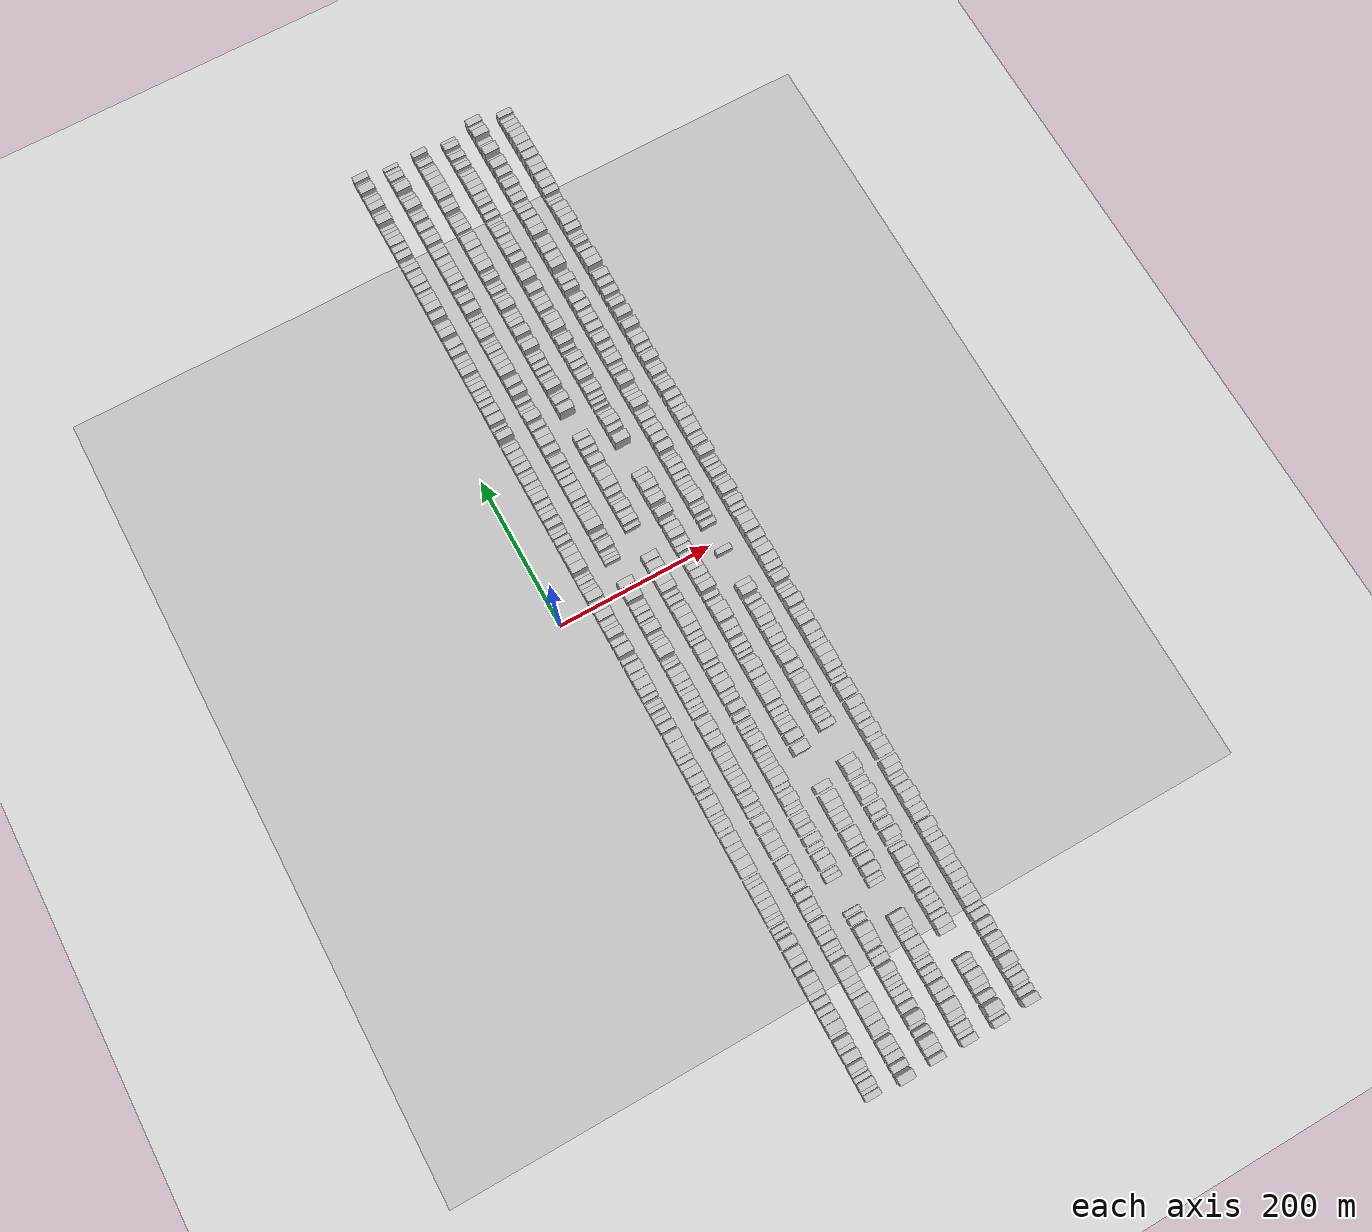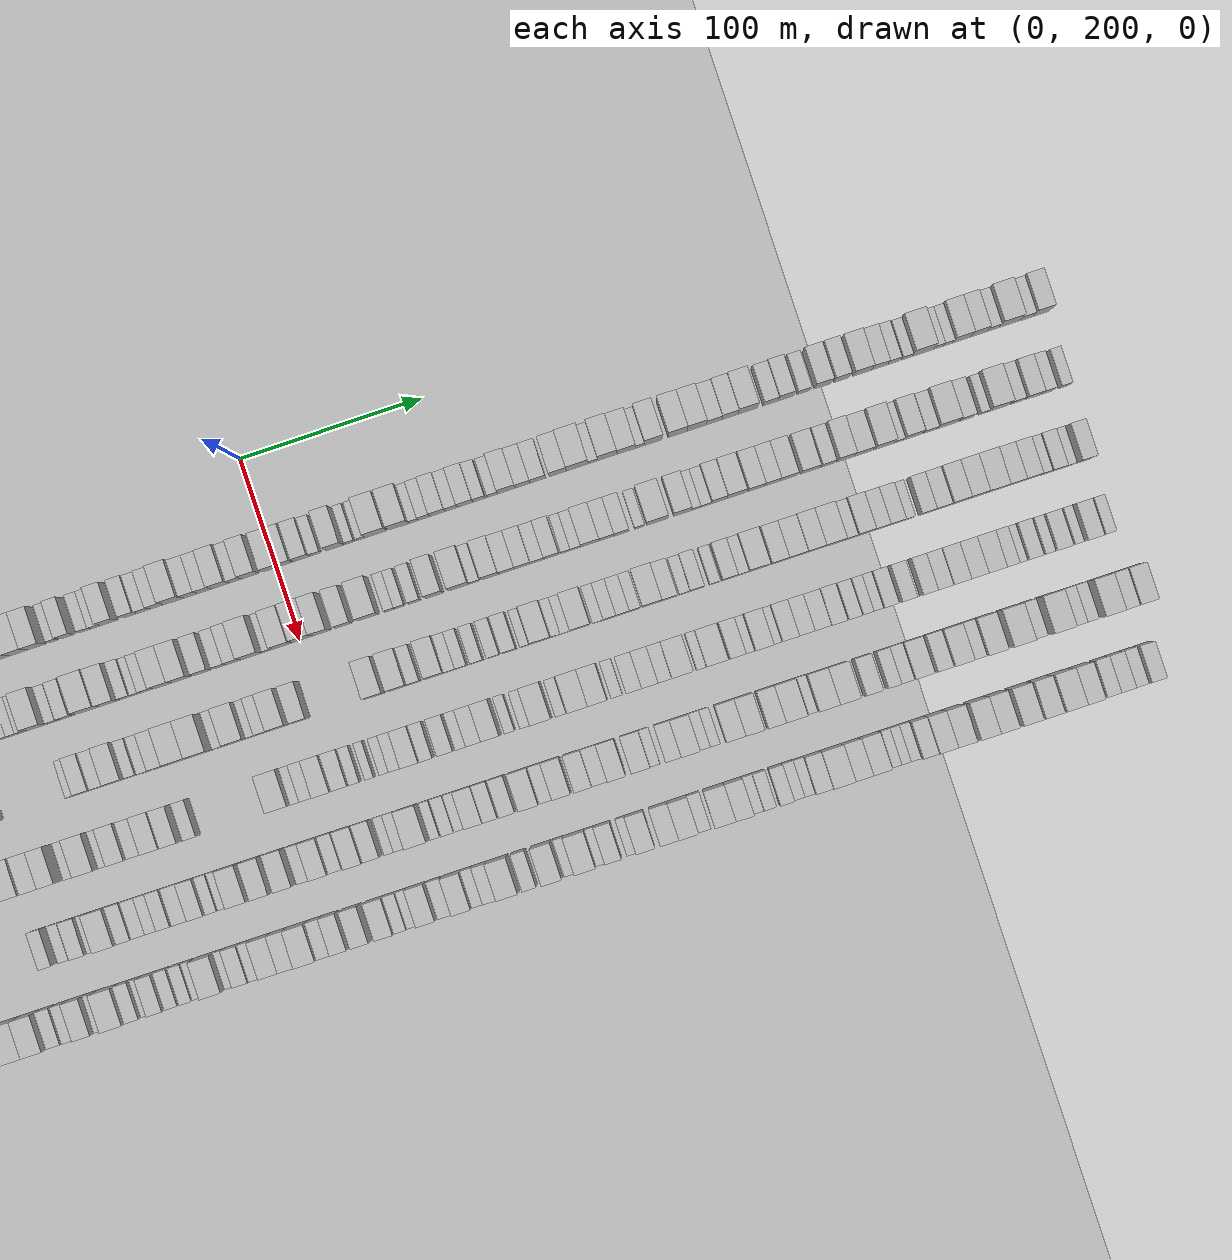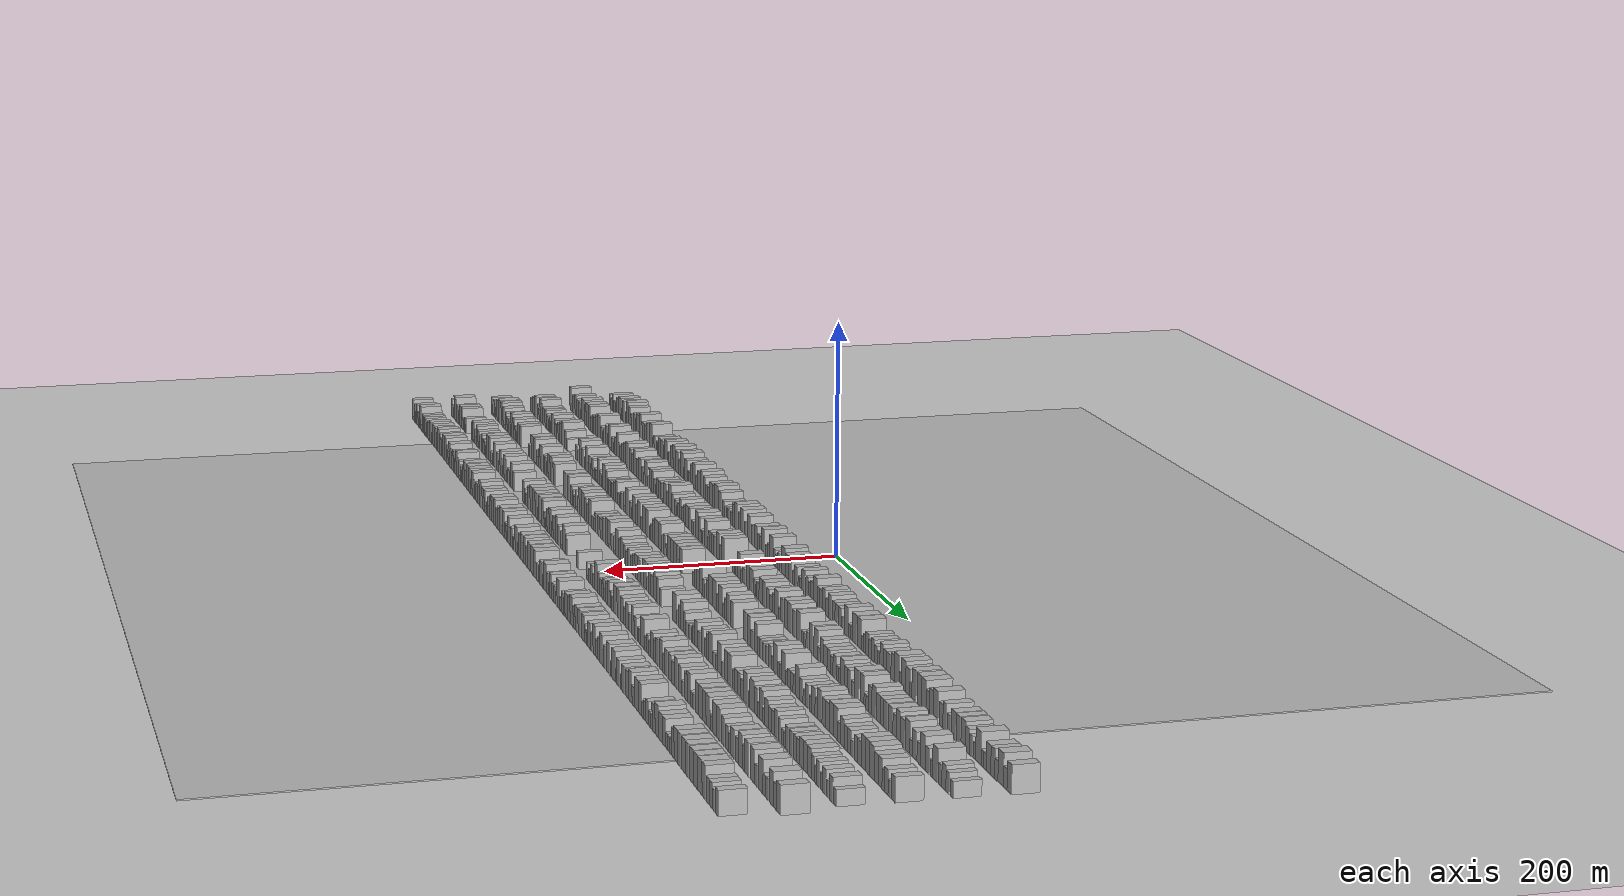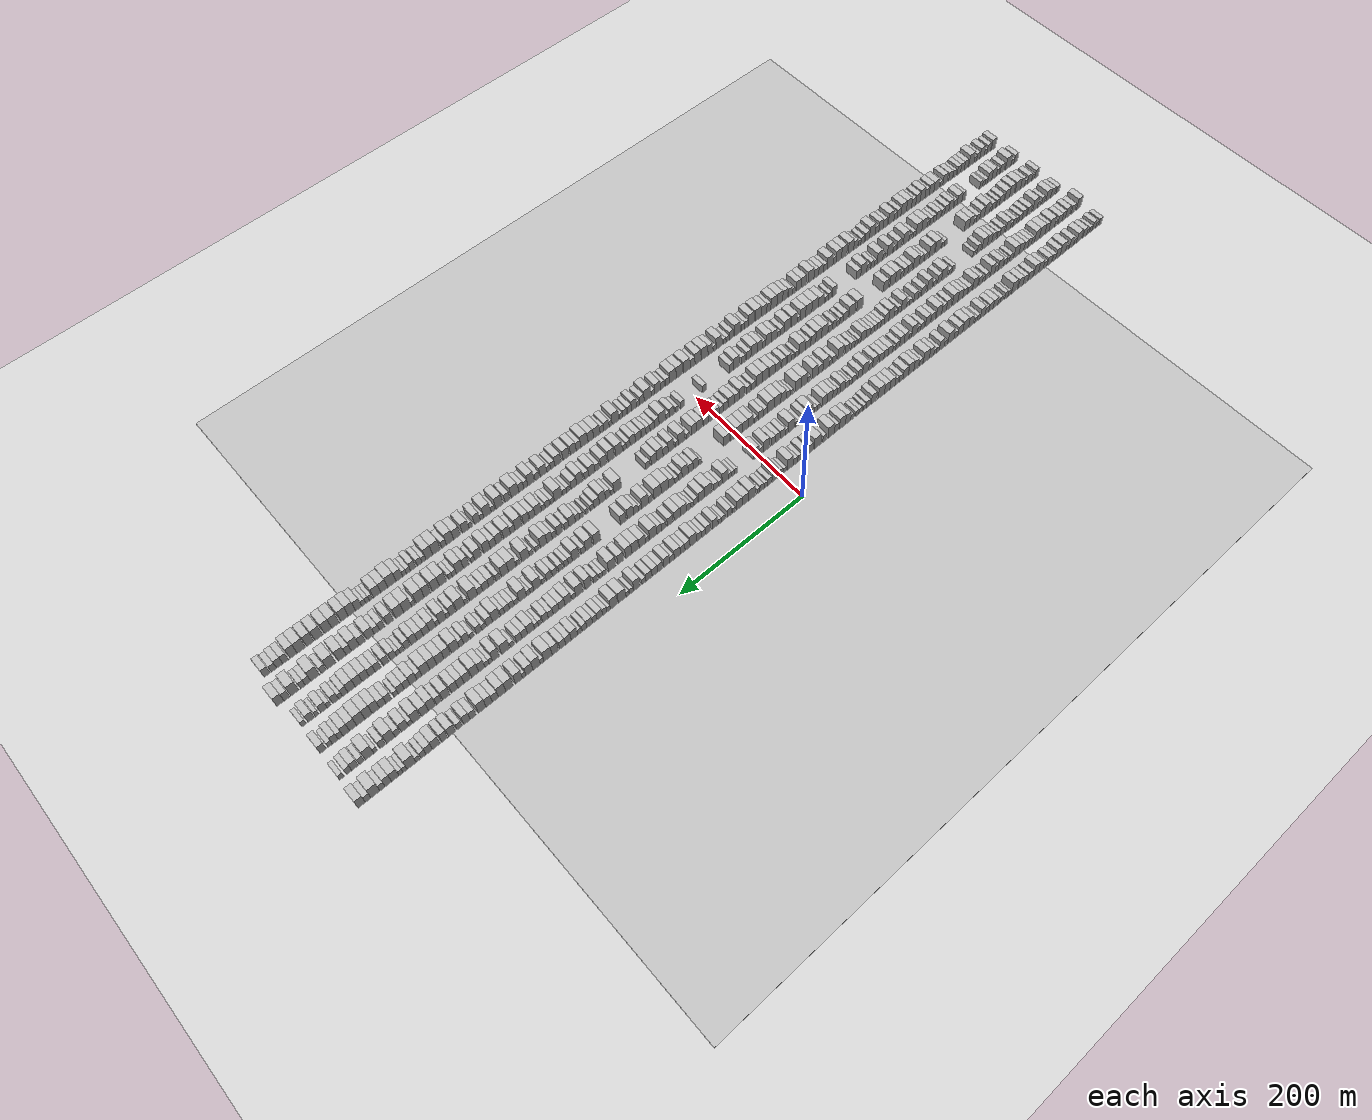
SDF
<?xml version="1.0" encoding="utf-8"?>

<sdf version="1.6">

   <world name="default">

      <gui fullscreen="0">

         <camera name="user_camera">

            <pose>-15 0 4.57585 0 0 0</pose>

            <view_controller>orbit</view_controller>

         </camera>

      </gui>

      <scene>

         <sky>

           <clouds>

             <speed>12</speed>

           </clouds>

         </sky>

         <ambient>0.4 0.4 0.4 1</ambient>

         <background>0.7 0.7 0.7 1</background>

         <shadows>1</shadows>

      </scene>

      <gravity>0 0 -9.8066</gravity>

      <magnetic_field>6e-06 2.3e-05 -4.2e-05</magnetic_field>

      <physics default="0" name="default_physics" type="ode">

         <ode>

            <solver>

               <type>quick</type>

               <iters>10</iters>

               <sor>1.0</sor>

               <use_dynamic_moi_rescaling>0</use_dynamic_moi_rescaling>

            </solver>

            <constraints>

               <cfm>0</cfm>

               <erp>0.2</erp>

               <contact_max_correcting_vel>100</contact_max_correcting_vel>

               <contact_surface_layer>0.001</contact_surface_layer>

            </constraints>

         </ode>

         <max_step_size>0.004</max_step_size>

         <real_time_factor>1</real_time_factor>

         <real_time_update_rate>250</real_time_update_rate>

      </physics>

      <light name="sun" type="directional">

         <cast_shadows>1</cast_shadows>

         <pose>0 0 10 0 0 0</pose>

         <diffuse>0.8 0.8 0.8 1</diffuse>

         <specular>0.2 0.2 0.2 1</specular>

         <attenuation>

            <range>1000</range>

            <constant>0.9</constant>

            <linear>0.01</linear>

            <quadratic>0.001</quadratic>

         </attenuation>

         <direction>-0.5 0.1 -0.9</direction>

      </light>

      <include>

         <name>ground_plane_1</name>

         <uri>model://HANNAS_ground_plane</uri>

         <pose>0 0 0  0 0 0</pose>

      </include>

      <include>

         <name>ground_plane_2</name>

         <uri>model://HANNAS_ground_plane</uri>

         <pose>100 0 0  0 0 0</pose>

      </include>

      <model name="building_1">

         <static>1</static>

         <pose frame="">50.0000 -614.4001 0 0.000000 0.000000 0.000000</pose>

         <link name="link">

            <pose frame="">0 0 7.50 0 0 0</pose>

            <collision name="collision">

               <geometry>

                  <box>

                     <size>20.0000 7.1998 15.0000</size>

                  </box>

               </geometry>

               <max_contacts>10</max_contacts>

               <surface>

                  <contact>

                     <ode/>

                  </contact>

                  <bounce/>

                  <friction>

                     <torsional>

                        <ode/>

                     </torsional>

                     <ode/>

                  </friction>

               </surface>

            </collision>

            <visual name="visual">

               <cast_shadows>0</cast_shadows>

               <geometry>

                  <box>

                     <size>20.0000 7.1998 15.0000</size>

                  </box>

               </geometry>

               <material>

                  <script>

                     <uri>model://HANNAS_wall/materials/scripts</uri>

                     <uri>model://HANNAS_wall/materials/textures</uri>

                     <name>vrc/HANNAS_wall</name>

                  </script>

               </material>

            </visual>

            <self_collide>0</self_collide>

            <enable_wind>0</enable_wind>

            <kinematic>0</kinematic>

         </link>

      </model>

      <model name="building_2">

         <static>1</static>

         <pose frame="">50.0000 -608.0700 0 0.000000 0.000000 0.000000</pose>

         <link name="link">

            <pose frame="">0 0 6.00 0 0 0</pose>

            <collision name="collision">

               <geometry>

                  <box>

                     <size>20.0000 5.4605 12.0000</size>

                  </box>

               </geometry>

               <max_contacts>10</max_contacts>

               <surface>

                  <contact>

                     <ode/>

                  </contact>

                  <bounce/>

                  <friction>

                     <torsional>

                        <ode/>

                     </torsional>

                     <ode/>

                  </friction>

               </surface>

            </collision>

            <visual name="visual">

               <cast_shadows>0</cast_shadows>

               <geometry>

                  <box>

                     <size>20.0000 5.4605 12.0000</size>

                  </box>

               </geometry>

               <material>

                  <script>

                     <uri>model://HANNAS_wall/materials/scripts</uri>

                     <uri>model://HANNAS_wall/materials/textures</uri>

                     <name>vrc/HANNAS_wall</name>

                  </script>

               </material>

            </visual>

            <self_collide>0</self_collide>

            <enable_wind>0</enable_wind>

            <kinematic>0</kinematic>

         </link>

      </model>

      <model name="building_3">

         <static>1</static>

         <pose frame="">50.0000 -601.2058 0 0.000000 0.000000 0.000000</pose>

         <link name="link">

            <pose frame="">0 0 9.00 0 0 0</pose>

            <collision name="collision">

               <geometry>

                  <box>

                     <size>20.0000 8.2679 18.0000</size>

                  </box>

               </geometry>

               <max_contacts>10</max_contacts>

               <surface>

                  <contact>

                     <ode/>

                  </contact>

                  <bounce/>

                  <friction>

                     <torsional>

                        <ode/>

                     </torsional>

                     <ode/>

                  </friction>

               </surface>

            </collision>

            <visual name="visual">

               <cast_shadows>0</cast_shadows>

               <geometry>

                  <box>

                     <size>20.0000 8.2679 18.0000</size>

                  </box>

               </geometry>

               <material>

                  <script>

                     <uri>model://HANNAS_wall/materials/scripts</uri>

                     <uri>model://HANNAS_wall/materials/textures</uri>

                     <name>vrc/HANNAS_wall</name>

                  </script>

               </material>

            </visual>

            <self_collide>0</self_collide>

            <enable_wind>0</enable_wind>

            <kinematic>0</kinematic>

         </link>

      </model>

      <model name="building_4">

         <static>1</static>

         <pose frame="">50.0000 -594.2463 0 0.000000 0.000000 0.000000</pose>

         <link name="link">

            <pose frame="">0 0 6.00 0 0 0</pose>

            <collision name="collision">

               <geometry>

                  <box>

                     <size>20.0000 5.6510 12.0000</size>

                  </box>

               </geometry>

               <max_contacts>10</max_contacts>

               <surface>

                  <contact>

                     <ode/>

                  </contact>

                  <bounce/>

                  <friction>

                     <torsional>

                        <ode/>

                     </torsional>

                     <ode/>

                  </friction>

               </surface>

            </collision>

            <visual name="visual">

               <cast_shadows>0</cast_shadows>

               <geometry>

                  <box>

                     <size>20.0000 5.6510 12.0000</size>

                  </box>

               </geometry>

               <material>

                  <script>

                     <uri>model://HANNAS_wall/materials/scripts</uri>

                     <uri>model://HANNAS_wall/materials/textures</uri>

                     <name>vrc/HANNAS_wall</name>

                  </script>

               </material>

            </visual>

            <self_collide>0</self_collide>

            <enable_wind>0</enable_wind>

            <kinematic>0</kinematic>

         </link>

      </model>

      <model name="building_5">

         <static>1</static>

         <pose frame="">50.0000 -587.8788 0 0.000000 0.000000 0.000000</pose>

         <link name="link">

            <pose frame="">0 0 6.00 0 0 0</pose>

            <collision name="collision">

               <geometry>

                  <box>

                     <size>20.0000 5.0839 12.0000</size>

                  </box>

               </geometry>

               <max_contacts>10</max_contacts>

               <surface>

                  <contact>

                     <ode/>

                  </contact>

                  <bounce/>

                  <friction>

                     <torsional>

                        <ode/>

                     </torsional>

                     <ode/>

                  </friction>

               </surface>

            </collision>

            <visual name="visual">

               <cast_shadows>0</cast_shadows>

               <geometry>

                  <box>

                     <size>20.0000 5.0839 12.0000</size>

                  </box>

               </geometry>

               <material>

                  <script>

                     <uri>model://HANNAS_wall/materials/scripts</uri>

                     <uri>model://HANNAS_wall/materials/textures</uri>

                     <name>vrc/HANNAS_wall</name>

                  </script>

               </material>

            </visual>

            <self_collide>0</self_collide>

            <enable_wind>0</enable_wind>

            <kinematic>0</kinematic>

         </link>

      </model>

      <model name="building_6">

         <static>1</static>

         <pose frame="">50.0000 -581.2737 0 0.000000 0.000000 0.000000</pose>

         <link name="link">

            <pose frame="">0 0 9.00 0 0 0</pose>

            <collision name="collision">

               <geometry>

                  <box>

                     <size>20.0000 8.1263 18.0000</size>

                  </box>

               </geometry>

               <max_contacts>10</max_contacts>

               <surface>

                  <contact>

                     <ode/>

                  </contact>

                  <bounce/>

                  <friction>

                     <torsional>

                        <ode/>

                     </torsional>

                     <ode/>

                  </friction>

               </surface>

            </collision>

            <visual name="visual">

               <cast_shadows>0</cast_shadows>

               <geometry>

                  <box>

                     <size>20.0000 8.1263 18.0000</size>

                  </box>

               </geometry>

               <material>

                  <script>

                     <uri>model://HANNAS_wall/materials/scripts</uri>

                     <uri>model://HANNAS_wall/materials/textures</uri>

                     <name>vrc/HANNAS_wall</name>

                  </script>

               </material>

            </visual>

            <self_collide>0</self_collide>

            <enable_wind>0</enable_wind>

            <kinematic>0</kinematic>

         </link>

      </model>

      <model name="building_7">

         <static>1</static>

         <pose frame="">50.0000 -568.9651 0 0.000000 0.000000 0.000000</pose>

         <link name="link">

            <pose frame="">0 0 10.50 0 0 0</pose>

            <collision name="collision">

               <geometry>

                  <box>

                     <size>20.0000 10.4911 21.0000</size>

                  </box>

               </geometry>

               <max_contacts>10</max_contacts>

               <surface>

                  <contact>

                     <ode/>

                  </contact>

                  <bounce/>

                  <friction>

                     <torsional>

                        <ode/>

                     </torsional>

                     <ode/>

                  </friction>

               </surface>

            </collision>

            <visual name="visual">

               <cast_shadows>0</cast_shadows>

               <geometry>

                  <box>

                     <size>20.0000 10.4911 21.0000</size>

                  </box>

               </geometry>

               <material>

                  <script>

                     <uri>model://HANNAS_wall/materials/scripts</uri>

                     <uri>model://HANNAS_wall/materials/textures</uri>

                     <name>vrc/HANNAS_wall</name>

                  </script>

               </material>

            </visual>

            <self_collide>0</self_collide>

            <enable_wind>0</enable_wind>

            <kinematic>0</kinematic>

         </link>

      </model>

      <model name="building_8">

         <static>1</static>

         <pose frame="">50.0000 -560.8816 0 0.000000 0.000000 0.000000</pose>

         <link name="link">

            <pose frame="">0 0 6.00 0 0 0</pose>

            <collision name="collision">

               <geometry>

                  <box>

                     <size>20.0000 5.6758 12.0000</size>

                  </box>

               </geometry>

               <max_contacts>10</max_contacts>

               <surface>

                  <contact>

                     <ode/>

                  </contact>

                  <bounce/>

                  <friction>

                     <torsional>

                        <ode/>

                     </torsional>

                     <ode/>

                  </friction>

               </surface>

            </collision>

            <visual name="visual">

               <cast_shadows>0</cast_shadows>

               <geometry>

                  <box>

                     <size>20.0000 5.6758 12.0000</size>

                  </box>

               </geometry>

               <material>

                  <script>

                     <uri>model://HANNAS_wall/materials/scripts</uri>

                     <uri>model://HANNAS_wall/materials/textures</uri>

                     <name>vrc/HANNAS_wall</name>

                  </script>

               </material>

            </visual>

            <self_collide>0</self_collide>

            <enable_wind>0</enable_wind>

            <kinematic>0</kinematic>

         </link>

      </model>

      <model name="building_9">

         <static>1</static>

         <pose frame="">50.0000 -552.5371 0 0.000000 0.000000 0.000000</pose>

         <link name="link">

            <pose frame="">0 0 10.50 0 0 0</pose>

            <collision name="collision">

               <geometry>

                  <box>

                     <size>20.0000 9.0132 21.0000</size>

                  </box>

               </geometry>

               <max_contacts>10</max_contacts>

               <surface>

                  <contact>

                     <ode/>

                  </contact>

                  <bounce/>

                  <friction>

                     <torsional>

                        <ode/>

                     </torsional>

                     <ode/>

                  </friction>

               </surface>

            </collision>

            <visual name="visual">

               <cast_shadows>0</cast_shadows>

               <geometry>

                  <box>

                     <size>20.0000 9.0132 21.0000</size>

                  </box>

               </geometry>

               <material>

                  <script>

                     <uri>model://HANNAS_wall/materials/scripts</uri>

                     <uri>model://HANNAS_wall/materials/textures</uri>

                     <name>vrc/HANNAS_wall</name>

                  </script>

               </material>

            </visual>

            <self_collide>0</self_collide>

            <enable_wind>0</enable_wind>

            <kinematic>0</kinematic>

         </link>

      </model>

      <model name="building_10">

         <static>1</static>

         <pose frame="">50.0000 -543.2090 0 0.000000 0.000000 0.000000</pose>

         <link name="link">

            <pose frame="">0 0 6.00 0 0 0</pose>

            <collision name="collision">

               <geometry>

                  <box>

                     <size>20.0000 5.6430 12.0000</size>

                  </box>

               </geometry>

               <max_contacts>10</max_contacts>

               <surface>

                  <contact>

                     <ode/>

                  </contact>

                  <bounce/>

                  <friction>

                     <torsional>

                        <ode/>

                     </torsional>

                     <ode/>

                  </friction>

               </surface>

            </collision>

            <visual name="visual">

               <cast_shadows>0</cast_shadows>

               <geometry>

                  <box>

                     <size>20.0000 5.6430 12.0000</size>

                  </box>

               </geometry>

               <material>

                  <script>

                     <uri>model://HANNAS_wall/materials/scripts</uri>

                     <uri>model://HANNAS_wall/materials/textures</uri>

                     <name>vrc/HANNAS_wall</name>

                  </script>

               </material>

            </visual>

            <self_collide>0</self_collide>

            <enable_wind>0</enable_wind>

            <kinematic>0</kinematic>

         </link>

      </model>

      <model name="building_11">

         <static>1</static>

         <pose frame="">50.0000 -534.6300 0 0.000000 0.000000 0.000000</pose>

         <link name="link">

            <pose frame="">0 0 12.00 0 0 0</pose>

            <collision name="collision">

               <geometry>

                  <box>

                     <size>20.0000 11.5151 24.0000</size>

                  </box>

               </geometry>

               <max_contacts>10</max_contacts>

               <surface>

                  <contact>

                     <ode/>

                  </contact>

                  <bounce/>

                  <friction>

                     <torsional>

                        <ode/>

                     </torsional>

                     <ode/>

                  </friction>

               </surface>

            </collision>

            <visual name="visual">

               <cast_shadows>0</cast_shadows>

               <geometry>

                  <box>

                     <size>20.0000 11.5151 24.0000</size>

                  </box>

               </geometry>

               <material>

                  <script>

                     <uri>model://HANNAS_wall/materials/scripts</uri>

                     <uri>model://HANNAS_wall/materials/textures</uri>

                     <name>vrc/HANNAS_wall</name>

                  </script>

               </material>

            </visual>

            <self_collide>0</self_collide>

            <enable_wind>0</enable_wind>

            <kinematic>0</kinematic>

         </link>

      </model>

      <model name="building_12">

         <static>1</static>

         <pose frame="">50.0000 -524.1794 0 0.000000 0.000000 0.000000</pose>

         <link name="link">

            <pose frame="">0 0 10.50 0 0 0</pose>

            <collision name="collision">

               <geometry>

                  <box>

                     <size>20.0000 9.3861 21.0000</size>

                  </box>

               </geometry>

               <max_contacts>10</max_contacts>

               <surface>

                  <contact>

                     <ode/>

                  </contact>

                  <bounce/>

                  <friction>

                     <torsional>

                        <ode/>

                     </torsional>

                     <ode/>

                  </friction>

               </surface>

            </collision>

            <visual name="visual">

               <cast_shadows>0</cast_shadows>

               <geometry>

                  <box>

                     <size>20.0000 9.3861 21.0000</size>

                  </box>

               </geometry>

               <material>

                  <script>

                     <uri>model://HANNAS_wall/materials/scripts</uri>

                     <uri>model://HANNAS_wall/materials/textures</uri>

                     <name>vrc/HANNAS_wall</name>

                  </script>

               </material>

            </visual>

            <self_collide>0</self_collide>

            <enable_wind>0</enable_wind>

            <kinematic>0</kinematic>

         </link>

      </model>

      <model name="building_13">

         <static>1</static>

         <pose frame="">50.0000 -515.9298 0 0.000000 0.000000 0.000000</pose>

         <link name="link">

            <pose frame="">0 0 7.50 0 0 0</pose>

            <collision name="collision">

               <geometry>

                  <box>

                     <size>20.0000 7.1131 15.0000</size>

                  </box>

               </geometry>

               <max_contacts>10</max_contacts>

               <surface>

                  <contact>

                     <ode/>

                  </contact>

                  <bounce/>

                  <friction>

                     <torsional>

                        <ode/>

                     </torsional>

                     <ode/>

                  </friction>

               </surface>

            </collision>

            <visual name="visual">

               <cast_shadows>0</cast_shadows>

               <geometry>

                  <box>

                     <size>20.0000 7.1131 15.0000</size>

                  </box>

               </geometry>

               <material>

                  <script>

                     <uri>model://HANNAS_wall/materials/scripts</uri>

                     <uri>model://HANNAS_wall/materials/textures</uri>

                     <name>vrc/HANNAS_wall</name>

                  </script>

               </material>

            </visual>

            <self_collide>0</self_collide>

            <enable_wind>0</enable_wind>

            <kinematic>0</kinematic>

         </link>

      </model>

      <model name="building_14">

         <static>1</static>

         <pose frame="">50.0000 -506.0313 0 0.000000 0.000000 0.000000</pose>

         <link name="link">

            <pose frame="">0 0 9.00 0 0 0</pose>

            <collision name="collision">

               <geometry>

                  <box>

                     <size>20.0000 8.6839 18.0000</size>

                  </box>

               </geometry>

               <max_contacts>10</max_contacts>

               <surface>

                  <contact>

                     <ode/>

                  </contact>

                  <bounce/>

                  <friction>

                     <torsional>

                        <ode/>

                     </torsional>

                     <ode/>

                  </friction>

               </surface>

            </collision>

            <visual name="visual">

               <cast_shadows>0</cast_shadows>

               <geometry>

                  <box>

                     <size>20.0000 8.6839 18.0000</size>

                  </box>

               </geometry>

               <material>

                  <script>

                     <uri>model://HANNAS_wall/materials/scripts</uri>

                     <uri>model://HANNAS_wall/materials/textures</uri>

                     <name>vrc/HANNAS_wall</name>

                  </script>

               </material>

            </visual>

            <self_collide>0</self_collide>

            <enable_wind>0</enable_wind>

            <kinematic>0</kinematic>

         </link>

      </model>

      <model name="building_15">

         <static>1</static>

         <pose frame="">50.0000 -497.1717 0 0.000000 0.000000 0.000000</pose>

         <link name="link">

            <pose frame="">0 0 7.50 0 0 0</pose>

            <collision name="collision">

               <geometry>

                  <box>

                     <size>20.0000 7.0353 15.0000</size>

                  </box>

               </geometry>

               <max_contacts>10</max_contacts>

               <surface>

                  <contact>

                     <ode/>

                  </contact>

                  <bounce/>

                  <friction>

                     <torsional>

                        <ode/>

                     </torsional>

                     <ode/>

                  </friction>

               </surface>

            </collision>

            <visual name="visual">

               <cast_shadows>0</cast_shadows>

               <geometry>

                  <box>

                     <size>20.0000 7.0353 15.0000</size>

                  </box>

               </geometry>

               <material>

                  <script>

                     <uri>model://HANNAS_wall/materials/scripts</uri>

                     <uri>model://HANNAS_wall/materials/textures</uri>

                     <name>vrc/HANNAS_wall</name>

                  </script>

               </material>

            </visual>

            <self_collide>0</self_collide>

            <enable_wind>0</enable_wind>

            <kinematic>0</kinematic>

         </link>

      </model>

      <model name="building_16">

         <static>1</static>

         <pose frame="">50.0000 -488.5574 0 0.000000 0.000000 0.000000</pose>

         <link name="link">

            <pose frame="">0 0 10.50 0 0 0</pose>

            <collision name="collision">

               <geometry>

                  <box>

                     <size>20.0000 10.1933 21.0000</size>

                  </box>

               </geometry>

               <max_contacts>10</max_contacts>

               <surface>

                  <contact>

                     <ode/>

                  </contact>

                  <bounce/>

                  <friction>

                     <torsional>

                        <ode/>

                     </torsional>

                     <ode/>

                  </friction>

               </surface>

            </collision>

            <visual name="visual">

               <cast_shadows>0</cast_shadows>

               <geometry>

                  <box>

                     <size>20.0000 10.1933 21.0000</size>

                  </box>

               </geometry>

               <material>

                  <script>

                     <uri>model://HANNAS_wall/materials/scripts</uri>

                     <uri>model://HANNAS_wall/materials/textures</uri>

                     <name>vrc/HANNAS_wall</name>

                  </script>

               </material>

            </visual>

            <self_collide>0</self_collide>

            <enable_wind>0</enable_wind>

            <kinematic>0</kinematic>

         </link>

      </model>

      <model name="building_17">

         <static>1</static>

         <pose frame="">50.0000 -478.4403 0 0.000000 0.000000 0.000000</pose>

         <link name="link">

            <pose frame="">0 0 12.00 0 0 0</pose>

            <collision name="collision">

               <geometry>

                  <box>

                     <size>20.0000 10.0410 24.0000</size>

                  </box>

               </geometry>

               <max_contacts>10</max_contacts>

               <surface>

                  <contact>

                     <ode/>

                  </contact>

                  <bounce/>

                  <friction>

                     <torsional>

                        <ode/>

                     </torsional>

                     <ode/>

                  </friction>

               </surface>

            </collision>

            <visual name="visual">

               <cast_shadows>0</cast_shadows>

               <geometry>

                  <box>

                     <size>20.0000 10.0410 24.0000</size>

                  </box>

               </geometry>

               <material>

                  <script>

                     <uri>model://HANNAS_wall/materials/scripts</uri>

                     <uri>model://HANNAS_wall/materials/textures</uri>

                     <name>vrc/HANNAS_wall</name>

                  </script>

               </material>

            </visual>

            <self_collide>0</self_collide>

            <enable_wind>0</enable_wind>

            <kinematic>0</kinematic>

         </link>

      </model>

      <model name="building_18">

         <static>1</static>

         <pose frame="">50.0000 -466.9310 0 0.000000 0.000000 0.000000</pose>

         <link name="link">

            <pose frame="">0 0 9.00 0 0 0</pose>

            <collision name="collision">

               <geometry>

                  <box>

                     <size>20.0000 8.9775 18.0000</size>

                  </box>

               </geometry>

               <max_contacts>10</max_contacts>

               <surface>

                  <contact>

                     <ode/>

                  </contact>

                  <bounce/>

                  <friction>

                     <torsional>

                        <ode/>

                     </torsional>

                     <ode/>

                  </friction>

               </surface>

            </collision>

            <visual name="visual">

               <cast_shadows>0</cast_shadows>

               <geometry>

                  <box>

                     <size>20.0000 8.9775 18.0000</size>

                  </box>

               </geometry>

               <material>

                  <script>

                     <uri>model://HANNAS_wall/materials/scripts</uri>

                     <uri>model://HANNAS_wall/materials/textures</uri>

                     <name>vrc/HANNAS_wall</name>

                  </script>

               </material>

            </visual>

            <self_collide>0</self_collide>

            <enable_wind>0</enable_wind>

            <kinematic>0</kinematic>

         </link>

      </model>

      <model name="building_19">

         <static>1</static>

         <pose frame="">50.0000 -456.0338 0 0.000000 0.000000 0.000000</pose>

         <link name="link">

            <pose frame="">0 0 9.00 0 0 0</pose>

            <collision name="collision">

               <geometry>

                  <box>

                     <size>20.0000 8.8170 18.0000</size>

                  </box>

               </geometry>

               <max_contacts>10</max_contacts>

               <surface>

                  <contact>

                     <ode/>

                  </contact>

                  <bounce/>

                  <friction>

                     <torsional>

                        <ode/>

                     </torsional>

                     <ode/>

                  </friction>

               </surface>

            </collision>

            <visual name="visual">

               <cast_shadows>0</cast_shadows>

               <geometry>

                  <box>

                     <size>20.0000 8.8170 18.0000</size>

                  </box>

               </geometry>

               <material>

                  <script>

                     <uri>model://HANNAS_wall/materials/scripts</uri>

                     <uri>model://HANNAS_wall/materials/textures</uri>

                     <name>vrc/HANNAS_wall</name>

                  </script>

               </material>

            </visual>

            <self_collide>0</self_collide>

            <enable_wind>0</enable_wind>

            <kinematic>0</kinematic>

         </link>

      </model>

      <model name="building_20">

         <static>1</static>

         <pose frame="">50.0000 -446.7315 0 0.000000 0.000000 0.000000</pose>

         <link name="link">

            <pose frame="">0 0 10.50 0 0 0</pose>

            <collision name="collision">

               <geometry>

                  <box>

                     <size>20.0000 9.7877 21.0000</size>

                  </box>

               </geometry>

               <max_contacts>10</max_contacts>

               <surface>

                  <contact>

                     <ode/>

                  </contact>

                  <bounce/>

                  <friction>

                     <torsional>

                        <ode/>

                     </torsional>

                     <ode/>

                  </friction>

               </surface>

            </collision>

            <visual name="visual">

               <cast_shadows>0</cast_shadows>

               <geometry>

                  <box>

                     <size>20.0000 9.7877 21.0000</size>

                  </box>

               </geometry>

               <material>

                  <script>

                     <uri>model://HANNAS_wall/materials/scripts</uri>

                     <uri>model://HANNAS_wall/materials/textures</uri>

                     <name>vrc/HANNAS_wall</name>

                  </script>

               </material>

            </visual>

            <self_collide>0</self_collide>

            <enable_wind>0</enable_wind>

            <kinematic>0</kinematic>

         </link>

      </model>

      <model name="building_21">

         <static>1</static>

         <pose frame="">50.0000 -433.6766 0 0.000000 0.000000 0.000000</pose>

         <link name="link">

            <pose frame="">0 0 12.00 0 0 0</pose>

            <collision name="collision">

               <geometry>

                  <box>

                     <size>20.0000 10.3219 24.0000</size>

                  </box>

               </geometry>

               <max_contacts>10</max_contacts>

               <surface>

                  <contact>

                     <ode/>

                  </contact>

                  <bounce/>

                  <friction>

                     <torsional>

                        <ode/>

                     </torsional>

                     <ode/>

                  </friction>

               </surface>

            </collision>

            <visual name="visual">

               <cast_shadows>0</cast_shadows>

               <geometry>

                  <box>

                     <size>20.0000 10.3219 24.0000</size>

                  </box>

               </geometry>

               <material>

                  <script>

                     <uri>model://HANNAS_wall/materials/scripts</uri>

                     <uri>model://HANNAS_wall/materials/textures</uri>

                     <name>vrc/HANNAS_wall</name>

                  </script>

               </material>

            </visual>

            <self_collide>0</self_collide>

            <enable_wind>0</enable_wind>

            <kinematic>0</kinematic>

         </link>

      </model>

      <model name="building_22">

         <static>1</static>

         <pose frame="">50.0000 -424.0932 0 0.000000 0.000000 0.000000</pose>

         <link name="link">

            <pose frame="">0 0 6.00 0 0 0</pose>

            <collision name="collision">

               <geometry>

                  <box>

                     <size>20.0000 4.8448 12.0000</size>

                  </box>

               </geometry>

               <max_contacts>10</max_contacts>

               <surface>

                  <contact>

                     <ode/>

                  </contact>

                  <bounce/>

                  <friction>

                     <torsional>

                        <ode/>

                     </torsional>

                     <ode/>

                  </friction>

               </surface>

            </collision>

            <visual name="visual">

               <cast_shadows>0</cast_shadows>

               <geometry>

                  <box>

                     <size>20.0000 4.8448 12.0000</size>

                  </box>

               </geometry>

               <material>

                  <script>

                     <uri>model://HANNAS_wall/materials/scripts</uri>

                     <uri>model://HANNAS_wall/materials/textures</uri>

                     <name>vrc/HANNAS_wall</name>

                  </script>

               </material>

            </visual>

            <self_collide>0</self_collide>

            <enable_wind>0</enable_wind>

            <kinematic>0</kinematic>

         </link>

      </model>

      <model name="building_23">

         <static>1</static>

         <pose frame="">50.0000 -417.6111 0 0.000000 0.000000 0.000000</pose>

         <link name="link">

            <pose frame="">0 0 7.50 0 0 0</pose>

            <collision name="collision">

               <geometry>

                  <box>

                     <size>20.0000 6.1194 15.0000</size>

                  </box>

               </geometry>

               <max_contacts>10</max_contacts>

               <surface>

                  <contact>

                     <ode/>

                  </contact>

                  <bounce/>

                  <friction>

                     <torsional>

                        <ode/>

                     </torsional>

                     <ode/>

                  </friction>

               </surface>

            </collision>

            <visual name="visual">

               <cast_shadows>0</cast_shadows>

               <geometry>

                  <box>

                     <size>20.0000 6.1194 15.0000</size>

                  </box>

               </geometry>

               <material>

                  <script>

                     <uri>model://HANNAS_wall/materials/scripts</uri>

                     <uri>model://HANNAS_wall/materials/textures</uri>

                     <name>vrc/HANNAS_wall</name>

                  </script>

               </material>

            </visual>

            <self_collide>0</self_collide>

            <enable_wind>0</enable_wind>

            <kinematic>0</kinematic>

         </link>

      </model>

      <model name="building_24">

         <static>1</static>

         <pose frame="">50.0000 -408.5586 0 0.000000 0.000000 0.000000</pose>

         <link name="link">

            <pose frame="">0 0 6.00 0 0 0</pose>

            <collision name="collision">

               <geometry>

                  <box>

                     <size>20.0000 5.9855 12.0000</size>

                  </box>

               </geometry>

               <max_contacts>10</max_contacts>

               <surface>

                  <contact>

                     <ode/>

                  </contact>

                  <bounce/>

                  <friction>

                     <torsional>

                        <ode/>

                     </torsional>

                     <ode/>

                  </friction>

               </surface>

            </collision>

            <visual name="visual">

               <cast_shadows>0</cast_shadows>

               <geometry>

                  <box>

                     <size>20.0000 5.9855 12.0000</size>

                  </box>

               </geometry>

               <material>

                  <script>

                     <uri>model://HANNAS_wall/materials/scripts</uri>

                     <uri>model://HANNAS_wall/materials/textures</uri>

                     <name>vrc/HANNAS_wall</name>

                  </script>

               </material>

            </visual>

            <self_collide>0</self_collide>

            <enable_wind>0</enable_wind>

            <kinematic>0</kinematic>

         </link>

      </model>

      <model name="building_25">

         <static>1</static>

         <pose frame="">50.0000 -403.1385 0 0.000000 0.000000 0.000000</pose>

         <link name="link">

            <pose frame="">0 0 6.00 0 0 0</pose>

            <collision name="collision">

               <geometry>

                  <box>

                     <size>20.0000 4.8546 12.0000</size>

                  </box>

               </geometry>

               <max_contacts>10</max_contacts>

               <surface>

                  <contact>

                     <ode/>

                  </contact>

                  <bounce/>

                  <friction>

                     <torsional>

                        <ode/>

                     </torsional>

                     <ode/>

                  </friction>

               </surface>

            </collision>

            <visual name="visual">

               <cast_shadows>0</cast_shadows>

               <geometry>

                  <box>

                     <size>20.0000 4.8546 12.0000</size>

                  </box>

               </geometry>

               <material>

                  <script>

                     <uri>model://HANNAS_wall/materials/scripts</uri>

                     <uri>model://HANNAS_wall/materials/textures</uri>

                     <name>vrc/HANNAS_wall</name>

                  </script>

               </material>

            </visual>

            <self_collide>0</self_collide>

            <enable_wind>0</enable_wind>

            <kinematic>0</kinematic>

         </link>

      </model>

      <model name="building_26">

         <static>1</static>

         <pose frame="">50.0000 -396.2474 0 0.000000 0.000000 0.000000</pose>

         <link name="link">

            <pose frame="">0 0 9.00 0 0 0</pose>

            <collision name="collision">

               <geometry>

                  <box>

                     <size>20.0000 8.9276 18.0000</size>

                  </box>

               </geometry>

               <max_contacts>10</max_contacts>

               <surface>

                  <contact>

                     <ode/>

                  </contact>

                  <bounce/>

                  <friction>

                     <torsional>

                        <ode/>

                     </torsional>

                     <ode/>

                  </friction>

               </surface>

            </collision>

            <visual name="visual">

               <cast_shadows>0</cast_shadows>

               <geometry>

                  <box>

                     <size>20.0000 8.9276 18.0000</size>

                  </box>

               </geometry>

               <material>

                  <script>

                     <uri>model://HANNAS_wall/materials/scripts</uri>

                     <uri>model://HANNAS_wall/materials/textures</uri>

                     <name>vrc/HANNAS_wall</name>

                  </script>

               </material>

            </visual>

            <self_collide>0</self_collide>

            <enable_wind>0</enable_wind>

            <kinematic>0</kinematic>

         </link>

      </model>

      <model name="building_27">

         <static>1</static>

         <pose frame="">50.0000 -387.3386 0 0.000000 0.000000 0.000000</pose>

         <link name="link">

            <pose frame="">0 0 9.00 0 0 0</pose>

            <collision name="collision">

               <geometry>

                  <box>

                     <size>20.0000 8.8899 18.0000</size>

                  </box>

               </geometry>

               <max_contacts>10</max_contacts>

               <surface>

                  <contact>

                     <ode/>

                  </contact>

                  <bounce/>

                  <friction>

                     <torsional>

                        <ode/>

                     </torsional>

                     <ode/>

                  </friction>

               </surface>

            </collision>

            <visual name="visual">

               <cast_shadows>0</cast_shadows>

               <geometry>

                  <box>

                     <size>20.0000 8.8899 18.0000</size>

                  </box>

               </geometry>

               <material>

                  <script>

                     <uri>model://HANNAS_wall/materials/scripts</uri>

                     <uri>model://HANNAS_wall/materials/textures</uri>

                     <name>vrc/HANNAS_wall</name>

                  </script>

               </material>

            </visual>

            <self_collide>0</self_collide>

            <enable_wind>0</enable_wind>

            <kinematic>0</kinematic>

         </link>

      </model>

      <model name="building_28">

         <static>1</static>

         <pose frame="">50.0000 -379.2376 0 0.000000 0.000000 0.000000</pose>

         <link name="link">

            <pose frame="">0 0 7.50 0 0 0</pose>

            <collision name="collision">

               <geometry>

                  <box>

                     <size>20.0000 7.3122 15.0000</size>

                  </box>

               </geometry>

               <max_contacts>10</max_contacts>

               <surface>

                  <contact>

                     <ode/>

                  </contact>

                  <bounce/>

                  <friction>

                     <torsional>

                        <ode/>

                     </torsional>

                     <ode/>

                  </friction>

               </surface>

            </collision>

            <visual name="visual">

               <cast_shadows>0</cast_shadows>

               <geometry>

                  <box>

                     <size>20.0000 7.3122 15.0000</size>

                  </box>

               </geometry>

               <material>

                  <script>

                     <uri>model://HANNAS_wall/materials/scripts</uri>

                     <uri>model://HANNAS_wall/materials/textures</uri>

                     <name>vrc/HANNAS_wall</name>

                  </script>

               </material>

            </visual>

            <self_collide>0</self_collide>

            <enable_wind>0</enable_wind>

            <kinematic>0</kinematic>

         </link>

      </model>

      <model name="building_29">

         <static>1</static>

         <pose frame="">50.0000 -370.6812 0 0.000000 0.000000 0.000000</pose>

         <link name="link">

            <pose frame="">0 0 10.50 0 0 0</pose>

            <collision name="collision">

               <geometry>

                  <box>

                     <size>20.0000 9.8005 21.0000</size>

                  </box>

               </geometry>

               <max_contacts>10</max_contacts>

               <surface>

                  <contact>

                     <ode/>

                  </contact>

                  <bounce/>

                  <friction>

                     <torsional>

                        <ode/>

                     </torsional>

                     <ode/>

                  </friction>

               </surface>

            </collision>

            <visual name="visual">

               <cast_shadows>0</cast_shadows>

               <geometry>

                  <box>

                     <size>20.0000 9.8005 21.0000</size>

                  </box>

               </geometry>

               <material>

                  <script>

                     <uri>model://HANNAS_wall/materials/scripts</uri>

                     <uri>model://HANNAS_wall/materials/textures</uri>

                     <name>vrc/HANNAS_wall</name>

                  </script>

               </material>

            </visual>

            <self_collide>0</self_collide>

            <enable_wind>0</enable_wind>

            <kinematic>0</kinematic>

         </link>

      </model>

      <model name="building_30">

         <static>1</static>

         <pose frame="">50.0000 -362.9657 0 0.000000 0.000000 0.000000</pose>

         <link name="link">

            <pose frame="">0 0 6.00 0 0 0</pose>

            <collision name="collision">

               <geometry>

                  <box>

                     <size>20.0000 5.6305 12.0000</size>

                  </box>

               </geometry>

               <max_contacts>10</max_contacts>

               <surface>

                  <contact>

                     <ode/>

                  </contact>

                  <bounce/>

                  <friction>

                     <torsional>

                        <ode/>

                     </torsional>

                     <ode/>

                  </friction>

               </surface>

            </collision>

            <visual name="visual">

               <cast_shadows>0</cast_shadows>

               <geometry>

                  <box>

                     <size>20.0000 5.6305 12.0000</size>

                  </box>

               </geometry>

               <material>

                  <script>

                     <uri>model://HANNAS_wall/materials/scripts</uri>

                     <uri>model://HANNAS_wall/materials/textures</uri>

                     <name>vrc/HANNAS_wall</name>

                  </script>

               </material>

            </visual>

            <self_collide>0</self_collide>

            <enable_wind>0</enable_wind>

            <kinematic>0</kinematic>

         </link>

      </model>

      <model name="building_31">

         <static>1</static>

         <pose frame="">50.0000 -357.5958 0 0.000000 0.000000 0.000000</pose>

         <link name="link">

            <pose frame="">0 0 6.00 0 0 0</pose>

            <collision name="collision">

               <geometry>

                  <box>

                     <size>20.0000 5.1092 12.0000</size>

                  </box>

               </geometry>

               <max_contacts>10</max_contacts>

               <surface>

                  <contact>

                     <ode/>

                  </contact>

                  <bounce/>

                  <friction>

                     <torsional>

                        <ode/>

                     </torsional>

                     <ode/>

                  </friction>

               </surface>

            </collision>

            <visual name="visual">

               <cast_shadows>0</cast_shadows>

               <geometry>

                  <box>

                     <size>20.0000 5.1092 12.0000</size>

                  </box>

               </geometry>

               <material>

                  <script>

                     <uri>model://HANNAS_wall/materials/scripts</uri>

                     <uri>model://HANNAS_wall/materials/textures</uri>

                     <name>vrc/HANNAS_wall</name>

                  </script>

               </material>

            </visual>

            <self_collide>0</self_collide>

            <enable_wind>0</enable_wind>

            <kinematic>0</kinematic>

         </link>

      </model>

      <model name="building_32">

         <static>1</static>

         <pose frame="">50.0000 -347.4738 0 0.000000 0.000000 0.000000</pose>

         <link name="link">

            <pose frame="">0 0 10.50 0 0 0</pose>

            <collision name="collision">

               <geometry>

                  <box>

                     <size>20.0000 9.1349 21.0000</size>

                  </box>

               </geometry>

               <max_contacts>10</max_contacts>

               <surface>

                  <contact>

                     <ode/>

                  </contact>

                  <bounce/>

                  <friction>

                     <torsional>

                        <ode/>

                     </torsional>

                     <ode/>

                  </friction>

               </surface>

            </collision>

            <visual name="visual">

               <cast_shadows>0</cast_shadows>

               <geometry>

                  <box>

                     <size>20.0000 9.1349 21.0000</size>

                  </box>

               </geometry>

               <material>

                  <script>

                     <uri>model://HANNAS_wall/materials/scripts</uri>

                     <uri>model://HANNAS_wall/materials/textures</uri>

                     <name>vrc/HANNAS_wall</name>

                  </script>

               </material>

            </visual>

            <self_collide>0</self_collide>

            <enable_wind>0</enable_wind>

            <kinematic>0</kinematic>

         </link>

      </model>

      <model name="building_33">

         <static>1</static>

         <pose frame="">50.0000 -337.1691 0 0.000000 0.000000 0.000000</pose>

         <link name="link">

            <pose frame="">0 0 12.00 0 0 0</pose>

            <collision name="collision">

               <geometry>

                  <box>

                     <size>20.0000 11.4745 24.0000</size>

                  </box>

               </geometry>

               <max_contacts>10</max_contacts>

               <surface>

                  <contact>

                     <ode/>

                  </contact>

                  <bounce/>

                  <friction>

                     <torsional>

                        <ode/>

                     </torsional>

                     <ode/>

                  </friction>

               </surface>

            </collision>

            <visual name="visual">

               <cast_shadows>0</cast_shadows>

               <geometry>

                  <box>

                     <size>20.0000 11.4745 24.0000</size>

                  </box>

               </geometry>

               <material>

                  <script>

                     <uri>model://HANNAS_wall/materials/scripts</uri>

                     <uri>model://HANNAS_wall/materials/textures</uri>

                     <name>vrc/HANNAS_wall</name>

                  </script>

               </material>

            </visual>

            <self_collide>0</self_collide>

            <enable_wind>0</enable_wind>

            <kinematic>0</kinematic>

         </link>

      </model>

      <model name="building_34">

         <static>1</static>

         <pose frame="">50.0000 -326.5298 0 0.000000 0.000000 0.000000</pose>

         <link name="link">

            <pose frame="">0 0 10.50 0 0 0</pose>

            <collision name="collision">

               <geometry>

                  <box>

                     <size>20.0000 9.8041 21.0000</size>

                  </box>

               </geometry>

               <max_contacts>10</max_contacts>

               <surface>

                  <contact>

                     <ode/>

                  </contact>

                  <bounce/>

                  <friction>

                     <torsional>

                        <ode/>

                     </torsional>

                     <ode/>

                  </friction>

               </surface>

            </collision>

            <visual name="visual">

               <cast_shadows>0</cast_shadows>

               <geometry>

                  <box>

                     <size>20.0000 9.8041 21.0000</size>

                  </box>

               </geometry>

               <material>

                  <script>

                     <uri>model://HANNAS_wall/materials/scripts</uri>

                     <uri>model://HANNAS_wall/materials/textures</uri>

                     <name>vrc/HANNAS_wall</name>

                  </script>

               </material>

            </visual>

            <self_collide>0</self_collide>

            <enable_wind>0</enable_wind>

            <kinematic>0</kinematic>

         </link>

      </model>

      <model name="building_35">

         <static>1</static>

         <pose frame="">50.0000 -317.9521 0 0.000000 0.000000 0.000000</pose>

         <link name="link">

            <pose frame="">0 0 7.50 0 0 0</pose>

            <collision name="collision">

               <geometry>

                  <box>

                     <size>20.0000 7.3512 15.0000</size>

                  </box>

               </geometry>

               <max_contacts>10</max_contacts>

               <surface>

                  <contact>

                     <ode/>

                  </contact>

                  <bounce/>

                  <friction>

                     <torsional>

                        <ode/>

                     </torsional>

                     <ode/>

                  </friction>

               </surface>

            </collision>

            <visual name="visual">

               <cast_shadows>0</cast_shadows>

               <geometry>

                  <box>

                     <size>20.0000 7.3512 15.0000</size>

                  </box>

               </geometry>

               <material>

                  <script>

                     <uri>model://HANNAS_wall/materials/scripts</uri>

                     <uri>model://HANNAS_wall/materials/textures</uri>

                     <name>vrc/HANNAS_wall</name>

                  </script>

               </material>

            </visual>

            <self_collide>0</self_collide>

            <enable_wind>0</enable_wind>

            <kinematic>0</kinematic>

         </link>

      </model>

      <model name="building_36">

         <static>1</static>

         <pose frame="">50.0000 -308.2831 0 0.000000 0.000000 0.000000</pose>

         <link name="link">

            <pose frame="">0 0 12.00 0 0 0</pose>

            <collision name="collision">

               <geometry>

                  <box>

                     <size>20.0000 11.9869 24.0000</size>

                  </box>

               </geometry>

               <max_contacts>10</max_contacts>

               <surface>

                  <contact>

                     <ode/>

                  </contact>

                  <bounce/>

                  <friction>

                     <torsional>

                        <ode/>

                     </torsional>

                     <ode/>

                  </friction>

               </surface>

            </collision>

            <visual name="visual">

               <cast_shadows>0</cast_shadows>

               <geometry>

                  <box>

                     <size>20.0000 11.9869 24.0000</size>

                  </box>

               </geometry>

               <material>

                  <script>

                     <uri>model://HANNAS_wall/materials/scripts</uri>

                     <uri>model://HANNAS_wall/materials/textures</uri>

                     <name>vrc/HANNAS_wall</name>

                  </script>

               </material>

            </visual>

            <self_collide>0</self_collide>

            <enable_wind>0</enable_wind>

            <kinematic>0</kinematic>

         </link>

      </model>

      <model name="building_37">

         <static>1</static>

         <pose frame="">50.0000 -298.5193 0 0.000000 0.000000 0.000000</pose>

         <link name="link">

            <pose frame="">0 0 6.00 0 0 0</pose>

            <collision name="collision">

               <geometry>

                  <box>

                     <size>20.0000 5.5406 12.0000</size>

                  </box>

               </geometry>

               <max_contacts>10</max_contacts>

               <surface>

                  <contact>

                     <ode/>

                  </contact>

                  <bounce/>

                  <friction>

                     <torsional>

                        <ode/>

                     </torsional>

                     <ode/>

                  </friction>

               </surface>

            </collision>

            <visual name="visual">

               <cast_shadows>0</cast_shadows>

               <geometry>

                  <box>

                     <size>20.0000 5.5406 12.0000</size>

                  </box>

               </geometry>

               <material>

                  <script>

                     <uri>model://HANNAS_wall/materials/scripts</uri>

                     <uri>model://HANNAS_wall/materials/textures</uri>

                     <name>vrc/HANNAS_wall</name>

                  </script>

               </material>

            </visual>

            <self_collide>0</self_collide>

            <enable_wind>0</enable_wind>

            <kinematic>0</kinematic>

         </link>

      </model>

      <model name="building_38">

         <static>1</static>

         <pose frame="">50.0000 -290.8896 0 0.000000 0.000000 0.000000</pose>

         <link name="link">

            <pose frame="">0 0 10.50 0 0 0</pose>

            <collision name="collision">

               <geometry>

                  <box>

                     <size>20.0000 9.7188 21.0000</size>

                  </box>

               </geometry>

               <max_contacts>10</max_contacts>

               <surface>

                  <contact>

                     <ode/>

                  </contact>

                  <bounce/>

                  <friction>

                     <torsional>

                        <ode/>

                     </torsional>

                     <ode/>

                  </friction>

               </surface>

            </collision>

            <visual name="visual">

               <cast_shadows>0</cast_shadows>

               <geometry>

                  <box>

                     <size>20.0000 9.7188 21.0000</size>

                  </box>

               </geometry>

               <material>

                  <script>

                     <uri>model://HANNAS_wall/materials/scripts</uri>

                     <uri>model://HANNAS_wall/materials/textures</uri>

                     <name>vrc/HANNAS_wall</name>

                  </script>

               </material>

            </visual>

            <self_collide>0</self_collide>

            <enable_wind>0</enable_wind>

            <kinematic>0</kinematic>

         </link>

      </model>

      <model name="building_39">

         <static>1</static>

         <pose frame="">50.0000 -283.3686 0 0.000000 0.000000 0.000000</pose>

         <link name="link">

            <pose frame="">0 0 6.00 0 0 0</pose>

            <collision name="collision">

               <geometry>

                  <box>

                     <size>20.0000 5.3231 12.0000</size>

                  </box>

               </geometry>

               <max_contacts>10</max_contacts>

               <surface>

                  <contact>

                     <ode/>

                  </contact>

                  <bounce/>

                  <friction>

                     <torsional>

                        <ode/>

                     </torsional>

                     <ode/>

                  </friction>

               </surface>

            </collision>

            <visual name="visual">

               <cast_shadows>0</cast_shadows>

               <geometry>

                  <box>

                     <size>20.0000 5.3231 12.0000</size>

                  </box>

               </geometry>

               <material>

                  <script>

                     <uri>model://HANNAS_wall/materials/scripts</uri>

                     <uri>model://HANNAS_wall/materials/textures</uri>

                     <name>vrc/HANNAS_wall</name>

                  </script>

               </material>

            </visual>

            <self_collide>0</self_collide>

            <enable_wind>0</enable_wind>

            <kinematic>0</kinematic>

         </link>

      </model>

      <model name="building_40">

         <static>1</static>

         <pose frame="">50.0000 -278.2641 0 0.000000 0.000000 0.000000</pose>

         <link name="link">

            <pose frame="">0 0 6.00 0 0 0</pose>

            <collision name="collision">

               <geometry>

                  <box>

                     <size>20.0000 4.8858 12.0000</size>

                  </box>

               </geometry>

               <max_contacts>10</max_contacts>

               <surface>

                  <contact>

                     <ode/>

                  </contact>

                  <bounce/>

                  <friction>

                     <torsional>

                        <ode/>

                     </torsional>

                     <ode/>

                  </friction>

               </surface>

            </collision>

            <visual name="visual">

               <cast_shadows>0</cast_shadows>

               <geometry>

                  <box>

                     <size>20.0000 4.8858 12.0000</size>

                  </box>

               </geometry>

               <material>

                  <script>

                     <uri>model://HANNAS_wall/materials/scripts</uri>

                     <uri>model://HANNAS_wall/materials/textures</uri>

                     <name>vrc/HANNAS_wall</name>

                  </script>

               </material>

            </visual>

            <self_collide>0</self_collide>

            <enable_wind>0</enable_wind>

            <kinematic>0</kinematic>

         </link>

      </model>

      <model name="building_41">

         <static>1</static>

         <pose frame="">50.0000 -271.4610 0 0.000000 0.000000 0.000000</pose>

         <link name="link">

            <pose frame="">0 0 10.50 0 0 0</pose>

            <collision name="collision">

               <geometry>

                  <box>

                     <size>20.0000 8.7205 21.0000</size>

                  </box>

               </geometry>

               <max_contacts>10</max_contacts>

               <surface>

                  <contact>

                     <ode/>

                  </contact>

                  <bounce/>

                  <friction>

                     <torsional>

                        <ode/>

                     </torsional>

                     <ode/>

                  </friction>

               </surface>

            </collision>

            <visual name="visual">

               <cast_shadows>0</cast_shadows>

               <geometry>

                  <box>

                     <size>20.0000 8.7205 21.0000</size>

                  </box>

               </geometry>

               <material>

                  <script>

                     <uri>model://HANNAS_wall/materials/scripts</uri>

                     <uri>model://HANNAS_wall/materials/textures</uri>

                     <name>vrc/HANNAS_wall</name>

                  </script>

               </material>

            </visual>

            <self_collide>0</self_collide>

            <enable_wind>0</enable_wind>

            <kinematic>0</kinematic>

         </link>

      </model>

      <model name="building_42">

         <static>1</static>

         <pose frame="">50.0000 -261.3814 0 0.000000 0.000000 0.000000</pose>

         <link name="link">

            <pose frame="">0 0 12.00 0 0 0</pose>

            <collision name="collision">

               <geometry>

                  <box>

                     <size>20.0000 11.4386 24.0000</size>

                  </box>

               </geometry>

               <max_contacts>10</max_contacts>

               <surface>

                  <contact>

                     <ode/>

                  </contact>

                  <bounce/>

                  <friction>

                     <torsional>

                        <ode/>

                     </torsional>

                     <ode/>

                  </friction>

               </surface>

            </collision>

            <visual name="visual">

               <cast_shadows>0</cast_shadows>

               <geometry>

                  <box>

                     <size>20.0000 11.4386 24.0000</size>

                  </box>

               </geometry>

               <material>

                  <script>

                     <uri>model://HANNAS_wall/materials/scripts</uri>

                     <uri>model://HANNAS_wall/materials/textures</uri>

                     <name>vrc/HANNAS_wall</name>

                  </script>

               </material>

            </visual>

            <self_collide>0</self_collide>

            <enable_wind>0</enable_wind>

            <kinematic>0</kinematic>

         </link>

      </model>

      <model name="building_43">

         <static>1</static>

         <pose frame="">50.0000 -251.5604 0 0.000000 0.000000 0.000000</pose>

         <link name="link">

            <pose frame="">0 0 7.50 0 0 0</pose>

            <collision name="collision">

               <geometry>

                  <box>

                     <size>20.0000 6.2033 15.0000</size>

                  </box>

               </geometry>

               <max_contacts>10</max_contacts>

               <surface>

                  <contact>

                     <ode/>

                  </contact>

                  <bounce/>

                  <friction>

                     <torsional>

                        <ode/>

                     </torsional>

                     <ode/>

                  </friction>

               </surface>

            </collision>

            <visual name="visual">

               <cast_shadows>0</cast_shadows>

               <geometry>

                  <box>

                     <size>20.0000 6.2033 15.0000</size>

                  </box>

               </geometry>

               <material>

                  <script>

                     <uri>model://HANNAS_wall/materials/scripts</uri>

                     <uri>model://HANNAS_wall/materials/textures</uri>

                     <name>vrc/HANNAS_wall</name>

                  </script>

               </material>

            </visual>

            <self_collide>0</self_collide>

            <enable_wind>0</enable_wind>

            <kinematic>0</kinematic>

         </link>

      </model>

      <model name="building_44">

         <static>1</static>

         <pose frame="">50.0000 -242.1434 0 0.000000 0.000000 0.000000</pose>

         <link name="link">

            <pose frame="">0 0 10.50 0 0 0</pose>

            <collision name="collision">

               <geometry>

                  <box>

                     <size>20.0000 8.6308 21.0000</size>

                  </box>

               </geometry>

               <max_contacts>10</max_contacts>

               <surface>

                  <contact>

                     <ode/>

                  </contact>

                  <bounce/>

                  <friction>

                     <torsional>

                        <ode/>

                     </torsional>

                     <ode/>

                  </friction>

               </surface>

            </collision>

            <visual name="visual">

               <cast_shadows>0</cast_shadows>

               <geometry>

                  <box>

                     <size>20.0000 8.6308 21.0000</size>

                  </box>

               </geometry>

               <material>

                  <script>

                     <uri>model://HANNAS_wall/materials/scripts</uri>

                     <uri>model://HANNAS_wall/materials/textures</uri>

                     <name>vrc/HANNAS_wall</name>

                  </script>

               </material>

            </visual>

            <self_collide>0</self_collide>

            <enable_wind>0</enable_wind>

            <kinematic>0</kinematic>

         </link>

      </model>

      <model name="building_45">

         <static>1</static>

         <pose frame="">50.0000 -232.9112 0 0.000000 0.000000 0.000000</pose>

         <link name="link">

            <pose frame="">0 0 12.00 0 0 0</pose>

            <collision name="collision">

               <geometry>

                  <box>

                     <size>20.0000 9.8335 24.0000</size>

                  </box>

               </geometry>

               <max_contacts>10</max_contacts>

               <surface>

                  <contact>

                     <ode/>

                  </contact>

                  <bounce/>

                  <friction>

                     <torsional>

                        <ode/>

                     </torsional>

                     <ode/>

                  </friction>

               </surface>

            </collision>

            <visual name="visual">

               <cast_shadows>0</cast_shadows>

               <geometry>

                  <box>

                     <size>20.0000 9.8335 24.0000</size>

                  </box>

               </geometry>

               <material>

                  <script>

                     <uri>model://HANNAS_wall/materials/scripts</uri>

                     <uri>model://HANNAS_wall/materials/textures</uri>

                     <name>vrc/HANNAS_wall</name>

                  </script>

               </material>

            </visual>

            <self_collide>0</self_collide>

            <enable_wind>0</enable_wind>

            <kinematic>0</kinematic>

         </link>

      </model>

      <model name="building_46">

         <static>1</static>

         <pose frame="">50.0000 -222.1742 0 0.000000 0.000000 0.000000</pose>

         <link name="link">

            <pose frame="">0 0 10.50 0 0 0</pose>

            <collision name="collision">

               <geometry>

                  <box>

                     <size>20.0000 9.6407 21.0000</size>

                  </box>

               </geometry>

               <max_contacts>10</max_contacts>

               <surface>

                  <contact>

                     <ode/>

                  </contact>

                  <bounce/>

                  <friction>

                     <torsional>

                        <ode/>

                     </torsional>

                     <ode/>

                  </friction>

               </surface>

            </collision>

            <visual name="visual">

               <cast_shadows>0</cast_shadows>

               <geometry>

                  <box>

                     <size>20.0000 9.6407 21.0000</size>

                  </box>

               </geometry>

               <material>

                  <script>

                     <uri>model://HANNAS_wall/materials/scripts</uri>

                     <uri>model://HANNAS_wall/materials/textures</uri>

                     <name>vrc/HANNAS_wall</name>

                  </script>

               </material>

            </visual>

            <self_collide>0</self_collide>

            <enable_wind>0</enable_wind>

            <kinematic>0</kinematic>

         </link>

      </model>

      <model name="building_47">

         <static>1</static>

         <pose frame="">50.0000 -213.8160 0 0.000000 0.000000 0.000000</pose>

         <link name="link">

            <pose frame="">0 0 7.50 0 0 0</pose>

            <collision name="collision">

               <geometry>

                  <box>

                     <size>20.0000 7.0757 15.0000</size>

                  </box>

               </geometry>

               <max_contacts>10</max_contacts>

               <surface>

                  <contact>

                     <ode/>

                  </contact>

                  <bounce/>

                  <friction>

                     <torsional>

                        <ode/>

                     </torsional>

                     <ode/>

                  </friction>

               </surface>

            </collision>

            <visual name="visual">

               <cast_shadows>0</cast_shadows>

               <geometry>

                  <box>

                     <size>20.0000 7.0757 15.0000</size>

                  </box>

               </geometry>

               <material>

                  <script>

                     <uri>model://HANNAS_wall/materials/scripts</uri>

                     <uri>model://HANNAS_wall/materials/textures</uri>

                     <name>vrc/HANNAS_wall</name>

                  </script>

               </material>

            </visual>

            <self_collide>0</self_collide>

            <enable_wind>0</enable_wind>

            <kinematic>0</kinematic>

         </link>

      </model>

      <model name="building_48">

         <static>1</static>

         <pose frame="">50.0000 -206.1168 0 0.000000 0.000000 0.000000</pose>

         <link name="link">

            <pose frame="">0 0 7.50 0 0 0</pose>

            <collision name="collision">

               <geometry>

                  <box>

                     <size>20.0000 6.3227 15.0000</size>

                  </box>

               </geometry>

               <max_contacts>10</max_contacts>

               <surface>

                  <contact>

                     <ode/>

                  </contact>

                  <bounce/>

                  <friction>

                     <torsional>

                        <ode/>

                     </torsional>

                     <ode/>

                  </friction>

               </surface>

            </collision>

            <visual name="visual">

               <cast_shadows>0</cast_shadows>

               <geometry>

                  <box>

                     <size>20.0000 6.3227 15.0000</size>

                  </box>

               </geometry>

               <material>

                  <script>

                     <uri>model://HANNAS_wall/materials/scripts</uri>

                     <uri>model://HANNAS_wall/materials/textures</uri>

                     <name>vrc/HANNAS_wall</name>

                  </script>

               </material>

            </visual>

            <self_collide>0</self_collide>

            <enable_wind>0</enable_wind>

            <kinematic>0</kinematic>

         </link>

      </model>

      <model name="building_49">

         <static>1</static>

         <pose frame="">50.0000 -198.2082 0 0.000000 0.000000 0.000000</pose>

         <link name="link">

            <pose frame="">0 0 10.50 0 0 0</pose>

            <collision name="collision">

               <geometry>

                  <box>

                     <size>20.0000 9.4945 21.0000</size>

                  </box>

               </geometry>

               <max_contacts>10</max_contacts>

               <surface>

                  <contact>

                     <ode/>

                  </contact>

                  <bounce/>

                  <friction>

                     <torsional>

                        <ode/>

                     </torsional>

                     <ode/>

                  </friction>

               </surface>

            </collision>

            <visual name="visual">

               <cast_shadows>0</cast_shadows>

               <geometry>

                  <box>

                     <size>20.0000 9.4945 21.0000</size>

                  </box>

               </geometry>

               <material>

                  <script>

                     <uri>model://HANNAS_wall/materials/scripts</uri>

                     <uri>model://HANNAS_wall/materials/textures</uri>

                     <name>vrc/HANNAS_wall</name>

                  </script>

               </material>

            </visual>

            <self_collide>0</self_collide>

            <enable_wind>0</enable_wind>

            <kinematic>0</kinematic>

         </link>

      </model>

      <model name="building_50">

         <static>1</static>

         <pose frame="">50.0000 -188.3169 0 0.000000 0.000000 0.000000</pose>

         <link name="link">

            <pose frame="">0 0 10.50 0 0 0</pose>

            <collision name="collision">

               <geometry>

                  <box>

                     <size>20.0000 10.2882 21.0000</size>

                  </box>

               </geometry>

               <max_contacts>10</max_contacts>

               <surface>

                  <contact>

                     <ode/>

                  </contact>

                  <bounce/>

                  <friction>

                     <torsional>

                        <ode/>

                     </torsional>

                     <ode/>

                  </friction>

               </surface>

            </collision>

            <visual name="visual">

               <cast_shadows>0</cast_shadows>

               <geometry>

                  <box>

                     <size>20.0000 10.2882 21.0000</size>

                  </box>

               </geometry>

               <material>

                  <script>

                     <uri>model://HANNAS_wall/materials/scripts</uri>

                     <uri>model://HANNAS_wall/materials/textures</uri>

                     <name>vrc/HANNAS_wall</name>

                  </script>

               </material>

            </visual>

            <self_collide>0</self_collide>

            <enable_wind>0</enable_wind>

            <kinematic>0</kinematic>

         </link>

      </model>

      <model name="building_51">

         <static>1</static>

         <pose frame="">50.0000 -177.5266 0 0.000000 0.000000 0.000000</pose>

         <link name="link">

            <pose frame="">0 0 12.00 0 0 0</pose>

            <collision name="collision">

               <geometry>

                  <box>

                     <size>20.0000 11.2924 24.0000</size>

                  </box>

               </geometry>

               <max_contacts>10</max_contacts>

               <surface>

                  <contact>

                     <ode/>

                  </contact>

                  <bounce/>

                  <friction>

                     <torsional>

                        <ode/>

                     </torsional>

                     <ode/>

                  </friction>

               </surface>

            </collision>

            <visual name="visual">

               <cast_shadows>0</cast_shadows>

               <geometry>

                  <box>

                     <size>20.0000 11.2924 24.0000</size>

                  </box>

               </geometry>

               <material>

                  <script>

                     <uri>model://HANNAS_wall/materials/scripts</uri>

                     <uri>model://HANNAS_wall/materials/textures</uri>

                     <name>vrc/HANNAS_wall</name>

                  </script>

               </material>

            </visual>

            <self_collide>0</self_collide>

            <enable_wind>0</enable_wind>

            <kinematic>0</kinematic>

         </link>

      </model>

      <model name="building_52">

         <static>1</static>

         <pose frame="">50.0000 -164.0788 0 0.000000 0.000000 0.000000</pose>

         <link name="link">

            <pose frame="">0 0 10.50 0 0 0</pose>

            <collision name="collision">

               <geometry>

                  <box>

                     <size>20.0000 9.6032 21.0000</size>

                  </box>

               </geometry>

               <max_contacts>10</max_contacts>

               <surface>

                  <contact>

                     <ode/>

                  </contact>

                  <bounce/>

                  <friction>

                     <torsional>

                        <ode/>

                     </torsional>

                     <ode/>

                  </friction>

               </surface>

            </collision>

            <visual name="visual">

               <cast_shadows>0</cast_shadows>

               <geometry>

                  <box>

                     <size>20.0000 9.6032 21.0000</size>

                  </box>

               </geometry>

               <material>

                  <script>

                     <uri>model://HANNAS_wall/materials/scripts</uri>

                     <uri>model://HANNAS_wall/materials/textures</uri>

                     <name>vrc/HANNAS_wall</name>

                  </script>

               </material>

            </visual>

            <self_collide>0</self_collide>

            <enable_wind>0</enable_wind>

            <kinematic>0</kinematic>

         </link>

      </model>

      <model name="building_53">

         <static>1</static>

         <pose frame="">50.0000 -153.5577 0 0.000000 0.000000 0.000000</pose>

         <link name="link">

            <pose frame="">0 0 7.50 0 0 0</pose>

            <collision name="collision">

               <geometry>

                  <box>

                     <size>20.0000 7.4390 15.0000</size>

                  </box>

               </geometry>

               <max_contacts>10</max_contacts>

               <surface>

                  <contact>

                     <ode/>

                  </contact>

                  <bounce/>

                  <friction>

                     <torsional>

                        <ode/>

                     </torsional>

                     <ode/>

                  </friction>

               </surface>

            </collision>

            <visual name="visual">

               <cast_shadows>0</cast_shadows>

               <geometry>

                  <box>

                     <size>20.0000 7.4390 15.0000</size>

                  </box>

               </geometry>

               <material>

                  <script>

                     <uri>model://HANNAS_wall/materials/scripts</uri>

                     <uri>model://HANNAS_wall/materials/textures</uri>

                     <name>vrc/HANNAS_wall</name>

                  </script>

               </material>

            </visual>

            <self_collide>0</self_collide>

            <enable_wind>0</enable_wind>

            <kinematic>0</kinematic>

         </link>

      </model>

      <model name="building_54">

         <static>1</static>

         <pose frame="">50.0000 -147.1237 0 0.000000 0.000000 0.000000</pose>

         <link name="link">

            <pose frame="">0 0 6.00 0 0 0</pose>

            <collision name="collision">

               <geometry>

                  <box>

                     <size>20.0000 5.4288 12.0000</size>

                  </box>

               </geometry>

               <max_contacts>10</max_contacts>

               <surface>

                  <contact>

                     <ode/>

                  </contact>

                  <bounce/>

                  <friction>

                     <torsional>

                        <ode/>

                     </torsional>

                     <ode/>

                  </friction>

               </surface>

            </collision>

            <visual name="visual">

               <cast_shadows>0</cast_shadows>

               <geometry>

                  <box>

                     <size>20.0000 5.4288 12.0000</size>

                  </box>

               </geometry>

               <material>

                  <script>

                     <uri>model://HANNAS_wall/materials/scripts</uri>

                     <uri>model://HANNAS_wall/materials/textures</uri>

                     <name>vrc/HANNAS_wall</name>

                  </script>

               </material>

            </visual>

            <self_collide>0</self_collide>

            <enable_wind>0</enable_wind>

            <kinematic>0</kinematic>

         </link>

      </model>

      <model name="building_55">

         <static>1</static>

         <pose frame="">50.0000 -139.5434 0 0.000000 0.000000 0.000000</pose>

         <link name="link">

            <pose frame="">0 0 6.00 0 0 0</pose>

            <collision name="collision">

               <geometry>

                  <box>

                     <size>20.0000 5.7318 12.0000</size>

                  </box>

               </geometry>

               <max_contacts>10</max_contacts>

               <surface>

                  <contact>

                     <ode/>

                  </contact>

                  <bounce/>

                  <friction>

                     <torsional>

                        <ode/>

                     </torsional>

                     <ode/>

                  </friction>

               </surface>

            </collision>

            <visual name="visual">

               <cast_shadows>0</cast_shadows>

               <geometry>

                  <box>

                     <size>20.0000 5.7318 12.0000</size>

                  </box>

               </geometry>

               <material>

                  <script>

                     <uri>model://HANNAS_wall/materials/scripts</uri>

                     <uri>model://HANNAS_wall/materials/textures</uri>

                     <name>vrc/HANNAS_wall</name>

                  </script>

               </material>

            </visual>

            <self_collide>0</self_collide>

            <enable_wind>0</enable_wind>

            <kinematic>0</kinematic>

         </link>

      </model>

      <model name="building_56">

         <static>1</static>

         <pose frame="">50.0000 -133.7722 0 0.000000 0.000000 0.000000</pose>

         <link name="link">

            <pose frame="">0 0 6.00 0 0 0</pose>

            <collision name="collision">

               <geometry>

                  <box>

                     <size>20.0000 5.8106 12.0000</size>

                  </box>

               </geometry>

               <max_contacts>10</max_contacts>

               <surface>

                  <contact>

                     <ode/>

                  </contact>

                  <bounce/>

                  <friction>

                     <torsional>

                        <ode/>

                     </torsional>

                     <ode/>

                  </friction>

               </surface>

            </collision>

            <visual name="visual">

               <cast_shadows>0</cast_shadows>

               <geometry>

                  <box>

                     <size>20.0000 5.8106 12.0000</size>

                  </box>

               </geometry>

               <material>

                  <script>

                     <uri>model://HANNAS_wall/materials/scripts</uri>

                     <uri>model://HANNAS_wall/materials/textures</uri>

                     <name>vrc/HANNAS_wall</name>

                  </script>

               </material>

            </visual>

            <self_collide>0</self_collide>

            <enable_wind>0</enable_wind>

            <kinematic>0</kinematic>

         </link>

      </model>

      <model name="building_57">

         <static>1</static>

         <pose frame="">50.0000 -124.9748 0 0.000000 0.000000 0.000000</pose>

         <link name="link">

            <pose frame="">0 0 6.00 0 0 0</pose>

            <collision name="collision">

               <geometry>

                  <box>

                     <size>20.0000 5.7843 12.0000</size>

                  </box>

               </geometry>

               <max_contacts>10</max_contacts>

               <surface>

                  <contact>

                     <ode/>

                  </contact>

                  <bounce/>

                  <friction>

                     <torsional>

                        <ode/>

                     </torsional>

                     <ode/>

                  </friction>

               </surface>

            </collision>

            <visual name="visual">

               <cast_shadows>0</cast_shadows>

               <geometry>

                  <box>

                     <size>20.0000 5.7843 12.0000</size>

                  </box>

               </geometry>

               <material>

                  <script>

                     <uri>model://HANNAS_wall/materials/scripts</uri>

                     <uri>model://HANNAS_wall/materials/textures</uri>

                     <name>vrc/HANNAS_wall</name>

                  </script>

               </material>

            </visual>

            <self_collide>0</self_collide>

            <enable_wind>0</enable_wind>

            <kinematic>0</kinematic>

         </link>

      </model>

      <model name="building_58">

         <static>1</static>

         <pose frame="">50.0000 -117.4279 0 0.000000 0.000000 0.000000</pose>

         <link name="link">

            <pose frame="">0 0 10.50 0 0 0</pose>

            <collision name="collision">

               <geometry>

                  <box>

                     <size>20.0000 9.3093 21.0000</size>

                  </box>

               </geometry>

               <max_contacts>10</max_contacts>

               <surface>

                  <contact>

                     <ode/>

                  </contact>

                  <bounce/>

                  <friction>

                     <torsional>

                        <ode/>

                     </torsional>

                     <ode/>

                  </friction>

               </surface>

            </collision>

            <visual name="visual">

               <cast_shadows>0</cast_shadows>

               <geometry>

                  <box>

                     <size>20.0000 9.3093 21.0000</size>

                  </box>

               </geometry>

               <material>

                  <script>

                     <uri>model://HANNAS_wall/materials/scripts</uri>

                     <uri>model://HANNAS_wall/materials/textures</uri>

                     <name>vrc/HANNAS_wall</name>

                  </script>

               </material>

            </visual>

            <self_collide>0</self_collide>

            <enable_wind>0</enable_wind>

            <kinematic>0</kinematic>

         </link>

      </model>

      <model name="building_59">

         <static>1</static>

         <pose frame="">50.0000 -107.3029 0 0.000000 0.000000 0.000000</pose>

         <link name="link">

            <pose frame="">0 0 12.00 0 0 0</pose>

            <collision name="collision">

               <geometry>

                  <box>

                     <size>20.0000 10.9407 24.0000</size>

                  </box>

               </geometry>

               <max_contacts>10</max_contacts>

               <surface>

                  <contact>

                     <ode/>

                  </contact>

                  <bounce/>

                  <friction>

                     <torsional>

                        <ode/>

                     </torsional>

                     <ode/>

                  </friction>

               </surface>

            </collision>

            <visual name="visual">

               <cast_shadows>0</cast_shadows>

               <geometry>

                  <box>

                     <size>20.0000 10.9407 24.0000</size>

                  </box>

               </geometry>

               <material>

                  <script>

                     <uri>model://HANNAS_wall/materials/scripts</uri>

                     <uri>model://HANNAS_wall/materials/textures</uri>

                     <name>vrc/HANNAS_wall</name>

                  </script>

               </material>

            </visual>

            <self_collide>0</self_collide>

            <enable_wind>0</enable_wind>

            <kinematic>0</kinematic>

         </link>

      </model>

      <model name="building_60">

         <static>1</static>

         <pose frame="">50.0000 -96.9875 0 0.000000 0.000000 0.000000</pose>

         <link name="link">

            <pose frame="">0 0 9.00 0 0 0</pose>

            <collision name="collision">

               <geometry>

                  <box>

                     <size>20.0000 7.6901 18.0000</size>

                  </box>

               </geometry>

               <max_contacts>10</max_contacts>

               <surface>

                  <contact>

                     <ode/>

                  </contact>

                  <bounce/>

                  <friction>

                     <torsional>

                        <ode/>

                     </torsional>

                     <ode/>

                  </friction>

               </surface>

            </collision>

            <visual name="visual">

               <cast_shadows>0</cast_shadows>

               <geometry>

                  <box>

                     <size>20.0000 7.6901 18.0000</size>

                  </box>

               </geometry>

               <material>

                  <script>

                     <uri>model://HANNAS_wall/materials/scripts</uri>

                     <uri>model://HANNAS_wall/materials/textures</uri>

                     <name>vrc/HANNAS_wall</name>

                  </script>

               </material>

            </visual>

            <self_collide>0</self_collide>

            <enable_wind>0</enable_wind>

            <kinematic>0</kinematic>

         </link>

      </model>

      <model name="building_61">

         <static>1</static>

         <pose frame="">50.0000 -87.4799 0 0.000000 0.000000 0.000000</pose>

         <link name="link">

            <pose frame="">0 0 12.00 0 0 0</pose>

            <collision name="collision">

               <geometry>

                  <box>

                     <size>20.0000 11.3251 24.0000</size>

                  </box>

               </geometry>

               <max_contacts>10</max_contacts>

               <surface>

                  <contact>

                     <ode/>

                  </contact>

                  <bounce/>

                  <friction>

                     <torsional>

                        <ode/>

                     </torsional>

                     <ode/>

                  </friction>

               </surface>

            </collision>

            <visual name="visual">

               <cast_shadows>0</cast_shadows>

               <geometry>

                  <box>

                     <size>20.0000 11.3251 24.0000</size>

                  </box>

               </geometry>

               <material>

                  <script>

                     <uri>model://HANNAS_wall/materials/scripts</uri>

                     <uri>model://HANNAS_wall/materials/textures</uri>

                     <name>vrc/HANNAS_wall</name>

                  </script>

               </material>

            </visual>

            <self_collide>0</self_collide>

            <enable_wind>0</enable_wind>

            <kinematic>0</kinematic>

         </link>

      </model>

      <model name="building_62">

         <static>1</static>

         <pose frame="">50.0000 -75.6643 0 0.000000 0.000000 0.000000</pose>

         <link name="link">

            <pose frame="">0 0 7.50 0 0 0</pose>

            <collision name="collision">

               <geometry>

                  <box>

                     <size>20.0000 6.3062 15.0000</size>

                  </box>

               </geometry>

               <max_contacts>10</max_contacts>

               <surface>

                  <contact>

                     <ode/>

                  </contact>

                  <bounce/>

                  <friction>

                     <torsional>

                        <ode/>

                     </torsional>

                     <ode/>

                  </friction>

               </surface>

            </collision>

            <visual name="visual">

               <cast_shadows>0</cast_shadows>

               <geometry>

                  <box>

                     <size>20.0000 6.3062 15.0000</size>

                  </box>

               </geometry>

               <material>

                  <script>

                     <uri>model://HANNAS_wall/materials/scripts</uri>

                     <uri>model://HANNAS_wall/materials/textures</uri>

                     <name>vrc/HANNAS_wall</name>

                  </script>

               </material>

            </visual>

            <self_collide>0</self_collide>

            <enable_wind>0</enable_wind>

            <kinematic>0</kinematic>

         </link>

      </model>

      <model name="building_63">

         <static>1</static>

         <pose frame="">50.0000 -63.5350 0 0.000000 0.000000 0.000000</pose>

         <link name="link">

            <pose frame="">0 0 12.00 0 0 0</pose>

            <collision name="collision">

               <geometry>

                  <box>

                     <size>20.0000 11.9523 24.0000</size>

                  </box>

               </geometry>

               <max_contacts>10</max_contacts>

               <surface>

                  <contact>

                     <ode/>

                  </contact>

                  <bounce/>

                  <friction>

                     <torsional>

                        <ode/>

                     </torsional>

                     <ode/>

                  </friction>

               </surface>

            </collision>

            <visual name="visual">

               <cast_shadows>0</cast_shadows>

               <geometry>

                  <box>

                     <size>20.0000 11.9523 24.0000</size>

                  </box>

               </geometry>

               <material>

                  <script>

                     <uri>model://HANNAS_wall/materials/scripts</uri>

                     <uri>model://HANNAS_wall/materials/textures</uri>

                     <name>vrc/HANNAS_wall</name>

                  </script>

               </material>

            </visual>

            <self_collide>0</self_collide>

            <enable_wind>0</enable_wind>

            <kinematic>0</kinematic>

         </link>

      </model>

      <model name="building_64">

         <static>1</static>

         <pose frame="">50.0000 -51.5352 0 0.000000 0.000000 0.000000</pose>

         <link name="link">

            <pose frame="">0 0 9.00 0 0 0</pose>

            <collision name="collision">

               <geometry>

                  <box>

                     <size>20.0000 8.0473 18.0000</size>

                  </box>

               </geometry>

               <max_contacts>10</max_contacts>

               <surface>

                  <contact>

                     <ode/>

                  </contact>

                  <bounce/>

                  <friction>

                     <torsional>

                        <ode/>

                     </torsional>

                     <ode/>

                  </friction>

               </surface>

            </collision>

            <visual name="visual">

               <cast_shadows>0</cast_shadows>

               <geometry>

                  <box>

                     <size>20.0000 8.0473 18.0000</size>

                  </box>

               </geometry>

               <material>

                  <script>

                     <uri>model://HANNAS_wall/materials/scripts</uri>

                     <uri>model://HANNAS_wall/materials/textures</uri>

                     <name>vrc/HANNAS_wall</name>

                  </script>

               </material>

            </visual>

            <self_collide>0</self_collide>

            <enable_wind>0</enable_wind>

            <kinematic>0</kinematic>

         </link>

      </model>

      <model name="building_65">

         <static>1</static>

         <pose frame="">50.0000 -39.8252 0 0.000000 0.000000 0.000000</pose>

         <link name="link">

            <pose frame="">0 0 10.50 0 0 0</pose>

            <collision name="collision">

               <geometry>

                  <box>

                     <size>20.0000 9.3727 21.0000</size>

                  </box>

               </geometry>

               <max_contacts>10</max_contacts>

               <surface>

                  <contact>

                     <ode/>

                  </contact>

                  <bounce/>

                  <friction>

                     <torsional>

                        <ode/>

                     </torsional>

                     <ode/>

                  </friction>

               </surface>

            </collision>

            <visual name="visual">

               <cast_shadows>0</cast_shadows>

               <geometry>

                  <box>

                     <size>20.0000 9.3727 21.0000</size>

                  </box>

               </geometry>

               <material>

                  <script>

                     <uri>model://HANNAS_wall/materials/scripts</uri>

                     <uri>model://HANNAS_wall/materials/textures</uri>

                     <name>vrc/HANNAS_wall</name>

                  </script>

               </material>

            </visual>

            <self_collide>0</self_collide>

            <enable_wind>0</enable_wind>

            <kinematic>0</kinematic>

         </link>

      </model>

      <model name="building_66">

         <static>1</static>

         <pose frame="">50.0000 -32.0606 0 0.000000 0.000000 0.000000</pose>

         <link name="link">

            <pose frame="">0 0 7.50 0 0 0</pose>

            <collision name="collision">

               <geometry>

                  <box>

                     <size>20.0000 6.1567 15.0000</size>

                  </box>

               </geometry>

               <max_contacts>10</max_contacts>

               <surface>

                  <contact>

                     <ode/>

                  </contact>

                  <bounce/>

                  <friction>

                     <torsional>

                        <ode/>

                     </torsional>

                     <ode/>

                  </friction>

               </surface>

            </collision>

            <visual name="visual">

               <cast_shadows>0</cast_shadows>

               <geometry>

                  <box>

                     <size>20.0000 6.1567 15.0000</size>

                  </box>

               </geometry>

               <material>

                  <script>

                     <uri>model://HANNAS_wall/materials/scripts</uri>

                     <uri>model://HANNAS_wall/materials/textures</uri>

                     <name>vrc/HANNAS_wall</name>

                  </script>

               </material>

            </visual>

            <self_collide>0</self_collide>

            <enable_wind>0</enable_wind>

            <kinematic>0</kinematic>

         </link>

      </model>

      <model name="building_67">

         <static>1</static>

         <pose frame="">50.0000 -25.2557 0 0.000000 0.000000 0.000000</pose>

         <link name="link">

            <pose frame="">0 0 7.50 0 0 0</pose>

            <collision name="collision">

               <geometry>

                  <box>

                     <size>20.0000 7.4532 15.0000</size>

                  </box>

               </geometry>

               <max_contacts>10</max_contacts>

               <surface>

                  <contact>

                     <ode/>

                  </contact>

                  <bounce/>

                  <friction>

                     <torsional>

                        <ode/>

                     </torsional>

                     <ode/>

                  </friction>

               </surface>

            </collision>

            <visual name="visual">

               <cast_shadows>0</cast_shadows>

               <geometry>

                  <box>

                     <size>20.0000 7.4532 15.0000</size>

                  </box>

               </geometry>

               <material>

                  <script>

                     <uri>model://HANNAS_wall/materials/scripts</uri>

                     <uri>model://HANNAS_wall/materials/textures</uri>

                     <name>vrc/HANNAS_wall</name>

                  </script>

               </material>

            </visual>

            <self_collide>0</self_collide>

            <enable_wind>0</enable_wind>

            <kinematic>0</kinematic>

         </link>

      </model>

      <model name="building_68">

         <static>1</static>

         <pose frame="">50.0000 -16.4131 0 0.000000 0.000000 0.000000</pose>

         <link name="link">

            <pose frame="">0 0 12.00 0 0 0</pose>

            <collision name="collision">

               <geometry>

                  <box>

                     <size>20.0000 10.2320 24.0000</size>

                  </box>

               </geometry>

               <max_contacts>10</max_contacts>

               <surface>

                  <contact>

                     <ode/>

                  </contact>

                  <bounce/>

                  <friction>

                     <torsional>

                        <ode/>

                     </torsional>

                     <ode/>

                  </friction>

               </surface>

            </collision>

            <visual name="visual">

               <cast_shadows>0</cast_shadows>

               <geometry>

                  <box>

                     <size>20.0000 10.2320 24.0000</size>

                  </box>

               </geometry>

               <material>

                  <script>

                     <uri>model://HANNAS_wall/materials/scripts</uri>

                     <uri>model://HANNAS_wall/materials/textures</uri>

                     <name>vrc/HANNAS_wall</name>

                  </script>

               </material>

            </visual>

            <self_collide>0</self_collide>

            <enable_wind>0</enable_wind>

            <kinematic>0</kinematic>

         </link>

      </model>

      <model name="building_69">

         <static>1</static>

         <pose frame="">50.0000 -6.3607 0 0.000000 0.000000 0.000000</pose>

         <link name="link">

            <pose frame="">0 0 6.00 0 0 0</pose>

            <collision name="collision">

               <geometry>

                  <box>

                     <size>20.0000 5.8727 12.0000</size>

                  </box>

               </geometry>

               <max_contacts>10</max_contacts>

               <surface>

                  <contact>

                     <ode/>

                  </contact>

                  <bounce/>

                  <friction>

                     <torsional>

                        <ode/>

                     </torsional>

                     <ode/>

                  </friction>

               </surface>

            </collision>

            <visual name="visual">

               <cast_shadows>0</cast_shadows>

               <geometry>

                  <box>

                     <size>20.0000 5.8727 12.0000</size>

                  </box>

               </geometry>

               <material>

                  <script>

                     <uri>model://HANNAS_wall/materials/scripts</uri>

                     <uri>model://HANNAS_wall/materials/textures</uri>

                     <name>vrc/HANNAS_wall</name>

                  </script>

               </material>

            </visual>

            <self_collide>0</self_collide>

            <enable_wind>0</enable_wind>

            <kinematic>0</kinematic>

         </link>

      </model>

      <model name="building_70">

         <static>1</static>

         <pose frame="">50.0000 0.2485 0 0.000000 0.000000 0.000000</pose>

         <link name="link">

            <pose frame="">0 0 7.50 0 0 0</pose>

            <collision name="collision">

               <geometry>

                  <box>

                     <size>20.0000 7.3458 15.0000</size>

                  </box>

               </geometry>

               <max_contacts>10</max_contacts>

               <surface>

                  <contact>

                     <ode/>

                  </contact>

                  <bounce/>

                  <friction>

                     <torsional>

                        <ode/>

                     </torsional>

                     <ode/>

                  </friction>

               </surface>

            </collision>

            <visual name="visual">

               <cast_shadows>0</cast_shadows>

               <geometry>

                  <box>

                     <size>20.0000 7.3458 15.0000</size>

                  </box>

               </geometry>

               <material>

                  <script>

                     <uri>model://HANNAS_wall/materials/scripts</uri>

                     <uri>model://HANNAS_wall/materials/textures</uri>

                     <name>vrc/HANNAS_wall</name>

                  </script>

               </material>

            </visual>

            <self_collide>0</self_collide>

            <enable_wind>0</enable_wind>

            <kinematic>0</kinematic>

         </link>

      </model>

      <model name="building_71">

         <static>1</static>

         <pose frame="">50.0000 9.5668 0 0.000000 0.000000 0.000000</pose>

         <link name="link">

            <pose frame="">0 0 12.00 0 0 0</pose>

            <collision name="collision">

               <geometry>

                  <box>

                     <size>20.0000 11.2907 24.0000</size>

                  </box>

               </geometry>

               <max_contacts>10</max_contacts>

               <surface>

                  <contact>

                     <ode/>

                  </contact>

                  <bounce/>

                  <friction>

                     <torsional>

                        <ode/>

                     </torsional>

                     <ode/>

                  </friction>

               </surface>

            </collision>

            <visual name="visual">

               <cast_shadows>0</cast_shadows>

               <geometry>

                  <box>

                     <size>20.0000 11.2907 24.0000</size>

                  </box>

               </geometry>

               <material>

                  <script>

                     <uri>model://HANNAS_wall/materials/scripts</uri>

                     <uri>model://HANNAS_wall/materials/textures</uri>

                     <name>vrc/HANNAS_wall</name>

                  </script>

               </material>

            </visual>

            <self_collide>0</self_collide>

            <enable_wind>0</enable_wind>

            <kinematic>0</kinematic>

         </link>

      </model>

      <model name="building_72">

         <static>1</static>

         <pose frame="">50.0000 18.8635 0 0.000000 0.000000 0.000000</pose>

         <link name="link">

            <pose frame="">0 0 7.50 0 0 0</pose>

            <collision name="collision">

               <geometry>

                  <box>

                     <size>20.0000 7.3028 15.0000</size>

                  </box>

               </geometry>

               <max_contacts>10</max_contacts>

               <surface>

                  <contact>

                     <ode/>

                  </contact>

                  <bounce/>

                  <friction>

                     <torsional>

                        <ode/>

                     </torsional>

                     <ode/>

                  </friction>

               </surface>

            </collision>

            <visual name="visual">

               <cast_shadows>0</cast_shadows>

               <geometry>

                  <box>

                     <size>20.0000 7.3028 15.0000</size>

                  </box>

               </geometry>

               <material>

                  <script>

                     <uri>model://HANNAS_wall/materials/scripts</uri>

                     <uri>model://HANNAS_wall/materials/textures</uri>

                     <name>vrc/HANNAS_wall</name>

                  </script>

               </material>

            </visual>

            <self_collide>0</self_collide>

            <enable_wind>0</enable_wind>

            <kinematic>0</kinematic>

         </link>

      </model>

      <model name="building_73">

         <static>1</static>

         <pose frame="">50.0000 25.5119 0 0.000000 0.000000 0.000000</pose>

         <link name="link">

            <pose frame="">0 0 6.00 0 0 0</pose>

            <collision name="collision">

               <geometry>

                  <box>

                     <size>20.0000 5.9941 12.0000</size>

                  </box>

               </geometry>

               <max_contacts>10</max_contacts>

               <surface>

                  <contact>

                     <ode/>

                  </contact>

                  <bounce/>

                  <friction>

                     <torsional>

                        <ode/>

                     </torsional>

                     <ode/>

                  </friction>

               </surface>

            </collision>

            <visual name="visual">

               <cast_shadows>0</cast_shadows>

               <geometry>

                  <box>

                     <size>20.0000 5.9941 12.0000</size>

                  </box>

               </geometry>

               <material>

                  <script>

                     <uri>model://HANNAS_wall/materials/scripts</uri>

                     <uri>model://HANNAS_wall/materials/textures</uri>

                     <name>vrc/HANNAS_wall</name>

                  </script>

               </material>

            </visual>

            <self_collide>0</self_collide>

            <enable_wind>0</enable_wind>

            <kinematic>0</kinematic>

         </link>

      </model>

      <model name="building_74">

         <static>1</static>

         <pose frame="">50.0000 31.9724 0 0.000000 0.000000 0.000000</pose>

         <link name="link">

            <pose frame="">0 0 7.50 0 0 0</pose>

            <collision name="collision">

               <geometry>

                  <box>

                     <size>20.0000 6.9268 15.0000</size>

                  </box>

               </geometry>

               <max_contacts>10</max_contacts>

               <surface>

                  <contact>

                     <ode/>

                  </contact>

                  <bounce/>

                  <friction>

                     <torsional>

                        <ode/>

                     </torsional>

                     <ode/>

                  </friction>

               </surface>

            </collision>

            <visual name="visual">

               <cast_shadows>0</cast_shadows>

               <geometry>

                  <box>

                     <size>20.0000 6.9268 15.0000</size>

                  </box>

               </geometry>

               <material>

                  <script>

                     <uri>model://HANNAS_wall/materials/scripts</uri>

                     <uri>model://HANNAS_wall/materials/textures</uri>

                     <name>vrc/HANNAS_wall</name>

                  </script>

               </material>

            </visual>

            <self_collide>0</self_collide>

            <enable_wind>0</enable_wind>

            <kinematic>0</kinematic>

         </link>

      </model>

      <model name="building_75">

         <static>1</static>

         <pose frame="">50.0000 37.8529 0 0.000000 0.000000 0.000000</pose>

         <link name="link">

            <pose frame="">0 0 6.00 0 0 0</pose>

            <collision name="collision">

               <geometry>

                  <box>

                     <size>20.0000 4.8342 12.0000</size>

                  </box>

               </geometry>

               <max_contacts>10</max_contacts>

               <surface>

                  <contact>

                     <ode/>

                  </contact>

                  <bounce/>

                  <friction>

                     <torsional>

                        <ode/>

                     </torsional>

                     <ode/>

                  </friction>

               </surface>

            </collision>

            <visual name="visual">

               <cast_shadows>0</cast_shadows>

               <geometry>

                  <box>

                     <size>20.0000 4.8342 12.0000</size>

                  </box>

               </geometry>

               <material>

                  <script>

                     <uri>model://HANNAS_wall/materials/scripts</uri>

                     <uri>model://HANNAS_wall/materials/textures</uri>

                     <name>vrc/HANNAS_wall</name>

                  </script>

               </material>

            </visual>

            <self_collide>0</self_collide>

            <enable_wind>0</enable_wind>

            <kinematic>0</kinematic>

         </link>

      </model>

      <model name="building_76">

         <static>1</static>

         <pose frame="">50.0000 48.0387 0 0.000000 0.000000 0.000000</pose>

         <link name="link">

            <pose frame="">0 0 12.00 0 0 0</pose>

            <collision name="collision">

               <geometry>

                  <box>

                     <size>20.0000 11.5376 24.0000</size>

                  </box>

               </geometry>

               <max_contacts>10</max_contacts>

               <surface>

                  <contact>

                     <ode/>

                  </contact>

                  <bounce/>

                  <friction>

                     <torsional>

                        <ode/>

                     </torsional>

                     <ode/>

                  </friction>

               </surface>

            </collision>

            <visual name="visual">

               <cast_shadows>0</cast_shadows>

               <geometry>

                  <box>

                     <size>20.0000 11.5376 24.0000</size>

                  </box>

               </geometry>

               <material>

                  <script>

                     <uri>model://HANNAS_wall/materials/scripts</uri>

                     <uri>model://HANNAS_wall/materials/textures</uri>

                     <name>vrc/HANNAS_wall</name>

                  </script>

               </material>

            </visual>

            <self_collide>0</self_collide>

            <enable_wind>0</enable_wind>

            <kinematic>0</kinematic>

         </link>

      </model>

      <model name="building_77">

         <static>1</static>

         <pose frame="">50.0000 59.0153 0 0.000000 0.000000 0.000000</pose>

         <link name="link">

            <pose frame="">0 0 10.50 0 0 0</pose>

            <collision name="collision">

               <geometry>

                  <box>

                     <size>20.0000 10.4155 21.0000</size>

                  </box>

               </geometry>

               <max_contacts>10</max_contacts>

               <surface>

                  <contact>

                     <ode/>

                  </contact>

                  <bounce/>

                  <friction>

                     <torsional>

                        <ode/>

                     </torsional>

                     <ode/>

                  </friction>

               </surface>

            </collision>

            <visual name="visual">

               <cast_shadows>0</cast_shadows>

               <geometry>

                  <box>

                     <size>20.0000 10.4155 21.0000</size>

                  </box>

               </geometry>

               <material>

                  <script>

                     <uri>model://HANNAS_wall/materials/scripts</uri>

                     <uri>model://HANNAS_wall/materials/textures</uri>

                     <name>vrc/HANNAS_wall</name>

                  </script>

               </material>

            </visual>

            <self_collide>0</self_collide>

            <enable_wind>0</enable_wind>

            <kinematic>0</kinematic>

         </link>

      </model>

      <model name="building_78">

         <static>1</static>

         <pose frame="">50.0000 69.1358 0 0.000000 0.000000 0.000000</pose>

         <link name="link">

            <pose frame="">0 0 10.50 0 0 0</pose>

            <collision name="collision">

               <geometry>

                  <box>

                     <size>20.0000 9.8256 21.0000</size>

                  </box>

               </geometry>

               <max_contacts>10</max_contacts>

               <surface>

                  <contact>

                     <ode/>

                  </contact>

                  <bounce/>

                  <friction>

                     <torsional>

                        <ode/>

                     </torsional>

                     <ode/>

                  </friction>

               </surface>

            </collision>

            <visual name="visual">

               <cast_shadows>0</cast_shadows>

               <geometry>

                  <box>

                     <size>20.0000 9.8256 21.0000</size>

                  </box>

               </geometry>

               <material>

                  <script>

                     <uri>model://HANNAS_wall/materials/scripts</uri>

                     <uri>model://HANNAS_wall/materials/textures</uri>

                     <name>vrc/HANNAS_wall</name>

                  </script>

               </material>

            </visual>

            <self_collide>0</self_collide>

            <enable_wind>0</enable_wind>

            <kinematic>0</kinematic>

         </link>

      </model>

      <model name="building_79">

         <static>1</static>

         <pose frame="">50.0000 78.5266 0 0.000000 0.000000 0.000000</pose>

         <link name="link">

            <pose frame="">0 0 6.00 0 0 0</pose>

            <collision name="collision">

               <geometry>

                  <box>

                     <size>20.0000 4.9561 12.0000</size>

                  </box>

               </geometry>

               <max_contacts>10</max_contacts>

               <surface>

                  <contact>

                     <ode/>

                  </contact>

                  <bounce/>

                  <friction>

                     <torsional>

                        <ode/>

                     </torsional>

                     <ode/>

                  </friction>

               </surface>

            </collision>

            <visual name="visual">

               <cast_shadows>0</cast_shadows>

               <geometry>

                  <box>

                     <size>20.0000 4.9561 12.0000</size>

                  </box>

               </geometry>

               <material>

                  <script>

                     <uri>model://HANNAS_wall/materials/scripts</uri>

                     <uri>model://HANNAS_wall/materials/textures</uri>

                     <name>vrc/HANNAS_wall</name>

                  </script>

               </material>

            </visual>

            <self_collide>0</self_collide>

            <enable_wind>0</enable_wind>

            <kinematic>0</kinematic>

         </link>

      </model>

      <model name="building_80">

         <static>1</static>

         <pose frame="">50.0000 85.9153 0 0.000000 0.000000 0.000000</pose>

         <link name="link">

            <pose frame="">0 0 9.00 0 0 0</pose>

            <collision name="collision">

               <geometry>

                  <box>

                     <size>20.0000 7.8213 18.0000</size>

                  </box>

               </geometry>

               <max_contacts>10</max_contacts>

               <surface>

                  <contact>

                     <ode/>

                  </contact>

                  <bounce/>

                  <friction>

                     <torsional>

                        <ode/>

                     </torsional>

                     <ode/>

                  </friction>

               </surface>

            </collision>

            <visual name="visual">

               <cast_shadows>0</cast_shadows>

               <geometry>

                  <box>

                     <size>20.0000 7.8213 18.0000</size>

                  </box>

               </geometry>

               <material>

                  <script>

                     <uri>model://HANNAS_wall/materials/scripts</uri>

                     <uri>model://HANNAS_wall/materials/textures</uri>

                     <name>vrc/HANNAS_wall</name>

                  </script>

               </material>

            </visual>

            <self_collide>0</self_collide>

            <enable_wind>0</enable_wind>

            <kinematic>0</kinematic>

         </link>

      </model>

      <model name="building_81">

         <static>1</static>

         <pose frame="">50.0000 95.8062 0 0.000000 0.000000 0.000000</pose>

         <link name="link">

            <pose frame="">0 0 6.00 0 0 0</pose>

            <collision name="collision">

               <geometry>

                  <box>

                     <size>20.0000 5.9605 12.0000</size>

                  </box>

               </geometry>

               <max_contacts>10</max_contacts>

               <surface>

                  <contact>

                     <ode/>

                  </contact>

                  <bounce/>

                  <friction>

                     <torsional>

                        <ode/>

                     </torsional>

                     <ode/>

                  </friction>

               </surface>

            </collision>

            <visual name="visual">

               <cast_shadows>0</cast_shadows>

               <geometry>

                  <box>

                     <size>20.0000 5.9605 12.0000</size>

                  </box>

               </geometry>

               <material>

                  <script>

                     <uri>model://HANNAS_wall/materials/scripts</uri>

                     <uri>model://HANNAS_wall/materials/textures</uri>

                     <name>vrc/HANNAS_wall</name>

                  </script>

               </material>

            </visual>

            <self_collide>0</self_collide>

            <enable_wind>0</enable_wind>

            <kinematic>0</kinematic>

         </link>

      </model>

      <model name="building_82">

         <static>1</static>

         <pose frame="">50.0000 101.7150 0 0.000000 0.000000 0.000000</pose>

         <link name="link">

            <pose frame="">0 0 6.00 0 0 0</pose>

            <collision name="collision">

               <geometry>

                  <box>

                     <size>20.0000 5.8570 12.0000</size>

                  </box>

               </geometry>

               <max_contacts>10</max_contacts>

               <surface>

                  <contact>

                     <ode/>

                  </contact>

                  <bounce/>

                  <friction>

                     <torsional>

                        <ode/>

                     </torsional>

                     <ode/>

                  </friction>

               </surface>

            </collision>

            <visual name="visual">

               <cast_shadows>0</cast_shadows>

               <geometry>

                  <box>

                     <size>20.0000 5.8570 12.0000</size>

                  </box>

               </geometry>

               <material>

                  <script>

                     <uri>model://HANNAS_wall/materials/scripts</uri>

                     <uri>model://HANNAS_wall/materials/textures</uri>

                     <name>vrc/HANNAS_wall</name>

                  </script>

               </material>

            </visual>

            <self_collide>0</self_collide>

            <enable_wind>0</enable_wind>

            <kinematic>0</kinematic>

         </link>

      </model>

      <model name="building_83">

         <static>1</static>

         <pose frame="">50.0000 109.1819 0 0.000000 0.000000 0.000000</pose>

         <link name="link">

            <pose frame="">0 0 10.50 0 0 0</pose>

            <collision name="collision">

               <geometry>

                  <box>

                     <size>20.0000 9.0769 21.0000</size>

                  </box>

               </geometry>

               <max_contacts>10</max_contacts>

               <surface>

                  <contact>

                     <ode/>

                  </contact>

                  <bounce/>

                  <friction>

                     <torsional>

                        <ode/>

                     </torsional>

                     <ode/>

                  </friction>

               </surface>

            </collision>

            <visual name="visual">

               <cast_shadows>0</cast_shadows>

               <geometry>

                  <box>

                     <size>20.0000 9.0769 21.0000</size>

                  </box>

               </geometry>

               <material>

                  <script>

                     <uri>model://HANNAS_wall/materials/scripts</uri>

                     <uri>model://HANNAS_wall/materials/textures</uri>

                     <name>vrc/HANNAS_wall</name>

                  </script>

               </material>

            </visual>

            <self_collide>0</self_collide>

            <enable_wind>0</enable_wind>

            <kinematic>0</kinematic>

         </link>

      </model>

      <model name="building_84">

         <static>1</static>

         <pose frame="">50.0000 120.6577 0 0.000000 0.000000 0.000000</pose>

         <link name="link">

            <pose frame="">0 0 9.00 0 0 0</pose>

            <collision name="collision">

               <geometry>

                  <box>

                     <size>20.0000 7.8748 18.0000</size>

                  </box>

               </geometry>

               <max_contacts>10</max_contacts>

               <surface>

                  <contact>

                     <ode/>

                  </contact>

                  <bounce/>

                  <friction>

                     <torsional>

                        <ode/>

                     </torsional>

                     <ode/>

                  </friction>

               </surface>

            </collision>

            <visual name="visual">

               <cast_shadows>0</cast_shadows>

               <geometry>

                  <box>

                     <size>20.0000 7.8748 18.0000</size>

                  </box>

               </geometry>

               <material>

                  <script>

                     <uri>model://HANNAS_wall/materials/scripts</uri>

                     <uri>model://HANNAS_wall/materials/textures</uri>

                     <name>vrc/HANNAS_wall</name>

                  </script>

               </material>

            </visual>

            <self_collide>0</self_collide>

            <enable_wind>0</enable_wind>

            <kinematic>0</kinematic>

         </link>

      </model>

      <model name="building_85">

         <static>1</static>

         <pose frame="">50.0000 128.0377 0 0.000000 0.000000 0.000000</pose>

         <link name="link">

            <pose frame="">0 0 7.50 0 0 0</pose>

            <collision name="collision">

               <geometry>

                  <box>

                     <size>20.0000 6.8852 15.0000</size>

                  </box>

               </geometry>

               <max_contacts>10</max_contacts>

               <surface>

                  <contact>

                     <ode/>

                  </contact>

                  <bounce/>

                  <friction>

                     <torsional>

                        <ode/>

                     </torsional>

                     <ode/>

                  </friction>

               </surface>

            </collision>

            <visual name="visual">

               <cast_shadows>0</cast_shadows>

               <geometry>

                  <box>

                     <size>20.0000 6.8852 15.0000</size>

                  </box>

               </geometry>

               <material>

                  <script>

                     <uri>model://HANNAS_wall/materials/scripts</uri>

                     <uri>model://HANNAS_wall/materials/textures</uri>

                     <name>vrc/HANNAS_wall</name>

                  </script>

               </material>

            </visual>

            <self_collide>0</self_collide>

            <enable_wind>0</enable_wind>

            <kinematic>0</kinematic>

         </link>

      </model>

      <model name="building_86">

         <static>1</static>

         <pose frame="">50.0000 135.3490 0 0.000000 0.000000 0.000000</pose>

         <link name="link">

            <pose frame="">0 0 9.00 0 0 0</pose>

            <collision name="collision">

               <geometry>

                  <box>

                     <size>20.0000 7.7374 18.0000</size>

                  </box>

               </geometry>

               <max_contacts>10</max_contacts>

               <surface>

                  <contact>

                     <ode/>

                  </contact>

                  <bounce/>

                  <friction>

                     <torsional>

                        <ode/>

                     </torsional>

                     <ode/>

                  </friction>

               </surface>

            </collision>

            <visual name="visual">

               <cast_shadows>0</cast_shadows>

               <geometry>

                  <box>

                     <size>20.0000 7.7374 18.0000</size>

                  </box>

               </geometry>

               <material>

                  <script>

                     <uri>model://HANNAS_wall/materials/scripts</uri>

                     <uri>model://HANNAS_wall/materials/textures</uri>

                     <name>vrc/HANNAS_wall</name>

                  </script>

               </material>

            </visual>

            <self_collide>0</self_collide>

            <enable_wind>0</enable_wind>

            <kinematic>0</kinematic>

         </link>

      </model>

      <model name="building_87">

         <static>1</static>

         <pose frame="">50.0000 144.4885 0 0.000000 0.000000 0.000000</pose>

         <link name="link">

            <pose frame="">0 0 12.00 0 0 0</pose>

            <collision name="collision">

               <geometry>

                  <box>

                     <size>20.0000 10.5414 24.0000</size>

                  </box>

               </geometry>

               <max_contacts>10</max_contacts>

               <surface>

                  <contact>

                     <ode/>

                  </contact>

                  <bounce/>

                  <friction>

                     <torsional>

                        <ode/>

                     </torsional>

                     <ode/>

                  </friction>

               </surface>

            </collision>

            <visual name="visual">

               <cast_shadows>0</cast_shadows>

               <geometry>

                  <box>

                     <size>20.0000 10.5414 24.0000</size>

                  </box>

               </geometry>

               <material>

                  <script>

                     <uri>model://HANNAS_wall/materials/scripts</uri>

                     <uri>model://HANNAS_wall/materials/textures</uri>

                     <name>vrc/HANNAS_wall</name>

                  </script>

               </material>

            </visual>

            <self_collide>0</self_collide>

            <enable_wind>0</enable_wind>

            <kinematic>0</kinematic>

         </link>

      </model>

      <model name="building_88">

         <static>1</static>

         <pose frame="">50.0000 153.7302 0 0.000000 0.000000 0.000000</pose>

         <link name="link">

            <pose frame="">0 0 9.00 0 0 0</pose>

            <collision name="collision">

               <geometry>

                  <box>

                     <size>20.0000 7.9421 18.0000</size>

                  </box>

               </geometry>

               <max_contacts>10</max_contacts>

               <surface>

                  <contact>

                     <ode/>

                  </contact>

                  <bounce/>

                  <friction>

                     <torsional>

                        <ode/>

                     </torsional>

                     <ode/>

                  </friction>

               </surface>

            </collision>

            <visual name="visual">

               <cast_shadows>0</cast_shadows>

               <geometry>

                  <box>

                     <size>20.0000 7.9421 18.0000</size>

                  </box>

               </geometry>

               <material>

                  <script>

                     <uri>model://HANNAS_wall/materials/scripts</uri>

                     <uri>model://HANNAS_wall/materials/textures</uri>

                     <name>vrc/HANNAS_wall</name>

                  </script>

               </material>

            </visual>

            <self_collide>0</self_collide>

            <enable_wind>0</enable_wind>

            <kinematic>0</kinematic>

         </link>

      </model>

      <model name="building_89">

         <static>1</static>

         <pose frame="">50.0000 161.4098 0 0.000000 0.000000 0.000000</pose>

         <link name="link">

            <pose frame="">0 0 9.00 0 0 0</pose>

            <collision name="collision">

               <geometry>

                  <box>

                     <size>20.0000 7.4171 18.0000</size>

                  </box>

               </geometry>

               <max_contacts>10</max_contacts>

               <surface>

                  <contact>

                     <ode/>

                  </contact>

                  <bounce/>

                  <friction>

                     <torsional>

                        <ode/>

                     </torsional>

                     <ode/>

                  </friction>

               </surface>

            </collision>

            <visual name="visual">

               <cast_shadows>0</cast_shadows>

               <geometry>

                  <box>

                     <size>20.0000 7.4171 18.0000</size>

                  </box>

               </geometry>

               <material>

                  <script>

                     <uri>model://HANNAS_wall/materials/scripts</uri>

                     <uri>model://HANNAS_wall/materials/textures</uri>

                     <name>vrc/HANNAS_wall</name>

                  </script>

               </material>

            </visual>

            <self_collide>0</self_collide>

            <enable_wind>0</enable_wind>

            <kinematic>0</kinematic>

         </link>

      </model>

      <model name="building_90">

         <static>1</static>

         <pose frame="">50.0000 169.9798 0 0.000000 0.000000 0.000000</pose>

         <link name="link">

            <pose frame="">0 0 10.50 0 0 0</pose>

            <collision name="collision">

               <geometry>

                  <box>

                     <size>20.0000 9.7229 21.0000</size>

                  </box>

               </geometry>

               <max_contacts>10</max_contacts>

               <surface>

                  <contact>

                     <ode/>

                  </contact>

                  <bounce/>

                  <friction>

                     <torsional>

                        <ode/>

                     </torsional>

                     <ode/>

                  </friction>

               </surface>

            </collision>

            <visual name="visual">

               <cast_shadows>0</cast_shadows>

               <geometry>

                  <box>

                     <size>20.0000 9.7229 21.0000</size>

                  </box>

               </geometry>

               <material>

                  <script>

                     <uri>model://HANNAS_wall/materials/scripts</uri>

                     <uri>model://HANNAS_wall/materials/textures</uri>

                     <name>vrc/HANNAS_wall</name>

                  </script>

               </material>

            </visual>

            <self_collide>0</self_collide>

            <enable_wind>0</enable_wind>

            <kinematic>0</kinematic>

         </link>

      </model>

      <model name="building_91">

         <static>1</static>

         <pose frame="">50.0000 178.2865 0 0.000000 0.000000 0.000000</pose>

         <link name="link">

            <pose frame="">0 0 7.50 0 0 0</pose>

            <collision name="collision">

               <geometry>

                  <box>

                     <size>20.0000 6.8904 15.0000</size>

                  </box>

               </geometry>

               <max_contacts>10</max_contacts>

               <surface>

                  <contact>

                     <ode/>

                  </contact>

                  <bounce/>

                  <friction>

                     <torsional>

                        <ode/>

                     </torsional>

                     <ode/>

                  </friction>

               </surface>

            </collision>

            <visual name="visual">

               <cast_shadows>0</cast_shadows>

               <geometry>

                  <box>

                     <size>20.0000 6.8904 15.0000</size>

                  </box>

               </geometry>

               <material>

                  <script>

                     <uri>model://HANNAS_wall/materials/scripts</uri>

                     <uri>model://HANNAS_wall/materials/textures</uri>

                     <name>vrc/HANNAS_wall</name>

                  </script>

               </material>

            </visual>

            <self_collide>0</self_collide>

            <enable_wind>0</enable_wind>

            <kinematic>0</kinematic>

         </link>

      </model>

      <model name="building_92">

         <static>1</static>

         <pose frame="">50.0000 186.4807 0 0.000000 0.000000 0.000000</pose>

         <link name="link">

            <pose frame="">0 0 10.50 0 0 0</pose>

            <collision name="collision">

               <geometry>

                  <box>

                     <size>20.0000 9.4979 21.0000</size>

                  </box>

               </geometry>

               <max_contacts>10</max_contacts>

               <surface>

                  <contact>

                     <ode/>

                  </contact>

                  <bounce/>

                  <friction>

                     <torsional>

                        <ode/>

                     </torsional>

                     <ode/>

                  </friction>

               </surface>

            </collision>

            <visual name="visual">

               <cast_shadows>0</cast_shadows>

               <geometry>

                  <box>

                     <size>20.0000 9.4979 21.0000</size>

                  </box>

               </geometry>

               <material>

                  <script>

                     <uri>model://HANNAS_wall/materials/scripts</uri>

                     <uri>model://HANNAS_wall/materials/textures</uri>

                     <name>vrc/HANNAS_wall</name>

                  </script>

               </material>

            </visual>

            <self_collide>0</self_collide>

            <enable_wind>0</enable_wind>

            <kinematic>0</kinematic>

         </link>

      </model>

      <model name="building_93">

         <static>1</static>

         <pose frame="">50.0000 197.1369 0 0.000000 0.000000 0.000000</pose>

         <link name="link">

            <pose frame="">0 0 9.00 0 0 0</pose>

            <collision name="collision">

               <geometry>

                  <box>

                     <size>20.0000 7.8145 18.0000</size>

                  </box>

               </geometry>

               <max_contacts>10</max_contacts>

               <surface>

                  <contact>

                     <ode/>

                  </contact>

                  <bounce/>

                  <friction>

                     <torsional>

                        <ode/>

                     </torsional>

                     <ode/>

                  </friction>

               </surface>

            </collision>

            <visual name="visual">

               <cast_shadows>0</cast_shadows>

               <geometry>

                  <box>

                     <size>20.0000 7.8145 18.0000</size>

                  </box>

               </geometry>

               <material>

                  <script>

                     <uri>model://HANNAS_wall/materials/scripts</uri>

                     <uri>model://HANNAS_wall/materials/textures</uri>

                     <name>vrc/HANNAS_wall</name>

                  </script>

               </material>

            </visual>

            <self_collide>0</self_collide>

            <enable_wind>0</enable_wind>

            <kinematic>0</kinematic>

         </link>

      </model>

      <model name="building_94">

         <static>1</static>

         <pose frame="">50.0000 205.2995 0 0.000000 0.000000 0.000000</pose>

         <link name="link">

            <pose frame="">0 0 9.00 0 0 0</pose>

            <collision name="collision">

               <geometry>

                  <box>

                     <size>20.0000 8.5106 18.0000</size>

                  </box>

               </geometry>

               <max_contacts>10</max_contacts>

               <surface>

                  <contact>

                     <ode/>

                  </contact>

                  <bounce/>

                  <friction>

                     <torsional>

                        <ode/>

                     </torsional>

                     <ode/>

                  </friction>

               </surface>

            </collision>

            <visual name="visual">

               <cast_shadows>0</cast_shadows>

               <geometry>

                  <box>

                     <size>20.0000 8.5106 18.0000</size>

                  </box>

               </geometry>

               <material>

                  <script>

                     <uri>model://HANNAS_wall/materials/scripts</uri>

                     <uri>model://HANNAS_wall/materials/textures</uri>

                     <name>vrc/HANNAS_wall</name>

                  </script>

               </material>

            </visual>

            <self_collide>0</self_collide>

            <enable_wind>0</enable_wind>

            <kinematic>0</kinematic>

         </link>

      </model>

      <model name="building_95">

         <static>1</static>

         <pose frame="">50.0000 214.9001 0 0.000000 0.000000 0.000000</pose>

         <link name="link">

            <pose frame="">0 0 9.00 0 0 0</pose>

            <collision name="collision">

               <geometry>

                  <box>

                     <size>20.0000 8.6907 18.0000</size>

                  </box>

               </geometry>

               <max_contacts>10</max_contacts>

               <surface>

                  <contact>

                     <ode/>

                  </contact>

                  <bounce/>

                  <friction>

                     <torsional>

                        <ode/>

                     </torsional>

                     <ode/>

                  </friction>

               </surface>

            </collision>

            <visual name="visual">

               <cast_shadows>0</cast_shadows>

               <geometry>

                  <box>

                     <size>20.0000 8.6907 18.0000</size>

                  </box>

               </geometry>

               <material>

                  <script>

                     <uri>model://HANNAS_wall/materials/scripts</uri>

                     <uri>model://HANNAS_wall/materials/textures</uri>

                     <name>vrc/HANNAS_wall</name>

                  </script>

               </material>

            </visual>

            <self_collide>0</self_collide>

            <enable_wind>0</enable_wind>

            <kinematic>0</kinematic>

         </link>

      </model>

      <model name="building_96">

         <static>1</static>

         <pose frame="">50.0000 222.2431 0 0.000000 0.000000 0.000000</pose>

         <link name="link">

            <pose frame="">0 0 6.00 0 0 0</pose>

            <collision name="collision">

               <geometry>

                  <box>

                     <size>20.0000 5.9953 12.0000</size>

                  </box>

               </geometry>

               <max_contacts>10</max_contacts>

               <surface>

                  <contact>

                     <ode/>

                  </contact>

                  <bounce/>

                  <friction>

                     <torsional>

                        <ode/>

                     </torsional>

                     <ode/>

                  </friction>

               </surface>

            </collision>

            <visual name="visual">

               <cast_shadows>0</cast_shadows>

               <geometry>

                  <box>

                     <size>20.0000 5.9953 12.0000</size>

                  </box>

               </geometry>

               <material>

                  <script>

                     <uri>model://HANNAS_wall/materials/scripts</uri>

                     <uri>model://HANNAS_wall/materials/textures</uri>

                     <name>vrc/HANNAS_wall</name>

                  </script>

               </material>

            </visual>

            <self_collide>0</self_collide>

            <enable_wind>0</enable_wind>

            <kinematic>0</kinematic>

         </link>

      </model>

      <model name="building_97">

         <static>1</static>

         <pose frame="">50.0000 233.0415 0 0.000000 0.000000 0.000000</pose>

         <link name="link">

            <pose frame="">0 0 12.00 0 0 0</pose>

            <collision name="collision">

               <geometry>

                  <box>

                     <size>20.0000 9.6014 24.0000</size>

                  </box>

               </geometry>

               <max_contacts>10</max_contacts>

               <surface>

                  <contact>

                     <ode/>

                  </contact>

                  <bounce/>

                  <friction>

                     <torsional>

                        <ode/>

                     </torsional>

                     <ode/>

                  </friction>

               </surface>

            </collision>

            <visual name="visual">

               <cast_shadows>0</cast_shadows>

               <geometry>

                  <box>

                     <size>20.0000 9.6014 24.0000</size>

                  </box>

               </geometry>

               <material>

                  <script>

                     <uri>model://HANNAS_wall/materials/scripts</uri>

                     <uri>model://HANNAS_wall/materials/textures</uri>

                     <name>vrc/HANNAS_wall</name>

                  </script>

               </material>

            </visual>

            <self_collide>0</self_collide>

            <enable_wind>0</enable_wind>

            <kinematic>0</kinematic>

         </link>

      </model>

      <model name="building_98">

         <static>1</static>

         <pose frame="">50.0000 241.4046 0 0.000000 0.000000 0.000000</pose>

         <link name="link">

            <pose frame="">0 0 6.00 0 0 0</pose>

            <collision name="collision">

               <geometry>

                  <box>

                     <size>20.0000 5.1250 12.0000</size>

                  </box>

               </geometry>

               <max_contacts>10</max_contacts>

               <surface>

                  <contact>

                     <ode/>

                  </contact>

                  <bounce/>

                  <friction>

                     <torsional>

                        <ode/>

                     </torsional>

                     <ode/>

                  </friction>

               </surface>

            </collision>

            <visual name="visual">

               <cast_shadows>0</cast_shadows>

               <geometry>

                  <box>

                     <size>20.0000 5.1250 12.0000</size>

                  </box>

               </geometry>

               <material>

                  <script>

                     <uri>model://HANNAS_wall/materials/scripts</uri>

                     <uri>model://HANNAS_wall/materials/textures</uri>

                     <name>vrc/HANNAS_wall</name>

                  </script>

               </material>

            </visual>

            <self_collide>0</self_collide>

            <enable_wind>0</enable_wind>

            <kinematic>0</kinematic>

         </link>

      </model>

      <model name="building_99">

         <static>1</static>

         <pose frame="">50.0000 247.4017 0 0.000000 0.000000 0.000000</pose>

         <link name="link">

            <pose frame="">0 0 6.00 0 0 0</pose>

            <collision name="collision">

               <geometry>

                  <box>

                     <size>20.0000 4.8691 12.0000</size>

                  </box>

               </geometry>

               <max_contacts>10</max_contacts>

               <surface>

                  <contact>

                     <ode/>

                  </contact>

                  <bounce/>

                  <friction>

                     <torsional>

                        <ode/>

                     </torsional>

                     <ode/>

                  </friction>

               </surface>

            </collision>

            <visual name="visual">

               <cast_shadows>0</cast_shadows>

               <geometry>

                  <box>

                     <size>20.0000 4.8691 12.0000</size>

                  </box>

               </geometry>

               <material>

                  <script>

                     <uri>model://HANNAS_wall/materials/scripts</uri>

                     <uri>model://HANNAS_wall/materials/textures</uri>

                     <name>vrc/HANNAS_wall</name>

                  </script>

               </material>

            </visual>

            <self_collide>0</self_collide>

            <enable_wind>0</enable_wind>

            <kinematic>0</kinematic>

         </link>

      </model>

      <model name="building_100">

         <static>1</static>

         <pose frame="">50.0000 255.6946 0 0.000000 0.000000 0.000000</pose>

         <link name="link">

            <pose frame="">0 0 12.00 0 0 0</pose>

            <collision name="collision">

               <geometry>

                  <box>

                     <size>20.0000 11.7168 24.0000</size>

                  </box>

               </geometry>

               <max_contacts>10</max_contacts>

               <surface>

                  <contact>

                     <ode/>

                  </contact>

                  <bounce/>

                  <friction>

                     <torsional>

                        <ode/>

                     </torsional>

                     <ode/>

                  </friction>

               </surface>

            </collision>

            <visual name="visual">

               <cast_shadows>0</cast_shadows>

               <geometry>

                  <box>

                     <size>20.0000 11.7168 24.0000</size>

                  </box>

               </geometry>

               <material>

                  <script>

                     <uri>model://HANNAS_wall/materials/scripts</uri>

                     <uri>model://HANNAS_wall/materials/textures</uri>

                     <name>vrc/HANNAS_wall</name>

                  </script>

               </material>

            </visual>

            <self_collide>0</self_collide>

            <enable_wind>0</enable_wind>

            <kinematic>0</kinematic>

         </link>

      </model>

      <model name="building_101">

         <static>1</static>

         <pose frame="">50.0000 268.1059 0 0.000000 0.000000 0.000000</pose>

         <link name="link">

            <pose frame="">0 0 12.00 0 0 0</pose>

            <collision name="collision">

               <geometry>

                  <box>

                     <size>20.0000 11.1059 24.0000</size>

                  </box>

               </geometry>

               <max_contacts>10</max_contacts>

               <surface>

                  <contact>

                     <ode/>

                  </contact>

                  <bounce/>

                  <friction>

                     <torsional>

                        <ode/>

                     </torsional>

                     <ode/>

                  </friction>

               </surface>

            </collision>

            <visual name="visual">

               <cast_shadows>0</cast_shadows>

               <geometry>

                  <box>

                     <size>20.0000 11.1059 24.0000</size>

                  </box>

               </geometry>

               <material>

                  <script>

                     <uri>model://HANNAS_wall/materials/scripts</uri>

                     <uri>model://HANNAS_wall/materials/textures</uri>

                     <name>vrc/HANNAS_wall</name>

                  </script>

               </material>

            </visual>

            <self_collide>0</self_collide>

            <enable_wind>0</enable_wind>

            <kinematic>0</kinematic>

         </link>

      </model>

      <model name="building_102">

         <static>1</static>

         <pose frame="">50.0000 276.2092 0 0.000000 0.000000 0.000000</pose>

         <link name="link">

            <pose frame="">0 0 6.00 0 0 0</pose>

            <collision name="collision">

               <geometry>

                  <box>

                     <size>20.0000 5.1007 12.0000</size>

                  </box>

               </geometry>

               <max_contacts>10</max_contacts>

               <surface>

                  <contact>

                     <ode/>

                  </contact>

                  <bounce/>

                  <friction>

                     <torsional>

                        <ode/>

                     </torsional>

                     <ode/>

                  </friction>

               </surface>

            </collision>

            <visual name="visual">

               <cast_shadows>0</cast_shadows>

               <geometry>

                  <box>

                     <size>20.0000 5.1007 12.0000</size>

                  </box>

               </geometry>

               <material>

                  <script>

                     <uri>model://HANNAS_wall/materials/scripts</uri>

                     <uri>model://HANNAS_wall/materials/textures</uri>

                     <name>vrc/HANNAS_wall</name>

                  </script>

               </material>

            </visual>

            <self_collide>0</self_collide>

            <enable_wind>0</enable_wind>

            <kinematic>0</kinematic>

         </link>

      </model>

      <model name="building_103">

         <static>1</static>

         <pose frame="">50.0000 282.0376 0 0.000000 0.000000 0.000000</pose>

         <link name="link">

            <pose frame="">0 0 7.50 0 0 0</pose>

            <collision name="collision">

               <geometry>

                  <box>

                     <size>20.0000 6.5561 15.0000</size>

                  </box>

               </geometry>

               <max_contacts>10</max_contacts>

               <surface>

                  <contact>

                     <ode/>

                  </contact>

                  <bounce/>

                  <friction>

                     <torsional>

                        <ode/>

                     </torsional>

                     <ode/>

                  </friction>

               </surface>

            </collision>

            <visual name="visual">

               <cast_shadows>0</cast_shadows>

               <geometry>

                  <box>

                     <size>20.0000 6.5561 15.0000</size>

                  </box>

               </geometry>

               <material>

                  <script>

                     <uri>model://HANNAS_wall/materials/scripts</uri>

                     <uri>model://HANNAS_wall/materials/textures</uri>

                     <name>vrc/HANNAS_wall</name>

                  </script>

               </material>

            </visual>

            <self_collide>0</self_collide>

            <enable_wind>0</enable_wind>

            <kinematic>0</kinematic>

         </link>

      </model>

      <model name="building_104">

         <static>1</static>

         <pose frame="">50.0000 289.5081 0 0.000000 0.000000 0.000000</pose>

         <link name="link">

            <pose frame="">0 0 9.00 0 0 0</pose>

            <collision name="collision">

               <geometry>

                  <box>

                     <size>20.0000 8.3850 18.0000</size>

                  </box>

               </geometry>

               <max_contacts>10</max_contacts>

               <surface>

                  <contact>

                     <ode/>

                  </contact>

                  <bounce/>

                  <friction>

                     <torsional>

                        <ode/>

                     </torsional>

                     <ode/>

                  </friction>

               </surface>

            </collision>

            <visual name="visual">

               <cast_shadows>0</cast_shadows>

               <geometry>

                  <box>

                     <size>20.0000 8.3850 18.0000</size>

                  </box>

               </geometry>

               <material>

                  <script>

                     <uri>model://HANNAS_wall/materials/scripts</uri>

                     <uri>model://HANNAS_wall/materials/textures</uri>

                     <name>vrc/HANNAS_wall</name>

                  </script>

               </material>

            </visual>

            <self_collide>0</self_collide>

            <enable_wind>0</enable_wind>

            <kinematic>0</kinematic>

         </link>

      </model>

      <model name="building_105">

         <static>1</static>

         <pose frame="">50.0000 297.0561 0 0.000000 0.000000 0.000000</pose>

         <link name="link">

            <pose frame="">0 0 7.50 0 0 0</pose>

            <collision name="collision">

               <geometry>

                  <box>

                     <size>20.0000 6.7108 15.0000</size>

                  </box>

               </geometry>

               <max_contacts>10</max_contacts>

               <surface>

                  <contact>

                     <ode/>

                  </contact>

                  <bounce/>

                  <friction>

                     <torsional>

                        <ode/>

                     </torsional>

                     <ode/>

                  </friction>

               </surface>

            </collision>

            <visual name="visual">

               <cast_shadows>0</cast_shadows>

               <geometry>

                  <box>

                     <size>20.0000 6.7108 15.0000</size>

                  </box>

               </geometry>

               <material>

                  <script>

                     <uri>model://HANNAS_wall/materials/scripts</uri>

                     <uri>model://HANNAS_wall/materials/textures</uri>

                     <name>vrc/HANNAS_wall</name>

                  </script>

               </material>

            </visual>

            <self_collide>0</self_collide>

            <enable_wind>0</enable_wind>

            <kinematic>0</kinematic>

         </link>

      </model>

      <model name="building_106">

         <static>1</static>

         <pose frame="">50.0000 304.7006 0 0.000000 0.000000 0.000000</pose>

         <link name="link">

            <pose frame="">0 0 9.00 0 0 0</pose>

            <collision name="collision">

               <geometry>

                  <box>

                     <size>20.0000 8.5782 18.0000</size>

                  </box>

               </geometry>

               <max_contacts>10</max_contacts>

               <surface>

                  <contact>

                     <ode/>

                  </contact>

                  <bounce/>

                  <friction>

                     <torsional>

                        <ode/>

                     </torsional>

                     <ode/>

                  </friction>

               </surface>

            </collision>

            <visual name="visual">

               <cast_shadows>0</cast_shadows>

               <geometry>

                  <box>

                     <size>20.0000 8.5782 18.0000</size>

                  </box>

               </geometry>

               <material>

                  <script>

                     <uri>model://HANNAS_wall/materials/scripts</uri>

                     <uri>model://HANNAS_wall/materials/textures</uri>

                     <name>vrc/HANNAS_wall</name>

                  </script>

               </material>

            </visual>

            <self_collide>0</self_collide>

            <enable_wind>0</enable_wind>

            <kinematic>0</kinematic>

         </link>

      </model>

      <model name="building_107">

         <static>1</static>

         <pose frame="">50.0000 312.3532 0 0.000000 0.000000 0.000000</pose>

         <link name="link">

            <pose frame="">0 0 7.50 0 0 0</pose>

            <collision name="collision">

               <geometry>

                  <box>

                     <size>20.0000 6.7271 15.0000</size>

                  </box>

               </geometry>

               <max_contacts>10</max_contacts>

               <surface>

                  <contact>

                     <ode/>

                  </contact>

                  <bounce/>

                  <friction>

                     <torsional>

                        <ode/>

                     </torsional>

                     <ode/>

                  </friction>

               </surface>

            </collision>

            <visual name="visual">

               <cast_shadows>0</cast_shadows>

               <geometry>

                  <box>

                     <size>20.0000 6.7271 15.0000</size>

                  </box>

               </geometry>

               <material>

                  <script>

                     <uri>model://HANNAS_wall/materials/scripts</uri>

                     <uri>model://HANNAS_wall/materials/textures</uri>

                     <name>vrc/HANNAS_wall</name>

                  </script>

               </material>

            </visual>

            <self_collide>0</self_collide>

            <enable_wind>0</enable_wind>

            <kinematic>0</kinematic>

         </link>

      </model>

      <model name="building_108">

         <static>1</static>

         <pose frame="">50.0000 319.6261 0 0.000000 0.000000 0.000000</pose>

         <link name="link">

            <pose frame="">0 0 6.00 0 0 0</pose>

            <collision name="collision">

               <geometry>

                  <box>

                     <size>20.0000 5.8185 12.0000</size>

                  </box>

               </geometry>

               <max_contacts>10</max_contacts>

               <surface>

                  <contact>

                     <ode/>

                  </contact>

                  <bounce/>

                  <friction>

                     <torsional>

                        <ode/>

                     </torsional>

                     <ode/>

                  </friction>

               </surface>

            </collision>

            <visual name="visual">

               <cast_shadows>0</cast_shadows>

               <geometry>

                  <box>

                     <size>20.0000 5.8185 12.0000</size>

                  </box>

               </geometry>

               <material>

                  <script>

                     <uri>model://HANNAS_wall/materials/scripts</uri>

                     <uri>model://HANNAS_wall/materials/textures</uri>

                     <name>vrc/HANNAS_wall</name>

                  </script>

               </material>

            </visual>

            <self_collide>0</self_collide>

            <enable_wind>0</enable_wind>

            <kinematic>0</kinematic>

         </link>

      </model>

      <model name="building_109">

         <static>1</static>

         <pose frame="">50.0000 327.3268 0 0.000000 0.000000 0.000000</pose>

         <link name="link">

            <pose frame="">0 0 10.50 0 0 0</pose>

            <collision name="collision">

               <geometry>

                  <box>

                     <size>20.0000 9.5830 21.0000</size>

                  </box>

               </geometry>

               <max_contacts>10</max_contacts>

               <surface>

                  <contact>

                     <ode/>

                  </contact>

                  <bounce/>

                  <friction>

                     <torsional>

                        <ode/>

                     </torsional>

                     <ode/>

                  </friction>

               </surface>

            </collision>

            <visual name="visual">

               <cast_shadows>0</cast_shadows>

               <geometry>

                  <box>

                     <size>20.0000 9.5830 21.0000</size>

                  </box>

               </geometry>

               <material>

                  <script>

                     <uri>model://HANNAS_wall/materials/scripts</uri>

                     <uri>model://HANNAS_wall/materials/textures</uri>

                     <name>vrc/HANNAS_wall</name>

                  </script>

               </material>

            </visual>

            <self_collide>0</self_collide>

            <enable_wind>0</enable_wind>

            <kinematic>0</kinematic>

         </link>

      </model>

      <model name="building_110">

         <static>1</static>

         <pose frame="">50.0000 336.1752 0 0.000000 0.000000 0.000000</pose>

         <link name="link">

            <pose frame="">0 0 9.00 0 0 0</pose>

            <collision name="collision">

               <geometry>

                  <box>

                     <size>20.0000 8.1138 18.0000</size>

                  </box>

               </geometry>

               <max_contacts>10</max_contacts>

               <surface>

                  <contact>

                     <ode/>

                  </contact>

                  <bounce/>

                  <friction>

                     <torsional>

                        <ode/>

                     </torsional>

                     <ode/>

                  </friction>

               </surface>

            </collision>

            <visual name="visual">

               <cast_shadows>0</cast_shadows>

               <geometry>

                  <box>

                     <size>20.0000 8.1138 18.0000</size>

                  </box>

               </geometry>

               <material>

                  <script>

                     <uri>model://HANNAS_wall/materials/scripts</uri>

                     <uri>model://HANNAS_wall/materials/textures</uri>

                     <name>vrc/HANNAS_wall</name>

                  </script>

               </material>

            </visual>

            <self_collide>0</self_collide>

            <enable_wind>0</enable_wind>

            <kinematic>0</kinematic>

         </link>

      </model>

      <model name="building_111">

         <static>1</static>

         <pose frame="">50.0000 344.4980 0 0.000000 0.000000 0.000000</pose>

         <link name="link">

            <pose frame="">0 0 9.00 0 0 0</pose>

            <collision name="collision">

               <geometry>

                  <box>

                     <size>20.0000 8.5318 18.0000</size>

                  </box>

               </geometry>

               <max_contacts>10</max_contacts>

               <surface>

                  <contact>

                     <ode/>

                  </contact>

                  <bounce/>

                  <friction>

                     <torsional>

                        <ode/>

                     </torsional>

                     <ode/>

                  </friction>

               </surface>

            </collision>

            <visual name="visual">

               <cast_shadows>0</cast_shadows>

               <geometry>

                  <box>

                     <size>20.0000 8.5318 18.0000</size>

                  </box>

               </geometry>

               <material>

                  <script>

                     <uri>model://HANNAS_wall/materials/scripts</uri>

                     <uri>model://HANNAS_wall/materials/textures</uri>

                     <name>vrc/HANNAS_wall</name>

                  </script>

               </material>

            </visual>

            <self_collide>0</self_collide>

            <enable_wind>0</enable_wind>

            <kinematic>0</kinematic>

         </link>

      </model>

      <model name="building_112">

         <static>1</static>

         <pose frame="">50.0000 355.4156 0 0.000000 0.000000 0.000000</pose>

         <link name="link">

            <pose frame="">0 0 10.50 0 0 0</pose>

            <collision name="collision">

               <geometry>

                  <box>

                     <size>20.0000 9.3034 21.0000</size>

                  </box>

               </geometry>

               <max_contacts>10</max_contacts>

               <surface>

                  <contact>

                     <ode/>

                  </contact>

                  <bounce/>

                  <friction>

                     <torsional>

                        <ode/>

                     </torsional>

                     <ode/>

                  </friction>

               </surface>

            </collision>

            <visual name="visual">

               <cast_shadows>0</cast_shadows>

               <geometry>

                  <box>

                     <size>20.0000 9.3034 21.0000</size>

                  </box>

               </geometry>

               <material>

                  <script>

                     <uri>model://HANNAS_wall/materials/scripts</uri>

                     <uri>model://HANNAS_wall/materials/textures</uri>

                     <name>vrc/HANNAS_wall</name>

                  </script>

               </material>

            </visual>

            <self_collide>0</self_collide>

            <enable_wind>0</enable_wind>

            <kinematic>0</kinematic>

         </link>

      </model>

      <model name="building_113">

         <static>1</static>

         <pose frame="">50.0000 366.0400 0 0.000000 0.000000 0.000000</pose>

         <link name="link">

            <pose frame="">0 0 12.00 0 0 0</pose>

            <collision name="collision">

               <geometry>

                  <box>

                     <size>20.0000 11.9453 24.0000</size>

                  </box>

               </geometry>

               <max_contacts>10</max_contacts>

               <surface>

                  <contact>

                     <ode/>

                  </contact>

                  <bounce/>

                  <friction>

                     <torsional>

                        <ode/>

                     </torsional>

                     <ode/>

                  </friction>

               </surface>

            </collision>

            <visual name="visual">

               <cast_shadows>0</cast_shadows>

               <geometry>

                  <box>

                     <size>20.0000 11.9453 24.0000</size>

                  </box>

               </geometry>

               <material>

                  <script>

                     <uri>model://HANNAS_wall/materials/scripts</uri>

                     <uri>model://HANNAS_wall/materials/textures</uri>

                     <name>vrc/HANNAS_wall</name>

                  </script>

               </material>

            </visual>

            <self_collide>0</self_collide>

            <enable_wind>0</enable_wind>

            <kinematic>0</kinematic>

         </link>

      </model>

      <model name="building_114">

         <static>1</static>

         <pose frame="">50.0000 374.6412 0 0.000000 0.000000 0.000000</pose>

         <link name="link">

            <pose frame="">0 0 6.00 0 0 0</pose>

            <collision name="collision">

               <geometry>

                  <box>

                     <size>20.0000 5.2570 12.0000</size>

                  </box>

               </geometry>

               <max_contacts>10</max_contacts>

               <surface>

                  <contact>

                     <ode/>

                  </contact>

                  <bounce/>

                  <friction>

                     <torsional>

                        <ode/>

                     </torsional>

                     <ode/>

                  </friction>

               </surface>

            </collision>

            <visual name="visual">

               <cast_shadows>0</cast_shadows>

               <geometry>

                  <box>

                     <size>20.0000 5.2570 12.0000</size>

                  </box>

               </geometry>

               <material>

                  <script>

                     <uri>model://HANNAS_wall/materials/scripts</uri>

                     <uri>model://HANNAS_wall/materials/textures</uri>

                     <name>vrc/HANNAS_wall</name>

                  </script>

               </material>

            </visual>

            <self_collide>0</self_collide>

            <enable_wind>0</enable_wind>

            <kinematic>0</kinematic>

         </link>

      </model>

      <model name="building_115">

         <static>1</static>

         <pose frame="">50.0000 382.5492 0 0.000000 0.000000 0.000000</pose>

         <link name="link">

            <pose frame="">0 0 12.00 0 0 0</pose>

            <collision name="collision">

               <geometry>

                  <box>

                     <size>20.0000 10.5591 24.0000</size>

                  </box>

               </geometry>

               <max_contacts>10</max_contacts>

               <surface>

                  <contact>

                     <ode/>

                  </contact>

                  <bounce/>

                  <friction>

                     <torsional>

                        <ode/>

                     </torsional>

                     <ode/>

                  </friction>

               </surface>

            </collision>

            <visual name="visual">

               <cast_shadows>0</cast_shadows>

               <geometry>

                  <box>

                     <size>20.0000 10.5591 24.0000</size>

                  </box>

               </geometry>

               <material>

                  <script>

                     <uri>model://HANNAS_wall/materials/scripts</uri>

                     <uri>model://HANNAS_wall/materials/textures</uri>

                     <name>vrc/HANNAS_wall</name>

                  </script>

               </material>

            </visual>

            <self_collide>0</self_collide>

            <enable_wind>0</enable_wind>

            <kinematic>0</kinematic>

         </link>

      </model>

      <model name="building_116">

         <static>1</static>

         <pose frame="">50.0000 392.9078 0 0.000000 0.000000 0.000000</pose>

         <link name="link">

            <pose frame="">0 0 10.50 0 0 0</pose>

            <collision name="collision">

               <geometry>

                  <box>

                     <size>20.0000 10.1581 21.0000</size>

                  </box>

               </geometry>

               <max_contacts>10</max_contacts>

               <surface>

                  <contact>

                     <ode/>

                  </contact>

                  <bounce/>

                  <friction>

                     <torsional>

                        <ode/>

                     </torsional>

                     <ode/>

                  </friction>

               </surface>

            </collision>

            <visual name="visual">

               <cast_shadows>0</cast_shadows>

               <geometry>

                  <box>

                     <size>20.0000 10.1581 21.0000</size>

                  </box>

               </geometry>

               <material>

                  <script>

                     <uri>model://HANNAS_wall/materials/scripts</uri>

                     <uri>model://HANNAS_wall/materials/textures</uri>

                     <name>vrc/HANNAS_wall</name>

                  </script>

               </material>

            </visual>

            <self_collide>0</self_collide>

            <enable_wind>0</enable_wind>

            <kinematic>0</kinematic>

         </link>

      </model>

      <model name="building_117">

         <static>1</static>

         <pose frame="">50.0000 400.4107 0 0.000000 0.000000 0.000000</pose>

         <link name="link">

            <pose frame="">0 0 6.00 0 0 0</pose>

            <collision name="collision">

               <geometry>

                  <box>

                     <size>20.0000 4.8476 12.0000</size>

                  </box>

               </geometry>

               <max_contacts>10</max_contacts>

               <surface>

                  <contact>

                     <ode/>

                  </contact>

                  <bounce/>

                  <friction>

                     <torsional>

                        <ode/>

                     </torsional>

                     <ode/>

                  </friction>

               </surface>

            </collision>

            <visual name="visual">

               <cast_shadows>0</cast_shadows>

               <geometry>

                  <box>

                     <size>20.0000 4.8476 12.0000</size>

                  </box>

               </geometry>

               <material>

                  <script>

                     <uri>model://HANNAS_wall/materials/scripts</uri>

                     <uri>model://HANNAS_wall/materials/textures</uri>

                     <name>vrc/HANNAS_wall</name>

                  </script>

               </material>

            </visual>

            <self_collide>0</self_collide>

            <enable_wind>0</enable_wind>

            <kinematic>0</kinematic>

         </link>

      </model>

      <model name="building_118">

         <static>1</static>

         <pose frame="">50.0000 407.8402 0 0.000000 0.000000 0.000000</pose>

         <link name="link">

            <pose frame="">0 0 12.00 0 0 0</pose>

            <collision name="collision">

               <geometry>

                  <box>

                     <size>20.0000 10.0114 24.0000</size>

                  </box>

               </geometry>

               <max_contacts>10</max_contacts>

               <surface>

                  <contact>

                     <ode/>

                  </contact>

                  <bounce/>

                  <friction>

                     <torsional>

                        <ode/>

                     </torsional>

                     <ode/>

                  </friction>

               </surface>

            </collision>

            <visual name="visual">

               <cast_shadows>0</cast_shadows>

               <geometry>

                  <box>

                     <size>20.0000 10.0114 24.0000</size>

                  </box>

               </geometry>

               <material>

                  <script>

                     <uri>model://HANNAS_wall/materials/scripts</uri>

                     <uri>model://HANNAS_wall/materials/textures</uri>

                     <name>vrc/HANNAS_wall</name>

                  </script>

               </material>

            </visual>

            <self_collide>0</self_collide>

            <enable_wind>0</enable_wind>

            <kinematic>0</kinematic>

         </link>

      </model>

      <model name="building_119">

         <static>1</static>

         <pose frame="">50.0000 421.1524 0 0.000000 0.000000 0.000000</pose>

         <link name="link">

            <pose frame="">0 0 12.00 0 0 0</pose>

            <collision name="collision">

               <geometry>

                  <box>

                     <size>20.0000 10.6130 24.0000</size>

                  </box>

               </geometry>

               <max_contacts>10</max_contacts>

               <surface>

                  <contact>

                     <ode/>

                  </contact>

                  <bounce/>

                  <friction>

                     <torsional>

                        <ode/>

                     </torsional>

                     <ode/>

                  </friction>

               </surface>

            </collision>

            <visual name="visual">

               <cast_shadows>0</cast_shadows>

               <geometry>

                  <box>

                     <size>20.0000 10.6130 24.0000</size>

                  </box>

               </geometry>

               <material>

                  <script>

                     <uri>model://HANNAS_wall/materials/scripts</uri>

                     <uri>model://HANNAS_wall/materials/textures</uri>

                     <name>vrc/HANNAS_wall</name>

                  </script>

               </material>

            </visual>

            <self_collide>0</self_collide>

            <enable_wind>0</enable_wind>

            <kinematic>0</kinematic>

         </link>

      </model>

      <model name="building_120">

         <static>1</static>

         <pose frame="">50.0000 431.6428 0 0.000000 0.000000 0.000000</pose>

         <link name="link">

            <pose frame="">0 0 12.00 0 0 0</pose>

            <collision name="collision">

               <geometry>

                  <box>

                     <size>20.0000 10.3678 24.0000</size>

                  </box>

               </geometry>

               <max_contacts>10</max_contacts>

               <surface>

                  <contact>

                     <ode/>

                  </contact>

                  <bounce/>

                  <friction>

                     <torsional>

                        <ode/>

                     </torsional>

                     <ode/>

                  </friction>

               </surface>

            </collision>

            <visual name="visual">

               <cast_shadows>0</cast_shadows>

               <geometry>

                  <box>

                     <size>20.0000 10.3678 24.0000</size>

                  </box>

               </geometry>

               <material>

                  <script>

                     <uri>model://HANNAS_wall/materials/scripts</uri>

                     <uri>model://HANNAS_wall/materials/textures</uri>

                     <name>vrc/HANNAS_wall</name>

                  </script>

               </material>

            </visual>

            <self_collide>0</self_collide>

            <enable_wind>0</enable_wind>

            <kinematic>0</kinematic>

         </link>

      </model>

      <model name="building_121">

         <static>1</static>

         <pose frame="">50.0000 441.0863 0 0.000000 0.000000 0.000000</pose>

         <link name="link">

            <pose frame="">0 0 9.00 0 0 0</pose>

            <collision name="collision">

               <geometry>

                  <box>

                     <size>20.0000 8.5191 18.0000</size>

                  </box>

               </geometry>

               <max_contacts>10</max_contacts>

               <surface>

                  <contact>

                     <ode/>

                  </contact>

                  <bounce/>

                  <friction>

                     <torsional>

                        <ode/>

                     </torsional>

                     <ode/>

                  </friction>

               </surface>

            </collision>

            <visual name="visual">

               <cast_shadows>0</cast_shadows>

               <geometry>

                  <box>

                     <size>20.0000 8.5191 18.0000</size>

                  </box>

               </geometry>

               <material>

                  <script>

                     <uri>model://HANNAS_wall/materials/scripts</uri>

                     <uri>model://HANNAS_wall/materials/textures</uri>

                     <name>vrc/HANNAS_wall</name>

                  </script>

               </material>

            </visual>

            <self_collide>0</self_collide>

            <enable_wind>0</enable_wind>

            <kinematic>0</kinematic>

         </link>

      </model>

      <model name="building_122">

         <static>1</static>

         <pose frame="">50.0000 449.7845 0 0.000000 0.000000 0.000000</pose>

         <link name="link">

            <pose frame="">0 0 10.50 0 0 0</pose>

            <collision name="collision">

               <geometry>

                  <box>

                     <size>20.0000 8.8772 21.0000</size>

                  </box>

               </geometry>

               <max_contacts>10</max_contacts>

               <surface>

                  <contact>

                     <ode/>

                  </contact>

                  <bounce/>

                  <friction>

                     <torsional>

                        <ode/>

                     </torsional>

                     <ode/>

                  </friction>

               </surface>

            </collision>

            <visual name="visual">

               <cast_shadows>0</cast_shadows>

               <geometry>

                  <box>

                     <size>20.0000 8.8772 21.0000</size>

                  </box>

               </geometry>

               <material>

                  <script>

                     <uri>model://HANNAS_wall/materials/scripts</uri>

                     <uri>model://HANNAS_wall/materials/textures</uri>

                     <name>vrc/HANNAS_wall</name>

                  </script>

               </material>

            </visual>

            <self_collide>0</self_collide>

            <enable_wind>0</enable_wind>

            <kinematic>0</kinematic>

         </link>

      </model>

      <model name="building_123">

         <static>1</static>

         <pose frame="">50.0000 459.6331 0 0.000000 0.000000 0.000000</pose>

         <link name="link">

            <pose frame="">0 0 12.00 0 0 0</pose>

            <collision name="collision">

               <geometry>

                  <box>

                     <size>20.0000 10.8201 24.0000</size>

                  </box>

               </geometry>

               <max_contacts>10</max_contacts>

               <surface>

                  <contact>

                     <ode/>

                  </contact>

                  <bounce/>

                  <friction>

                     <torsional>

                        <ode/>

                     </torsional>

                     <ode/>

                  </friction>

               </surface>

            </collision>

            <visual name="visual">

               <cast_shadows>0</cast_shadows>

               <geometry>

                  <box>

                     <size>20.0000 10.8201 24.0000</size>

                  </box>

               </geometry>

               <material>

                  <script>

                     <uri>model://HANNAS_wall/materials/scripts</uri>

                     <uri>model://HANNAS_wall/materials/textures</uri>

                     <name>vrc/HANNAS_wall</name>

                  </script>

               </material>

            </visual>

            <self_collide>0</self_collide>

            <enable_wind>0</enable_wind>

            <kinematic>0</kinematic>

         </link>

      </model>

      <model name="building_124">

         <static>1</static>

         <pose frame="">50.0000 472.1668 0 0.000000 0.000000 0.000000</pose>

         <link name="link">

            <pose frame="">0 0 9.00 0 0 0</pose>

            <collision name="collision">

               <geometry>

                  <box>

                     <size>20.0000 8.2473 18.0000</size>

                  </box>

               </geometry>

               <max_contacts>10</max_contacts>

               <surface>

                  <contact>

                     <ode/>

                  </contact>

                  <bounce/>

                  <friction>

                     <torsional>

                        <ode/>

                     </torsional>

                     <ode/>

                  </friction>

               </surface>

            </collision>

            <visual name="visual">

               <cast_shadows>0</cast_shadows>

               <geometry>

                  <box>

                     <size>20.0000 8.2473 18.0000</size>

                  </box>

               </geometry>

               <material>

                  <script>

                     <uri>model://HANNAS_wall/materials/scripts</uri>

                     <uri>model://HANNAS_wall/materials/textures</uri>

                     <name>vrc/HANNAS_wall</name>

                  </script>

               </material>

            </visual>

            <self_collide>0</self_collide>

            <enable_wind>0</enable_wind>

            <kinematic>0</kinematic>

         </link>

      </model>

      <model name="building_125">

         <static>1</static>

         <pose frame="">50.0000 480.5888 0 0.000000 0.000000 0.000000</pose>

         <link name="link">

            <pose frame="">0 0 10.50 0 0 0</pose>

            <collision name="collision">

               <geometry>

                  <box>

                     <size>20.0000 8.5966 21.0000</size>

                  </box>

               </geometry>

               <max_contacts>10</max_contacts>

               <surface>

                  <contact>

                     <ode/>

                  </contact>

                  <bounce/>

                  <friction>

                     <torsional>

                        <ode/>

                     </torsional>

                     <ode/>

                  </friction>

               </surface>

            </collision>

            <visual name="visual">

               <cast_shadows>0</cast_shadows>

               <geometry>

                  <box>

                     <size>20.0000 8.5966 21.0000</size>

                  </box>

               </geometry>

               <material>

                  <script>

                     <uri>model://HANNAS_wall/materials/scripts</uri>

                     <uri>model://HANNAS_wall/materials/textures</uri>

                     <name>vrc/HANNAS_wall</name>

                  </script>

               </material>

            </visual>

            <self_collide>0</self_collide>

            <enable_wind>0</enable_wind>

            <kinematic>0</kinematic>

         </link>

      </model>

      <model name="building_126">

         <static>1</static>

         <pose frame="">50.0000 490.5388 0 0.000000 0.000000 0.000000</pose>

         <link name="link">

            <pose frame="">0 0 7.50 0 0 0</pose>

            <collision name="collision">

               <geometry>

                  <box>

                     <size>20.0000 7.3034 15.0000</size>

                  </box>

               </geometry>

               <max_contacts>10</max_contacts>

               <surface>

                  <contact>

                     <ode/>

                  </contact>

                  <bounce/>

                  <friction>

                     <torsional>

                        <ode/>

                     </torsional>

                     <ode/>

                  </friction>

               </surface>

            </collision>

            <visual name="visual">

               <cast_shadows>0</cast_shadows>

               <geometry>

                  <box>

                     <size>20.0000 7.3034 15.0000</size>

                  </box>

               </geometry>

               <material>

                  <script>

                     <uri>model://HANNAS_wall/materials/scripts</uri>

                     <uri>model://HANNAS_wall/materials/textures</uri>

                     <name>vrc/HANNAS_wall</name>

                  </script>

               </material>

            </visual>

            <self_collide>0</self_collide>

            <enable_wind>0</enable_wind>

            <kinematic>0</kinematic>

         </link>

      </model>

      <model name="building_127">

         <static>1</static>

         <pose frame="">50.0000 501.0231 0 0.000000 0.000000 0.000000</pose>

         <link name="link">

            <pose frame="">0 0 10.50 0 0 0</pose>

            <collision name="collision">

               <geometry>

                  <box>

                     <size>20.0000 9.6653 21.0000</size>

                  </box>

               </geometry>

               <max_contacts>10</max_contacts>

               <surface>

                  <contact>

                     <ode/>

                  </contact>

                  <bounce/>

                  <friction>

                     <torsional>

                        <ode/>

                     </torsional>

                     <ode/>

                  </friction>

               </surface>

            </collision>

            <visual name="visual">

               <cast_shadows>0</cast_shadows>

               <geometry>

                  <box>

                     <size>20.0000 9.6653 21.0000</size>

                  </box>

               </geometry>

               <material>

                  <script>

                     <uri>model://HANNAS_wall/materials/scripts</uri>

                     <uri>model://HANNAS_wall/materials/textures</uri>

                     <name>vrc/HANNAS_wall</name>

                  </script>

               </material>

            </visual>

            <self_collide>0</self_collide>

            <enable_wind>0</enable_wind>

            <kinematic>0</kinematic>

         </link>

      </model>

      <model name="building_128">

         <static>1</static>

         <pose frame="">50.0000 511.1208 0 0.000000 0.000000 0.000000</pose>

         <link name="link">

            <pose frame="">0 0 10.50 0 0 0</pose>

            <collision name="collision">

               <geometry>

                  <box>

                     <size>20.0000 8.5302 21.0000</size>

                  </box>

               </geometry>

               <max_contacts>10</max_contacts>

               <surface>

                  <contact>

                     <ode/>

                  </contact>

                  <bounce/>

                  <friction>

                     <torsional>

                        <ode/>

                     </torsional>

                     <ode/>

                  </friction>

               </surface>

            </collision>

            <visual name="visual">

               <cast_shadows>0</cast_shadows>

               <geometry>

                  <box>

                     <size>20.0000 8.5302 21.0000</size>

                  </box>

               </geometry>

               <material>

                  <script>

                     <uri>model://HANNAS_wall/materials/scripts</uri>

                     <uri>model://HANNAS_wall/materials/textures</uri>

                     <name>vrc/HANNAS_wall</name>

                  </script>

               </material>

            </visual>

            <self_collide>0</self_collide>

            <enable_wind>0</enable_wind>

            <kinematic>0</kinematic>

         </link>

      </model>

      <model name="building_129">

         <static>1</static>

         <pose frame="">50.0000 522.5964 0 0.000000 0.000000 0.000000</pose>

         <link name="link">

            <pose frame="">0 0 10.50 0 0 0</pose>

            <collision name="collision">

               <geometry>

                  <box>

                     <size>20.0000 10.4210 21.0000</size>

                  </box>

               </geometry>

               <max_contacts>10</max_contacts>

               <surface>

                  <contact>

                     <ode/>

                  </contact>

                  <bounce/>

                  <friction>

                     <torsional>

                        <ode/>

                     </torsional>

                     <ode/>

                  </friction>

               </surface>

            </collision>

            <visual name="visual">

               <cast_shadows>0</cast_shadows>

               <geometry>

                  <box>

                     <size>20.0000 10.4210 21.0000</size>

                  </box>

               </geometry>

               <material>

                  <script>

                     <uri>model://HANNAS_wall/materials/scripts</uri>

                     <uri>model://HANNAS_wall/materials/textures</uri>

                     <name>vrc/HANNAS_wall</name>

                  </script>

               </material>

            </visual>

            <self_collide>0</self_collide>

            <enable_wind>0</enable_wind>

            <kinematic>0</kinematic>

         </link>

      </model>

      <model name="building_130">

         <static>1</static>

         <pose frame="">50.0000 532.1601 0 0.000000 0.000000 0.000000</pose>

         <link name="link">

            <pose frame="">0 0 9.00 0 0 0</pose>

            <collision name="collision">

               <geometry>

                  <box>

                     <size>20.0000 8.7064 18.0000</size>

                  </box>

               </geometry>

               <max_contacts>10</max_contacts>

               <surface>

                  <contact>

                     <ode/>

                  </contact>

                  <bounce/>

                  <friction>

                     <torsional>

                        <ode/>

                     </torsional>

                     <ode/>

                  </friction>

               </surface>

            </collision>

            <visual name="visual">

               <cast_shadows>0</cast_shadows>

               <geometry>

                  <box>

                     <size>20.0000 8.7064 18.0000</size>

                  </box>

               </geometry>

               <material>

                  <script>

                     <uri>model://HANNAS_wall/materials/scripts</uri>

                     <uri>model://HANNAS_wall/materials/textures</uri>

                     <name>vrc/HANNAS_wall</name>

                  </script>

               </material>

            </visual>

            <self_collide>0</self_collide>

            <enable_wind>0</enable_wind>

            <kinematic>0</kinematic>

         </link>

      </model>

      <model name="building_131">

         <static>1</static>

         <pose frame="">50.0000 539.8274 0 0.000000 0.000000 0.000000</pose>

         <link name="link">

            <pose frame="">0 0 7.50 0 0 0</pose>

            <collision name="collision">

               <geometry>

                  <box>

                     <size>20.0000 6.6281 15.0000</size>

                  </box>

               </geometry>

               <max_contacts>10</max_contacts>

               <surface>

                  <contact>

                     <ode/>

                  </contact>

                  <bounce/>

                  <friction>

                     <torsional>

                        <ode/>

                     </torsional>

                     <ode/>

                  </friction>

               </surface>

            </collision>

            <visual name="visual">

               <cast_shadows>0</cast_shadows>

               <geometry>

                  <box>

                     <size>20.0000 6.6281 15.0000</size>

                  </box>

               </geometry>

               <material>

                  <script>

                     <uri>model://HANNAS_wall/materials/scripts</uri>

                     <uri>model://HANNAS_wall/materials/textures</uri>

                     <name>vrc/HANNAS_wall</name>

                  </script>

               </material>

            </visual>

            <self_collide>0</self_collide>

            <enable_wind>0</enable_wind>

            <kinematic>0</kinematic>

         </link>

      </model>

      <model name="building_132">

         <static>1</static>

         <pose frame="">50.0000 546.9651 0 0.000000 0.000000 0.000000</pose>

         <link name="link">

            <pose frame="">0 0 6.00 0 0 0</pose>

            <collision name="collision">

               <geometry>

                  <box>

                     <size>20.0000 5.6472 12.0000</size>

                  </box>

               </geometry>

               <max_contacts>10</max_contacts>

               <surface>

                  <contact>

                     <ode/>

                  </contact>

                  <bounce/>

                  <friction>

                     <torsional>

                        <ode/>

                     </torsional>

                     <ode/>

                  </friction>

               </surface>

            </collision>

            <visual name="visual">

               <cast_shadows>0</cast_shadows>

               <geometry>

                  <box>

                     <size>20.0000 5.6472 12.0000</size>

                  </box>

               </geometry>

               <material>

                  <script>

                     <uri>model://HANNAS_wall/materials/scripts</uri>

                     <uri>model://HANNAS_wall/materials/textures</uri>

                     <name>vrc/HANNAS_wall</name>

                  </script>

               </material>

            </visual>

            <self_collide>0</self_collide>

            <enable_wind>0</enable_wind>

            <kinematic>0</kinematic>

         </link>

      </model>

      <model name="building_133">

         <static>1</static>

         <pose frame="">50.0000 555.7338 0 0.000000 0.000000 0.000000</pose>

         <link name="link">

            <pose frame="">0 0 12.00 0 0 0</pose>

            <collision name="collision">

               <geometry>

                  <box>

                     <size>20.0000 11.8901 24.0000</size>

                  </box>

               </geometry>

               <max_contacts>10</max_contacts>

               <surface>

                  <contact>

                     <ode/>

                  </contact>

                  <bounce/>

                  <friction>

                     <torsional>

                        <ode/>

                     </torsional>

                     <ode/>

                  </friction>

               </surface>

            </collision>

            <visual name="visual">

               <cast_shadows>0</cast_shadows>

               <geometry>

                  <box>

                     <size>20.0000 11.8901 24.0000</size>

                  </box>

               </geometry>

               <material>

                  <script>

                     <uri>model://HANNAS_wall/materials/scripts</uri>

                     <uri>model://HANNAS_wall/materials/textures</uri>

                     <name>vrc/HANNAS_wall</name>

                  </script>

               </material>

            </visual>

            <self_collide>0</self_collide>

            <enable_wind>0</enable_wind>

            <kinematic>0</kinematic>

         </link>

      </model>

      <model name="building_134">

         <static>1</static>

         <pose frame="">50.0000 564.3803 0 0.000000 0.000000 0.000000</pose>

         <link name="link">

            <pose frame="">0 0 6.00 0 0 0</pose>

            <collision name="collision">

               <geometry>

                  <box>

                     <size>20.0000 5.4030 12.0000</size>

                  </box>

               </geometry>

               <max_contacts>10</max_contacts>

               <surface>

                  <contact>

                     <ode/>

                  </contact>

                  <bounce/>

                  <friction>

                     <torsional>

                        <ode/>

                     </torsional>

                     <ode/>

                  </friction>

               </surface>

            </collision>

            <visual name="visual">

               <cast_shadows>0</cast_shadows>

               <geometry>

                  <box>

                     <size>20.0000 5.4030 12.0000</size>

                  </box>

               </geometry>

               <material>

                  <script>

                     <uri>model://HANNAS_wall/materials/scripts</uri>

                     <uri>model://HANNAS_wall/materials/textures</uri>

                     <name>vrc/HANNAS_wall</name>

                  </script>

               </material>

            </visual>

            <self_collide>0</self_collide>

            <enable_wind>0</enable_wind>

            <kinematic>0</kinematic>

         </link>

      </model>

      <model name="building_135">

         <static>1</static>

         <pose frame="">50.0000 569.7491 0 0.000000 0.000000 0.000000</pose>

         <link name="link">

            <pose frame="">0 0 6.00 0 0 0</pose>

            <collision name="collision">

               <geometry>

                  <box>

                     <size>20.0000 5.3346 12.0000</size>

                  </box>

               </geometry>

               <max_contacts>10</max_contacts>

               <surface>

                  <contact>

                     <ode/>

                  </contact>

                  <bounce/>

                  <friction>

                     <torsional>

                        <ode/>

                     </torsional>

                     <ode/>

                  </friction>

               </surface>

            </collision>

            <visual name="visual">

               <cast_shadows>0</cast_shadows>

               <geometry>

                  <box>

                     <size>20.0000 5.3346 12.0000</size>

                  </box>

               </geometry>

               <material>

                  <script>

                     <uri>model://HANNAS_wall/materials/scripts</uri>

                     <uri>model://HANNAS_wall/materials/textures</uri>

                     <name>vrc/HANNAS_wall</name>

                  </script>

               </material>

            </visual>

            <self_collide>0</self_collide>

            <enable_wind>0</enable_wind>

            <kinematic>0</kinematic>

         </link>

      </model>

      <model name="building_136">

         <static>1</static>

         <pose frame="">50.0000 577.2828 0 0.000000 0.000000 0.000000</pose>

         <link name="link">

            <pose frame="">0 0 10.50 0 0 0</pose>

            <collision name="collision">

               <geometry>

                  <box>

                     <size>20.0000 9.7327 21.0000</size>

                  </box>

               </geometry>

               <max_contacts>10</max_contacts>

               <surface>

                  <contact>

                     <ode/>

                  </contact>

                  <bounce/>

                  <friction>

                     <torsional>

                        <ode/>

                     </torsional>

                     <ode/>

                  </friction>

               </surface>

            </collision>

            <visual name="visual">

               <cast_shadows>0</cast_shadows>

               <geometry>

                  <box>

                     <size>20.0000 9.7327 21.0000</size>

                  </box>

               </geometry>

               <material>

                  <script>

                     <uri>model://HANNAS_wall/materials/scripts</uri>

                     <uri>model://HANNAS_wall/materials/textures</uri>

                     <name>vrc/HANNAS_wall</name>

                  </script>

               </material>

            </visual>

            <self_collide>0</self_collide>

            <enable_wind>0</enable_wind>

            <kinematic>0</kinematic>

         </link>

      </model>

      <model name="building_137">

         <static>1</static>

         <pose frame="">50.0000 586.3870 0 0.000000 0.000000 0.000000</pose>

         <link name="link">

            <pose frame="">0 0 10.50 0 0 0</pose>

            <collision name="collision">

               <geometry>

                  <box>

                     <size>20.0000 8.4757 21.0000</size>

                  </box>

               </geometry>

               <max_contacts>10</max_contacts>

               <surface>

                  <contact>

                     <ode/>

                  </contact>

                  <bounce/>

                  <friction>

                     <torsional>

                        <ode/>

                     </torsional>

                     <ode/>

                  </friction>

               </surface>

            </collision>

            <visual name="visual">

               <cast_shadows>0</cast_shadows>

               <geometry>

                  <box>

                     <size>20.0000 8.4757 21.0000</size>

                  </box>

               </geometry>

               <material>

                  <script>

                     <uri>model://HANNAS_wall/materials/scripts</uri>

                     <uri>model://HANNAS_wall/materials/textures</uri>

                     <name>vrc/HANNAS_wall</name>

                  </script>

               </material>

            </visual>

            <self_collide>0</self_collide>

            <enable_wind>0</enable_wind>

            <kinematic>0</kinematic>

         </link>

      </model>

      <model name="building_138">

         <static>1</static>

         <pose frame="">50.0000 594.0049 0 0.000000 0.000000 0.000000</pose>

         <link name="link">

            <pose frame="">0 0 7.50 0 0 0</pose>

            <collision name="collision">

               <geometry>

                  <box>

                     <size>20.0000 6.7601 15.0000</size>

                  </box>

               </geometry>

               <max_contacts>10</max_contacts>

               <surface>

                  <contact>

                     <ode/>

                  </contact>

                  <bounce/>

                  <friction>

                     <torsional>

                        <ode/>

                     </torsional>

                     <ode/>

                  </friction>

               </surface>

            </collision>

            <visual name="visual">

               <cast_shadows>0</cast_shadows>

               <geometry>

                  <box>

                     <size>20.0000 6.7601 15.0000</size>

                  </box>

               </geometry>

               <material>

                  <script>

                     <uri>model://HANNAS_wall/materials/scripts</uri>

                     <uri>model://HANNAS_wall/materials/textures</uri>

                     <name>vrc/HANNAS_wall</name>

                  </script>

               </material>

            </visual>

            <self_collide>0</self_collide>

            <enable_wind>0</enable_wind>

            <kinematic>0</kinematic>

         </link>

      </model>

      <model name="building_139">

         <static>1</static>

         <pose frame="">50.0000 603.1863 0 0.000000 0.000000 0.000000</pose>

         <link name="link">

            <pose frame="">0 0 12.00 0 0 0</pose>

            <collision name="collision">

               <geometry>

                  <box>

                     <size>20.0000 11.6027 24.0000</size>

                  </box>

               </geometry>

               <max_contacts>10</max_contacts>

               <surface>

                  <contact>

                     <ode/>

                  </contact>

                  <bounce/>

                  <friction>

                     <torsional>

                        <ode/>

                     </torsional>

                     <ode/>

                  </friction>

               </surface>

            </collision>

            <visual name="visual">

               <cast_shadows>0</cast_shadows>

               <geometry>

                  <box>

                     <size>20.0000 11.6027 24.0000</size>

                  </box>

               </geometry>

               <material>

                  <script>

                     <uri>model://HANNAS_wall/materials/scripts</uri>

                     <uri>model://HANNAS_wall/materials/textures</uri>

                     <name>vrc/HANNAS_wall</name>

                  </script>

               </material>

            </visual>

            <self_collide>0</self_collide>

            <enable_wind>0</enable_wind>

            <kinematic>0</kinematic>

         </link>

      </model>

      <model name="building_140">

         <static>1</static>

         <pose frame="">50.0000 612.6510 0 0.000000 0.000000 0.000000</pose>

         <link name="link">

            <pose frame="">0 0 7.50 0 0 0</pose>

            <collision name="collision">

               <geometry>

                  <box>

                     <size>20.0000 7.3268 15.0000</size>

                  </box>

               </geometry>

               <max_contacts>10</max_contacts>

               <surface>

                  <contact>

                     <ode/>

                  </contact>

                  <bounce/>

                  <friction>

                     <torsional>

                        <ode/>

                     </torsional>

                     <ode/>

                  </friction>

               </surface>

            </collision>

            <visual name="visual">

               <cast_shadows>0</cast_shadows>

               <geometry>

                  <box>

                     <size>20.0000 7.3268 15.0000</size>

                  </box>

               </geometry>

               <material>

                  <script>

                     <uri>model://HANNAS_wall/materials/scripts</uri>

                     <uri>model://HANNAS_wall/materials/textures</uri>

                     <name>vrc/HANNAS_wall</name>

                  </script>

               </material>

            </visual>

            <self_collide>0</self_collide>

            <enable_wind>0</enable_wind>

            <kinematic>0</kinematic>

         </link>

      </model>

      <model name="building_141">

         <static>1</static>

         <pose frame="">50.0000 621.0267 0 0.000000 0.000000 0.000000</pose>

         <link name="link">

            <pose frame="">0 0 10.50 0 0 0</pose>

            <collision name="collision">

               <geometry>

                  <box>

                     <size>20.0000 9.4244 21.0000</size>

                  </box>

               </geometry>

               <max_contacts>10</max_contacts>

               <surface>

                  <contact>

                     <ode/>

                  </contact>

                  <bounce/>

                  <friction>

                     <torsional>

                        <ode/>

                     </torsional>

                     <ode/>

                  </friction>

               </surface>

            </collision>

            <visual name="visual">

               <cast_shadows>0</cast_shadows>

               <geometry>

                  <box>

                     <size>20.0000 9.4244 21.0000</size>

                  </box>

               </geometry>

               <material>

                  <script>

                     <uri>model://HANNAS_wall/materials/scripts</uri>

                     <uri>model://HANNAS_wall/materials/textures</uri>

                     <name>vrc/HANNAS_wall</name>

                  </script>

               </material>

            </visual>

            <self_collide>0</self_collide>

            <enable_wind>0</enable_wind>

            <kinematic>0</kinematic>

         </link>

      </model>

      <model name="building_142">

         <static>1</static>

         <pose frame="">90.0000 -615.0041 0 0.000000 0.000000 0.000000</pose>

         <link name="link">

            <pose frame="">0 0 12.00 0 0 0</pose>

            <collision name="collision">

               <geometry>

                  <box>

                     <size>20.0000 9.9919 24.0000</size>

                  </box>

               </geometry>

               <max_contacts>10</max_contacts>

               <surface>

                  <contact>

                     <ode/>

                  </contact>

                  <bounce/>

                  <friction>

                     <torsional>

                        <ode/>

                     </torsional>

                     <ode/>

                  </friction>

               </surface>

            </collision>

            <visual name="visual">

               <cast_shadows>0</cast_shadows>

               <geometry>

                  <box>

                     <size>20.0000 9.9919 24.0000</size>

                  </box>

               </geometry>

               <material>

                  <script>

                     <uri>model://HANNAS_wall/materials/scripts</uri>

                     <uri>model://HANNAS_wall/materials/textures</uri>

                     <name>vrc/HANNAS_wall</name>

                  </script>

               </material>

            </visual>

            <self_collide>0</self_collide>

            <enable_wind>0</enable_wind>

            <kinematic>0</kinematic>

         </link>

      </model>

      <model name="building_143">

         <static>1</static>

         <pose frame="">90.0000 -602.7949 0 0.000000 0.000000 0.000000</pose>

         <link name="link">

            <pose frame="">0 0 9.00 0 0 0</pose>

            <collision name="collision">

               <geometry>

                  <box>

                     <size>20.0000 8.4265 18.0000</size>

                  </box>

               </geometry>

               <max_contacts>10</max_contacts>

               <surface>

                  <contact>

                     <ode/>

                  </contact>

                  <bounce/>

                  <friction>

                     <torsional>

                        <ode/>

                     </torsional>

                     <ode/>

                  </friction>

               </surface>

            </collision>

            <visual name="visual">

               <cast_shadows>0</cast_shadows>

               <geometry>

                  <box>

                     <size>20.0000 8.4265 18.0000</size>

                  </box>

               </geometry>

               <material>

                  <script>

                     <uri>model://HANNAS_wall/materials/scripts</uri>

                     <uri>model://HANNAS_wall/materials/textures</uri>

                     <name>vrc/HANNAS_wall</name>

                  </script>

               </material>

            </visual>

            <self_collide>0</self_collide>

            <enable_wind>0</enable_wind>

            <kinematic>0</kinematic>

         </link>

      </model>

      <model name="building_144">

         <static>1</static>

         <pose frame="">90.0000 -591.0546 0 0.000000 0.000000 0.000000</pose>

         <link name="link">

            <pose frame="">0 0 10.50 0 0 0</pose>

            <collision name="collision">

               <geometry>

                  <box>

                     <size>20.0000 9.0541 21.0000</size>

                  </box>

               </geometry>

               <max_contacts>10</max_contacts>

               <surface>

                  <contact>

                     <ode/>

                  </contact>

                  <bounce/>

                  <friction>

                     <torsional>

                        <ode/>

                     </torsional>

                     <ode/>

                  </friction>

               </surface>

            </collision>

            <visual name="visual">

               <cast_shadows>0</cast_shadows>

               <geometry>

                  <box>

                     <size>20.0000 9.0541 21.0000</size>

                  </box>

               </geometry>

               <material>

                  <script>

                     <uri>model://HANNAS_wall/materials/scripts</uri>

                     <uri>model://HANNAS_wall/materials/textures</uri>

                     <name>vrc/HANNAS_wall</name>

                  </script>

               </material>

            </visual>

            <self_collide>0</self_collide>

            <enable_wind>0</enable_wind>

            <kinematic>0</kinematic>

         </link>

      </model>

      <model name="building_145">

         <static>1</static>

         <pose frame="">90.0000 -582.8657 0 0.000000 0.000000 0.000000</pose>

         <link name="link">

            <pose frame="">0 0 9.00 0 0 0</pose>

            <collision name="collision">

               <geometry>

                  <box>

                     <size>20.0000 7.3236 18.0000</size>

                  </box>

               </geometry>

               <max_contacts>10</max_contacts>

               <surface>

                  <contact>

                     <ode/>

                  </contact>

                  <bounce/>

                  <friction>

                     <torsional>

                        <ode/>

                     </torsional>

                     <ode/>

                  </friction>

               </surface>

            </collision>

            <visual name="visual">

               <cast_shadows>0</cast_shadows>

               <geometry>

                  <box>

                     <size>20.0000 7.3236 18.0000</size>

                  </box>

               </geometry>

               <material>

                  <script>

                     <uri>model://HANNAS_wall/materials/scripts</uri>

                     <uri>model://HANNAS_wall/materials/textures</uri>

                     <name>vrc/HANNAS_wall</name>

                  </script>

               </material>

            </visual>

            <self_collide>0</self_collide>

            <enable_wind>0</enable_wind>

            <kinematic>0</kinematic>

         </link>

      </model>

      <model name="building_146">

         <static>1</static>

         <pose frame="">90.0000 -574.8054 0 0.000000 0.000000 0.000000</pose>

         <link name="link">

            <pose frame="">0 0 9.00 0 0 0</pose>

            <collision name="collision">

               <geometry>

                  <box>

                     <size>20.0000 8.7971 18.0000</size>

                  </box>

               </geometry>

               <max_contacts>10</max_contacts>

               <surface>

                  <contact>

                     <ode/>

                  </contact>

                  <bounce/>

                  <friction>

                     <torsional>

                        <ode/>

                     </torsional>

                     <ode/>

                  </friction>

               </surface>

            </collision>

            <visual name="visual">

               <cast_shadows>0</cast_shadows>

               <geometry>

                  <box>

                     <size>20.0000 8.7971 18.0000</size>

                  </box>

               </geometry>

               <material>

                  <script>

                     <uri>model://HANNAS_wall/materials/scripts</uri>

                     <uri>model://HANNAS_wall/materials/textures</uri>

                     <name>vrc/HANNAS_wall</name>

                  </script>

               </material>

            </visual>

            <self_collide>0</self_collide>

            <enable_wind>0</enable_wind>

            <kinematic>0</kinematic>

         </link>

      </model>

      <model name="building_147">

         <static>1</static>

         <pose frame="">90.0000 -565.8265 0 0.000000 0.000000 0.000000</pose>

         <link name="link">

            <pose frame="">0 0 6.00 0 0 0</pose>

            <collision name="collision">

               <geometry>

                  <box>

                     <size>20.0000 5.1607 12.0000</size>

                  </box>

               </geometry>

               <max_contacts>10</max_contacts>

               <surface>

                  <contact>

                     <ode/>

                  </contact>

                  <bounce/>

                  <friction>

                     <torsional>

                        <ode/>

                     </torsional>

                     <ode/>

                  </friction>

               </surface>

            </collision>

            <visual name="visual">

               <cast_shadows>0</cast_shadows>

               <geometry>

                  <box>

                     <size>20.0000 5.1607 12.0000</size>

                  </box>

               </geometry>

               <material>

                  <script>

                     <uri>model://HANNAS_wall/materials/scripts</uri>

                     <uri>model://HANNAS_wall/materials/textures</uri>

                     <name>vrc/HANNAS_wall</name>

                  </script>

               </material>

            </visual>

            <self_collide>0</self_collide>

            <enable_wind>0</enable_wind>

            <kinematic>0</kinematic>

         </link>

      </model>

      <model name="building_148">

         <static>1</static>

         <pose frame="">90.0000 -557.2463 0 0.000000 0.000000 0.000000</pose>

         <link name="link">

            <pose frame="">0 0 12.00 0 0 0</pose>

            <collision name="collision">

               <geometry>

                  <box>

                     <size>20.0000 11.9997 24.0000</size>

                  </box>

               </geometry>

               <max_contacts>10</max_contacts>

               <surface>

                  <contact>

                     <ode/>

                  </contact>

                  <bounce/>

                  <friction>

                     <torsional>

                        <ode/>

                     </torsional>

                     <ode/>

                  </friction>

               </surface>

            </collision>

            <visual name="visual">

               <cast_shadows>0</cast_shadows>

               <geometry>

                  <box>

                     <size>20.0000 11.9997 24.0000</size>

                  </box>

               </geometry>

               <material>

                  <script>

                     <uri>model://HANNAS_wall/materials/scripts</uri>

                     <uri>model://HANNAS_wall/materials/textures</uri>

                     <name>vrc/HANNAS_wall</name>

                  </script>

               </material>

            </visual>

            <self_collide>0</self_collide>

            <enable_wind>0</enable_wind>

            <kinematic>0</kinematic>

         </link>

      </model>

      <model name="building_149">

         <static>1</static>

         <pose frame="">90.0000 -546.9539 0 0.000000 0.000000 0.000000</pose>

         <link name="link">

            <pose frame="">0 0 10.50 0 0 0</pose>

            <collision name="collision">

               <geometry>

                  <box>

                     <size>20.0000 8.5851 21.0000</size>

                  </box>

               </geometry>

               <max_contacts>10</max_contacts>

               <surface>

                  <contact>

                     <ode/>

                  </contact>

                  <bounce/>

                  <friction>

                     <torsional>

                        <ode/>

                     </torsional>

                     <ode/>

                  </friction>

               </surface>

            </collision>

            <visual name="visual">

               <cast_shadows>0</cast_shadows>

               <geometry>

                  <box>

                     <size>20.0000 8.5851 21.0000</size>

                  </box>

               </geometry>

               <material>

                  <script>

                     <uri>model://HANNAS_wall/materials/scripts</uri>

                     <uri>model://HANNAS_wall/materials/textures</uri>

                     <name>vrc/HANNAS_wall</name>

                  </script>

               </material>

            </visual>

            <self_collide>0</self_collide>

            <enable_wind>0</enable_wind>

            <kinematic>0</kinematic>

         </link>

      </model>

      <model name="building_150">

         <static>1</static>

         <pose frame="">90.0000 -536.8525 0 0.000000 0.000000 0.000000</pose>

         <link name="link">

            <pose frame="">0 0 12.00 0 0 0</pose>

            <collision name="collision">

               <geometry>

                  <box>

                     <size>20.0000 11.6178 24.0000</size>

                  </box>

               </geometry>

               <max_contacts>10</max_contacts>

               <surface>

                  <contact>

                     <ode/>

                  </contact>

                  <bounce/>

                  <friction>

                     <torsional>

                        <ode/>

                     </torsional>

                     <ode/>

                  </friction>

               </surface>

            </collision>

            <visual name="visual">

               <cast_shadows>0</cast_shadows>

               <geometry>

                  <box>

                     <size>20.0000 11.6178 24.0000</size>

                  </box>

               </geometry>

               <material>

                  <script>

                     <uri>model://HANNAS_wall/materials/scripts</uri>

                     <uri>model://HANNAS_wall/materials/textures</uri>

                     <name>vrc/HANNAS_wall</name>

                  </script>

               </material>

            </visual>

            <self_collide>0</self_collide>

            <enable_wind>0</enable_wind>

            <kinematic>0</kinematic>

         </link>

      </model>

      <model name="building_151">

         <static>1</static>

         <pose frame="">90.0000 -525.7332 0 0.000000 0.000000 0.000000</pose>

         <link name="link">

            <pose frame="">0 0 12.00 0 0 0</pose>

            <collision name="collision">

               <geometry>

                  <box>

                     <size>20.0000 10.6209 24.0000</size>

                  </box>

               </geometry>

               <max_contacts>10</max_contacts>

               <surface>

                  <contact>

                     <ode/>

                  </contact>

                  <bounce/>

                  <friction>

                     <torsional>

                        <ode/>

                     </torsional>

                     <ode/>

                  </friction>

               </surface>

            </collision>

            <visual name="visual">

               <cast_shadows>0</cast_shadows>

               <geometry>

                  <box>

                     <size>20.0000 10.6209 24.0000</size>

                  </box>

               </geometry>

               <material>

                  <script>

                     <uri>model://HANNAS_wall/materials/scripts</uri>

                     <uri>model://HANNAS_wall/materials/textures</uri>

                     <name>vrc/HANNAS_wall</name>

                  </script>

               </material>

            </visual>

            <self_collide>0</self_collide>

            <enable_wind>0</enable_wind>

            <kinematic>0</kinematic>

         </link>

      </model>

      <model name="building_152">

         <static>1</static>

         <pose frame="">90.0000 -517.3188 0 0.000000 0.000000 0.000000</pose>

         <link name="link">

            <pose frame="">0 0 7.50 0 0 0</pose>

            <collision name="collision">

               <geometry>

                  <box>

                     <size>20.0000 6.2080 15.0000</size>

                  </box>

               </geometry>

               <max_contacts>10</max_contacts>

               <surface>

                  <contact>

                     <ode/>

                  </contact>

                  <bounce/>

                  <friction>

                     <torsional>

                        <ode/>

                     </torsional>

                     <ode/>

                  </friction>

               </surface>

            </collision>

            <visual name="visual">

               <cast_shadows>0</cast_shadows>

               <geometry>

                  <box>

                     <size>20.0000 6.2080 15.0000</size>

                  </box>

               </geometry>

               <material>

                  <script>

                     <uri>model://HANNAS_wall/materials/scripts</uri>

                     <uri>model://HANNAS_wall/materials/textures</uri>

                     <name>vrc/HANNAS_wall</name>

                  </script>

               </material>

            </visual>

            <self_collide>0</self_collide>

            <enable_wind>0</enable_wind>

            <kinematic>0</kinematic>

         </link>

      </model>

      <model name="building_153">

         <static>1</static>

         <pose frame="">90.0000 -510.4953 0 0.000000 0.000000 0.000000</pose>

         <link name="link">

            <pose frame="">0 0 9.00 0 0 0</pose>

            <collision name="collision">

               <geometry>

                  <box>

                     <size>20.0000 7.4389 18.0000</size>

                  </box>

               </geometry>

               <max_contacts>10</max_contacts>

               <surface>

                  <contact>

                     <ode/>

                  </contact>

                  <bounce/>

                  <friction>

                     <torsional>

                        <ode/>

                     </torsional>

                     <ode/>

                  </friction>

               </surface>

            </collision>

            <visual name="visual">

               <cast_shadows>0</cast_shadows>

               <geometry>

                  <box>

                     <size>20.0000 7.4389 18.0000</size>

                  </box>

               </geometry>

               <material>

                  <script>

                     <uri>model://HANNAS_wall/materials/scripts</uri>

                     <uri>model://HANNAS_wall/materials/textures</uri>

                     <name>vrc/HANNAS_wall</name>

                  </script>

               </material>

            </visual>

            <self_collide>0</self_collide>

            <enable_wind>0</enable_wind>

            <kinematic>0</kinematic>

         </link>

      </model>

      <model name="building_154">

         <static>1</static>

         <pose frame="">90.0000 -502.5237 0 0.000000 0.000000 0.000000</pose>

         <link name="link">

            <pose frame="">0 0 9.00 0 0 0</pose>

            <collision name="collision">

               <geometry>

                  <box>

                     <size>20.0000 8.5044 18.0000</size>

                  </box>

               </geometry>

               <max_contacts>10</max_contacts>

               <surface>

                  <contact>

                     <ode/>

                  </contact>

                  <bounce/>

                  <friction>

                     <torsional>

                        <ode/>

                     </torsional>

                     <ode/>

                  </friction>

               </surface>

            </collision>

            <visual name="visual">

               <cast_shadows>0</cast_shadows>

               <geometry>

                  <box>

                     <size>20.0000 8.5044 18.0000</size>

                  </box>

               </geometry>

               <material>

                  <script>

                     <uri>model://HANNAS_wall/materials/scripts</uri>

                     <uri>model://HANNAS_wall/materials/textures</uri>

                     <name>vrc/HANNAS_wall</name>

                  </script>

               </material>

            </visual>

            <self_collide>0</self_collide>

            <enable_wind>0</enable_wind>

            <kinematic>0</kinematic>

         </link>

      </model>

      <model name="building_155">

         <static>1</static>

         <pose frame="">90.0000 -493.2004 0 0.000000 0.000000 0.000000</pose>

         <link name="link">

            <pose frame="">0 0 10.50 0 0 0</pose>

            <collision name="collision">

               <geometry>

                  <box>

                     <size>20.0000 10.1422 21.0000</size>

                  </box>

               </geometry>

               <max_contacts>10</max_contacts>

               <surface>

                  <contact>

                     <ode/>

                  </contact>

                  <bounce/>

                  <friction>

                     <torsional>

                        <ode/>

                     </torsional>

                     <ode/>

                  </friction>

               </surface>

            </collision>

            <visual name="visual">

               <cast_shadows>0</cast_shadows>

               <geometry>

                  <box>

                     <size>20.0000 10.1422 21.0000</size>

                  </box>

               </geometry>

               <material>

                  <script>

                     <uri>model://HANNAS_wall/materials/scripts</uri>

                     <uri>model://HANNAS_wall/materials/textures</uri>

                     <name>vrc/HANNAS_wall</name>

                  </script>

               </material>

            </visual>

            <self_collide>0</self_collide>

            <enable_wind>0</enable_wind>

            <kinematic>0</kinematic>

         </link>

      </model>

      <model name="building_156">

         <static>1</static>

         <pose frame="">90.0000 -482.9144 0 0.000000 0.000000 0.000000</pose>

         <link name="link">

            <pose frame="">0 0 12.00 0 0 0</pose>

            <collision name="collision">

               <geometry>

                  <box>

                     <size>20.0000 10.4297 24.0000</size>

                  </box>

               </geometry>

               <max_contacts>10</max_contacts>

               <surface>

                  <contact>

                     <ode/>

                  </contact>

                  <bounce/>

                  <friction>

                     <torsional>

                        <ode/>

                     </torsional>

                     <ode/>

                  </friction>

               </surface>

            </collision>

            <visual name="visual">

               <cast_shadows>0</cast_shadows>

               <geometry>

                  <box>

                     <size>20.0000 10.4297 24.0000</size>

                  </box>

               </geometry>

               <material>

                  <script>

                     <uri>model://HANNAS_wall/materials/scripts</uri>

                     <uri>model://HANNAS_wall/materials/textures</uri>

                     <name>vrc/HANNAS_wall</name>

                  </script>

               </material>

            </visual>

            <self_collide>0</self_collide>

            <enable_wind>0</enable_wind>

            <kinematic>0</kinematic>

         </link>

      </model>

      <model name="building_157">

         <static>1</static>

         <pose frame="">90.0000 -472.2213 0 0.000000 0.000000 0.000000</pose>

         <link name="link">

            <pose frame="">0 0 7.50 0 0 0</pose>

            <collision name="collision">

               <geometry>

                  <box>

                     <size>20.0000 6.9567 15.0000</size>

                  </box>

               </geometry>

               <max_contacts>10</max_contacts>

               <surface>

                  <contact>

                     <ode/>

                  </contact>

                  <bounce/>

                  <friction>

                     <torsional>

                        <ode/>

                     </torsional>

                     <ode/>

                  </friction>

               </surface>

            </collision>

            <visual name="visual">

               <cast_shadows>0</cast_shadows>

               <geometry>

                  <box>

                     <size>20.0000 6.9567 15.0000</size>

                  </box>

               </geometry>

               <material>

                  <script>

                     <uri>model://HANNAS_wall/materials/scripts</uri>

                     <uri>model://HANNAS_wall/materials/textures</uri>

                     <name>vrc/HANNAS_wall</name>

                  </script>

               </material>

            </visual>

            <self_collide>0</self_collide>

            <enable_wind>0</enable_wind>

            <kinematic>0</kinematic>

         </link>

      </model>

      <model name="building_158">

         <static>1</static>

         <pose frame="">90.0000 -466.0598 0 0.000000 0.000000 0.000000</pose>

         <link name="link">

            <pose frame="">0 0 6.00 0 0 0</pose>

            <collision name="collision">

               <geometry>

                  <box>

                     <size>20.0000 5.3661 12.0000</size>

                  </box>

               </geometry>

               <max_contacts>10</max_contacts>

               <surface>

                  <contact>

                     <ode/>

                  </contact>

                  <bounce/>

                  <friction>

                     <torsional>

                        <ode/>

                     </torsional>

                     <ode/>

                  </friction>

               </surface>

            </collision>

            <visual name="visual">

               <cast_shadows>0</cast_shadows>

               <geometry>

                  <box>

                     <size>20.0000 5.3661 12.0000</size>

                  </box>

               </geometry>

               <material>

                  <script>

                     <uri>model://HANNAS_wall/materials/scripts</uri>

                     <uri>model://HANNAS_wall/materials/textures</uri>

                     <name>vrc/HANNAS_wall</name>

                  </script>

               </material>

            </visual>

            <self_collide>0</self_collide>

            <enable_wind>0</enable_wind>

            <kinematic>0</kinematic>

         </link>

      </model>

      <model name="building_159">

         <static>1</static>

         <pose frame="">90.0000 -460.2134 0 0.000000 0.000000 0.000000</pose>

         <link name="link">

            <pose frame="">0 0 7.50 0 0 0</pose>

            <collision name="collision">

               <geometry>

                  <box>

                     <size>20.0000 6.3268 15.0000</size>

                  </box>

               </geometry>

               <max_contacts>10</max_contacts>

               <surface>

                  <contact>

                     <ode/>

                  </contact>

                  <bounce/>

                  <friction>

                     <torsional>

                        <ode/>

                     </torsional>

                     <ode/>

                  </friction>

               </surface>

            </collision>

            <visual name="visual">

               <cast_shadows>0</cast_shadows>

               <geometry>

                  <box>

                     <size>20.0000 6.3268 15.0000</size>

                  </box>

               </geometry>

               <material>

                  <script>

                     <uri>model://HANNAS_wall/materials/scripts</uri>

                     <uri>model://HANNAS_wall/materials/textures</uri>

                     <name>vrc/HANNAS_wall</name>

                  </script>

               </material>

            </visual>

            <self_collide>0</self_collide>

            <enable_wind>0</enable_wind>

            <kinematic>0</kinematic>

         </link>

      </model>

      <model name="building_160">

         <static>1</static>

         <pose frame="">90.0000 -450.3466 0 0.000000 0.000000 0.000000</pose>

         <link name="link">

            <pose frame="">0 0 10.50 0 0 0</pose>

            <collision name="collision">

               <geometry>

                  <box>

                     <size>20.0000 9.4068 21.0000</size>

                  </box>

               </geometry>

               <max_contacts>10</max_contacts>

               <surface>

                  <contact>

                     <ode/>

                  </contact>

                  <bounce/>

                  <friction>

                     <torsional>

                        <ode/>

                     </torsional>

                     <ode/>

                  </friction>

               </surface>

            </collision>

            <visual name="visual">

               <cast_shadows>0</cast_shadows>

               <geometry>

                  <box>

                     <size>20.0000 9.4068 21.0000</size>

                  </box>

               </geometry>

               <material>

                  <script>

                     <uri>model://HANNAS_wall/materials/scripts</uri>

                     <uri>model://HANNAS_wall/materials/textures</uri>

                     <name>vrc/HANNAS_wall</name>

                  </script>

               </material>

            </visual>

            <self_collide>0</self_collide>

            <enable_wind>0</enable_wind>

            <kinematic>0</kinematic>

         </link>

      </model>

      <model name="building_161">

         <static>1</static>

         <pose frame="">90.0000 -442.3463 0 0.000000 0.000000 0.000000</pose>

         <link name="link">

            <pose frame="">0 0 7.50 0 0 0</pose>

            <collision name="collision">

               <geometry>

                  <box>

                     <size>20.0000 6.5937 15.0000</size>

                  </box>

               </geometry>

               <max_contacts>10</max_contacts>

               <surface>

                  <contact>

                     <ode/>

                  </contact>

                  <bounce/>

                  <friction>

                     <torsional>

                        <ode/>

                     </torsional>

                     <ode/>

                  </friction>

               </surface>

            </collision>

            <visual name="visual">

               <cast_shadows>0</cast_shadows>

               <geometry>

                  <box>

                     <size>20.0000 6.5937 15.0000</size>

                  </box>

               </geometry>

               <material>

                  <script>

                     <uri>model://HANNAS_wall/materials/scripts</uri>

                     <uri>model://HANNAS_wall/materials/textures</uri>

                     <name>vrc/HANNAS_wall</name>

                  </script>

               </material>

            </visual>

            <self_collide>0</self_collide>

            <enable_wind>0</enable_wind>

            <kinematic>0</kinematic>

         </link>

      </model>

      <model name="building_162">

         <static>1</static>

         <pose frame="">90.0000 -434.1598 0 0.000000 0.000000 0.000000</pose>

         <link name="link">

            <pose frame="">0 0 12.00 0 0 0</pose>

            <collision name="collision">

               <geometry>

                  <box>

                     <size>20.0000 9.7794 24.0000</size>

                  </box>

               </geometry>

               <max_contacts>10</max_contacts>

               <surface>

                  <contact>

                     <ode/>

                  </contact>

                  <bounce/>

                  <friction>

                     <torsional>

                        <ode/>

                     </torsional>

                     <ode/>

                  </friction>

               </surface>

            </collision>

            <visual name="visual">

               <cast_shadows>0</cast_shadows>

               <geometry>

                  <box>

                     <size>20.0000 9.7794 24.0000</size>

                  </box>

               </geometry>

               <material>

                  <script>

                     <uri>model://HANNAS_wall/materials/scripts</uri>

                     <uri>model://HANNAS_wall/materials/textures</uri>

                     <name>vrc/HANNAS_wall</name>

                  </script>

               </material>

            </visual>

            <self_collide>0</self_collide>

            <enable_wind>0</enable_wind>

            <kinematic>0</kinematic>

         </link>

      </model>

      <model name="building_163">

         <static>1</static>

         <pose frame="">90.0000 -422.6911 0 0.000000 0.000000 0.000000</pose>

         <link name="link">

            <pose frame="">0 0 7.50 0 0 0</pose>

            <collision name="collision">

               <geometry>

                  <box>

                     <size>20.0000 7.1581 15.0000</size>

                  </box>

               </geometry>

               <max_contacts>10</max_contacts>

               <surface>

                  <contact>

                     <ode/>

                  </contact>

                  <bounce/>

                  <friction>

                     <torsional>

                        <ode/>

                     </torsional>

                     <ode/>

                  </friction>

               </surface>

            </collision>

            <visual name="visual">

               <cast_shadows>0</cast_shadows>

               <geometry>

                  <box>

                     <size>20.0000 7.1581 15.0000</size>

                  </box>

               </geometry>

               <material>

                  <script>

                     <uri>model://HANNAS_wall/materials/scripts</uri>

                     <uri>model://HANNAS_wall/materials/textures</uri>

                     <name>vrc/HANNAS_wall</name>

                  </script>

               </material>

            </visual>

            <self_collide>0</self_collide>

            <enable_wind>0</enable_wind>

            <kinematic>0</kinematic>

         </link>

      </model>

      <model name="building_164">

         <static>1</static>

         <pose frame="">90.0000 -416.4610 0 0.000000 0.000000 0.000000</pose>

         <link name="link">

            <pose frame="">0 0 6.00 0 0 0</pose>

            <collision name="collision">

               <geometry>

                  <box>

                     <size>20.0000 5.3021 12.0000</size>

                  </box>

               </geometry>

               <max_contacts>10</max_contacts>

               <surface>

                  <contact>

                     <ode/>

                  </contact>

                  <bounce/>

                  <friction>

                     <torsional>

                        <ode/>

                     </torsional>

                     <ode/>

                  </friction>

               </surface>

            </collision>

            <visual name="visual">

               <cast_shadows>0</cast_shadows>

               <geometry>

                  <box>

                     <size>20.0000 5.3021 12.0000</size>

                  </box>

               </geometry>

               <material>

                  <script>

                     <uri>model://HANNAS_wall/materials/scripts</uri>

                     <uri>model://HANNAS_wall/materials/textures</uri>

                     <name>vrc/HANNAS_wall</name>

                  </script>

               </material>

            </visual>

            <self_collide>0</self_collide>

            <enable_wind>0</enable_wind>

            <kinematic>0</kinematic>

         </link>

      </model>

      <model name="building_165">

         <static>1</static>

         <pose frame="">90.0000 -409.7099 0 0.000000 0.000000 0.000000</pose>

         <link name="link">

            <pose frame="">0 0 9.00 0 0 0</pose>

            <collision name="collision">

               <geometry>

                  <box>

                     <size>20.0000 8.2001 18.0000</size>

                  </box>

               </geometry>

               <max_contacts>10</max_contacts>

               <surface>

                  <contact>

                     <ode/>

                  </contact>

                  <bounce/>

                  <friction>

                     <torsional>

                        <ode/>

                     </torsional>

                     <ode/>

                  </friction>

               </surface>

            </collision>

            <visual name="visual">

               <cast_shadows>0</cast_shadows>

               <geometry>

                  <box>

                     <size>20.0000 8.2001 18.0000</size>

                  </box>

               </geometry>

               <material>

                  <script>

                     <uri>model://HANNAS_wall/materials/scripts</uri>

                     <uri>model://HANNAS_wall/materials/textures</uri>

                     <name>vrc/HANNAS_wall</name>

                  </script>

               </material>

            </visual>

            <self_collide>0</self_collide>

            <enable_wind>0</enable_wind>

            <kinematic>0</kinematic>

         </link>

      </model>

      <model name="building_166">

         <static>1</static>

         <pose frame="">90.0000 -398.7681 0 0.000000 0.000000 0.000000</pose>

         <link name="link">

            <pose frame="">0 0 12.00 0 0 0</pose>

            <collision name="collision">

               <geometry>

                  <box>

                     <size>20.0000 9.6835 24.0000</size>

                  </box>

               </geometry>

               <max_contacts>10</max_contacts>

               <surface>

                  <contact>

                     <ode/>

                  </contact>

                  <bounce/>

                  <friction>

                     <torsional>

                        <ode/>

                     </torsional>

                     <ode/>

                  </friction>

               </surface>

            </collision>

            <visual name="visual">

               <cast_shadows>0</cast_shadows>

               <geometry>

                  <box>

                     <size>20.0000 9.6835 24.0000</size>

                  </box>

               </geometry>

               <material>

                  <script>

                     <uri>model://HANNAS_wall/materials/scripts</uri>

                     <uri>model://HANNAS_wall/materials/textures</uri>

                     <name>vrc/HANNAS_wall</name>

                  </script>

               </material>

            </visual>

            <self_collide>0</self_collide>

            <enable_wind>0</enable_wind>

            <kinematic>0</kinematic>

         </link>

      </model>

      <model name="building_167">

         <static>1</static>

         <pose frame="">90.0000 -388.2750 0 0.000000 0.000000 0.000000</pose>

         <link name="link">

            <pose frame="">0 0 7.50 0 0 0</pose>

            <collision name="collision">

               <geometry>

                  <box>

                     <size>20.0000 7.3027 15.0000</size>

                  </box>

               </geometry>

               <max_contacts>10</max_contacts>

               <surface>

                  <contact>

                     <ode/>

                  </contact>

                  <bounce/>

                  <friction>

                     <torsional>

                        <ode/>

                     </torsional>

                     <ode/>

                  </friction>

               </surface>

            </collision>

            <visual name="visual">

               <cast_shadows>0</cast_shadows>

               <geometry>

                  <box>

                     <size>20.0000 7.3027 15.0000</size>

                  </box>

               </geometry>

               <material>

                  <script>

                     <uri>model://HANNAS_wall/materials/scripts</uri>

                     <uri>model://HANNAS_wall/materials/textures</uri>

                     <name>vrc/HANNAS_wall</name>

                  </script>

               </material>

            </visual>

            <self_collide>0</self_collide>

            <enable_wind>0</enable_wind>

            <kinematic>0</kinematic>

         </link>

      </model>

      <model name="building_168">

         <static>1</static>

         <pose frame="">90.0000 -378.7106 0 0.000000 0.000000 0.000000</pose>

         <link name="link">

            <pose frame="">0 0 9.00 0 0 0</pose>

            <collision name="collision">

               <geometry>

                  <box>

                     <size>20.0000 7.8261 18.0000</size>

                  </box>

               </geometry>

               <max_contacts>10</max_contacts>

               <surface>

                  <contact>

                     <ode/>

                  </contact>

                  <bounce/>

                  <friction>

                     <torsional>

                        <ode/>

                     </torsional>

                     <ode/>

                  </friction>

               </surface>

            </collision>

            <visual name="visual">

               <cast_shadows>0</cast_shadows>

               <geometry>

                  <box>

                     <size>20.0000 7.8261 18.0000</size>

                  </box>

               </geometry>

               <material>

                  <script>

                     <uri>model://HANNAS_wall/materials/scripts</uri>

                     <uri>model://HANNAS_wall/materials/textures</uri>

                     <name>vrc/HANNAS_wall</name>

                  </script>

               </material>

            </visual>

            <self_collide>0</self_collide>

            <enable_wind>0</enable_wind>

            <kinematic>0</kinematic>

         </link>

      </model>

      <model name="building_169">

         <static>1</static>

         <pose frame="">90.0000 -369.8301 0 0.000000 0.000000 0.000000</pose>

         <link name="link">

            <pose frame="">0 0 10.50 0 0 0</pose>

            <collision name="collision">

               <geometry>

                  <box>

                     <size>20.0000 9.9350 21.0000</size>

                  </box>

               </geometry>

               <max_contacts>10</max_contacts>

               <surface>

                  <contact>

                     <ode/>

                  </contact>

                  <bounce/>

                  <friction>

                     <torsional>

                        <ode/>

                     </torsional>

                     <ode/>

                  </friction>

               </surface>

            </collision>

            <visual name="visual">

               <cast_shadows>0</cast_shadows>

               <geometry>

                  <box>

                     <size>20.0000 9.9350 21.0000</size>

                  </box>

               </geometry>

               <material>

                  <script>

                     <uri>model://HANNAS_wall/materials/scripts</uri>

                     <uri>model://HANNAS_wall/materials/textures</uri>

                     <name>vrc/HANNAS_wall</name>

                  </script>

               </material>

            </visual>

            <self_collide>0</self_collide>

            <enable_wind>0</enable_wind>

            <kinematic>0</kinematic>

         </link>

      </model>

      <model name="building_170">

         <static>1</static>

         <pose frame="">90.0000 -359.2874 0 0.000000 0.000000 0.000000</pose>

         <link name="link">

            <pose frame="">0 0 12.00 0 0 0</pose>

            <collision name="collision">

               <geometry>

                  <box>

                     <size>20.0000 11.1504 24.0000</size>

                  </box>

               </geometry>

               <max_contacts>10</max_contacts>

               <surface>

                  <contact>

                     <ode/>

                  </contact>

                  <bounce/>

                  <friction>

                     <torsional>

                        <ode/>

                     </torsional>

                     <ode/>

                  </friction>

               </surface>

            </collision>

            <visual name="visual">

               <cast_shadows>0</cast_shadows>

               <geometry>

                  <box>

                     <size>20.0000 11.1504 24.0000</size>

                  </box>

               </geometry>

               <material>

                  <script>

                     <uri>model://HANNAS_wall/materials/scripts</uri>

                     <uri>model://HANNAS_wall/materials/textures</uri>

                     <name>vrc/HANNAS_wall</name>

                  </script>

               </material>

            </visual>

            <self_collide>0</self_collide>

            <enable_wind>0</enable_wind>

            <kinematic>0</kinematic>

         </link>

      </model>

      <model name="building_171">

         <static>1</static>

         <pose frame="">90.0000 -346.3574 0 0.000000 0.000000 0.000000</pose>

         <link name="link">

            <pose frame="">0 0 10.50 0 0 0</pose>

            <collision name="collision">

               <geometry>

                  <box>

                     <size>20.0000 8.7096 21.0000</size>

                  </box>

               </geometry>

               <max_contacts>10</max_contacts>

               <surface>

                  <contact>

                     <ode/>

                  </contact>

                  <bounce/>

                  <friction>

                     <torsional>

                        <ode/>

                     </torsional>

                     <ode/>

                  </friction>

               </surface>

            </collision>

            <visual name="visual">

               <cast_shadows>0</cast_shadows>

               <geometry>

                  <box>

                     <size>20.0000 8.7096 21.0000</size>

                  </box>

               </geometry>

               <material>

                  <script>

                     <uri>model://HANNAS_wall/materials/scripts</uri>

                     <uri>model://HANNAS_wall/materials/textures</uri>

                     <name>vrc/HANNAS_wall</name>

                  </script>

               </material>

            </visual>

            <self_collide>0</self_collide>

            <enable_wind>0</enable_wind>

            <kinematic>0</kinematic>

         </link>

      </model>

      <model name="building_172">

         <static>1</static>

         <pose frame="">90.0000 -337.5082 0 0.000000 0.000000 0.000000</pose>

         <link name="link">

            <pose frame="">0 0 9.00 0 0 0</pose>

            <collision name="collision">

               <geometry>

                  <box>

                     <size>20.0000 8.9888 18.0000</size>

                  </box>

               </geometry>

               <max_contacts>10</max_contacts>

               <surface>

                  <contact>

                     <ode/>

                  </contact>

                  <bounce/>

                  <friction>

                     <torsional>

                        <ode/>

                     </torsional>

                     <ode/>

                  </friction>

               </surface>

            </collision>

            <visual name="visual">

               <cast_shadows>0</cast_shadows>

               <geometry>

                  <box>

                     <size>20.0000 8.9888 18.0000</size>

                  </box>

               </geometry>

               <material>

                  <script>

                     <uri>model://HANNAS_wall/materials/scripts</uri>

                     <uri>model://HANNAS_wall/materials/textures</uri>

                     <name>vrc/HANNAS_wall</name>

                  </script>

               </material>

            </visual>

            <self_collide>0</self_collide>

            <enable_wind>0</enable_wind>

            <kinematic>0</kinematic>

         </link>

      </model>

      <model name="building_173">

         <static>1</static>

         <pose frame="">90.0000 -327.5312 0 0.000000 0.000000 0.000000</pose>

         <link name="link">

            <pose frame="">0 0 12.00 0 0 0</pose>

            <collision name="collision">

               <geometry>

                  <box>

                     <size>20.0000 10.9650 24.0000</size>

                  </box>

               </geometry>

               <max_contacts>10</max_contacts>

               <surface>

                  <contact>

                     <ode/>

                  </contact>

                  <bounce/>

                  <friction>

                     <torsional>

                        <ode/>

                     </torsional>

                     <ode/>

                  </friction>

               </surface>

            </collision>

            <visual name="visual">

               <cast_shadows>0</cast_shadows>

               <geometry>

                  <box>

                     <size>20.0000 10.9650 24.0000</size>

                  </box>

               </geometry>

               <material>

                  <script>

                     <uri>model://HANNAS_wall/materials/scripts</uri>

                     <uri>model://HANNAS_wall/materials/textures</uri>

                     <name>vrc/HANNAS_wall</name>

                  </script>

               </material>

            </visual>

            <self_collide>0</self_collide>

            <enable_wind>0</enable_wind>

            <kinematic>0</kinematic>

         </link>

      </model>

      <model name="building_174">

         <static>1</static>

         <pose frame="">90.0000 -315.9036 0 0.000000 0.000000 0.000000</pose>

         <link name="link">

            <pose frame="">0 0 9.00 0 0 0</pose>

            <collision name="collision">

               <geometry>

                  <box>

                     <size>20.0000 8.2903 18.0000</size>

                  </box>

               </geometry>

               <max_contacts>10</max_contacts>

               <surface>

                  <contact>

                     <ode/>

                  </contact>

                  <bounce/>

                  <friction>

                     <torsional>

                        <ode/>

                     </torsional>

                     <ode/>

                  </friction>

               </surface>

            </collision>

            <visual name="visual">

               <cast_shadows>0</cast_shadows>

               <geometry>

                  <box>

                     <size>20.0000 8.2903 18.0000</size>

                  </box>

               </geometry>

               <material>

                  <script>

                     <uri>model://HANNAS_wall/materials/scripts</uri>

                     <uri>model://HANNAS_wall/materials/textures</uri>

                     <name>vrc/HANNAS_wall</name>

                  </script>

               </material>

            </visual>

            <self_collide>0</self_collide>

            <enable_wind>0</enable_wind>

            <kinematic>0</kinematic>

         </link>

      </model>

      <model name="building_175">

         <static>1</static>

         <pose frame="">90.0000 -305.9424 0 0.000000 0.000000 0.000000</pose>

         <link name="link">

            <pose frame="">0 0 10.50 0 0 0</pose>

            <collision name="collision">

               <geometry>

                  <box>

                     <size>20.0000 9.6320 21.0000</size>

                  </box>

               </geometry>

               <max_contacts>10</max_contacts>

               <surface>

                  <contact>

                     <ode/>

                  </contact>

                  <bounce/>

                  <friction>

                     <torsional>

                        <ode/>

                     </torsional>

                     <ode/>

                  </friction>

               </surface>

            </collision>

            <visual name="visual">

               <cast_shadows>0</cast_shadows>

               <geometry>

                  <box>

                     <size>20.0000 9.6320 21.0000</size>

                  </box>

               </geometry>

               <material>

                  <script>

                     <uri>model://HANNAS_wall/materials/scripts</uri>

                     <uri>model://HANNAS_wall/materials/textures</uri>

                     <name>vrc/HANNAS_wall</name>

                  </script>

               </material>

            </visual>

            <self_collide>0</self_collide>

            <enable_wind>0</enable_wind>

            <kinematic>0</kinematic>

         </link>

      </model>

      <model name="building_176">

         <static>1</static>

         <pose frame="">90.0000 -295.5863 0 0.000000 0.000000 0.000000</pose>

         <link name="link">

            <pose frame="">0 0 7.50 0 0 0</pose>

            <collision name="collision">

               <geometry>

                  <box>

                     <size>20.0000 7.0801 15.0000</size>

                  </box>

               </geometry>

               <max_contacts>10</max_contacts>

               <surface>

                  <contact>

                     <ode/>

                  </contact>

                  <bounce/>

                  <friction>

                     <torsional>

                        <ode/>

                     </torsional>

                     <ode/>

                  </friction>

               </surface>

            </collision>

            <visual name="visual">

               <cast_shadows>0</cast_shadows>

               <geometry>

                  <box>

                     <size>20.0000 7.0801 15.0000</size>

                  </box>

               </geometry>

               <material>

                  <script>

                     <uri>model://HANNAS_wall/materials/scripts</uri>

                     <uri>model://HANNAS_wall/materials/textures</uri>

                     <name>vrc/HANNAS_wall</name>

                  </script>

               </material>

            </visual>

            <self_collide>0</self_collide>

            <enable_wind>0</enable_wind>

            <kinematic>0</kinematic>

         </link>

      </model>

      <model name="building_177">

         <static>1</static>

         <pose frame="">90.0000 -289.2132 0 0.000000 0.000000 0.000000</pose>

         <link name="link">

            <pose frame="">0 0 6.00 0 0 0</pose>

            <collision name="collision">

               <geometry>

                  <box>

                     <size>20.0000 5.6662 12.0000</size>

                  </box>

               </geometry>

               <max_contacts>10</max_contacts>

               <surface>

                  <contact>

                     <ode/>

                  </contact>

                  <bounce/>

                  <friction>

                     <torsional>

                        <ode/>

                     </torsional>

                     <ode/>

                  </friction>

               </surface>

            </collision>

            <visual name="visual">

               <cast_shadows>0</cast_shadows>

               <geometry>

                  <box>

                     <size>20.0000 5.6662 12.0000</size>

                  </box>

               </geometry>

               <material>

                  <script>

                     <uri>model://HANNAS_wall/materials/scripts</uri>

                     <uri>model://HANNAS_wall/materials/textures</uri>

                     <name>vrc/HANNAS_wall</name>

                  </script>

               </material>

            </visual>

            <self_collide>0</self_collide>

            <enable_wind>0</enable_wind>

            <kinematic>0</kinematic>

         </link>

      </model>

      <model name="building_178">

         <static>1</static>

         <pose frame="">90.0000 -280.1520 0 0.000000 0.000000 0.000000</pose>

         <link name="link">

            <pose frame="">0 0 12.00 0 0 0</pose>

            <collision name="collision">

               <geometry>

                  <box>

                     <size>20.0000 10.4561 24.0000</size>

                  </box>

               </geometry>

               <max_contacts>10</max_contacts>

               <surface>

                  <contact>

                     <ode/>

                  </contact>

                  <bounce/>

                  <friction>

                     <torsional>

                        <ode/>

                     </torsional>

                     <ode/>

                  </friction>

               </surface>

            </collision>

            <visual name="visual">

               <cast_shadows>0</cast_shadows>

               <geometry>

                  <box>

                     <size>20.0000 10.4561 24.0000</size>

                  </box>

               </geometry>

               <material>

                  <script>

                     <uri>model://HANNAS_wall/materials/scripts</uri>

                     <uri>model://HANNAS_wall/materials/textures</uri>

                     <name>vrc/HANNAS_wall</name>

                  </script>

               </material>

            </visual>

            <self_collide>0</self_collide>

            <enable_wind>0</enable_wind>

            <kinematic>0</kinematic>

         </link>

      </model>

      <model name="building_179">

         <static>1</static>

         <pose frame="">90.0000 -272.4818 0 0.000000 0.000000 0.000000</pose>

         <link name="link">

            <pose frame="">0 0 6.00 0 0 0</pose>

            <collision name="collision">

               <geometry>

                  <box>

                     <size>20.0000 4.8842 12.0000</size>

                  </box>

               </geometry>

               <max_contacts>10</max_contacts>

               <surface>

                  <contact>

                     <ode/>

                  </contact>

                  <bounce/>

                  <friction>

                     <torsional>

                        <ode/>

                     </torsional>

                     <ode/>

                  </friction>

               </surface>

            </collision>

            <visual name="visual">

               <cast_shadows>0</cast_shadows>

               <geometry>

                  <box>

                     <size>20.0000 4.8842 12.0000</size>

                  </box>

               </geometry>

               <material>

                  <script>

                     <uri>model://HANNAS_wall/materials/scripts</uri>

                     <uri>model://HANNAS_wall/materials/textures</uri>

                     <name>vrc/HANNAS_wall</name>

                  </script>

               </material>

            </visual>

            <self_collide>0</self_collide>

            <enable_wind>0</enable_wind>

            <kinematic>0</kinematic>

         </link>

      </model>

      <model name="building_180">

         <static>1</static>

         <pose frame="">90.0000 -264.8358 0 0.000000 0.000000 0.000000</pose>

         <link name="link">

            <pose frame="">0 0 10.50 0 0 0</pose>

            <collision name="collision">

               <geometry>

                  <box>

                     <size>20.0000 8.4078 21.0000</size>

                  </box>

               </geometry>

               <max_contacts>10</max_contacts>

               <surface>

                  <contact>

                     <ode/>

                  </contact>

                  <bounce/>

                  <friction>

                     <torsional>

                        <ode/>

                     </torsional>

                     <ode/>

                  </friction>

               </surface>

            </collision>

            <visual name="visual">

               <cast_shadows>0</cast_shadows>

               <geometry>

                  <box>

                     <size>20.0000 8.4078 21.0000</size>

                  </box>

               </geometry>

               <material>

                  <script>

                     <uri>model://HANNAS_wall/materials/scripts</uri>

                     <uri>model://HANNAS_wall/materials/textures</uri>

                     <name>vrc/HANNAS_wall</name>

                  </script>

               </material>

            </visual>

            <self_collide>0</self_collide>

            <enable_wind>0</enable_wind>

            <kinematic>0</kinematic>

         </link>

      </model>

      <model name="building_181">

         <static>1</static>

         <pose frame="">90.0000 -256.4096 0 0.000000 0.000000 0.000000</pose>

         <link name="link">

            <pose frame="">0 0 10.50 0 0 0</pose>

            <collision name="collision">

               <geometry>

                  <box>

                     <size>20.0000 8.4447 21.0000</size>

                  </box>

               </geometry>

               <max_contacts>10</max_contacts>

               <surface>

                  <contact>

                     <ode/>

                  </contact>

                  <bounce/>

                  <friction>

                     <torsional>

                        <ode/>

                     </torsional>

                     <ode/>

                  </friction>

               </surface>

            </collision>

            <visual name="visual">

               <cast_shadows>0</cast_shadows>

               <geometry>

                  <box>

                     <size>20.0000 8.4447 21.0000</size>

                  </box>

               </geometry>

               <material>

                  <script>

                     <uri>model://HANNAS_wall/materials/scripts</uri>

                     <uri>model://HANNAS_wall/materials/textures</uri>

                     <name>vrc/HANNAS_wall</name>

                  </script>

               </material>

            </visual>

            <self_collide>0</self_collide>

            <enable_wind>0</enable_wind>

            <kinematic>0</kinematic>

         </link>

      </model>

      <model name="building_182">

         <static>1</static>

         <pose frame="">90.0000 -248.5168 0 0.000000 0.000000 0.000000</pose>

         <link name="link">

            <pose frame="">0 0 7.50 0 0 0</pose>

            <collision name="collision">

               <geometry>

                  <box>

                     <size>20.0000 7.3410 15.0000</size>

                  </box>

               </geometry>

               <max_contacts>10</max_contacts>

               <surface>

                  <contact>

                     <ode/>

                  </contact>

                  <bounce/>

                  <friction>

                     <torsional>

                        <ode/>

                     </torsional>

                     <ode/>

                  </friction>

               </surface>

            </collision>

            <visual name="visual">

               <cast_shadows>0</cast_shadows>

               <geometry>

                  <box>

                     <size>20.0000 7.3410 15.0000</size>

                  </box>

               </geometry>

               <material>

                  <script>

                     <uri>model://HANNAS_wall/materials/scripts</uri>

                     <uri>model://HANNAS_wall/materials/textures</uri>

                     <name>vrc/HANNAS_wall</name>

                  </script>

               </material>

            </visual>

            <self_collide>0</self_collide>

            <enable_wind>0</enable_wind>

            <kinematic>0</kinematic>

         </link>

      </model>

      <model name="building_183">

         <static>1</static>

         <pose frame="">90.0000 -242.0712 0 0.000000 0.000000 0.000000</pose>

         <link name="link">

            <pose frame="">0 0 6.00 0 0 0</pose>

            <collision name="collision">

               <geometry>

                  <box>

                     <size>20.0000 5.5502 12.0000</size>

                  </box>

               </geometry>

               <max_contacts>10</max_contacts>

               <surface>

                  <contact>

                     <ode/>

                  </contact>

                  <bounce/>

                  <friction>

                     <torsional>

                        <ode/>

                     </torsional>

                     <ode/>

                  </friction>

               </surface>

            </collision>

            <visual name="visual">

               <cast_shadows>0</cast_shadows>

               <geometry>

                  <box>

                     <size>20.0000 5.5502 12.0000</size>

                  </box>

               </geometry>

               <material>

                  <script>

                     <uri>model://HANNAS_wall/materials/scripts</uri>

                     <uri>model://HANNAS_wall/materials/textures</uri>

                     <name>vrc/HANNAS_wall</name>

                  </script>

               </material>

            </visual>

            <self_collide>0</self_collide>

            <enable_wind>0</enable_wind>

            <kinematic>0</kinematic>

         </link>

      </model>

      <model name="building_184">

         <static>1</static>

         <pose frame="">90.0000 -234.9111 0 0.000000 0.000000 0.000000</pose>

         <link name="link">

            <pose frame="">0 0 9.00 0 0 0</pose>

            <collision name="collision">

               <geometry>

                  <box>

                     <size>20.0000 8.7699 18.0000</size>

                  </box>

               </geometry>

               <max_contacts>10</max_contacts>

               <surface>

                  <contact>

                     <ode/>

                  </contact>

                  <bounce/>

                  <friction>

                     <torsional>

                        <ode/>

                     </torsional>

                     <ode/>

                  </friction>

               </surface>

            </collision>

            <visual name="visual">

               <cast_shadows>0</cast_shadows>

               <geometry>

                  <box>

                     <size>20.0000 8.7699 18.0000</size>

                  </box>

               </geometry>

               <material>

                  <script>

                     <uri>model://HANNAS_wall/materials/scripts</uri>

                     <uri>model://HANNAS_wall/materials/textures</uri>

                     <name>vrc/HANNAS_wall</name>

                  </script>

               </material>

            </visual>

            <self_collide>0</self_collide>

            <enable_wind>0</enable_wind>

            <kinematic>0</kinematic>

         </link>

      </model>

      <model name="building_185">

         <static>1</static>

         <pose frame="">90.0000 -226.6335 0 0.000000 0.000000 0.000000</pose>

         <link name="link">

            <pose frame="">0 0 9.00 0 0 0</pose>

            <collision name="collision">

               <geometry>

                  <box>

                     <size>20.0000 7.7853 18.0000</size>

                  </box>

               </geometry>

               <max_contacts>10</max_contacts>

               <surface>

                  <contact>

                     <ode/>

                  </contact>

                  <bounce/>

                  <friction>

                     <torsional>

                        <ode/>

                     </torsional>

                     <ode/>

                  </friction>

               </surface>

            </collision>

            <visual name="visual">

               <cast_shadows>0</cast_shadows>

               <geometry>

                  <box>

                     <size>20.0000 7.7853 18.0000</size>

                  </box>

               </geometry>

               <material>

                  <script>

                     <uri>model://HANNAS_wall/materials/scripts</uri>

                     <uri>model://HANNAS_wall/materials/textures</uri>

                     <name>vrc/HANNAS_wall</name>

                  </script>

               </material>

            </visual>

            <self_collide>0</self_collide>

            <enable_wind>0</enable_wind>

            <kinematic>0</kinematic>

         </link>

      </model>

      <model name="building_186">

         <static>1</static>

         <pose frame="">90.0000 -218.4238 0 0.000000 0.000000 0.000000</pose>

         <link name="link">

            <pose frame="">0 0 9.00 0 0 0</pose>

            <collision name="collision">

               <geometry>

                  <box>

                     <size>20.0000 8.6341 18.0000</size>

                  </box>

               </geometry>

               <max_contacts>10</max_contacts>

               <surface>

                  <contact>

                     <ode/>

                  </contact>

                  <bounce/>

                  <friction>

                     <torsional>

                        <ode/>

                     </torsional>

                     <ode/>

                  </friction>

               </surface>

            </collision>

            <visual name="visual">

               <cast_shadows>0</cast_shadows>

               <geometry>

                  <box>

                     <size>20.0000 8.6341 18.0000</size>

                  </box>

               </geometry>

               <material>

                  <script>

                     <uri>model://HANNAS_wall/materials/scripts</uri>

                     <uri>model://HANNAS_wall/materials/textures</uri>

                     <name>vrc/HANNAS_wall</name>

                  </script>

               </material>

            </visual>

            <self_collide>0</self_collide>

            <enable_wind>0</enable_wind>

            <kinematic>0</kinematic>

         </link>

      </model>

      <model name="building_187">

         <static>1</static>

         <pose frame="">90.0000 -206.3648 0 0.000000 0.000000 0.000000</pose>

         <link name="link">

            <pose frame="">0 0 10.50 0 0 0</pose>

            <collision name="collision">

               <geometry>

                  <box>

                     <size>20.0000 9.4840 21.0000</size>

                  </box>

               </geometry>

               <max_contacts>10</max_contacts>

               <surface>

                  <contact>

                     <ode/>

                  </contact>

                  <bounce/>

                  <friction>

                     <torsional>

                        <ode/>

                     </torsional>

                     <ode/>

                  </friction>

               </surface>

            </collision>

            <visual name="visual">

               <cast_shadows>0</cast_shadows>

               <geometry>

                  <box>

                     <size>20.0000 9.4840 21.0000</size>

                  </box>

               </geometry>

               <material>

                  <script>

                     <uri>model://HANNAS_wall/materials/scripts</uri>

                     <uri>model://HANNAS_wall/materials/textures</uri>

                     <name>vrc/HANNAS_wall</name>

                  </script>

               </material>

            </visual>

            <self_collide>0</self_collide>

            <enable_wind>0</enable_wind>

            <kinematic>0</kinematic>

         </link>

      </model>

      <model name="building_188">

         <static>1</static>

         <pose frame="">90.0000 -198.0180 0 0.000000 0.000000 0.000000</pose>

         <link name="link">

            <pose frame="">0 0 7.50 0 0 0</pose>

            <collision name="collision">

               <geometry>

                  <box>

                     <size>20.0000 7.2096 15.0000</size>

                  </box>

               </geometry>

               <max_contacts>10</max_contacts>

               <surface>

                  <contact>

                     <ode/>

                  </contact>

                  <bounce/>

                  <friction>

                     <torsional>

                        <ode/>

                     </torsional>

                     <ode/>

                  </friction>

               </surface>

            </collision>

            <visual name="visual">

               <cast_shadows>0</cast_shadows>

               <geometry>

                  <box>

                     <size>20.0000 7.2096 15.0000</size>

                  </box>

               </geometry>

               <material>

                  <script>

                     <uri>model://HANNAS_wall/materials/scripts</uri>

                     <uri>model://HANNAS_wall/materials/textures</uri>

                     <name>vrc/HANNAS_wall</name>

                  </script>

               </material>

            </visual>

            <self_collide>0</self_collide>

            <enable_wind>0</enable_wind>

            <kinematic>0</kinematic>

         </link>

      </model>

      <model name="building_189">

         <static>1</static>

         <pose frame="">90.0000 -188.6797 0 0.000000 0.000000 0.000000</pose>

         <link name="link">

            <pose frame="">0 0 12.00 0 0 0</pose>

            <collision name="collision">

               <geometry>

                  <box>

                     <size>20.0000 11.4671 24.0000</size>

                  </box>

               </geometry>

               <max_contacts>10</max_contacts>

               <surface>

                  <contact>

                     <ode/>

                  </contact>

                  <bounce/>

                  <friction>

                     <torsional>

                        <ode/>

                     </torsional>

                     <ode/>

                  </friction>

               </surface>

            </collision>

            <visual name="visual">

               <cast_shadows>0</cast_shadows>

               <geometry>

                  <box>

                     <size>20.0000 11.4671 24.0000</size>

                  </box>

               </geometry>

               <material>

                  <script>

                     <uri>model://HANNAS_wall/materials/scripts</uri>

                     <uri>model://HANNAS_wall/materials/textures</uri>

                     <name>vrc/HANNAS_wall</name>

                  </script>

               </material>

            </visual>

            <self_collide>0</self_collide>

            <enable_wind>0</enable_wind>

            <kinematic>0</kinematic>

         </link>

      </model>

      <model name="building_190">

         <static>1</static>

         <pose frame="">90.0000 -178.6611 0 0.000000 0.000000 0.000000</pose>

         <link name="link">

            <pose frame="">0 0 9.00 0 0 0</pose>

            <collision name="collision">

               <geometry>

                  <box>

                     <size>20.0000 8.5700 18.0000</size>

                  </box>

               </geometry>

               <max_contacts>10</max_contacts>

               <surface>

                  <contact>

                     <ode/>

                  </contact>

                  <bounce/>

                  <friction>

                     <torsional>

                        <ode/>

                     </torsional>

                     <ode/>

                  </friction>

               </surface>

            </collision>

            <visual name="visual">

               <cast_shadows>0</cast_shadows>

               <geometry>

                  <box>

                     <size>20.0000 8.5700 18.0000</size>

                  </box>

               </geometry>

               <material>

                  <script>

                     <uri>model://HANNAS_wall/materials/scripts</uri>

                     <uri>model://HANNAS_wall/materials/textures</uri>

                     <name>vrc/HANNAS_wall</name>

                  </script>

               </material>

            </visual>

            <self_collide>0</self_collide>

            <enable_wind>0</enable_wind>

            <kinematic>0</kinematic>

         </link>

      </model>

      <model name="building_191">

         <static>1</static>

         <pose frame="">90.0000 -167.6367 0 0.000000 0.000000 0.000000</pose>

         <link name="link">

            <pose frame="">0 0 7.50 0 0 0</pose>

            <collision name="collision">

               <geometry>

                  <box>

                     <size>20.0000 7.4789 15.0000</size>

                  </box>

               </geometry>

               <max_contacts>10</max_contacts>

               <surface>

                  <contact>

                     <ode/>

                  </contact>

                  <bounce/>

                  <friction>

                     <torsional>

                        <ode/>

                     </torsional>

                     <ode/>

                  </friction>

               </surface>

            </collision>

            <visual name="visual">

               <cast_shadows>0</cast_shadows>

               <geometry>

                  <box>

                     <size>20.0000 7.4789 15.0000</size>

                  </box>

               </geometry>

               <material>

                  <script>

                     <uri>model://HANNAS_wall/materials/scripts</uri>

                     <uri>model://HANNAS_wall/materials/textures</uri>

                     <name>vrc/HANNAS_wall</name>

                  </script>

               </material>

            </visual>

            <self_collide>0</self_collide>

            <enable_wind>0</enable_wind>

            <kinematic>0</kinematic>

         </link>

      </model>

      <model name="building_192">

         <static>1</static>

         <pose frame="">90.0000 -161.4679 0 0.000000 0.000000 0.000000</pose>

         <link name="link">

            <pose frame="">0 0 6.00 0 0 0</pose>

            <collision name="collision">

               <geometry>

                  <box>

                     <size>20.0000 4.8587 12.0000</size>

                  </box>

               </geometry>

               <max_contacts>10</max_contacts>

               <surface>

                  <contact>

                     <ode/>

                  </contact>

                  <bounce/>

                  <friction>

                     <torsional>

                        <ode/>

                     </torsional>

                     <ode/>

                  </friction>

               </surface>

            </collision>

            <visual name="visual">

               <cast_shadows>0</cast_shadows>

               <geometry>

                  <box>

                     <size>20.0000 4.8587 12.0000</size>

                  </box>

               </geometry>

               <material>

                  <script>

                     <uri>model://HANNAS_wall/materials/scripts</uri>

                     <uri>model://HANNAS_wall/materials/textures</uri>

                     <name>vrc/HANNAS_wall</name>

                  </script>

               </material>

            </visual>

            <self_collide>0</self_collide>

            <enable_wind>0</enable_wind>

            <kinematic>0</kinematic>

         </link>

      </model>

      <model name="building_193">

         <static>1</static>

         <pose frame="">90.0000 -155.3239 0 0.000000 0.000000 0.000000</pose>

         <link name="link">

            <pose frame="">0 0 7.50 0 0 0</pose>

            <collision name="collision">

               <geometry>

                  <box>

                     <size>20.0000 7.4293 15.0000</size>

                  </box>

               </geometry>

               <max_contacts>10</max_contacts>

               <surface>

                  <contact>

                     <ode/>

                  </contact>

                  <bounce/>

                  <friction>

                     <torsional>

                        <ode/>

                     </torsional>

                     <ode/>

                  </friction>

               </surface>

            </collision>

            <visual name="visual">

               <cast_shadows>0</cast_shadows>

               <geometry>

                  <box>

                     <size>20.0000 7.4293 15.0000</size>

                  </box>

               </geometry>

               <material>

                  <script>

                     <uri>model://HANNAS_wall/materials/scripts</uri>

                     <uri>model://HANNAS_wall/materials/textures</uri>

                     <name>vrc/HANNAS_wall</name>

                  </script>

               </material>

            </visual>

            <self_collide>0</self_collide>

            <enable_wind>0</enable_wind>

            <kinematic>0</kinematic>

         </link>

      </model>

      <model name="building_194">

         <static>1</static>

         <pose frame="">90.0000 -147.0304 0 0.000000 0.000000 0.000000</pose>

         <link name="link">

            <pose frame="">0 0 10.50 0 0 0</pose>

            <collision name="collision">

               <geometry>

                  <box>

                     <size>20.0000 9.1576 21.0000</size>

                  </box>

               </geometry>

               <max_contacts>10</max_contacts>

               <surface>

                  <contact>

                     <ode/>

                  </contact>

                  <bounce/>

                  <friction>

                     <torsional>

                        <ode/>

                     </torsional>

                     <ode/>

                  </friction>

               </surface>

            </collision>

            <visual name="visual">

               <cast_shadows>0</cast_shadows>

               <geometry>

                  <box>

                     <size>20.0000 9.1576 21.0000</size>

                  </box>

               </geometry>

               <material>

                  <script>

                     <uri>model://HANNAS_wall/materials/scripts</uri>

                     <uri>model://HANNAS_wall/materials/textures</uri>

                     <name>vrc/HANNAS_wall</name>

                  </script>

               </material>

            </visual>

            <self_collide>0</self_collide>

            <enable_wind>0</enable_wind>

            <kinematic>0</kinematic>

         </link>

      </model>

      <model name="building_195">

         <static>1</static>

         <pose frame="">90.0000 -139.3955 0 0.000000 0.000000 0.000000</pose>

         <link name="link">

            <pose frame="">0 0 7.50 0 0 0</pose>

            <collision name="collision">

               <geometry>

                  <box>

                     <size>20.0000 6.1121 15.0000</size>

                  </box>

               </geometry>

               <max_contacts>10</max_contacts>

               <surface>

                  <contact>

                     <ode/>

                  </contact>

                  <bounce/>

                  <friction>

                     <torsional>

                        <ode/>

                     </torsional>

                     <ode/>

                  </friction>

               </surface>

            </collision>

            <visual name="visual">

               <cast_shadows>0</cast_shadows>

               <geometry>

                  <box>

                     <size>20.0000 6.1121 15.0000</size>

                  </box>

               </geometry>

               <material>

                  <script>

                     <uri>model://HANNAS_wall/materials/scripts</uri>

                     <uri>model://HANNAS_wall/materials/textures</uri>

                     <name>vrc/HANNAS_wall</name>

                  </script>

               </material>

            </visual>

            <self_collide>0</self_collide>

            <enable_wind>0</enable_wind>

            <kinematic>0</kinematic>

         </link>

      </model>

      <model name="building_196">

         <static>1</static>

         <pose frame="">90.0000 -132.5484 0 0.000000 0.000000 0.000000</pose>

         <link name="link">

            <pose frame="">0 0 9.00 0 0 0</pose>

            <collision name="collision">

               <geometry>

                  <box>

                     <size>20.0000 7.5821 18.0000</size>

                  </box>

               </geometry>

               <max_contacts>10</max_contacts>

               <surface>

                  <contact>

                     <ode/>

                  </contact>

                  <bounce/>

                  <friction>

                     <torsional>

                        <ode/>

                     </torsional>

                     <ode/>

                  </friction>

               </surface>

            </collision>

            <visual name="visual">

               <cast_shadows>0</cast_shadows>

               <geometry>

                  <box>

                     <size>20.0000 7.5821 18.0000</size>

                  </box>

               </geometry>

               <material>

                  <script>

                     <uri>model://HANNAS_wall/materials/scripts</uri>

                     <uri>model://HANNAS_wall/materials/textures</uri>

                     <name>vrc/HANNAS_wall</name>

                  </script>

               </material>

            </visual>

            <self_collide>0</self_collide>

            <enable_wind>0</enable_wind>

            <kinematic>0</kinematic>

         </link>

      </model>

      <model name="building_197">

         <static>1</static>

         <pose frame="">90.0000 -123.6649 0 0.000000 0.000000 0.000000</pose>

         <link name="link">

            <pose frame="">0 0 10.50 0 0 0</pose>

            <collision name="collision">

               <geometry>

                  <box>

                     <size>20.0000 10.1850 21.0000</size>

                  </box>

               </geometry>

               <max_contacts>10</max_contacts>

               <surface>

                  <contact>

                     <ode/>

                  </contact>

                  <bounce/>

                  <friction>

                     <torsional>

                        <ode/>

                     </torsional>

                     <ode/>

                  </friction>

               </surface>

            </collision>

            <visual name="visual">

               <cast_shadows>0</cast_shadows>

               <geometry>

                  <box>

                     <size>20.0000 10.1850 21.0000</size>

                  </box>

               </geometry>

               <material>

                  <script>

                     <uri>model://HANNAS_wall/materials/scripts</uri>

                     <uri>model://HANNAS_wall/materials/textures</uri>

                     <name>vrc/HANNAS_wall</name>

                  </script>

               </material>

            </visual>

            <self_collide>0</self_collide>

            <enable_wind>0</enable_wind>

            <kinematic>0</kinematic>

         </link>

      </model>

      <model name="building_198">

         <static>1</static>

         <pose frame="">90.0000 -114.0429 0 0.000000 0.000000 0.000000</pose>

         <link name="link">

            <pose frame="">0 0 10.50 0 0 0</pose>

            <collision name="collision">

               <geometry>

                  <box>

                     <size>20.0000 9.0590 21.0000</size>

                  </box>

               </geometry>

               <max_contacts>10</max_contacts>

               <surface>

                  <contact>

                     <ode/>

                  </contact>

                  <bounce/>

                  <friction>

                     <torsional>

                        <ode/>

                     </torsional>

                     <ode/>

                  </friction>

               </surface>

            </collision>

            <visual name="visual">

               <cast_shadows>0</cast_shadows>

               <geometry>

                  <box>

                     <size>20.0000 9.0590 21.0000</size>

                  </box>

               </geometry>

               <material>

                  <script>

                     <uri>model://HANNAS_wall/materials/scripts</uri>

                     <uri>model://HANNAS_wall/materials/textures</uri>

                     <name>vrc/HANNAS_wall</name>

                  </script>

               </material>

            </visual>

            <self_collide>0</self_collide>

            <enable_wind>0</enable_wind>

            <kinematic>0</kinematic>

         </link>

      </model>

      <model name="building_199">

         <static>1</static>

         <pose frame="">90.0000 -103.7242 0 0.000000 0.000000 0.000000</pose>

         <link name="link">

            <pose frame="">0 0 6.00 0 0 0</pose>

            <collision name="collision">

               <geometry>

                  <box>

                     <size>20.0000 5.5783 12.0000</size>

                  </box>

               </geometry>

               <max_contacts>10</max_contacts>

               <surface>

                  <contact>

                     <ode/>

                  </contact>

                  <bounce/>

                  <friction>

                     <torsional>

                        <ode/>

                     </torsional>

                     <ode/>

                  </friction>

               </surface>

            </collision>

            <visual name="visual">

               <cast_shadows>0</cast_shadows>

               <geometry>

                  <box>

                     <size>20.0000 5.5783 12.0000</size>

                  </box>

               </geometry>

               <material>

                  <script>

                     <uri>model://HANNAS_wall/materials/scripts</uri>

                     <uri>model://HANNAS_wall/materials/textures</uri>

                     <name>vrc/HANNAS_wall</name>

                  </script>

               </material>

            </visual>

            <self_collide>0</self_collide>

            <enable_wind>0</enable_wind>

            <kinematic>0</kinematic>

         </link>

      </model>

      <model name="building_200">

         <static>1</static>

         <pose frame="">90.0000 -98.4985 0 0.000000 0.000000 0.000000</pose>

         <link name="link">

            <pose frame="">0 0 6.00 0 0 0</pose>

            <collision name="collision">

               <geometry>

                  <box>

                     <size>20.0000 4.8731 12.0000</size>

                  </box>

               </geometry>

               <max_contacts>10</max_contacts>

               <surface>

                  <contact>

                     <ode/>

                  </contact>

                  <bounce/>

                  <friction>

                     <torsional>

                        <ode/>

                     </torsional>

                     <ode/>

                  </friction>

               </surface>

            </collision>

            <visual name="visual">

               <cast_shadows>0</cast_shadows>

               <geometry>

                  <box>

                     <size>20.0000 4.8731 12.0000</size>

                  </box>

               </geometry>

               <material>

                  <script>

                     <uri>model://HANNAS_wall/materials/scripts</uri>

                     <uri>model://HANNAS_wall/materials/textures</uri>

                     <name>vrc/HANNAS_wall</name>

                  </script>

               </material>

            </visual>

            <self_collide>0</self_collide>

            <enable_wind>0</enable_wind>

            <kinematic>0</kinematic>

         </link>

      </model>

      <model name="building_201">

         <static>1</static>

         <pose frame="">90.0000 -87.3394 0 0.000000 0.000000 0.000000</pose>

         <link name="link">

            <pose frame="">0 0 12.00 0 0 0</pose>

            <collision name="collision">

               <geometry>

                  <box>

                     <size>20.0000 11.4452 24.0000</size>

                  </box>

               </geometry>

               <max_contacts>10</max_contacts>

               <surface>

                  <contact>

                     <ode/>

                  </contact>

                  <bounce/>

                  <friction>

                     <torsional>

                        <ode/>

                     </torsional>

                     <ode/>

                  </friction>

               </surface>

            </collision>

            <visual name="visual">

               <cast_shadows>0</cast_shadows>

               <geometry>

                  <box>

                     <size>20.0000 11.4452 24.0000</size>

                  </box>

               </geometry>

               <material>

                  <script>

                     <uri>model://HANNAS_wall/materials/scripts</uri>

                     <uri>model://HANNAS_wall/materials/textures</uri>

                     <name>vrc/HANNAS_wall</name>

                  </script>

               </material>

            </visual>

            <self_collide>0</self_collide>

            <enable_wind>0</enable_wind>

            <kinematic>0</kinematic>

         </link>

      </model>

      <model name="building_202">

         <static>1</static>

         <pose frame="">90.0000 -77.2960 0 0.000000 0.000000 0.000000</pose>

         <link name="link">

            <pose frame="">0 0 10.50 0 0 0</pose>

            <collision name="collision">

               <geometry>

                  <box>

                     <size>20.0000 8.6415 21.0000</size>

                  </box>

               </geometry>

               <max_contacts>10</max_contacts>

               <surface>

                  <contact>

                     <ode/>

                  </contact>

                  <bounce/>

                  <friction>

                     <torsional>

                        <ode/>

                     </torsional>

                     <ode/>

                  </friction>

               </surface>

            </collision>

            <visual name="visual">

               <cast_shadows>0</cast_shadows>

               <geometry>

                  <box>

                     <size>20.0000 8.6415 21.0000</size>

                  </box>

               </geometry>

               <material>

                  <script>

                     <uri>model://HANNAS_wall/materials/scripts</uri>

                     <uri>model://HANNAS_wall/materials/textures</uri>

                     <name>vrc/HANNAS_wall</name>

                  </script>

               </material>

            </visual>

            <self_collide>0</self_collide>

            <enable_wind>0</enable_wind>

            <kinematic>0</kinematic>

         </link>

      </model>

      <model name="building_203">

         <static>1</static>

         <pose frame="">90.0000 -70.3737 0 0.000000 0.000000 0.000000</pose>

         <link name="link">

            <pose frame="">0 0 6.00 0 0 0</pose>

            <collision name="collision">

               <geometry>

                  <box>

                     <size>20.0000 5.2032 12.0000</size>

                  </box>

               </geometry>

               <max_contacts>10</max_contacts>

               <surface>

                  <contact>

                     <ode/>

                  </contact>

                  <bounce/>

                  <friction>

                     <torsional>

                        <ode/>

                     </torsional>

                     <ode/>

                  </friction>

               </surface>

            </collision>

            <visual name="visual">

               <cast_shadows>0</cast_shadows>

               <geometry>

                  <box>

                     <size>20.0000 5.2032 12.0000</size>

                  </box>

               </geometry>

               <material>

                  <script>

                     <uri>model://HANNAS_wall/materials/scripts</uri>

                     <uri>model://HANNAS_wall/materials/textures</uri>

                     <name>vrc/HANNAS_wall</name>

                  </script>

               </material>

            </visual>

            <self_collide>0</self_collide>

            <enable_wind>0</enable_wind>

            <kinematic>0</kinematic>

         </link>

      </model>

      <model name="building_204">

         <static>1</static>

         <pose frame="">90.0000 -65.0941 0 0.000000 0.000000 0.000000</pose>

         <link name="link">

            <pose frame="">0 0 6.00 0 0 0</pose>

            <collision name="collision">

               <geometry>

                  <box>

                     <size>20.0000 5.3561 12.0000</size>

                  </box>

               </geometry>

               <max_contacts>10</max_contacts>

               <surface>

                  <contact>

                     <ode/>

                  </contact>

                  <bounce/>

                  <friction>

                     <torsional>

                        <ode/>

                     </torsional>

                     <ode/>

                  </friction>

               </surface>

            </collision>

            <visual name="visual">

               <cast_shadows>0</cast_shadows>

               <geometry>

                  <box>

                     <size>20.0000 5.3561 12.0000</size>

                  </box>

               </geometry>

               <material>

                  <script>

                     <uri>model://HANNAS_wall/materials/scripts</uri>

                     <uri>model://HANNAS_wall/materials/textures</uri>

                     <name>vrc/HANNAS_wall</name>

                  </script>

               </material>

            </visual>

            <self_collide>0</self_collide>

            <enable_wind>0</enable_wind>

            <kinematic>0</kinematic>

         </link>

      </model>

      <model name="building_205">

         <static>1</static>

         <pose frame="">90.0000 -55.8504 0 0.000000 0.000000 0.000000</pose>

         <link name="link">

            <pose frame="">0 0 12.00 0 0 0</pose>

            <collision name="collision">

               <geometry>

                  <box>

                     <size>20.0000 11.1311 24.0000</size>

                  </box>

               </geometry>

               <max_contacts>10</max_contacts>

               <surface>

                  <contact>

                     <ode/>

                  </contact>

                  <bounce/>

                  <friction>

                     <torsional>

                        <ode/>

                     </torsional>

                     <ode/>

                  </friction>

               </surface>

            </collision>

            <visual name="visual">

               <cast_shadows>0</cast_shadows>

               <geometry>

                  <box>

                     <size>20.0000 11.1311 24.0000</size>

                  </box>

               </geometry>

               <material>

                  <script>

                     <uri>model://HANNAS_wall/materials/scripts</uri>

                     <uri>model://HANNAS_wall/materials/textures</uri>

                     <name>vrc/HANNAS_wall</name>

                  </script>

               </material>

            </visual>

            <self_collide>0</self_collide>

            <enable_wind>0</enable_wind>

            <kinematic>0</kinematic>

         </link>

      </model>

      <model name="building_206">

         <static>1</static>

         <pose frame="">90.0000 -47.5455 0 0.000000 0.000000 0.000000</pose>

         <link name="link">

            <pose frame="">0 0 6.00 0 0 0</pose>

            <collision name="collision">

               <geometry>

                  <box>

                     <size>20.0000 5.4786 12.0000</size>

                  </box>

               </geometry>

               <max_contacts>10</max_contacts>

               <surface>

                  <contact>

                     <ode/>

                  </contact>

                  <bounce/>

                  <friction>

                     <torsional>

                        <ode/>

                     </torsional>

                     <ode/>

                  </friction>

               </surface>

            </collision>

            <visual name="visual">

               <cast_shadows>0</cast_shadows>

               <geometry>

                  <box>

                     <size>20.0000 5.4786 12.0000</size>

                  </box>

               </geometry>

               <material>

                  <script>

                     <uri>model://HANNAS_wall/materials/scripts</uri>

                     <uri>model://HANNAS_wall/materials/textures</uri>

                     <name>vrc/HANNAS_wall</name>

                  </script>

               </material>

            </visual>

            <self_collide>0</self_collide>

            <enable_wind>0</enable_wind>

            <kinematic>0</kinematic>

         </link>

      </model>

      <model name="building_207">

         <static>1</static>

         <pose frame="">90.0000 -40.7762 0 0.000000 0.000000 0.000000</pose>

         <link name="link">

            <pose frame="">0 0 9.00 0 0 0</pose>

            <collision name="collision">

               <geometry>

                  <box>

                     <size>20.0000 8.0601 18.0000</size>

                  </box>

               </geometry>

               <max_contacts>10</max_contacts>

               <surface>

                  <contact>

                     <ode/>

                  </contact>

                  <bounce/>

                  <friction>

                     <torsional>

                        <ode/>

                     </torsional>

                     <ode/>

                  </friction>

               </surface>

            </collision>

            <visual name="visual">

               <cast_shadows>0</cast_shadows>

               <geometry>

                  <box>

                     <size>20.0000 8.0601 18.0000</size>

                  </box>

               </geometry>

               <material>

                  <script>

                     <uri>model://HANNAS_wall/materials/scripts</uri>

                     <uri>model://HANNAS_wall/materials/textures</uri>

                     <name>vrc/HANNAS_wall</name>

                  </script>

               </material>

            </visual>

            <self_collide>0</self_collide>

            <enable_wind>0</enable_wind>

            <kinematic>0</kinematic>

         </link>

      </model>

      <model name="building_208">

         <static>1</static>

         <pose frame="">90.0000 -32.0818 0 0.000000 0.000000 0.000000</pose>

         <link name="link">

            <pose frame="">0 0 9.00 0 0 0</pose>

            <collision name="collision">

               <geometry>

                  <box>

                     <size>20.0000 7.3288 18.0000</size>

                  </box>

               </geometry>

               <max_contacts>10</max_contacts>

               <surface>

                  <contact>

                     <ode/>

                  </contact>

                  <bounce/>

                  <friction>

                     <torsional>

                        <ode/>

                     </torsional>

                     <ode/>

                  </friction>

               </surface>

            </collision>

            <visual name="visual">

               <cast_shadows>0</cast_shadows>

               <geometry>

                  <box>

                     <size>20.0000 7.3288 18.0000</size>

                  </box>

               </geometry>

               <material>

                  <script>

                     <uri>model://HANNAS_wall/materials/scripts</uri>

                     <uri>model://HANNAS_wall/materials/textures</uri>

                     <name>vrc/HANNAS_wall</name>

                  </script>

               </material>

            </visual>

            <self_collide>0</self_collide>

            <enable_wind>0</enable_wind>

            <kinematic>0</kinematic>

         </link>

      </model>

      <model name="building_209">

         <static>1</static>

         <pose frame="">90.0000 -24.6507 0 0.000000 0.000000 0.000000</pose>

         <link name="link">

            <pose frame="">0 0 9.00 0 0 0</pose>

            <collision name="collision">

               <geometry>

                  <box>

                     <size>20.0000 7.5333 18.0000</size>

                  </box>

               </geometry>

               <max_contacts>10</max_contacts>

               <surface>

                  <contact>

                     <ode/>

                  </contact>

                  <bounce/>

                  <friction>

                     <torsional>

                        <ode/>

                     </torsional>

                     <ode/>

                  </friction>

               </surface>

            </collision>

            <visual name="visual">

               <cast_shadows>0</cast_shadows>

               <geometry>

                  <box>

                     <size>20.0000 7.5333 18.0000</size>

                  </box>

               </geometry>

               <material>

                  <script>

                     <uri>model://HANNAS_wall/materials/scripts</uri>

                     <uri>model://HANNAS_wall/materials/textures</uri>

                     <name>vrc/HANNAS_wall</name>

                  </script>

               </material>

            </visual>

            <self_collide>0</self_collide>

            <enable_wind>0</enable_wind>

            <kinematic>0</kinematic>

         </link>

      </model>

      <model name="building_210">

         <static>1</static>

         <pose frame="">90.0000 -12.5366 0 0.000000 0.000000 0.000000</pose>

         <link name="link">

            <pose frame="">0 0 12.00 0 0 0</pose>

            <collision name="collision">

               <geometry>

                  <box>

                     <size>20.0000 10.6948 24.0000</size>

                  </box>

               </geometry>

               <max_contacts>10</max_contacts>

               <surface>

                  <contact>

                     <ode/>

                  </contact>

                  <bounce/>

                  <friction>

                     <torsional>

                        <ode/>

                     </torsional>

                     <ode/>

                  </friction>

               </surface>

            </collision>

            <visual name="visual">

               <cast_shadows>0</cast_shadows>

               <geometry>

                  <box>

                     <size>20.0000 10.6948 24.0000</size>

                  </box>

               </geometry>

               <material>

                  <script>

                     <uri>model://HANNAS_wall/materials/scripts</uri>

                     <uri>model://HANNAS_wall/materials/textures</uri>

                     <name>vrc/HANNAS_wall</name>

                  </script>

               </material>

            </visual>

            <self_collide>0</self_collide>

            <enable_wind>0</enable_wind>

            <kinematic>0</kinematic>

         </link>

      </model>

      <model name="building_211">

         <static>1</static>

         <pose frame="">90.0000 -3.7306 0 0.000000 0.000000 0.000000</pose>

         <link name="link">

            <pose frame="">0 0 7.50 0 0 0</pose>

            <collision name="collision">

               <geometry>

                  <box>

                     <size>20.0000 6.9171 15.0000</size>

                  </box>

               </geometry>

               <max_contacts>10</max_contacts>

               <surface>

                  <contact>

                     <ode/>

                  </contact>

                  <bounce/>

                  <friction>

                     <torsional>

                        <ode/>

                     </torsional>

                     <ode/>

                  </friction>

               </surface>

            </collision>

            <visual name="visual">

               <cast_shadows>0</cast_shadows>

               <geometry>

                  <box>

                     <size>20.0000 6.9171 15.0000</size>

                  </box>

               </geometry>

               <material>

                  <script>

                     <uri>model://HANNAS_wall/materials/scripts</uri>

                     <uri>model://HANNAS_wall/materials/textures</uri>

                     <name>vrc/HANNAS_wall</name>

                  </script>

               </material>

            </visual>

            <self_collide>0</self_collide>

            <enable_wind>0</enable_wind>

            <kinematic>0</kinematic>

         </link>

      </model>

      <model name="building_212">

         <static>1</static>

         <pose frame="">90.0000 4.6208 0 0.000000 0.000000 0.000000</pose>

         <link name="link">

            <pose frame="">0 0 12.00 0 0 0</pose>

            <collision name="collision">

               <geometry>

                  <box>

                     <size>20.0000 9.7858 24.0000</size>

                  </box>

               </geometry>

               <max_contacts>10</max_contacts>

               <surface>

                  <contact>

                     <ode/>

                  </contact>

                  <bounce/>

                  <friction>

                     <torsional>

                        <ode/>

                     </torsional>

                     <ode/>

                  </friction>

               </surface>

            </collision>

            <visual name="visual">

               <cast_shadows>0</cast_shadows>

               <geometry>

                  <box>

                     <size>20.0000 9.7858 24.0000</size>

                  </box>

               </geometry>

               <material>

                  <script>

                     <uri>model://HANNAS_wall/materials/scripts</uri>

                     <uri>model://HANNAS_wall/materials/textures</uri>

                     <name>vrc/HANNAS_wall</name>

                  </script>

               </material>

            </visual>

            <self_collide>0</self_collide>

            <enable_wind>0</enable_wind>

            <kinematic>0</kinematic>

         </link>

      </model>

      <model name="building_213">

         <static>1</static>

         <pose frame="">90.0000 38.7837 0 0.000000 0.000000 0.000000</pose>

         <link name="link">

            <pose frame="">0 0 6.00 0 0 0</pose>

            <collision name="collision">

               <geometry>

                  <box>

                     <size>20.0000 4.8466 12.0000</size>

                  </box>

               </geometry>

               <max_contacts>10</max_contacts>

               <surface>

                  <contact>

                     <ode/>

                  </contact>

                  <bounce/>

                  <friction>

                     <torsional>

                        <ode/>

                     </torsional>

                     <ode/>

                  </friction>

               </surface>

            </collision>

            <visual name="visual">

               <cast_shadows>0</cast_shadows>

               <geometry>

                  <box>

                     <size>20.0000 4.8466 12.0000</size>

                  </box>

               </geometry>

               <material>

                  <script>

                     <uri>model://HANNAS_wall/materials/scripts</uri>

                     <uri>model://HANNAS_wall/materials/textures</uri>

                     <name>vrc/HANNAS_wall</name>

                  </script>

               </material>

            </visual>

            <self_collide>0</self_collide>

            <enable_wind>0</enable_wind>

            <kinematic>0</kinematic>

         </link>

      </model>

      <model name="building_214">

         <static>1</static>

         <pose frame="">90.0000 43.6691 0 0.000000 0.000000 0.000000</pose>

         <link name="link">

            <pose frame="">0 0 6.00 0 0 0</pose>

            <collision name="collision">

               <geometry>

                  <box>

                     <size>20.0000 4.9241 12.0000</size>

                  </box>

               </geometry>

               <max_contacts>10</max_contacts>

               <surface>

                  <contact>

                     <ode/>

                  </contact>

                  <bounce/>

                  <friction>

                     <torsional>

                        <ode/>

                     </torsional>

                     <ode/>

                  </friction>

               </surface>

            </collision>

            <visual name="visual">

               <cast_shadows>0</cast_shadows>

               <geometry>

                  <box>

                     <size>20.0000 4.9241 12.0000</size>

                  </box>

               </geometry>

               <material>

                  <script>

                     <uri>model://HANNAS_wall/materials/scripts</uri>

                     <uri>model://HANNAS_wall/materials/textures</uri>

                     <name>vrc/HANNAS_wall</name>

                  </script>

               </material>

            </visual>

            <self_collide>0</self_collide>

            <enable_wind>0</enable_wind>

            <kinematic>0</kinematic>

         </link>

      </model>

      <model name="building_215">

         <static>1</static>

         <pose frame="">90.0000 48.8211 0 0.000000 0.000000 0.000000</pose>

         <link name="link">

            <pose frame="">0 0 6.00 0 0 0</pose>

            <collision name="collision">

               <geometry>

                  <box>

                     <size>20.0000 5.3800 12.0000</size>

                  </box>

               </geometry>

               <max_contacts>10</max_contacts>

               <surface>

                  <contact>

                     <ode/>

                  </contact>

                  <bounce/>

                  <friction>

                     <torsional>

                        <ode/>

                     </torsional>

                     <ode/>

                  </friction>

               </surface>

            </collision>

            <visual name="visual">

               <cast_shadows>0</cast_shadows>

               <geometry>

                  <box>

                     <size>20.0000 5.3800 12.0000</size>

                  </box>

               </geometry>

               <material>

                  <script>

                     <uri>model://HANNAS_wall/materials/scripts</uri>

                     <uri>model://HANNAS_wall/materials/textures</uri>

                     <name>vrc/HANNAS_wall</name>

                  </script>

               </material>

            </visual>

            <self_collide>0</self_collide>

            <enable_wind>0</enable_wind>

            <kinematic>0</kinematic>

         </link>

      </model>

      <model name="building_216">

         <static>1</static>

         <pose frame="">90.0000 56.9424 0 0.000000 0.000000 0.000000</pose>

         <link name="link">

            <pose frame="">0 0 12.00 0 0 0</pose>

            <collision name="collision">

               <geometry>

                  <box>

                     <size>20.0000 10.8625 24.0000</size>

                  </box>

               </geometry>

               <max_contacts>10</max_contacts>

               <surface>

                  <contact>

                     <ode/>

                  </contact>

                  <bounce/>

                  <friction>

                     <torsional>

                        <ode/>

                     </torsional>

                     <ode/>

                  </friction>

               </surface>

            </collision>

            <visual name="visual">

               <cast_shadows>0</cast_shadows>

               <geometry>

                  <box>

                     <size>20.0000 10.8625 24.0000</size>

                  </box>

               </geometry>

               <material>

                  <script>

                     <uri>model://HANNAS_wall/materials/scripts</uri>

                     <uri>model://HANNAS_wall/materials/textures</uri>

                     <name>vrc/HANNAS_wall</name>

                  </script>

               </material>

            </visual>

            <self_collide>0</self_collide>

            <enable_wind>0</enable_wind>

            <kinematic>0</kinematic>

         </link>

      </model>

      <model name="building_217">

         <static>1</static>

         <pose frame="">90.0000 65.1539 0 0.000000 0.000000 0.000000</pose>

         <link name="link">

            <pose frame="">0 0 6.00 0 0 0</pose>

            <collision name="collision">

               <geometry>

                  <box>

                     <size>20.0000 5.5605 12.0000</size>

                  </box>

               </geometry>

               <max_contacts>10</max_contacts>

               <surface>

                  <contact>

                     <ode/>

                  </contact>

                  <bounce/>

                  <friction>

                     <torsional>

                        <ode/>

                     </torsional>

                     <ode/>

                  </friction>

               </surface>

            </collision>

            <visual name="visual">

               <cast_shadows>0</cast_shadows>

               <geometry>

                  <box>

                     <size>20.0000 5.5605 12.0000</size>

                  </box>

               </geometry>

               <material>

                  <script>

                     <uri>model://HANNAS_wall/materials/scripts</uri>

                     <uri>model://HANNAS_wall/materials/textures</uri>

                     <name>vrc/HANNAS_wall</name>

                  </script>

               </material>

            </visual>

            <self_collide>0</self_collide>

            <enable_wind>0</enable_wind>

            <kinematic>0</kinematic>

         </link>

      </model>

      <model name="building_218">

         <static>1</static>

         <pose frame="">90.0000 72.5578 0 0.000000 0.000000 0.000000</pose>

         <link name="link">

            <pose frame="">0 0 7.50 0 0 0</pose>

            <collision name="collision">

               <geometry>

                  <box>

                     <size>20.0000 7.2474 15.0000</size>

                  </box>

               </geometry>

               <max_contacts>10</max_contacts>

               <surface>

                  <contact>

                     <ode/>

                  </contact>

                  <bounce/>

                  <friction>

                     <torsional>

                        <ode/>

                     </torsional>

                     <ode/>

                  </friction>

               </surface>

            </collision>

            <visual name="visual">

               <cast_shadows>0</cast_shadows>

               <geometry>

                  <box>

                     <size>20.0000 7.2474 15.0000</size>

                  </box>

               </geometry>

               <material>

                  <script>

                     <uri>model://HANNAS_wall/materials/scripts</uri>

                     <uri>model://HANNAS_wall/materials/textures</uri>

                     <name>vrc/HANNAS_wall</name>

                  </script>

               </material>

            </visual>

            <self_collide>0</self_collide>

            <enable_wind>0</enable_wind>

            <kinematic>0</kinematic>

         </link>

      </model>

      <model name="building_219">

         <static>1</static>

         <pose frame="">90.0000 85.1501 0 0.000000 0.000000 0.000000</pose>

         <link name="link">

            <pose frame="">0 0 12.00 0 0 0</pose>

            <collision name="collision">

               <geometry>

                  <box>

                     <size>20.0000 11.9372 24.0000</size>

                  </box>

               </geometry>

               <max_contacts>10</max_contacts>

               <surface>

                  <contact>

                     <ode/>

                  </contact>

                  <bounce/>

                  <friction>

                     <torsional>

                        <ode/>

                     </torsional>

                     <ode/>

                  </friction>

               </surface>

            </collision>

            <visual name="visual">

               <cast_shadows>0</cast_shadows>

               <geometry>

                  <box>

                     <size>20.0000 11.9372 24.0000</size>

                  </box>

               </geometry>

               <material>

                  <script>

                     <uri>model://HANNAS_wall/materials/scripts</uri>

                     <uri>model://HANNAS_wall/materials/textures</uri>

                     <name>vrc/HANNAS_wall</name>

                  </script>

               </material>

            </visual>

            <self_collide>0</self_collide>

            <enable_wind>0</enable_wind>

            <kinematic>0</kinematic>

         </link>

      </model>

      <model name="building_220">

         <static>1</static>

         <pose frame="">90.0000 96.2433 0 0.000000 0.000000 0.000000</pose>

         <link name="link">

            <pose frame="">0 0 10.50 0 0 0</pose>

            <collision name="collision">

               <geometry>

                  <box>

                     <size>20.0000 10.2491 21.0000</size>

                  </box>

               </geometry>

               <max_contacts>10</max_contacts>

               <surface>

                  <contact>

                     <ode/>

                  </contact>

                  <bounce/>

                  <friction>

                     <torsional>

                        <ode/>

                     </torsional>

                     <ode/>

                  </friction>

               </surface>

            </collision>

            <visual name="visual">

               <cast_shadows>0</cast_shadows>

               <geometry>

                  <box>

                     <size>20.0000 10.2491 21.0000</size>

                  </box>

               </geometry>

               <material>

                  <script>

                     <uri>model://HANNAS_wall/materials/scripts</uri>

                     <uri>model://HANNAS_wall/materials/textures</uri>

                     <name>vrc/HANNAS_wall</name>

                  </script>

               </material>

            </visual>

            <self_collide>0</self_collide>

            <enable_wind>0</enable_wind>

            <kinematic>0</kinematic>

         </link>

      </model>

      <model name="building_221">

         <static>1</static>

         <pose frame="">90.0000 105.5268 0 0.000000 0.000000 0.000000</pose>

         <link name="link">

            <pose frame="">0 0 7.50 0 0 0</pose>

            <collision name="collision">

               <geometry>

                  <box>

                     <size>20.0000 6.3178 15.0000</size>

                  </box>

               </geometry>

               <max_contacts>10</max_contacts>

               <surface>

                  <contact>

                     <ode/>

                  </contact>

                  <bounce/>

                  <friction>

                     <torsional>

                        <ode/>

                     </torsional>

                     <ode/>

                  </friction>

               </surface>

            </collision>

            <visual name="visual">

               <cast_shadows>0</cast_shadows>

               <geometry>

                  <box>

                     <size>20.0000 6.3178 15.0000</size>

                  </box>

               </geometry>

               <material>

                  <script>

                     <uri>model://HANNAS_wall/materials/scripts</uri>

                     <uri>model://HANNAS_wall/materials/textures</uri>

                     <name>vrc/HANNAS_wall</name>

                  </script>

               </material>

            </visual>

            <self_collide>0</self_collide>

            <enable_wind>0</enable_wind>

            <kinematic>0</kinematic>

         </link>

      </model>

      <model name="building_222">

         <static>1</static>

         <pose frame="">90.0000 111.1008 0 0.000000 0.000000 0.000000</pose>

         <link name="link">

            <pose frame="">0 0 6.00 0 0 0</pose>

            <collision name="collision">

               <geometry>

                  <box>

                     <size>20.0000 4.8302 12.0000</size>

                  </box>

               </geometry>

               <max_contacts>10</max_contacts>

               <surface>

                  <contact>

                     <ode/>

                  </contact>

                  <bounce/>

                  <friction>

                     <torsional>

                        <ode/>

                     </torsional>

                     <ode/>

                  </friction>

               </surface>

            </collision>

            <visual name="visual">

               <cast_shadows>0</cast_shadows>

               <geometry>

                  <box>

                     <size>20.0000 4.8302 12.0000</size>

                  </box>

               </geometry>

               <material>

                  <script>

                     <uri>model://HANNAS_wall/materials/scripts</uri>

                     <uri>model://HANNAS_wall/materials/textures</uri>

                     <name>vrc/HANNAS_wall</name>

                  </script>

               </material>

            </visual>

            <self_collide>0</self_collide>

            <enable_wind>0</enable_wind>

            <kinematic>0</kinematic>

         </link>

      </model>

      <model name="building_223">

         <static>1</static>

         <pose frame="">90.0000 116.8821 0 0.000000 0.000000 0.000000</pose>

         <link name="link">

            <pose frame="">0 0 7.50 0 0 0</pose>

            <collision name="collision">

               <geometry>

                  <box>

                     <size>20.0000 6.7323 15.0000</size>

                  </box>

               </geometry>

               <max_contacts>10</max_contacts>

               <surface>

                  <contact>

                     <ode/>

                  </contact>

                  <bounce/>

                  <friction>

                     <torsional>

                        <ode/>

                     </torsional>

                     <ode/>

                  </friction>

               </surface>

            </collision>

            <visual name="visual">

               <cast_shadows>0</cast_shadows>

               <geometry>

                  <box>

                     <size>20.0000 6.7323 15.0000</size>

                  </box>

               </geometry>

               <material>

                  <script>

                     <uri>model://HANNAS_wall/materials/scripts</uri>

                     <uri>model://HANNAS_wall/materials/textures</uri>

                     <name>vrc/HANNAS_wall</name>

                  </script>

               </material>

            </visual>

            <self_collide>0</self_collide>

            <enable_wind>0</enable_wind>

            <kinematic>0</kinematic>

         </link>

      </model>

      <model name="building_224">

         <static>1</static>

         <pose frame="">90.0000 125.3659 0 0.000000 0.000000 0.000000</pose>

         <link name="link">

            <pose frame="">0 0 10.50 0 0 0</pose>

            <collision name="collision">

               <geometry>

                  <box>

                     <size>20.0000 10.2353 21.0000</size>

                  </box>

               </geometry>

               <max_contacts>10</max_contacts>

               <surface>

                  <contact>

                     <ode/>

                  </contact>

                  <bounce/>

                  <friction>

                     <torsional>

                        <ode/>

                     </torsional>

                     <ode/>

                  </friction>

               </surface>

            </collision>

            <visual name="visual">

               <cast_shadows>0</cast_shadows>

               <geometry>

                  <box>

                     <size>20.0000 10.2353 21.0000</size>

                  </box>

               </geometry>

               <material>

                  <script>

                     <uri>model://HANNAS_wall/materials/scripts</uri>

                     <uri>model://HANNAS_wall/materials/textures</uri>

                     <name>vrc/HANNAS_wall</name>

                  </script>

               </material>

            </visual>

            <self_collide>0</self_collide>

            <enable_wind>0</enable_wind>

            <kinematic>0</kinematic>

         </link>

      </model>

      <model name="building_225">

         <static>1</static>

         <pose frame="">90.0000 135.5901 0 0.000000 0.000000 0.000000</pose>

         <link name="link">

            <pose frame="">0 0 10.50 0 0 0</pose>

            <collision name="collision">

               <geometry>

                  <box>

                     <size>20.0000 10.2130 21.0000</size>

                  </box>

               </geometry>

               <max_contacts>10</max_contacts>

               <surface>

                  <contact>

                     <ode/>

                  </contact>

                  <bounce/>

                  <friction>

                     <torsional>

                        <ode/>

                     </torsional>

                     <ode/>

                  </friction>

               </surface>

            </collision>

            <visual name="visual">

               <cast_shadows>0</cast_shadows>

               <geometry>

                  <box>

                     <size>20.0000 10.2130 21.0000</size>

                  </box>

               </geometry>

               <material>

                  <script>

                     <uri>model://HANNAS_wall/materials/scripts</uri>

                     <uri>model://HANNAS_wall/materials/textures</uri>

                     <name>vrc/HANNAS_wall</name>

                  </script>

               </material>

            </visual>

            <self_collide>0</self_collide>

            <enable_wind>0</enable_wind>

            <kinematic>0</kinematic>

         </link>

      </model>

      <model name="building_226">

         <static>1</static>

         <pose frame="">90.0000 147.1667 0 0.000000 0.000000 0.000000</pose>

         <link name="link">

            <pose frame="">0 0 9.00 0 0 0</pose>

            <collision name="collision">

               <geometry>

                  <box>

                     <size>20.0000 8.9402 18.0000</size>

                  </box>

               </geometry>

               <max_contacts>10</max_contacts>

               <surface>

                  <contact>

                     <ode/>

                  </contact>

                  <bounce/>

                  <friction>

                     <torsional>

                        <ode/>

                     </torsional>

                     <ode/>

                  </friction>

               </surface>

            </collision>

            <visual name="visual">

               <cast_shadows>0</cast_shadows>

               <geometry>

                  <box>

                     <size>20.0000 8.9402 18.0000</size>

                  </box>

               </geometry>

               <material>

                  <script>

                     <uri>model://HANNAS_wall/materials/scripts</uri>

                     <uri>model://HANNAS_wall/materials/textures</uri>

                     <name>vrc/HANNAS_wall</name>

                  </script>

               </material>

            </visual>

            <self_collide>0</self_collide>

            <enable_wind>0</enable_wind>

            <kinematic>0</kinematic>

         </link>

      </model>

      <model name="building_227">

         <static>1</static>

         <pose frame="">90.0000 157.1695 0 0.000000 0.000000 0.000000</pose>

         <link name="link">

            <pose frame="">0 0 7.50 0 0 0</pose>

            <collision name="collision">

               <geometry>

                  <box>

                     <size>20.0000 7.0654 15.0000</size>

                  </box>

               </geometry>

               <max_contacts>10</max_contacts>

               <surface>

                  <contact>

                     <ode/>

                  </contact>

                  <bounce/>

                  <friction>

                     <torsional>

                        <ode/>

                     </torsional>

                     <ode/>

                  </friction>

               </surface>

            </collision>

            <visual name="visual">

               <cast_shadows>0</cast_shadows>

               <geometry>

                  <box>

                     <size>20.0000 7.0654 15.0000</size>

                  </box>

               </geometry>

               <material>

                  <script>

                     <uri>model://HANNAS_wall/materials/scripts</uri>

                     <uri>model://HANNAS_wall/materials/textures</uri>

                     <name>vrc/HANNAS_wall</name>

                  </script>

               </material>

            </visual>

            <self_collide>0</self_collide>

            <enable_wind>0</enable_wind>

            <kinematic>0</kinematic>

         </link>

      </model>

      <model name="building_228">

         <static>1</static>

         <pose frame="">90.0000 164.5035 0 0.000000 0.000000 0.000000</pose>

         <link name="link">

            <pose frame="">0 0 9.00 0 0 0</pose>

            <collision name="collision">

               <geometry>

                  <box>

                     <size>20.0000 7.6026 18.0000</size>

                  </box>

               </geometry>

               <max_contacts>10</max_contacts>

               <surface>

                  <contact>

                     <ode/>

                  </contact>

                  <bounce/>

                  <friction>

                     <torsional>

                        <ode/>

                     </torsional>

                     <ode/>

                  </friction>

               </surface>

            </collision>

            <visual name="visual">

               <cast_shadows>0</cast_shadows>

               <geometry>

                  <box>

                     <size>20.0000 7.6026 18.0000</size>

                  </box>

               </geometry>

               <material>

                  <script>

                     <uri>model://HANNAS_wall/materials/scripts</uri>

                     <uri>model://HANNAS_wall/materials/textures</uri>

                     <name>vrc/HANNAS_wall</name>

                  </script>

               </material>

            </visual>

            <self_collide>0</self_collide>

            <enable_wind>0</enable_wind>

            <kinematic>0</kinematic>

         </link>

      </model>

      <model name="building_229">

         <static>1</static>

         <pose frame="">90.0000 174.0347 0 0.000000 0.000000 0.000000</pose>

         <link name="link">

            <pose frame="">0 0 12.00 0 0 0</pose>

            <collision name="collision">

               <geometry>

                  <box>

                     <size>20.0000 11.4598 24.0000</size>

                  </box>

               </geometry>

               <max_contacts>10</max_contacts>

               <surface>

                  <contact>

                     <ode/>

                  </contact>

                  <bounce/>

                  <friction>

                     <torsional>

                        <ode/>

                     </torsional>

                     <ode/>

                  </friction>

               </surface>

            </collision>

            <visual name="visual">

               <cast_shadows>0</cast_shadows>

               <geometry>

                  <box>

                     <size>20.0000 11.4598 24.0000</size>

                  </box>

               </geometry>

               <material>

                  <script>

                     <uri>model://HANNAS_wall/materials/scripts</uri>

                     <uri>model://HANNAS_wall/materials/textures</uri>

                     <name>vrc/HANNAS_wall</name>

                  </script>

               </material>

            </visual>

            <self_collide>0</self_collide>

            <enable_wind>0</enable_wind>

            <kinematic>0</kinematic>

         </link>

      </model>

      <model name="building_230">

         <static>1</static>

         <pose frame="">90.0000 183.2407 0 0.000000 0.000000 0.000000</pose>

         <link name="link">

            <pose frame="">0 0 6.00 0 0 0</pose>

            <collision name="collision">

               <geometry>

                  <box>

                     <size>20.0000 4.9522 12.0000</size>

                  </box>

               </geometry>

               <max_contacts>10</max_contacts>

               <surface>

                  <contact>

                     <ode/>

                  </contact>

                  <bounce/>

                  <friction>

                     <torsional>

                        <ode/>

                     </torsional>

                     <ode/>

                  </friction>

               </surface>

            </collision>

            <visual name="visual">

               <cast_shadows>0</cast_shadows>

               <geometry>

                  <box>

                     <size>20.0000 4.9522 12.0000</size>

                  </box>

               </geometry>

               <material>

                  <script>

                     <uri>model://HANNAS_wall/materials/scripts</uri>

                     <uri>model://HANNAS_wall/materials/textures</uri>

                     <name>vrc/HANNAS_wall</name>

                  </script>

               </material>

            </visual>

            <self_collide>0</self_collide>

            <enable_wind>0</enable_wind>

            <kinematic>0</kinematic>

         </link>

      </model>

      <model name="building_231">

         <static>1</static>

         <pose frame="">90.0000 190.8780 0 0.000000 0.000000 0.000000</pose>

         <link name="link">

            <pose frame="">0 0 10.50 0 0 0</pose>

            <collision name="collision">

               <geometry>

                  <box>

                     <size>20.0000 10.3225 21.0000</size>

                  </box>

               </geometry>

               <max_contacts>10</max_contacts>

               <surface>

                  <contact>

                     <ode/>

                  </contact>

                  <bounce/>

                  <friction>

                     <torsional>

                        <ode/>

                     </torsional>

                     <ode/>

                  </friction>

               </surface>

            </collision>

            <visual name="visual">

               <cast_shadows>0</cast_shadows>

               <geometry>

                  <box>

                     <size>20.0000 10.3225 21.0000</size>

                  </box>

               </geometry>

               <material>

                  <script>

                     <uri>model://HANNAS_wall/materials/scripts</uri>

                     <uri>model://HANNAS_wall/materials/textures</uri>

                     <name>vrc/HANNAS_wall</name>

                  </script>

               </material>

            </visual>

            <self_collide>0</self_collide>

            <enable_wind>0</enable_wind>

            <kinematic>0</kinematic>

         </link>

      </model>

      <model name="building_232">

         <static>1</static>

         <pose frame="">90.0000 202.3328 0 0.000000 0.000000 0.000000</pose>

         <link name="link">

            <pose frame="">0 0 12.00 0 0 0</pose>

            <collision name="collision">

               <geometry>

                  <box>

                     <size>20.0000 10.5871 24.0000</size>

                  </box>

               </geometry>

               <max_contacts>10</max_contacts>

               <surface>

                  <contact>

                     <ode/>

                  </contact>

                  <bounce/>

                  <friction>

                     <torsional>

                        <ode/>

                     </torsional>

                     <ode/>

                  </friction>

               </surface>

            </collision>

            <visual name="visual">

               <cast_shadows>0</cast_shadows>

               <geometry>

                  <box>

                     <size>20.0000 10.5871 24.0000</size>

                  </box>

               </geometry>

               <material>

                  <script>

                     <uri>model://HANNAS_wall/materials/scripts</uri>

                     <uri>model://HANNAS_wall/materials/textures</uri>

                     <name>vrc/HANNAS_wall</name>

                  </script>

               </material>

            </visual>

            <self_collide>0</self_collide>

            <enable_wind>0</enable_wind>

            <kinematic>0</kinematic>

         </link>

      </model>

      <model name="building_233">

         <static>1</static>

         <pose frame="">90.0000 212.4671 0 0.000000 0.000000 0.000000</pose>

         <link name="link">

            <pose frame="">0 0 12.00 0 0 0</pose>

            <collision name="collision">

               <geometry>

                  <box>

                     <size>20.0000 9.6815 24.0000</size>

                  </box>

               </geometry>

               <max_contacts>10</max_contacts>

               <surface>

                  <contact>

                     <ode/>

                  </contact>

                  <bounce/>

                  <friction>

                     <torsional>

                        <ode/>

                     </torsional>

                     <ode/>

                  </friction>

               </surface>

            </collision>

            <visual name="visual">

               <cast_shadows>0</cast_shadows>

               <geometry>

                  <box>

                     <size>20.0000 9.6815 24.0000</size>

                  </box>

               </geometry>

               <material>

                  <script>

                     <uri>model://HANNAS_wall/materials/scripts</uri>

                     <uri>model://HANNAS_wall/materials/textures</uri>

                     <name>vrc/HANNAS_wall</name>

                  </script>

               </material>

            </visual>

            <self_collide>0</self_collide>

            <enable_wind>0</enable_wind>

            <kinematic>0</kinematic>

         </link>

      </model>

      <model name="building_234">

         <static>1</static>

         <pose frame="">90.0000 224.9307 0 0.000000 0.000000 0.000000</pose>

         <link name="link">

            <pose frame="">0 0 10.50 0 0 0</pose>

            <collision name="collision">

               <geometry>

                  <box>

                     <size>20.0000 9.2458 21.0000</size>

                  </box>

               </geometry>

               <max_contacts>10</max_contacts>

               <surface>

                  <contact>

                     <ode/>

                  </contact>

                  <bounce/>

                  <friction>

                     <torsional>

                        <ode/>

                     </torsional>

                     <ode/>

                  </friction>

               </surface>

            </collision>

            <visual name="visual">

               <cast_shadows>0</cast_shadows>

               <geometry>

                  <box>

                     <size>20.0000 9.2458 21.0000</size>

                  </box>

               </geometry>

               <material>

                  <script>

                     <uri>model://HANNAS_wall/materials/scripts</uri>

                     <uri>model://HANNAS_wall/materials/textures</uri>

                     <name>vrc/HANNAS_wall</name>

                  </script>

               </material>

            </visual>

            <self_collide>0</self_collide>

            <enable_wind>0</enable_wind>

            <kinematic>0</kinematic>

         </link>

      </model>

      <model name="building_235">

         <static>1</static>

         <pose frame="">90.0000 238.3141 0 0.000000 0.000000 0.000000</pose>

         <link name="link">

            <pose frame="">0 0 12.00 0 0 0</pose>

            <collision name="collision">

               <geometry>

                  <box>

                     <size>20.0000 11.5210 24.0000</size>

                  </box>

               </geometry>

               <max_contacts>10</max_contacts>

               <surface>

                  <contact>

                     <ode/>

                  </contact>

                  <bounce/>

                  <friction>

                     <torsional>

                        <ode/>

                     </torsional>

                     <ode/>

                  </friction>

               </surface>

            </collision>

            <visual name="visual">

               <cast_shadows>0</cast_shadows>

               <geometry>

                  <box>

                     <size>20.0000 11.5210 24.0000</size>

                  </box>

               </geometry>

               <material>

                  <script>

                     <uri>model://HANNAS_wall/materials/scripts</uri>

                     <uri>model://HANNAS_wall/materials/textures</uri>

                     <name>vrc/HANNAS_wall</name>

                  </script>

               </material>

            </visual>

            <self_collide>0</self_collide>

            <enable_wind>0</enable_wind>

            <kinematic>0</kinematic>

         </link>

      </model>

      <model name="building_236">

         <static>1</static>

         <pose frame="">90.0000 249.8631 0 0.000000 0.000000 0.000000</pose>

         <link name="link">

            <pose frame="">0 0 6.00 0 0 0</pose>

            <collision name="collision">

               <geometry>

                  <box>

                     <size>20.0000 5.5769 12.0000</size>

                  </box>

               </geometry>

               <max_contacts>10</max_contacts>

               <surface>

                  <contact>

                     <ode/>

                  </contact>

                  <bounce/>

                  <friction>

                     <torsional>

                        <ode/>

                     </torsional>

                     <ode/>

                  </friction>

               </surface>

            </collision>

            <visual name="visual">

               <cast_shadows>0</cast_shadows>

               <geometry>

                  <box>

                     <size>20.0000 5.5769 12.0000</size>

                  </box>

               </geometry>

               <material>

                  <script>

                     <uri>model://HANNAS_wall/materials/scripts</uri>

                     <uri>model://HANNAS_wall/materials/textures</uri>

                     <name>vrc/HANNAS_wall</name>

                  </script>

               </material>

            </visual>

            <self_collide>0</self_collide>

            <enable_wind>0</enable_wind>

            <kinematic>0</kinematic>

         </link>

      </model>

      <model name="building_237">

         <static>1</static>

         <pose frame="">90.0000 255.3997 0 0.000000 0.000000 0.000000</pose>

         <link name="link">

            <pose frame="">0 0 6.00 0 0 0</pose>

            <collision name="collision">

               <geometry>

                  <box>

                     <size>20.0000 5.4964 12.0000</size>

                  </box>

               </geometry>

               <max_contacts>10</max_contacts>

               <surface>

                  <contact>

                     <ode/>

                  </contact>

                  <bounce/>

                  <friction>

                     <torsional>

                        <ode/>

                     </torsional>

                     <ode/>

                  </friction>

               </surface>

            </collision>

            <visual name="visual">

               <cast_shadows>0</cast_shadows>

               <geometry>

                  <box>

                     <size>20.0000 5.4964 12.0000</size>

                  </box>

               </geometry>

               <material>

                  <script>

                     <uri>model://HANNAS_wall/materials/scripts</uri>

                     <uri>model://HANNAS_wall/materials/textures</uri>

                     <name>vrc/HANNAS_wall</name>

                  </script>

               </material>

            </visual>

            <self_collide>0</self_collide>

            <enable_wind>0</enable_wind>

            <kinematic>0</kinematic>

         </link>

      </model>

      <model name="building_238">

         <static>1</static>

         <pose frame="">90.0000 263.4422 0 0.000000 0.000000 0.000000</pose>

         <link name="link">

            <pose frame="">0 0 7.50 0 0 0</pose>

            <collision name="collision">

               <geometry>

                  <box>

                     <size>20.0000 6.5884 15.0000</size>

                  </box>

               </geometry>

               <max_contacts>10</max_contacts>

               <surface>

                  <contact>

                     <ode/>

                  </contact>

                  <bounce/>

                  <friction>

                     <torsional>

                        <ode/>

                     </torsional>

                     <ode/>

                  </friction>

               </surface>

            </collision>

            <visual name="visual">

               <cast_shadows>0</cast_shadows>

               <geometry>

                  <box>

                     <size>20.0000 6.5884 15.0000</size>

                  </box>

               </geometry>

               <material>

                  <script>

                     <uri>model://HANNAS_wall/materials/scripts</uri>

                     <uri>model://HANNAS_wall/materials/textures</uri>

                     <name>vrc/HANNAS_wall</name>

                  </script>

               </material>

            </visual>

            <self_collide>0</self_collide>

            <enable_wind>0</enable_wind>

            <kinematic>0</kinematic>

         </link>

      </model>

      <model name="building_239">

         <static>1</static>

         <pose frame="">90.0000 274.5792 0 0.000000 0.000000 0.000000</pose>

         <link name="link">

            <pose frame="">0 0 12.00 0 0 0</pose>

            <collision name="collision">

               <geometry>

                  <box>

                     <size>20.0000 9.6856 24.0000</size>

                  </box>

               </geometry>

               <max_contacts>10</max_contacts>

               <surface>

                  <contact>

                     <ode/>

                  </contact>

                  <bounce/>

                  <friction>

                     <torsional>

                        <ode/>

                     </torsional>

                     <ode/>

                  </friction>

               </surface>

            </collision>

            <visual name="visual">

               <cast_shadows>0</cast_shadows>

               <geometry>

                  <box>

                     <size>20.0000 9.6856 24.0000</size>

                  </box>

               </geometry>

               <material>

                  <script>

                     <uri>model://HANNAS_wall/materials/scripts</uri>

                     <uri>model://HANNAS_wall/materials/textures</uri>

                     <name>vrc/HANNAS_wall</name>

                  </script>

               </material>

            </visual>

            <self_collide>0</self_collide>

            <enable_wind>0</enable_wind>

            <kinematic>0</kinematic>

         </link>

      </model>

      <model name="building_240">

         <static>1</static>

         <pose frame="">90.0000 288.0007 0 0.000000 0.000000 0.000000</pose>

         <link name="link">

            <pose frame="">0 0 12.00 0 0 0</pose>

            <collision name="collision">

               <geometry>

                  <box>

                     <size>20.0000 11.1575 24.0000</size>

                  </box>

               </geometry>

               <max_contacts>10</max_contacts>

               <surface>

                  <contact>

                     <ode/>

                  </contact>

                  <bounce/>

                  <friction>

                     <torsional>

                        <ode/>

                     </torsional>

                     <ode/>

                  </friction>

               </surface>

            </collision>

            <visual name="visual">

               <cast_shadows>0</cast_shadows>

               <geometry>

                  <box>

                     <size>20.0000 11.1575 24.0000</size>

                  </box>

               </geometry>

               <material>

                  <script>

                     <uri>model://HANNAS_wall/materials/scripts</uri>

                     <uri>model://HANNAS_wall/materials/textures</uri>

                     <name>vrc/HANNAS_wall</name>

                  </script>

               </material>

            </visual>

            <self_collide>0</self_collide>

            <enable_wind>0</enable_wind>

            <kinematic>0</kinematic>

         </link>

      </model>

      <model name="building_241">

         <static>1</static>

         <pose frame="">90.0000 296.4342 0 0.000000 0.000000 0.000000</pose>

         <link name="link">

            <pose frame="">0 0 6.00 0 0 0</pose>

            <collision name="collision">

               <geometry>

                  <box>

                     <size>20.0000 5.7094 12.0000</size>

                  </box>

               </geometry>

               <max_contacts>10</max_contacts>

               <surface>

                  <contact>

                     <ode/>

                  </contact>

                  <bounce/>

                  <friction>

                     <torsional>

                        <ode/>

                     </torsional>

                     <ode/>

                  </friction>

               </surface>

            </collision>

            <visual name="visual">

               <cast_shadows>0</cast_shadows>

               <geometry>

                  <box>

                     <size>20.0000 5.7094 12.0000</size>

                  </box>

               </geometry>

               <material>

                  <script>

                     <uri>model://HANNAS_wall/materials/scripts</uri>

                     <uri>model://HANNAS_wall/materials/textures</uri>

                     <name>vrc/HANNAS_wall</name>

                  </script>

               </material>

            </visual>

            <self_collide>0</self_collide>

            <enable_wind>0</enable_wind>

            <kinematic>0</kinematic>

         </link>

      </model>

      <model name="building_242">

         <static>1</static>

         <pose frame="">90.0000 305.0997 0 0.000000 0.000000 0.000000</pose>

         <link name="link">

            <pose frame="">0 0 10.50 0 0 0</pose>

            <collision name="collision">

               <geometry>

                  <box>

                     <size>20.0000 9.6216 21.0000</size>

                  </box>

               </geometry>

               <max_contacts>10</max_contacts>

               <surface>

                  <contact>

                     <ode/>

                  </contact>

                  <bounce/>

                  <friction>

                     <torsional>

                        <ode/>

                     </torsional>

                     <ode/>

                  </friction>

               </surface>

            </collision>

            <visual name="visual">

               <cast_shadows>0</cast_shadows>

               <geometry>

                  <box>

                     <size>20.0000 9.6216 21.0000</size>

                  </box>

               </geometry>

               <material>

                  <script>

                     <uri>model://HANNAS_wall/materials/scripts</uri>

                     <uri>model://HANNAS_wall/materials/textures</uri>

                     <name>vrc/HANNAS_wall</name>

                  </script>

               </material>

            </visual>

            <self_collide>0</self_collide>

            <enable_wind>0</enable_wind>

            <kinematic>0</kinematic>

         </link>

      </model>

      <model name="building_243">

         <static>1</static>

         <pose frame="">90.0000 314.2481 0 0.000000 0.000000 0.000000</pose>

         <link name="link">

            <pose frame="">0 0 9.00 0 0 0</pose>

            <collision name="collision">

               <geometry>

                  <box>

                     <size>20.0000 8.6752 18.0000</size>

                  </box>

               </geometry>

               <max_contacts>10</max_contacts>

               <surface>

                  <contact>

                     <ode/>

                  </contact>

                  <bounce/>

                  <friction>

                     <torsional>

                        <ode/>

                     </torsional>

                     <ode/>

                  </friction>

               </surface>

            </collision>

            <visual name="visual">

               <cast_shadows>0</cast_shadows>

               <geometry>

                  <box>

                     <size>20.0000 8.6752 18.0000</size>

                  </box>

               </geometry>

               <material>

                  <script>

                     <uri>model://HANNAS_wall/materials/scripts</uri>

                     <uri>model://HANNAS_wall/materials/textures</uri>

                     <name>vrc/HANNAS_wall</name>

                  </script>

               </material>

            </visual>

            <self_collide>0</self_collide>

            <enable_wind>0</enable_wind>

            <kinematic>0</kinematic>

         </link>

      </model>

      <model name="building_244">

         <static>1</static>

         <pose frame="">90.0000 322.9524 0 0.000000 0.000000 0.000000</pose>

         <link name="link">

            <pose frame="">0 0 9.00 0 0 0</pose>

            <collision name="collision">

               <geometry>

                  <box>

                     <size>20.0000 8.7335 18.0000</size>

                  </box>

               </geometry>

               <max_contacts>10</max_contacts>

               <surface>

                  <contact>

                     <ode/>

                  </contact>

                  <bounce/>

                  <friction>

                     <torsional>

                        <ode/>

                     </torsional>

                     <ode/>

                  </friction>

               </surface>

            </collision>

            <visual name="visual">

               <cast_shadows>0</cast_shadows>

               <geometry>

                  <box>

                     <size>20.0000 8.7335 18.0000</size>

                  </box>

               </geometry>

               <material>

                  <script>

                     <uri>model://HANNAS_wall/materials/scripts</uri>

                     <uri>model://HANNAS_wall/materials/textures</uri>

                     <name>vrc/HANNAS_wall</name>

                  </script>

               </material>

            </visual>

            <self_collide>0</self_collide>

            <enable_wind>0</enable_wind>

            <kinematic>0</kinematic>

         </link>

      </model>

      <model name="building_245">

         <static>1</static>

         <pose frame="">90.0000 330.9214 0 0.000000 0.000000 0.000000</pose>

         <link name="link">

            <pose frame="">0 0 7.50 0 0 0</pose>

            <collision name="collision">

               <geometry>

                  <box>

                     <size>20.0000 7.2046 15.0000</size>

                  </box>

               </geometry>

               <max_contacts>10</max_contacts>

               <surface>

                  <contact>

                     <ode/>

                  </contact>

                  <bounce/>

                  <friction>

                     <torsional>

                        <ode/>

                     </torsional>

                     <ode/>

                  </friction>

               </surface>

            </collision>

            <visual name="visual">

               <cast_shadows>0</cast_shadows>

               <geometry>

                  <box>

                     <size>20.0000 7.2046 15.0000</size>

                  </box>

               </geometry>

               <material>

                  <script>

                     <uri>model://HANNAS_wall/materials/scripts</uri>

                     <uri>model://HANNAS_wall/materials/textures</uri>

                     <name>vrc/HANNAS_wall</name>

                  </script>

               </material>

            </visual>

            <self_collide>0</self_collide>

            <enable_wind>0</enable_wind>

            <kinematic>0</kinematic>

         </link>

      </model>

      <model name="building_246">

         <static>1</static>

         <pose frame="">90.0000 338.6677 0 0.000000 0.000000 0.000000</pose>

         <link name="link">

            <pose frame="">0 0 9.00 0 0 0</pose>

            <collision name="collision">

               <geometry>

                  <box>

                     <size>20.0000 8.2879 18.0000</size>

                  </box>

               </geometry>

               <max_contacts>10</max_contacts>

               <surface>

                  <contact>

                     <ode/>

                  </contact>

                  <bounce/>

                  <friction>

                     <torsional>

                        <ode/>

                     </torsional>

                     <ode/>

                  </friction>

               </surface>

            </collision>

            <visual name="visual">

               <cast_shadows>0</cast_shadows>

               <geometry>

                  <box>

                     <size>20.0000 8.2879 18.0000</size>

                  </box>

               </geometry>

               <material>

                  <script>

                     <uri>model://HANNAS_wall/materials/scripts</uri>

                     <uri>model://HANNAS_wall/materials/textures</uri>

                     <name>vrc/HANNAS_wall</name>

                  </script>

               </material>

            </visual>

            <self_collide>0</self_collide>

            <enable_wind>0</enable_wind>

            <kinematic>0</kinematic>

         </link>

      </model>

      <model name="building_247">

         <static>1</static>

         <pose frame="">90.0000 346.4152 0 0.000000 0.000000 0.000000</pose>

         <link name="link">

            <pose frame="">0 0 6.00 0 0 0</pose>

            <collision name="collision">

               <geometry>

                  <box>

                     <size>20.0000 5.2072 12.0000</size>

                  </box>

               </geometry>

               <max_contacts>10</max_contacts>

               <surface>

                  <contact>

                     <ode/>

                  </contact>

                  <bounce/>

                  <friction>

                     <torsional>

                        <ode/>

                     </torsional>

                     <ode/>

                  </friction>

               </surface>

            </collision>

            <visual name="visual">

               <cast_shadows>0</cast_shadows>

               <geometry>

                  <box>

                     <size>20.0000 5.2072 12.0000</size>

                  </box>

               </geometry>

               <material>

                  <script>

                     <uri>model://HANNAS_wall/materials/scripts</uri>

                     <uri>model://HANNAS_wall/materials/textures</uri>

                     <name>vrc/HANNAS_wall</name>

                  </script>

               </material>

            </visual>

            <self_collide>0</self_collide>

            <enable_wind>0</enable_wind>

            <kinematic>0</kinematic>

         </link>

      </model>

      <model name="building_248">

         <static>1</static>

         <pose frame="">90.0000 351.9083 0 0.000000 0.000000 0.000000</pose>

         <link name="link">

            <pose frame="">0 0 6.00 0 0 0</pose>

            <collision name="collision">

               <geometry>

                  <box>

                     <size>20.0000 5.7789 12.0000</size>

                  </box>

               </geometry>

               <max_contacts>10</max_contacts>

               <surface>

                  <contact>

                     <ode/>

                  </contact>

                  <bounce/>

                  <friction>

                     <torsional>

                        <ode/>

                     </torsional>

                     <ode/>

                  </friction>

               </surface>

            </collision>

            <visual name="visual">

               <cast_shadows>0</cast_shadows>

               <geometry>

                  <box>

                     <size>20.0000 5.7789 12.0000</size>

                  </box>

               </geometry>

               <material>

                  <script>

                     <uri>model://HANNAS_wall/materials/scripts</uri>

                     <uri>model://HANNAS_wall/materials/textures</uri>

                     <name>vrc/HANNAS_wall</name>

                  </script>

               </material>

            </visual>

            <self_collide>0</self_collide>

            <enable_wind>0</enable_wind>

            <kinematic>0</kinematic>

         </link>

      </model>

      <model name="building_249">

         <static>1</static>

         <pose frame="">90.0000 359.8193 0 0.000000 0.000000 0.000000</pose>

         <link name="link">

            <pose frame="">0 0 10.50 0 0 0</pose>

            <collision name="collision">

               <geometry>

                  <box>

                     <size>20.0000 10.0432 21.0000</size>

                  </box>

               </geometry>

               <max_contacts>10</max_contacts>

               <surface>

                  <contact>

                     <ode/>

                  </contact>

                  <bounce/>

                  <friction>

                     <torsional>

                        <ode/>

                     </torsional>

                     <ode/>

                  </friction>

               </surface>

            </collision>

            <visual name="visual">

               <cast_shadows>0</cast_shadows>

               <geometry>

                  <box>

                     <size>20.0000 10.0432 21.0000</size>

                  </box>

               </geometry>

               <material>

                  <script>

                     <uri>model://HANNAS_wall/materials/scripts</uri>

                     <uri>model://HANNAS_wall/materials/textures</uri>

                     <name>vrc/HANNAS_wall</name>

                  </script>

               </material>

            </visual>

            <self_collide>0</self_collide>

            <enable_wind>0</enable_wind>

            <kinematic>0</kinematic>

         </link>

      </model>

      <model name="building_250">

         <static>1</static>

         <pose frame="">90.0000 368.8852 0 0.000000 0.000000 0.000000</pose>

         <link name="link">

            <pose frame="">0 0 9.00 0 0 0</pose>

            <collision name="collision">

               <geometry>

                  <box>

                     <size>20.0000 8.0887 18.0000</size>

                  </box>

               </geometry>

               <max_contacts>10</max_contacts>

               <surface>

                  <contact>

                     <ode/>

                  </contact>

                  <bounce/>

                  <friction>

                     <torsional>

                        <ode/>

                     </torsional>

                     <ode/>

                  </friction>

               </surface>

            </collision>

            <visual name="visual">

               <cast_shadows>0</cast_shadows>

               <geometry>

                  <box>

                     <size>20.0000 8.0887 18.0000</size>

                  </box>

               </geometry>

               <material>

                  <script>

                     <uri>model://HANNAS_wall/materials/scripts</uri>

                     <uri>model://HANNAS_wall/materials/textures</uri>

                     <name>vrc/HANNAS_wall</name>

                  </script>

               </material>

            </visual>

            <self_collide>0</self_collide>

            <enable_wind>0</enable_wind>

            <kinematic>0</kinematic>

         </link>

      </model>

      <model name="building_251">

         <static>1</static>

         <pose frame="">90.0000 377.0116 0 0.000000 0.000000 0.000000</pose>

         <link name="link">

            <pose frame="">0 0 9.00 0 0 0</pose>

            <collision name="collision">

               <geometry>

                  <box>

                     <size>20.0000 8.1642 18.0000</size>

                  </box>

               </geometry>

               <max_contacts>10</max_contacts>

               <surface>

                  <contact>

                     <ode/>

                  </contact>

                  <bounce/>

                  <friction>

                     <torsional>

                        <ode/>

                     </torsional>

                     <ode/>

                  </friction>

               </surface>

            </collision>

            <visual name="visual">

               <cast_shadows>0</cast_shadows>

               <geometry>

                  <box>

                     <size>20.0000 8.1642 18.0000</size>

                  </box>

               </geometry>

               <material>

                  <script>

                     <uri>model://HANNAS_wall/materials/scripts</uri>

                     <uri>model://HANNAS_wall/materials/textures</uri>

                     <name>vrc/HANNAS_wall</name>

                  </script>

               </material>

            </visual>

            <self_collide>0</self_collide>

            <enable_wind>0</enable_wind>

            <kinematic>0</kinematic>

         </link>

      </model>

      <model name="building_252">

         <static>1</static>

         <pose frame="">90.0000 386.9172 0 0.000000 0.000000 0.000000</pose>

         <link name="link">

            <pose frame="">0 0 6.00 0 0 0</pose>

            <collision name="collision">

               <geometry>

                  <box>

                     <size>20.0000 5.6470 12.0000</size>

                  </box>

               </geometry>

               <max_contacts>10</max_contacts>

               <surface>

                  <contact>

                     <ode/>

                  </contact>

                  <bounce/>

                  <friction>

                     <torsional>

                        <ode/>

                     </torsional>

                     <ode/>

                  </friction>

               </surface>

            </collision>

            <visual name="visual">

               <cast_shadows>0</cast_shadows>

               <geometry>

                  <box>

                     <size>20.0000 5.6470 12.0000</size>

                  </box>

               </geometry>

               <material>

                  <script>

                     <uri>model://HANNAS_wall/materials/scripts</uri>

                     <uri>model://HANNAS_wall/materials/textures</uri>

                     <name>vrc/HANNAS_wall</name>

                  </script>

               </material>

            </visual>

            <self_collide>0</self_collide>

            <enable_wind>0</enable_wind>

            <kinematic>0</kinematic>

         </link>

      </model>

      <model name="building_253">

         <static>1</static>

         <pose frame="">90.0000 396.6642 0 0.000000 0.000000 0.000000</pose>

         <link name="link">

            <pose frame="">0 0 12.00 0 0 0</pose>

            <collision name="collision">

               <geometry>

                  <box>

                     <size>20.0000 11.8470 24.0000</size>

                  </box>

               </geometry>

               <max_contacts>10</max_contacts>

               <surface>

                  <contact>

                     <ode/>

                  </contact>

                  <bounce/>

                  <friction>

                     <torsional>

                        <ode/>

                     </torsional>

                     <ode/>

                  </friction>

               </surface>

            </collision>

            <visual name="visual">

               <cast_shadows>0</cast_shadows>

               <geometry>

                  <box>

                     <size>20.0000 11.8470 24.0000</size>

                  </box>

               </geometry>

               <material>

                  <script>

                     <uri>model://HANNAS_wall/materials/scripts</uri>

                     <uri>model://HANNAS_wall/materials/textures</uri>

                     <name>vrc/HANNAS_wall</name>

                  </script>

               </material>

            </visual>

            <self_collide>0</self_collide>

            <enable_wind>0</enable_wind>

            <kinematic>0</kinematic>

         </link>

      </model>

      <model name="building_254">

         <static>1</static>

         <pose frame="">90.0000 410.4669 0 0.000000 0.000000 0.000000</pose>

         <link name="link">

            <pose frame="">0 0 12.00 0 0 0</pose>

            <collision name="collision">

               <geometry>

                  <box>

                     <size>20.0000 9.7585 24.0000</size>

                  </box>

               </geometry>

               <max_contacts>10</max_contacts>

               <surface>

                  <contact>

                     <ode/>

                  </contact>

                  <bounce/>

                  <friction>

                     <torsional>

                        <ode/>

                     </torsional>

                     <ode/>

                  </friction>

               </surface>

            </collision>

            <visual name="visual">

               <cast_shadows>0</cast_shadows>

               <geometry>

                  <box>

                     <size>20.0000 9.7585 24.0000</size>

                  </box>

               </geometry>

               <material>

                  <script>

                     <uri>model://HANNAS_wall/materials/scripts</uri>

                     <uri>model://HANNAS_wall/materials/textures</uri>

                     <name>vrc/HANNAS_wall</name>

                  </script>

               </material>

            </visual>

            <self_collide>0</self_collide>

            <enable_wind>0</enable_wind>

            <kinematic>0</kinematic>

         </link>

      </model>

      <model name="building_255">

         <static>1</static>

         <pose frame="">90.0000 417.8589 0 0.000000 0.000000 0.000000</pose>

         <link name="link">

            <pose frame="">0 0 6.00 0 0 0</pose>

            <collision name="collision">

               <geometry>

                  <box>

                     <size>20.0000 5.0255 12.0000</size>

                  </box>

               </geometry>

               <max_contacts>10</max_contacts>

               <surface>

                  <contact>

                     <ode/>

                  </contact>

                  <bounce/>

                  <friction>

                     <torsional>

                        <ode/>

                     </torsional>

                     <ode/>

                  </friction>

               </surface>

            </collision>

            <visual name="visual">

               <cast_shadows>0</cast_shadows>

               <geometry>

                  <box>

                     <size>20.0000 5.0255 12.0000</size>

                  </box>

               </geometry>

               <material>

                  <script>

                     <uri>model://HANNAS_wall/materials/scripts</uri>

                     <uri>model://HANNAS_wall/materials/textures</uri>

                     <name>vrc/HANNAS_wall</name>

                  </script>

               </material>

            </visual>

            <self_collide>0</self_collide>

            <enable_wind>0</enable_wind>

            <kinematic>0</kinematic>

         </link>

      </model>

      <model name="building_256">

         <static>1</static>

         <pose frame="">90.0000 423.3537 0 0.000000 0.000000 0.000000</pose>

         <link name="link">

            <pose frame="">0 0 6.00 0 0 0</pose>

            <collision name="collision">

               <geometry>

                  <box>

                     <size>20.0000 5.9640 12.0000</size>

                  </box>

               </geometry>

               <max_contacts>10</max_contacts>

               <surface>

                  <contact>

                     <ode/>

                  </contact>

                  <bounce/>

                  <friction>

                     <torsional>

                        <ode/>

                     </torsional>

                     <ode/>

                  </friction>

               </surface>

            </collision>

            <visual name="visual">

               <cast_shadows>0</cast_shadows>

               <geometry>

                  <box>

                     <size>20.0000 5.9640 12.0000</size>

                  </box>

               </geometry>

               <material>

                  <script>

                     <uri>model://HANNAS_wall/materials/scripts</uri>

                     <uri>model://HANNAS_wall/materials/textures</uri>

                     <name>vrc/HANNAS_wall</name>

                  </script>

               </material>

            </visual>

            <self_collide>0</self_collide>

            <enable_wind>0</enable_wind>

            <kinematic>0</kinematic>

         </link>

      </model>

      <model name="building_257">

         <static>1</static>

         <pose frame="">90.0000 430.6773 0 0.000000 0.000000 0.000000</pose>

         <link name="link">

            <pose frame="">0 0 10.50 0 0 0</pose>

            <collision name="collision">

               <geometry>

                  <box>

                     <size>20.0000 8.6832 21.0000</size>

                  </box>

               </geometry>

               <max_contacts>10</max_contacts>

               <surface>

                  <contact>

                     <ode/>

                  </contact>

                  <bounce/>

                  <friction>

                     <torsional>

                        <ode/>

                     </torsional>

                     <ode/>

                  </friction>

               </surface>

            </collision>

            <visual name="visual">

               <cast_shadows>0</cast_shadows>

               <geometry>

                  <box>

                     <size>20.0000 8.6832 21.0000</size>

                  </box>

               </geometry>

               <material>

                  <script>

                     <uri>model://HANNAS_wall/materials/scripts</uri>

                     <uri>model://HANNAS_wall/materials/textures</uri>

                     <name>vrc/HANNAS_wall</name>

                  </script>

               </material>

            </visual>

            <self_collide>0</self_collide>

            <enable_wind>0</enable_wind>

            <kinematic>0</kinematic>

         </link>

      </model>

      <model name="building_258">

         <static>1</static>

         <pose frame="">90.0000 440.1343 0 0.000000 0.000000 0.000000</pose>

         <link name="link">

            <pose frame="">0 0 12.00 0 0 0</pose>

            <collision name="collision">

               <geometry>

                  <box>

                     <size>20.0000 10.2310 24.0000</size>

                  </box>

               </geometry>

               <max_contacts>10</max_contacts>

               <surface>

                  <contact>

                     <ode/>

                  </contact>

                  <bounce/>

                  <friction>

                     <torsional>

                        <ode/>

                     </torsional>

                     <ode/>

                  </friction>

               </surface>

            </collision>

            <visual name="visual">

               <cast_shadows>0</cast_shadows>

               <geometry>

                  <box>

                     <size>20.0000 10.2310 24.0000</size>

                  </box>

               </geometry>

               <material>

                  <script>

                     <uri>model://HANNAS_wall/materials/scripts</uri>

                     <uri>model://HANNAS_wall/materials/textures</uri>

                     <name>vrc/HANNAS_wall</name>

                  </script>

               </material>

            </visual>

            <self_collide>0</self_collide>

            <enable_wind>0</enable_wind>

            <kinematic>0</kinematic>

         </link>

      </model>

      <model name="building_259">

         <static>1</static>

         <pose frame="">90.0000 450.9109 0 0.000000 0.000000 0.000000</pose>

         <link name="link">

            <pose frame="">0 0 10.50 0 0 0</pose>

            <collision name="collision">

               <geometry>

                  <box>

                     <size>20.0000 9.3222 21.0000</size>

                  </box>

               </geometry>

               <max_contacts>10</max_contacts>

               <surface>

                  <contact>

                     <ode/>

                  </contact>

                  <bounce/>

                  <friction>

                     <torsional>

                        <ode/>

                     </torsional>

                     <ode/>

                  </friction>

               </surface>

            </collision>

            <visual name="visual">

               <cast_shadows>0</cast_shadows>

               <geometry>

                  <box>

                     <size>20.0000 9.3222 21.0000</size>

                  </box>

               </geometry>

               <material>

                  <script>

                     <uri>model://HANNAS_wall/materials/scripts</uri>

                     <uri>model://HANNAS_wall/materials/textures</uri>

                     <name>vrc/HANNAS_wall</name>

                  </script>

               </material>

            </visual>

            <self_collide>0</self_collide>

            <enable_wind>0</enable_wind>

            <kinematic>0</kinematic>

         </link>

      </model>

      <model name="building_260">

         <static>1</static>

         <pose frame="">90.0000 459.8056 0 0.000000 0.000000 0.000000</pose>

         <link name="link">

            <pose frame="">0 0 10.50 0 0 0</pose>

            <collision name="collision">

               <geometry>

                  <box>

                     <size>20.0000 8.4673 21.0000</size>

                  </box>

               </geometry>

               <max_contacts>10</max_contacts>

               <surface>

                  <contact>

                     <ode/>

                  </contact>

                  <bounce/>

                  <friction>

                     <torsional>

                        <ode/>

                     </torsional>

                     <ode/>

                  </friction>

               </surface>

            </collision>

            <visual name="visual">

               <cast_shadows>0</cast_shadows>

               <geometry>

                  <box>

                     <size>20.0000 8.4673 21.0000</size>

                  </box>

               </geometry>

               <material>

                  <script>

                     <uri>model://HANNAS_wall/materials/scripts</uri>

                     <uri>model://HANNAS_wall/materials/textures</uri>

                     <name>vrc/HANNAS_wall</name>

                  </script>

               </material>

            </visual>

            <self_collide>0</self_collide>

            <enable_wind>0</enable_wind>

            <kinematic>0</kinematic>

         </link>

      </model>

      <model name="building_261">

         <static>1</static>

         <pose frame="">90.0000 468.7089 0 0.000000 0.000000 0.000000</pose>

         <link name="link">

            <pose frame="">0 0 10.50 0 0 0</pose>

            <collision name="collision">

               <geometry>

                  <box>

                     <size>20.0000 9.3393 21.0000</size>

                  </box>

               </geometry>

               <max_contacts>10</max_contacts>

               <surface>

                  <contact>

                     <ode/>

                  </contact>

                  <bounce/>

                  <friction>

                     <torsional>

                        <ode/>

                     </torsional>

                     <ode/>

                  </friction>

               </surface>

            </collision>

            <visual name="visual">

               <cast_shadows>0</cast_shadows>

               <geometry>

                  <box>

                     <size>20.0000 9.3393 21.0000</size>

                  </box>

               </geometry>

               <material>

                  <script>

                     <uri>model://HANNAS_wall/materials/scripts</uri>

                     <uri>model://HANNAS_wall/materials/textures</uri>

                     <name>vrc/HANNAS_wall</name>

                  </script>

               </material>

            </visual>

            <self_collide>0</self_collide>

            <enable_wind>0</enable_wind>

            <kinematic>0</kinematic>

         </link>

      </model>

      <model name="building_262">

         <static>1</static>

         <pose frame="">90.0000 480.4415 0 0.000000 0.000000 0.000000</pose>

         <link name="link">

            <pose frame="">0 0 10.50 0 0 0</pose>

            <collision name="collision">

               <geometry>

                  <box>

                     <size>20.0000 10.1257 21.0000</size>

                  </box>

               </geometry>

               <max_contacts>10</max_contacts>

               <surface>

                  <contact>

                     <ode/>

                  </contact>

                  <bounce/>

                  <friction>

                     <torsional>

                        <ode/>

                     </torsional>

                     <ode/>

                  </friction>

               </surface>

            </collision>

            <visual name="visual">

               <cast_shadows>0</cast_shadows>

               <geometry>

                  <box>

                     <size>20.0000 10.1257 21.0000</size>

                  </box>

               </geometry>

               <material>

                  <script>

                     <uri>model://HANNAS_wall/materials/scripts</uri>

                     <uri>model://HANNAS_wall/materials/textures</uri>

                     <name>vrc/HANNAS_wall</name>

                  </script>

               </material>

            </visual>

            <self_collide>0</self_collide>

            <enable_wind>0</enable_wind>

            <kinematic>0</kinematic>

         </link>

      </model>

      <model name="building_263">

         <static>1</static>

         <pose frame="">90.0000 490.3108 0 0.000000 0.000000 0.000000</pose>

         <link name="link">

            <pose frame="">0 0 9.00 0 0 0</pose>

            <collision name="collision">

               <geometry>

                  <box>

                     <size>20.0000 7.6128 18.0000</size>

                  </box>

               </geometry>

               <max_contacts>10</max_contacts>

               <surface>

                  <contact>

                     <ode/>

                  </contact>

                  <bounce/>

                  <friction>

                     <torsional>

                        <ode/>

                     </torsional>

                     <ode/>

                  </friction>

               </surface>

            </collision>

            <visual name="visual">

               <cast_shadows>0</cast_shadows>

               <geometry>

                  <box>

                     <size>20.0000 7.6128 18.0000</size>

                  </box>

               </geometry>

               <material>

                  <script>

                     <uri>model://HANNAS_wall/materials/scripts</uri>

                     <uri>model://HANNAS_wall/materials/textures</uri>

                     <name>vrc/HANNAS_wall</name>

                  </script>

               </material>

            </visual>

            <self_collide>0</self_collide>

            <enable_wind>0</enable_wind>

            <kinematic>0</kinematic>

         </link>

      </model>

      <model name="building_264">

         <static>1</static>

         <pose frame="">90.0000 499.9467 0 0.000000 0.000000 0.000000</pose>

         <link name="link">

            <pose frame="">0 0 12.00 0 0 0</pose>

            <collision name="collision">

               <geometry>

                  <box>

                     <size>20.0000 9.6590 24.0000</size>

                  </box>

               </geometry>

               <max_contacts>10</max_contacts>

               <surface>

                  <contact>

                     <ode/>

                  </contact>

                  <bounce/>

                  <friction>

                     <torsional>

                        <ode/>

                     </torsional>

                     <ode/>

                  </friction>

               </surface>

            </collision>

            <visual name="visual">

               <cast_shadows>0</cast_shadows>

               <geometry>

                  <box>

                     <size>20.0000 9.6590 24.0000</size>

                  </box>

               </geometry>

               <material>

                  <script>

                     <uri>model://HANNAS_wall/materials/scripts</uri>

                     <uri>model://HANNAS_wall/materials/textures</uri>

                     <name>vrc/HANNAS_wall</name>

                  </script>

               </material>

            </visual>

            <self_collide>0</self_collide>

            <enable_wind>0</enable_wind>

            <kinematic>0</kinematic>

         </link>

      </model>

      <model name="building_265">

         <static>1</static>

         <pose frame="">90.0000 509.7787 0 0.000000 0.000000 0.000000</pose>

         <link name="link">

            <pose frame="">0 0 10.50 0 0 0</pose>

            <collision name="collision">

               <geometry>

                  <box>

                     <size>20.0000 10.0051 21.0000</size>

                  </box>

               </geometry>

               <max_contacts>10</max_contacts>

               <surface>

                  <contact>

                     <ode/>

                  </contact>

                  <bounce/>

                  <friction>

                     <torsional>

                        <ode/>

                     </torsional>

                     <ode/>

                  </friction>

               </surface>

            </collision>

            <visual name="visual">

               <cast_shadows>0</cast_shadows>

               <geometry>

                  <box>

                     <size>20.0000 10.0051 21.0000</size>

                  </box>

               </geometry>

               <material>

                  <script>

                     <uri>model://HANNAS_wall/materials/scripts</uri>

                     <uri>model://HANNAS_wall/materials/textures</uri>

                     <name>vrc/HANNAS_wall</name>

                  </script>

               </material>

            </visual>

            <self_collide>0</self_collide>

            <enable_wind>0</enable_wind>

            <kinematic>0</kinematic>

         </link>

      </model>

      <model name="building_266">

         <static>1</static>

         <pose frame="">90.0000 521.1569 0 0.000000 0.000000 0.000000</pose>

         <link name="link">

            <pose frame="">0 0 12.00 0 0 0</pose>

            <collision name="collision">

               <geometry>

                  <box>

                     <size>20.0000 10.7513 24.0000</size>

                  </box>

               </geometry>

               <max_contacts>10</max_contacts>

               <surface>

                  <contact>

                     <ode/>

                  </contact>

                  <bounce/>

                  <friction>

                     <torsional>

                        <ode/>

                     </torsional>

                     <ode/>

                  </friction>

               </surface>

            </collision>

            <visual name="visual">

               <cast_shadows>0</cast_shadows>

               <geometry>

                  <box>

                     <size>20.0000 10.7513 24.0000</size>

                  </box>

               </geometry>

               <material>

                  <script>

                     <uri>model://HANNAS_wall/materials/scripts</uri>

                     <uri>model://HANNAS_wall/materials/textures</uri>

                     <name>vrc/HANNAS_wall</name>

                  </script>

               </material>

            </visual>

            <self_collide>0</self_collide>

            <enable_wind>0</enable_wind>

            <kinematic>0</kinematic>

         </link>

      </model>

      <model name="building_267">

         <static>1</static>

         <pose frame="">90.0000 529.2352 0 0.000000 0.000000 0.000000</pose>

         <link name="link">

            <pose frame="">0 0 6.00 0 0 0</pose>

            <collision name="collision">

               <geometry>

                  <box>

                     <size>20.0000 5.4053 12.0000</size>

                  </box>

               </geometry>

               <max_contacts>10</max_contacts>

               <surface>

                  <contact>

                     <ode/>

                  </contact>

                  <bounce/>

                  <friction>

                     <torsional>

                        <ode/>

                     </torsional>

                     <ode/>

                  </friction>

               </surface>

            </collision>

            <visual name="visual">

               <cast_shadows>0</cast_shadows>

               <geometry>

                  <box>

                     <size>20.0000 5.4053 12.0000</size>

                  </box>

               </geometry>

               <material>

                  <script>

                     <uri>model://HANNAS_wall/materials/scripts</uri>

                     <uri>model://HANNAS_wall/materials/textures</uri>

                     <name>vrc/HANNAS_wall</name>

                  </script>

               </material>

            </visual>

            <self_collide>0</self_collide>

            <enable_wind>0</enable_wind>

            <kinematic>0</kinematic>

         </link>

      </model>

      <model name="building_268">

         <static>1</static>

         <pose frame="">90.0000 536.9468 0 0.000000 0.000000 0.000000</pose>

         <link name="link">

            <pose frame="">0 0 10.50 0 0 0</pose>

            <collision name="collision">

               <geometry>

                  <box>

                     <size>20.0000 10.0177 21.0000</size>

                  </box>

               </geometry>

               <max_contacts>10</max_contacts>

               <surface>

                  <contact>

                     <ode/>

                  </contact>

                  <bounce/>

                  <friction>

                     <torsional>

                        <ode/>

                     </torsional>

                     <ode/>

                  </friction>

               </surface>

            </collision>

            <visual name="visual">

               <cast_shadows>0</cast_shadows>

               <geometry>

                  <box>

                     <size>20.0000 10.0177 21.0000</size>

                  </box>

               </geometry>

               <material>

                  <script>

                     <uri>model://HANNAS_wall/materials/scripts</uri>

                     <uri>model://HANNAS_wall/materials/textures</uri>

                     <name>vrc/HANNAS_wall</name>

                  </script>

               </material>

            </visual>

            <self_collide>0</self_collide>

            <enable_wind>0</enable_wind>

            <kinematic>0</kinematic>

         </link>

      </model>

      <model name="building_269">

         <static>1</static>

         <pose frame="">90.0000 546.5263 0 0.000000 0.000000 0.000000</pose>

         <link name="link">

            <pose frame="">0 0 7.50 0 0 0</pose>

            <collision name="collision">

               <geometry>

                  <box>

                     <size>20.0000 7.1413 15.0000</size>

                  </box>

               </geometry>

               <max_contacts>10</max_contacts>

               <surface>

                  <contact>

                     <ode/>

                  </contact>

                  <bounce/>

                  <friction>

                     <torsional>

                        <ode/>

                     </torsional>

                     <ode/>

                  </friction>

               </surface>

            </collision>

            <visual name="visual">

               <cast_shadows>0</cast_shadows>

               <geometry>

                  <box>

                     <size>20.0000 7.1413 15.0000</size>

                  </box>

               </geometry>

               <material>

                  <script>

                     <uri>model://HANNAS_wall/materials/scripts</uri>

                     <uri>model://HANNAS_wall/materials/textures</uri>

                     <name>vrc/HANNAS_wall</name>

                  </script>

               </material>

            </visual>

            <self_collide>0</self_collide>

            <enable_wind>0</enable_wind>

            <kinematic>0</kinematic>

         </link>

      </model>

      <model name="building_270">

         <static>1</static>

         <pose frame="">90.0000 555.8581 0 0.000000 0.000000 0.000000</pose>

         <link name="link">

            <pose frame="">0 0 12.00 0 0 0</pose>

            <collision name="collision">

               <geometry>

                  <box>

                     <size>20.0000 11.5224 24.0000</size>

                  </box>

               </geometry>

               <max_contacts>10</max_contacts>

               <surface>

                  <contact>

                     <ode/>

                  </contact>

                  <bounce/>

                  <friction>

                     <torsional>

                        <ode/>

                     </torsional>

                     <ode/>

                  </friction>

               </surface>

            </collision>

            <visual name="visual">

               <cast_shadows>0</cast_shadows>

               <geometry>

                  <box>

                     <size>20.0000 11.5224 24.0000</size>

                  </box>

               </geometry>

               <material>

                  <script>

                     <uri>model://HANNAS_wall/materials/scripts</uri>

                     <uri>model://HANNAS_wall/materials/textures</uri>

                     <name>vrc/HANNAS_wall</name>

                  </script>

               </material>

            </visual>

            <self_collide>0</self_collide>

            <enable_wind>0</enable_wind>

            <kinematic>0</kinematic>

         </link>

      </model>

      <model name="building_271">

         <static>1</static>

         <pose frame="">90.0000 566.4683 0 0.000000 0.000000 0.000000</pose>

         <link name="link">

            <pose frame="">0 0 9.00 0 0 0</pose>

            <collision name="collision">

               <geometry>

                  <box>

                     <size>20.0000 7.6981 18.0000</size>

                  </box>

               </geometry>

               <max_contacts>10</max_contacts>

               <surface>

                  <contact>

                     <ode/>

                  </contact>

                  <bounce/>

                  <friction>

                     <torsional>

                        <ode/>

                     </torsional>

                     <ode/>

                  </friction>

               </surface>

            </collision>

            <visual name="visual">

               <cast_shadows>0</cast_shadows>

               <geometry>

                  <box>

                     <size>20.0000 7.6981 18.0000</size>

                  </box>

               </geometry>

               <material>

                  <script>

                     <uri>model://HANNAS_wall/materials/scripts</uri>

                     <uri>model://HANNAS_wall/materials/textures</uri>

                     <name>vrc/HANNAS_wall</name>

                  </script>

               </material>

            </visual>

            <self_collide>0</self_collide>

            <enable_wind>0</enable_wind>

            <kinematic>0</kinematic>

         </link>

      </model>

      <model name="building_272">

         <static>1</static>

         <pose frame="">90.0000 575.7840 0 0.000000 0.000000 0.000000</pose>

         <link name="link">

            <pose frame="">0 0 6.00 0 0 0</pose>

            <collision name="collision">

               <geometry>

                  <box>

                     <size>20.0000 4.9334 12.0000</size>

                  </box>

               </geometry>

               <max_contacts>10</max_contacts>

               <surface>

                  <contact>

                     <ode/>

                  </contact>

                  <bounce/>

                  <friction>

                     <torsional>

                        <ode/>

                     </torsional>

                     <ode/>

                  </friction>

               </surface>

            </collision>

            <visual name="visual">

               <cast_shadows>0</cast_shadows>

               <geometry>

                  <box>

                     <size>20.0000 4.9334 12.0000</size>

                  </box>

               </geometry>

               <material>

                  <script>

                     <uri>model://HANNAS_wall/materials/scripts</uri>

                     <uri>model://HANNAS_wall/materials/textures</uri>

                     <name>vrc/HANNAS_wall</name>

                  </script>

               </material>

            </visual>

            <self_collide>0</self_collide>

            <enable_wind>0</enable_wind>

            <kinematic>0</kinematic>

         </link>

      </model>

      <model name="building_273">

         <static>1</static>

         <pose frame="">90.0000 583.9877 0 0.000000 0.000000 0.000000</pose>

         <link name="link">

            <pose frame="">0 0 12.00 0 0 0</pose>

            <collision name="collision">

               <geometry>

                  <box>

                     <size>20.0000 11.4740 24.0000</size>

                  </box>

               </geometry>

               <max_contacts>10</max_contacts>

               <surface>

                  <contact>

                     <ode/>

                  </contact>

                  <bounce/>

                  <friction>

                     <torsional>

                        <ode/>

                     </torsional>

                     <ode/>

                  </friction>

               </surface>

            </collision>

            <visual name="visual">

               <cast_shadows>0</cast_shadows>

               <geometry>

                  <box>

                     <size>20.0000 11.4740 24.0000</size>

                  </box>

               </geometry>

               <material>

                  <script>

                     <uri>model://HANNAS_wall/materials/scripts</uri>

                     <uri>model://HANNAS_wall/materials/textures</uri>

                     <name>vrc/HANNAS_wall</name>

                  </script>

               </material>

            </visual>

            <self_collide>0</self_collide>

            <enable_wind>0</enable_wind>

            <kinematic>0</kinematic>

         </link>

      </model>

      <model name="building_274">

         <static>1</static>

         <pose frame="">90.0000 594.1394 0 0.000000 0.000000 0.000000</pose>

         <link name="link">

            <pose frame="">0 0 7.50 0 0 0</pose>

            <collision name="collision">

               <geometry>

                  <box>

                     <size>20.0000 6.8293 15.0000</size>

                  </box>

               </geometry>

               <max_contacts>10</max_contacts>

               <surface>

                  <contact>

                     <ode/>

                  </contact>

                  <bounce/>

                  <friction>

                     <torsional>

                        <ode/>

                     </torsional>

                     <ode/>

                  </friction>

               </surface>

            </collision>

            <visual name="visual">

               <cast_shadows>0</cast_shadows>

               <geometry>

                  <box>

                     <size>20.0000 6.8293 15.0000</size>

                  </box>

               </geometry>

               <material>

                  <script>

                     <uri>model://HANNAS_wall/materials/scripts</uri>

                     <uri>model://HANNAS_wall/materials/textures</uri>

                     <name>vrc/HANNAS_wall</name>

                  </script>

               </material>

            </visual>

            <self_collide>0</self_collide>

            <enable_wind>0</enable_wind>

            <kinematic>0</kinematic>

         </link>

      </model>

      <model name="building_275">

         <static>1</static>

         <pose frame="">90.0000 603.0049 0 0.000000 0.000000 0.000000</pose>

         <link name="link">

            <pose frame="">0 0 9.00 0 0 0</pose>

            <collision name="collision">

               <geometry>

                  <box>

                     <size>20.0000 8.9017 18.0000</size>

                  </box>

               </geometry>

               <max_contacts>10</max_contacts>

               <surface>

                  <contact>

                     <ode/>

                  </contact>

                  <bounce/>

                  <friction>

                     <torsional>

                        <ode/>

                     </torsional>

                     <ode/>

                  </friction>

               </surface>

            </collision>

            <visual name="visual">

               <cast_shadows>0</cast_shadows>

               <geometry>

                  <box>

                     <size>20.0000 8.9017 18.0000</size>

                  </box>

               </geometry>

               <material>

                  <script>

                     <uri>model://HANNAS_wall/materials/scripts</uri>

                     <uri>model://HANNAS_wall/materials/textures</uri>

                     <name>vrc/HANNAS_wall</name>

                  </script>

               </material>

            </visual>

            <self_collide>0</self_collide>

            <enable_wind>0</enable_wind>

            <kinematic>0</kinematic>

         </link>

      </model>

      <model name="building_276">

         <static>1</static>

         <pose frame="">90.0000 610.8810 0 0.000000 0.000000 0.000000</pose>

         <link name="link">

            <pose frame="">0 0 7.50 0 0 0</pose>

            <collision name="collision">

               <geometry>

                  <box>

                     <size>20.0000 6.8504 15.0000</size>

                  </box>

               </geometry>

               <max_contacts>10</max_contacts>

               <surface>

                  <contact>

                     <ode/>

                  </contact>

                  <bounce/>

                  <friction>

                     <torsional>

                        <ode/>

                     </torsional>

                     <ode/>

                  </friction>

               </surface>

            </collision>

            <visual name="visual">

               <cast_shadows>0</cast_shadows>

               <geometry>

                  <box>

                     <size>20.0000 6.8504 15.0000</size>

                  </box>

               </geometry>

               <material>

                  <script>

                     <uri>model://HANNAS_wall/materials/scripts</uri>

                     <uri>model://HANNAS_wall/materials/textures</uri>

                     <name>vrc/HANNAS_wall</name>

                  </script>

               </material>

            </visual>

            <self_collide>0</self_collide>

            <enable_wind>0</enable_wind>

            <kinematic>0</kinematic>

         </link>

      </model>

      <model name="building_277">

         <static>1</static>

         <pose frame="">90.0000 620.2972 0 0.000000 0.000000 0.000000</pose>

         <link name="link">

            <pose frame="">0 0 6.00 0 0 0</pose>

            <collision name="collision">

               <geometry>

                  <box>

                     <size>20.0000 5.9821 12.0000</size>

                  </box>

               </geometry>

               <max_contacts>10</max_contacts>

               <surface>

                  <contact>

                     <ode/>

                  </contact>

                  <bounce/>

                  <friction>

                     <torsional>

                        <ode/>

                     </torsional>

                     <ode/>

                  </friction>

               </surface>

            </collision>

            <visual name="visual">

               <cast_shadows>0</cast_shadows>

               <geometry>

                  <box>

                     <size>20.0000 5.9821 12.0000</size>

                  </box>

               </geometry>

               <material>

                  <script>

                     <uri>model://HANNAS_wall/materials/scripts</uri>

                     <uri>model://HANNAS_wall/materials/textures</uri>

                     <name>vrc/HANNAS_wall</name>

                  </script>

               </material>

            </visual>

            <self_collide>0</self_collide>

            <enable_wind>0</enable_wind>

            <kinematic>0</kinematic>

         </link>

      </model>

      <model name="building_278">

         <static>1</static>

         <pose frame="">130.0000 -616.3946 0 0.000000 0.000000 0.000000</pose>

         <link name="link">

            <pose frame="">0 0 7.50 0 0 0</pose>

            <collision name="collision">

               <geometry>

                  <box>

                     <size>20.0000 7.2108 15.0000</size>

                  </box>

               </geometry>

               <max_contacts>10</max_contacts>

               <surface>

                  <contact>

                     <ode/>

                  </contact>

                  <bounce/>

                  <friction>

                     <torsional>

                        <ode/>

                     </torsional>

                     <ode/>

                  </friction>

               </surface>

            </collision>

            <visual name="visual">

               <cast_shadows>0</cast_shadows>

               <geometry>

                  <box>

                     <size>20.0000 7.2108 15.0000</size>

                  </box>

               </geometry>

               <material>

                  <script>

                     <uri>model://HANNAS_wall/materials/scripts</uri>

                     <uri>model://HANNAS_wall/materials/textures</uri>

                     <name>vrc/HANNAS_wall</name>

                  </script>

               </material>

            </visual>

            <self_collide>0</self_collide>

            <enable_wind>0</enable_wind>

            <kinematic>0</kinematic>

         </link>

      </model>

      <model name="building_279">

         <static>1</static>

         <pose frame="">130.0000 -605.3771 0 0.000000 0.000000 0.000000</pose>

         <link name="link">

            <pose frame="">0 0 9.00 0 0 0</pose>

            <collision name="collision">

               <geometry>

                  <box>

                     <size>20.0000 8.8242 18.0000</size>

                  </box>

               </geometry>

               <max_contacts>10</max_contacts>

               <surface>

                  <contact>

                     <ode/>

                  </contact>

                  <bounce/>

                  <friction>

                     <torsional>

                        <ode/>

                     </torsional>

                     <ode/>

                  </friction>

               </surface>

            </collision>

            <visual name="visual">

               <cast_shadows>0</cast_shadows>

               <geometry>

                  <box>

                     <size>20.0000 8.8242 18.0000</size>

                  </box>

               </geometry>

               <material>

                  <script>

                     <uri>model://HANNAS_wall/materials/scripts</uri>

                     <uri>model://HANNAS_wall/materials/textures</uri>

                     <name>vrc/HANNAS_wall</name>

                  </script>

               </material>

            </visual>

            <self_collide>0</self_collide>

            <enable_wind>0</enable_wind>

            <kinematic>0</kinematic>

         </link>

      </model>

      <model name="building_280">

         <static>1</static>

         <pose frame="">130.0000 -595.8070 0 0.000000 0.000000 0.000000</pose>

         <link name="link">

            <pose frame="">0 0 10.50 0 0 0</pose>

            <collision name="collision">

               <geometry>

                  <box>

                     <size>20.0000 10.3159 21.0000</size>

                  </box>

               </geometry>

               <max_contacts>10</max_contacts>

               <surface>

                  <contact>

                     <ode/>

                  </contact>

                  <bounce/>

                  <friction>

                     <torsional>

                        <ode/>

                     </torsional>

                     <ode/>

                  </friction>

               </surface>

            </collision>

            <visual name="visual">

               <cast_shadows>0</cast_shadows>

               <geometry>

                  <box>

                     <size>20.0000 10.3159 21.0000</size>

                  </box>

               </geometry>

               <material>

                  <script>

                     <uri>model://HANNAS_wall/materials/scripts</uri>

                     <uri>model://HANNAS_wall/materials/textures</uri>

                     <name>vrc/HANNAS_wall</name>

                  </script>

               </material>

            </visual>

            <self_collide>0</self_collide>

            <enable_wind>0</enable_wind>

            <kinematic>0</kinematic>

         </link>

      </model>

      <model name="building_281">

         <static>1</static>

         <pose frame="">130.0000 -584.4604 0 0.000000 0.000000 0.000000</pose>

         <link name="link">

            <pose frame="">0 0 7.50 0 0 0</pose>

            <collision name="collision">

               <geometry>

                  <box>

                     <size>20.0000 6.3774 15.0000</size>

                  </box>

               </geometry>

               <max_contacts>10</max_contacts>

               <surface>

                  <contact>

                     <ode/>

                  </contact>

                  <bounce/>

                  <friction>

                     <torsional>

                        <ode/>

                     </torsional>

                     <ode/>

                  </friction>

               </surface>

            </collision>

            <visual name="visual">

               <cast_shadows>0</cast_shadows>

               <geometry>

                  <box>

                     <size>20.0000 6.3774 15.0000</size>

                  </box>

               </geometry>

               <material>

                  <script>

                     <uri>model://HANNAS_wall/materials/scripts</uri>

                     <uri>model://HANNAS_wall/materials/textures</uri>

                     <name>vrc/HANNAS_wall</name>

                  </script>

               </material>

            </visual>

            <self_collide>0</self_collide>

            <enable_wind>0</enable_wind>

            <kinematic>0</kinematic>

         </link>

      </model>

      <model name="building_282">

         <static>1</static>

         <pose frame="">130.0000 -575.4166 0 0.000000 0.000000 0.000000</pose>

         <link name="link">

            <pose frame="">0 0 6.00 0 0 0</pose>

            <collision name="collision">

               <geometry>

                  <box>

                     <size>20.0000 5.7101 12.0000</size>

                  </box>

               </geometry>

               <max_contacts>10</max_contacts>

               <surface>

                  <contact>

                     <ode/>

                  </contact>

                  <bounce/>

                  <friction>

                     <torsional>

                        <ode/>

                     </torsional>

                     <ode/>

                  </friction>

               </surface>

            </collision>

            <visual name="visual">

               <cast_shadows>0</cast_shadows>

               <geometry>

                  <box>

                     <size>20.0000 5.7101 12.0000</size>

                  </box>

               </geometry>

               <material>

                  <script>

                     <uri>model://HANNAS_wall/materials/scripts</uri>

                     <uri>model://HANNAS_wall/materials/textures</uri>

                     <name>vrc/HANNAS_wall</name>

                  </script>

               </material>

            </visual>

            <self_collide>0</self_collide>

            <enable_wind>0</enable_wind>

            <kinematic>0</kinematic>

         </link>

      </model>

      <model name="building_283">

         <static>1</static>

         <pose frame="">130.0000 -567.3604 0 0.000000 0.000000 0.000000</pose>

         <link name="link">

            <pose frame="">0 0 12.00 0 0 0</pose>

            <collision name="collision">

               <geometry>

                  <box>

                     <size>20.0000 10.4022 24.0000</size>

                  </box>

               </geometry>

               <max_contacts>10</max_contacts>

               <surface>

                  <contact>

                     <ode/>

                  </contact>

                  <bounce/>

                  <friction>

                     <torsional>

                        <ode/>

                     </torsional>

                     <ode/>

                  </friction>

               </surface>

            </collision>

            <visual name="visual">

               <cast_shadows>0</cast_shadows>

               <geometry>

                  <box>

                     <size>20.0000 10.4022 24.0000</size>

                  </box>

               </geometry>

               <material>

                  <script>

                     <uri>model://HANNAS_wall/materials/scripts</uri>

                     <uri>model://HANNAS_wall/materials/textures</uri>

                     <name>vrc/HANNAS_wall</name>

                  </script>

               </material>

            </visual>

            <self_collide>0</self_collide>

            <enable_wind>0</enable_wind>

            <kinematic>0</kinematic>

         </link>

      </model>

      <model name="building_284">

         <static>1</static>

         <pose frame="">130.0000 -554.7339 0 0.000000 0.000000 0.000000</pose>

         <link name="link">

            <pose frame="">0 0 9.00 0 0 0</pose>

            <collision name="collision">

               <geometry>

                  <box>

                     <size>20.0000 8.8509 18.0000</size>

                  </box>

               </geometry>

               <max_contacts>10</max_contacts>

               <surface>

                  <contact>

                     <ode/>

                  </contact>

                  <bounce/>

                  <friction>

                     <torsional>

                        <ode/>

                     </torsional>

                     <ode/>

                  </friction>

               </surface>

            </collision>

            <visual name="visual">

               <cast_shadows>0</cast_shadows>

               <geometry>

                  <box>

                     <size>20.0000 8.8509 18.0000</size>

                  </box>

               </geometry>

               <material>

                  <script>

                     <uri>model://HANNAS_wall/materials/scripts</uri>

                     <uri>model://HANNAS_wall/materials/textures</uri>

                     <name>vrc/HANNAS_wall</name>

                  </script>

               </material>

            </visual>

            <self_collide>0</self_collide>

            <enable_wind>0</enable_wind>

            <kinematic>0</kinematic>

         </link>

      </model>

      <model name="building_285">

         <static>1</static>

         <pose frame="">130.0000 -544.2658 0 0.000000 0.000000 0.000000</pose>

         <link name="link">

            <pose frame="">0 0 9.00 0 0 0</pose>

            <collision name="collision">

               <geometry>

                  <box>

                     <size>20.0000 8.0853 18.0000</size>

                  </box>

               </geometry>

               <max_contacts>10</max_contacts>

               <surface>

                  <contact>

                     <ode/>

                  </contact>

                  <bounce/>

                  <friction>

                     <torsional>

                        <ode/>

                     </torsional>

                     <ode/>

                  </friction>

               </surface>

            </collision>

            <visual name="visual">

               <cast_shadows>0</cast_shadows>

               <geometry>

                  <box>

                     <size>20.0000 8.0853 18.0000</size>

                  </box>

               </geometry>

               <material>

                  <script>

                     <uri>model://HANNAS_wall/materials/scripts</uri>

                     <uri>model://HANNAS_wall/materials/textures</uri>

                     <name>vrc/HANNAS_wall</name>

                  </script>

               </material>

            </visual>

            <self_collide>0</self_collide>

            <enable_wind>0</enable_wind>

            <kinematic>0</kinematic>

         </link>

      </model>

      <model name="building_286">

         <static>1</static>

         <pose frame="">130.0000 -536.5265 0 0.000000 0.000000 0.000000</pose>

         <link name="link">

            <pose frame="">0 0 7.50 0 0 0</pose>

            <collision name="collision">

               <geometry>

                  <box>

                     <size>20.0000 7.3934 15.0000</size>

                  </box>

               </geometry>

               <max_contacts>10</max_contacts>

               <surface>

                  <contact>

                     <ode/>

                  </contact>

                  <bounce/>

                  <friction>

                     <torsional>

                        <ode/>

                     </torsional>

                     <ode/>

                  </friction>

               </surface>

            </collision>

            <visual name="visual">

               <cast_shadows>0</cast_shadows>

               <geometry>

                  <box>

                     <size>20.0000 7.3934 15.0000</size>

                  </box>

               </geometry>

               <material>

                  <script>

                     <uri>model://HANNAS_wall/materials/scripts</uri>

                     <uri>model://HANNAS_wall/materials/textures</uri>

                     <name>vrc/HANNAS_wall</name>

                  </script>

               </material>

            </visual>

            <self_collide>0</self_collide>

            <enable_wind>0</enable_wind>

            <kinematic>0</kinematic>

         </link>

      </model>

      <model name="building_287">

         <static>1</static>

         <pose frame="">130.0000 -530.2504 0 0.000000 0.000000 0.000000</pose>

         <link name="link">

            <pose frame="">0 0 6.00 0 0 0</pose>

            <collision name="collision">

               <geometry>

                  <box>

                     <size>20.0000 5.1588 12.0000</size>

                  </box>

               </geometry>

               <max_contacts>10</max_contacts>

               <surface>

                  <contact>

                     <ode/>

                  </contact>

                  <bounce/>

                  <friction>

                     <torsional>

                        <ode/>

                     </torsional>

                     <ode/>

                  </friction>

               </surface>

            </collision>

            <visual name="visual">

               <cast_shadows>0</cast_shadows>

               <geometry>

                  <box>

                     <size>20.0000 5.1588 12.0000</size>

                  </box>

               </geometry>

               <material>

                  <script>

                     <uri>model://HANNAS_wall/materials/scripts</uri>

                     <uri>model://HANNAS_wall/materials/textures</uri>

                     <name>vrc/HANNAS_wall</name>

                  </script>

               </material>

            </visual>

            <self_collide>0</self_collide>

            <enable_wind>0</enable_wind>

            <kinematic>0</kinematic>

         </link>

      </model>

      <model name="building_288">

         <static>1</static>

         <pose frame="">130.0000 -524.3204 0 0.000000 0.000000 0.000000</pose>

         <link name="link">

            <pose frame="">0 0 7.50 0 0 0</pose>

            <collision name="collision">

               <geometry>

                  <box>

                     <size>20.0000 6.7013 15.0000</size>

                  </box>

               </geometry>

               <max_contacts>10</max_contacts>

               <surface>

                  <contact>

                     <ode/>

                  </contact>

                  <bounce/>

                  <friction>

                     <torsional>

                        <ode/>

                     </torsional>

                     <ode/>

                  </friction>

               </surface>

            </collision>

            <visual name="visual">

               <cast_shadows>0</cast_shadows>

               <geometry>

                  <box>

                     <size>20.0000 6.7013 15.0000</size>

                  </box>

               </geometry>

               <material>

                  <script>

                     <uri>model://HANNAS_wall/materials/scripts</uri>

                     <uri>model://HANNAS_wall/materials/textures</uri>

                     <name>vrc/HANNAS_wall</name>

                  </script>

               </material>

            </visual>

            <self_collide>0</self_collide>

            <enable_wind>0</enable_wind>

            <kinematic>0</kinematic>

         </link>

      </model>

      <model name="building_289">

         <static>1</static>

         <pose frame="">130.0000 -518.2611 0 0.000000 0.000000 0.000000</pose>

         <link name="link">

            <pose frame="">0 0 6.00 0 0 0</pose>

            <collision name="collision">

               <geometry>

                  <box>

                     <size>20.0000 5.4174 12.0000</size>

                  </box>

               </geometry>

               <max_contacts>10</max_contacts>

               <surface>

                  <contact>

                     <ode/>

                  </contact>

                  <bounce/>

                  <friction>

                     <torsional>

                        <ode/>

                     </torsional>

                     <ode/>

                  </friction>

               </surface>

            </collision>

            <visual name="visual">

               <cast_shadows>0</cast_shadows>

               <geometry>

                  <box>

                     <size>20.0000 5.4174 12.0000</size>

                  </box>

               </geometry>

               <material>

                  <script>

                     <uri>model://HANNAS_wall/materials/scripts</uri>

                     <uri>model://HANNAS_wall/materials/textures</uri>

                     <name>vrc/HANNAS_wall</name>

                  </script>

               </material>

            </visual>

            <self_collide>0</self_collide>

            <enable_wind>0</enable_wind>

            <kinematic>0</kinematic>

         </link>

      </model>

      <model name="building_290">

         <static>1</static>

         <pose frame="">130.0000 -510.4345 0 0.000000 0.000000 0.000000</pose>

         <link name="link">

            <pose frame="">0 0 10.50 0 0 0</pose>

            <collision name="collision">

               <geometry>

                  <box>

                     <size>20.0000 10.2358 21.0000</size>

                  </box>

               </geometry>

               <max_contacts>10</max_contacts>

               <surface>

                  <contact>

                     <ode/>

                  </contact>

                  <bounce/>

                  <friction>

                     <torsional>

                        <ode/>

                     </torsional>

                     <ode/>

                  </friction>

               </surface>

            </collision>

            <visual name="visual">

               <cast_shadows>0</cast_shadows>

               <geometry>

                  <box>

                     <size>20.0000 10.2358 21.0000</size>

                  </box>

               </geometry>

               <material>

                  <script>

                     <uri>model://HANNAS_wall/materials/scripts</uri>

                     <uri>model://HANNAS_wall/materials/textures</uri>

                     <name>vrc/HANNAS_wall</name>

                  </script>

               </material>

            </visual>

            <self_collide>0</self_collide>

            <enable_wind>0</enable_wind>

            <kinematic>0</kinematic>

         </link>

      </model>

      <model name="building_291">

         <static>1</static>

         <pose frame="">130.0000 -498.1174 0 0.000000 0.000000 0.000000</pose>

         <link name="link">

            <pose frame="">0 0 9.00 0 0 0</pose>

            <collision name="collision">

               <geometry>

                  <box>

                     <size>20.0000 8.3984 18.0000</size>

                  </box>

               </geometry>

               <max_contacts>10</max_contacts>

               <surface>

                  <contact>

                     <ode/>

                  </contact>

                  <bounce/>

                  <friction>

                     <torsional>

                        <ode/>

                     </torsional>

                     <ode/>

                  </friction>

               </surface>

            </collision>

            <visual name="visual">

               <cast_shadows>0</cast_shadows>

               <geometry>

                  <box>

                     <size>20.0000 8.3984 18.0000</size>

                  </box>

               </geometry>

               <material>

                  <script>

                     <uri>model://HANNAS_wall/materials/scripts</uri>

                     <uri>model://HANNAS_wall/materials/textures</uri>

                     <name>vrc/HANNAS_wall</name>

                  </script>

               </material>

            </visual>

            <self_collide>0</self_collide>

            <enable_wind>0</enable_wind>

            <kinematic>0</kinematic>

         </link>

      </model>

      <model name="building_292">

         <static>1</static>

         <pose frame="">130.0000 -490.8123 0 0.000000 0.000000 0.000000</pose>

         <link name="link">

            <pose frame="">0 0 7.50 0 0 0</pose>

            <collision name="collision">

               <geometry>

                  <box>

                     <size>20.0000 6.2118 15.0000</size>

                  </box>

               </geometry>

               <max_contacts>10</max_contacts>

               <surface>

                  <contact>

                     <ode/>

                  </contact>

                  <bounce/>

                  <friction>

                     <torsional>

                        <ode/>

                     </torsional>

                     <ode/>

                  </friction>

               </surface>

            </collision>

            <visual name="visual">

               <cast_shadows>0</cast_shadows>

               <geometry>

                  <box>

                     <size>20.0000 6.2118 15.0000</size>

                  </box>

               </geometry>

               <material>

                  <script>

                     <uri>model://HANNAS_wall/materials/scripts</uri>

                     <uri>model://HANNAS_wall/materials/textures</uri>

                     <name>vrc/HANNAS_wall</name>

                  </script>

               </material>

            </visual>

            <self_collide>0</self_collide>

            <enable_wind>0</enable_wind>

            <kinematic>0</kinematic>

         </link>

      </model>

      <model name="building_293">

         <static>1</static>

         <pose frame="">130.0000 -480.6989 0 0.000000 0.000000 0.000000</pose>

         <link name="link">

            <pose frame="">0 0 9.00 0 0 0</pose>

            <collision name="collision">

               <geometry>

                  <box>

                     <size>20.0000 8.0152 18.0000</size>

                  </box>

               </geometry>

               <max_contacts>10</max_contacts>

               <surface>

                  <contact>

                     <ode/>

                  </contact>

                  <bounce/>

                  <friction>

                     <torsional>

                        <ode/>

                     </torsional>

                     <ode/>

                  </friction>

               </surface>

            </collision>

            <visual name="visual">

               <cast_shadows>0</cast_shadows>

               <geometry>

                  <box>

                     <size>20.0000 8.0152 18.0000</size>

                  </box>

               </geometry>

               <material>

                  <script>

                     <uri>model://HANNAS_wall/materials/scripts</uri>

                     <uri>model://HANNAS_wall/materials/textures</uri>

                     <name>vrc/HANNAS_wall</name>

                  </script>

               </material>

            </visual>

            <self_collide>0</self_collide>

            <enable_wind>0</enable_wind>

            <kinematic>0</kinematic>

         </link>

      </model>

      <model name="building_294">

         <static>1</static>

         <pose frame="">130.0000 -472.1546 0 0.000000 0.000000 0.000000</pose>

         <link name="link">

            <pose frame="">0 0 10.50 0 0 0</pose>

            <collision name="collision">

               <geometry>

                  <box>

                     <size>20.0000 9.0733 21.0000</size>

                  </box>

               </geometry>

               <max_contacts>10</max_contacts>

               <surface>

                  <contact>

                     <ode/>

                  </contact>

                  <bounce/>

                  <friction>

                     <torsional>

                        <ode/>

                     </torsional>

                     <ode/>

                  </friction>

               </surface>

            </collision>

            <visual name="visual">

               <cast_shadows>0</cast_shadows>

               <geometry>

                  <box>

                     <size>20.0000 9.0733 21.0000</size>

                  </box>

               </geometry>

               <material>

                  <script>

                     <uri>model://HANNAS_wall/materials/scripts</uri>

                     <uri>model://HANNAS_wall/materials/textures</uri>

                     <name>vrc/HANNAS_wall</name>

                  </script>

               </material>

            </visual>

            <self_collide>0</self_collide>

            <enable_wind>0</enable_wind>

            <kinematic>0</kinematic>

         </link>

      </model>

      <model name="building_295">

         <static>1</static>

         <pose frame="">130.0000 -462.1730 0 0.000000 0.000000 0.000000</pose>

         <link name="link">

            <pose frame="">0 0 12.00 0 0 0</pose>

            <collision name="collision">

               <geometry>

                  <box>

                     <size>20.0000 10.8899 24.0000</size>

                  </box>

               </geometry>

               <max_contacts>10</max_contacts>

               <surface>

                  <contact>

                     <ode/>

                  </contact>

                  <bounce/>

                  <friction>

                     <torsional>

                        <ode/>

                     </torsional>

                     <ode/>

                  </friction>

               </surface>

            </collision>

            <visual name="visual">

               <cast_shadows>0</cast_shadows>

               <geometry>

                  <box>

                     <size>20.0000 10.8899 24.0000</size>

                  </box>

               </geometry>

               <material>

                  <script>

                     <uri>model://HANNAS_wall/materials/scripts</uri>

                     <uri>model://HANNAS_wall/materials/textures</uri>

                     <name>vrc/HANNAS_wall</name>

                  </script>

               </material>

            </visual>

            <self_collide>0</self_collide>

            <enable_wind>0</enable_wind>

            <kinematic>0</kinematic>

         </link>

      </model>

      <model name="building_296">

         <static>1</static>

         <pose frame="">130.0000 -449.9906 0 0.000000 0.000000 0.000000</pose>

         <link name="link">

            <pose frame="">0 0 9.00 0 0 0</pose>

            <collision name="collision">

               <geometry>

                  <box>

                     <size>20.0000 7.4749 18.0000</size>

                  </box>

               </geometry>

               <max_contacts>10</max_contacts>

               <surface>

                  <contact>

                     <ode/>

                  </contact>

                  <bounce/>

                  <friction>

                     <torsional>

                        <ode/>

                     </torsional>

                     <ode/>

                  </friction>

               </surface>

            </collision>

            <visual name="visual">

               <cast_shadows>0</cast_shadows>

               <geometry>

                  <box>

                     <size>20.0000 7.4749 18.0000</size>

                  </box>

               </geometry>

               <material>

                  <script>

                     <uri>model://HANNAS_wall/materials/scripts</uri>

                     <uri>model://HANNAS_wall/materials/textures</uri>

                     <name>vrc/HANNAS_wall</name>

                  </script>

               </material>

            </visual>

            <self_collide>0</self_collide>

            <enable_wind>0</enable_wind>

            <kinematic>0</kinematic>

         </link>

      </model>

      <model name="building_297">

         <static>1</static>

         <pose frame="">130.0000 -440.5327 0 0.000000 0.000000 0.000000</pose>

         <link name="link">

            <pose frame="">0 0 6.00 0 0 0</pose>

            <collision name="collision">

               <geometry>

                  <box>

                     <size>20.0000 5.4409 12.0000</size>

                  </box>

               </geometry>

               <max_contacts>10</max_contacts>

               <surface>

                  <contact>

                     <ode/>

                  </contact>

                  <bounce/>

                  <friction>

                     <torsional>

                        <ode/>

                     </torsional>

                     <ode/>

                  </friction>

               </surface>

            </collision>

            <visual name="visual">

               <cast_shadows>0</cast_shadows>

               <geometry>

                  <box>

                     <size>20.0000 5.4409 12.0000</size>

                  </box>

               </geometry>

               <material>

                  <script>

                     <uri>model://HANNAS_wall/materials/scripts</uri>

                     <uri>model://HANNAS_wall/materials/textures</uri>

                     <name>vrc/HANNAS_wall</name>

                  </script>

               </material>

            </visual>

            <self_collide>0</self_collide>

            <enable_wind>0</enable_wind>

            <kinematic>0</kinematic>

         </link>

      </model>

      <model name="building_298">

         <static>1</static>

         <pose frame="">130.0000 -398.5139 0 0.000000 0.000000 0.000000</pose>

         <link name="link">

            <pose frame="">0 0 7.50 0 0 0</pose>

            <collision name="collision">

               <geometry>

                  <box>

                     <size>20.0000 6.1989 15.0000</size>

                  </box>

               </geometry>

               <max_contacts>10</max_contacts>

               <surface>

                  <contact>

                     <ode/>

                  </contact>

                  <bounce/>

                  <friction>

                     <torsional>

                        <ode/>

                     </torsional>

                     <ode/>

                  </friction>

               </surface>

            </collision>

            <visual name="visual">

               <cast_shadows>0</cast_shadows>

               <geometry>

                  <box>

                     <size>20.0000 6.1989 15.0000</size>

                  </box>

               </geometry>

               <material>

                  <script>

                     <uri>model://HANNAS_wall/materials/scripts</uri>

                     <uri>model://HANNAS_wall/materials/textures</uri>

                     <name>vrc/HANNAS_wall</name>

                  </script>

               </material>

            </visual>

            <self_collide>0</self_collide>

            <enable_wind>0</enable_wind>

            <kinematic>0</kinematic>

         </link>

      </model>

      <model name="building_299">

         <static>1</static>

         <pose frame="">130.0000 -392.4256 0 0.000000 0.000000 0.000000</pose>

         <link name="link">

            <pose frame="">0 0 6.00 0 0 0</pose>

            <collision name="collision">

               <geometry>

                  <box>

                     <size>20.0000 5.9776 12.0000</size>

                  </box>

               </geometry>

               <max_contacts>10</max_contacts>

               <surface>

                  <contact>

                     <ode/>

                  </contact>

                  <bounce/>

                  <friction>

                     <torsional>

                        <ode/>

                     </torsional>

                     <ode/>

                  </friction>

               </surface>

            </collision>

            <visual name="visual">

               <cast_shadows>0</cast_shadows>

               <geometry>

                  <box>

                     <size>20.0000 5.9776 12.0000</size>

                  </box>

               </geometry>

               <material>

                  <script>

                     <uri>model://HANNAS_wall/materials/scripts</uri>

                     <uri>model://HANNAS_wall/materials/textures</uri>

                     <name>vrc/HANNAS_wall</name>

                  </script>

               </material>

            </visual>

            <self_collide>0</self_collide>

            <enable_wind>0</enable_wind>

            <kinematic>0</kinematic>

         </link>

      </model>

      <model name="building_300">

         <static>1</static>

         <pose frame="">130.0000 -380.6523 0 0.000000 0.000000 0.000000</pose>

         <link name="link">

            <pose frame="">0 0 12.00 0 0 0</pose>

            <collision name="collision">

               <geometry>

                  <box>

                     <size>20.0000 11.5692 24.0000</size>

                  </box>

               </geometry>

               <max_contacts>10</max_contacts>

               <surface>

                  <contact>

                     <ode/>

                  </contact>

                  <bounce/>

                  <friction>

                     <torsional>

                        <ode/>

                     </torsional>

                     <ode/>

                  </friction>

               </surface>

            </collision>

            <visual name="visual">

               <cast_shadows>0</cast_shadows>

               <geometry>

                  <box>

                     <size>20.0000 11.5692 24.0000</size>

                  </box>

               </geometry>

               <material>

                  <script>

                     <uri>model://HANNAS_wall/materials/scripts</uri>

                     <uri>model://HANNAS_wall/materials/textures</uri>

                     <name>vrc/HANNAS_wall</name>

                  </script>

               </material>

            </visual>

            <self_collide>0</self_collide>

            <enable_wind>0</enable_wind>

            <kinematic>0</kinematic>

         </link>

      </model>

      <model name="building_301">

         <static>1</static>

         <pose frame="">130.0000 -370.9849 0 0.000000 0.000000 0.000000</pose>

         <link name="link">

            <pose frame="">0 0 9.00 0 0 0</pose>

            <collision name="collision">

               <geometry>

                  <box>

                     <size>20.0000 7.7655 18.0000</size>

                  </box>

               </geometry>

               <max_contacts>10</max_contacts>

               <surface>

                  <contact>

                     <ode/>

                  </contact>

                  <bounce/>

                  <friction>

                     <torsional>

                        <ode/>

                     </torsional>

                     <ode/>

                  </friction>

               </surface>

            </collision>

            <visual name="visual">

               <cast_shadows>0</cast_shadows>

               <geometry>

                  <box>

                     <size>20.0000 7.7655 18.0000</size>

                  </box>

               </geometry>

               <material>

                  <script>

                     <uri>model://HANNAS_wall/materials/scripts</uri>

                     <uri>model://HANNAS_wall/materials/textures</uri>

                     <name>vrc/HANNAS_wall</name>

                  </script>

               </material>

            </visual>

            <self_collide>0</self_collide>

            <enable_wind>0</enable_wind>

            <kinematic>0</kinematic>

         </link>

      </model>

      <model name="building_302">

         <static>1</static>

         <pose frame="">130.0000 -361.1385 0 0.000000 0.000000 0.000000</pose>

         <link name="link">

            <pose frame="">0 0 6.00 0 0 0</pose>

            <collision name="collision">

               <geometry>

                  <box>

                     <size>20.0000 5.9273 12.0000</size>

                  </box>

               </geometry>

               <max_contacts>10</max_contacts>

               <surface>

                  <contact>

                     <ode/>

                  </contact>

                  <bounce/>

                  <friction>

                     <torsional>

                        <ode/>

                     </torsional>

                     <ode/>

                  </friction>

               </surface>

            </collision>

            <visual name="visual">

               <cast_shadows>0</cast_shadows>

               <geometry>

                  <box>

                     <size>20.0000 5.9273 12.0000</size>

                  </box>

               </geometry>

               <material>

                  <script>

                     <uri>model://HANNAS_wall/materials/scripts</uri>

                     <uri>model://HANNAS_wall/materials/textures</uri>

                     <name>vrc/HANNAS_wall</name>

                  </script>

               </material>

            </visual>

            <self_collide>0</self_collide>

            <enable_wind>0</enable_wind>

            <kinematic>0</kinematic>

         </link>

      </model>

      <model name="building_303">

         <static>1</static>

         <pose frame="">130.0000 -351.3727 0 0.000000 0.000000 0.000000</pose>

         <link name="link">

            <pose frame="">0 0 12.00 0 0 0</pose>

            <collision name="collision">

               <geometry>

                  <box>

                     <size>20.0000 9.6043 24.0000</size>

                  </box>

               </geometry>

               <max_contacts>10</max_contacts>

               <surface>

                  <contact>

                     <ode/>

                  </contact>

                  <bounce/>

                  <friction>

                     <torsional>

                        <ode/>

                     </torsional>

                     <ode/>

                  </friction>

               </surface>

            </collision>

            <visual name="visual">

               <cast_shadows>0</cast_shadows>

               <geometry>

                  <box>

                     <size>20.0000 9.6043 24.0000</size>

                  </box>

               </geometry>

               <material>

                  <script>

                     <uri>model://HANNAS_wall/materials/scripts</uri>

                     <uri>model://HANNAS_wall/materials/textures</uri>

                     <name>vrc/HANNAS_wall</name>

                  </script>

               </material>

            </visual>

            <self_collide>0</self_collide>

            <enable_wind>0</enable_wind>

            <kinematic>0</kinematic>

         </link>

      </model>

      <model name="building_304">

         <static>1</static>

         <pose frame="">130.0000 -339.2307 0 0.000000 0.000000 0.000000</pose>

         <link name="link">

            <pose frame="">0 0 9.00 0 0 0</pose>

            <collision name="collision">

               <geometry>

                  <box>

                     <size>20.0000 8.6798 18.0000</size>

                  </box>

               </geometry>

               <max_contacts>10</max_contacts>

               <surface>

                  <contact>

                     <ode/>

                  </contact>

                  <bounce/>

                  <friction>

                     <torsional>

                        <ode/>

                     </torsional>

                     <ode/>

                  </friction>

               </surface>

            </collision>

            <visual name="visual">

               <cast_shadows>0</cast_shadows>

               <geometry>

                  <box>

                     <size>20.0000 8.6798 18.0000</size>

                  </box>

               </geometry>

               <material>

                  <script>

                     <uri>model://HANNAS_wall/materials/scripts</uri>

                     <uri>model://HANNAS_wall/materials/textures</uri>

                     <name>vrc/HANNAS_wall</name>

                  </script>

               </material>

            </visual>

            <self_collide>0</self_collide>

            <enable_wind>0</enable_wind>

            <kinematic>0</kinematic>

         </link>

      </model>

      <model name="building_305">

         <static>1</static>

         <pose frame="">130.0000 -331.4749 0 0.000000 0.000000 0.000000</pose>

         <link name="link">

            <pose frame="">0 0 6.00 0 0 0</pose>

            <collision name="collision">

               <geometry>

                  <box>

                     <size>20.0000 4.8317 12.0000</size>

                  </box>

               </geometry>

               <max_contacts>10</max_contacts>

               <surface>

                  <contact>

                     <ode/>

                  </contact>

                  <bounce/>

                  <friction>

                     <torsional>

                        <ode/>

                     </torsional>

                     <ode/>

                  </friction>

               </surface>

            </collision>

            <visual name="visual">

               <cast_shadows>0</cast_shadows>

               <geometry>

                  <box>

                     <size>20.0000 4.8317 12.0000</size>

                  </box>

               </geometry>

               <material>

                  <script>

                     <uri>model://HANNAS_wall/materials/scripts</uri>

                     <uri>model://HANNAS_wall/materials/textures</uri>

                     <name>vrc/HANNAS_wall</name>

                  </script>

               </material>

            </visual>

            <self_collide>0</self_collide>

            <enable_wind>0</enable_wind>

            <kinematic>0</kinematic>

         </link>

      </model>

      <model name="building_306">

         <static>1</static>

         <pose frame="">130.0000 -324.6802 0 0.000000 0.000000 0.000000</pose>

         <link name="link">

            <pose frame="">0 0 9.00 0 0 0</pose>

            <collision name="collision">

               <geometry>

                  <box>

                     <size>20.0000 8.7577 18.0000</size>

                  </box>

               </geometry>

               <max_contacts>10</max_contacts>

               <surface>

                  <contact>

                     <ode/>

                  </contact>

                  <bounce/>

                  <friction>

                     <torsional>

                        <ode/>

                     </torsional>

                     <ode/>

                  </friction>

               </surface>

            </collision>

            <visual name="visual">

               <cast_shadows>0</cast_shadows>

               <geometry>

                  <box>

                     <size>20.0000 8.7577 18.0000</size>

                  </box>

               </geometry>

               <material>

                  <script>

                     <uri>model://HANNAS_wall/materials/scripts</uri>

                     <uri>model://HANNAS_wall/materials/textures</uri>

                     <name>vrc/HANNAS_wall</name>

                  </script>

               </material>

            </visual>

            <self_collide>0</self_collide>

            <enable_wind>0</enable_wind>

            <kinematic>0</kinematic>

         </link>

      </model>

      <model name="building_307">

         <static>1</static>

         <pose frame="">130.0000 -314.5942 0 0.000000 0.000000 0.000000</pose>

         <link name="link">

            <pose frame="">0 0 6.00 0 0 0</pose>

            <collision name="collision">

               <geometry>

                  <box>

                     <size>20.0000 5.4141 12.0000</size>

                  </box>

               </geometry>

               <max_contacts>10</max_contacts>

               <surface>

                  <contact>

                     <ode/>

                  </contact>

                  <bounce/>

                  <friction>

                     <torsional>

                        <ode/>

                     </torsional>

                     <ode/>

                  </friction>

               </surface>

            </collision>

            <visual name="visual">

               <cast_shadows>0</cast_shadows>

               <geometry>

                  <box>

                     <size>20.0000 5.4141 12.0000</size>

                  </box>

               </geometry>

               <material>

                  <script>

                     <uri>model://HANNAS_wall/materials/scripts</uri>

                     <uri>model://HANNAS_wall/materials/textures</uri>

                     <name>vrc/HANNAS_wall</name>

                  </script>

               </material>

            </visual>

            <self_collide>0</self_collide>

            <enable_wind>0</enable_wind>

            <kinematic>0</kinematic>

         </link>

      </model>

      <model name="building_308">

         <static>1</static>

         <pose frame="">130.0000 -309.2707 0 0.000000 0.000000 0.000000</pose>

         <link name="link">

            <pose frame="">0 0 6.00 0 0 0</pose>

            <collision name="collision">

               <geometry>

                  <box>

                     <size>20.0000 5.2329 12.0000</size>

                  </box>

               </geometry>

               <max_contacts>10</max_contacts>

               <surface>

                  <contact>

                     <ode/>

                  </contact>

                  <bounce/>

                  <friction>

                     <torsional>

                        <ode/>

                     </torsional>

                     <ode/>

                  </friction>

               </surface>

            </collision>

            <visual name="visual">

               <cast_shadows>0</cast_shadows>

               <geometry>

                  <box>

                     <size>20.0000 5.2329 12.0000</size>

                  </box>

               </geometry>

               <material>

                  <script>

                     <uri>model://HANNAS_wall/materials/scripts</uri>

                     <uri>model://HANNAS_wall/materials/textures</uri>

                     <name>vrc/HANNAS_wall</name>

                  </script>

               </material>

            </visual>

            <self_collide>0</self_collide>

            <enable_wind>0</enable_wind>

            <kinematic>0</kinematic>

         </link>

      </model>

      <model name="building_309">

         <static>1</static>

         <pose frame="">130.0000 -301.3387 0 0.000000 0.000000 0.000000</pose>

         <link name="link">

            <pose frame="">0 0 12.00 0 0 0</pose>

            <collision name="collision">

               <geometry>

                  <box>

                     <size>20.0000 10.6312 24.0000</size>

                  </box>

               </geometry>

               <max_contacts>10</max_contacts>

               <surface>

                  <contact>

                     <ode/>

                  </contact>

                  <bounce/>

                  <friction>

                     <torsional>

                        <ode/>

                     </torsional>

                     <ode/>

                  </friction>

               </surface>

            </collision>

            <visual name="visual">

               <cast_shadows>0</cast_shadows>

               <geometry>

                  <box>

                     <size>20.0000 10.6312 24.0000</size>

                  </box>

               </geometry>

               <material>

                  <script>

                     <uri>model://HANNAS_wall/materials/scripts</uri>

                     <uri>model://HANNAS_wall/materials/textures</uri>

                     <name>vrc/HANNAS_wall</name>

                  </script>

               </material>

            </visual>

            <self_collide>0</self_collide>

            <enable_wind>0</enable_wind>

            <kinematic>0</kinematic>

         </link>

      </model>

      <model name="building_310">

         <static>1</static>

         <pose frame="">130.0000 -292.9895 0 0.000000 0.000000 0.000000</pose>

         <link name="link">

            <pose frame="">0 0 7.50 0 0 0</pose>

            <collision name="collision">

               <geometry>

                  <box>

                     <size>20.0000 6.0672 15.0000</size>

                  </box>

               </geometry>

               <max_contacts>10</max_contacts>

               <surface>

                  <contact>

                     <ode/>

                  </contact>

                  <bounce/>

                  <friction>

                     <torsional>

                        <ode/>

                     </torsional>

                     <ode/>

                  </friction>

               </surface>

            </collision>

            <visual name="visual">

               <cast_shadows>0</cast_shadows>

               <geometry>

                  <box>

                     <size>20.0000 6.0672 15.0000</size>

                  </box>

               </geometry>

               <material>

                  <script>

                     <uri>model://HANNAS_wall/materials/scripts</uri>

                     <uri>model://HANNAS_wall/materials/textures</uri>

                     <name>vrc/HANNAS_wall</name>

                  </script>

               </material>

            </visual>

            <self_collide>0</self_collide>

            <enable_wind>0</enable_wind>

            <kinematic>0</kinematic>

         </link>

      </model>

      <model name="building_311">

         <static>1</static>

         <pose frame="">130.0000 -286.0314 0 0.000000 0.000000 0.000000</pose>

         <link name="link">

            <pose frame="">0 0 6.00 0 0 0</pose>

            <collision name="collision">

               <geometry>

                  <box>

                     <size>20.0000 5.8489 12.0000</size>

                  </box>

               </geometry>

               <max_contacts>10</max_contacts>

               <surface>

                  <contact>

                     <ode/>

                  </contact>

                  <bounce/>

                  <friction>

                     <torsional>

                        <ode/>

                     </torsional>

                     <ode/>

                  </friction>

               </surface>

            </collision>

            <visual name="visual">

               <cast_shadows>0</cast_shadows>

               <geometry>

                  <box>

                     <size>20.0000 5.8489 12.0000</size>

                  </box>

               </geometry>

               <material>

                  <script>

                     <uri>model://HANNAS_wall/materials/scripts</uri>

                     <uri>model://HANNAS_wall/materials/textures</uri>

                     <name>vrc/HANNAS_wall</name>

                  </script>

               </material>

            </visual>

            <self_collide>0</self_collide>

            <enable_wind>0</enable_wind>

            <kinematic>0</kinematic>

         </link>

      </model>

      <model name="building_312">

         <static>1</static>

         <pose frame="">130.0000 -277.7160 0 0.000000 0.000000 0.000000</pose>

         <link name="link">

            <pose frame="">0 0 12.00 0 0 0</pose>

            <collision name="collision">

               <geometry>

                  <box>

                     <size>20.0000 10.7819 24.0000</size>

                  </box>

               </geometry>

               <max_contacts>10</max_contacts>

               <surface>

                  <contact>

                     <ode/>

                  </contact>

                  <bounce/>

                  <friction>

                     <torsional>

                        <ode/>

                     </torsional>

                     <ode/>

                  </friction>

               </surface>

            </collision>

            <visual name="visual">

               <cast_shadows>0</cast_shadows>

               <geometry>

                  <box>

                     <size>20.0000 10.7819 24.0000</size>

                  </box>

               </geometry>

               <material>

                  <script>

                     <uri>model://HANNAS_wall/materials/scripts</uri>

                     <uri>model://HANNAS_wall/materials/textures</uri>

                     <name>vrc/HANNAS_wall</name>

                  </script>

               </material>

            </visual>

            <self_collide>0</self_collide>

            <enable_wind>0</enable_wind>

            <kinematic>0</kinematic>

         </link>

      </model>

      <model name="building_313">

         <static>1</static>

         <pose frame="">130.0000 -267.9741 0 0.000000 0.000000 0.000000</pose>

         <link name="link">

            <pose frame="">0 0 10.50 0 0 0</pose>

            <collision name="collision">

               <geometry>

                  <box>

                     <size>20.0000 8.7020 21.0000</size>

                  </box>

               </geometry>

               <max_contacts>10</max_contacts>

               <surface>

                  <contact>

                     <ode/>

                  </contact>

                  <bounce/>

                  <friction>

                     <torsional>

                        <ode/>

                     </torsional>

                     <ode/>

                  </friction>

               </surface>

            </collision>

            <visual name="visual">

               <cast_shadows>0</cast_shadows>

               <geometry>

                  <box>

                     <size>20.0000 8.7020 21.0000</size>

                  </box>

               </geometry>

               <material>

                  <script>

                     <uri>model://HANNAS_wall/materials/scripts</uri>

                     <uri>model://HANNAS_wall/materials/textures</uri>

                     <name>vrc/HANNAS_wall</name>

                  </script>

               </material>

            </visual>

            <self_collide>0</self_collide>

            <enable_wind>0</enable_wind>

            <kinematic>0</kinematic>

         </link>

      </model>

      <model name="building_314">

         <static>1</static>

         <pose frame="">130.0000 -260.4060 0 0.000000 0.000000 0.000000</pose>

         <link name="link">

            <pose frame="">0 0 7.50 0 0 0</pose>

            <collision name="collision">

               <geometry>

                  <box>

                     <size>20.0000 6.4342 15.0000</size>

                  </box>

               </geometry>

               <max_contacts>10</max_contacts>

               <surface>

                  <contact>

                     <ode/>

                  </contact>

                  <bounce/>

                  <friction>

                     <torsional>

                        <ode/>

                     </torsional>

                     <ode/>

                  </friction>

               </surface>

            </collision>

            <visual name="visual">

               <cast_shadows>0</cast_shadows>

               <geometry>

                  <box>

                     <size>20.0000 6.4342 15.0000</size>

                  </box>

               </geometry>

               <material>

                  <script>

                     <uri>model://HANNAS_wall/materials/scripts</uri>

                     <uri>model://HANNAS_wall/materials/textures</uri>

                     <name>vrc/HANNAS_wall</name>

                  </script>

               </material>

            </visual>

            <self_collide>0</self_collide>

            <enable_wind>0</enable_wind>

            <kinematic>0</kinematic>

         </link>

      </model>

      <model name="building_315">

         <static>1</static>

         <pose frame="">130.0000 -254.0186 0 0.000000 0.000000 0.000000</pose>

         <link name="link">

            <pose frame="">0 0 7.50 0 0 0</pose>

            <collision name="collision">

               <geometry>

                  <box>

                     <size>20.0000 6.3407 15.0000</size>

                  </box>

               </geometry>

               <max_contacts>10</max_contacts>

               <surface>

                  <contact>

                     <ode/>

                  </contact>

                  <bounce/>

                  <friction>

                     <torsional>

                        <ode/>

                     </torsional>

                     <ode/>

                  </friction>

               </surface>

            </collision>

            <visual name="visual">

               <cast_shadows>0</cast_shadows>

               <geometry>

                  <box>

                     <size>20.0000 6.3407 15.0000</size>

                  </box>

               </geometry>

               <material>

                  <script>

                     <uri>model://HANNAS_wall/materials/scripts</uri>

                     <uri>model://HANNAS_wall/materials/textures</uri>

                     <name>vrc/HANNAS_wall</name>

                  </script>

               </material>

            </visual>

            <self_collide>0</self_collide>

            <enable_wind>0</enable_wind>

            <kinematic>0</kinematic>

         </link>

      </model>

      <model name="building_316">

         <static>1</static>

         <pose frame="">130.0000 -247.7734 0 0.000000 0.000000 0.000000</pose>

         <link name="link">

            <pose frame="">0 0 7.50 0 0 0</pose>

            <collision name="collision">

               <geometry>

                  <box>

                     <size>20.0000 6.1497 15.0000</size>

                  </box>

               </geometry>

               <max_contacts>10</max_contacts>

               <surface>

                  <contact>

                     <ode/>

                  </contact>

                  <bounce/>

                  <friction>

                     <torsional>

                        <ode/>

                     </torsional>

                     <ode/>

                  </friction>

               </surface>

            </collision>

            <visual name="visual">

               <cast_shadows>0</cast_shadows>

               <geometry>

                  <box>

                     <size>20.0000 6.1497 15.0000</size>

                  </box>

               </geometry>

               <material>

                  <script>

                     <uri>model://HANNAS_wall/materials/scripts</uri>

                     <uri>model://HANNAS_wall/materials/textures</uri>

                     <name>vrc/HANNAS_wall</name>

                  </script>

               </material>

            </visual>

            <self_collide>0</self_collide>

            <enable_wind>0</enable_wind>

            <kinematic>0</kinematic>

         </link>

      </model>

      <model name="building_317">

         <static>1</static>

         <pose frame="">130.0000 -241.4448 0 0.000000 0.000000 0.000000</pose>

         <link name="link">

            <pose frame="">0 0 7.50 0 0 0</pose>

            <collision name="collision">

               <geometry>

                  <box>

                     <size>20.0000 6.5075 15.0000</size>

                  </box>

               </geometry>

               <max_contacts>10</max_contacts>

               <surface>

                  <contact>

                     <ode/>

                  </contact>

                  <bounce/>

                  <friction>

                     <torsional>

                        <ode/>

                     </torsional>

                     <ode/>

                  </friction>

               </surface>

            </collision>

            <visual name="visual">

               <cast_shadows>0</cast_shadows>

               <geometry>

                  <box>

                     <size>20.0000 6.5075 15.0000</size>

                  </box>

               </geometry>

               <material>

                  <script>

                     <uri>model://HANNAS_wall/materials/scripts</uri>

                     <uri>model://HANNAS_wall/materials/textures</uri>

                     <name>vrc/HANNAS_wall</name>

                  </script>

               </material>

            </visual>

            <self_collide>0</self_collide>

            <enable_wind>0</enable_wind>

            <kinematic>0</kinematic>

         </link>

      </model>

      <model name="building_318">

         <static>1</static>

         <pose frame="">130.0000 -233.2370 0 0.000000 0.000000 0.000000</pose>

         <link name="link">

            <pose frame="">0 0 9.00 0 0 0</pose>

            <collision name="collision">

               <geometry>

                  <box>

                     <size>20.0000 7.9081 18.0000</size>

                  </box>

               </geometry>

               <max_contacts>10</max_contacts>

               <surface>

                  <contact>

                     <ode/>

                  </contact>

                  <bounce/>

                  <friction>

                     <torsional>

                        <ode/>

                     </torsional>

                     <ode/>

                  </friction>

               </surface>

            </collision>

            <visual name="visual">

               <cast_shadows>0</cast_shadows>

               <geometry>

                  <box>

                     <size>20.0000 7.9081 18.0000</size>

                  </box>

               </geometry>

               <material>

                  <script>

                     <uri>model://HANNAS_wall/materials/scripts</uri>

                     <uri>model://HANNAS_wall/materials/textures</uri>

                     <name>vrc/HANNAS_wall</name>

                  </script>

               </material>

            </visual>

            <self_collide>0</self_collide>

            <enable_wind>0</enable_wind>

            <kinematic>0</kinematic>

         </link>

      </model>

      <model name="building_319">

         <static>1</static>

         <pose frame="">130.0000 -224.5493 0 0.000000 0.000000 0.000000</pose>

         <link name="link">

            <pose frame="">0 0 10.50 0 0 0</pose>

            <collision name="collision">

               <geometry>

                  <box>

                     <size>20.0000 9.4673 21.0000</size>

                  </box>

               </geometry>

               <max_contacts>10</max_contacts>

               <surface>

                  <contact>

                     <ode/>

                  </contact>

                  <bounce/>

                  <friction>

                     <torsional>

                        <ode/>

                     </torsional>

                     <ode/>

                  </friction>

               </surface>

            </collision>

            <visual name="visual">

               <cast_shadows>0</cast_shadows>

               <geometry>

                  <box>

                     <size>20.0000 9.4673 21.0000</size>

                  </box>

               </geometry>

               <material>

                  <script>

                     <uri>model://HANNAS_wall/materials/scripts</uri>

                     <uri>model://HANNAS_wall/materials/textures</uri>

                     <name>vrc/HANNAS_wall</name>

                  </script>

               </material>

            </visual>

            <self_collide>0</self_collide>

            <enable_wind>0</enable_wind>

            <kinematic>0</kinematic>

         </link>

      </model>

      <model name="building_320">

         <static>1</static>

         <pose frame="">130.0000 -217.0905 0 0.000000 0.000000 0.000000</pose>

         <link name="link">

            <pose frame="">0 0 6.00 0 0 0</pose>

            <collision name="collision">

               <geometry>

                  <box>

                     <size>20.0000 5.4501 12.0000</size>

                  </box>

               </geometry>

               <max_contacts>10</max_contacts>

               <surface>

                  <contact>

                     <ode/>

                  </contact>

                  <bounce/>

                  <friction>

                     <torsional>

                        <ode/>

                     </torsional>

                     <ode/>

                  </friction>

               </surface>

            </collision>

            <visual name="visual">

               <cast_shadows>0</cast_shadows>

               <geometry>

                  <box>

                     <size>20.0000 5.4501 12.0000</size>

                  </box>

               </geometry>

               <material>

                  <script>

                     <uri>model://HANNAS_wall/materials/scripts</uri>

                     <uri>model://HANNAS_wall/materials/textures</uri>

                     <name>vrc/HANNAS_wall</name>

                  </script>

               </material>

            </visual>

            <self_collide>0</self_collide>

            <enable_wind>0</enable_wind>

            <kinematic>0</kinematic>

         </link>

      </model>

      <model name="building_321">

         <static>1</static>

         <pose frame="">130.0000 -210.9548 0 0.000000 0.000000 0.000000</pose>

         <link name="link">

            <pose frame="">0 0 6.00 0 0 0</pose>

            <collision name="collision">

               <geometry>

                  <box>

                     <size>20.0000 4.8213 12.0000</size>

                  </box>

               </geometry>

               <max_contacts>10</max_contacts>

               <surface>

                  <contact>

                     <ode/>

                  </contact>

                  <bounce/>

                  <friction>

                     <torsional>

                        <ode/>

                     </torsional>

                     <ode/>

                  </friction>

               </surface>

            </collision>

            <visual name="visual">

               <cast_shadows>0</cast_shadows>

               <geometry>

                  <box>

                     <size>20.0000 4.8213 12.0000</size>

                  </box>

               </geometry>

               <material>

                  <script>

                     <uri>model://HANNAS_wall/materials/scripts</uri>

                     <uri>model://HANNAS_wall/materials/textures</uri>

                     <name>vrc/HANNAS_wall</name>

                  </script>

               </material>

            </visual>

            <self_collide>0</self_collide>

            <enable_wind>0</enable_wind>

            <kinematic>0</kinematic>

         </link>

      </model>

      <model name="building_322">

         <static>1</static>

         <pose frame="">130.0000 -204.9297 0 0.000000 0.000000 0.000000</pose>

         <link name="link">

            <pose frame="">0 0 7.50 0 0 0</pose>

            <collision name="collision">

               <geometry>

                  <box>

                     <size>20.0000 7.2290 15.0000</size>

                  </box>

               </geometry>

               <max_contacts>10</max_contacts>

               <surface>

                  <contact>

                     <ode/>

                  </contact>

                  <bounce/>

                  <friction>

                     <torsional>

                        <ode/>

                     </torsional>

                     <ode/>

                  </friction>

               </surface>

            </collision>

            <visual name="visual">

               <cast_shadows>0</cast_shadows>

               <geometry>

                  <box>

                     <size>20.0000 7.2290 15.0000</size>

                  </box>

               </geometry>

               <material>

                  <script>

                     <uri>model://HANNAS_wall/materials/scripts</uri>

                     <uri>model://HANNAS_wall/materials/textures</uri>

                     <name>vrc/HANNAS_wall</name>

                  </script>

               </material>

            </visual>

            <self_collide>0</self_collide>

            <enable_wind>0</enable_wind>

            <kinematic>0</kinematic>

         </link>

      </model>

      <model name="building_323">

         <static>1</static>

         <pose frame="">130.0000 -194.5045 0 0.000000 0.000000 0.000000</pose>

         <link name="link">

            <pose frame="">0 0 9.00 0 0 0</pose>

            <collision name="collision">

               <geometry>

                  <box>

                     <size>20.0000 7.6215 18.0000</size>

                  </box>

               </geometry>

               <max_contacts>10</max_contacts>

               <surface>

                  <contact>

                     <ode/>

                  </contact>

                  <bounce/>

                  <friction>

                     <torsional>

                        <ode/>

                     </torsional>

                     <ode/>

                  </friction>

               </surface>

            </collision>

            <visual name="visual">

               <cast_shadows>0</cast_shadows>

               <geometry>

                  <box>

                     <size>20.0000 7.6215 18.0000</size>

                  </box>

               </geometry>

               <material>

                  <script>

                     <uri>model://HANNAS_wall/materials/scripts</uri>

                     <uri>model://HANNAS_wall/materials/textures</uri>

                     <name>vrc/HANNAS_wall</name>

                  </script>

               </material>

            </visual>

            <self_collide>0</self_collide>

            <enable_wind>0</enable_wind>

            <kinematic>0</kinematic>

         </link>

      </model>

      <model name="building_324">

         <static>1</static>

         <pose frame="">130.0000 -182.3283 0 0.000000 0.000000 0.000000</pose>

         <link name="link">

            <pose frame="">0 0 12.00 0 0 0</pose>

            <collision name="collision">

               <geometry>

                  <box>

                     <size>20.0000 10.7308 24.0000</size>

                  </box>

               </geometry>

               <max_contacts>10</max_contacts>

               <surface>

                  <contact>

                     <ode/>

                  </contact>

                  <bounce/>

                  <friction>

                     <torsional>

                        <ode/>

                     </torsional>

                     <ode/>

                  </friction>

               </surface>

            </collision>

            <visual name="visual">

               <cast_shadows>0</cast_shadows>

               <geometry>

                  <box>

                     <size>20.0000 10.7308 24.0000</size>

                  </box>

               </geometry>

               <material>

                  <script>

                     <uri>model://HANNAS_wall/materials/scripts</uri>

                     <uri>model://HANNAS_wall/materials/textures</uri>

                     <name>vrc/HANNAS_wall</name>

                  </script>

               </material>

            </visual>

            <self_collide>0</self_collide>

            <enable_wind>0</enable_wind>

            <kinematic>0</kinematic>

         </link>

      </model>

      <model name="building_325">

         <static>1</static>

         <pose frame="">130.0000 -170.2242 0 0.000000 0.000000 0.000000</pose>

         <link name="link">

            <pose frame="">0 0 7.50 0 0 0</pose>

            <collision name="collision">

               <geometry>

                  <box>

                     <size>20.0000 7.4775 15.0000</size>

                  </box>

               </geometry>

               <max_contacts>10</max_contacts>

               <surface>

                  <contact>

                     <ode/>

                  </contact>

                  <bounce/>

                  <friction>

                     <torsional>

                        <ode/>

                     </torsional>

                     <ode/>

                  </friction>

               </surface>

            </collision>

            <visual name="visual">

               <cast_shadows>0</cast_shadows>

               <geometry>

                  <box>

                     <size>20.0000 7.4775 15.0000</size>

                  </box>

               </geometry>

               <material>

                  <script>

                     <uri>model://HANNAS_wall/materials/scripts</uri>

                     <uri>model://HANNAS_wall/materials/textures</uri>

                     <name>vrc/HANNAS_wall</name>

                  </script>

               </material>

            </visual>

            <self_collide>0</self_collide>

            <enable_wind>0</enable_wind>

            <kinematic>0</kinematic>

         </link>

      </model>

      <model name="building_326">

         <static>1</static>

         <pose frame="">130.0000 -163.6379 0 0.000000 0.000000 0.000000</pose>

         <link name="link">

            <pose frame="">0 0 6.00 0 0 0</pose>

            <collision name="collision">

               <geometry>

                  <box>

                     <size>20.0000 5.6953 12.0000</size>

                  </box>

               </geometry>

               <max_contacts>10</max_contacts>

               <surface>

                  <contact>

                     <ode/>

                  </contact>

                  <bounce/>

                  <friction>

                     <torsional>

                        <ode/>

                     </torsional>

                     <ode/>

                  </friction>

               </surface>

            </collision>

            <visual name="visual">

               <cast_shadows>0</cast_shadows>

               <geometry>

                  <box>

                     <size>20.0000 5.6953 12.0000</size>

                  </box>

               </geometry>

               <material>

                  <script>

                     <uri>model://HANNAS_wall/materials/scripts</uri>

                     <uri>model://HANNAS_wall/materials/textures</uri>

                     <name>vrc/HANNAS_wall</name>

                  </script>

               </material>

            </visual>

            <self_collide>0</self_collide>

            <enable_wind>0</enable_wind>

            <kinematic>0</kinematic>

         </link>

      </model>

      <model name="building_327">

         <static>1</static>

         <pose frame="">130.0000 -155.2935 0 0.000000 0.000000 0.000000</pose>

         <link name="link">

            <pose frame="">0 0 12.00 0 0 0</pose>

            <collision name="collision">

               <geometry>

                  <box>

                     <size>20.0000 10.9934 24.0000</size>

                  </box>

               </geometry>

               <max_contacts>10</max_contacts>

               <surface>

                  <contact>

                     <ode/>

                  </contact>

                  <bounce/>

                  <friction>

                     <torsional>

                        <ode/>

                     </torsional>

                     <ode/>

                  </friction>

               </surface>

            </collision>

            <visual name="visual">

               <cast_shadows>0</cast_shadows>

               <geometry>

                  <box>

                     <size>20.0000 10.9934 24.0000</size>

                  </box>

               </geometry>

               <material>

                  <script>

                     <uri>model://HANNAS_wall/materials/scripts</uri>

                     <uri>model://HANNAS_wall/materials/textures</uri>

                     <name>vrc/HANNAS_wall</name>

                  </script>

               </material>

            </visual>

            <self_collide>0</self_collide>

            <enable_wind>0</enable_wind>

            <kinematic>0</kinematic>

         </link>

      </model>

      <model name="building_328">

         <static>1</static>

         <pose frame="">130.0000 -145.3778 0 0.000000 0.000000 0.000000</pose>

         <link name="link">

            <pose frame="">0 0 9.00 0 0 0</pose>

            <collision name="collision">

               <geometry>

                  <box>

                     <size>20.0000 8.8381 18.0000</size>

                  </box>

               </geometry>

               <max_contacts>10</max_contacts>

               <surface>

                  <contact>

                     <ode/>

                  </contact>

                  <bounce/>

                  <friction>

                     <torsional>

                        <ode/>

                     </torsional>

                     <ode/>

                  </friction>

               </surface>

            </collision>

            <visual name="visual">

               <cast_shadows>0</cast_shadows>

               <geometry>

                  <box>

                     <size>20.0000 8.8381 18.0000</size>

                  </box>

               </geometry>

               <material>

                  <script>

                     <uri>model://HANNAS_wall/materials/scripts</uri>

                     <uri>model://HANNAS_wall/materials/textures</uri>

                     <name>vrc/HANNAS_wall</name>

                  </script>

               </material>

            </visual>

            <self_collide>0</self_collide>

            <enable_wind>0</enable_wind>

            <kinematic>0</kinematic>

         </link>

      </model>

      <model name="building_329">

         <static>1</static>

         <pose frame="">130.0000 -135.8644 0 0.000000 0.000000 0.000000</pose>

         <link name="link">

            <pose frame="">0 0 12.00 0 0 0</pose>

            <collision name="collision">

               <geometry>

                  <box>

                     <size>20.0000 10.1886 24.0000</size>

                  </box>

               </geometry>

               <max_contacts>10</max_contacts>

               <surface>

                  <contact>

                     <ode/>

                  </contact>

                  <bounce/>

                  <friction>

                     <torsional>

                        <ode/>

                     </torsional>

                     <ode/>

                  </friction>

               </surface>

            </collision>

            <visual name="visual">

               <cast_shadows>0</cast_shadows>

               <geometry>

                  <box>

                     <size>20.0000 10.1886 24.0000</size>

                  </box>

               </geometry>

               <material>

                  <script>

                     <uri>model://HANNAS_wall/materials/scripts</uri>

                     <uri>model://HANNAS_wall/materials/textures</uri>

                     <name>vrc/HANNAS_wall</name>

                  </script>

               </material>

            </visual>

            <self_collide>0</self_collide>

            <enable_wind>0</enable_wind>

            <kinematic>0</kinematic>

         </link>

      </model>

      <model name="building_330">

         <static>1</static>

         <pose frame="">130.0000 -125.0587 0 0.000000 0.000000 0.000000</pose>

         <link name="link">

            <pose frame="">0 0 6.00 0 0 0</pose>

            <collision name="collision">

               <geometry>

                  <box>

                     <size>20.0000 5.4227 12.0000</size>

                  </box>

               </geometry>

               <max_contacts>10</max_contacts>

               <surface>

                  <contact>

                     <ode/>

                  </contact>

                  <bounce/>

                  <friction>

                     <torsional>

                        <ode/>

                     </torsional>

                     <ode/>

                  </friction>

               </surface>

            </collision>

            <visual name="visual">

               <cast_shadows>0</cast_shadows>

               <geometry>

                  <box>

                     <size>20.0000 5.4227 12.0000</size>

                  </box>

               </geometry>

               <material>

                  <script>

                     <uri>model://HANNAS_wall/materials/scripts</uri>

                     <uri>model://HANNAS_wall/materials/textures</uri>

                     <name>vrc/HANNAS_wall</name>

                  </script>

               </material>

            </visual>

            <self_collide>0</self_collide>

            <enable_wind>0</enable_wind>

            <kinematic>0</kinematic>

         </link>

      </model>

      <model name="building_331">

         <static>1</static>

         <pose frame="">130.0000 -116.5566 0 0.000000 0.000000 0.000000</pose>

         <link name="link">

            <pose frame="">0 0 12.00 0 0 0</pose>

            <collision name="collision">

               <geometry>

                  <box>

                     <size>20.0000 11.5816 24.0000</size>

                  </box>

               </geometry>

               <max_contacts>10</max_contacts>

               <surface>

                  <contact>

                     <ode/>

                  </contact>

                  <bounce/>

                  <friction>

                     <torsional>

                        <ode/>

                     </torsional>

                     <ode/>

                  </friction>

               </surface>

            </collision>

            <visual name="visual">

               <cast_shadows>0</cast_shadows>

               <geometry>

                  <box>

                     <size>20.0000 11.5816 24.0000</size>

                  </box>

               </geometry>

               <material>

                  <script>

                     <uri>model://HANNAS_wall/materials/scripts</uri>

                     <uri>model://HANNAS_wall/materials/textures</uri>

                     <name>vrc/HANNAS_wall</name>

                  </script>

               </material>

            </visual>

            <self_collide>0</self_collide>

            <enable_wind>0</enable_wind>

            <kinematic>0</kinematic>

         </link>

      </model>

      <model name="building_332">

         <static>1</static>

         <pose frame="">130.0000 -105.2314 0 0.000000 0.000000 0.000000</pose>

         <link name="link">

            <pose frame="">0 0 12.00 0 0 0</pose>

            <collision name="collision">

               <geometry>

                  <box>

                     <size>20.0000 11.0688 24.0000</size>

                  </box>

               </geometry>

               <max_contacts>10</max_contacts>

               <surface>

                  <contact>

                     <ode/>

                  </contact>

                  <bounce/>

                  <friction>

                     <torsional>

                        <ode/>

                     </torsional>

                     <ode/>

                  </friction>

               </surface>

            </collision>

            <visual name="visual">

               <cast_shadows>0</cast_shadows>

               <geometry>

                  <box>

                     <size>20.0000 11.0688 24.0000</size>

                  </box>

               </geometry>

               <material>

                  <script>

                     <uri>model://HANNAS_wall/materials/scripts</uri>

                     <uri>model://HANNAS_wall/materials/textures</uri>

                     <name>vrc/HANNAS_wall</name>

                  </script>

               </material>

            </visual>

            <self_collide>0</self_collide>

            <enable_wind>0</enable_wind>

            <kinematic>0</kinematic>

         </link>

      </model>

      <model name="building_333">

         <static>1</static>

         <pose frame="">130.0000 -93.9597 0 0.000000 0.000000 0.000000</pose>

         <link name="link">

            <pose frame="">0 0 6.00 0 0 0</pose>

            <collision name="collision">

               <geometry>

                  <box>

                     <size>20.0000 5.4746 12.0000</size>

                  </box>

               </geometry>

               <max_contacts>10</max_contacts>

               <surface>

                  <contact>

                     <ode/>

                  </contact>

                  <bounce/>

                  <friction>

                     <torsional>

                        <ode/>

                     </torsional>

                     <ode/>

                  </friction>

               </surface>

            </collision>

            <visual name="visual">

               <cast_shadows>0</cast_shadows>

               <geometry>

                  <box>

                     <size>20.0000 5.4746 12.0000</size>

                  </box>

               </geometry>

               <material>

                  <script>

                     <uri>model://HANNAS_wall/materials/scripts</uri>

                     <uri>model://HANNAS_wall/materials/textures</uri>

                     <name>vrc/HANNAS_wall</name>

                  </script>

               </material>

            </visual>

            <self_collide>0</self_collide>

            <enable_wind>0</enable_wind>

            <kinematic>0</kinematic>

         </link>

      </model>

      <model name="building_334">

         <static>1</static>

         <pose frame="">130.0000 -87.7505 0 0.000000 0.000000 0.000000</pose>

         <link name="link">

            <pose frame="">0 0 7.50 0 0 0</pose>

            <collision name="collision">

               <geometry>

                  <box>

                     <size>20.0000 6.9438 15.0000</size>

                  </box>

               </geometry>

               <max_contacts>10</max_contacts>

               <surface>

                  <contact>

                     <ode/>

                  </contact>

                  <bounce/>

                  <friction>

                     <torsional>

                        <ode/>

                     </torsional>

                     <ode/>

                  </friction>

               </surface>

            </collision>

            <visual name="visual">

               <cast_shadows>0</cast_shadows>

               <geometry>

                  <box>

                     <size>20.0000 6.9438 15.0000</size>

                  </box>

               </geometry>

               <material>

                  <script>

                     <uri>model://HANNAS_wall/materials/scripts</uri>

                     <uri>model://HANNAS_wall/materials/textures</uri>

                     <name>vrc/HANNAS_wall</name>

                  </script>

               </material>

            </visual>

            <self_collide>0</self_collide>

            <enable_wind>0</enable_wind>

            <kinematic>0</kinematic>

         </link>

      </model>

      <model name="building_335">

         <static>1</static>

         <pose frame="">130.0000 -79.4132 0 0.000000 0.000000 0.000000</pose>

         <link name="link">

            <pose frame="">0 0 10.50 0 0 0</pose>

            <collision name="collision">

               <geometry>

                  <box>

                     <size>20.0000 9.7308 21.0000</size>

                  </box>

               </geometry>

               <max_contacts>10</max_contacts>

               <surface>

                  <contact>

                     <ode/>

                  </contact>

                  <bounce/>

                  <friction>

                     <torsional>

                        <ode/>

                     </torsional>

                     <ode/>

                  </friction>

               </surface>

            </collision>

            <visual name="visual">

               <cast_shadows>0</cast_shadows>

               <geometry>

                  <box>

                     <size>20.0000 9.7308 21.0000</size>

                  </box>

               </geometry>

               <material>

                  <script>

                     <uri>model://HANNAS_wall/materials/scripts</uri>

                     <uri>model://HANNAS_wall/materials/textures</uri>

                     <name>vrc/HANNAS_wall</name>

                  </script>

               </material>

            </visual>

            <self_collide>0</self_collide>

            <enable_wind>0</enable_wind>

            <kinematic>0</kinematic>

         </link>

      </model>

      <model name="building_336">

         <static>1</static>

         <pose frame="">130.0000 -68.6014 0 0.000000 0.000000 0.000000</pose>

         <link name="link">

            <pose frame="">0 0 12.00 0 0 0</pose>

            <collision name="collision">

               <geometry>

                  <box>

                     <size>20.0000 11.8928 24.0000</size>

                  </box>

               </geometry>

               <max_contacts>10</max_contacts>

               <surface>

                  <contact>

                     <ode/>

                  </contact>

                  <bounce/>

                  <friction>

                     <torsional>

                        <ode/>

                     </torsional>

                     <ode/>

                  </friction>

               </surface>

            </collision>

            <visual name="visual">

               <cast_shadows>0</cast_shadows>

               <geometry>

                  <box>

                     <size>20.0000 11.8928 24.0000</size>

                  </box>

               </geometry>

               <material>

                  <script>

                     <uri>model://HANNAS_wall/materials/scripts</uri>

                     <uri>model://HANNAS_wall/materials/textures</uri>

                     <name>vrc/HANNAS_wall</name>

                  </script>

               </material>

            </visual>

            <self_collide>0</self_collide>

            <enable_wind>0</enable_wind>

            <kinematic>0</kinematic>

         </link>

      </model>

      <model name="building_337">

         <static>1</static>

         <pose frame="">130.0000 -57.1576 0 0.000000 0.000000 0.000000</pose>

         <link name="link">

            <pose frame="">0 0 12.00 0 0 0</pose>

            <collision name="collision">

               <geometry>

                  <box>

                     <size>20.0000 10.9949 24.0000</size>

                  </box>

               </geometry>

               <max_contacts>10</max_contacts>

               <surface>

                  <contact>

                     <ode/>

                  </contact>

                  <bounce/>

                  <friction>

                     <torsional>

                        <ode/>

                     </torsional>

                     <ode/>

                  </friction>

               </surface>

            </collision>

            <visual name="visual">

               <cast_shadows>0</cast_shadows>

               <geometry>

                  <box>

                     <size>20.0000 10.9949 24.0000</size>

                  </box>

               </geometry>

               <material>

                  <script>

                     <uri>model://HANNAS_wall/materials/scripts</uri>

                     <uri>model://HANNAS_wall/materials/textures</uri>

                     <name>vrc/HANNAS_wall</name>

                  </script>

               </material>

            </visual>

            <self_collide>0</self_collide>

            <enable_wind>0</enable_wind>

            <kinematic>0</kinematic>

         </link>

      </model>

      <model name="building_338">

         <static>1</static>

         <pose frame="">130.0000 -48.2579 0 0.000000 0.000000 0.000000</pose>

         <link name="link">

            <pose frame="">0 0 7.50 0 0 0</pose>

            <collision name="collision">

               <geometry>

                  <box>

                     <size>20.0000 6.8046 15.0000</size>

                  </box>

               </geometry>

               <max_contacts>10</max_contacts>

               <surface>

                  <contact>

                     <ode/>

                  </contact>

                  <bounce/>

                  <friction>

                     <torsional>

                        <ode/>

                     </torsional>

                     <ode/>

                  </friction>

               </surface>

            </collision>

            <visual name="visual">

               <cast_shadows>0</cast_shadows>

               <geometry>

                  <box>

                     <size>20.0000 6.8046 15.0000</size>

                  </box>

               </geometry>

               <material>

                  <script>

                     <uri>model://HANNAS_wall/materials/scripts</uri>

                     <uri>model://HANNAS_wall/materials/textures</uri>

                     <name>vrc/HANNAS_wall</name>

                  </script>

               </material>

            </visual>

            <self_collide>0</self_collide>

            <enable_wind>0</enable_wind>

            <kinematic>0</kinematic>

         </link>

      </model>

      <model name="building_339">

         <static>1</static>

         <pose frame="">130.0000 -39.8081 0 0.000000 0.000000 0.000000</pose>

         <link name="link">

            <pose frame="">0 0 9.00 0 0 0</pose>

            <collision name="collision">

               <geometry>

                  <box>

                     <size>20.0000 8.0949 18.0000</size>

                  </box>

               </geometry>

               <max_contacts>10</max_contacts>

               <surface>

                  <contact>

                     <ode/>

                  </contact>

                  <bounce/>

                  <friction>

                     <torsional>

                        <ode/>

                     </torsional>

                     <ode/>

                  </friction>

               </surface>

            </collision>

            <visual name="visual">

               <cast_shadows>0</cast_shadows>

               <geometry>

                  <box>

                     <size>20.0000 8.0949 18.0000</size>

                  </box>

               </geometry>

               <material>

                  <script>

                     <uri>model://HANNAS_wall/materials/scripts</uri>

                     <uri>model://HANNAS_wall/materials/textures</uri>

                     <name>vrc/HANNAS_wall</name>

                  </script>

               </material>

            </visual>

            <self_collide>0</self_collide>

            <enable_wind>0</enable_wind>

            <kinematic>0</kinematic>

         </link>

      </model>

      <model name="building_340">

         <static>1</static>

         <pose frame="">130.0000 -30.7865 0 0.000000 0.000000 0.000000</pose>

         <link name="link">

            <pose frame="">0 0 6.00 0 0 0</pose>

            <collision name="collision">

               <geometry>

                  <box>

                     <size>20.0000 5.9484 12.0000</size>

                  </box>

               </geometry>

               <max_contacts>10</max_contacts>

               <surface>

                  <contact>

                     <ode/>

                  </contact>

                  <bounce/>

                  <friction>

                     <torsional>

                        <ode/>

                     </torsional>

                     <ode/>

                  </friction>

               </surface>

            </collision>

            <visual name="visual">

               <cast_shadows>0</cast_shadows>

               <geometry>

                  <box>

                     <size>20.0000 5.9484 12.0000</size>

                  </box>

               </geometry>

               <material>

                  <script>

                     <uri>model://HANNAS_wall/materials/scripts</uri>

                     <uri>model://HANNAS_wall/materials/textures</uri>

                     <name>vrc/HANNAS_wall</name>

                  </script>

               </material>

            </visual>

            <self_collide>0</self_collide>

            <enable_wind>0</enable_wind>

            <kinematic>0</kinematic>

         </link>

      </model>

      <model name="building_341">

         <static>1</static>

         <pose frame="">130.0000 -22.2965 0 0.000000 0.000000 0.000000</pose>

         <link name="link">

            <pose frame="">0 0 10.50 0 0 0</pose>

            <collision name="collision">

               <geometry>

                  <box>

                     <size>20.0000 9.0317 21.0000</size>

                  </box>

               </geometry>

               <max_contacts>10</max_contacts>

               <surface>

                  <contact>

                     <ode/>

                  </contact>

                  <bounce/>

                  <friction>

                     <torsional>

                        <ode/>

                     </torsional>

                     <ode/>

                  </friction>

               </surface>

            </collision>

            <visual name="visual">

               <cast_shadows>0</cast_shadows>

               <geometry>

                  <box>

                     <size>20.0000 9.0317 21.0000</size>

                  </box>

               </geometry>

               <material>

                  <script>

                     <uri>model://HANNAS_wall/materials/scripts</uri>

                     <uri>model://HANNAS_wall/materials/textures</uri>

                     <name>vrc/HANNAS_wall</name>

                  </script>

               </material>

            </visual>

            <self_collide>0</self_collide>

            <enable_wind>0</enable_wind>

            <kinematic>0</kinematic>

         </link>

      </model>

      <model name="building_342">

         <static>1</static>

         <pose frame="">130.0000 -12.5580 0 0.000000 0.000000 0.000000</pose>

         <link name="link">

            <pose frame="">0 0 10.50 0 0 0</pose>

            <collision name="collision">

               <geometry>

                  <box>

                     <size>20.0000 10.4451 21.0000</size>

                  </box>

               </geometry>

               <max_contacts>10</max_contacts>

               <surface>

                  <contact>

                     <ode/>

                  </contact>

                  <bounce/>

                  <friction>

                     <torsional>

                        <ode/>

                     </torsional>

                     <ode/>

                  </friction>

               </surface>

            </collision>

            <visual name="visual">

               <cast_shadows>0</cast_shadows>

               <geometry>

                  <box>

                     <size>20.0000 10.4451 21.0000</size>

                  </box>

               </geometry>

               <material>

                  <script>

                     <uri>model://HANNAS_wall/materials/scripts</uri>

                     <uri>model://HANNAS_wall/materials/textures</uri>

                     <name>vrc/HANNAS_wall</name>

                  </script>

               </material>

            </visual>

            <self_collide>0</self_collide>

            <enable_wind>0</enable_wind>

            <kinematic>0</kinematic>

         </link>

      </model>

      <model name="building_343">

         <static>1</static>

         <pose frame="">130.0000 -2.2955 0 0.000000 0.000000 0.000000</pose>

         <link name="link">

            <pose frame="">0 0 10.50 0 0 0</pose>

            <collision name="collision">

               <geometry>

                  <box>

                     <size>20.0000 10.0799 21.0000</size>

                  </box>

               </geometry>

               <max_contacts>10</max_contacts>

               <surface>

                  <contact>

                     <ode/>

                  </contact>

                  <bounce/>

                  <friction>

                     <torsional>

                        <ode/>

                     </torsional>

                     <ode/>

                  </friction>

               </surface>

            </collision>

            <visual name="visual">

               <cast_shadows>0</cast_shadows>

               <geometry>

                  <box>

                     <size>20.0000 10.0799 21.0000</size>

                  </box>

               </geometry>

               <material>

                  <script>

                     <uri>model://HANNAS_wall/materials/scripts</uri>

                     <uri>model://HANNAS_wall/materials/textures</uri>

                     <name>vrc/HANNAS_wall</name>

                  </script>

               </material>

            </visual>

            <self_collide>0</self_collide>

            <enable_wind>0</enable_wind>

            <kinematic>0</kinematic>

         </link>

      </model>

      <model name="building_344">

         <static>1</static>

         <pose frame="">130.0000 7.8081 0 0.000000 0.000000 0.000000</pose>

         <link name="link">

            <pose frame="">0 0 10.50 0 0 0</pose>

            <collision name="collision">

               <geometry>

                  <box>

                     <size>20.0000 10.1273 21.0000</size>

                  </box>

               </geometry>

               <max_contacts>10</max_contacts>

               <surface>

                  <contact>

                     <ode/>

                  </contact>

                  <bounce/>

                  <friction>

                     <torsional>

                        <ode/>

                     </torsional>

                     <ode/>

                  </friction>

               </surface>

            </collision>

            <visual name="visual">

               <cast_shadows>0</cast_shadows>

               <geometry>

                  <box>

                     <size>20.0000 10.1273 21.0000</size>

                  </box>

               </geometry>

               <material>

                  <script>

                     <uri>model://HANNAS_wall/materials/scripts</uri>

                     <uri>model://HANNAS_wall/materials/textures</uri>

                     <name>vrc/HANNAS_wall</name>

                  </script>

               </material>

            </visual>

            <self_collide>0</self_collide>

            <enable_wind>0</enable_wind>

            <kinematic>0</kinematic>

         </link>

      </model>

      <model name="building_345">

         <static>1</static>

         <pose frame="">130.0000 18.8027 0 0.000000 0.000000 0.000000</pose>

         <link name="link">

            <pose frame="">0 0 10.50 0 0 0</pose>

            <collision name="collision">

               <geometry>

                  <box>

                     <size>20.0000 9.8619 21.0000</size>

                  </box>

               </geometry>

               <max_contacts>10</max_contacts>

               <surface>

                  <contact>

                     <ode/>

                  </contact>

                  <bounce/>

                  <friction>

                     <torsional>

                        <ode/>

                     </torsional>

                     <ode/>

                  </friction>

               </surface>

            </collision>

            <visual name="visual">

               <cast_shadows>0</cast_shadows>

               <geometry>

                  <box>

                     <size>20.0000 9.8619 21.0000</size>

                  </box>

               </geometry>

               <material>

                  <script>

                     <uri>model://HANNAS_wall/materials/scripts</uri>

                     <uri>model://HANNAS_wall/materials/textures</uri>

                     <name>vrc/HANNAS_wall</name>

                  </script>

               </material>

            </visual>

            <self_collide>0</self_collide>

            <enable_wind>0</enable_wind>

            <kinematic>0</kinematic>

         </link>

      </model>

      <model name="building_346">

         <static>1</static>

         <pose frame="">130.0000 63.5233 0 0.000000 0.000000 0.000000</pose>

         <link name="link">

            <pose frame="">0 0 6.00 0 0 0</pose>

            <collision name="collision">

               <geometry>

                  <box>

                     <size>20.0000 5.8598 12.0000</size>

                  </box>

               </geometry>

               <max_contacts>10</max_contacts>

               <surface>

                  <contact>

                     <ode/>

                  </contact>

                  <bounce/>

                  <friction>

                     <torsional>

                        <ode/>

                     </torsional>

                     <ode/>

                  </friction>

               </surface>

            </collision>

            <visual name="visual">

               <cast_shadows>0</cast_shadows>

               <geometry>

                  <box>

                     <size>20.0000 5.8598 12.0000</size>

                  </box>

               </geometry>

               <material>

                  <script>

                     <uri>model://HANNAS_wall/materials/scripts</uri>

                     <uri>model://HANNAS_wall/materials/textures</uri>

                     <name>vrc/HANNAS_wall</name>

                  </script>

               </material>

            </visual>

            <self_collide>0</self_collide>

            <enable_wind>0</enable_wind>

            <kinematic>0</kinematic>

         </link>

      </model>

      <model name="building_347">

         <static>1</static>

         <pose frame="">130.0000 70.7193 0 0.000000 0.000000 0.000000</pose>

         <link name="link">

            <pose frame="">0 0 10.50 0 0 0</pose>

            <collision name="collision">

               <geometry>

                  <box>

                     <size>20.0000 8.5322 21.0000</size>

                  </box>

               </geometry>

               <max_contacts>10</max_contacts>

               <surface>

                  <contact>

                     <ode/>

                  </contact>

                  <bounce/>

                  <friction>

                     <torsional>

                        <ode/>

                     </torsional>

                     <ode/>

                  </friction>

               </surface>

            </collision>

            <visual name="visual">

               <cast_shadows>0</cast_shadows>

               <geometry>

                  <box>

                     <size>20.0000 8.5322 21.0000</size>

                  </box>

               </geometry>

               <material>

                  <script>

                     <uri>model://HANNAS_wall/materials/scripts</uri>

                     <uri>model://HANNAS_wall/materials/textures</uri>

                     <name>vrc/HANNAS_wall</name>

                  </script>

               </material>

            </visual>

            <self_collide>0</self_collide>

            <enable_wind>0</enable_wind>

            <kinematic>0</kinematic>

         </link>

      </model>

      <model name="building_348">

         <static>1</static>

         <pose frame="">130.0000 79.0919 0 0.000000 0.000000 0.000000</pose>

         <link name="link">

            <pose frame="">0 0 9.00 0 0 0</pose>

            <collision name="collision">

               <geometry>

                  <box>

                     <size>20.0000 8.2131 18.0000</size>

                  </box>

               </geometry>

               <max_contacts>10</max_contacts>

               <surface>

                  <contact>

                     <ode/>

                  </contact>

                  <bounce/>

                  <friction>

                     <torsional>

                        <ode/>

                     </torsional>

                     <ode/>

                  </friction>

               </surface>

            </collision>

            <visual name="visual">

               <cast_shadows>0</cast_shadows>

               <geometry>

                  <box>

                     <size>20.0000 8.2131 18.0000</size>

                  </box>

               </geometry>

               <material>

                  <script>

                     <uri>model://HANNAS_wall/materials/scripts</uri>

                     <uri>model://HANNAS_wall/materials/textures</uri>

                     <name>vrc/HANNAS_wall</name>

                  </script>

               </material>

            </visual>

            <self_collide>0</self_collide>

            <enable_wind>0</enable_wind>

            <kinematic>0</kinematic>

         </link>

      </model>

      <model name="building_349">

         <static>1</static>

         <pose frame="">130.0000 88.1935 0 0.000000 0.000000 0.000000</pose>

         <link name="link">

            <pose frame="">0 0 12.00 0 0 0</pose>

            <collision name="collision">

               <geometry>

                  <box>

                     <size>20.0000 9.9902 24.0000</size>

                  </box>

               </geometry>

               <max_contacts>10</max_contacts>

               <surface>

                  <contact>

                     <ode/>

                  </contact>

                  <bounce/>

                  <friction>

                     <torsional>

                        <ode/>

                     </torsional>

                     <ode/>

                  </friction>

               </surface>

            </collision>

            <visual name="visual">

               <cast_shadows>0</cast_shadows>

               <geometry>

                  <box>

                     <size>20.0000 9.9902 24.0000</size>

                  </box>

               </geometry>

               <material>

                  <script>

                     <uri>model://HANNAS_wall/materials/scripts</uri>

                     <uri>model://HANNAS_wall/materials/textures</uri>

                     <name>vrc/HANNAS_wall</name>

                  </script>

               </material>

            </visual>

            <self_collide>0</self_collide>

            <enable_wind>0</enable_wind>

            <kinematic>0</kinematic>

         </link>

      </model>

      <model name="building_350">

         <static>1</static>

         <pose frame="">130.0000 96.2096 0 0.000000 0.000000 0.000000</pose>

         <link name="link">

            <pose frame="">0 0 7.50 0 0 0</pose>

            <collision name="collision">

               <geometry>

                  <box>

                     <size>20.0000 6.0419 15.0000</size>

                  </box>

               </geometry>

               <max_contacts>10</max_contacts>

               <surface>

                  <contact>

                     <ode/>

                  </contact>

                  <bounce/>

                  <friction>

                     <torsional>

                        <ode/>

                     </torsional>

                     <ode/>

                  </friction>

               </surface>

            </collision>

            <visual name="visual">

               <cast_shadows>0</cast_shadows>

               <geometry>

                  <box>

                     <size>20.0000 6.0419 15.0000</size>

                  </box>

               </geometry>

               <material>

                  <script>

                     <uri>model://HANNAS_wall/materials/scripts</uri>

                     <uri>model://HANNAS_wall/materials/textures</uri>

                     <name>vrc/HANNAS_wall</name>

                  </script>

               </material>

            </visual>

            <self_collide>0</self_collide>

            <enable_wind>0</enable_wind>

            <kinematic>0</kinematic>

         </link>

      </model>

      <model name="building_351">

         <static>1</static>

         <pose frame="">130.0000 102.2278 0 0.000000 0.000000 0.000000</pose>

         <link name="link">

            <pose frame="">0 0 6.00 0 0 0</pose>

            <collision name="collision">

               <geometry>

                  <box>

                     <size>20.0000 5.9946 12.0000</size>

                  </box>

               </geometry>

               <max_contacts>10</max_contacts>

               <surface>

                  <contact>

                     <ode/>

                  </contact>

                  <bounce/>

                  <friction>

                     <torsional>

                        <ode/>

                     </torsional>

                     <ode/>

                  </friction>

               </surface>

            </collision>

            <visual name="visual">

               <cast_shadows>0</cast_shadows>

               <geometry>

                  <box>

                     <size>20.0000 5.9946 12.0000</size>

                  </box>

               </geometry>

               <material>

                  <script>

                     <uri>model://HANNAS_wall/materials/scripts</uri>

                     <uri>model://HANNAS_wall/materials/textures</uri>

                     <name>vrc/HANNAS_wall</name>

                  </script>

               </material>

            </visual>

            <self_collide>0</self_collide>

            <enable_wind>0</enable_wind>

            <kinematic>0</kinematic>

         </link>

      </model>

      <model name="building_352">

         <static>1</static>

         <pose frame="">130.0000 110.6899 0 0.000000 0.000000 0.000000</pose>

         <link name="link">

            <pose frame="">0 0 9.00 0 0 0</pose>

            <collision name="collision">

               <geometry>

                  <box>

                     <size>20.0000 8.9295 18.0000</size>

                  </box>

               </geometry>

               <max_contacts>10</max_contacts>

               <surface>

                  <contact>

                     <ode/>

                  </contact>

                  <bounce/>

                  <friction>

                     <torsional>

                        <ode/>

                     </torsional>

                     <ode/>

                  </friction>

               </surface>

            </collision>

            <visual name="visual">

               <cast_shadows>0</cast_shadows>

               <geometry>

                  <box>

                     <size>20.0000 8.9295 18.0000</size>

                  </box>

               </geometry>

               <material>

                  <script>

                     <uri>model://HANNAS_wall/materials/scripts</uri>

                     <uri>model://HANNAS_wall/materials/textures</uri>

                     <name>vrc/HANNAS_wall</name>

                  </script>

               </material>

            </visual>

            <self_collide>0</self_collide>

            <enable_wind>0</enable_wind>

            <kinematic>0</kinematic>

         </link>

      </model>

      <model name="building_353">

         <static>1</static>

         <pose frame="">130.0000 121.1215 0 0.000000 0.000000 0.000000</pose>

         <link name="link">

            <pose frame="">0 0 12.00 0 0 0</pose>

            <collision name="collision">

               <geometry>

                  <box>

                     <size>20.0000 11.9339 24.0000</size>

                  </box>

               </geometry>

               <max_contacts>10</max_contacts>

               <surface>

                  <contact>

                     <ode/>

                  </contact>

                  <bounce/>

                  <friction>

                     <torsional>

                        <ode/>

                     </torsional>

                     <ode/>

                  </friction>

               </surface>

            </collision>

            <visual name="visual">

               <cast_shadows>0</cast_shadows>

               <geometry>

                  <box>

                     <size>20.0000 11.9339 24.0000</size>

                  </box>

               </geometry>

               <material>

                  <script>

                     <uri>model://HANNAS_wall/materials/scripts</uri>

                     <uri>model://HANNAS_wall/materials/textures</uri>

                     <name>vrc/HANNAS_wall</name>

                  </script>

               </material>

            </visual>

            <self_collide>0</self_collide>

            <enable_wind>0</enable_wind>

            <kinematic>0</kinematic>

         </link>

      </model>

      <model name="building_354">

         <static>1</static>

         <pose frame="">130.0000 133.0567 0 0.000000 0.000000 0.000000</pose>

         <link name="link">

            <pose frame="">0 0 12.00 0 0 0</pose>

            <collision name="collision">

               <geometry>

                  <box>

                     <size>20.0000 11.9364 24.0000</size>

                  </box>

               </geometry>

               <max_contacts>10</max_contacts>

               <surface>

                  <contact>

                     <ode/>

                  </contact>

                  <bounce/>

                  <friction>

                     <torsional>

                        <ode/>

                     </torsional>

                     <ode/>

                  </friction>

               </surface>

            </collision>

            <visual name="visual">

               <cast_shadows>0</cast_shadows>

               <geometry>

                  <box>

                     <size>20.0000 11.9364 24.0000</size>

                  </box>

               </geometry>

               <material>

                  <script>

                     <uri>model://HANNAS_wall/materials/scripts</uri>

                     <uri>model://HANNAS_wall/materials/textures</uri>

                     <name>vrc/HANNAS_wall</name>

                  </script>

               </material>

            </visual>

            <self_collide>0</self_collide>

            <enable_wind>0</enable_wind>

            <kinematic>0</kinematic>

         </link>

      </model>

      <model name="building_355">

         <static>1</static>

         <pose frame="">130.0000 144.3015 0 0.000000 0.000000 0.000000</pose>

         <link name="link">

            <pose frame="">0 0 7.50 0 0 0</pose>

            <collision name="collision">

               <geometry>

                  <box>

                     <size>20.0000 6.5532 15.0000</size>

                  </box>

               </geometry>

               <max_contacts>10</max_contacts>

               <surface>

                  <contact>

                     <ode/>

                  </contact>

                  <bounce/>

                  <friction>

                     <torsional>

                        <ode/>

                     </torsional>

                     <ode/>

                  </friction>

               </surface>

            </collision>

            <visual name="visual">

               <cast_shadows>0</cast_shadows>

               <geometry>

                  <box>

                     <size>20.0000 6.5532 15.0000</size>

                  </box>

               </geometry>

               <material>

                  <script>

                     <uri>model://HANNAS_wall/materials/scripts</uri>

                     <uri>model://HANNAS_wall/materials/textures</uri>

                     <name>vrc/HANNAS_wall</name>

                  </script>

               </material>

            </visual>

            <self_collide>0</self_collide>

            <enable_wind>0</enable_wind>

            <kinematic>0</kinematic>

         </link>

      </model>

      <model name="building_356">

         <static>1</static>

         <pose frame="">130.0000 153.1921 0 0.000000 0.000000 0.000000</pose>

         <link name="link">

            <pose frame="">0 0 12.00 0 0 0</pose>

            <collision name="collision">

               <geometry>

                  <box>

                     <size>20.0000 11.2281 24.0000</size>

                  </box>

               </geometry>

               <max_contacts>10</max_contacts>

               <surface>

                  <contact>

                     <ode/>

                  </contact>

                  <bounce/>

                  <friction>

                     <torsional>

                        <ode/>

                     </torsional>

                     <ode/>

                  </friction>

               </surface>

            </collision>

            <visual name="visual">

               <cast_shadows>0</cast_shadows>

               <geometry>

                  <box>

                     <size>20.0000 11.2281 24.0000</size>

                  </box>

               </geometry>

               <material>

                  <script>

                     <uri>model://HANNAS_wall/materials/scripts</uri>

                     <uri>model://HANNAS_wall/materials/textures</uri>

                     <name>vrc/HANNAS_wall</name>

                  </script>

               </material>

            </visual>

            <self_collide>0</self_collide>

            <enable_wind>0</enable_wind>

            <kinematic>0</kinematic>

         </link>

      </model>

      <model name="building_357">

         <static>1</static>

         <pose frame="">130.0000 161.4368 0 0.000000 0.000000 0.000000</pose>

         <link name="link">

            <pose frame="">0 0 6.00 0 0 0</pose>

            <collision name="collision">

               <geometry>

                  <box>

                     <size>20.0000 5.2612 12.0000</size>

                  </box>

               </geometry>

               <max_contacts>10</max_contacts>

               <surface>

                  <contact>

                     <ode/>

                  </contact>

                  <bounce/>

                  <friction>

                     <torsional>

                        <ode/>

                     </torsional>

                     <ode/>

                  </friction>

               </surface>

            </collision>

            <visual name="visual">

               <cast_shadows>0</cast_shadows>

               <geometry>

                  <box>

                     <size>20.0000 5.2612 12.0000</size>

                  </box>

               </geometry>

               <material>

                  <script>

                     <uri>model://HANNAS_wall/materials/scripts</uri>

                     <uri>model://HANNAS_wall/materials/textures</uri>

                     <name>vrc/HANNAS_wall</name>

                  </script>

               </material>

            </visual>

            <self_collide>0</self_collide>

            <enable_wind>0</enable_wind>

            <kinematic>0</kinematic>

         </link>

      </model>

      <model name="building_358">

         <static>1</static>

         <pose frame="">130.0000 167.7243 0 0.000000 0.000000 0.000000</pose>

         <link name="link">

            <pose frame="">0 0 9.00 0 0 0</pose>

            <collision name="collision">

               <geometry>

                  <box>

                     <size>20.0000 7.3138 18.0000</size>

                  </box>

               </geometry>

               <max_contacts>10</max_contacts>

               <surface>

                  <contact>

                     <ode/>

                  </contact>

                  <bounce/>

                  <friction>

                     <torsional>

                        <ode/>

                     </torsional>

                     <ode/>

                  </friction>

               </surface>

            </collision>

            <visual name="visual">

               <cast_shadows>0</cast_shadows>

               <geometry>

                  <box>

                     <size>20.0000 7.3138 18.0000</size>

                  </box>

               </geometry>

               <material>

                  <script>

                     <uri>model://HANNAS_wall/materials/scripts</uri>

                     <uri>model://HANNAS_wall/materials/textures</uri>

                     <name>vrc/HANNAS_wall</name>

                  </script>

               </material>

            </visual>

            <self_collide>0</self_collide>

            <enable_wind>0</enable_wind>

            <kinematic>0</kinematic>

         </link>

      </model>

      <model name="building_359">

         <static>1</static>

         <pose frame="">130.0000 176.4568 0 0.000000 0.000000 0.000000</pose>

         <link name="link">

            <pose frame="">0 0 12.00 0 0 0</pose>

            <collision name="collision">

               <geometry>

                  <box>

                     <size>20.0000 10.1512 24.0000</size>

                  </box>

               </geometry>

               <max_contacts>10</max_contacts>

               <surface>

                  <contact>

                     <ode/>

                  </contact>

                  <bounce/>

                  <friction>

                     <torsional>

                        <ode/>

                     </torsional>

                     <ode/>

                  </friction>

               </surface>

            </collision>

            <visual name="visual">

               <cast_shadows>0</cast_shadows>

               <geometry>

                  <box>

                     <size>20.0000 10.1512 24.0000</size>

                  </box>

               </geometry>

               <material>

                  <script>

                     <uri>model://HANNAS_wall/materials/scripts</uri>

                     <uri>model://HANNAS_wall/materials/textures</uri>

                     <name>vrc/HANNAS_wall</name>

                  </script>

               </material>

            </visual>

            <self_collide>0</self_collide>

            <enable_wind>0</enable_wind>

            <kinematic>0</kinematic>

         </link>

      </model>

      <model name="building_360">

         <static>1</static>

         <pose frame="">130.0000 188.0913 0 0.000000 0.000000 0.000000</pose>

         <link name="link">

            <pose frame="">0 0 10.50 0 0 0</pose>

            <collision name="collision">

               <geometry>

                  <box>

                     <size>20.0000 9.1179 21.0000</size>

                  </box>

               </geometry>

               <max_contacts>10</max_contacts>

               <surface>

                  <contact>

                     <ode/>

                  </contact>

                  <bounce/>

                  <friction>

                     <torsional>

                        <ode/>

                     </torsional>

                     <ode/>

                  </friction>

               </surface>

            </collision>

            <visual name="visual">

               <cast_shadows>0</cast_shadows>

               <geometry>

                  <box>

                     <size>20.0000 9.1179 21.0000</size>

                  </box>

               </geometry>

               <material>

                  <script>

                     <uri>model://HANNAS_wall/materials/scripts</uri>

                     <uri>model://HANNAS_wall/materials/textures</uri>

                     <name>vrc/HANNAS_wall</name>

                  </script>

               </material>

            </visual>

            <self_collide>0</self_collide>

            <enable_wind>0</enable_wind>

            <kinematic>0</kinematic>

         </link>

      </model>

      <model name="building_361">

         <static>1</static>

         <pose frame="">130.0000 228.7463 0 0.000000 0.000000 0.000000</pose>

         <link name="link">

            <pose frame="">0 0 12.00 0 0 0</pose>

            <collision name="collision">

               <geometry>

                  <box>

                     <size>20.0000 10.7308 24.0000</size>

                  </box>

               </geometry>

               <max_contacts>10</max_contacts>

               <surface>

                  <contact>

                     <ode/>

                  </contact>

                  <bounce/>

                  <friction>

                     <torsional>

                        <ode/>

                     </torsional>

                     <ode/>

                  </friction>

               </surface>

            </collision>

            <visual name="visual">

               <cast_shadows>0</cast_shadows>

               <geometry>

                  <box>

                     <size>20.0000 10.7308 24.0000</size>

                  </box>

               </geometry>

               <material>

                  <script>

                     <uri>model://HANNAS_wall/materials/scripts</uri>

                     <uri>model://HANNAS_wall/materials/textures</uri>

                     <name>vrc/HANNAS_wall</name>

                  </script>

               </material>

            </visual>

            <self_collide>0</self_collide>

            <enable_wind>0</enable_wind>

            <kinematic>0</kinematic>

         </link>

      </model>

      <model name="building_362">

         <static>1</static>

         <pose frame="">130.0000 241.4759 0 0.000000 0.000000 0.000000</pose>

         <link name="link">

            <pose frame="">0 0 12.00 0 0 0</pose>

            <collision name="collision">

               <geometry>

                  <box>

                     <size>20.0000 10.7284 24.0000</size>

                  </box>

               </geometry>

               <max_contacts>10</max_contacts>

               <surface>

                  <contact>

                     <ode/>

                  </contact>

                  <bounce/>

                  <friction>

                     <torsional>

                        <ode/>

                     </torsional>

                     <ode/>

                  </friction>

               </surface>

            </collision>

            <visual name="visual">

               <cast_shadows>0</cast_shadows>

               <geometry>

                  <box>

                     <size>20.0000 10.7284 24.0000</size>

                  </box>

               </geometry>

               <material>

                  <script>

                     <uri>model://HANNAS_wall/materials/scripts</uri>

                     <uri>model://HANNAS_wall/materials/textures</uri>

                     <name>vrc/HANNAS_wall</name>

                  </script>

               </material>

            </visual>

            <self_collide>0</self_collide>

            <enable_wind>0</enable_wind>

            <kinematic>0</kinematic>

         </link>

      </model>

      <model name="building_363">

         <static>1</static>

         <pose frame="">130.0000 250.2085 0 0.000000 0.000000 0.000000</pose>

         <link name="link">

            <pose frame="">0 0 7.50 0 0 0</pose>

            <collision name="collision">

               <geometry>

                  <box>

                     <size>20.0000 6.7366 15.0000</size>

                  </box>

               </geometry>

               <max_contacts>10</max_contacts>

               <surface>

                  <contact>

                     <ode/>

                  </contact>

                  <bounce/>

                  <friction>

                     <torsional>

                        <ode/>

                     </torsional>

                     <ode/>

                  </friction>

               </surface>

            </collision>

            <visual name="visual">

               <cast_shadows>0</cast_shadows>

               <geometry>

                  <box>

                     <size>20.0000 6.7366 15.0000</size>

                  </box>

               </geometry>

               <material>

                  <script>

                     <uri>model://HANNAS_wall/materials/scripts</uri>

                     <uri>model://HANNAS_wall/materials/textures</uri>

                     <name>vrc/HANNAS_wall</name>

                  </script>

               </material>

            </visual>

            <self_collide>0</self_collide>

            <enable_wind>0</enable_wind>

            <kinematic>0</kinematic>

         </link>

      </model>

      <model name="building_364">

         <static>1</static>

         <pose frame="">130.0000 261.7545 0 0.000000 0.000000 0.000000</pose>

         <link name="link">

            <pose frame="">0 0 12.00 0 0 0</pose>

            <collision name="collision">

               <geometry>

                  <box>

                     <size>20.0000 10.3554 24.0000</size>

                  </box>

               </geometry>

               <max_contacts>10</max_contacts>

               <surface>

                  <contact>

                     <ode/>

                  </contact>

                  <bounce/>

                  <friction>

                     <torsional>

                        <ode/>

                     </torsional>

                     <ode/>

                  </friction>

               </surface>

            </collision>

            <visual name="visual">

               <cast_shadows>0</cast_shadows>

               <geometry>

                  <box>

                     <size>20.0000 10.3554 24.0000</size>

                  </box>

               </geometry>

               <material>

                  <script>

                     <uri>model://HANNAS_wall/materials/scripts</uri>

                     <uri>model://HANNAS_wall/materials/textures</uri>

                     <name>vrc/HANNAS_wall</name>

                  </script>

               </material>

            </visual>

            <self_collide>0</self_collide>

            <enable_wind>0</enable_wind>

            <kinematic>0</kinematic>

         </link>

      </model>

      <model name="building_365">

         <static>1</static>

         <pose frame="">130.0000 269.9953 0 0.000000 0.000000 0.000000</pose>

         <link name="link">

            <pose frame="">0 0 7.50 0 0 0</pose>

            <collision name="collision">

               <geometry>

                  <box>

                     <size>20.0000 6.1261 15.0000</size>

                  </box>

               </geometry>

               <max_contacts>10</max_contacts>

               <surface>

                  <contact>

                     <ode/>

                  </contact>

                  <bounce/>

                  <friction>

                     <torsional>

                        <ode/>

                     </torsional>

                     <ode/>

                  </friction>

               </surface>

            </collision>

            <visual name="visual">

               <cast_shadows>0</cast_shadows>

               <geometry>

                  <box>

                     <size>20.0000 6.1261 15.0000</size>

                  </box>

               </geometry>

               <material>

                  <script>

                     <uri>model://HANNAS_wall/materials/scripts</uri>

                     <uri>model://HANNAS_wall/materials/textures</uri>

                     <name>vrc/HANNAS_wall</name>

                  </script>

               </material>

            </visual>

            <self_collide>0</self_collide>

            <enable_wind>0</enable_wind>

            <kinematic>0</kinematic>

         </link>

      </model>

      <model name="building_366">

         <static>1</static>

         <pose frame="">130.0000 276.1581 0 0.000000 0.000000 0.000000</pose>

         <link name="link">

            <pose frame="">0 0 7.50 0 0 0</pose>

            <collision name="collision">

               <geometry>

                  <box>

                     <size>20.0000 6.1996 15.0000</size>

                  </box>

               </geometry>

               <max_contacts>10</max_contacts>

               <surface>

                  <contact>

                     <ode/>

                  </contact>

                  <bounce/>

                  <friction>

                     <torsional>

                        <ode/>

                     </torsional>

                     <ode/>

                  </friction>

               </surface>

            </collision>

            <visual name="visual">

               <cast_shadows>0</cast_shadows>

               <geometry>

                  <box>

                     <size>20.0000 6.1996 15.0000</size>

                  </box>

               </geometry>

               <material>

                  <script>

                     <uri>model://HANNAS_wall/materials/scripts</uri>

                     <uri>model://HANNAS_wall/materials/textures</uri>

                     <name>vrc/HANNAS_wall</name>

                  </script>

               </material>

            </visual>

            <self_collide>0</self_collide>

            <enable_wind>0</enable_wind>

            <kinematic>0</kinematic>

         </link>

      </model>

      <model name="building_367">

         <static>1</static>

         <pose frame="">130.0000 284.6911 0 0.000000 0.000000 0.000000</pose>

         <link name="link">

            <pose frame="">0 0 7.50 0 0 0</pose>

            <collision name="collision">

               <geometry>

                  <box>

                     <size>20.0000 6.8664 15.0000</size>

                  </box>

               </geometry>

               <max_contacts>10</max_contacts>

               <surface>

                  <contact>

                     <ode/>

                  </contact>

                  <bounce/>

                  <friction>

                     <torsional>

                        <ode/>

                     </torsional>

                     <ode/>

                  </friction>

               </surface>

            </collision>

            <visual name="visual">

               <cast_shadows>0</cast_shadows>

               <geometry>

                  <box>

                     <size>20.0000 6.8664 15.0000</size>

                  </box>

               </geometry>

               <material>

                  <script>

                     <uri>model://HANNAS_wall/materials/scripts</uri>

                     <uri>model://HANNAS_wall/materials/textures</uri>

                     <name>vrc/HANNAS_wall</name>

                  </script>

               </material>

            </visual>

            <self_collide>0</self_collide>

            <enable_wind>0</enable_wind>

            <kinematic>0</kinematic>

         </link>

      </model>

      <model name="building_368">

         <static>1</static>

         <pose frame="">130.0000 293.6429 0 0.000000 0.000000 0.000000</pose>

         <link name="link">

            <pose frame="">0 0 7.50 0 0 0</pose>

            <collision name="collision">

               <geometry>

                  <box>

                     <size>20.0000 7.0372 15.0000</size>

                  </box>

               </geometry>

               <max_contacts>10</max_contacts>

               <surface>

                  <contact>

                     <ode/>

                  </contact>

                  <bounce/>

                  <friction>

                     <torsional>

                        <ode/>

                     </torsional>

                     <ode/>

                  </friction>

               </surface>

            </collision>

            <visual name="visual">

               <cast_shadows>0</cast_shadows>

               <geometry>

                  <box>

                     <size>20.0000 7.0372 15.0000</size>

                  </box>

               </geometry>

               <material>

                  <script>

                     <uri>model://HANNAS_wall/materials/scripts</uri>

                     <uri>model://HANNAS_wall/materials/textures</uri>

                     <name>vrc/HANNAS_wall</name>

                  </script>

               </material>

            </visual>

            <self_collide>0</self_collide>

            <enable_wind>0</enable_wind>

            <kinematic>0</kinematic>

         </link>

      </model>

      <model name="building_369">

         <static>1</static>

         <pose frame="">130.0000 302.2152 0 0.000000 0.000000 0.000000</pose>

         <link name="link">

            <pose frame="">0 0 9.00 0 0 0</pose>

            <collision name="collision">

               <geometry>

                  <box>

                     <size>20.0000 8.1075 18.0000</size>

                  </box>

               </geometry>

               <max_contacts>10</max_contacts>

               <surface>

                  <contact>

                     <ode/>

                  </contact>

                  <bounce/>

                  <friction>

                     <torsional>

                        <ode/>

                     </torsional>

                     <ode/>

                  </friction>

               </surface>

            </collision>

            <visual name="visual">

               <cast_shadows>0</cast_shadows>

               <geometry>

                  <box>

                     <size>20.0000 8.1075 18.0000</size>

                  </box>

               </geometry>

               <material>

                  <script>

                     <uri>model://HANNAS_wall/materials/scripts</uri>

                     <uri>model://HANNAS_wall/materials/textures</uri>

                     <name>vrc/HANNAS_wall</name>

                  </script>

               </material>

            </visual>

            <self_collide>0</self_collide>

            <enable_wind>0</enable_wind>

            <kinematic>0</kinematic>

         </link>

      </model>

      <model name="building_370">

         <static>1</static>

         <pose frame="">130.0000 310.7141 0 0.000000 0.000000 0.000000</pose>

         <link name="link">

            <pose frame="">0 0 6.00 0 0 0</pose>

            <collision name="collision">

               <geometry>

                  <box>

                     <size>20.0000 4.8903 12.0000</size>

                  </box>

               </geometry>

               <max_contacts>10</max_contacts>

               <surface>

                  <contact>

                     <ode/>

                  </contact>

                  <bounce/>

                  <friction>

                     <torsional>

                        <ode/>

                     </torsional>

                     <ode/>

                  </friction>

               </surface>

            </collision>

            <visual name="visual">

               <cast_shadows>0</cast_shadows>

               <geometry>

                  <box>

                     <size>20.0000 4.8903 12.0000</size>

                  </box>

               </geometry>

               <material>

                  <script>

                     <uri>model://HANNAS_wall/materials/scripts</uri>

                     <uri>model://HANNAS_wall/materials/textures</uri>

                     <name>vrc/HANNAS_wall</name>

                  </script>

               </material>

            </visual>

            <self_collide>0</self_collide>

            <enable_wind>0</enable_wind>

            <kinematic>0</kinematic>

         </link>

      </model>

      <model name="building_371">

         <static>1</static>

         <pose frame="">130.0000 319.6565 0 0.000000 0.000000 0.000000</pose>

         <link name="link">

            <pose frame="">0 0 12.00 0 0 0</pose>

            <collision name="collision">

               <geometry>

                  <box>

                     <size>20.0000 10.9944 24.0000</size>

                  </box>

               </geometry>

               <max_contacts>10</max_contacts>

               <surface>

                  <contact>

                     <ode/>

                  </contact>

                  <bounce/>

                  <friction>

                     <torsional>

                        <ode/>

                     </torsional>

                     <ode/>

                  </friction>

               </surface>

            </collision>

            <visual name="visual">

               <cast_shadows>0</cast_shadows>

               <geometry>

                  <box>

                     <size>20.0000 10.9944 24.0000</size>

                  </box>

               </geometry>

               <material>

                  <script>

                     <uri>model://HANNAS_wall/materials/scripts</uri>

                     <uri>model://HANNAS_wall/materials/textures</uri>

                     <name>vrc/HANNAS_wall</name>

                  </script>

               </material>

            </visual>

            <self_collide>0</self_collide>

            <enable_wind>0</enable_wind>

            <kinematic>0</kinematic>

         </link>

      </model>

      <model name="building_372">

         <static>1</static>

         <pose frame="">130.0000 327.7267 0 0.000000 0.000000 0.000000</pose>

         <link name="link">

            <pose frame="">0 0 6.00 0 0 0</pose>

            <collision name="collision">

               <geometry>

                  <box>

                     <size>20.0000 5.1460 12.0000</size>

                  </box>

               </geometry>

               <max_contacts>10</max_contacts>

               <surface>

                  <contact>

                     <ode/>

                  </contact>

                  <bounce/>

                  <friction>

                     <torsional>

                        <ode/>

                     </torsional>

                     <ode/>

                  </friction>

               </surface>

            </collision>

            <visual name="visual">

               <cast_shadows>0</cast_shadows>

               <geometry>

                  <box>

                     <size>20.0000 5.1460 12.0000</size>

                  </box>

               </geometry>

               <material>

                  <script>

                     <uri>model://HANNAS_wall/materials/scripts</uri>

                     <uri>model://HANNAS_wall/materials/textures</uri>

                     <name>vrc/HANNAS_wall</name>

                  </script>

               </material>

            </visual>

            <self_collide>0</self_collide>

            <enable_wind>0</enable_wind>

            <kinematic>0</kinematic>

         </link>

      </model>

      <model name="building_373">

         <static>1</static>

         <pose frame="">130.0000 333.0672 0 0.000000 0.000000 0.000000</pose>

         <link name="link">

            <pose frame="">0 0 6.00 0 0 0</pose>

            <collision name="collision">

               <geometry>

                  <box>

                     <size>20.0000 5.5350 12.0000</size>

                  </box>

               </geometry>

               <max_contacts>10</max_contacts>

               <surface>

                  <contact>

                     <ode/>

                  </contact>

                  <bounce/>

                  <friction>

                     <torsional>

                        <ode/>

                     </torsional>

                     <ode/>

                  </friction>

               </surface>

            </collision>

            <visual name="visual">

               <cast_shadows>0</cast_shadows>

               <geometry>

                  <box>

                     <size>20.0000 5.5350 12.0000</size>

                  </box>

               </geometry>

               <material>

                  <script>

                     <uri>model://HANNAS_wall/materials/scripts</uri>

                     <uri>model://HANNAS_wall/materials/textures</uri>

                     <name>vrc/HANNAS_wall</name>

                  </script>

               </material>

            </visual>

            <self_collide>0</self_collide>

            <enable_wind>0</enable_wind>

            <kinematic>0</kinematic>

         </link>

      </model>

      <model name="building_374">

         <static>1</static>

         <pose frame="">130.0000 341.3220 0 0.000000 0.000000 0.000000</pose>

         <link name="link">

            <pose frame="">0 0 12.00 0 0 0</pose>

            <collision name="collision">

               <geometry>

                  <box>

                     <size>20.0000 10.9747 24.0000</size>

                  </box>

               </geometry>

               <max_contacts>10</max_contacts>

               <surface>

                  <contact>

                     <ode/>

                  </contact>

                  <bounce/>

                  <friction>

                     <torsional>

                        <ode/>

                     </torsional>

                     <ode/>

                  </friction>

               </surface>

            </collision>

            <visual name="visual">

               <cast_shadows>0</cast_shadows>

               <geometry>

                  <box>

                     <size>20.0000 10.9747 24.0000</size>

                  </box>

               </geometry>

               <material>

                  <script>

                     <uri>model://HANNAS_wall/materials/scripts</uri>

                     <uri>model://HANNAS_wall/materials/textures</uri>

                     <name>vrc/HANNAS_wall</name>

                  </script>

               </material>

            </visual>

            <self_collide>0</self_collide>

            <enable_wind>0</enable_wind>

            <kinematic>0</kinematic>

         </link>

      </model>

      <model name="building_375">

         <static>1</static>

         <pose frame="">130.0000 350.7882 0 0.000000 0.000000 0.000000</pose>

         <link name="link">

            <pose frame="">0 0 6.00 0 0 0</pose>

            <collision name="collision">

               <geometry>

                  <box>

                     <size>20.0000 5.9577 12.0000</size>

                  </box>

               </geometry>

               <max_contacts>10</max_contacts>

               <surface>

                  <contact>

                     <ode/>

                  </contact>

                  <bounce/>

                  <friction>

                     <torsional>

                        <ode/>

                     </torsional>

                     <ode/>

                  </friction>

               </surface>

            </collision>

            <visual name="visual">

               <cast_shadows>0</cast_shadows>

               <geometry>

                  <box>

                     <size>20.0000 5.9577 12.0000</size>

                  </box>

               </geometry>

               <material>

                  <script>

                     <uri>model://HANNAS_wall/materials/scripts</uri>

                     <uri>model://HANNAS_wall/materials/textures</uri>

                     <name>vrc/HANNAS_wall</name>

                  </script>

               </material>

            </visual>

            <self_collide>0</self_collide>

            <enable_wind>0</enable_wind>

            <kinematic>0</kinematic>

         </link>

      </model>

      <model name="building_376">

         <static>1</static>

         <pose frame="">130.0000 357.3250 0 0.000000 0.000000 0.000000</pose>

         <link name="link">

            <pose frame="">0 0 7.50 0 0 0</pose>

            <collision name="collision">

               <geometry>

                  <box>

                     <size>20.0000 7.1159 15.0000</size>

                  </box>

               </geometry>

               <max_contacts>10</max_contacts>

               <surface>

                  <contact>

                     <ode/>

                  </contact>

                  <bounce/>

                  <friction>

                     <torsional>

                        <ode/>

                     </torsional>

                     <ode/>

                  </friction>

               </surface>

            </collision>

            <visual name="visual">

               <cast_shadows>0</cast_shadows>

               <geometry>

                  <box>

                     <size>20.0000 7.1159 15.0000</size>

                  </box>

               </geometry>

               <material>

                  <script>

                     <uri>model://HANNAS_wall/materials/scripts</uri>

                     <uri>model://HANNAS_wall/materials/textures</uri>

                     <name>vrc/HANNAS_wall</name>

                  </script>

               </material>

            </visual>

            <self_collide>0</self_collide>

            <enable_wind>0</enable_wind>

            <kinematic>0</kinematic>

         </link>

      </model>

      <model name="building_377">

         <static>1</static>

         <pose frame="">130.0000 364.5134 0 0.000000 0.000000 0.000000</pose>

         <link name="link">

            <pose frame="">0 0 7.50 0 0 0</pose>

            <collision name="collision">

               <geometry>

                  <box>

                     <size>20.0000 7.2608 15.0000</size>

                  </box>

               </geometry>

               <max_contacts>10</max_contacts>

               <surface>

                  <contact>

                     <ode/>

                  </contact>

                  <bounce/>

                  <friction>

                     <torsional>

                        <ode/>

                     </torsional>

                     <ode/>

                  </friction>

               </surface>

            </collision>

            <visual name="visual">

               <cast_shadows>0</cast_shadows>

               <geometry>

                  <box>

                     <size>20.0000 7.2608 15.0000</size>

                  </box>

               </geometry>

               <material>

                  <script>

                     <uri>model://HANNAS_wall/materials/scripts</uri>

                     <uri>model://HANNAS_wall/materials/textures</uri>

                     <name>vrc/HANNAS_wall</name>

                  </script>

               </material>

            </visual>

            <self_collide>0</self_collide>

            <enable_wind>0</enable_wind>

            <kinematic>0</kinematic>

         </link>

      </model>

      <model name="building_378">

         <static>1</static>

         <pose frame="">130.0000 371.1485 0 0.000000 0.000000 0.000000</pose>

         <link name="link">

            <pose frame="">0 0 7.50 0 0 0</pose>

            <collision name="collision">

               <geometry>

                  <box>

                     <size>20.0000 6.0093 15.0000</size>

                  </box>

               </geometry>

               <max_contacts>10</max_contacts>

               <surface>

                  <contact>

                     <ode/>

                  </contact>

                  <bounce/>

                  <friction>

                     <torsional>

                        <ode/>

                     </torsional>

                     <ode/>

                  </friction>

               </surface>

            </collision>

            <visual name="visual">

               <cast_shadows>0</cast_shadows>

               <geometry>

                  <box>

                     <size>20.0000 6.0093 15.0000</size>

                  </box>

               </geometry>

               <material>

                  <script>

                     <uri>model://HANNAS_wall/materials/scripts</uri>

                     <uri>model://HANNAS_wall/materials/textures</uri>

                     <name>vrc/HANNAS_wall</name>

                  </script>

               </material>

            </visual>

            <self_collide>0</self_collide>

            <enable_wind>0</enable_wind>

            <kinematic>0</kinematic>

         </link>

      </model>

      <model name="building_379">

         <static>1</static>

         <pose frame="">130.0000 380.4734 0 0.000000 0.000000 0.000000</pose>

         <link name="link">

            <pose frame="">0 0 12.00 0 0 0</pose>

            <collision name="collision">

               <geometry>

                  <box>

                     <size>20.0000 10.6406 24.0000</size>

                  </box>

               </geometry>

               <max_contacts>10</max_contacts>

               <surface>

                  <contact>

                     <ode/>

                  </contact>

                  <bounce/>

                  <friction>

                     <torsional>

                        <ode/>

                     </torsional>

                     <ode/>

                  </friction>

               </surface>

            </collision>

            <visual name="visual">

               <cast_shadows>0</cast_shadows>

               <geometry>

                  <box>

                     <size>20.0000 10.6406 24.0000</size>

                  </box>

               </geometry>

               <material>

                  <script>

                     <uri>model://HANNAS_wall/materials/scripts</uri>

                     <uri>model://HANNAS_wall/materials/textures</uri>

                     <name>vrc/HANNAS_wall</name>

                  </script>

               </material>

            </visual>

            <self_collide>0</self_collide>

            <enable_wind>0</enable_wind>

            <kinematic>0</kinematic>

         </link>

      </model>

      <model name="building_380">

         <static>1</static>

         <pose frame="">130.0000 390.0795 0 0.000000 0.000000 0.000000</pose>

         <link name="link">

            <pose frame="">0 0 9.00 0 0 0</pose>

            <collision name="collision">

               <geometry>

                  <box>

                     <size>20.0000 8.5715 18.0000</size>

                  </box>

               </geometry>

               <max_contacts>10</max_contacts>

               <surface>

                  <contact>

                     <ode/>

                  </contact>

                  <bounce/>

                  <friction>

                     <torsional>

                        <ode/>

                     </torsional>

                     <ode/>

                  </friction>

               </surface>

            </collision>

            <visual name="visual">

               <cast_shadows>0</cast_shadows>

               <geometry>

                  <box>

                     <size>20.0000 8.5715 18.0000</size>

                  </box>

               </geometry>

               <material>

                  <script>

                     <uri>model://HANNAS_wall/materials/scripts</uri>

                     <uri>model://HANNAS_wall/materials/textures</uri>

                     <name>vrc/HANNAS_wall</name>

                  </script>

               </material>

            </visual>

            <self_collide>0</self_collide>

            <enable_wind>0</enable_wind>

            <kinematic>0</kinematic>

         </link>

      </model>

      <model name="building_381">

         <static>1</static>

         <pose frame="">130.0000 398.3173 0 0.000000 0.000000 0.000000</pose>

         <link name="link">

            <pose frame="">0 0 6.00 0 0 0</pose>

            <collision name="collision">

               <geometry>

                  <box>

                     <size>20.0000 5.9042 12.0000</size>

                  </box>

               </geometry>

               <max_contacts>10</max_contacts>

               <surface>

                  <contact>

                     <ode/>

                  </contact>

                  <bounce/>

                  <friction>

                     <torsional>

                        <ode/>

                     </torsional>

                     <ode/>

                  </friction>

               </surface>

            </collision>

            <visual name="visual">

               <cast_shadows>0</cast_shadows>

               <geometry>

                  <box>

                     <size>20.0000 5.9042 12.0000</size>

                  </box>

               </geometry>

               <material>

                  <script>

                     <uri>model://HANNAS_wall/materials/scripts</uri>

                     <uri>model://HANNAS_wall/materials/textures</uri>

                     <name>vrc/HANNAS_wall</name>

                  </script>

               </material>

            </visual>

            <self_collide>0</self_collide>

            <enable_wind>0</enable_wind>

            <kinematic>0</kinematic>

         </link>

      </model>

      <model name="building_382">

         <static>1</static>

         <pose frame="">130.0000 405.1188 0 0.000000 0.000000 0.000000</pose>

         <link name="link">

            <pose frame="">0 0 9.00 0 0 0</pose>

            <collision name="collision">

               <geometry>

                  <box>

                     <size>20.0000 7.6987 18.0000</size>

                  </box>

               </geometry>

               <max_contacts>10</max_contacts>

               <surface>

                  <contact>

                     <ode/>

                  </contact>

                  <bounce/>

                  <friction>

                     <torsional>

                        <ode/>

                     </torsional>

                     <ode/>

                  </friction>

               </surface>

            </collision>

            <visual name="visual">

               <cast_shadows>0</cast_shadows>

               <geometry>

                  <box>

                     <size>20.0000 7.6987 18.0000</size>

                  </box>

               </geometry>

               <material>

                  <script>

                     <uri>model://HANNAS_wall/materials/scripts</uri>

                     <uri>model://HANNAS_wall/materials/textures</uri>

                     <name>vrc/HANNAS_wall</name>

                  </script>

               </material>

            </visual>

            <self_collide>0</self_collide>

            <enable_wind>0</enable_wind>

            <kinematic>0</kinematic>

         </link>

      </model>

      <model name="building_383">

         <static>1</static>

         <pose frame="">130.0000 414.8869 0 0.000000 0.000000 0.000000</pose>

         <link name="link">

            <pose frame="">0 0 6.00 0 0 0</pose>

            <collision name="collision">

               <geometry>

                  <box>

                     <size>20.0000 5.8373 12.0000</size>

                  </box>

               </geometry>

               <max_contacts>10</max_contacts>

               <surface>

                  <contact>

                     <ode/>

                  </contact>

                  <bounce/>

                  <friction>

                     <torsional>

                        <ode/>

                     </torsional>

                     <ode/>

                  </friction>

               </surface>

            </collision>

            <visual name="visual">

               <cast_shadows>0</cast_shadows>

               <geometry>

                  <box>

                     <size>20.0000 5.8373 12.0000</size>

                  </box>

               </geometry>

               <material>

                  <script>

                     <uri>model://HANNAS_wall/materials/scripts</uri>

                     <uri>model://HANNAS_wall/materials/textures</uri>

                     <name>vrc/HANNAS_wall</name>

                  </script>

               </material>

            </visual>

            <self_collide>0</self_collide>

            <enable_wind>0</enable_wind>

            <kinematic>0</kinematic>

         </link>

      </model>

      <model name="building_384">

         <static>1</static>

         <pose frame="">130.0000 423.0171 0 0.000000 0.000000 0.000000</pose>

         <link name="link">

            <pose frame="">0 0 10.50 0 0 0</pose>

            <collision name="collision">

               <geometry>

                  <box>

                     <size>20.0000 8.4231 21.0000</size>

                  </box>

               </geometry>

               <max_contacts>10</max_contacts>

               <surface>

                  <contact>

                     <ode/>

                  </contact>

                  <bounce/>

                  <friction>

                     <torsional>

                        <ode/>

                     </torsional>

                     <ode/>

                  </friction>

               </surface>

            </collision>

            <visual name="visual">

               <cast_shadows>0</cast_shadows>

               <geometry>

                  <box>

                     <size>20.0000 8.4231 21.0000</size>

                  </box>

               </geometry>

               <material>

                  <script>

                     <uri>model://HANNAS_wall/materials/scripts</uri>

                     <uri>model://HANNAS_wall/materials/textures</uri>

                     <name>vrc/HANNAS_wall</name>

                  </script>

               </material>

            </visual>

            <self_collide>0</self_collide>

            <enable_wind>0</enable_wind>

            <kinematic>0</kinematic>

         </link>

      </model>

      <model name="building_385">

         <static>1</static>

         <pose frame="">130.0000 430.3355 0 0.000000 0.000000 0.000000</pose>

         <link name="link">

            <pose frame="">0 0 7.50 0 0 0</pose>

            <collision name="collision">

               <geometry>

                  <box>

                     <size>20.0000 6.2138 15.0000</size>

                  </box>

               </geometry>

               <max_contacts>10</max_contacts>

               <surface>

                  <contact>

                     <ode/>

                  </contact>

                  <bounce/>

                  <friction>

                     <torsional>

                        <ode/>

                     </torsional>

                     <ode/>

                  </friction>

               </surface>

            </collision>

            <visual name="visual">

               <cast_shadows>0</cast_shadows>

               <geometry>

                  <box>

                     <size>20.0000 6.2138 15.0000</size>

                  </box>

               </geometry>

               <material>

                  <script>

                     <uri>model://HANNAS_wall/materials/scripts</uri>

                     <uri>model://HANNAS_wall/materials/textures</uri>

                     <name>vrc/HANNAS_wall</name>

                  </script>

               </material>

            </visual>

            <self_collide>0</self_collide>

            <enable_wind>0</enable_wind>

            <kinematic>0</kinematic>

         </link>

      </model>

      <model name="building_386">

         <static>1</static>

         <pose frame="">130.0000 439.0436 0 0.000000 0.000000 0.000000</pose>

         <link name="link">

            <pose frame="">0 0 12.00 0 0 0</pose>

            <collision name="collision">

               <geometry>

                  <box>

                     <size>20.0000 11.2025 24.0000</size>

                  </box>

               </geometry>

               <max_contacts>10</max_contacts>

               <surface>

                  <contact>

                     <ode/>

                  </contact>

                  <bounce/>

                  <friction>

                     <torsional>

                        <ode/>

                     </torsional>

                     <ode/>

                  </friction>

               </surface>

            </collision>

            <visual name="visual">

               <cast_shadows>0</cast_shadows>

               <geometry>

                  <box>

                     <size>20.0000 11.2025 24.0000</size>

                  </box>

               </geometry>

               <material>

                  <script>

                     <uri>model://HANNAS_wall/materials/scripts</uri>

                     <uri>model://HANNAS_wall/materials/textures</uri>

                     <name>vrc/HANNAS_wall</name>

                  </script>

               </material>

            </visual>

            <self_collide>0</self_collide>

            <enable_wind>0</enable_wind>

            <kinematic>0</kinematic>

         </link>

      </model>

      <model name="building_387">

         <static>1</static>

         <pose frame="">130.0000 450.2830 0 0.000000 0.000000 0.000000</pose>

         <link name="link">

            <pose frame="">0 0 10.50 0 0 0</pose>

            <collision name="collision">

               <geometry>

                  <box>

                     <size>20.0000 9.2763 21.0000</size>

                  </box>

               </geometry>

               <max_contacts>10</max_contacts>

               <surface>

                  <contact>

                     <ode/>

                  </contact>

                  <bounce/>

                  <friction>

                     <torsional>

                        <ode/>

                     </torsional>

                     <ode/>

                  </friction>

               </surface>

            </collision>

            <visual name="visual">

               <cast_shadows>0</cast_shadows>

               <geometry>

                  <box>

                     <size>20.0000 9.2763 21.0000</size>

                  </box>

               </geometry>

               <material>

                  <script>

                     <uri>model://HANNAS_wall/materials/scripts</uri>

                     <uri>model://HANNAS_wall/materials/textures</uri>

                     <name>vrc/HANNAS_wall</name>

                  </script>

               </material>

            </visual>

            <self_collide>0</self_collide>

            <enable_wind>0</enable_wind>

            <kinematic>0</kinematic>

         </link>

      </model>

      <model name="building_388">

         <static>1</static>

         <pose frame="">130.0000 460.0347 0 0.000000 0.000000 0.000000</pose>

         <link name="link">

            <pose frame="">0 0 10.50 0 0 0</pose>

            <collision name="collision">

               <geometry>

                  <box>

                     <size>20.0000 10.2270 21.0000</size>

                  </box>

               </geometry>

               <max_contacts>10</max_contacts>

               <surface>

                  <contact>

                     <ode/>

                  </contact>

                  <bounce/>

                  <friction>

                     <torsional>

                        <ode/>

                     </torsional>

                     <ode/>

                  </friction>

               </surface>

            </collision>

            <visual name="visual">

               <cast_shadows>0</cast_shadows>

               <geometry>

                  <box>

                     <size>20.0000 10.2270 21.0000</size>

                  </box>

               </geometry>

               <material>

                  <script>

                     <uri>model://HANNAS_wall/materials/scripts</uri>

                     <uri>model://HANNAS_wall/materials/textures</uri>

                     <name>vrc/HANNAS_wall</name>

                  </script>

               </material>

            </visual>

            <self_collide>0</self_collide>

            <enable_wind>0</enable_wind>

            <kinematic>0</kinematic>

         </link>

      </model>

      <model name="building_389">

         <static>1</static>

         <pose frame="">130.0000 469.9922 0 0.000000 0.000000 0.000000</pose>

         <link name="link">

            <pose frame="">0 0 12.00 0 0 0</pose>

            <collision name="collision">

               <geometry>

                  <box>

                     <size>20.0000 9.6880 24.0000</size>

                  </box>

               </geometry>

               <max_contacts>10</max_contacts>

               <surface>

                  <contact>

                     <ode/>

                  </contact>

                  <bounce/>

                  <friction>

                     <torsional>

                        <ode/>

                     </torsional>

                     <ode/>

                  </friction>

               </surface>

            </collision>

            <visual name="visual">

               <cast_shadows>0</cast_shadows>

               <geometry>

                  <box>

                     <size>20.0000 9.6880 24.0000</size>

                  </box>

               </geometry>

               <material>

                  <script>

                     <uri>model://HANNAS_wall/materials/scripts</uri>

                     <uri>model://HANNAS_wall/materials/textures</uri>

                     <name>vrc/HANNAS_wall</name>

                  </script>

               </material>

            </visual>

            <self_collide>0</self_collide>

            <enable_wind>0</enable_wind>

            <kinematic>0</kinematic>

         </link>

      </model>

      <model name="building_390">

         <static>1</static>

         <pose frame="">130.0000 480.3987 0 0.000000 0.000000 0.000000</pose>

         <link name="link">

            <pose frame="">0 0 12.00 0 0 0</pose>

            <collision name="collision">

               <geometry>

                  <box>

                     <size>20.0000 11.1250 24.0000</size>

                  </box>

               </geometry>

               <max_contacts>10</max_contacts>

               <surface>

                  <contact>

                     <ode/>

                  </contact>

                  <bounce/>

                  <friction>

                     <torsional>

                        <ode/>

                     </torsional>

                     <ode/>

                  </friction>

               </surface>

            </collision>

            <visual name="visual">

               <cast_shadows>0</cast_shadows>

               <geometry>

                  <box>

                     <size>20.0000 11.1250 24.0000</size>

                  </box>

               </geometry>

               <material>

                  <script>

                     <uri>model://HANNAS_wall/materials/scripts</uri>

                     <uri>model://HANNAS_wall/materials/textures</uri>

                     <name>vrc/HANNAS_wall</name>

                  </script>

               </material>

            </visual>

            <self_collide>0</self_collide>

            <enable_wind>0</enable_wind>

            <kinematic>0</kinematic>

         </link>

      </model>

      <model name="building_391">

         <static>1</static>

         <pose frame="">130.0000 489.3810 0 0.000000 0.000000 0.000000</pose>

         <link name="link">

            <pose frame="">0 0 7.50 0 0 0</pose>

            <collision name="collision">

               <geometry>

                  <box>

                     <size>20.0000 6.8396 15.0000</size>

                  </box>

               </geometry>

               <max_contacts>10</max_contacts>

               <surface>

                  <contact>

                     <ode/>

                  </contact>

                  <bounce/>

                  <friction>

                     <torsional>

                        <ode/>

                     </torsional>

                     <ode/>

                  </friction>

               </surface>

            </collision>

            <visual name="visual">

               <cast_shadows>0</cast_shadows>

               <geometry>

                  <box>

                     <size>20.0000 6.8396 15.0000</size>

                  </box>

               </geometry>

               <material>

                  <script>

                     <uri>model://HANNAS_wall/materials/scripts</uri>

                     <uri>model://HANNAS_wall/materials/textures</uri>

                     <name>vrc/HANNAS_wall</name>

                  </script>

               </material>

            </visual>

            <self_collide>0</self_collide>

            <enable_wind>0</enable_wind>

            <kinematic>0</kinematic>

         </link>

      </model>

      <model name="building_392">

         <static>1</static>

         <pose frame="">130.0000 497.4226 0 0.000000 0.000000 0.000000</pose>

         <link name="link">

            <pose frame="">0 0 10.50 0 0 0</pose>

            <collision name="collision">

               <geometry>

                  <box>

                     <size>20.0000 9.2436 21.0000</size>

                  </box>

               </geometry>

               <max_contacts>10</max_contacts>

               <surface>

                  <contact>

                     <ode/>

                  </contact>

                  <bounce/>

                  <friction>

                     <torsional>

                        <ode/>

                     </torsional>

                     <ode/>

                  </friction>

               </surface>

            </collision>

            <visual name="visual">

               <cast_shadows>0</cast_shadows>

               <geometry>

                  <box>

                     <size>20.0000 9.2436 21.0000</size>

                  </box>

               </geometry>

               <material>

                  <script>

                     <uri>model://HANNAS_wall/materials/scripts</uri>

                     <uri>model://HANNAS_wall/materials/textures</uri>

                     <name>vrc/HANNAS_wall</name>

                  </script>

               </material>

            </visual>

            <self_collide>0</self_collide>

            <enable_wind>0</enable_wind>

            <kinematic>0</kinematic>

         </link>

      </model>

      <model name="building_393">

         <static>1</static>

         <pose frame="">130.0000 506.1037 0 0.000000 0.000000 0.000000</pose>

         <link name="link">

            <pose frame="">0 0 9.00 0 0 0</pose>

            <collision name="collision">

               <geometry>

                  <box>

                     <size>20.0000 8.1184 18.0000</size>

                  </box>

               </geometry>

               <max_contacts>10</max_contacts>

               <surface>

                  <contact>

                     <ode/>

                  </contact>

                  <bounce/>

                  <friction>

                     <torsional>

                        <ode/>

                     </torsional>

                     <ode/>

                  </friction>

               </surface>

            </collision>

            <visual name="visual">

               <cast_shadows>0</cast_shadows>

               <geometry>

                  <box>

                     <size>20.0000 8.1184 18.0000</size>

                  </box>

               </geometry>

               <material>

                  <script>

                     <uri>model://HANNAS_wall/materials/scripts</uri>

                     <uri>model://HANNAS_wall/materials/textures</uri>

                     <name>vrc/HANNAS_wall</name>

                  </script>

               </material>

            </visual>

            <self_collide>0</self_collide>

            <enable_wind>0</enable_wind>

            <kinematic>0</kinematic>

         </link>

      </model>

      <model name="building_394">

         <static>1</static>

         <pose frame="">130.0000 514.3373 0 0.000000 0.000000 0.000000</pose>

         <link name="link">

            <pose frame="">0 0 9.00 0 0 0</pose>

            <collision name="collision">

               <geometry>

                  <box>

                     <size>20.0000 8.3489 18.0000</size>

                  </box>

               </geometry>

               <max_contacts>10</max_contacts>

               <surface>

                  <contact>

                     <ode/>

                  </contact>

                  <bounce/>

                  <friction>

                     <torsional>

                        <ode/>

                     </torsional>

                     <ode/>

                  </friction>

               </surface>

            </collision>

            <visual name="visual">

               <cast_shadows>0</cast_shadows>

               <geometry>

                  <box>

                     <size>20.0000 8.3489 18.0000</size>

                  </box>

               </geometry>

               <material>

                  <script>

                     <uri>model://HANNAS_wall/materials/scripts</uri>

                     <uri>model://HANNAS_wall/materials/textures</uri>

                     <name>vrc/HANNAS_wall</name>

                  </script>

               </material>

            </visual>

            <self_collide>0</self_collide>

            <enable_wind>0</enable_wind>

            <kinematic>0</kinematic>

         </link>

      </model>

      <model name="building_395">

         <static>1</static>

         <pose frame="">130.0000 521.3442 0 0.000000 0.000000 0.000000</pose>

         <link name="link">

            <pose frame="">0 0 6.00 0 0 0</pose>

            <collision name="collision">

               <geometry>

                  <box>

                     <size>20.0000 5.6648 12.0000</size>

                  </box>

               </geometry>

               <max_contacts>10</max_contacts>

               <surface>

                  <contact>

                     <ode/>

                  </contact>

                  <bounce/>

                  <friction>

                     <torsional>

                        <ode/>

                     </torsional>

                     <ode/>

                  </friction>

               </surface>

            </collision>

            <visual name="visual">

               <cast_shadows>0</cast_shadows>

               <geometry>

                  <box>

                     <size>20.0000 5.6648 12.0000</size>

                  </box>

               </geometry>

               <material>

                  <script>

                     <uri>model://HANNAS_wall/materials/scripts</uri>

                     <uri>model://HANNAS_wall/materials/textures</uri>

                     <name>vrc/HANNAS_wall</name>

                  </script>

               </material>

            </visual>

            <self_collide>0</self_collide>

            <enable_wind>0</enable_wind>

            <kinematic>0</kinematic>

         </link>

      </model>

      <model name="building_396">

         <static>1</static>

         <pose frame="">130.0000 531.1818 0 0.000000 0.000000 0.000000</pose>

         <link name="link">

            <pose frame="">0 0 9.00 0 0 0</pose>

            <collision name="collision">

               <geometry>

                  <box>

                     <size>20.0000 8.0105 18.0000</size>

                  </box>

               </geometry>

               <max_contacts>10</max_contacts>

               <surface>

                  <contact>

                     <ode/>

                  </contact>

                  <bounce/>

                  <friction>

                     <torsional>

                        <ode/>

                     </torsional>

                     <ode/>

                  </friction>

               </surface>

            </collision>

            <visual name="visual">

               <cast_shadows>0</cast_shadows>

               <geometry>

                  <box>

                     <size>20.0000 8.0105 18.0000</size>

                  </box>

               </geometry>

               <material>

                  <script>

                     <uri>model://HANNAS_wall/materials/scripts</uri>

                     <uri>model://HANNAS_wall/materials/textures</uri>

                     <name>vrc/HANNAS_wall</name>

                  </script>

               </material>

            </visual>

            <self_collide>0</self_collide>

            <enable_wind>0</enable_wind>

            <kinematic>0</kinematic>

         </link>

      </model>

      <model name="building_397">

         <static>1</static>

         <pose frame="">130.0000 539.4941 0 0.000000 0.000000 0.000000</pose>

         <link name="link">

            <pose frame="">0 0 9.00 0 0 0</pose>

            <collision name="collision">

               <geometry>

                  <box>

                     <size>20.0000 8.6140 18.0000</size>

                  </box>

               </geometry>

               <max_contacts>10</max_contacts>

               <surface>

                  <contact>

                     <ode/>

                  </contact>

                  <bounce/>

                  <friction>

                     <torsional>

                        <ode/>

                     </torsional>

                     <ode/>

                  </friction>

               </surface>

            </collision>

            <visual name="visual">

               <cast_shadows>0</cast_shadows>

               <geometry>

                  <box>

                     <size>20.0000 8.6140 18.0000</size>

                  </box>

               </geometry>

               <material>

                  <script>

                     <uri>model://HANNAS_wall/materials/scripts</uri>

                     <uri>model://HANNAS_wall/materials/textures</uri>

                     <name>vrc/HANNAS_wall</name>

                  </script>

               </material>

            </visual>

            <self_collide>0</self_collide>

            <enable_wind>0</enable_wind>

            <kinematic>0</kinematic>

         </link>

      </model>

      <model name="building_398">

         <static>1</static>

         <pose frame="">130.0000 548.6491 0 0.000000 0.000000 0.000000</pose>

         <link name="link">

            <pose frame="">0 0 12.00 0 0 0</pose>

            <collision name="collision">

               <geometry>

                  <box>

                     <size>20.0000 9.6960 24.0000</size>

                  </box>

               </geometry>

               <max_contacts>10</max_contacts>

               <surface>

                  <contact>

                     <ode/>

                  </contact>

                  <bounce/>

                  <friction>

                     <torsional>

                        <ode/>

                     </torsional>

                     <ode/>

                  </friction>

               </surface>

            </collision>

            <visual name="visual">

               <cast_shadows>0</cast_shadows>

               <geometry>

                  <box>

                     <size>20.0000 9.6960 24.0000</size>

                  </box>

               </geometry>

               <material>

                  <script>

                     <uri>model://HANNAS_wall/materials/scripts</uri>

                     <uri>model://HANNAS_wall/materials/textures</uri>

                     <name>vrc/HANNAS_wall</name>

                  </script>

               </material>

            </visual>

            <self_collide>0</self_collide>

            <enable_wind>0</enable_wind>

            <kinematic>0</kinematic>

         </link>

      </model>

      <model name="building_399">

         <static>1</static>

         <pose frame="">130.0000 558.3815 0 0.000000 0.000000 0.000000</pose>

         <link name="link">

            <pose frame="">0 0 12.00 0 0 0</pose>

            <collision name="collision">

               <geometry>

                  <box>

                     <size>20.0000 9.7688 24.0000</size>

                  </box>

               </geometry>

               <max_contacts>10</max_contacts>

               <surface>

                  <contact>

                     <ode/>

                  </contact>

                  <bounce/>

                  <friction>

                     <torsional>

                        <ode/>

                     </torsional>

                     <ode/>

                  </friction>

               </surface>

            </collision>

            <visual name="visual">

               <cast_shadows>0</cast_shadows>

               <geometry>

                  <box>

                     <size>20.0000 9.7688 24.0000</size>

                  </box>

               </geometry>

               <material>

                  <script>

                     <uri>model://HANNAS_wall/materials/scripts</uri>

                     <uri>model://HANNAS_wall/materials/textures</uri>

                     <name>vrc/HANNAS_wall</name>

                  </script>

               </material>

            </visual>

            <self_collide>0</self_collide>

            <enable_wind>0</enable_wind>

            <kinematic>0</kinematic>

         </link>

      </model>

      <model name="building_400">

         <static>1</static>

         <pose frame="">130.0000 568.7671 0 0.000000 0.000000 0.000000</pose>

         <link name="link">

            <pose frame="">0 0 12.00 0 0 0</pose>

            <collision name="collision">

               <geometry>

                  <box>

                     <size>20.0000 11.0024 24.0000</size>

                  </box>

               </geometry>

               <max_contacts>10</max_contacts>

               <surface>

                  <contact>

                     <ode/>

                  </contact>

                  <bounce/>

                  <friction>

                     <torsional>

                        <ode/>

                     </torsional>

                     <ode/>

                  </friction>

               </surface>

            </collision>

            <visual name="visual">

               <cast_shadows>0</cast_shadows>

               <geometry>

                  <box>

                     <size>20.0000 11.0024 24.0000</size>

                  </box>

               </geometry>

               <material>

                  <script>

                     <uri>model://HANNAS_wall/materials/scripts</uri>

                     <uri>model://HANNAS_wall/materials/textures</uri>

                     <name>vrc/HANNAS_wall</name>

                  </script>

               </material>

            </visual>

            <self_collide>0</self_collide>

            <enable_wind>0</enable_wind>

            <kinematic>0</kinematic>

         </link>

      </model>

      <model name="building_401">

         <static>1</static>

         <pose frame="">130.0000 578.9330 0 0.000000 0.000000 0.000000</pose>

         <link name="link">

            <pose frame="">0 0 10.50 0 0 0</pose>

            <collision name="collision">

               <geometry>

                  <box>

                     <size>20.0000 9.3294 21.0000</size>

                  </box>

               </geometry>

               <max_contacts>10</max_contacts>

               <surface>

                  <contact>

                     <ode/>

                  </contact>

                  <bounce/>

                  <friction>

                     <torsional>

                        <ode/>

                     </torsional>

                     <ode/>

                  </friction>

               </surface>

            </collision>

            <visual name="visual">

               <cast_shadows>0</cast_shadows>

               <geometry>

                  <box>

                     <size>20.0000 9.3294 21.0000</size>

                  </box>

               </geometry>

               <material>

                  <script>

                     <uri>model://HANNAS_wall/materials/scripts</uri>

                     <uri>model://HANNAS_wall/materials/textures</uri>

                     <name>vrc/HANNAS_wall</name>

                  </script>

               </material>

            </visual>

            <self_collide>0</self_collide>

            <enable_wind>0</enable_wind>

            <kinematic>0</kinematic>

         </link>

      </model>

      <model name="building_402">

         <static>1</static>

         <pose frame="">130.0000 588.0219 0 0.000000 0.000000 0.000000</pose>

         <link name="link">

            <pose frame="">0 0 10.50 0 0 0</pose>

            <collision name="collision">

               <geometry>

                  <box>

                     <size>20.0000 8.8484 21.0000</size>

                  </box>

               </geometry>

               <max_contacts>10</max_contacts>

               <surface>

                  <contact>

                     <ode/>

                  </contact>

                  <bounce/>

                  <friction>

                     <torsional>

                        <ode/>

                     </torsional>

                     <ode/>

                  </friction>

               </surface>

            </collision>

            <visual name="visual">

               <cast_shadows>0</cast_shadows>

               <geometry>

                  <box>

                     <size>20.0000 8.8484 21.0000</size>

                  </box>

               </geometry>

               <material>

                  <script>

                     <uri>model://HANNAS_wall/materials/scripts</uri>

                     <uri>model://HANNAS_wall/materials/textures</uri>

                     <name>vrc/HANNAS_wall</name>

                  </script>

               </material>

            </visual>

            <self_collide>0</self_collide>

            <enable_wind>0</enable_wind>

            <kinematic>0</kinematic>

         </link>

      </model>

      <model name="building_403">

         <static>1</static>

         <pose frame="">130.0000 595.4731 0 0.000000 0.000000 0.000000</pose>

         <link name="link">

            <pose frame="">0 0 7.50 0 0 0</pose>

            <collision name="collision">

               <geometry>

                  <box>

                     <size>20.0000 6.0540 15.0000</size>

                  </box>

               </geometry>

               <max_contacts>10</max_contacts>

               <surface>

                  <contact>

                     <ode/>

                  </contact>

                  <bounce/>

                  <friction>

                     <torsional>

                        <ode/>

                     </torsional>

                     <ode/>

                  </friction>

               </surface>

            </collision>

            <visual name="visual">

               <cast_shadows>0</cast_shadows>

               <geometry>

                  <box>

                     <size>20.0000 6.0540 15.0000</size>

                  </box>

               </geometry>

               <material>

                  <script>

                     <uri>model://HANNAS_wall/materials/scripts</uri>

                     <uri>model://HANNAS_wall/materials/textures</uri>

                     <name>vrc/HANNAS_wall</name>

                  </script>

               </material>

            </visual>

            <self_collide>0</self_collide>

            <enable_wind>0</enable_wind>

            <kinematic>0</kinematic>

         </link>

      </model>

      <model name="building_404">

         <static>1</static>

         <pose frame="">130.0000 602.4187 0 0.000000 0.000000 0.000000</pose>

         <link name="link">

            <pose frame="">0 0 9.00 0 0 0</pose>

            <collision name="collision">

               <geometry>

                  <box>

                     <size>20.0000 7.8373 18.0000</size>

                  </box>

               </geometry>

               <max_contacts>10</max_contacts>

               <surface>

                  <contact>

                     <ode/>

                  </contact>

                  <bounce/>

                  <friction>

                     <torsional>

                        <ode/>

                     </torsional>

                     <ode/>

                  </friction>

               </surface>

            </collision>

            <visual name="visual">

               <cast_shadows>0</cast_shadows>

               <geometry>

                  <box>

                     <size>20.0000 7.8373 18.0000</size>

                  </box>

               </geometry>

               <material>

                  <script>

                     <uri>model://HANNAS_wall/materials/scripts</uri>

                     <uri>model://HANNAS_wall/materials/textures</uri>

                     <name>vrc/HANNAS_wall</name>

                  </script>

               </material>

            </visual>

            <self_collide>0</self_collide>

            <enable_wind>0</enable_wind>

            <kinematic>0</kinematic>

         </link>

      </model>

      <model name="building_405">

         <static>1</static>

         <pose frame="">130.0000 609.2713 0 0.000000 0.000000 0.000000</pose>

         <link name="link">

            <pose frame="">0 0 6.00 0 0 0</pose>

            <collision name="collision">

               <geometry>

                  <box>

                     <size>20.0000 5.8680 12.0000</size>

                  </box>

               </geometry>

               <max_contacts>10</max_contacts>

               <surface>

                  <contact>

                     <ode/>

                  </contact>

                  <bounce/>

                  <friction>

                     <torsional>

                        <ode/>

                     </torsional>

                     <ode/>

                  </friction>

               </surface>

            </collision>

            <visual name="visual">

               <cast_shadows>0</cast_shadows>

               <geometry>

                  <box>

                     <size>20.0000 5.8680 12.0000</size>

                  </box>

               </geometry>

               <material>

                  <script>

                     <uri>model://HANNAS_wall/materials/scripts</uri>

                     <uri>model://HANNAS_wall/materials/textures</uri>

                     <name>vrc/HANNAS_wall</name>

                  </script>

               </material>

            </visual>

            <self_collide>0</self_collide>

            <enable_wind>0</enable_wind>

            <kinematic>0</kinematic>

         </link>

      </model>

      <model name="building_406">

         <static>1</static>

         <pose frame="">130.0000 618.3236 0 0.000000 0.000000 0.000000</pose>

         <link name="link">

            <pose frame="">0 0 9.00 0 0 0</pose>

            <collision name="collision">

               <geometry>

                  <box>

                     <size>20.0000 8.2365 18.0000</size>

                  </box>

               </geometry>

               <max_contacts>10</max_contacts>

               <surface>

                  <contact>

                     <ode/>

                  </contact>

                  <bounce/>

                  <friction>

                     <torsional>

                        <ode/>

                     </torsional>

                     <ode/>

                  </friction>

               </surface>

            </collision>

            <visual name="visual">

               <cast_shadows>0</cast_shadows>

               <geometry>

                  <box>

                     <size>20.0000 8.2365 18.0000</size>

                  </box>

               </geometry>

               <material>

                  <script>

                     <uri>model://HANNAS_wall/materials/scripts</uri>

                     <uri>model://HANNAS_wall/materials/textures</uri>

                     <name>vrc/HANNAS_wall</name>

                  </script>

               </material>

            </visual>

            <self_collide>0</self_collide>

            <enable_wind>0</enable_wind>

            <kinematic>0</kinematic>

         </link>

      </model>

      <model name="building_407">

         <static>1</static>

         <pose frame="">170.0000 -615.9316 0 0.000000 0.000000 0.000000</pose>

         <link name="link">

            <pose frame="">0 0 9.00 0 0 0</pose>

            <collision name="collision">

               <geometry>

                  <box>

                     <size>20.0000 8.1367 18.0000</size>

                  </box>

               </geometry>

               <max_contacts>10</max_contacts>

               <surface>

                  <contact>

                     <ode/>

                  </contact>

                  <bounce/>

                  <friction>

                     <torsional>

                        <ode/>

                     </torsional>

                     <ode/>

                  </friction>

               </surface>

            </collision>

            <visual name="visual">

               <cast_shadows>0</cast_shadows>

               <geometry>

                  <box>

                     <size>20.0000 8.1367 18.0000</size>

                  </box>

               </geometry>

               <material>

                  <script>

                     <uri>model://HANNAS_wall/materials/scripts</uri>

                     <uri>model://HANNAS_wall/materials/textures</uri>

                     <name>vrc/HANNAS_wall</name>

                  </script>

               </material>

            </visual>

            <self_collide>0</self_collide>

            <enable_wind>0</enable_wind>

            <kinematic>0</kinematic>

         </link>

      </model>

      <model name="building_408">

         <static>1</static>

         <pose frame="">170.0000 -609.0600 0 0.000000 0.000000 0.000000</pose>

         <link name="link">

            <pose frame="">0 0 6.00 0 0 0</pose>

            <collision name="collision">

               <geometry>

                  <box>

                     <size>20.0000 5.6067 12.0000</size>

                  </box>

               </geometry>

               <max_contacts>10</max_contacts>

               <surface>

                  <contact>

                     <ode/>

                  </contact>

                  <bounce/>

                  <friction>

                     <torsional>

                        <ode/>

                     </torsional>

                     <ode/>

                  </friction>

               </surface>

            </collision>

            <visual name="visual">

               <cast_shadows>0</cast_shadows>

               <geometry>

                  <box>

                     <size>20.0000 5.6067 12.0000</size>

                  </box>

               </geometry>

               <material>

                  <script>

                     <uri>model://HANNAS_wall/materials/scripts</uri>

                     <uri>model://HANNAS_wall/materials/textures</uri>

                     <name>vrc/HANNAS_wall</name>

                  </script>

               </material>

            </visual>

            <self_collide>0</self_collide>

            <enable_wind>0</enable_wind>

            <kinematic>0</kinematic>

         </link>

      </model>

      <model name="building_409">

         <static>1</static>

         <pose frame="">170.0000 -600.8036 0 0.000000 0.000000 0.000000</pose>

         <link name="link">

            <pose frame="">0 0 9.00 0 0 0</pose>

            <collision name="collision">

               <geometry>

                  <box>

                     <size>20.0000 8.9061 18.0000</size>

                  </box>

               </geometry>

               <max_contacts>10</max_contacts>

               <surface>

                  <contact>

                     <ode/>

                  </contact>

                  <bounce/>

                  <friction>

                     <torsional>

                        <ode/>

                     </torsional>

                     <ode/>

                  </friction>

               </surface>

            </collision>

            <visual name="visual">

               <cast_shadows>0</cast_shadows>

               <geometry>

                  <box>

                     <size>20.0000 8.9061 18.0000</size>

                  </box>

               </geometry>

               <material>

                  <script>

                     <uri>model://HANNAS_wall/materials/scripts</uri>

                     <uri>model://HANNAS_wall/materials/textures</uri>

                     <name>vrc/HANNAS_wall</name>

                  </script>

               </material>

            </visual>

            <self_collide>0</self_collide>

            <enable_wind>0</enable_wind>

            <kinematic>0</kinematic>

         </link>

      </model>

      <model name="building_410">

         <static>1</static>

         <pose frame="">170.0000 -593.7107 0 0.000000 0.000000 0.000000</pose>

         <link name="link">

            <pose frame="">0 0 6.00 0 0 0</pose>

            <collision name="collision">

               <geometry>

                  <box>

                     <size>20.0000 5.2797 12.0000</size>

                  </box>

               </geometry>

               <max_contacts>10</max_contacts>

               <surface>

                  <contact>

                     <ode/>

                  </contact>

                  <bounce/>

                  <friction>

                     <torsional>

                        <ode/>

                     </torsional>

                     <ode/>

                  </friction>

               </surface>

            </collision>

            <visual name="visual">

               <cast_shadows>0</cast_shadows>

               <geometry>

                  <box>

                     <size>20.0000 5.2797 12.0000</size>

                  </box>

               </geometry>

               <material>

                  <script>

                     <uri>model://HANNAS_wall/materials/scripts</uri>

                     <uri>model://HANNAS_wall/materials/textures</uri>

                     <name>vrc/HANNAS_wall</name>

                  </script>

               </material>

            </visual>

            <self_collide>0</self_collide>

            <enable_wind>0</enable_wind>

            <kinematic>0</kinematic>

         </link>

      </model>

      <model name="building_411">

         <static>1</static>

         <pose frame="">170.0000 -585.7439 0 0.000000 0.000000 0.000000</pose>

         <link name="link">

            <pose frame="">0 0 10.50 0 0 0</pose>

            <collision name="collision">

               <geometry>

                  <box>

                     <size>20.0000 8.6539 21.0000</size>

                  </box>

               </geometry>

               <max_contacts>10</max_contacts>

               <surface>

                  <contact>

                     <ode/>

                  </contact>

                  <bounce/>

                  <friction>

                     <torsional>

                        <ode/>

                     </torsional>

                     <ode/>

                  </friction>

               </surface>

            </collision>

            <visual name="visual">

               <cast_shadows>0</cast_shadows>

               <geometry>

                  <box>

                     <size>20.0000 8.6539 21.0000</size>

                  </box>

               </geometry>

               <material>

                  <script>

                     <uri>model://HANNAS_wall/materials/scripts</uri>

                     <uri>model://HANNAS_wall/materials/textures</uri>

                     <name>vrc/HANNAS_wall</name>

                  </script>

               </material>

            </visual>

            <self_collide>0</self_collide>

            <enable_wind>0</enable_wind>

            <kinematic>0</kinematic>

         </link>

      </model>

      <model name="building_412">

         <static>1</static>

         <pose frame="">170.0000 -575.5004 0 0.000000 0.000000 0.000000</pose>

         <link name="link">

            <pose frame="">0 0 12.00 0 0 0</pose>

            <collision name="collision">

               <geometry>

                  <box>

                     <size>20.0000 11.8331 24.0000</size>

                  </box>

               </geometry>

               <max_contacts>10</max_contacts>

               <surface>

                  <contact>

                     <ode/>

                  </contact>

                  <bounce/>

                  <friction>

                     <torsional>

                        <ode/>

                     </torsional>

                     <ode/>

                  </friction>

               </surface>

            </collision>

            <visual name="visual">

               <cast_shadows>0</cast_shadows>

               <geometry>

                  <box>

                     <size>20.0000 11.8331 24.0000</size>

                  </box>

               </geometry>

               <material>

                  <script>

                     <uri>model://HANNAS_wall/materials/scripts</uri>

                     <uri>model://HANNAS_wall/materials/textures</uri>

                     <name>vrc/HANNAS_wall</name>

                  </script>

               </material>

            </visual>

            <self_collide>0</self_collide>

            <enable_wind>0</enable_wind>

            <kinematic>0</kinematic>

         </link>

      </model>

      <model name="building_413">

         <static>1</static>

         <pose frame="">170.0000 -562.7300 0 0.000000 0.000000 0.000000</pose>

         <link name="link">

            <pose frame="">0 0 12.00 0 0 0</pose>

            <collision name="collision">

               <geometry>

                  <box>

                     <size>20.0000 9.7076 24.0000</size>

                  </box>

               </geometry>

               <max_contacts>10</max_contacts>

               <surface>

                  <contact>

                     <ode/>

                  </contact>

                  <bounce/>

                  <friction>

                     <torsional>

                        <ode/>

                     </torsional>

                     <ode/>

                  </friction>

               </surface>

            </collision>

            <visual name="visual">

               <cast_shadows>0</cast_shadows>

               <geometry>

                  <box>

                     <size>20.0000 9.7076 24.0000</size>

                  </box>

               </geometry>

               <material>

                  <script>

                     <uri>model://HANNAS_wall/materials/scripts</uri>

                     <uri>model://HANNAS_wall/materials/textures</uri>

                     <name>vrc/HANNAS_wall</name>

                  </script>

               </material>

            </visual>

            <self_collide>0</self_collide>

            <enable_wind>0</enable_wind>

            <kinematic>0</kinematic>

         </link>

      </model>

      <model name="building_414">

         <static>1</static>

         <pose frame="">170.0000 -552.7162 0 0.000000 0.000000 0.000000</pose>

         <link name="link">

            <pose frame="">0 0 10.50 0 0 0</pose>

            <collision name="collision">

               <geometry>

                  <box>

                     <size>20.0000 10.3201 21.0000</size>

                  </box>

               </geometry>

               <max_contacts>10</max_contacts>

               <surface>

                  <contact>

                     <ode/>

                  </contact>

                  <bounce/>

                  <friction>

                     <torsional>

                        <ode/>

                     </torsional>

                     <ode/>

                  </friction>

               </surface>

            </collision>

            <visual name="visual">

               <cast_shadows>0</cast_shadows>

               <geometry>

                  <box>

                     <size>20.0000 10.3201 21.0000</size>

                  </box>

               </geometry>

               <material>

                  <script>

                     <uri>model://HANNAS_wall/materials/scripts</uri>

                     <uri>model://HANNAS_wall/materials/textures</uri>

                     <name>vrc/HANNAS_wall</name>

                  </script>

               </material>

            </visual>

            <self_collide>0</self_collide>

            <enable_wind>0</enable_wind>

            <kinematic>0</kinematic>

         </link>

      </model>

      <model name="building_415">

         <static>1</static>

         <pose frame="">170.0000 -541.2158 0 0.000000 0.000000 0.000000</pose>

         <link name="link">

            <pose frame="">0 0 9.00 0 0 0</pose>

            <collision name="collision">

               <geometry>

                  <box>

                     <size>20.0000 8.6806 18.0000</size>

                  </box>

               </geometry>

               <max_contacts>10</max_contacts>

               <surface>

                  <contact>

                     <ode/>

                  </contact>

                  <bounce/>

                  <friction>

                     <torsional>

                        <ode/>

                     </torsional>

                     <ode/>

                  </friction>

               </surface>

            </collision>

            <visual name="visual">

               <cast_shadows>0</cast_shadows>

               <geometry>

                  <box>

                     <size>20.0000 8.6806 18.0000</size>

                  </box>

               </geometry>

               <material>

                  <script>

                     <uri>model://HANNAS_wall/materials/scripts</uri>

                     <uri>model://HANNAS_wall/materials/textures</uri>

                     <name>vrc/HANNAS_wall</name>

                  </script>

               </material>

            </visual>

            <self_collide>0</self_collide>

            <enable_wind>0</enable_wind>

            <kinematic>0</kinematic>

         </link>

      </model>

      <model name="building_416">

         <static>1</static>

         <pose frame="">170.0000 -533.5246 0 0.000000 0.000000 0.000000</pose>

         <link name="link">

            <pose frame="">0 0 7.50 0 0 0</pose>

            <collision name="collision">

               <geometry>

                  <box>

                     <size>20.0000 6.7018 15.0000</size>

                  </box>

               </geometry>

               <max_contacts>10</max_contacts>

               <surface>

                  <contact>

                     <ode/>

                  </contact>

                  <bounce/>

                  <friction>

                     <torsional>

                        <ode/>

                     </torsional>

                     <ode/>

                  </friction>

               </surface>

            </collision>

            <visual name="visual">

               <cast_shadows>0</cast_shadows>

               <geometry>

                  <box>

                     <size>20.0000 6.7018 15.0000</size>

                  </box>

               </geometry>

               <material>

                  <script>

                     <uri>model://HANNAS_wall/materials/scripts</uri>

                     <uri>model://HANNAS_wall/materials/textures</uri>

                     <name>vrc/HANNAS_wall</name>

                  </script>

               </material>

            </visual>

            <self_collide>0</self_collide>

            <enable_wind>0</enable_wind>

            <kinematic>0</kinematic>

         </link>

      </model>

      <model name="building_417">

         <static>1</static>

         <pose frame="">170.0000 -524.5462 0 0.000000 0.000000 0.000000</pose>

         <link name="link">

            <pose frame="">0 0 7.50 0 0 0</pose>

            <collision name="collision">

               <geometry>

                  <box>

                     <size>20.0000 7.2549 15.0000</size>

                  </box>

               </geometry>

               <max_contacts>10</max_contacts>

               <surface>

                  <contact>

                     <ode/>

                  </contact>

                  <bounce/>

                  <friction>

                     <torsional>

                        <ode/>

                     </torsional>

                     <ode/>

                  </friction>

               </surface>

            </collision>

            <visual name="visual">

               <cast_shadows>0</cast_shadows>

               <geometry>

                  <box>

                     <size>20.0000 7.2549 15.0000</size>

                  </box>

               </geometry>

               <material>

                  <script>

                     <uri>model://HANNAS_wall/materials/scripts</uri>

                     <uri>model://HANNAS_wall/materials/textures</uri>

                     <name>vrc/HANNAS_wall</name>

                  </script>

               </material>

            </visual>

            <self_collide>0</self_collide>

            <enable_wind>0</enable_wind>

            <kinematic>0</kinematic>

         </link>

      </model>

      <model name="building_418">

         <static>1</static>

         <pose frame="">170.0000 -518.3212 0 0.000000 0.000000 0.000000</pose>

         <link name="link">

            <pose frame="">0 0 6.00 0 0 0</pose>

            <collision name="collision">

               <geometry>

                  <box>

                     <size>20.0000 5.1952 12.0000</size>

                  </box>

               </geometry>

               <max_contacts>10</max_contacts>

               <surface>

                  <contact>

                     <ode/>

                  </contact>

                  <bounce/>

                  <friction>

                     <torsional>

                        <ode/>

                     </torsional>

                     <ode/>

                  </friction>

               </surface>

            </collision>

            <visual name="visual">

               <cast_shadows>0</cast_shadows>

               <geometry>

                  <box>

                     <size>20.0000 5.1952 12.0000</size>

                  </box>

               </geometry>

               <material>

                  <script>

                     <uri>model://HANNAS_wall/materials/scripts</uri>

                     <uri>model://HANNAS_wall/materials/textures</uri>

                     <name>vrc/HANNAS_wall</name>

                  </script>

               </material>

            </visual>

            <self_collide>0</self_collide>

            <enable_wind>0</enable_wind>

            <kinematic>0</kinematic>

         </link>

      </model>

      <model name="building_419">

         <static>1</static>

         <pose frame="">170.0000 -510.4748 0 0.000000 0.000000 0.000000</pose>

         <link name="link">

            <pose frame="">0 0 12.00 0 0 0</pose>

            <collision name="collision">

               <geometry>

                  <box>

                     <size>20.0000 10.4976 24.0000</size>

                  </box>

               </geometry>

               <max_contacts>10</max_contacts>

               <surface>

                  <contact>

                     <ode/>

                  </contact>

                  <bounce/>

                  <friction>

                     <torsional>

                        <ode/>

                     </torsional>

                     <ode/>

                  </friction>

               </surface>

            </collision>

            <visual name="visual">

               <cast_shadows>0</cast_shadows>

               <geometry>

                  <box>

                     <size>20.0000 10.4976 24.0000</size>

                  </box>

               </geometry>

               <material>

                  <script>

                     <uri>model://HANNAS_wall/materials/scripts</uri>

                     <uri>model://HANNAS_wall/materials/textures</uri>

                     <name>vrc/HANNAS_wall</name>

                  </script>

               </material>

            </visual>

            <self_collide>0</self_collide>

            <enable_wind>0</enable_wind>

            <kinematic>0</kinematic>

         </link>

      </model>

      <model name="building_420">

         <static>1</static>

         <pose frame="">170.0000 -500.3041 0 0.000000 0.000000 0.000000</pose>

         <link name="link">

            <pose frame="">0 0 10.50 0 0 0</pose>

            <collision name="collision">

               <geometry>

                  <box>

                     <size>20.0000 9.8438 21.0000</size>

                  </box>

               </geometry>

               <max_contacts>10</max_contacts>

               <surface>

                  <contact>

                     <ode/>

                  </contact>

                  <bounce/>

                  <friction>

                     <torsional>

                        <ode/>

                     </torsional>

                     <ode/>

                  </friction>

               </surface>

            </collision>

            <visual name="visual">

               <cast_shadows>0</cast_shadows>

               <geometry>

                  <box>

                     <size>20.0000 9.8438 21.0000</size>

                  </box>

               </geometry>

               <material>

                  <script>

                     <uri>model://HANNAS_wall/materials/scripts</uri>

                     <uri>model://HANNAS_wall/materials/textures</uri>

                     <name>vrc/HANNAS_wall</name>

                  </script>

               </material>

            </visual>

            <self_collide>0</self_collide>

            <enable_wind>0</enable_wind>

            <kinematic>0</kinematic>

         </link>

      </model>

      <model name="building_421">

         <static>1</static>

         <pose frame="">170.0000 -491.7202 0 0.000000 0.000000 0.000000</pose>

         <link name="link">

            <pose frame="">0 0 7.50 0 0 0</pose>

            <collision name="collision">

               <geometry>

                  <box>

                     <size>20.0000 7.3239 15.0000</size>

                  </box>

               </geometry>

               <max_contacts>10</max_contacts>

               <surface>

                  <contact>

                     <ode/>

                  </contact>

                  <bounce/>

                  <friction>

                     <torsional>

                        <ode/>

                     </torsional>

                     <ode/>

                  </friction>

               </surface>

            </collision>

            <visual name="visual">

               <cast_shadows>0</cast_shadows>

               <geometry>

                  <box>

                     <size>20.0000 7.3239 15.0000</size>

                  </box>

               </geometry>

               <material>

                  <script>

                     <uri>model://HANNAS_wall/materials/scripts</uri>

                     <uri>model://HANNAS_wall/materials/textures</uri>

                     <name>vrc/HANNAS_wall</name>

                  </script>

               </material>

            </visual>

            <self_collide>0</self_collide>

            <enable_wind>0</enable_wind>

            <kinematic>0</kinematic>

         </link>

      </model>

      <model name="building_422">

         <static>1</static>

         <pose frame="">170.0000 -485.6136 0 0.000000 0.000000 0.000000</pose>

         <link name="link">

            <pose frame="">0 0 6.00 0 0 0</pose>

            <collision name="collision">

               <geometry>

                  <box>

                     <size>20.0000 4.8893 12.0000</size>

                  </box>

               </geometry>

               <max_contacts>10</max_contacts>

               <surface>

                  <contact>

                     <ode/>

                  </contact>

                  <bounce/>

                  <friction>

                     <torsional>

                        <ode/>

                     </torsional>

                     <ode/>

                  </friction>

               </surface>

            </collision>

            <visual name="visual">

               <cast_shadows>0</cast_shadows>

               <geometry>

                  <box>

                     <size>20.0000 4.8893 12.0000</size>

                  </box>

               </geometry>

               <material>

                  <script>

                     <uri>model://HANNAS_wall/materials/scripts</uri>

                     <uri>model://HANNAS_wall/materials/textures</uri>

                     <name>vrc/HANNAS_wall</name>

                  </script>

               </material>

            </visual>

            <self_collide>0</self_collide>

            <enable_wind>0</enable_wind>

            <kinematic>0</kinematic>

         </link>

      </model>

      <model name="building_423">

         <static>1</static>

         <pose frame="">170.0000 -478.5330 0 0.000000 0.000000 0.000000</pose>

         <link name="link">

            <pose frame="">0 0 10.50 0 0 0</pose>

            <collision name="collision">

               <geometry>

                  <box>

                     <size>20.0000 9.2718 21.0000</size>

                  </box>

               </geometry>

               <max_contacts>10</max_contacts>

               <surface>

                  <contact>

                     <ode/>

                  </contact>

                  <bounce/>

                  <friction>

                     <torsional>

                        <ode/>

                     </torsional>

                     <ode/>

                  </friction>

               </surface>

            </collision>

            <visual name="visual">

               <cast_shadows>0</cast_shadows>

               <geometry>

                  <box>

                     <size>20.0000 9.2718 21.0000</size>

                  </box>

               </geometry>

               <material>

                  <script>

                     <uri>model://HANNAS_wall/materials/scripts</uri>

                     <uri>model://HANNAS_wall/materials/textures</uri>

                     <name>vrc/HANNAS_wall</name>

                  </script>

               </material>

            </visual>

            <self_collide>0</self_collide>

            <enable_wind>0</enable_wind>

            <kinematic>0</kinematic>

         </link>

      </model>

      <model name="building_424">

         <static>1</static>

         <pose frame="">170.0000 -468.6804 0 0.000000 0.000000 0.000000</pose>

         <link name="link">

            <pose frame="">0 0 10.50 0 0 0</pose>

            <collision name="collision">

               <geometry>

                  <box>

                     <size>20.0000 10.4334 21.0000</size>

                  </box>

               </geometry>

               <max_contacts>10</max_contacts>

               <surface>

                  <contact>

                     <ode/>

                  </contact>

                  <bounce/>

                  <friction>

                     <torsional>

                        <ode/>

                     </torsional>

                     <ode/>

                  </friction>

               </surface>

            </collision>

            <visual name="visual">

               <cast_shadows>0</cast_shadows>

               <geometry>

                  <box>

                     <size>20.0000 10.4334 21.0000</size>

                  </box>

               </geometry>

               <material>

                  <script>

                     <uri>model://HANNAS_wall/materials/scripts</uri>

                     <uri>model://HANNAS_wall/materials/textures</uri>

                     <name>vrc/HANNAS_wall</name>

                  </script>

               </material>

            </visual>

            <self_collide>0</self_collide>

            <enable_wind>0</enable_wind>

            <kinematic>0</kinematic>

         </link>

      </model>

      <model name="building_425">

         <static>1</static>

         <pose frame="">170.0000 -425.7801 0 0.000000 0.000000 0.000000</pose>

         <link name="link">

            <pose frame="">0 0 6.00 0 0 0</pose>

            <collision name="collision">

               <geometry>

                  <box>

                     <size>20.0000 5.7891 12.0000</size>

                  </box>

               </geometry>

               <max_contacts>10</max_contacts>

               <surface>

                  <contact>

                     <ode/>

                  </contact>

                  <bounce/>

                  <friction>

                     <torsional>

                        <ode/>

                     </torsional>

                     <ode/>

                  </friction>

               </surface>

            </collision>

            <visual name="visual">

               <cast_shadows>0</cast_shadows>

               <geometry>

                  <box>

                     <size>20.0000 5.7891 12.0000</size>

                  </box>

               </geometry>

               <material>

                  <script>

                     <uri>model://HANNAS_wall/materials/scripts</uri>

                     <uri>model://HANNAS_wall/materials/textures</uri>

                     <name>vrc/HANNAS_wall</name>

                  </script>

               </material>

            </visual>

            <self_collide>0</self_collide>

            <enable_wind>0</enable_wind>

            <kinematic>0</kinematic>

         </link>

      </model>

      <model name="building_426">

         <static>1</static>

         <pose frame="">170.0000 -420.2336 0 0.000000 0.000000 0.000000</pose>

         <link name="link">

            <pose frame="">0 0 6.00 0 0 0</pose>

            <collision name="collision">

               <geometry>

                  <box>

                     <size>20.0000 5.3038 12.0000</size>

                  </box>

               </geometry>

               <max_contacts>10</max_contacts>

               <surface>

                  <contact>

                     <ode/>

                  </contact>

                  <bounce/>

                  <friction>

                     <torsional>

                        <ode/>

                     </torsional>

                     <ode/>

                  </friction>

               </surface>

            </collision>

            <visual name="visual">

               <cast_shadows>0</cast_shadows>

               <geometry>

                  <box>

                     <size>20.0000 5.3038 12.0000</size>

                  </box>

               </geometry>

               <material>

                  <script>

                     <uri>model://HANNAS_wall/materials/scripts</uri>

                     <uri>model://HANNAS_wall/materials/textures</uri>

                     <name>vrc/HANNAS_wall</name>

                  </script>

               </material>

            </visual>

            <self_collide>0</self_collide>

            <enable_wind>0</enable_wind>

            <kinematic>0</kinematic>

         </link>

      </model>

      <model name="building_427">

         <static>1</static>

         <pose frame="">170.0000 -410.0076 0 0.000000 0.000000 0.000000</pose>

         <link name="link">

            <pose frame="">0 0 12.00 0 0 0</pose>

            <collision name="collision">

               <geometry>

                  <box>

                     <size>20.0000 11.1482 24.0000</size>

                  </box>

               </geometry>

               <max_contacts>10</max_contacts>

               <surface>

                  <contact>

                     <ode/>

                  </contact>

                  <bounce/>

                  <friction>

                     <torsional>

                        <ode/>

                     </torsional>

                     <ode/>

                  </friction>

               </surface>

            </collision>

            <visual name="visual">

               <cast_shadows>0</cast_shadows>

               <geometry>

                  <box>

                     <size>20.0000 11.1482 24.0000</size>

                  </box>

               </geometry>

               <material>

                  <script>

                     <uri>model://HANNAS_wall/materials/scripts</uri>

                     <uri>model://HANNAS_wall/materials/textures</uri>

                     <name>vrc/HANNAS_wall</name>

                  </script>

               </material>

            </visual>

            <self_collide>0</self_collide>

            <enable_wind>0</enable_wind>

            <kinematic>0</kinematic>

         </link>

      </model>

      <model name="building_428">

         <static>1</static>

         <pose frame="">170.0000 -397.3972 0 0.000000 0.000000 0.000000</pose>

         <link name="link">

            <pose frame="">0 0 12.00 0 0 0</pose>

            <collision name="collision">

               <geometry>

                  <box>

                     <size>20.0000 10.0727 24.0000</size>

                  </box>

               </geometry>

               <max_contacts>10</max_contacts>

               <surface>

                  <contact>

                     <ode/>

                  </contact>

                  <bounce/>

                  <friction>

                     <torsional>

                        <ode/>

                     </torsional>

                     <ode/>

                  </friction>

               </surface>

            </collision>

            <visual name="visual">

               <cast_shadows>0</cast_shadows>

               <geometry>

                  <box>

                     <size>20.0000 10.0727 24.0000</size>

                  </box>

               </geometry>

               <material>

                  <script>

                     <uri>model://HANNAS_wall/materials/scripts</uri>

                     <uri>model://HANNAS_wall/materials/textures</uri>

                     <name>vrc/HANNAS_wall</name>

                  </script>

               </material>

            </visual>

            <self_collide>0</self_collide>

            <enable_wind>0</enable_wind>

            <kinematic>0</kinematic>

         </link>

      </model>

      <model name="building_429">

         <static>1</static>

         <pose frame="">170.0000 -385.8225 0 0.000000 0.000000 0.000000</pose>

         <link name="link">

            <pose frame="">0 0 7.50 0 0 0</pose>

            <collision name="collision">

               <geometry>

                  <box>

                     <size>20.0000 7.0767 15.0000</size>

                  </box>

               </geometry>

               <max_contacts>10</max_contacts>

               <surface>

                  <contact>

                     <ode/>

                  </contact>

                  <bounce/>

                  <friction>

                     <torsional>

                        <ode/>

                     </torsional>

                     <ode/>

                  </friction>

               </surface>

            </collision>

            <visual name="visual">

               <cast_shadows>0</cast_shadows>

               <geometry>

                  <box>

                     <size>20.0000 7.0767 15.0000</size>

                  </box>

               </geometry>

               <material>

                  <script>

                     <uri>model://HANNAS_wall/materials/scripts</uri>

                     <uri>model://HANNAS_wall/materials/textures</uri>

                     <name>vrc/HANNAS_wall</name>

                  </script>

               </material>

            </visual>

            <self_collide>0</self_collide>

            <enable_wind>0</enable_wind>

            <kinematic>0</kinematic>

         </link>

      </model>

      <model name="building_430">

         <static>1</static>

         <pose frame="">170.0000 -376.9427 0 0.000000 0.000000 0.000000</pose>

         <link name="link">

            <pose frame="">0 0 9.00 0 0 0</pose>

            <collision name="collision">

               <geometry>

                  <box>

                     <size>20.0000 8.6830 18.0000</size>

                  </box>

               </geometry>

               <max_contacts>10</max_contacts>

               <surface>

                  <contact>

                     <ode/>

                  </contact>

                  <bounce/>

                  <friction>

                     <torsional>

                        <ode/>

                     </torsional>

                     <ode/>

                  </friction>

               </surface>

            </collision>

            <visual name="visual">

               <cast_shadows>0</cast_shadows>

               <geometry>

                  <box>

                     <size>20.0000 8.6830 18.0000</size>

                  </box>

               </geometry>

               <material>

                  <script>

                     <uri>model://HANNAS_wall/materials/scripts</uri>

                     <uri>model://HANNAS_wall/materials/textures</uri>

                     <name>vrc/HANNAS_wall</name>

                  </script>

               </material>

            </visual>

            <self_collide>0</self_collide>

            <enable_wind>0</enable_wind>

            <kinematic>0</kinematic>

         </link>

      </model>

      <model name="building_431">

         <static>1</static>

         <pose frame="">170.0000 -366.7267 0 0.000000 0.000000 0.000000</pose>

         <link name="link">

            <pose frame="">0 0 12.00 0 0 0</pose>

            <collision name="collision">

               <geometry>

                  <box>

                     <size>20.0000 11.7490 24.0000</size>

                  </box>

               </geometry>

               <max_contacts>10</max_contacts>

               <surface>

                  <contact>

                     <ode/>

                  </contact>

                  <bounce/>

                  <friction>

                     <torsional>

                        <ode/>

                     </torsional>

                     <ode/>

                  </friction>

               </surface>

            </collision>

            <visual name="visual">

               <cast_shadows>0</cast_shadows>

               <geometry>

                  <box>

                     <size>20.0000 11.7490 24.0000</size>

                  </box>

               </geometry>

               <material>

                  <script>

                     <uri>model://HANNAS_wall/materials/scripts</uri>

                     <uri>model://HANNAS_wall/materials/textures</uri>

                     <name>vrc/HANNAS_wall</name>

                  </script>

               </material>

            </visual>

            <self_collide>0</self_collide>

            <enable_wind>0</enable_wind>

            <kinematic>0</kinematic>

         </link>

      </model>

      <model name="building_432">

         <static>1</static>

         <pose frame="">170.0000 -354.0505 0 0.000000 0.000000 0.000000</pose>

         <link name="link">

            <pose frame="">0 0 9.00 0 0 0</pose>

            <collision name="collision">

               <geometry>

                  <box>

                     <size>20.0000 7.6032 18.0000</size>

                  </box>

               </geometry>

               <max_contacts>10</max_contacts>

               <surface>

                  <contact>

                     <ode/>

                  </contact>

                  <bounce/>

                  <friction>

                     <torsional>

                        <ode/>

                     </torsional>

                     <ode/>

                  </friction>

               </surface>

            </collision>

            <visual name="visual">

               <cast_shadows>0</cast_shadows>

               <geometry>

                  <box>

                     <size>20.0000 7.6032 18.0000</size>

                  </box>

               </geometry>

               <material>

                  <script>

                     <uri>model://HANNAS_wall/materials/scripts</uri>

                     <uri>model://HANNAS_wall/materials/textures</uri>

                     <name>vrc/HANNAS_wall</name>

                  </script>

               </material>

            </visual>

            <self_collide>0</self_collide>

            <enable_wind>0</enable_wind>

            <kinematic>0</kinematic>

         </link>

      </model>

      <model name="building_433">

         <static>1</static>

         <pose frame="">170.0000 -346.0285 0 0.000000 0.000000 0.000000</pose>

         <link name="link">

            <pose frame="">0 0 9.00 0 0 0</pose>

            <collision name="collision">

               <geometry>

                  <box>

                     <size>20.0000 8.4407 18.0000</size>

                  </box>

               </geometry>

               <max_contacts>10</max_contacts>

               <surface>

                  <contact>

                     <ode/>

                  </contact>

                  <bounce/>

                  <friction>

                     <torsional>

                        <ode/>

                     </torsional>

                     <ode/>

                  </friction>

               </surface>

            </collision>

            <visual name="visual">

               <cast_shadows>0</cast_shadows>

               <geometry>

                  <box>

                     <size>20.0000 8.4407 18.0000</size>

                  </box>

               </geometry>

               <material>

                  <script>

                     <uri>model://HANNAS_wall/materials/scripts</uri>

                     <uri>model://HANNAS_wall/materials/textures</uri>

                     <name>vrc/HANNAS_wall</name>

                  </script>

               </material>

            </visual>

            <self_collide>0</self_collide>

            <enable_wind>0</enable_wind>

            <kinematic>0</kinematic>

         </link>

      </model>

      <model name="building_434">

         <static>1</static>

         <pose frame="">170.0000 -338.6864 0 0.000000 0.000000 0.000000</pose>

         <link name="link">

            <pose frame="">0 0 7.50 0 0 0</pose>

            <collision name="collision">

               <geometry>

                  <box>

                     <size>20.0000 6.2435 15.0000</size>

                  </box>

               </geometry>

               <max_contacts>10</max_contacts>

               <surface>

                  <contact>

                     <ode/>

                  </contact>

                  <bounce/>

                  <friction>

                     <torsional>

                        <ode/>

                     </torsional>

                     <ode/>

                  </friction>

               </surface>

            </collision>

            <visual name="visual">

               <cast_shadows>0</cast_shadows>

               <geometry>

                  <box>

                     <size>20.0000 6.2435 15.0000</size>

                  </box>

               </geometry>

               <material>

                  <script>

                     <uri>model://HANNAS_wall/materials/scripts</uri>

                     <uri>model://HANNAS_wall/materials/textures</uri>

                     <name>vrc/HANNAS_wall</name>

                  </script>

               </material>

            </visual>

            <self_collide>0</self_collide>

            <enable_wind>0</enable_wind>

            <kinematic>0</kinematic>

         </link>

      </model>

      <model name="building_435">

         <static>1</static>

         <pose frame="">170.0000 -330.5751 0 0.000000 0.000000 0.000000</pose>

         <link name="link">

            <pose frame="">0 0 12.00 0 0 0</pose>

            <collision name="collision">

               <geometry>

                  <box>

                     <size>20.0000 9.9790 24.0000</size>

                  </box>

               </geometry>

               <max_contacts>10</max_contacts>

               <surface>

                  <contact>

                     <ode/>

                  </contact>

                  <bounce/>

                  <friction>

                     <torsional>

                        <ode/>

                     </torsional>

                     <ode/>

                  </friction>

               </surface>

            </collision>

            <visual name="visual">

               <cast_shadows>0</cast_shadows>

               <geometry>

                  <box>

                     <size>20.0000 9.9790 24.0000</size>

                  </box>

               </geometry>

               <material>

                  <script>

                     <uri>model://HANNAS_wall/materials/scripts</uri>

                     <uri>model://HANNAS_wall/materials/textures</uri>

                     <name>vrc/HANNAS_wall</name>

                  </script>

               </material>

            </visual>

            <self_collide>0</self_collide>

            <enable_wind>0</enable_wind>

            <kinematic>0</kinematic>

         </link>

      </model>

      <model name="building_436">

         <static>1</static>

         <pose frame="">170.0000 -320.2825 0 0.000000 0.000000 0.000000</pose>

         <link name="link">

            <pose frame="">0 0 12.00 0 0 0</pose>

            <collision name="collision">

               <geometry>

                  <box>

                     <size>20.0000 10.6062 24.0000</size>

                  </box>

               </geometry>

               <max_contacts>10</max_contacts>

               <surface>

                  <contact>

                     <ode/>

                  </contact>

                  <bounce/>

                  <friction>

                     <torsional>

                        <ode/>

                     </torsional>

                     <ode/>

                  </friction>

               </surface>

            </collision>

            <visual name="visual">

               <cast_shadows>0</cast_shadows>

               <geometry>

                  <box>

                     <size>20.0000 10.6062 24.0000</size>

                  </box>

               </geometry>

               <material>

                  <script>

                     <uri>model://HANNAS_wall/materials/scripts</uri>

                     <uri>model://HANNAS_wall/materials/textures</uri>

                     <name>vrc/HANNAS_wall</name>

                  </script>

               </material>

            </visual>

            <self_collide>0</self_collide>

            <enable_wind>0</enable_wind>

            <kinematic>0</kinematic>

         </link>

      </model>

      <model name="building_437">

         <static>1</static>

         <pose frame="">170.0000 -307.0733 0 0.000000 0.000000 0.000000</pose>

         <link name="link">

            <pose frame="">0 0 10.50 0 0 0</pose>

            <collision name="collision">

               <geometry>

                  <box>

                     <size>20.0000 9.8121 21.0000</size>

                  </box>

               </geometry>

               <max_contacts>10</max_contacts>

               <surface>

                  <contact>

                     <ode/>

                  </contact>

                  <bounce/>

                  <friction>

                     <torsional>

                        <ode/>

                     </torsional>

                     <ode/>

                  </friction>

               </surface>

            </collision>

            <visual name="visual">

               <cast_shadows>0</cast_shadows>

               <geometry>

                  <box>

                     <size>20.0000 9.8121 21.0000</size>

                  </box>

               </geometry>

               <material>

                  <script>

                     <uri>model://HANNAS_wall/materials/scripts</uri>

                     <uri>model://HANNAS_wall/materials/textures</uri>

                     <name>vrc/HANNAS_wall</name>

                  </script>

               </material>

            </visual>

            <self_collide>0</self_collide>

            <enable_wind>0</enable_wind>

            <kinematic>0</kinematic>

         </link>

      </model>

      <model name="building_438">

         <static>1</static>

         <pose frame="">170.0000 -257.3850 0 0.000000 0.000000 0.000000</pose>

         <link name="link">

            <pose frame="">0 0 12.00 0 0 0</pose>

            <collision name="collision">

               <geometry>

                  <box>

                     <size>20.0000 11.8549 24.0000</size>

                  </box>

               </geometry>

               <max_contacts>10</max_contacts>

               <surface>

                  <contact>

                     <ode/>

                  </contact>

                  <bounce/>

                  <friction>

                     <torsional>

                        <ode/>

                     </torsional>

                     <ode/>

                  </friction>

               </surface>

            </collision>

            <visual name="visual">

               <cast_shadows>0</cast_shadows>

               <geometry>

                  <box>

                     <size>20.0000 11.8549 24.0000</size>

                  </box>

               </geometry>

               <material>

                  <script>

                     <uri>model://HANNAS_wall/materials/scripts</uri>

                     <uri>model://HANNAS_wall/materials/textures</uri>

                     <name>vrc/HANNAS_wall</name>

                  </script>

               </material>

            </visual>

            <self_collide>0</self_collide>

            <enable_wind>0</enable_wind>

            <kinematic>0</kinematic>

         </link>

      </model>

      <model name="building_439">

         <static>1</static>

         <pose frame="">170.0000 -242.6180 0 0.000000 0.000000 0.000000</pose>

         <link name="link">

            <pose frame="">0 0 12.00 0 0 0</pose>

            <collision name="collision">

               <geometry>

                  <box>

                     <size>20.0000 11.6791 24.0000</size>

                  </box>

               </geometry>

               <max_contacts>10</max_contacts>

               <surface>

                  <contact>

                     <ode/>

                  </contact>

                  <bounce/>

                  <friction>

                     <torsional>

                        <ode/>

                     </torsional>

                     <ode/>

                  </friction>

               </surface>

            </collision>

            <visual name="visual">

               <cast_shadows>0</cast_shadows>

               <geometry>

                  <box>

                     <size>20.0000 11.6791 24.0000</size>

                  </box>

               </geometry>

               <material>

                  <script>

                     <uri>model://HANNAS_wall/materials/scripts</uri>

                     <uri>model://HANNAS_wall/materials/textures</uri>

                     <name>vrc/HANNAS_wall</name>

                  </script>

               </material>

            </visual>

            <self_collide>0</self_collide>

            <enable_wind>0</enable_wind>

            <kinematic>0</kinematic>

         </link>

      </model>

      <model name="building_440">

         <static>1</static>

         <pose frame="">170.0000 -230.3833 0 0.000000 0.000000 0.000000</pose>

         <link name="link">

            <pose frame="">0 0 9.00 0 0 0</pose>

            <collision name="collision">

               <geometry>

                  <box>

                     <size>20.0000 8.7902 18.0000</size>

                  </box>

               </geometry>

               <max_contacts>10</max_contacts>

               <surface>

                  <contact>

                     <ode/>

                  </contact>

                  <bounce/>

                  <friction>

                     <torsional>

                        <ode/>

                     </torsional>

                     <ode/>

                  </friction>

               </surface>

            </collision>

            <visual name="visual">

               <cast_shadows>0</cast_shadows>

               <geometry>

                  <box>

                     <size>20.0000 8.7902 18.0000</size>

                  </box>

               </geometry>

               <material>

                  <script>

                     <uri>model://HANNAS_wall/materials/scripts</uri>

                     <uri>model://HANNAS_wall/materials/textures</uri>

                     <name>vrc/HANNAS_wall</name>

                  </script>

               </material>

            </visual>

            <self_collide>0</self_collide>

            <enable_wind>0</enable_wind>

            <kinematic>0</kinematic>

         </link>

      </model>

      <model name="building_441">

         <static>1</static>

         <pose frame="">170.0000 -222.8478 0 0.000000 0.000000 0.000000</pose>

         <link name="link">

            <pose frame="">0 0 7.50 0 0 0</pose>

            <collision name="collision">

               <geometry>

                  <box>

                     <size>20.0000 6.2807 15.0000</size>

                  </box>

               </geometry>

               <max_contacts>10</max_contacts>

               <surface>

                  <contact>

                     <ode/>

                  </contact>

                  <bounce/>

                  <friction>

                     <torsional>

                        <ode/>

                     </torsional>

                     <ode/>

                  </friction>

               </surface>

            </collision>

            <visual name="visual">

               <cast_shadows>0</cast_shadows>

               <geometry>

                  <box>

                     <size>20.0000 6.2807 15.0000</size>

                  </box>

               </geometry>

               <material>

                  <script>

                     <uri>model://HANNAS_wall/materials/scripts</uri>

                     <uri>model://HANNAS_wall/materials/textures</uri>

                     <name>vrc/HANNAS_wall</name>

                  </script>

               </material>

            </visual>

            <self_collide>0</self_collide>

            <enable_wind>0</enable_wind>

            <kinematic>0</kinematic>

         </link>

      </model>

      <model name="building_442">

         <static>1</static>

         <pose frame="">170.0000 -216.7918 0 0.000000 0.000000 0.000000</pose>

         <link name="link">

            <pose frame="">0 0 6.00 0 0 0</pose>

            <collision name="collision">

               <geometry>

                  <box>

                     <size>20.0000 5.8314 12.0000</size>

                  </box>

               </geometry>

               <max_contacts>10</max_contacts>

               <surface>

                  <contact>

                     <ode/>

                  </contact>

                  <bounce/>

                  <friction>

                     <torsional>

                        <ode/>

                     </torsional>

                     <ode/>

                  </friction>

               </surface>

            </collision>

            <visual name="visual">

               <cast_shadows>0</cast_shadows>

               <geometry>

                  <box>

                     <size>20.0000 5.8314 12.0000</size>

                  </box>

               </geometry>

               <material>

                  <script>

                     <uri>model://HANNAS_wall/materials/scripts</uri>

                     <uri>model://HANNAS_wall/materials/textures</uri>

                     <name>vrc/HANNAS_wall</name>

                  </script>

               </material>

            </visual>

            <self_collide>0</self_collide>

            <enable_wind>0</enable_wind>

            <kinematic>0</kinematic>

         </link>

      </model>

      <model name="building_443">

         <static>1</static>

         <pose frame="">170.0000 -210.1128 0 0.000000 0.000000 0.000000</pose>

         <link name="link">

            <pose frame="">0 0 9.00 0 0 0</pose>

            <collision name="collision">

               <geometry>

                  <box>

                     <size>20.0000 7.5265 18.0000</size>

                  </box>

               </geometry>

               <max_contacts>10</max_contacts>

               <surface>

                  <contact>

                     <ode/>

                  </contact>

                  <bounce/>

                  <friction>

                     <torsional>

                        <ode/>

                     </torsional>

                     <ode/>

                  </friction>

               </surface>

            </collision>

            <visual name="visual">

               <cast_shadows>0</cast_shadows>

               <geometry>

                  <box>

                     <size>20.0000 7.5265 18.0000</size>

                  </box>

               </geometry>

               <material>

                  <script>

                     <uri>model://HANNAS_wall/materials/scripts</uri>

                     <uri>model://HANNAS_wall/materials/textures</uri>

                     <name>vrc/HANNAS_wall</name>

                  </script>

               </material>

            </visual>

            <self_collide>0</self_collide>

            <enable_wind>0</enable_wind>

            <kinematic>0</kinematic>

         </link>

      </model>

      <model name="building_444">

         <static>1</static>

         <pose frame="">170.0000 -201.8534 0 0.000000 0.000000 0.000000</pose>

         <link name="link">

            <pose frame="">0 0 7.50 0 0 0</pose>

            <collision name="collision">

               <geometry>

                  <box>

                     <size>20.0000 6.9923 15.0000</size>

                  </box>

               </geometry>

               <max_contacts>10</max_contacts>

               <surface>

                  <contact>

                     <ode/>

                  </contact>

                  <bounce/>

                  <friction>

                     <torsional>

                        <ode/>

                     </torsional>

                     <ode/>

                  </friction>

               </surface>

            </collision>

            <visual name="visual">

               <cast_shadows>0</cast_shadows>

               <geometry>

                  <box>

                     <size>20.0000 6.9923 15.0000</size>

                  </box>

               </geometry>

               <material>

                  <script>

                     <uri>model://HANNAS_wall/materials/scripts</uri>

                     <uri>model://HANNAS_wall/materials/textures</uri>

                     <name>vrc/HANNAS_wall</name>

                  </script>

               </material>

            </visual>

            <self_collide>0</self_collide>

            <enable_wind>0</enable_wind>

            <kinematic>0</kinematic>

         </link>

      </model>

      <model name="building_445">

         <static>1</static>

         <pose frame="">170.0000 -191.5840 0 0.000000 0.000000 0.000000</pose>

         <link name="link">

            <pose frame="">0 0 12.00 0 0 0</pose>

            <collision name="collision">

               <geometry>

                  <box>

                     <size>20.0000 11.5464 24.0000</size>

                  </box>

               </geometry>

               <max_contacts>10</max_contacts>

               <surface>

                  <contact>

                     <ode/>

                  </contact>

                  <bounce/>

                  <friction>

                     <torsional>

                        <ode/>

                     </torsional>

                     <ode/>

                  </friction>

               </surface>

            </collision>

            <visual name="visual">

               <cast_shadows>0</cast_shadows>

               <geometry>

                  <box>

                     <size>20.0000 11.5464 24.0000</size>

                  </box>

               </geometry>

               <material>

                  <script>

                     <uri>model://HANNAS_wall/materials/scripts</uri>

                     <uri>model://HANNAS_wall/materials/textures</uri>

                     <name>vrc/HANNAS_wall</name>

                  </script>

               </material>

            </visual>

            <self_collide>0</self_collide>

            <enable_wind>0</enable_wind>

            <kinematic>0</kinematic>

         </link>

      </model>

      <model name="building_446">

         <static>1</static>

         <pose frame="">170.0000 -180.5014 0 0.000000 0.000000 0.000000</pose>

         <link name="link">

            <pose frame="">0 0 12.00 0 0 0</pose>

            <collision name="collision">

               <geometry>

                  <box>

                     <size>20.0000 10.6188 24.0000</size>

                  </box>

               </geometry>

               <max_contacts>10</max_contacts>

               <surface>

                  <contact>

                     <ode/>

                  </contact>

                  <bounce/>

                  <friction>

                     <torsional>

                        <ode/>

                     </torsional>

                     <ode/>

                  </friction>

               </surface>

            </collision>

            <visual name="visual">

               <cast_shadows>0</cast_shadows>

               <geometry>

                  <box>

                     <size>20.0000 10.6188 24.0000</size>

                  </box>

               </geometry>

               <material>

                  <script>

                     <uri>model://HANNAS_wall/materials/scripts</uri>

                     <uri>model://HANNAS_wall/materials/textures</uri>

                     <name>vrc/HANNAS_wall</name>

                  </script>

               </material>

            </visual>

            <self_collide>0</self_collide>

            <enable_wind>0</enable_wind>

            <kinematic>0</kinematic>

         </link>

      </model>

      <model name="building_447">

         <static>1</static>

         <pose frame="">170.0000 -170.5951 0 0.000000 0.000000 0.000000</pose>

         <link name="link">

            <pose frame="">0 0 10.50 0 0 0</pose>

            <collision name="collision">

               <geometry>

                  <box>

                     <size>20.0000 9.1938 21.0000</size>

                  </box>

               </geometry>

               <max_contacts>10</max_contacts>

               <surface>

                  <contact>

                     <ode/>

                  </contact>

                  <bounce/>

                  <friction>

                     <torsional>

                        <ode/>

                     </torsional>

                     <ode/>

                  </friction>

               </surface>

            </collision>

            <visual name="visual">

               <cast_shadows>0</cast_shadows>

               <geometry>

                  <box>

                     <size>20.0000 9.1938 21.0000</size>

                  </box>

               </geometry>

               <material>

                  <script>

                     <uri>model://HANNAS_wall/materials/scripts</uri>

                     <uri>model://HANNAS_wall/materials/textures</uri>

                     <name>vrc/HANNAS_wall</name>

                  </script>

               </material>

            </visual>

            <self_collide>0</self_collide>

            <enable_wind>0</enable_wind>

            <kinematic>0</kinematic>

         </link>

      </model>

      <model name="building_448">

         <static>1</static>

         <pose frame="">170.0000 -160.5381 0 0.000000 0.000000 0.000000</pose>

         <link name="link">

            <pose frame="">0 0 9.00 0 0 0</pose>

            <collision name="collision">

               <geometry>

                  <box>

                     <size>20.0000 8.9201 18.0000</size>

                  </box>

               </geometry>

               <max_contacts>10</max_contacts>

               <surface>

                  <contact>

                     <ode/>

                  </contact>

                  <bounce/>

                  <friction>

                     <torsional>

                        <ode/>

                     </torsional>

                     <ode/>

                  </friction>

               </surface>

            </collision>

            <visual name="visual">

               <cast_shadows>0</cast_shadows>

               <geometry>

                  <box>

                     <size>20.0000 8.9201 18.0000</size>

                  </box>

               </geometry>

               <material>

                  <script>

                     <uri>model://HANNAS_wall/materials/scripts</uri>

                     <uri>model://HANNAS_wall/materials/textures</uri>

                     <name>vrc/HANNAS_wall</name>

                  </script>

               </material>

            </visual>

            <self_collide>0</self_collide>

            <enable_wind>0</enable_wind>

            <kinematic>0</kinematic>

         </link>

      </model>

      <model name="building_449">

         <static>1</static>

         <pose frame="">170.0000 -150.4139 0 0.000000 0.000000 0.000000</pose>

         <link name="link">

            <pose frame="">0 0 12.00 0 0 0</pose>

            <collision name="collision">

               <geometry>

                  <box>

                     <size>20.0000 11.3284 24.0000</size>

                  </box>

               </geometry>

               <max_contacts>10</max_contacts>

               <surface>

                  <contact>

                     <ode/>

                  </contact>

                  <bounce/>

                  <friction>

                     <torsional>

                        <ode/>

                     </torsional>

                     <ode/>

                  </friction>

               </surface>

            </collision>

            <visual name="visual">

               <cast_shadows>0</cast_shadows>

               <geometry>

                  <box>

                     <size>20.0000 11.3284 24.0000</size>

                  </box>

               </geometry>

               <material>

                  <script>

                     <uri>model://HANNAS_wall/materials/scripts</uri>

                     <uri>model://HANNAS_wall/materials/textures</uri>

                     <name>vrc/HANNAS_wall</name>

                  </script>

               </material>

            </visual>

            <self_collide>0</self_collide>

            <enable_wind>0</enable_wind>

            <kinematic>0</kinematic>

         </link>

      </model>

      <model name="building_450">

         <static>1</static>

         <pose frame="">170.0000 -140.7817 0 0.000000 0.000000 0.000000</pose>

         <link name="link">

            <pose frame="">0 0 6.00 0 0 0</pose>

            <collision name="collision">

               <geometry>

                  <box>

                     <size>20.0000 5.9359 12.0000</size>

                  </box>

               </geometry>

               <max_contacts>10</max_contacts>

               <surface>

                  <contact>

                     <ode/>

                  </contact>

                  <bounce/>

                  <friction>

                     <torsional>

                        <ode/>

                     </torsional>

                     <ode/>

                  </friction>

               </surface>

            </collision>

            <visual name="visual">

               <cast_shadows>0</cast_shadows>

               <geometry>

                  <box>

                     <size>20.0000 5.9359 12.0000</size>

                  </box>

               </geometry>

               <material>

                  <script>

                     <uri>model://HANNAS_wall/materials/scripts</uri>

                     <uri>model://HANNAS_wall/materials/textures</uri>

                     <name>vrc/HANNAS_wall</name>

                  </script>

               </material>

            </visual>

            <self_collide>0</self_collide>

            <enable_wind>0</enable_wind>

            <kinematic>0</kinematic>

         </link>

      </model>

      <model name="building_451">

         <static>1</static>

         <pose frame="">170.0000 -133.2052 0 0.000000 0.000000 0.000000</pose>

         <link name="link">

            <pose frame="">0 0 6.00 0 0 0</pose>

            <collision name="collision">

               <geometry>

                  <box>

                     <size>20.0000 5.2170 12.0000</size>

                  </box>

               </geometry>

               <max_contacts>10</max_contacts>

               <surface>

                  <contact>

                     <ode/>

                  </contact>

                  <bounce/>

                  <friction>

                     <torsional>

                        <ode/>

                     </torsional>

                     <ode/>

                  </friction>

               </surface>

            </collision>

            <visual name="visual">

               <cast_shadows>0</cast_shadows>

               <geometry>

                  <box>

                     <size>20.0000 5.2170 12.0000</size>

                  </box>

               </geometry>

               <material>

                  <script>

                     <uri>model://HANNAS_wall/materials/scripts</uri>

                     <uri>model://HANNAS_wall/materials/textures</uri>

                     <name>vrc/HANNAS_wall</name>

                  </script>

               </material>

            </visual>

            <self_collide>0</self_collide>

            <enable_wind>0</enable_wind>

            <kinematic>0</kinematic>

         </link>

      </model>

      <model name="building_452">

         <static>1</static>

         <pose frame="">170.0000 -126.8496 0 0.000000 0.000000 0.000000</pose>

         <link name="link">

            <pose frame="">0 0 9.00 0 0 0</pose>

            <collision name="collision">

               <geometry>

                  <box>

                     <size>20.0000 7.4944 18.0000</size>

                  </box>

               </geometry>

               <max_contacts>10</max_contacts>

               <surface>

                  <contact>

                     <ode/>

                  </contact>

                  <bounce/>

                  <friction>

                     <torsional>

                        <ode/>

                     </torsional>

                     <ode/>

                  </friction>

               </surface>

            </collision>

            <visual name="visual">

               <cast_shadows>0</cast_shadows>

               <geometry>

                  <box>

                     <size>20.0000 7.4944 18.0000</size>

                  </box>

               </geometry>

               <material>

                  <script>

                     <uri>model://HANNAS_wall/materials/scripts</uri>

                     <uri>model://HANNAS_wall/materials/textures</uri>

                     <name>vrc/HANNAS_wall</name>

                  </script>

               </material>

            </visual>

            <self_collide>0</self_collide>

            <enable_wind>0</enable_wind>

            <kinematic>0</kinematic>

         </link>

      </model>

      <model name="building_453">

         <static>1</static>

         <pose frame="">170.0000 -117.8507 0 0.000000 0.000000 0.000000</pose>

         <link name="link">

            <pose frame="">0 0 9.00 0 0 0</pose>

            <collision name="collision">

               <geometry>

                  <box>

                     <size>20.0000 8.5032 18.0000</size>

                  </box>

               </geometry>

               <max_contacts>10</max_contacts>

               <surface>

                  <contact>

                     <ode/>

                  </contact>

                  <bounce/>

                  <friction>

                     <torsional>

                        <ode/>

                     </torsional>

                     <ode/>

                  </friction>

               </surface>

            </collision>

            <visual name="visual">

               <cast_shadows>0</cast_shadows>

               <geometry>

                  <box>

                     <size>20.0000 8.5032 18.0000</size>

                  </box>

               </geometry>

               <material>

                  <script>

                     <uri>model://HANNAS_wall/materials/scripts</uri>

                     <uri>model://HANNAS_wall/materials/textures</uri>

                     <name>vrc/HANNAS_wall</name>

                  </script>

               </material>

            </visual>

            <self_collide>0</self_collide>

            <enable_wind>0</enable_wind>

            <kinematic>0</kinematic>

         </link>

      </model>

      <model name="building_454">

         <static>1</static>

         <pose frame="">170.0000 -106.2595 0 0.000000 0.000000 0.000000</pose>

         <link name="link">

            <pose frame="">0 0 9.00 0 0 0</pose>

            <collision name="collision">

               <geometry>

                  <box>

                     <size>20.0000 8.6792 18.0000</size>

                  </box>

               </geometry>

               <max_contacts>10</max_contacts>

               <surface>

                  <contact>

                     <ode/>

                  </contact>

                  <bounce/>

                  <friction>

                     <torsional>

                        <ode/>

                     </torsional>

                     <ode/>

                  </friction>

               </surface>

            </collision>

            <visual name="visual">

               <cast_shadows>0</cast_shadows>

               <geometry>

                  <box>

                     <size>20.0000 8.6792 18.0000</size>

                  </box>

               </geometry>

               <material>

                  <script>

                     <uri>model://HANNAS_wall/materials/scripts</uri>

                     <uri>model://HANNAS_wall/materials/textures</uri>

                     <name>vrc/HANNAS_wall</name>

                  </script>

               </material>

            </visual>

            <self_collide>0</self_collide>

            <enable_wind>0</enable_wind>

            <kinematic>0</kinematic>

         </link>

      </model>

      <model name="building_455">

         <static>1</static>

         <pose frame="">170.0000 -96.7025 0 0.000000 0.000000 0.000000</pose>

         <link name="link">

            <pose frame="">0 0 10.50 0 0 0</pose>

            <collision name="collision">

               <geometry>

                  <box>

                     <size>20.0000 10.4347 21.0000</size>

                  </box>

               </geometry>

               <max_contacts>10</max_contacts>

               <surface>

                  <contact>

                     <ode/>

                  </contact>

                  <bounce/>

                  <friction>

                     <torsional>

                        <ode/>

                     </torsional>

                     <ode/>

                  </friction>

               </surface>

            </collision>

            <visual name="visual">

               <cast_shadows>0</cast_shadows>

               <geometry>

                  <box>

                     <size>20.0000 10.4347 21.0000</size>

                  </box>

               </geometry>

               <material>

                  <script>

                     <uri>model://HANNAS_wall/materials/scripts</uri>

                     <uri>model://HANNAS_wall/materials/textures</uri>

                     <name>vrc/HANNAS_wall</name>

                  </script>

               </material>

            </visual>

            <self_collide>0</self_collide>

            <enable_wind>0</enable_wind>

            <kinematic>0</kinematic>

         </link>

      </model>

      <model name="building_456">

         <static>1</static>

         <pose frame="">170.0000 -84.1325 0 0.000000 0.000000 0.000000</pose>

         <link name="link">

            <pose frame="">0 0 12.00 0 0 0</pose>

            <collision name="collision">

               <geometry>

                  <box>

                     <size>20.0000 10.7053 24.0000</size>

                  </box>

               </geometry>

               <max_contacts>10</max_contacts>

               <surface>

                  <contact>

                     <ode/>

                  </contact>

                  <bounce/>

                  <friction>

                     <torsional>

                        <ode/>

                     </torsional>

                     <ode/>

                  </friction>

               </surface>

            </collision>

            <visual name="visual">

               <cast_shadows>0</cast_shadows>

               <geometry>

                  <box>

                     <size>20.0000 10.7053 24.0000</size>

                  </box>

               </geometry>

               <material>

                  <script>

                     <uri>model://HANNAS_wall/materials/scripts</uri>

                     <uri>model://HANNAS_wall/materials/textures</uri>

                     <name>vrc/HANNAS_wall</name>

                  </script>

               </material>

            </visual>

            <self_collide>0</self_collide>

            <enable_wind>0</enable_wind>

            <kinematic>0</kinematic>

         </link>

      </model>

      <model name="building_457">

         <static>1</static>

         <pose frame="">170.0000 -73.3714 0 0.000000 0.000000 0.000000</pose>

         <link name="link">

            <pose frame="">0 0 12.00 0 0 0</pose>

            <collision name="collision">

               <geometry>

                  <box>

                     <size>20.0000 10.8168 24.0000</size>

                  </box>

               </geometry>

               <max_contacts>10</max_contacts>

               <surface>

                  <contact>

                     <ode/>

                  </contact>

                  <bounce/>

                  <friction>

                     <torsional>

                        <ode/>

                     </torsional>

                     <ode/>

                  </friction>

               </surface>

            </collision>

            <visual name="visual">

               <cast_shadows>0</cast_shadows>

               <geometry>

                  <box>

                     <size>20.0000 10.8168 24.0000</size>

                  </box>

               </geometry>

               <material>

                  <script>

                     <uri>model://HANNAS_wall/materials/scripts</uri>

                     <uri>model://HANNAS_wall/materials/textures</uri>

                     <name>vrc/HANNAS_wall</name>

                  </script>

               </material>

            </visual>

            <self_collide>0</self_collide>

            <enable_wind>0</enable_wind>

            <kinematic>0</kinematic>

         </link>

      </model>

      <model name="building_458">

         <static>1</static>

         <pose frame="">170.0000 -63.5251 0 0.000000 0.000000 0.000000</pose>

         <link name="link">

            <pose frame="">0 0 7.50 0 0 0</pose>

            <collision name="collision">

               <geometry>

                  <box>

                     <size>20.0000 6.8759 15.0000</size>

                  </box>

               </geometry>

               <max_contacts>10</max_contacts>

               <surface>

                  <contact>

                     <ode/>

                  </contact>

                  <bounce/>

                  <friction>

                     <torsional>

                        <ode/>

                     </torsional>

                     <ode/>

                  </friction>

               </surface>

            </collision>

            <visual name="visual">

               <cast_shadows>0</cast_shadows>

               <geometry>

                  <box>

                     <size>20.0000 6.8759 15.0000</size>

                  </box>

               </geometry>

               <material>

                  <script>

                     <uri>model://HANNAS_wall/materials/scripts</uri>

                     <uri>model://HANNAS_wall/materials/textures</uri>

                     <name>vrc/HANNAS_wall</name>

                  </script>

               </material>

            </visual>

            <self_collide>0</self_collide>

            <enable_wind>0</enable_wind>

            <kinematic>0</kinematic>

         </link>

      </model>

      <model name="building_459">

         <static>1</static>

         <pose frame="">170.0000 -54.7074 0 0.000000 0.000000 0.000000</pose>

         <link name="link">

            <pose frame="">0 0 7.50 0 0 0</pose>

            <collision name="collision">

               <geometry>

                  <box>

                     <size>20.0000 6.7594 15.0000</size>

                  </box>

               </geometry>

               <max_contacts>10</max_contacts>

               <surface>

                  <contact>

                     <ode/>

                  </contact>

                  <bounce/>

                  <friction>

                     <torsional>

                        <ode/>

                     </torsional>

                     <ode/>

                  </friction>

               </surface>

            </collision>

            <visual name="visual">

               <cast_shadows>0</cast_shadows>

               <geometry>

                  <box>

                     <size>20.0000 6.7594 15.0000</size>

                  </box>

               </geometry>

               <material>

                  <script>

                     <uri>model://HANNAS_wall/materials/scripts</uri>

                     <uri>model://HANNAS_wall/materials/textures</uri>

                     <name>vrc/HANNAS_wall</name>

                  </script>

               </material>

            </visual>

            <self_collide>0</self_collide>

            <enable_wind>0</enable_wind>

            <kinematic>0</kinematic>

         </link>

      </model>

      <model name="building_460">

         <static>1</static>

         <pose frame="">170.0000 -43.2208 0 0.000000 0.000000 0.000000</pose>

         <link name="link">

            <pose frame="">0 0 12.00 0 0 0</pose>

            <collision name="collision">

               <geometry>

                  <box>

                     <size>20.0000 10.2138 24.0000</size>

                  </box>

               </geometry>

               <max_contacts>10</max_contacts>

               <surface>

                  <contact>

                     <ode/>

                  </contact>

                  <bounce/>

                  <friction>

                     <torsional>

                        <ode/>

                     </torsional>

                     <ode/>

                  </friction>

               </surface>

            </collision>

            <visual name="visual">

               <cast_shadows>0</cast_shadows>

               <geometry>

                  <box>

                     <size>20.0000 10.2138 24.0000</size>

                  </box>

               </geometry>

               <material>

                  <script>

                     <uri>model://HANNAS_wall/materials/scripts</uri>

                     <uri>model://HANNAS_wall/materials/textures</uri>

                     <name>vrc/HANNAS_wall</name>

                  </script>

               </material>

            </visual>

            <self_collide>0</self_collide>

            <enable_wind>0</enable_wind>

            <kinematic>0</kinematic>

         </link>

      </model>

      <model name="building_461">

         <static>1</static>

         <pose frame="">170.0000 -34.1043 0 0.000000 0.000000 0.000000</pose>

         <link name="link">

            <pose frame="">0 0 9.00 0 0 0</pose>

            <collision name="collision">

               <geometry>

                  <box>

                     <size>20.0000 8.0191 18.0000</size>

                  </box>

               </geometry>

               <max_contacts>10</max_contacts>

               <surface>

                  <contact>

                     <ode/>

                  </contact>

                  <bounce/>

                  <friction>

                     <torsional>

                        <ode/>

                     </torsional>

                     <ode/>

                  </friction>

               </surface>

            </collision>

            <visual name="visual">

               <cast_shadows>0</cast_shadows>

               <geometry>

                  <box>

                     <size>20.0000 8.0191 18.0000</size>

                  </box>

               </geometry>

               <material>

                  <script>

                     <uri>model://HANNAS_wall/materials/scripts</uri>

                     <uri>model://HANNAS_wall/materials/textures</uri>

                     <name>vrc/HANNAS_wall</name>

                  </script>

               </material>

            </visual>

            <self_collide>0</self_collide>

            <enable_wind>0</enable_wind>

            <kinematic>0</kinematic>

         </link>

      </model>

      <model name="building_462">

         <static>1</static>

         <pose frame="">170.0000 -25.0766 0 0.000000 0.000000 0.000000</pose>

         <link name="link">

            <pose frame="">0 0 10.50 0 0 0</pose>

            <collision name="collision">

               <geometry>

                  <box>

                     <size>20.0000 10.0364 21.0000</size>

                  </box>

               </geometry>

               <max_contacts>10</max_contacts>

               <surface>

                  <contact>

                     <ode/>

                  </contact>

                  <bounce/>

                  <friction>

                     <torsional>

                        <ode/>

                     </torsional>

                     <ode/>

                  </friction>

               </surface>

            </collision>

            <visual name="visual">

               <cast_shadows>0</cast_shadows>

               <geometry>

                  <box>

                     <size>20.0000 10.0364 21.0000</size>

                  </box>

               </geometry>

               <material>

                  <script>

                     <uri>model://HANNAS_wall/materials/scripts</uri>

                     <uri>model://HANNAS_wall/materials/textures</uri>

                     <name>vrc/HANNAS_wall</name>

                  </script>

               </material>

            </visual>

            <self_collide>0</self_collide>

            <enable_wind>0</enable_wind>

            <kinematic>0</kinematic>

         </link>

      </model>

      <model name="building_463">

         <static>1</static>

         <pose frame="">170.0000 -15.2944 0 0.000000 0.000000 0.000000</pose>

         <link name="link">

            <pose frame="">0 0 9.00 0 0 0</pose>

            <collision name="collision">

               <geometry>

                  <box>

                     <size>20.0000 7.5280 18.0000</size>

                  </box>

               </geometry>

               <max_contacts>10</max_contacts>

               <surface>

                  <contact>

                     <ode/>

                  </contact>

                  <bounce/>

                  <friction>

                     <torsional>

                        <ode/>

                     </torsional>

                     <ode/>

                  </friction>

               </surface>

            </collision>

            <visual name="visual">

               <cast_shadows>0</cast_shadows>

               <geometry>

                  <box>

                     <size>20.0000 7.5280 18.0000</size>

                  </box>

               </geometry>

               <material>

                  <script>

                     <uri>model://HANNAS_wall/materials/scripts</uri>

                     <uri>model://HANNAS_wall/materials/textures</uri>

                     <name>vrc/HANNAS_wall</name>

                  </script>

               </material>

            </visual>

            <self_collide>0</self_collide>

            <enable_wind>0</enable_wind>

            <kinematic>0</kinematic>

         </link>

      </model>

      <model name="building_464">

         <static>1</static>

         <pose frame="">170.0000 -8.0362 0 0.000000 0.000000 0.000000</pose>

         <link name="link">

            <pose frame="">0 0 7.50 0 0 0</pose>

            <collision name="collision">

               <geometry>

                  <box>

                     <size>20.0000 6.9884 15.0000</size>

                  </box>

               </geometry>

               <max_contacts>10</max_contacts>

               <surface>

                  <contact>

                     <ode/>

                  </contact>

                  <bounce/>

                  <friction>

                     <torsional>

                        <ode/>

                     </torsional>

                     <ode/>

                  </friction>

               </surface>

            </collision>

            <visual name="visual">

               <cast_shadows>0</cast_shadows>

               <geometry>

                  <box>

                     <size>20.0000 6.9884 15.0000</size>

                  </box>

               </geometry>

               <material>

                  <script>

                     <uri>model://HANNAS_wall/materials/scripts</uri>

                     <uri>model://HANNAS_wall/materials/textures</uri>

                     <name>vrc/HANNAS_wall</name>

                  </script>

               </material>

            </visual>

            <self_collide>0</self_collide>

            <enable_wind>0</enable_wind>

            <kinematic>0</kinematic>

         </link>

      </model>

      <model name="building_465">

         <static>1</static>

         <pose frame="">170.0000 -0.2376 0 0.000000 0.000000 0.000000</pose>

         <link name="link">

            <pose frame="">0 0 9.00 0 0 0</pose>

            <collision name="collision">

               <geometry>

                  <box>

                     <size>20.0000 8.6088 18.0000</size>

                  </box>

               </geometry>

               <max_contacts>10</max_contacts>

               <surface>

                  <contact>

                     <ode/>

                  </contact>

                  <bounce/>

                  <friction>

                     <torsional>

                        <ode/>

                     </torsional>

                     <ode/>

                  </friction>

               </surface>

            </collision>

            <visual name="visual">

               <cast_shadows>0</cast_shadows>

               <geometry>

                  <box>

                     <size>20.0000 8.6088 18.0000</size>

                  </box>

               </geometry>

               <material>

                  <script>

                     <uri>model://HANNAS_wall/materials/scripts</uri>

                     <uri>model://HANNAS_wall/materials/textures</uri>

                     <name>vrc/HANNAS_wall</name>

                  </script>

               </material>

            </visual>

            <self_collide>0</self_collide>

            <enable_wind>0</enable_wind>

            <kinematic>0</kinematic>

         </link>

      </model>

      <model name="building_466">

         <static>1</static>

         <pose frame="">170.0000 10.6305 0 0.000000 0.000000 0.000000</pose>

         <link name="link">

            <pose frame="">0 0 7.50 0 0 0</pose>

            <collision name="collision">

               <geometry>

                  <box>

                     <size>20.0000 7.1273 15.0000</size>

                  </box>

               </geometry>

               <max_contacts>10</max_contacts>

               <surface>

                  <contact>

                     <ode/>

                  </contact>

                  <bounce/>

                  <friction>

                     <torsional>

                        <ode/>

                     </torsional>

                     <ode/>

                  </friction>

               </surface>

            </collision>

            <visual name="visual">

               <cast_shadows>0</cast_shadows>

               <geometry>

                  <box>

                     <size>20.0000 7.1273 15.0000</size>

                  </box>

               </geometry>

               <material>

                  <script>

                     <uri>model://HANNAS_wall/materials/scripts</uri>

                     <uri>model://HANNAS_wall/materials/textures</uri>

                     <name>vrc/HANNAS_wall</name>

                  </script>

               </material>

            </visual>

            <self_collide>0</self_collide>

            <enable_wind>0</enable_wind>

            <kinematic>0</kinematic>

         </link>

      </model>

      <model name="building_467">

         <static>1</static>

         <pose frame="">170.0000 18.4475 0 0.000000 0.000000 0.000000</pose>

         <link name="link">

            <pose frame="">0 0 9.00 0 0 0</pose>

            <collision name="collision">

               <geometry>

                  <box>

                     <size>20.0000 8.5068 18.0000</size>

                  </box>

               </geometry>

               <max_contacts>10</max_contacts>

               <surface>

                  <contact>

                     <ode/>

                  </contact>

                  <bounce/>

                  <friction>

                     <torsional>

                        <ode/>

                     </torsional>

                     <ode/>

                  </friction>

               </surface>

            </collision>

            <visual name="visual">

               <cast_shadows>0</cast_shadows>

               <geometry>

                  <box>

                     <size>20.0000 8.5068 18.0000</size>

                  </box>

               </geometry>

               <material>

                  <script>

                     <uri>model://HANNAS_wall/materials/scripts</uri>

                     <uri>model://HANNAS_wall/materials/textures</uri>

                     <name>vrc/HANNAS_wall</name>

                  </script>

               </material>

            </visual>

            <self_collide>0</self_collide>

            <enable_wind>0</enable_wind>

            <kinematic>0</kinematic>

         </link>

      </model>

      <model name="building_468">

         <static>1</static>

         <pose frame="">170.0000 29.4354 0 0.000000 0.000000 0.000000</pose>

         <link name="link">

            <pose frame="">0 0 10.50 0 0 0</pose>

            <collision name="collision">

               <geometry>

                  <box>

                     <size>20.0000 9.4689 21.0000</size>

                  </box>

               </geometry>

               <max_contacts>10</max_contacts>

               <surface>

                  <contact>

                     <ode/>

                  </contact>

                  <bounce/>

                  <friction>

                     <torsional>

                        <ode/>

                     </torsional>

                     <ode/>

                  </friction>

               </surface>

            </collision>

            <visual name="visual">

               <cast_shadows>0</cast_shadows>

               <geometry>

                  <box>

                     <size>20.0000 9.4689 21.0000</size>

                  </box>

               </geometry>

               <material>

                  <script>

                     <uri>model://HANNAS_wall/materials/scripts</uri>

                     <uri>model://HANNAS_wall/materials/textures</uri>

                     <name>vrc/HANNAS_wall</name>

                  </script>

               </material>

            </visual>

            <self_collide>0</self_collide>

            <enable_wind>0</enable_wind>

            <kinematic>0</kinematic>

         </link>

      </model>

      <model name="building_469">

         <static>1</static>

         <pose frame="">170.0000 38.7164 0 0.000000 0.000000 0.000000</pose>

         <link name="link">

            <pose frame="">0 0 10.50 0 0 0</pose>

            <collision name="collision">

               <geometry>

                  <box>

                     <size>20.0000 9.0931 21.0000</size>

                  </box>

               </geometry>

               <max_contacts>10</max_contacts>

               <surface>

                  <contact>

                     <ode/>

                  </contact>

                  <bounce/>

                  <friction>

                     <torsional>

                        <ode/>

                     </torsional>

                     <ode/>

                  </friction>

               </surface>

            </collision>

            <visual name="visual">

               <cast_shadows>0</cast_shadows>

               <geometry>

                  <box>

                     <size>20.0000 9.0931 21.0000</size>

                  </box>

               </geometry>

               <material>

                  <script>

                     <uri>model://HANNAS_wall/materials/scripts</uri>

                     <uri>model://HANNAS_wall/materials/textures</uri>

                     <name>vrc/HANNAS_wall</name>

                  </script>

               </material>

            </visual>

            <self_collide>0</self_collide>

            <enable_wind>0</enable_wind>

            <kinematic>0</kinematic>

         </link>

      </model>

      <model name="building_470">

         <static>1</static>

         <pose frame="">170.0000 49.1263 0 0.000000 0.000000 0.000000</pose>

         <link name="link">

            <pose frame="">0 0 6.00 0 0 0</pose>

            <collision name="collision">

               <geometry>

                  <box>

                     <size>20.0000 5.7266 12.0000</size>

                  </box>

               </geometry>

               <max_contacts>10</max_contacts>

               <surface>

                  <contact>

                     <ode/>

                  </contact>

                  <bounce/>

                  <friction>

                     <torsional>

                        <ode/>

                     </torsional>

                     <ode/>

                  </friction>

               </surface>

            </collision>

            <visual name="visual">

               <cast_shadows>0</cast_shadows>

               <geometry>

                  <box>

                     <size>20.0000 5.7266 12.0000</size>

                  </box>

               </geometry>

               <material>

                  <script>

                     <uri>model://HANNAS_wall/materials/scripts</uri>

                     <uri>model://HANNAS_wall/materials/textures</uri>

                     <name>vrc/HANNAS_wall</name>

                  </script>

               </material>

            </visual>

            <self_collide>0</self_collide>

            <enable_wind>0</enable_wind>

            <kinematic>0</kinematic>

         </link>

      </model>

      <model name="building_471">

         <static>1</static>

         <pose frame="">170.0000 59.6328 0 0.000000 0.000000 0.000000</pose>

         <link name="link">

            <pose frame="">0 0 12.00 0 0 0</pose>

            <collision name="collision">

               <geometry>

                  <box>

                     <size>20.0000 11.2864 24.0000</size>

                  </box>

               </geometry>

               <max_contacts>10</max_contacts>

               <surface>

                  <contact>

                     <ode/>

                  </contact>

                  <bounce/>

                  <friction>

                     <torsional>

                        <ode/>

                     </torsional>

                     <ode/>

                  </friction>

               </surface>

            </collision>

            <visual name="visual">

               <cast_shadows>0</cast_shadows>

               <geometry>

                  <box>

                     <size>20.0000 11.2864 24.0000</size>

                  </box>

               </geometry>

               <material>

                  <script>

                     <uri>model://HANNAS_wall/materials/scripts</uri>

                     <uri>model://HANNAS_wall/materials/textures</uri>

                     <name>vrc/HANNAS_wall</name>

                  </script>

               </material>

            </visual>

            <self_collide>0</self_collide>

            <enable_wind>0</enable_wind>

            <kinematic>0</kinematic>

         </link>

      </model>

      <model name="building_472">

         <static>1</static>

         <pose frame="">170.0000 67.7247 0 0.000000 0.000000 0.000000</pose>

         <link name="link">

            <pose frame="">0 0 6.00 0 0 0</pose>

            <collision name="collision">

               <geometry>

                  <box>

                     <size>20.0000 4.8975 12.0000</size>

                  </box>

               </geometry>

               <max_contacts>10</max_contacts>

               <surface>

                  <contact>

                     <ode/>

                  </contact>

                  <bounce/>

                  <friction>

                     <torsional>

                        <ode/>

                     </torsional>

                     <ode/>

                  </friction>

               </surface>

            </collision>

            <visual name="visual">

               <cast_shadows>0</cast_shadows>

               <geometry>

                  <box>

                     <size>20.0000 4.8975 12.0000</size>

                  </box>

               </geometry>

               <material>

                  <script>

                     <uri>model://HANNAS_wall/materials/scripts</uri>

                     <uri>model://HANNAS_wall/materials/textures</uri>

                     <name>vrc/HANNAS_wall</name>

                  </script>

               </material>

            </visual>

            <self_collide>0</self_collide>

            <enable_wind>0</enable_wind>

            <kinematic>0</kinematic>

         </link>

      </model>

      <model name="building_473">

         <static>1</static>

         <pose frame="">170.0000 77.0119 0 0.000000 0.000000 0.000000</pose>

         <link name="link">

            <pose frame="">0 0 12.00 0 0 0</pose>

            <collision name="collision">

               <geometry>

                  <box>

                     <size>20.0000 9.6769 24.0000</size>

                  </box>

               </geometry>

               <max_contacts>10</max_contacts>

               <surface>

                  <contact>

                     <ode/>

                  </contact>

                  <bounce/>

                  <friction>

                     <torsional>

                        <ode/>

                     </torsional>

                     <ode/>

                  </friction>

               </surface>

            </collision>

            <visual name="visual">

               <cast_shadows>0</cast_shadows>

               <geometry>

                  <box>

                     <size>20.0000 9.6769 24.0000</size>

                  </box>

               </geometry>

               <material>

                  <script>

                     <uri>model://HANNAS_wall/materials/scripts</uri>

                     <uri>model://HANNAS_wall/materials/textures</uri>

                     <name>vrc/HANNAS_wall</name>

                  </script>

               </material>

            </visual>

            <self_collide>0</self_collide>

            <enable_wind>0</enable_wind>

            <kinematic>0</kinematic>

         </link>

      </model>

      <model name="building_474">

         <static>1</static>

         <pose frame="">170.0000 86.1247 0 0.000000 0.000000 0.000000</pose>

         <link name="link">

            <pose frame="">0 0 9.00 0 0 0</pose>

            <collision name="collision">

               <geometry>

                  <box>

                     <size>20.0000 8.5487 18.0000</size>

                  </box>

               </geometry>

               <max_contacts>10</max_contacts>

               <surface>

                  <contact>

                     <ode/>

                  </contact>

                  <bounce/>

                  <friction>

                     <torsional>

                        <ode/>

                     </torsional>

                     <ode/>

                  </friction>

               </surface>

            </collision>

            <visual name="visual">

               <cast_shadows>0</cast_shadows>

               <geometry>

                  <box>

                     <size>20.0000 8.5487 18.0000</size>

                  </box>

               </geometry>

               <material>

                  <script>

                     <uri>model://HANNAS_wall/materials/scripts</uri>

                     <uri>model://HANNAS_wall/materials/textures</uri>

                     <name>vrc/HANNAS_wall</name>

                  </script>

               </material>

            </visual>

            <self_collide>0</self_collide>

            <enable_wind>0</enable_wind>

            <kinematic>0</kinematic>

         </link>

      </model>

      <model name="building_475">

         <static>1</static>

         <pose frame="">170.0000 95.4562 0 0.000000 0.000000 0.000000</pose>

         <link name="link">

            <pose frame="">0 0 12.00 0 0 0</pose>

            <collision name="collision">

               <geometry>

                  <box>

                     <size>20.0000 10.1144 24.0000</size>

                  </box>

               </geometry>

               <max_contacts>10</max_contacts>

               <surface>

                  <contact>

                     <ode/>

                  </contact>

                  <bounce/>

                  <friction>

                     <torsional>

                        <ode/>

                     </torsional>

                     <ode/>

                  </friction>

               </surface>

            </collision>

            <visual name="visual">

               <cast_shadows>0</cast_shadows>

               <geometry>

                  <box>

                     <size>20.0000 10.1144 24.0000</size>

                  </box>

               </geometry>

               <material>

                  <script>

                     <uri>model://HANNAS_wall/materials/scripts</uri>

                     <uri>model://HANNAS_wall/materials/textures</uri>

                     <name>vrc/HANNAS_wall</name>

                  </script>

               </material>

            </visual>

            <self_collide>0</self_collide>

            <enable_wind>0</enable_wind>

            <kinematic>0</kinematic>

         </link>

      </model>

      <model name="building_476">

         <static>1</static>

         <pose frame="">170.0000 105.1400 0 0.000000 0.000000 0.000000</pose>

         <link name="link">

            <pose frame="">0 0 10.50 0 0 0</pose>

            <collision name="collision">

               <geometry>

                  <box>

                     <size>20.0000 9.2533 21.0000</size>

                  </box>

               </geometry>

               <max_contacts>10</max_contacts>

               <surface>

                  <contact>

                     <ode/>

                  </contact>

                  <bounce/>

                  <friction>

                     <torsional>

                        <ode/>

                     </torsional>

                     <ode/>

                  </friction>

               </surface>

            </collision>

            <visual name="visual">

               <cast_shadows>0</cast_shadows>

               <geometry>

                  <box>

                     <size>20.0000 9.2533 21.0000</size>

                  </box>

               </geometry>

               <material>

                  <script>

                     <uri>model://HANNAS_wall/materials/scripts</uri>

                     <uri>model://HANNAS_wall/materials/textures</uri>

                     <name>vrc/HANNAS_wall</name>

                  </script>

               </material>

            </visual>

            <self_collide>0</self_collide>

            <enable_wind>0</enable_wind>

            <kinematic>0</kinematic>

         </link>

      </model>

      <model name="building_477">

         <static>1</static>

         <pose frame="">170.0000 115.3494 0 0.000000 0.000000 0.000000</pose>

         <link name="link">

            <pose frame="">0 0 7.50 0 0 0</pose>

            <collision name="collision">

               <geometry>

                  <box>

                     <size>20.0000 7.1655 15.0000</size>

                  </box>

               </geometry>

               <max_contacts>10</max_contacts>

               <surface>

                  <contact>

                     <ode/>

                  </contact>

                  <bounce/>

                  <friction>

                     <torsional>

                        <ode/>

                     </torsional>

                     <ode/>

                  </friction>

               </surface>

            </collision>

            <visual name="visual">

               <cast_shadows>0</cast_shadows>

               <geometry>

                  <box>

                     <size>20.0000 7.1655 15.0000</size>

                  </box>

               </geometry>

               <material>

                  <script>

                     <uri>model://HANNAS_wall/materials/scripts</uri>

                     <uri>model://HANNAS_wall/materials/textures</uri>

                     <name>vrc/HANNAS_wall</name>

                  </script>

               </material>

            </visual>

            <self_collide>0</self_collide>

            <enable_wind>0</enable_wind>

            <kinematic>0</kinematic>

         </link>

      </model>

      <model name="building_478">

         <static>1</static>

         <pose frame="">170.0000 163.9040 0 0.000000 0.000000 0.000000</pose>

         <link name="link">

            <pose frame="">0 0 12.00 0 0 0</pose>

            <collision name="collision">

               <geometry>

                  <box>

                     <size>20.0000 11.9812 24.0000</size>

                  </box>

               </geometry>

               <max_contacts>10</max_contacts>

               <surface>

                  <contact>

                     <ode/>

                  </contact>

                  <bounce/>

                  <friction>

                     <torsional>

                        <ode/>

                     </torsional>

                     <ode/>

                  </friction>

               </surface>

            </collision>

            <visual name="visual">

               <cast_shadows>0</cast_shadows>

               <geometry>

                  <box>

                     <size>20.0000 11.9812 24.0000</size>

                  </box>

               </geometry>

               <material>

                  <script>

                     <uri>model://HANNAS_wall/materials/scripts</uri>

                     <uri>model://HANNAS_wall/materials/textures</uri>

                     <name>vrc/HANNAS_wall</name>

                  </script>

               </material>

            </visual>

            <self_collide>0</self_collide>

            <enable_wind>0</enable_wind>

            <kinematic>0</kinematic>

         </link>

      </model>

      <model name="building_479">

         <static>1</static>

         <pose frame="">170.0000 172.3459 0 0.000000 0.000000 0.000000</pose>

         <link name="link">

            <pose frame="">0 0 6.00 0 0 0</pose>

            <collision name="collision">

               <geometry>

                  <box>

                     <size>20.0000 4.9026 12.0000</size>

                  </box>

               </geometry>

               <max_contacts>10</max_contacts>

               <surface>

                  <contact>

                     <ode/>

                  </contact>

                  <bounce/>

                  <friction>

                     <torsional>

                        <ode/>

                     </torsional>

                     <ode/>

                  </friction>

               </surface>

            </collision>

            <visual name="visual">

               <cast_shadows>0</cast_shadows>

               <geometry>

                  <box>

                     <size>20.0000 4.9026 12.0000</size>

                  </box>

               </geometry>

               <material>

                  <script>

                     <uri>model://HANNAS_wall/materials/scripts</uri>

                     <uri>model://HANNAS_wall/materials/textures</uri>

                     <name>vrc/HANNAS_wall</name>

                  </script>

               </material>

            </visual>

            <self_collide>0</self_collide>

            <enable_wind>0</enable_wind>

            <kinematic>0</kinematic>

         </link>

      </model>

      <model name="building_480">

         <static>1</static>

         <pose frame="">170.0000 179.5429 0 0.000000 0.000000 0.000000</pose>

         <link name="link">

            <pose frame="">0 0 9.00 0 0 0</pose>

            <collision name="collision">

               <geometry>

                  <box>

                     <size>20.0000 7.4915 18.0000</size>

                  </box>

               </geometry>

               <max_contacts>10</max_contacts>

               <surface>

                  <contact>

                     <ode/>

                  </contact>

                  <bounce/>

                  <friction>

                     <torsional>

                        <ode/>

                     </torsional>

                     <ode/>

                  </friction>

               </surface>

            </collision>

            <visual name="visual">

               <cast_shadows>0</cast_shadows>

               <geometry>

                  <box>

                     <size>20.0000 7.4915 18.0000</size>

                  </box>

               </geometry>

               <material>

                  <script>

                     <uri>model://HANNAS_wall/materials/scripts</uri>

                     <uri>model://HANNAS_wall/materials/textures</uri>

                     <name>vrc/HANNAS_wall</name>

                  </script>

               </material>

            </visual>

            <self_collide>0</self_collide>

            <enable_wind>0</enable_wind>

            <kinematic>0</kinematic>

         </link>

      </model>

      <model name="building_481">

         <static>1</static>

         <pose frame="">170.0000 188.1336 0 0.000000 0.000000 0.000000</pose>

         <link name="link">

            <pose frame="">0 0 12.00 0 0 0</pose>

            <collision name="collision">

               <geometry>

                  <box>

                     <size>20.0000 9.6899 24.0000</size>

                  </box>

               </geometry>

               <max_contacts>10</max_contacts>

               <surface>

                  <contact>

                     <ode/>

                  </contact>

                  <bounce/>

                  <friction>

                     <torsional>

                        <ode/>

                     </torsional>

                     <ode/>

                  </friction>

               </surface>

            </collision>

            <visual name="visual">

               <cast_shadows>0</cast_shadows>

               <geometry>

                  <box>

                     <size>20.0000 9.6899 24.0000</size>

                  </box>

               </geometry>

               <material>

                  <script>

                     <uri>model://HANNAS_wall/materials/scripts</uri>

                     <uri>model://HANNAS_wall/materials/textures</uri>

                     <name>vrc/HANNAS_wall</name>

                  </script>

               </material>

            </visual>

            <self_collide>0</self_collide>

            <enable_wind>0</enable_wind>

            <kinematic>0</kinematic>

         </link>

      </model>

      <model name="building_482">

         <static>1</static>

         <pose frame="">170.0000 197.3271 0 0.000000 0.000000 0.000000</pose>

         <link name="link">

            <pose frame="">0 0 9.00 0 0 0</pose>

            <collision name="collision">

               <geometry>

                  <box>

                     <size>20.0000 8.6972 18.0000</size>

                  </box>

               </geometry>

               <max_contacts>10</max_contacts>

               <surface>

                  <contact>

                     <ode/>

                  </contact>

                  <bounce/>

                  <friction>

                     <torsional>

                        <ode/>

                     </torsional>

                     <ode/>

                  </friction>

               </surface>

            </collision>

            <visual name="visual">

               <cast_shadows>0</cast_shadows>

               <geometry>

                  <box>

                     <size>20.0000 8.6972 18.0000</size>

                  </box>

               </geometry>

               <material>

                  <script>

                     <uri>model://HANNAS_wall/materials/scripts</uri>

                     <uri>model://HANNAS_wall/materials/textures</uri>

                     <name>vrc/HANNAS_wall</name>

                  </script>

               </material>

            </visual>

            <self_collide>0</self_collide>

            <enable_wind>0</enable_wind>

            <kinematic>0</kinematic>

         </link>

      </model>

      <model name="building_483">

         <static>1</static>

         <pose frame="">170.0000 204.5987 0 0.000000 0.000000 0.000000</pose>

         <link name="link">

            <pose frame="">0 0 6.00 0 0 0</pose>

            <collision name="collision">

               <geometry>

                  <box>

                     <size>20.0000 5.8460 12.0000</size>

                  </box>

               </geometry>

               <max_contacts>10</max_contacts>

               <surface>

                  <contact>

                     <ode/>

                  </contact>

                  <bounce/>

                  <friction>

                     <torsional>

                        <ode/>

                     </torsional>

                     <ode/>

                  </friction>

               </surface>

            </collision>

            <visual name="visual">

               <cast_shadows>0</cast_shadows>

               <geometry>

                  <box>

                     <size>20.0000 5.8460 12.0000</size>

                  </box>

               </geometry>

               <material>

                  <script>

                     <uri>model://HANNAS_wall/materials/scripts</uri>

                     <uri>model://HANNAS_wall/materials/textures</uri>

                     <name>vrc/HANNAS_wall</name>

                  </script>

               </material>

            </visual>

            <self_collide>0</self_collide>

            <enable_wind>0</enable_wind>

            <kinematic>0</kinematic>

         </link>

      </model>

      <model name="building_484">

         <static>1</static>

         <pose frame="">170.0000 212.9225 0 0.000000 0.000000 0.000000</pose>

         <link name="link">

            <pose frame="">0 0 6.00 0 0 0</pose>

            <collision name="collision">

               <geometry>

                  <box>

                     <size>20.0000 4.8016 12.0000</size>

                  </box>

               </geometry>

               <max_contacts>10</max_contacts>

               <surface>

                  <contact>

                     <ode/>

                  </contact>

                  <bounce/>

                  <friction>

                     <torsional>

                        <ode/>

                     </torsional>

                     <ode/>

                  </friction>

               </surface>

            </collision>

            <visual name="visual">

               <cast_shadows>0</cast_shadows>

               <geometry>

                  <box>

                     <size>20.0000 4.8016 12.0000</size>

                  </box>

               </geometry>

               <material>

                  <script>

                     <uri>model://HANNAS_wall/materials/scripts</uri>

                     <uri>model://HANNAS_wall/materials/textures</uri>

                     <name>vrc/HANNAS_wall</name>

                  </script>

               </material>

            </visual>

            <self_collide>0</self_collide>

            <enable_wind>0</enable_wind>

            <kinematic>0</kinematic>

         </link>

      </model>

      <model name="building_485">

         <static>1</static>

         <pose frame="">170.0000 221.1230 0 0.000000 0.000000 0.000000</pose>

         <link name="link">

            <pose frame="">0 0 6.00 0 0 0</pose>

            <collision name="collision">

               <geometry>

                  <box>

                     <size>20.0000 5.5994 12.0000</size>

                  </box>

               </geometry>

               <max_contacts>10</max_contacts>

               <surface>

                  <contact>

                     <ode/>

                  </contact>

                  <bounce/>

                  <friction>

                     <torsional>

                        <ode/>

                     </torsional>

                     <ode/>

                  </friction>

               </surface>

            </collision>

            <visual name="visual">

               <cast_shadows>0</cast_shadows>

               <geometry>

                  <box>

                     <size>20.0000 5.5994 12.0000</size>

                  </box>

               </geometry>

               <material>

                  <script>

                     <uri>model://HANNAS_wall/materials/scripts</uri>

                     <uri>model://HANNAS_wall/materials/textures</uri>

                     <name>vrc/HANNAS_wall</name>

                  </script>

               </material>

            </visual>

            <self_collide>0</self_collide>

            <enable_wind>0</enable_wind>

            <kinematic>0</kinematic>

         </link>

      </model>

      <model name="building_486">

         <static>1</static>

         <pose frame="">170.0000 227.2999 0 0.000000 0.000000 0.000000</pose>

         <link name="link">

            <pose frame="">0 0 7.50 0 0 0</pose>

            <collision name="collision">

               <geometry>

                  <box>

                     <size>20.0000 6.7544 15.0000</size>

                  </box>

               </geometry>

               <max_contacts>10</max_contacts>

               <surface>

                  <contact>

                     <ode/>

                  </contact>

                  <bounce/>

                  <friction>

                     <torsional>

                        <ode/>

                     </torsional>

                     <ode/>

                  </friction>

               </surface>

            </collision>

            <visual name="visual">

               <cast_shadows>0</cast_shadows>

               <geometry>

                  <box>

                     <size>20.0000 6.7544 15.0000</size>

                  </box>

               </geometry>

               <material>

                  <script>

                     <uri>model://HANNAS_wall/materials/scripts</uri>

                     <uri>model://HANNAS_wall/materials/textures</uri>

                     <name>vrc/HANNAS_wall</name>

                  </script>

               </material>

            </visual>

            <self_collide>0</self_collide>

            <enable_wind>0</enable_wind>

            <kinematic>0</kinematic>

         </link>

      </model>

      <model name="building_487">

         <static>1</static>

         <pose frame="">170.0000 235.6027 0 0.000000 0.000000 0.000000</pose>

         <link name="link">

            <pose frame="">0 0 10.50 0 0 0</pose>

            <collision name="collision">

               <geometry>

                  <box>

                     <size>20.0000 9.8512 21.0000</size>

                  </box>

               </geometry>

               <max_contacts>10</max_contacts>

               <surface>

                  <contact>

                     <ode/>

                  </contact>

                  <bounce/>

                  <friction>

                     <torsional>

                        <ode/>

                     </torsional>

                     <ode/>

                  </friction>

               </surface>

            </collision>

            <visual name="visual">

               <cast_shadows>0</cast_shadows>

               <geometry>

                  <box>

                     <size>20.0000 9.8512 21.0000</size>

                  </box>

               </geometry>

               <material>

                  <script>

                     <uri>model://HANNAS_wall/materials/scripts</uri>

                     <uri>model://HANNAS_wall/materials/textures</uri>

                     <name>vrc/HANNAS_wall</name>

                  </script>

               </material>

            </visual>

            <self_collide>0</self_collide>

            <enable_wind>0</enable_wind>

            <kinematic>0</kinematic>

         </link>

      </model>

      <model name="building_488">

         <static>1</static>

         <pose frame="">170.0000 244.0478 0 0.000000 0.000000 0.000000</pose>

         <link name="link">

            <pose frame="">0 0 7.50 0 0 0</pose>

            <collision name="collision">

               <geometry>

                  <box>

                     <size>20.0000 7.0389 15.0000</size>

                  </box>

               </geometry>

               <max_contacts>10</max_contacts>

               <surface>

                  <contact>

                     <ode/>

                  </contact>

                  <bounce/>

                  <friction>

                     <torsional>

                        <ode/>

                     </torsional>

                     <ode/>

                  </friction>

               </surface>

            </collision>

            <visual name="visual">

               <cast_shadows>0</cast_shadows>

               <geometry>

                  <box>

                     <size>20.0000 7.0389 15.0000</size>

                  </box>

               </geometry>

               <material>

                  <script>

                     <uri>model://HANNAS_wall/materials/scripts</uri>

                     <uri>model://HANNAS_wall/materials/textures</uri>

                     <name>vrc/HANNAS_wall</name>

                  </script>

               </material>

            </visual>

            <self_collide>0</self_collide>

            <enable_wind>0</enable_wind>

            <kinematic>0</kinematic>

         </link>

      </model>

      <model name="building_489">

         <static>1</static>

         <pose frame="">170.0000 254.8278 0 0.000000 0.000000 0.000000</pose>

         <link name="link">

            <pose frame="">0 0 10.50 0 0 0</pose>

            <collision name="collision">

               <geometry>

                  <box>

                     <size>20.0000 8.5212 21.0000</size>

                  </box>

               </geometry>

               <max_contacts>10</max_contacts>

               <surface>

                  <contact>

                     <ode/>

                  </contact>

                  <bounce/>

                  <friction>

                     <torsional>

                        <ode/>

                     </torsional>

                     <ode/>

                  </friction>

               </surface>

            </collision>

            <visual name="visual">

               <cast_shadows>0</cast_shadows>

               <geometry>

                  <box>

                     <size>20.0000 8.5212 21.0000</size>

                  </box>

               </geometry>

               <material>

                  <script>

                     <uri>model://HANNAS_wall/materials/scripts</uri>

                     <uri>model://HANNAS_wall/materials/textures</uri>

                     <name>vrc/HANNAS_wall</name>

                  </script>

               </material>

            </visual>

            <self_collide>0</self_collide>

            <enable_wind>0</enable_wind>

            <kinematic>0</kinematic>

         </link>

      </model>

      <model name="building_490">

         <static>1</static>

         <pose frame="">170.0000 263.1629 0 0.000000 0.000000 0.000000</pose>

         <link name="link">

            <pose frame="">0 0 7.50 0 0 0</pose>

            <collision name="collision">

               <geometry>

                  <box>

                     <size>20.0000 6.1490 15.0000</size>

                  </box>

               </geometry>

               <max_contacts>10</max_contacts>

               <surface>

                  <contact>

                     <ode/>

                  </contact>

                  <bounce/>

                  <friction>

                     <torsional>

                        <ode/>

                     </torsional>

                     <ode/>

                  </friction>

               </surface>

            </collision>

            <visual name="visual">

               <cast_shadows>0</cast_shadows>

               <geometry>

                  <box>

                     <size>20.0000 6.1490 15.0000</size>

                  </box>

               </geometry>

               <material>

                  <script>

                     <uri>model://HANNAS_wall/materials/scripts</uri>

                     <uri>model://HANNAS_wall/materials/textures</uri>

                     <name>vrc/HANNAS_wall</name>

                  </script>

               </material>

            </visual>

            <self_collide>0</self_collide>

            <enable_wind>0</enable_wind>

            <kinematic>0</kinematic>

         </link>

      </model>

      <model name="building_491">

         <static>1</static>

         <pose frame="">170.0000 270.4607 0 0.000000 0.000000 0.000000</pose>

         <link name="link">

            <pose frame="">0 0 10.50 0 0 0</pose>

            <collision name="collision">

               <geometry>

                  <box>

                     <size>20.0000 8.4465 21.0000</size>

                  </box>

               </geometry>

               <max_contacts>10</max_contacts>

               <surface>

                  <contact>

                     <ode/>

                  </contact>

                  <bounce/>

                  <friction>

                     <torsional>

                        <ode/>

                     </torsional>

                     <ode/>

                  </friction>

               </surface>

            </collision>

            <visual name="visual">

               <cast_shadows>0</cast_shadows>

               <geometry>

                  <box>

                     <size>20.0000 8.4465 21.0000</size>

                  </box>

               </geometry>

               <material>

                  <script>

                     <uri>model://HANNAS_wall/materials/scripts</uri>

                     <uri>model://HANNAS_wall/materials/textures</uri>

                     <name>vrc/HANNAS_wall</name>

                  </script>

               </material>

            </visual>

            <self_collide>0</self_collide>

            <enable_wind>0</enable_wind>

            <kinematic>0</kinematic>

         </link>

      </model>

      <model name="building_492">

         <static>1</static>

         <pose frame="">170.0000 279.6167 0 0.000000 0.000000 0.000000</pose>

         <link name="link">

            <pose frame="">0 0 12.00 0 0 0</pose>

            <collision name="collision">

               <geometry>

                  <box>

                     <size>20.0000 9.8657 24.0000</size>

                  </box>

               </geometry>

               <max_contacts>10</max_contacts>

               <surface>

                  <contact>

                     <ode/>

                  </contact>

                  <bounce/>

                  <friction>

                     <torsional>

                        <ode/>

                     </torsional>

                     <ode/>

                  </friction>

               </surface>

            </collision>

            <visual name="visual">

               <cast_shadows>0</cast_shadows>

               <geometry>

                  <box>

                     <size>20.0000 9.8657 24.0000</size>

                  </box>

               </geometry>

               <material>

                  <script>

                     <uri>model://HANNAS_wall/materials/scripts</uri>

                     <uri>model://HANNAS_wall/materials/textures</uri>

                     <name>vrc/HANNAS_wall</name>

                  </script>

               </material>

            </visual>

            <self_collide>0</self_collide>

            <enable_wind>0</enable_wind>

            <kinematic>0</kinematic>

         </link>

      </model>

      <model name="building_493">

         <static>1</static>

         <pose frame="">170.0000 289.3597 0 0.000000 0.000000 0.000000</pose>

         <link name="link">

            <pose frame="">0 0 6.00 0 0 0</pose>

            <collision name="collision">

               <geometry>

                  <box>

                     <size>20.0000 5.6201 12.0000</size>

                  </box>

               </geometry>

               <max_contacts>10</max_contacts>

               <surface>

                  <contact>

                     <ode/>

                  </contact>

                  <bounce/>

                  <friction>

                     <torsional>

                        <ode/>

                     </torsional>

                     <ode/>

                  </friction>

               </surface>

            </collision>

            <visual name="visual">

               <cast_shadows>0</cast_shadows>

               <geometry>

                  <box>

                     <size>20.0000 5.6201 12.0000</size>

                  </box>

               </geometry>

               <material>

                  <script>

                     <uri>model://HANNAS_wall/materials/scripts</uri>

                     <uri>model://HANNAS_wall/materials/textures</uri>

                     <name>vrc/HANNAS_wall</name>

                  </script>

               </material>

            </visual>

            <self_collide>0</self_collide>

            <enable_wind>0</enable_wind>

            <kinematic>0</kinematic>

         </link>

      </model>

      <model name="building_494">

         <static>1</static>

         <pose frame="">170.0000 298.1149 0 0.000000 0.000000 0.000000</pose>

         <link name="link">

            <pose frame="">0 0 6.00 0 0 0</pose>

            <collision name="collision">

               <geometry>

                  <box>

                     <size>20.0000 5.8905 12.0000</size>

                  </box>

               </geometry>

               <max_contacts>10</max_contacts>

               <surface>

                  <contact>

                     <ode/>

                  </contact>

                  <bounce/>

                  <friction>

                     <torsional>

                        <ode/>

                     </torsional>

                     <ode/>

                  </friction>

               </surface>

            </collision>

            <visual name="visual">

               <cast_shadows>0</cast_shadows>

               <geometry>

                  <box>

                     <size>20.0000 5.8905 12.0000</size>

                  </box>

               </geometry>

               <material>

                  <script>

                     <uri>model://HANNAS_wall/materials/scripts</uri>

                     <uri>model://HANNAS_wall/materials/textures</uri>

                     <name>vrc/HANNAS_wall</name>

                  </script>

               </material>

            </visual>

            <self_collide>0</self_collide>

            <enable_wind>0</enable_wind>

            <kinematic>0</kinematic>

         </link>

      </model>

      <model name="building_495">

         <static>1</static>

         <pose frame="">170.0000 306.7278 0 0.000000 0.000000 0.000000</pose>

         <link name="link">

            <pose frame="">0 0 12.00 0 0 0</pose>

            <collision name="collision">

               <geometry>

                  <box>

                     <size>20.0000 11.3353 24.0000</size>

                  </box>

               </geometry>

               <max_contacts>10</max_contacts>

               <surface>

                  <contact>

                     <ode/>

                  </contact>

                  <bounce/>

                  <friction>

                     <torsional>

                        <ode/>

                     </torsional>

                     <ode/>

                  </friction>

               </surface>

            </collision>

            <visual name="visual">

               <cast_shadows>0</cast_shadows>

               <geometry>

                  <box>

                     <size>20.0000 11.3353 24.0000</size>

                  </box>

               </geometry>

               <material>

                  <script>

                     <uri>model://HANNAS_wall/materials/scripts</uri>

                     <uri>model://HANNAS_wall/materials/textures</uri>

                     <name>vrc/HANNAS_wall</name>

                  </script>

               </material>

            </visual>

            <self_collide>0</self_collide>

            <enable_wind>0</enable_wind>

            <kinematic>0</kinematic>

         </link>

      </model>

      <model name="building_496">

         <static>1</static>

         <pose frame="">170.0000 317.3121 0 0.000000 0.000000 0.000000</pose>

         <link name="link">

            <pose frame="">0 0 6.00 0 0 0</pose>

            <collision name="collision">

               <geometry>

                  <box>

                     <size>20.0000 5.8332 12.0000</size>

                  </box>

               </geometry>

               <max_contacts>10</max_contacts>

               <surface>

                  <contact>

                     <ode/>

                  </contact>

                  <bounce/>

                  <friction>

                     <torsional>

                        <ode/>

                     </torsional>

                     <ode/>

                  </friction>

               </surface>

            </collision>

            <visual name="visual">

               <cast_shadows>0</cast_shadows>

               <geometry>

                  <box>

                     <size>20.0000 5.8332 12.0000</size>

                  </box>

               </geometry>

               <material>

                  <script>

                     <uri>model://HANNAS_wall/materials/scripts</uri>

                     <uri>model://HANNAS_wall/materials/textures</uri>

                     <name>vrc/HANNAS_wall</name>

                  </script>

               </material>

            </visual>

            <self_collide>0</self_collide>

            <enable_wind>0</enable_wind>

            <kinematic>0</kinematic>

         </link>

      </model>

      <model name="building_497">

         <static>1</static>

         <pose frame="">170.0000 326.7938 0 0.000000 0.000000 0.000000</pose>

         <link name="link">

            <pose frame="">0 0 12.00 0 0 0</pose>

            <collision name="collision">

               <geometry>

                  <box>

                     <size>20.0000 11.1301 24.0000</size>

                  </box>

               </geometry>

               <max_contacts>10</max_contacts>

               <surface>

                  <contact>

                     <ode/>

                  </contact>

                  <bounce/>

                  <friction>

                     <torsional>

                        <ode/>

                     </torsional>

                     <ode/>

                  </friction>

               </surface>

            </collision>

            <visual name="visual">

               <cast_shadows>0</cast_shadows>

               <geometry>

                  <box>

                     <size>20.0000 11.1301 24.0000</size>

                  </box>

               </geometry>

               <material>

                  <script>

                     <uri>model://HANNAS_wall/materials/scripts</uri>

                     <uri>model://HANNAS_wall/materials/textures</uri>

                     <name>vrc/HANNAS_wall</name>

                  </script>

               </material>

            </visual>

            <self_collide>0</self_collide>

            <enable_wind>0</enable_wind>

            <kinematic>0</kinematic>

         </link>

      </model>

      <model name="building_498">

         <static>1</static>

         <pose frame="">170.0000 337.6033 0 0.000000 0.000000 0.000000</pose>

         <link name="link">

            <pose frame="">0 0 12.00 0 0 0</pose>

            <collision name="collision">

               <geometry>

                  <box>

                     <size>20.0000 10.4890 24.0000</size>

                  </box>

               </geometry>

               <max_contacts>10</max_contacts>

               <surface>

                  <contact>

                     <ode/>

                  </contact>

                  <bounce/>

                  <friction>

                     <torsional>

                        <ode/>

                     </torsional>

                     <ode/>

                  </friction>

               </surface>

            </collision>

            <visual name="visual">

               <cast_shadows>0</cast_shadows>

               <geometry>

                  <box>

                     <size>20.0000 10.4890 24.0000</size>

                  </box>

               </geometry>

               <material>

                  <script>

                     <uri>model://HANNAS_wall/materials/scripts</uri>

                     <uri>model://HANNAS_wall/materials/textures</uri>

                     <name>vrc/HANNAS_wall</name>

                  </script>

               </material>

            </visual>

            <self_collide>0</self_collide>

            <enable_wind>0</enable_wind>

            <kinematic>0</kinematic>

         </link>

      </model>

      <model name="building_499">

         <static>1</static>

         <pose frame="">170.0000 347.9343 0 0.000000 0.000000 0.000000</pose>

         <link name="link">

            <pose frame="">0 0 7.50 0 0 0</pose>

            <collision name="collision">

               <geometry>

                  <box>

                     <size>20.0000 6.1728 15.0000</size>

                  </box>

               </geometry>

               <max_contacts>10</max_contacts>

               <surface>

                  <contact>

                     <ode/>

                  </contact>

                  <bounce/>

                  <friction>

                     <torsional>

                        <ode/>

                     </torsional>

                     <ode/>

                  </friction>

               </surface>

            </collision>

            <visual name="visual">

               <cast_shadows>0</cast_shadows>

               <geometry>

                  <box>

                     <size>20.0000 6.1728 15.0000</size>

                  </box>

               </geometry>

               <material>

                  <script>

                     <uri>model://HANNAS_wall/materials/scripts</uri>

                     <uri>model://HANNAS_wall/materials/textures</uri>

                     <name>vrc/HANNAS_wall</name>

                  </script>

               </material>

            </visual>

            <self_collide>0</self_collide>

            <enable_wind>0</enable_wind>

            <kinematic>0</kinematic>

         </link>

      </model>

      <model name="building_500">

         <static>1</static>

         <pose frame="">170.0000 357.2494 0 0.000000 0.000000 0.000000</pose>

         <link name="link">

            <pose frame="">0 0 9.00 0 0 0</pose>

            <collision name="collision">

               <geometry>

                  <box>

                     <size>20.0000 8.4573 18.0000</size>

                  </box>

               </geometry>

               <max_contacts>10</max_contacts>

               <surface>

                  <contact>

                     <ode/>

                  </contact>

                  <bounce/>

                  <friction>

                     <torsional>

                        <ode/>

                     </torsional>

                     <ode/>

                  </friction>

               </surface>

            </collision>

            <visual name="visual">

               <cast_shadows>0</cast_shadows>

               <geometry>

                  <box>

                     <size>20.0000 8.4573 18.0000</size>

                  </box>

               </geometry>

               <material>

                  <script>

                     <uri>model://HANNAS_wall/materials/scripts</uri>

                     <uri>model://HANNAS_wall/materials/textures</uri>

                     <name>vrc/HANNAS_wall</name>

                  </script>

               </material>

            </visual>

            <self_collide>0</self_collide>

            <enable_wind>0</enable_wind>

            <kinematic>0</kinematic>

         </link>

      </model>

      <model name="building_501">

         <static>1</static>

         <pose frame="">170.0000 365.9501 0 0.000000 0.000000 0.000000</pose>

         <link name="link">

            <pose frame="">0 0 9.00 0 0 0</pose>

            <collision name="collision">

               <geometry>

                  <box>

                     <size>20.0000 8.9441 18.0000</size>

                  </box>

               </geometry>

               <max_contacts>10</max_contacts>

               <surface>

                  <contact>

                     <ode/>

                  </contact>

                  <bounce/>

                  <friction>

                     <torsional>

                        <ode/>

                     </torsional>

                     <ode/>

                  </friction>

               </surface>

            </collision>

            <visual name="visual">

               <cast_shadows>0</cast_shadows>

               <geometry>

                  <box>

                     <size>20.0000 8.9441 18.0000</size>

                  </box>

               </geometry>

               <material>

                  <script>

                     <uri>model://HANNAS_wall/materials/scripts</uri>

                     <uri>model://HANNAS_wall/materials/textures</uri>

                     <name>vrc/HANNAS_wall</name>

                  </script>

               </material>

            </visual>

            <self_collide>0</self_collide>

            <enable_wind>0</enable_wind>

            <kinematic>0</kinematic>

         </link>

      </model>

      <model name="building_502">

         <static>1</static>

         <pose frame="">170.0000 374.1626 0 0.000000 0.000000 0.000000</pose>

         <link name="link">

            <pose frame="">0 0 7.50 0 0 0</pose>

            <collision name="collision">

               <geometry>

                  <box>

                     <size>20.0000 7.4810 15.0000</size>

                  </box>

               </geometry>

               <max_contacts>10</max_contacts>

               <surface>

                  <contact>

                     <ode/>

                  </contact>

                  <bounce/>

                  <friction>

                     <torsional>

                        <ode/>

                     </torsional>

                     <ode/>

                  </friction>

               </surface>

            </collision>

            <visual name="visual">

               <cast_shadows>0</cast_shadows>

               <geometry>

                  <box>

                     <size>20.0000 7.4810 15.0000</size>

                  </box>

               </geometry>

               <material>

                  <script>

                     <uri>model://HANNAS_wall/materials/scripts</uri>

                     <uri>model://HANNAS_wall/materials/textures</uri>

                     <name>vrc/HANNAS_wall</name>

                  </script>

               </material>

            </visual>

            <self_collide>0</self_collide>

            <enable_wind>0</enable_wind>

            <kinematic>0</kinematic>

         </link>

      </model>

      <model name="building_503">

         <static>1</static>

         <pose frame="">170.0000 383.7167 0 0.000000 0.000000 0.000000</pose>

         <link name="link">

            <pose frame="">0 0 12.00 0 0 0</pose>

            <collision name="collision">

               <geometry>

                  <box>

                     <size>20.0000 11.6272 24.0000</size>

                  </box>

               </geometry>

               <max_contacts>10</max_contacts>

               <surface>

                  <contact>

                     <ode/>

                  </contact>

                  <bounce/>

                  <friction>

                     <torsional>

                        <ode/>

                     </torsional>

                     <ode/>

                  </friction>

               </surface>

            </collision>

            <visual name="visual">

               <cast_shadows>0</cast_shadows>

               <geometry>

                  <box>

                     <size>20.0000 11.6272 24.0000</size>

                  </box>

               </geometry>

               <material>

                  <script>

                     <uri>model://HANNAS_wall/materials/scripts</uri>

                     <uri>model://HANNAS_wall/materials/textures</uri>

                     <name>vrc/HANNAS_wall</name>

                  </script>

               </material>

            </visual>

            <self_collide>0</self_collide>

            <enable_wind>0</enable_wind>

            <kinematic>0</kinematic>

         </link>

      </model>

      <model name="building_504">

         <static>1</static>

         <pose frame="">170.0000 394.1425 0 0.000000 0.000000 0.000000</pose>

         <link name="link">

            <pose frame="">0 0 6.00 0 0 0</pose>

            <collision name="collision">

               <geometry>

                  <box>

                     <size>20.0000 5.2244 12.0000</size>

                  </box>

               </geometry>

               <max_contacts>10</max_contacts>

               <surface>

                  <contact>

                     <ode/>

                  </contact>

                  <bounce/>

                  <friction>

                     <torsional>

                        <ode/>

                     </torsional>

                     <ode/>

                  </friction>

               </surface>

            </collision>

            <visual name="visual">

               <cast_shadows>0</cast_shadows>

               <geometry>

                  <box>

                     <size>20.0000 5.2244 12.0000</size>

                  </box>

               </geometry>

               <material>

                  <script>

                     <uri>model://HANNAS_wall/materials/scripts</uri>

                     <uri>model://HANNAS_wall/materials/textures</uri>

                     <name>vrc/HANNAS_wall</name>

                  </script>

               </material>

            </visual>

            <self_collide>0</self_collide>

            <enable_wind>0</enable_wind>

            <kinematic>0</kinematic>

         </link>

      </model>

      <model name="building_505">

         <static>1</static>

         <pose frame="">170.0000 402.6429 0 0.000000 0.000000 0.000000</pose>

         <link name="link">

            <pose frame="">0 0 12.00 0 0 0</pose>

            <collision name="collision">

               <geometry>

                  <box>

                     <size>20.0000 11.7764 24.0000</size>

                  </box>

               </geometry>

               <max_contacts>10</max_contacts>

               <surface>

                  <contact>

                     <ode/>

                  </contact>

                  <bounce/>

                  <friction>

                     <torsional>

                        <ode/>

                     </torsional>

                     <ode/>

                  </friction>

               </surface>

            </collision>

            <visual name="visual">

               <cast_shadows>0</cast_shadows>

               <geometry>

                  <box>

                     <size>20.0000 11.7764 24.0000</size>

                  </box>

               </geometry>

               <material>

                  <script>

                     <uri>model://HANNAS_wall/materials/scripts</uri>

                     <uri>model://HANNAS_wall/materials/textures</uri>

                     <name>vrc/HANNAS_wall</name>

                  </script>

               </material>

            </visual>

            <self_collide>0</self_collide>

            <enable_wind>0</enable_wind>

            <kinematic>0</kinematic>

         </link>

      </model>

      <model name="building_506">

         <static>1</static>

         <pose frame="">170.0000 413.8685 0 0.000000 0.000000 0.000000</pose>

         <link name="link">

            <pose frame="">0 0 10.50 0 0 0</pose>

            <collision name="collision">

               <geometry>

                  <box>

                     <size>20.0000 8.6747 21.0000</size>

                  </box>

               </geometry>

               <max_contacts>10</max_contacts>

               <surface>

                  <contact>

                     <ode/>

                  </contact>

                  <bounce/>

                  <friction>

                     <torsional>

                        <ode/>

                     </torsional>

                     <ode/>

                  </friction>

               </surface>

            </collision>

            <visual name="visual">

               <cast_shadows>0</cast_shadows>

               <geometry>

                  <box>

                     <size>20.0000 8.6747 21.0000</size>

                  </box>

               </geometry>

               <material>

                  <script>

                     <uri>model://HANNAS_wall/materials/scripts</uri>

                     <uri>model://HANNAS_wall/materials/textures</uri>

                     <name>vrc/HANNAS_wall</name>

                  </script>

               </material>

            </visual>

            <self_collide>0</self_collide>

            <enable_wind>0</enable_wind>

            <kinematic>0</kinematic>

         </link>

      </model>

      <model name="building_507">

         <static>1</static>

         <pose frame="">170.0000 420.6895 0 0.000000 0.000000 0.000000</pose>

         <link name="link">

            <pose frame="">0 0 6.00 0 0 0</pose>

            <collision name="collision">

               <geometry>

                  <box>

                     <size>20.0000 4.9673 12.0000</size>

                  </box>

               </geometry>

               <max_contacts>10</max_contacts>

               <surface>

                  <contact>

                     <ode/>

                  </contact>

                  <bounce/>

                  <friction>

                     <torsional>

                        <ode/>

                     </torsional>

                     <ode/>

                  </friction>

               </surface>

            </collision>

            <visual name="visual">

               <cast_shadows>0</cast_shadows>

               <geometry>

                  <box>

                     <size>20.0000 4.9673 12.0000</size>

                  </box>

               </geometry>

               <material>

                  <script>

                     <uri>model://HANNAS_wall/materials/scripts</uri>

                     <uri>model://HANNAS_wall/materials/textures</uri>

                     <name>vrc/HANNAS_wall</name>

                  </script>

               </material>

            </visual>

            <self_collide>0</self_collide>

            <enable_wind>0</enable_wind>

            <kinematic>0</kinematic>

         </link>

      </model>

      <model name="building_508">

         <static>1</static>

         <pose frame="">170.0000 428.1649 0 0.000000 0.000000 0.000000</pose>

         <link name="link">

            <pose frame="">0 0 12.00 0 0 0</pose>

            <collision name="collision">

               <geometry>

                  <box>

                     <size>20.0000 9.9834 24.0000</size>

                  </box>

               </geometry>

               <max_contacts>10</max_contacts>

               <surface>

                  <contact>

                     <ode/>

                  </contact>

                  <bounce/>

                  <friction>

                     <torsional>

                        <ode/>

                     </torsional>

                     <ode/>

                  </friction>

               </surface>

            </collision>

            <visual name="visual">

               <cast_shadows>0</cast_shadows>

               <geometry>

                  <box>

                     <size>20.0000 9.9834 24.0000</size>

                  </box>

               </geometry>

               <material>

                  <script>

                     <uri>model://HANNAS_wall/materials/scripts</uri>

                     <uri>model://HANNAS_wall/materials/textures</uri>

                     <name>vrc/HANNAS_wall</name>

                  </script>

               </material>

            </visual>

            <self_collide>0</self_collide>

            <enable_wind>0</enable_wind>

            <kinematic>0</kinematic>

         </link>

      </model>

      <model name="building_509">

         <static>1</static>

         <pose frame="">170.0000 435.5674 0 0.000000 0.000000 0.000000</pose>

         <link name="link">

            <pose frame="">0 0 6.00 0 0 0</pose>

            <collision name="collision">

               <geometry>

                  <box>

                     <size>20.0000 4.8217 12.0000</size>

                  </box>

               </geometry>

               <max_contacts>10</max_contacts>

               <surface>

                  <contact>

                     <ode/>

                  </contact>

                  <bounce/>

                  <friction>

                     <torsional>

                        <ode/>

                     </torsional>

                     <ode/>

                  </friction>

               </surface>

            </collision>

            <visual name="visual">

               <cast_shadows>0</cast_shadows>

               <geometry>

                  <box>

                     <size>20.0000 4.8217 12.0000</size>

                  </box>

               </geometry>

               <material>

                  <script>

                     <uri>model://HANNAS_wall/materials/scripts</uri>

                     <uri>model://HANNAS_wall/materials/textures</uri>

                     <name>vrc/HANNAS_wall</name>

                  </script>

               </material>

            </visual>

            <self_collide>0</self_collide>

            <enable_wind>0</enable_wind>

            <kinematic>0</kinematic>

         </link>

      </model>

      <model name="building_510">

         <static>1</static>

         <pose frame="">170.0000 442.5576 0 0.000000 0.000000 0.000000</pose>

         <link name="link">

            <pose frame="">0 0 10.50 0 0 0</pose>

            <collision name="collision">

               <geometry>

                  <box>

                     <size>20.0000 9.1586 21.0000</size>

                  </box>

               </geometry>

               <max_contacts>10</max_contacts>

               <surface>

                  <contact>

                     <ode/>

                  </contact>

                  <bounce/>

                  <friction>

                     <torsional>

                        <ode/>

                     </torsional>

                     <ode/>

                  </friction>

               </surface>

            </collision>

            <visual name="visual">

               <cast_shadows>0</cast_shadows>

               <geometry>

                  <box>

                     <size>20.0000 9.1586 21.0000</size>

                  </box>

               </geometry>

               <material>

                  <script>

                     <uri>model://HANNAS_wall/materials/scripts</uri>

                     <uri>model://HANNAS_wall/materials/textures</uri>

                     <name>vrc/HANNAS_wall</name>

                  </script>

               </material>

            </visual>

            <self_collide>0</self_collide>

            <enable_wind>0</enable_wind>

            <kinematic>0</kinematic>

         </link>

      </model>

      <model name="building_511">

         <static>1</static>

         <pose frame="">170.0000 451.4127 0 0.000000 0.000000 0.000000</pose>

         <link name="link">

            <pose frame="">0 0 9.00 0 0 0</pose>

            <collision name="collision">

               <geometry>

                  <box>

                     <size>20.0000 8.5516 18.0000</size>

                  </box>

               </geometry>

               <max_contacts>10</max_contacts>

               <surface>

                  <contact>

                     <ode/>

                  </contact>

                  <bounce/>

                  <friction>

                     <torsional>

                        <ode/>

                     </torsional>

                     <ode/>

                  </friction>

               </surface>

            </collision>

            <visual name="visual">

               <cast_shadows>0</cast_shadows>

               <geometry>

                  <box>

                     <size>20.0000 8.5516 18.0000</size>

                  </box>

               </geometry>

               <material>

                  <script>

                     <uri>model://HANNAS_wall/materials/scripts</uri>

                     <uri>model://HANNAS_wall/materials/textures</uri>

                     <name>vrc/HANNAS_wall</name>

                  </script>

               </material>

            </visual>

            <self_collide>0</self_collide>

            <enable_wind>0</enable_wind>

            <kinematic>0</kinematic>

         </link>

      </model>

      <model name="building_512">

         <static>1</static>

         <pose frame="">170.0000 460.1822 0 0.000000 0.000000 0.000000</pose>

         <link name="link">

            <pose frame="">0 0 9.00 0 0 0</pose>

            <collision name="collision">

               <geometry>

                  <box>

                     <size>20.0000 8.9875 18.0000</size>

                  </box>

               </geometry>

               <max_contacts>10</max_contacts>

               <surface>

                  <contact>

                     <ode/>

                  </contact>

                  <bounce/>

                  <friction>

                     <torsional>

                        <ode/>

                     </torsional>

                     <ode/>

                  </friction>

               </surface>

            </collision>

            <visual name="visual">

               <cast_shadows>0</cast_shadows>

               <geometry>

                  <box>

                     <size>20.0000 8.9875 18.0000</size>

                  </box>

               </geometry>

               <material>

                  <script>

                     <uri>model://HANNAS_wall/materials/scripts</uri>

                     <uri>model://HANNAS_wall/materials/textures</uri>

                     <name>vrc/HANNAS_wall</name>

                  </script>

               </material>

            </visual>

            <self_collide>0</self_collide>

            <enable_wind>0</enable_wind>

            <kinematic>0</kinematic>

         </link>

      </model>

      <model name="building_513">

         <static>1</static>

         <pose frame="">170.0000 468.9199 0 0.000000 0.000000 0.000000</pose>

         <link name="link">

            <pose frame="">0 0 10.50 0 0 0</pose>

            <collision name="collision">

               <geometry>

                  <box>

                     <size>20.0000 8.4879 21.0000</size>

                  </box>

               </geometry>

               <max_contacts>10</max_contacts>

               <surface>

                  <contact>

                     <ode/>

                  </contact>

                  <bounce/>

                  <friction>

                     <torsional>

                        <ode/>

                     </torsional>

                     <ode/>

                  </friction>

               </surface>

            </collision>

            <visual name="visual">

               <cast_shadows>0</cast_shadows>

               <geometry>

                  <box>

                     <size>20.0000 8.4879 21.0000</size>

                  </box>

               </geometry>

               <material>

                  <script>

                     <uri>model://HANNAS_wall/materials/scripts</uri>

                     <uri>model://HANNAS_wall/materials/textures</uri>

                     <name>vrc/HANNAS_wall</name>

                  </script>

               </material>

            </visual>

            <self_collide>0</self_collide>

            <enable_wind>0</enable_wind>

            <kinematic>0</kinematic>

         </link>

      </model>

      <model name="building_514">

         <static>1</static>

         <pose frame="">170.0000 477.8163 0 0.000000 0.000000 0.000000</pose>

         <link name="link">

            <pose frame="">0 0 9.00 0 0 0</pose>

            <collision name="collision">

               <geometry>

                  <box>

                     <size>20.0000 7.3048 18.0000</size>

                  </box>

               </geometry>

               <max_contacts>10</max_contacts>

               <surface>

                  <contact>

                     <ode/>

                  </contact>

                  <bounce/>

                  <friction>

                     <torsional>

                        <ode/>

                     </torsional>

                     <ode/>

                  </friction>

               </surface>

            </collision>

            <visual name="visual">

               <cast_shadows>0</cast_shadows>

               <geometry>

                  <box>

                     <size>20.0000 7.3048 18.0000</size>

                  </box>

               </geometry>

               <material>

                  <script>

                     <uri>model://HANNAS_wall/materials/scripts</uri>

                     <uri>model://HANNAS_wall/materials/textures</uri>

                     <name>vrc/HANNAS_wall</name>

                  </script>

               </material>

            </visual>

            <self_collide>0</self_collide>

            <enable_wind>0</enable_wind>

            <kinematic>0</kinematic>

         </link>

      </model>

      <model name="building_515">

         <static>1</static>

         <pose frame="">170.0000 485.3894 0 0.000000 0.000000 0.000000</pose>

         <link name="link">

            <pose frame="">0 0 6.00 0 0 0</pose>

            <collision name="collision">

               <geometry>

                  <box>

                     <size>20.0000 5.8415 12.0000</size>

                  </box>

               </geometry>

               <max_contacts>10</max_contacts>

               <surface>

                  <contact>

                     <ode/>

                  </contact>

                  <bounce/>

                  <friction>

                     <torsional>

                        <ode/>

                     </torsional>

                     <ode/>

                  </friction>

               </surface>

            </collision>

            <visual name="visual">

               <cast_shadows>0</cast_shadows>

               <geometry>

                  <box>

                     <size>20.0000 5.8415 12.0000</size>

                  </box>

               </geometry>

               <material>

                  <script>

                     <uri>model://HANNAS_wall/materials/scripts</uri>

                     <uri>model://HANNAS_wall/materials/textures</uri>

                     <name>vrc/HANNAS_wall</name>

                  </script>

               </material>

            </visual>

            <self_collide>0</self_collide>

            <enable_wind>0</enable_wind>

            <kinematic>0</kinematic>

         </link>

      </model>

      <model name="building_516">

         <static>1</static>

         <pose frame="">170.0000 490.8683 0 0.000000 0.000000 0.000000</pose>

         <link name="link">

            <pose frame="">0 0 6.00 0 0 0</pose>

            <collision name="collision">

               <geometry>

                  <box>

                     <size>20.0000 5.1162 12.0000</size>

                  </box>

               </geometry>

               <max_contacts>10</max_contacts>

               <surface>

                  <contact>

                     <ode/>

                  </contact>

                  <bounce/>

                  <friction>

                     <torsional>

                        <ode/>

                     </torsional>

                     <ode/>

                  </friction>

               </surface>

            </collision>

            <visual name="visual">

               <cast_shadows>0</cast_shadows>

               <geometry>

                  <box>

                     <size>20.0000 5.1162 12.0000</size>

                  </box>

               </geometry>

               <material>

                  <script>

                     <uri>model://HANNAS_wall/materials/scripts</uri>

                     <uri>model://HANNAS_wall/materials/textures</uri>

                     <name>vrc/HANNAS_wall</name>

                  </script>

               </material>

            </visual>

            <self_collide>0</self_collide>

            <enable_wind>0</enable_wind>

            <kinematic>0</kinematic>

         </link>

      </model>

      <model name="building_517">

         <static>1</static>

         <pose frame="">170.0000 497.3653 0 0.000000 0.000000 0.000000</pose>

         <link name="link">

            <pose frame="">0 0 9.00 0 0 0</pose>

            <collision name="collision">

               <geometry>

                  <box>

                     <size>20.0000 7.8777 18.0000</size>

                  </box>

               </geometry>

               <max_contacts>10</max_contacts>

               <surface>

                  <contact>

                     <ode/>

                  </contact>

                  <bounce/>

                  <friction>

                     <torsional>

                        <ode/>

                     </torsional>

                     <ode/>

                  </friction>

               </surface>

            </collision>

            <visual name="visual">

               <cast_shadows>0</cast_shadows>

               <geometry>

                  <box>

                     <size>20.0000 7.8777 18.0000</size>

                  </box>

               </geometry>

               <material>

                  <script>

                     <uri>model://HANNAS_wall/materials/scripts</uri>

                     <uri>model://HANNAS_wall/materials/textures</uri>

                     <name>vrc/HANNAS_wall</name>

                  </script>

               </material>

            </visual>

            <self_collide>0</self_collide>

            <enable_wind>0</enable_wind>

            <kinematic>0</kinematic>

         </link>

      </model>

      <model name="building_518">

         <static>1</static>

         <pose frame="">170.0000 507.3700 0 0.000000 0.000000 0.000000</pose>

         <link name="link">

            <pose frame="">0 0 9.00 0 0 0</pose>

            <collision name="collision">

               <geometry>

                  <box>

                     <size>20.0000 8.1317 18.0000</size>

                  </box>

               </geometry>

               <max_contacts>10</max_contacts>

               <surface>

                  <contact>

                     <ode/>

                  </contact>

                  <bounce/>

                  <friction>

                     <torsional>

                        <ode/>

                     </torsional>

                     <ode/>

                  </friction>

               </surface>

            </collision>

            <visual name="visual">

               <cast_shadows>0</cast_shadows>

               <geometry>

                  <box>

                     <size>20.0000 8.1317 18.0000</size>

                  </box>

               </geometry>

               <material>

                  <script>

                     <uri>model://HANNAS_wall/materials/scripts</uri>

                     <uri>model://HANNAS_wall/materials/textures</uri>

                     <name>vrc/HANNAS_wall</name>

                  </script>

               </material>

            </visual>

            <self_collide>0</self_collide>

            <enable_wind>0</enable_wind>

            <kinematic>0</kinematic>

         </link>

      </model>

      <model name="building_519">

         <static>1</static>

         <pose frame="">170.0000 518.5023 0 0.000000 0.000000 0.000000</pose>

         <link name="link">

            <pose frame="">0 0 9.00 0 0 0</pose>

            <collision name="collision">

               <geometry>

                  <box>

                     <size>20.0000 8.1329 18.0000</size>

                  </box>

               </geometry>

               <max_contacts>10</max_contacts>

               <surface>

                  <contact>

                     <ode/>

                  </contact>

                  <bounce/>

                  <friction>

                     <torsional>

                        <ode/>

                     </torsional>

                     <ode/>

                  </friction>

               </surface>

            </collision>

            <visual name="visual">

               <cast_shadows>0</cast_shadows>

               <geometry>

                  <box>

                     <size>20.0000 8.1329 18.0000</size>

                  </box>

               </geometry>

               <material>

                  <script>

                     <uri>model://HANNAS_wall/materials/scripts</uri>

                     <uri>model://HANNAS_wall/materials/textures</uri>

                     <name>vrc/HANNAS_wall</name>

                  </script>

               </material>

            </visual>

            <self_collide>0</self_collide>

            <enable_wind>0</enable_wind>

            <kinematic>0</kinematic>

         </link>

      </model>

      <model name="building_520">

         <static>1</static>

         <pose frame="">170.0000 526.7108 0 0.000000 0.000000 0.000000</pose>

         <link name="link">

            <pose frame="">0 0 9.00 0 0 0</pose>

            <collision name="collision">

               <geometry>

                  <box>

                     <size>20.0000 8.2840 18.0000</size>

                  </box>

               </geometry>

               <max_contacts>10</max_contacts>

               <surface>

                  <contact>

                     <ode/>

                  </contact>

                  <bounce/>

                  <friction>

                     <torsional>

                        <ode/>

                     </torsional>

                     <ode/>

                  </friction>

               </surface>

            </collision>

            <visual name="visual">

               <cast_shadows>0</cast_shadows>

               <geometry>

                  <box>

                     <size>20.0000 8.2840 18.0000</size>

                  </box>

               </geometry>

               <material>

                  <script>

                     <uri>model://HANNAS_wall/materials/scripts</uri>

                     <uri>model://HANNAS_wall/materials/textures</uri>

                     <name>vrc/HANNAS_wall</name>

                  </script>

               </material>

            </visual>

            <self_collide>0</self_collide>

            <enable_wind>0</enable_wind>

            <kinematic>0</kinematic>

         </link>

      </model>

      <model name="building_521">

         <static>1</static>

         <pose frame="">170.0000 535.5536 0 0.000000 0.000000 0.000000</pose>

         <link name="link">

            <pose frame="">0 0 10.50 0 0 0</pose>

            <collision name="collision">

               <geometry>

                  <box>

                     <size>20.0000 9.4016 21.0000</size>

                  </box>

               </geometry>

               <max_contacts>10</max_contacts>

               <surface>

                  <contact>

                     <ode/>

                  </contact>

                  <bounce/>

                  <friction>

                     <torsional>

                        <ode/>

                     </torsional>

                     <ode/>

                  </friction>

               </surface>

            </collision>

            <visual name="visual">

               <cast_shadows>0</cast_shadows>

               <geometry>

                  <box>

                     <size>20.0000 9.4016 21.0000</size>

                  </box>

               </geometry>

               <material>

                  <script>

                     <uri>model://HANNAS_wall/materials/scripts</uri>

                     <uri>model://HANNAS_wall/materials/textures</uri>

                     <name>vrc/HANNAS_wall</name>

                  </script>

               </material>

            </visual>

            <self_collide>0</self_collide>

            <enable_wind>0</enable_wind>

            <kinematic>0</kinematic>

         </link>

      </model>

      <model name="building_522">

         <static>1</static>

         <pose frame="">170.0000 544.9764 0 0.000000 0.000000 0.000000</pose>

         <link name="link">

            <pose frame="">0 0 10.50 0 0 0</pose>

            <collision name="collision">

               <geometry>

                  <box>

                     <size>20.0000 9.4442 21.0000</size>

                  </box>

               </geometry>

               <max_contacts>10</max_contacts>

               <surface>

                  <contact>

                     <ode/>

                  </contact>

                  <bounce/>

                  <friction>

                     <torsional>

                        <ode/>

                     </torsional>

                     <ode/>

                  </friction>

               </surface>

            </collision>

            <visual name="visual">

               <cast_shadows>0</cast_shadows>

               <geometry>

                  <box>

                     <size>20.0000 9.4442 21.0000</size>

                  </box>

               </geometry>

               <material>

                  <script>

                     <uri>model://HANNAS_wall/materials/scripts</uri>

                     <uri>model://HANNAS_wall/materials/textures</uri>

                     <name>vrc/HANNAS_wall</name>

                  </script>

               </material>

            </visual>

            <self_collide>0</self_collide>

            <enable_wind>0</enable_wind>

            <kinematic>0</kinematic>

         </link>

      </model>

      <model name="building_523">

         <static>1</static>

         <pose frame="">170.0000 554.6523 0 0.000000 0.000000 0.000000</pose>

         <link name="link">

            <pose frame="">0 0 10.50 0 0 0</pose>

            <collision name="collision">

               <geometry>

                  <box>

                     <size>20.0000 9.9075 21.0000</size>

                  </box>

               </geometry>

               <max_contacts>10</max_contacts>

               <surface>

                  <contact>

                     <ode/>

                  </contact>

                  <bounce/>

                  <friction>

                     <torsional>

                        <ode/>

                     </torsional>

                     <ode/>

                  </friction>

               </surface>

            </collision>

            <visual name="visual">

               <cast_shadows>0</cast_shadows>

               <geometry>

                  <box>

                     <size>20.0000 9.9075 21.0000</size>

                  </box>

               </geometry>

               <material>

                  <script>

                     <uri>model://HANNAS_wall/materials/scripts</uri>

                     <uri>model://HANNAS_wall/materials/textures</uri>

                     <name>vrc/HANNAS_wall</name>

                  </script>

               </material>

            </visual>

            <self_collide>0</self_collide>

            <enable_wind>0</enable_wind>

            <kinematic>0</kinematic>

         </link>

      </model>

      <model name="building_524">

         <static>1</static>

         <pose frame="">170.0000 563.2375 0 0.000000 0.000000 0.000000</pose>

         <link name="link">

            <pose frame="">0 0 9.00 0 0 0</pose>

            <collision name="collision">

               <geometry>

                  <box>

                     <size>20.0000 7.2630 18.0000</size>

                  </box>

               </geometry>

               <max_contacts>10</max_contacts>

               <surface>

                  <contact>

                     <ode/>

                  </contact>

                  <bounce/>

                  <friction>

                     <torsional>

                        <ode/>

                     </torsional>

                     <ode/>

                  </friction>

               </surface>

            </collision>

            <visual name="visual">

               <cast_shadows>0</cast_shadows>

               <geometry>

                  <box>

                     <size>20.0000 7.2630 18.0000</size>

                  </box>

               </geometry>

               <material>

                  <script>

                     <uri>model://HANNAS_wall/materials/scripts</uri>

                     <uri>model://HANNAS_wall/materials/textures</uri>

                     <name>vrc/HANNAS_wall</name>

                  </script>

               </material>

            </visual>

            <self_collide>0</self_collide>

            <enable_wind>0</enable_wind>

            <kinematic>0</kinematic>

         </link>

      </model>

      <model name="building_525">

         <static>1</static>

         <pose frame="">170.0000 569.4408 0 0.000000 0.000000 0.000000</pose>

         <link name="link">

            <pose frame="">0 0 6.00 0 0 0</pose>

            <collision name="collision">

               <geometry>

                  <box>

                     <size>20.0000 5.1435 12.0000</size>

                  </box>

               </geometry>

               <max_contacts>10</max_contacts>

               <surface>

                  <contact>

                     <ode/>

                  </contact>

                  <bounce/>

                  <friction>

                     <torsional>

                        <ode/>

                     </torsional>

                     <ode/>

                  </friction>

               </surface>

            </collision>

            <visual name="visual">

               <cast_shadows>0</cast_shadows>

               <geometry>

                  <box>

                     <size>20.0000 5.1435 12.0000</size>

                  </box>

               </geometry>

               <material>

                  <script>

                     <uri>model://HANNAS_wall/materials/scripts</uri>

                     <uri>model://HANNAS_wall/materials/textures</uri>

                     <name>vrc/HANNAS_wall</name>

                  </script>

               </material>

            </visual>

            <self_collide>0</self_collide>

            <enable_wind>0</enable_wind>

            <kinematic>0</kinematic>

         </link>

      </model>

      <model name="building_526">

         <static>1</static>

         <pose frame="">170.0000 575.9806 0 0.000000 0.000000 0.000000</pose>

         <link name="link">

            <pose frame="">0 0 9.00 0 0 0</pose>

            <collision name="collision">

               <geometry>

                  <box>

                     <size>20.0000 7.9362 18.0000</size>

                  </box>

               </geometry>

               <max_contacts>10</max_contacts>

               <surface>

                  <contact>

                     <ode/>

                  </contact>

                  <bounce/>

                  <friction>

                     <torsional>

                        <ode/>

                     </torsional>

                     <ode/>

                  </friction>

               </surface>

            </collision>

            <visual name="visual">

               <cast_shadows>0</cast_shadows>

               <geometry>

                  <box>

                     <size>20.0000 7.9362 18.0000</size>

                  </box>

               </geometry>

               <material>

                  <script>

                     <uri>model://HANNAS_wall/materials/scripts</uri>

                     <uri>model://HANNAS_wall/materials/textures</uri>

                     <name>vrc/HANNAS_wall</name>

                  </script>

               </material>

            </visual>

            <self_collide>0</self_collide>

            <enable_wind>0</enable_wind>

            <kinematic>0</kinematic>

         </link>

      </model>

      <model name="building_527">

         <static>1</static>

         <pose frame="">170.0000 584.6188 0 0.000000 0.000000 0.000000</pose>

         <link name="link">

            <pose frame="">0 0 6.00 0 0 0</pose>

            <collision name="collision">

               <geometry>

                  <box>

                     <size>20.0000 5.3402 12.0000</size>

                  </box>

               </geometry>

               <max_contacts>10</max_contacts>

               <surface>

                  <contact>

                     <ode/>

                  </contact>

                  <bounce/>

                  <friction>

                     <torsional>

                        <ode/>

                     </torsional>

                     <ode/>

                  </friction>

               </surface>

            </collision>

            <visual name="visual">

               <cast_shadows>0</cast_shadows>

               <geometry>

                  <box>

                     <size>20.0000 5.3402 12.0000</size>

                  </box>

               </geometry>

               <material>

                  <script>

                     <uri>model://HANNAS_wall/materials/scripts</uri>

                     <uri>model://HANNAS_wall/materials/textures</uri>

                     <name>vrc/HANNAS_wall</name>

                  </script>

               </material>

            </visual>

            <self_collide>0</self_collide>

            <enable_wind>0</enable_wind>

            <kinematic>0</kinematic>

         </link>

      </model>

      <model name="building_528">

         <static>1</static>

         <pose frame="">170.0000 591.6174 0 0.000000 0.000000 0.000000</pose>

         <link name="link">

            <pose frame="">0 0 9.00 0 0 0</pose>

            <collision name="collision">

               <geometry>

                  <box>

                     <size>20.0000 8.6572 18.0000</size>

                  </box>

               </geometry>

               <max_contacts>10</max_contacts>

               <surface>

                  <contact>

                     <ode/>

                  </contact>

                  <bounce/>

                  <friction>

                     <torsional>

                        <ode/>

                     </torsional>

                     <ode/>

                  </friction>

               </surface>

            </collision>

            <visual name="visual">

               <cast_shadows>0</cast_shadows>

               <geometry>

                  <box>

                     <size>20.0000 8.6572 18.0000</size>

                  </box>

               </geometry>

               <material>

                  <script>

                     <uri>model://HANNAS_wall/materials/scripts</uri>

                     <uri>model://HANNAS_wall/materials/textures</uri>

                     <name>vrc/HANNAS_wall</name>

                  </script>

               </material>

            </visual>

            <self_collide>0</self_collide>

            <enable_wind>0</enable_wind>

            <kinematic>0</kinematic>

         </link>

      </model>

      <model name="building_529">

         <static>1</static>

         <pose frame="">170.0000 600.4553 0 0.000000 0.000000 0.000000</pose>

         <link name="link">

            <pose frame="">0 0 6.00 0 0 0</pose>

            <collision name="collision">

               <geometry>

                  <box>

                     <size>20.0000 5.0186 12.0000</size>

                  </box>

               </geometry>

               <max_contacts>10</max_contacts>

               <surface>

                  <contact>

                     <ode/>

                  </contact>

                  <bounce/>

                  <friction>

                     <torsional>

                        <ode/>

                     </torsional>

                     <ode/>

                  </friction>

               </surface>

            </collision>

            <visual name="visual">

               <cast_shadows>0</cast_shadows>

               <geometry>

                  <box>

                     <size>20.0000 5.0186 12.0000</size>

                  </box>

               </geometry>

               <material>

                  <script>

                     <uri>model://HANNAS_wall/materials/scripts</uri>

                     <uri>model://HANNAS_wall/materials/textures</uri>

                     <name>vrc/HANNAS_wall</name>

                  </script>

               </material>

            </visual>

            <self_collide>0</self_collide>

            <enable_wind>0</enable_wind>

            <kinematic>0</kinematic>

         </link>

      </model>

      <model name="building_530">

         <static>1</static>

         <pose frame="">170.0000 608.3402 0 0.000000 0.000000 0.000000</pose>

         <link name="link">

            <pose frame="">0 0 9.00 0 0 0</pose>

            <collision name="collision">

               <geometry>

                  <box>

                     <size>20.0000 8.7511 18.0000</size>

                  </box>

               </geometry>

               <max_contacts>10</max_contacts>

               <surface>

                  <contact>

                     <ode/>

                  </contact>

                  <bounce/>

                  <friction>

                     <torsional>

                        <ode/>

                     </torsional>

                     <ode/>

                  </friction>

               </surface>

            </collision>

            <visual name="visual">

               <cast_shadows>0</cast_shadows>

               <geometry>

                  <box>

                     <size>20.0000 8.7511 18.0000</size>

                  </box>

               </geometry>

               <material>

                  <script>

                     <uri>model://HANNAS_wall/materials/scripts</uri>

                     <uri>model://HANNAS_wall/materials/textures</uri>

                     <name>vrc/HANNAS_wall</name>

                  </script>

               </material>

            </visual>

            <self_collide>0</self_collide>

            <enable_wind>0</enable_wind>

            <kinematic>0</kinematic>

         </link>

      </model>

      <model name="building_531">

         <static>1</static>

         <pose frame="">170.0000 617.6510 0 0.000000 0.000000 0.000000</pose>

         <link name="link">

            <pose frame="">0 0 6.00 0 0 0</pose>

            <collision name="collision">

               <geometry>

                  <box>

                     <size>20.0000 5.8705 12.0000</size>

                  </box>

               </geometry>

               <max_contacts>10</max_contacts>

               <surface>

                  <contact>

                     <ode/>

                  </contact>

                  <bounce/>

                  <friction>

                     <torsional>

                        <ode/>

                     </torsional>

                     <ode/>

                  </friction>

               </surface>

            </collision>

            <visual name="visual">

               <cast_shadows>0</cast_shadows>

               <geometry>

                  <box>

                     <size>20.0000 5.8705 12.0000</size>

                  </box>

               </geometry>

               <material>

                  <script>

                     <uri>model://HANNAS_wall/materials/scripts</uri>

                     <uri>model://HANNAS_wall/materials/textures</uri>

                     <name>vrc/HANNAS_wall</name>

                  </script>

               </material>

            </visual>

            <self_collide>0</self_collide>

            <enable_wind>0</enable_wind>

            <kinematic>0</kinematic>

         </link>

      </model>

      <model name="building_532">

         <static>1</static>

         <pose frame="">210.0000 -616.1358 0 0.000000 0.000000 0.000000</pose>

         <link name="link">

            <pose frame="">0 0 9.00 0 0 0</pose>

            <collision name="collision">

               <geometry>

                  <box>

                     <size>20.0000 7.7285 18.0000</size>

                  </box>

               </geometry>

               <max_contacts>10</max_contacts>

               <surface>

                  <contact>

                     <ode/>

                  </contact>

                  <bounce/>

                  <friction>

                     <torsional>

                        <ode/>

                     </torsional>

                     <ode/>

                  </friction>

               </surface>

            </collision>

            <visual name="visual">

               <cast_shadows>0</cast_shadows>

               <geometry>

                  <box>

                     <size>20.0000 7.7285 18.0000</size>

                  </box>

               </geometry>

               <material>

                  <script>

                     <uri>model://HANNAS_wall/materials/scripts</uri>

                     <uri>model://HANNAS_wall/materials/textures</uri>

                     <name>vrc/HANNAS_wall</name>

                  </script>

               </material>

            </visual>

            <self_collide>0</self_collide>

            <enable_wind>0</enable_wind>

            <kinematic>0</kinematic>

         </link>

      </model>

      <model name="building_533">

         <static>1</static>

         <pose frame="">210.0000 -609.3839 0 0.000000 0.000000 0.000000</pose>

         <link name="link">

            <pose frame="">0 0 6.00 0 0 0</pose>

            <collision name="collision">

               <geometry>

                  <box>

                     <size>20.0000 5.7753 12.0000</size>

                  </box>

               </geometry>

               <max_contacts>10</max_contacts>

               <surface>

                  <contact>

                     <ode/>

                  </contact>

                  <bounce/>

                  <friction>

                     <torsional>

                        <ode/>

                     </torsional>

                     <ode/>

                  </friction>

               </surface>

            </collision>

            <visual name="visual">

               <cast_shadows>0</cast_shadows>

               <geometry>

                  <box>

                     <size>20.0000 5.7753 12.0000</size>

                  </box>

               </geometry>

               <material>

                  <script>

                     <uri>model://HANNAS_wall/materials/scripts</uri>

                     <uri>model://HANNAS_wall/materials/textures</uri>

                     <name>vrc/HANNAS_wall</name>

                  </script>

               </material>

            </visual>

            <self_collide>0</self_collide>

            <enable_wind>0</enable_wind>

            <kinematic>0</kinematic>

         </link>

      </model>

      <model name="building_534">

         <static>1</static>

         <pose frame="">210.0000 -599.8304 0 0.000000 0.000000 0.000000</pose>

         <link name="link">

            <pose frame="">0 0 12.00 0 0 0</pose>

            <collision name="collision">

               <geometry>

                  <box>

                     <size>20.0000 11.3317 24.0000</size>

                  </box>

               </geometry>

               <max_contacts>10</max_contacts>

               <surface>

                  <contact>

                     <ode/>

                  </contact>

                  <bounce/>

                  <friction>

                     <torsional>

                        <ode/>

                     </torsional>

                     <ode/>

                  </friction>

               </surface>

            </collision>

            <visual name="visual">

               <cast_shadows>0</cast_shadows>

               <geometry>

                  <box>

                     <size>20.0000 11.3317 24.0000</size>

                  </box>

               </geometry>

               <material>

                  <script>

                     <uri>model://HANNAS_wall/materials/scripts</uri>

                     <uri>model://HANNAS_wall/materials/textures</uri>

                     <name>vrc/HANNAS_wall</name>

                  </script>

               </material>

            </visual>

            <self_collide>0</self_collide>

            <enable_wind>0</enable_wind>

            <kinematic>0</kinematic>

         </link>

      </model>

      <model name="building_535">

         <static>1</static>

         <pose frame="">210.0000 -586.7701 0 0.000000 0.000000 0.000000</pose>

         <link name="link">

            <pose frame="">0 0 9.00 0 0 0</pose>

            <collision name="collision">

               <geometry>

                  <box>

                     <size>20.0000 8.7889 18.0000</size>

                  </box>

               </geometry>

               <max_contacts>10</max_contacts>

               <surface>

                  <contact>

                     <ode/>

                  </contact>

                  <bounce/>

                  <friction>

                     <torsional>

                        <ode/>

                     </torsional>

                     <ode/>

                  </friction>

               </surface>

            </collision>

            <visual name="visual">

               <cast_shadows>0</cast_shadows>

               <geometry>

                  <box>

                     <size>20.0000 8.7889 18.0000</size>

                  </box>

               </geometry>

               <material>

                  <script>

                     <uri>model://HANNAS_wall/materials/scripts</uri>

                     <uri>model://HANNAS_wall/materials/textures</uri>

                     <name>vrc/HANNAS_wall</name>

                  </script>

               </material>

            </visual>

            <self_collide>0</self_collide>

            <enable_wind>0</enable_wind>

            <kinematic>0</kinematic>

         </link>

      </model>

      <model name="building_536">

         <static>1</static>

         <pose frame="">210.0000 -577.2993 0 0.000000 0.000000 0.000000</pose>

         <link name="link">

            <pose frame="">0 0 7.50 0 0 0</pose>

            <collision name="collision">

               <geometry>

                  <box>

                     <size>20.0000 6.1528 15.0000</size>

                  </box>

               </geometry>

               <max_contacts>10</max_contacts>

               <surface>

                  <contact>

                     <ode/>

                  </contact>

                  <bounce/>

                  <friction>

                     <torsional>

                        <ode/>

                     </torsional>

                     <ode/>

                  </friction>

               </surface>

            </collision>

            <visual name="visual">

               <cast_shadows>0</cast_shadows>

               <geometry>

                  <box>

                     <size>20.0000 6.1528 15.0000</size>

                  </box>

               </geometry>

               <material>

                  <script>

                     <uri>model://HANNAS_wall/materials/scripts</uri>

                     <uri>model://HANNAS_wall/materials/textures</uri>

                     <name>vrc/HANNAS_wall</name>

                  </script>

               </material>

            </visual>

            <self_collide>0</self_collide>

            <enable_wind>0</enable_wind>

            <kinematic>0</kinematic>

         </link>

      </model>

      <model name="building_537">

         <static>1</static>

         <pose frame="">210.0000 -569.4276 0 0.000000 0.000000 0.000000</pose>

         <link name="link">

            <pose frame="">0 0 10.50 0 0 0</pose>

            <collision name="collision">

               <geometry>

                  <box>

                     <size>20.0000 9.5905 21.0000</size>

                  </box>

               </geometry>

               <max_contacts>10</max_contacts>

               <surface>

                  <contact>

                     <ode/>

                  </contact>

                  <bounce/>

                  <friction>

                     <torsional>

                        <ode/>

                     </torsional>

                     <ode/>

                  </friction>

               </surface>

            </collision>

            <visual name="visual">

               <cast_shadows>0</cast_shadows>

               <geometry>

                  <box>

                     <size>20.0000 9.5905 21.0000</size>

                  </box>

               </geometry>

               <material>

                  <script>

                     <uri>model://HANNAS_wall/materials/scripts</uri>

                     <uri>model://HANNAS_wall/materials/textures</uri>

                     <name>vrc/HANNAS_wall</name>

                  </script>

               </material>

            </visual>

            <self_collide>0</self_collide>

            <enable_wind>0</enable_wind>

            <kinematic>0</kinematic>

         </link>

      </model>

      <model name="building_538">

         <static>1</static>

         <pose frame="">210.0000 -560.3265 0 0.000000 0.000000 0.000000</pose>

         <link name="link">

            <pose frame="">0 0 10.50 0 0 0</pose>

            <collision name="collision">

               <geometry>

                  <box>

                     <size>20.0000 8.6117 21.0000</size>

                  </box>

               </geometry>

               <max_contacts>10</max_contacts>

               <surface>

                  <contact>

                     <ode/>

                  </contact>

                  <bounce/>

                  <friction>

                     <torsional>

                        <ode/>

                     </torsional>

                     <ode/>

                  </friction>

               </surface>

            </collision>

            <visual name="visual">

               <cast_shadows>0</cast_shadows>

               <geometry>

                  <box>

                     <size>20.0000 8.6117 21.0000</size>

                  </box>

               </geometry>

               <material>

                  <script>

                     <uri>model://HANNAS_wall/materials/scripts</uri>

                     <uri>model://HANNAS_wall/materials/textures</uri>

                     <name>vrc/HANNAS_wall</name>

                  </script>

               </material>

            </visual>

            <self_collide>0</self_collide>

            <enable_wind>0</enable_wind>

            <kinematic>0</kinematic>

         </link>

      </model>

      <model name="building_539">

         <static>1</static>

         <pose frame="">210.0000 -553.1004 0 0.000000 0.000000 0.000000</pose>

         <link name="link">

            <pose frame="">0 0 6.00 0 0 0</pose>

            <collision name="collision">

               <geometry>

                  <box>

                     <size>20.0000 5.8405 12.0000</size>

                  </box>

               </geometry>

               <max_contacts>10</max_contacts>

               <surface>

                  <contact>

                     <ode/>

                  </contact>

                  <bounce/>

                  <friction>

                     <torsional>

                        <ode/>

                     </torsional>

                     <ode/>

                  </friction>

               </surface>

            </collision>

            <visual name="visual">

               <cast_shadows>0</cast_shadows>

               <geometry>

                  <box>

                     <size>20.0000 5.8405 12.0000</size>

                  </box>

               </geometry>

               <material>

                  <script>

                     <uri>model://HANNAS_wall/materials/scripts</uri>

                     <uri>model://HANNAS_wall/materials/textures</uri>

                     <name>vrc/HANNAS_wall</name>

                  </script>

               </material>

            </visual>

            <self_collide>0</self_collide>

            <enable_wind>0</enable_wind>

            <kinematic>0</kinematic>

         </link>

      </model>

      <model name="building_540">

         <static>1</static>

         <pose frame="">210.0000 -547.6730 0 0.000000 0.000000 0.000000</pose>

         <link name="link">

            <pose frame="">0 0 6.00 0 0 0</pose>

            <collision name="collision">

               <geometry>

                  <box>

                     <size>20.0000 5.0144 12.0000</size>

                  </box>

               </geometry>

               <max_contacts>10</max_contacts>

               <surface>

                  <contact>

                     <ode/>

                  </contact>

                  <bounce/>

                  <friction>

                     <torsional>

                        <ode/>

                     </torsional>

                     <ode/>

                  </friction>

               </surface>

            </collision>

            <visual name="visual">

               <cast_shadows>0</cast_shadows>

               <geometry>

                  <box>

                     <size>20.0000 5.0144 12.0000</size>

                  </box>

               </geometry>

               <material>

                  <script>

                     <uri>model://HANNAS_wall/materials/scripts</uri>

                     <uri>model://HANNAS_wall/materials/textures</uri>

                     <name>vrc/HANNAS_wall</name>

                  </script>

               </material>

            </visual>

            <self_collide>0</self_collide>

            <enable_wind>0</enable_wind>

            <kinematic>0</kinematic>

         </link>

      </model>

      <model name="building_541">

         <static>1</static>

         <pose frame="">210.0000 -541.9838 0 0.000000 0.000000 0.000000</pose>

         <link name="link">

            <pose frame="">0 0 7.50 0 0 0</pose>

            <collision name="collision">

               <geometry>

                  <box>

                     <size>20.0000 6.3640 15.0000</size>

                  </box>

               </geometry>

               <max_contacts>10</max_contacts>

               <surface>

                  <contact>

                     <ode/>

                  </contact>

                  <bounce/>

                  <friction>

                     <torsional>

                        <ode/>

                     </torsional>

                     <ode/>

                  </friction>

               </surface>

            </collision>

            <visual name="visual">

               <cast_shadows>0</cast_shadows>

               <geometry>

                  <box>

                     <size>20.0000 6.3640 15.0000</size>

                  </box>

               </geometry>

               <material>

                  <script>

                     <uri>model://HANNAS_wall/materials/scripts</uri>

                     <uri>model://HANNAS_wall/materials/textures</uri>

                     <name>vrc/HANNAS_wall</name>

                  </script>

               </material>

            </visual>

            <self_collide>0</self_collide>

            <enable_wind>0</enable_wind>

            <kinematic>0</kinematic>

         </link>

      </model>

      <model name="building_542">

         <static>1</static>

         <pose frame="">210.0000 -505.5894 0 0.000000 0.000000 0.000000</pose>

         <link name="link">

            <pose frame="">0 0 9.00 0 0 0</pose>

            <collision name="collision">

               <geometry>

                  <box>

                     <size>20.0000 7.4750 18.0000</size>

                  </box>

               </geometry>

               <max_contacts>10</max_contacts>

               <surface>

                  <contact>

                     <ode/>

                  </contact>

                  <bounce/>

                  <friction>

                     <torsional>

                        <ode/>

                     </torsional>

                     <ode/>

                  </friction>

               </surface>

            </collision>

            <visual name="visual">

               <cast_shadows>0</cast_shadows>

               <geometry>

                  <box>

                     <size>20.0000 7.4750 18.0000</size>

                  </box>

               </geometry>

               <material>

                  <script>

                     <uri>model://HANNAS_wall/materials/scripts</uri>

                     <uri>model://HANNAS_wall/materials/textures</uri>

                     <name>vrc/HANNAS_wall</name>

                  </script>

               </material>

            </visual>

            <self_collide>0</self_collide>

            <enable_wind>0</enable_wind>

            <kinematic>0</kinematic>

         </link>

      </model>

      <model name="building_543">

         <static>1</static>

         <pose frame="">210.0000 -496.6185 0 0.000000 0.000000 0.000000</pose>

         <link name="link">

            <pose frame="">0 0 10.50 0 0 0</pose>

            <collision name="collision">

               <geometry>

                  <box>

                     <size>20.0000 10.4668 21.0000</size>

                  </box>

               </geometry>

               <max_contacts>10</max_contacts>

               <surface>

                  <contact>

                     <ode/>

                  </contact>

                  <bounce/>

                  <friction>

                     <torsional>

                        <ode/>

                     </torsional>

                     <ode/>

                  </friction>

               </surface>

            </collision>

            <visual name="visual">

               <cast_shadows>0</cast_shadows>

               <geometry>

                  <box>

                     <size>20.0000 10.4668 21.0000</size>

                  </box>

               </geometry>

               <material>

                  <script>

                     <uri>model://HANNAS_wall/materials/scripts</uri>

                     <uri>model://HANNAS_wall/materials/textures</uri>

                     <name>vrc/HANNAS_wall</name>

                  </script>

               </material>

            </visual>

            <self_collide>0</self_collide>

            <enable_wind>0</enable_wind>

            <kinematic>0</kinematic>

         </link>

      </model>

      <model name="building_544">

         <static>1</static>

         <pose frame="">210.0000 -488.2242 0 0.000000 0.000000 0.000000</pose>

         <link name="link">

            <pose frame="">0 0 7.50 0 0 0</pose>

            <collision name="collision">

               <geometry>

                  <box>

                     <size>20.0000 6.3219 15.0000</size>

                  </box>

               </geometry>

               <max_contacts>10</max_contacts>

               <surface>

                  <contact>

                     <ode/>

                  </contact>

                  <bounce/>

                  <friction>

                     <torsional>

                        <ode/>

                     </torsional>

                     <ode/>

                  </friction>

               </surface>

            </collision>

            <visual name="visual">

               <cast_shadows>0</cast_shadows>

               <geometry>

                  <box>

                     <size>20.0000 6.3219 15.0000</size>

                  </box>

               </geometry>

               <material>

                  <script>

                     <uri>model://HANNAS_wall/materials/scripts</uri>

                     <uri>model://HANNAS_wall/materials/textures</uri>

                     <name>vrc/HANNAS_wall</name>

                  </script>

               </material>

            </visual>

            <self_collide>0</self_collide>

            <enable_wind>0</enable_wind>

            <kinematic>0</kinematic>

         </link>

      </model>

      <model name="building_545">

         <static>1</static>

         <pose frame="">210.0000 -478.8458 0 0.000000 0.000000 0.000000</pose>

         <link name="link">

            <pose frame="">0 0 10.50 0 0 0</pose>

            <collision name="collision">

               <geometry>

                  <box>

                     <size>20.0000 8.4348 21.0000</size>

                  </box>

               </geometry>

               <max_contacts>10</max_contacts>

               <surface>

                  <contact>

                     <ode/>

                  </contact>

                  <bounce/>

                  <friction>

                     <torsional>

                        <ode/>

                     </torsional>

                     <ode/>

                  </friction>

               </surface>

            </collision>

            <visual name="visual">

               <cast_shadows>0</cast_shadows>

               <geometry>

                  <box>

                     <size>20.0000 8.4348 21.0000</size>

                  </box>

               </geometry>

               <material>

                  <script>

                     <uri>model://HANNAS_wall/materials/scripts</uri>

                     <uri>model://HANNAS_wall/materials/textures</uri>

                     <name>vrc/HANNAS_wall</name>

                  </script>

               </material>

            </visual>

            <self_collide>0</self_collide>

            <enable_wind>0</enable_wind>

            <kinematic>0</kinematic>

         </link>

      </model>

      <model name="building_546">

         <static>1</static>

         <pose frame="">210.0000 -470.2062 0 0.000000 0.000000 0.000000</pose>

         <link name="link">

            <pose frame="">0 0 9.00 0 0 0</pose>

            <collision name="collision">

               <geometry>

                  <box>

                     <size>20.0000 8.8444 18.0000</size>

                  </box>

               </geometry>

               <max_contacts>10</max_contacts>

               <surface>

                  <contact>

                     <ode/>

                  </contact>

                  <bounce/>

                  <friction>

                     <torsional>

                        <ode/>

                     </torsional>

                     <ode/>

                  </friction>

               </surface>

            </collision>

            <visual name="visual">

               <cast_shadows>0</cast_shadows>

               <geometry>

                  <box>

                     <size>20.0000 8.8444 18.0000</size>

                  </box>

               </geometry>

               <material>

                  <script>

                     <uri>model://HANNAS_wall/materials/scripts</uri>

                     <uri>model://HANNAS_wall/materials/textures</uri>

                     <name>vrc/HANNAS_wall</name>

                  </script>

               </material>

            </visual>

            <self_collide>0</self_collide>

            <enable_wind>0</enable_wind>

            <kinematic>0</kinematic>

         </link>

      </model>

      <model name="building_547">

         <static>1</static>

         <pose frame="">210.0000 -462.6698 0 0.000000 0.000000 0.000000</pose>

         <link name="link">

            <pose frame="">0 0 7.50 0 0 0</pose>

            <collision name="collision">

               <geometry>

                  <box>

                     <size>20.0000 6.2285 15.0000</size>

                  </box>

               </geometry>

               <max_contacts>10</max_contacts>

               <surface>

                  <contact>

                     <ode/>

                  </contact>

                  <bounce/>

                  <friction>

                     <torsional>

                        <ode/>

                     </torsional>

                     <ode/>

                  </friction>

               </surface>

            </collision>

            <visual name="visual">

               <cast_shadows>0</cast_shadows>

               <geometry>

                  <box>

                     <size>20.0000 6.2285 15.0000</size>

                  </box>

               </geometry>

               <material>

                  <script>

                     <uri>model://HANNAS_wall/materials/scripts</uri>

                     <uri>model://HANNAS_wall/materials/textures</uri>

                     <name>vrc/HANNAS_wall</name>

                  </script>

               </material>

            </visual>

            <self_collide>0</self_collide>

            <enable_wind>0</enable_wind>

            <kinematic>0</kinematic>

         </link>

      </model>

      <model name="building_548">

         <static>1</static>

         <pose frame="">210.0000 -453.2025 0 0.000000 0.000000 0.000000</pose>

         <link name="link">

            <pose frame="">0 0 9.00 0 0 0</pose>

            <collision name="collision">

               <geometry>

                  <box>

                     <size>20.0000 8.7060 18.0000</size>

                  </box>

               </geometry>

               <max_contacts>10</max_contacts>

               <surface>

                  <contact>

                     <ode/>

                  </contact>

                  <bounce/>

                  <friction>

                     <torsional>

                        <ode/>

                     </torsional>

                     <ode/>

                  </friction>

               </surface>

            </collision>

            <visual name="visual">

               <cast_shadows>0</cast_shadows>

               <geometry>

                  <box>

                     <size>20.0000 8.7060 18.0000</size>

                  </box>

               </geometry>

               <material>

                  <script>

                     <uri>model://HANNAS_wall/materials/scripts</uri>

                     <uri>model://HANNAS_wall/materials/textures</uri>

                     <name>vrc/HANNAS_wall</name>

                  </script>

               </material>

            </visual>

            <self_collide>0</self_collide>

            <enable_wind>0</enable_wind>

            <kinematic>0</kinematic>

         </link>

      </model>

      <model name="building_549">

         <static>1</static>

         <pose frame="">210.0000 -445.6326 0 0.000000 0.000000 0.000000</pose>

         <link name="link">

            <pose frame="">0 0 7.50 0 0 0</pose>

            <collision name="collision">

               <geometry>

                  <box>

                     <size>20.0000 6.4340 15.0000</size>

                  </box>

               </geometry>

               <max_contacts>10</max_contacts>

               <surface>

                  <contact>

                     <ode/>

                  </contact>

                  <bounce/>

                  <friction>

                     <torsional>

                        <ode/>

                     </torsional>

                     <ode/>

                  </friction>

               </surface>

            </collision>

            <visual name="visual">

               <cast_shadows>0</cast_shadows>

               <geometry>

                  <box>

                     <size>20.0000 6.4340 15.0000</size>

                  </box>

               </geometry>

               <material>

                  <script>

                     <uri>model://HANNAS_wall/materials/scripts</uri>

                     <uri>model://HANNAS_wall/materials/textures</uri>

                     <name>vrc/HANNAS_wall</name>

                  </script>

               </material>

            </visual>

            <self_collide>0</self_collide>

            <enable_wind>0</enable_wind>

            <kinematic>0</kinematic>

         </link>

      </model>

      <model name="building_550">

         <static>1</static>

         <pose frame="">210.0000 -439.0406 0 0.000000 0.000000 0.000000</pose>

         <link name="link">

            <pose frame="">0 0 7.50 0 0 0</pose>

            <collision name="collision">

               <geometry>

                  <box>

                     <size>20.0000 6.7499 15.0000</size>

                  </box>

               </geometry>

               <max_contacts>10</max_contacts>

               <surface>

                  <contact>

                     <ode/>

                  </contact>

                  <bounce/>

                  <friction>

                     <torsional>

                        <ode/>

                     </torsional>

                     <ode/>

                  </friction>

               </surface>

            </collision>

            <visual name="visual">

               <cast_shadows>0</cast_shadows>

               <geometry>

                  <box>

                     <size>20.0000 6.7499 15.0000</size>

                  </box>

               </geometry>

               <material>

                  <script>

                     <uri>model://HANNAS_wall/materials/scripts</uri>

                     <uri>model://HANNAS_wall/materials/textures</uri>

                     <name>vrc/HANNAS_wall</name>

                  </script>

               </material>

            </visual>

            <self_collide>0</self_collide>

            <enable_wind>0</enable_wind>

            <kinematic>0</kinematic>

         </link>

      </model>

      <model name="building_551">

         <static>1</static>

         <pose frame="">210.0000 -432.2293 0 0.000000 0.000000 0.000000</pose>

         <link name="link">

            <pose frame="">0 0 6.00 0 0 0</pose>

            <collision name="collision">

               <geometry>

                  <box>

                     <size>20.0000 4.8726 12.0000</size>

                  </box>

               </geometry>

               <max_contacts>10</max_contacts>

               <surface>

                  <contact>

                     <ode/>

                  </contact>

                  <bounce/>

                  <friction>

                     <torsional>

                        <ode/>

                     </torsional>

                     <ode/>

                  </friction>

               </surface>

            </collision>

            <visual name="visual">

               <cast_shadows>0</cast_shadows>

               <geometry>

                  <box>

                     <size>20.0000 4.8726 12.0000</size>

                  </box>

               </geometry>

               <material>

                  <script>

                     <uri>model://HANNAS_wall/materials/scripts</uri>

                     <uri>model://HANNAS_wall/materials/textures</uri>

                     <name>vrc/HANNAS_wall</name>

                  </script>

               </material>

            </visual>

            <self_collide>0</self_collide>

            <enable_wind>0</enable_wind>

            <kinematic>0</kinematic>

         </link>

      </model>

      <model name="building_552">

         <static>1</static>

         <pose frame="">210.0000 -424.5648 0 0.000000 0.000000 0.000000</pose>

         <link name="link">

            <pose frame="">0 0 12.00 0 0 0</pose>

            <collision name="collision">

               <geometry>

                  <box>

                     <size>20.0000 10.4565 24.0000</size>

                  </box>

               </geometry>

               <max_contacts>10</max_contacts>

               <surface>

                  <contact>

                     <ode/>

                  </contact>

                  <bounce/>

                  <friction>

                     <torsional>

                        <ode/>

                     </torsional>

                     <ode/>

                  </friction>

               </surface>

            </collision>

            <visual name="visual">

               <cast_shadows>0</cast_shadows>

               <geometry>

                  <box>

                     <size>20.0000 10.4565 24.0000</size>

                  </box>

               </geometry>

               <material>

                  <script>

                     <uri>model://HANNAS_wall/materials/scripts</uri>

                     <uri>model://HANNAS_wall/materials/textures</uri>

                     <name>vrc/HANNAS_wall</name>

                  </script>

               </material>

            </visual>

            <self_collide>0</self_collide>

            <enable_wind>0</enable_wind>

            <kinematic>0</kinematic>

         </link>

      </model>

      <model name="building_553">

         <static>1</static>

         <pose frame="">210.0000 -413.5132 0 0.000000 0.000000 0.000000</pose>

         <link name="link">

            <pose frame="">0 0 12.00 0 0 0</pose>

            <collision name="collision">

               <geometry>

                  <box>

                     <size>20.0000 11.6467 24.0000</size>

                  </box>

               </geometry>

               <max_contacts>10</max_contacts>

               <surface>

                  <contact>

                     <ode/>

                  </contact>

                  <bounce/>

                  <friction>

                     <torsional>

                        <ode/>

                     </torsional>

                     <ode/>

                  </friction>

               </surface>

            </collision>

            <visual name="visual">

               <cast_shadows>0</cast_shadows>

               <geometry>

                  <box>

                     <size>20.0000 11.6467 24.0000</size>

                  </box>

               </geometry>

               <material>

                  <script>

                     <uri>model://HANNAS_wall/materials/scripts</uri>

                     <uri>model://HANNAS_wall/materials/textures</uri>

                     <name>vrc/HANNAS_wall</name>

                  </script>

               </material>

            </visual>

            <self_collide>0</self_collide>

            <enable_wind>0</enable_wind>

            <kinematic>0</kinematic>

         </link>

      </model>

      <model name="building_554">

         <static>1</static>

         <pose frame="">210.0000 -404.7720 0 0.000000 0.000000 0.000000</pose>

         <link name="link">

            <pose frame="">0 0 6.00 0 0 0</pose>

            <collision name="collision">

               <geometry>

                  <box>

                     <size>20.0000 5.8357 12.0000</size>

                  </box>

               </geometry>

               <max_contacts>10</max_contacts>

               <surface>

                  <contact>

                     <ode/>

                  </contact>

                  <bounce/>

                  <friction>

                     <torsional>

                        <ode/>

                     </torsional>

                     <ode/>

                  </friction>

               </surface>

            </collision>

            <visual name="visual">

               <cast_shadows>0</cast_shadows>

               <geometry>

                  <box>

                     <size>20.0000 5.8357 12.0000</size>

                  </box>

               </geometry>

               <material>

                  <script>

                     <uri>model://HANNAS_wall/materials/scripts</uri>

                     <uri>model://HANNAS_wall/materials/textures</uri>

                     <name>vrc/HANNAS_wall</name>

                  </script>

               </material>

            </visual>

            <self_collide>0</self_collide>

            <enable_wind>0</enable_wind>

            <kinematic>0</kinematic>

         </link>

      </model>

      <model name="building_555">

         <static>1</static>

         <pose frame="">210.0000 -396.1696 0 0.000000 0.000000 0.000000</pose>

         <link name="link">

            <pose frame="">0 0 6.00 0 0 0</pose>

            <collision name="collision">

               <geometry>

                  <box>

                     <size>20.0000 5.3689 12.0000</size>

                  </box>

               </geometry>

               <max_contacts>10</max_contacts>

               <surface>

                  <contact>

                     <ode/>

                  </contact>

                  <bounce/>

                  <friction>

                     <torsional>

                        <ode/>

                     </torsional>

                     <ode/>

                  </friction>

               </surface>

            </collision>

            <visual name="visual">

               <cast_shadows>0</cast_shadows>

               <geometry>

                  <box>

                     <size>20.0000 5.3689 12.0000</size>

                  </box>

               </geometry>

               <material>

                  <script>

                     <uri>model://HANNAS_wall/materials/scripts</uri>

                     <uri>model://HANNAS_wall/materials/textures</uri>

                     <name>vrc/HANNAS_wall</name>

                  </script>

               </material>

            </visual>

            <self_collide>0</self_collide>

            <enable_wind>0</enable_wind>

            <kinematic>0</kinematic>

         </link>

      </model>

      <model name="building_556">

         <static>1</static>

         <pose frame="">210.0000 -387.6806 0 0.000000 0.000000 0.000000</pose>

         <link name="link">

            <pose frame="">0 0 12.00 0 0 0</pose>

            <collision name="collision">

               <geometry>

                  <box>

                     <size>20.0000 11.6092 24.0000</size>

                  </box>

               </geometry>

               <max_contacts>10</max_contacts>

               <surface>

                  <contact>

                     <ode/>

                  </contact>

                  <bounce/>

                  <friction>

                     <torsional>

                        <ode/>

                     </torsional>

                     <ode/>

                  </friction>

               </surface>

            </collision>

            <visual name="visual">

               <cast_shadows>0</cast_shadows>

               <geometry>

                  <box>

                     <size>20.0000 11.6092 24.0000</size>

                  </box>

               </geometry>

               <material>

                  <script>

                     <uri>model://HANNAS_wall/materials/scripts</uri>

                     <uri>model://HANNAS_wall/materials/textures</uri>

                     <name>vrc/HANNAS_wall</name>

                  </script>

               </material>

            </visual>

            <self_collide>0</self_collide>

            <enable_wind>0</enable_wind>

            <kinematic>0</kinematic>

         </link>

      </model>

      <model name="building_557">

         <static>1</static>

         <pose frame="">210.0000 -374.4348 0 0.000000 0.000000 0.000000</pose>

         <link name="link">

            <pose frame="">0 0 9.00 0 0 0</pose>

            <collision name="collision">

               <geometry>

                  <box>

                     <size>20.0000 8.8822 18.0000</size>

                  </box>

               </geometry>

               <max_contacts>10</max_contacts>

               <surface>

                  <contact>

                     <ode/>

                  </contact>

                  <bounce/>

                  <friction>

                     <torsional>

                        <ode/>

                     </torsional>

                     <ode/>

                  </friction>

               </surface>

            </collision>

            <visual name="visual">

               <cast_shadows>0</cast_shadows>

               <geometry>

                  <box>

                     <size>20.0000 8.8822 18.0000</size>

                  </box>

               </geometry>

               <material>

                  <script>

                     <uri>model://HANNAS_wall/materials/scripts</uri>

                     <uri>model://HANNAS_wall/materials/textures</uri>

                     <name>vrc/HANNAS_wall</name>

                  </script>

               </material>

            </visual>

            <self_collide>0</self_collide>

            <enable_wind>0</enable_wind>

            <kinematic>0</kinematic>

         </link>

      </model>

      <model name="building_558">

         <static>1</static>

         <pose frame="">210.0000 -365.0340 0 0.000000 0.000000 0.000000</pose>

         <link name="link">

            <pose frame="">0 0 6.00 0 0 0</pose>

            <collision name="collision">

               <geometry>

                  <box>

                     <size>20.0000 5.9195 12.0000</size>

                  </box>

               </geometry>

               <max_contacts>10</max_contacts>

               <surface>

                  <contact>

                     <ode/>

                  </contact>

                  <bounce/>

                  <friction>

                     <torsional>

                        <ode/>

                     </torsional>

                     <ode/>

                  </friction>

               </surface>

            </collision>

            <visual name="visual">

               <cast_shadows>0</cast_shadows>

               <geometry>

                  <box>

                     <size>20.0000 5.9195 12.0000</size>

                  </box>

               </geometry>

               <material>

                  <script>

                     <uri>model://HANNAS_wall/materials/scripts</uri>

                     <uri>model://HANNAS_wall/materials/textures</uri>

                     <name>vrc/HANNAS_wall</name>

                  </script>

               </material>

            </visual>

            <self_collide>0</self_collide>

            <enable_wind>0</enable_wind>

            <kinematic>0</kinematic>

         </link>

      </model>

      <model name="building_559">

         <static>1</static>

         <pose frame="">210.0000 -355.7057 0 0.000000 0.000000 0.000000</pose>

         <link name="link">

            <pose frame="">0 0 12.00 0 0 0</pose>

            <collision name="collision">

               <geometry>

                  <box>

                     <size>20.0000 10.7371 24.0000</size>

                  </box>

               </geometry>

               <max_contacts>10</max_contacts>

               <surface>

                  <contact>

                     <ode/>

                  </contact>

                  <bounce/>

                  <friction>

                     <torsional>

                        <ode/>

                     </torsional>

                     <ode/>

                  </friction>

               </surface>

            </collision>

            <visual name="visual">

               <cast_shadows>0</cast_shadows>

               <geometry>

                  <box>

                     <size>20.0000 10.7371 24.0000</size>

                  </box>

               </geometry>

               <material>

                  <script>

                     <uri>model://HANNAS_wall/materials/scripts</uri>

                     <uri>model://HANNAS_wall/materials/textures</uri>

                     <name>vrc/HANNAS_wall</name>

                  </script>

               </material>

            </visual>

            <self_collide>0</self_collide>

            <enable_wind>0</enable_wind>

            <kinematic>0</kinematic>

         </link>

      </model>

      <model name="building_560">

         <static>1</static>

         <pose frame="">210.0000 -344.4649 0 0.000000 0.000000 0.000000</pose>

         <link name="link">

            <pose frame="">0 0 6.00 0 0 0</pose>

            <collision name="collision">

               <geometry>

                  <box>

                     <size>20.0000 5.7444 12.0000</size>

                  </box>

               </geometry>

               <max_contacts>10</max_contacts>

               <surface>

                  <contact>

                     <ode/>

                  </contact>

                  <bounce/>

                  <friction>

                     <torsional>

                        <ode/>

                     </torsional>

                     <ode/>

                  </friction>

               </surface>

            </collision>

            <visual name="visual">

               <cast_shadows>0</cast_shadows>

               <geometry>

                  <box>

                     <size>20.0000 5.7444 12.0000</size>

                  </box>

               </geometry>

               <material>

                  <script>

                     <uri>model://HANNAS_wall/materials/scripts</uri>

                     <uri>model://HANNAS_wall/materials/textures</uri>

                     <name>vrc/HANNAS_wall</name>

                  </script>

               </material>

            </visual>

            <self_collide>0</self_collide>

            <enable_wind>0</enable_wind>

            <kinematic>0</kinematic>

         </link>

      </model>

      <model name="building_561">

         <static>1</static>

         <pose frame="">210.0000 -335.9931 0 0.000000 0.000000 0.000000</pose>

         <link name="link">

            <pose frame="">0 0 12.00 0 0 0</pose>

            <collision name="collision">

               <geometry>

                  <box>

                     <size>20.0000 11.1991 24.0000</size>

                  </box>

               </geometry>

               <max_contacts>10</max_contacts>

               <surface>

                  <contact>

                     <ode/>

                  </contact>

                  <bounce/>

                  <friction>

                     <torsional>

                        <ode/>

                     </torsional>

                     <ode/>

                  </friction>

               </surface>

            </collision>

            <visual name="visual">

               <cast_shadows>0</cast_shadows>

               <geometry>

                  <box>

                     <size>20.0000 11.1991 24.0000</size>

                  </box>

               </geometry>

               <material>

                  <script>

                     <uri>model://HANNAS_wall/materials/scripts</uri>

                     <uri>model://HANNAS_wall/materials/textures</uri>

                     <name>vrc/HANNAS_wall</name>

                  </script>

               </material>

            </visual>

            <self_collide>0</self_collide>

            <enable_wind>0</enable_wind>

            <kinematic>0</kinematic>

         </link>

      </model>

      <model name="building_562">

         <static>1</static>

         <pose frame="">210.0000 -327.8169 0 0.000000 0.000000 0.000000</pose>

         <link name="link">

            <pose frame="">0 0 6.00 0 0 0</pose>

            <collision name="collision">

               <geometry>

                  <box>

                     <size>20.0000 5.1532 12.0000</size>

                  </box>

               </geometry>

               <max_contacts>10</max_contacts>

               <surface>

                  <contact>

                     <ode/>

                  </contact>

                  <bounce/>

                  <friction>

                     <torsional>

                        <ode/>

                     </torsional>

                     <ode/>

                  </friction>

               </surface>

            </collision>

            <visual name="visual">

               <cast_shadows>0</cast_shadows>

               <geometry>

                  <box>

                     <size>20.0000 5.1532 12.0000</size>

                  </box>

               </geometry>

               <material>

                  <script>

                     <uri>model://HANNAS_wall/materials/scripts</uri>

                     <uri>model://HANNAS_wall/materials/textures</uri>

                     <name>vrc/HANNAS_wall</name>

                  </script>

               </material>

            </visual>

            <self_collide>0</self_collide>

            <enable_wind>0</enable_wind>

            <kinematic>0</kinematic>

         </link>

      </model>

      <model name="building_563">

         <static>1</static>

         <pose frame="">210.0000 -321.8117 0 0.000000 0.000000 0.000000</pose>

         <link name="link">

            <pose frame="">0 0 7.50 0 0 0</pose>

            <collision name="collision">

               <geometry>

                  <box>

                     <size>20.0000 6.8572 15.0000</size>

                  </box>

               </geometry>

               <max_contacts>10</max_contacts>

               <surface>

                  <contact>

                     <ode/>

                  </contact>

                  <bounce/>

                  <friction>

                     <torsional>

                        <ode/>

                     </torsional>

                     <ode/>

                  </friction>

               </surface>

            </collision>

            <visual name="visual">

               <cast_shadows>0</cast_shadows>

               <geometry>

                  <box>

                     <size>20.0000 6.8572 15.0000</size>

                  </box>

               </geometry>

               <material>

                  <script>

                     <uri>model://HANNAS_wall/materials/scripts</uri>

                     <uri>model://HANNAS_wall/materials/textures</uri>

                     <name>vrc/HANNAS_wall</name>

                  </script>

               </material>

            </visual>

            <self_collide>0</self_collide>

            <enable_wind>0</enable_wind>

            <kinematic>0</kinematic>

         </link>

      </model>

      <model name="building_564">

         <static>1</static>

         <pose frame="">210.0000 -313.3286 0 0.000000 0.000000 0.000000</pose>

         <link name="link">

            <pose frame="">0 0 7.50 0 0 0</pose>

            <collision name="collision">

               <geometry>

                  <box>

                     <size>20.0000 6.1091 15.0000</size>

                  </box>

               </geometry>

               <max_contacts>10</max_contacts>

               <surface>

                  <contact>

                     <ode/>

                  </contact>

                  <bounce/>

                  <friction>

                     <torsional>

                        <ode/>

                     </torsional>

                     <ode/>

                  </friction>

               </surface>

            </collision>

            <visual name="visual">

               <cast_shadows>0</cast_shadows>

               <geometry>

                  <box>

                     <size>20.0000 6.1091 15.0000</size>

                  </box>

               </geometry>

               <material>

                  <script>

                     <uri>model://HANNAS_wall/materials/scripts</uri>

                     <uri>model://HANNAS_wall/materials/textures</uri>

                     <name>vrc/HANNAS_wall</name>

                  </script>

               </material>

            </visual>

            <self_collide>0</self_collide>

            <enable_wind>0</enable_wind>

            <kinematic>0</kinematic>

         </link>

      </model>

      <model name="building_565">

         <static>1</static>

         <pose frame="">210.0000 -304.5975 0 0.000000 0.000000 0.000000</pose>

         <link name="link">

            <pose frame="">0 0 12.00 0 0 0</pose>

            <collision name="collision">

               <geometry>

                  <box>

                     <size>20.0000 11.3530 24.0000</size>

                  </box>

               </geometry>

               <max_contacts>10</max_contacts>

               <surface>

                  <contact>

                     <ode/>

                  </contact>

                  <bounce/>

                  <friction>

                     <torsional>

                        <ode/>

                     </torsional>

                     <ode/>

                  </friction>

               </surface>

            </collision>

            <visual name="visual">

               <cast_shadows>0</cast_shadows>

               <geometry>

                  <box>

                     <size>20.0000 11.3530 24.0000</size>

                  </box>

               </geometry>

               <material>

                  <script>

                     <uri>model://HANNAS_wall/materials/scripts</uri>

                     <uri>model://HANNAS_wall/materials/textures</uri>

                     <name>vrc/HANNAS_wall</name>

                  </script>

               </material>

            </visual>

            <self_collide>0</self_collide>

            <enable_wind>0</enable_wind>

            <kinematic>0</kinematic>

         </link>

      </model>

      <model name="building_566">

         <static>1</static>

         <pose frame="">210.0000 -294.7058 0 0.000000 0.000000 0.000000</pose>

         <link name="link">

            <pose frame="">0 0 9.00 0 0 0</pose>

            <collision name="collision">

               <geometry>

                  <box>

                     <size>20.0000 8.4305 18.0000</size>

                  </box>

               </geometry>

               <max_contacts>10</max_contacts>

               <surface>

                  <contact>

                     <ode/>

                  </contact>

                  <bounce/>

                  <friction>

                     <torsional>

                        <ode/>

                     </torsional>

                     <ode/>

                  </friction>

               </surface>

            </collision>

            <visual name="visual">

               <cast_shadows>0</cast_shadows>

               <geometry>

                  <box>

                     <size>20.0000 8.4305 18.0000</size>

                  </box>

               </geometry>

               <material>

                  <script>

                     <uri>model://HANNAS_wall/materials/scripts</uri>

                     <uri>model://HANNAS_wall/materials/textures</uri>

                     <name>vrc/HANNAS_wall</name>

                  </script>

               </material>

            </visual>

            <self_collide>0</self_collide>

            <enable_wind>0</enable_wind>

            <kinematic>0</kinematic>

         </link>

      </model>

      <model name="building_567">

         <static>1</static>

         <pose frame="">210.0000 -248.6076 0 0.000000 0.000000 0.000000</pose>

         <link name="link">

            <pose frame="">0 0 10.50 0 0 0</pose>

            <collision name="collision">

               <geometry>

                  <box>

                     <size>20.0000 8.5886 21.0000</size>

                  </box>

               </geometry>

               <max_contacts>10</max_contacts>

               <surface>

                  <contact>

                     <ode/>

                  </contact>

                  <bounce/>

                  <friction>

                     <torsional>

                        <ode/>

                     </torsional>

                     <ode/>

                  </friction>

               </surface>

            </collision>

            <visual name="visual">

               <cast_shadows>0</cast_shadows>

               <geometry>

                  <box>

                     <size>20.0000 8.5886 21.0000</size>

                  </box>

               </geometry>

               <material>

                  <script>

                     <uri>model://HANNAS_wall/materials/scripts</uri>

                     <uri>model://HANNAS_wall/materials/textures</uri>

                     <name>vrc/HANNAS_wall</name>

                  </script>

               </material>

            </visual>

            <self_collide>0</self_collide>

            <enable_wind>0</enable_wind>

            <kinematic>0</kinematic>

         </link>

      </model>

      <model name="building_568">

         <static>1</static>

         <pose frame="">210.0000 -240.1623 0 0.000000 0.000000 0.000000</pose>

         <link name="link">

            <pose frame="">0 0 7.50 0 0 0</pose>

            <collision name="collision">

               <geometry>

                  <box>

                     <size>20.0000 6.3021 15.0000</size>

                  </box>

               </geometry>

               <max_contacts>10</max_contacts>

               <surface>

                  <contact>

                     <ode/>

                  </contact>

                  <bounce/>

                  <friction>

                     <torsional>

                        <ode/>

                     </torsional>

                     <ode/>

                  </friction>

               </surface>

            </collision>

            <visual name="visual">

               <cast_shadows>0</cast_shadows>

               <geometry>

                  <box>

                     <size>20.0000 6.3021 15.0000</size>

                  </box>

               </geometry>

               <material>

                  <script>

                     <uri>model://HANNAS_wall/materials/scripts</uri>

                     <uri>model://HANNAS_wall/materials/textures</uri>

                     <name>vrc/HANNAS_wall</name>

                  </script>

               </material>

            </visual>

            <self_collide>0</self_collide>

            <enable_wind>0</enable_wind>

            <kinematic>0</kinematic>

         </link>

      </model>

      <model name="building_569">

         <static>1</static>

         <pose frame="">210.0000 -234.0338 0 0.000000 0.000000 0.000000</pose>

         <link name="link">

            <pose frame="">0 0 6.00 0 0 0</pose>

            <collision name="collision">

               <geometry>

                  <box>

                     <size>20.0000 5.9550 12.0000</size>

                  </box>

               </geometry>

               <max_contacts>10</max_contacts>

               <surface>

                  <contact>

                     <ode/>

                  </contact>

                  <bounce/>

                  <friction>

                     <torsional>

                        <ode/>

                     </torsional>

                     <ode/>

                  </friction>

               </surface>

            </collision>

            <visual name="visual">

               <cast_shadows>0</cast_shadows>

               <geometry>

                  <box>

                     <size>20.0000 5.9550 12.0000</size>

                  </box>

               </geometry>

               <material>

                  <script>

                     <uri>model://HANNAS_wall/materials/scripts</uri>

                     <uri>model://HANNAS_wall/materials/textures</uri>

                     <name>vrc/HANNAS_wall</name>

                  </script>

               </material>

            </visual>

            <self_collide>0</self_collide>

            <enable_wind>0</enable_wind>

            <kinematic>0</kinematic>

         </link>

      </model>

      <model name="building_570">

         <static>1</static>

         <pose frame="">210.0000 -223.8573 0 0.000000 0.000000 0.000000</pose>

         <link name="link">

            <pose frame="">0 0 10.50 0 0 0</pose>

            <collision name="collision">

               <geometry>

                  <box>

                     <size>20.0000 10.3980 21.0000</size>

                  </box>

               </geometry>

               <max_contacts>10</max_contacts>

               <surface>

                  <contact>

                     <ode/>

                  </contact>

                  <bounce/>

                  <friction>

                     <torsional>

                        <ode/>

                     </torsional>

                     <ode/>

                  </friction>

               </surface>

            </collision>

            <visual name="visual">

               <cast_shadows>0</cast_shadows>

               <geometry>

                  <box>

                     <size>20.0000 10.3980 21.0000</size>

                  </box>

               </geometry>

               <material>

                  <script>

                     <uri>model://HANNAS_wall/materials/scripts</uri>

                     <uri>model://HANNAS_wall/materials/textures</uri>

                     <name>vrc/HANNAS_wall</name>

                  </script>

               </material>

            </visual>

            <self_collide>0</self_collide>

            <enable_wind>0</enable_wind>

            <kinematic>0</kinematic>

         </link>

      </model>

      <model name="building_571">

         <static>1</static>

         <pose frame="">210.0000 -211.9260 0 0.000000 0.000000 0.000000</pose>

         <link name="link">

            <pose frame="">0 0 12.00 0 0 0</pose>

            <collision name="collision">

               <geometry>

                  <box>

                     <size>20.0000 11.4645 24.0000</size>

                  </box>

               </geometry>

               <max_contacts>10</max_contacts>

               <surface>

                  <contact>

                     <ode/>

                  </contact>

                  <bounce/>

                  <friction>

                     <torsional>

                        <ode/>

                     </torsional>

                     <ode/>

                  </friction>

               </surface>

            </collision>

            <visual name="visual">

               <cast_shadows>0</cast_shadows>

               <geometry>

                  <box>

                     <size>20.0000 11.4645 24.0000</size>

                  </box>

               </geometry>

               <material>

                  <script>

                     <uri>model://HANNAS_wall/materials/scripts</uri>

                     <uri>model://HANNAS_wall/materials/textures</uri>

                     <name>vrc/HANNAS_wall</name>

                  </script>

               </material>

            </visual>

            <self_collide>0</self_collide>

            <enable_wind>0</enable_wind>

            <kinematic>0</kinematic>

         </link>

      </model>

      <model name="building_572">

         <static>1</static>

         <pose frame="">210.0000 -200.4536 0 0.000000 0.000000 0.000000</pose>

         <link name="link">

            <pose frame="">0 0 12.00 0 0 0</pose>

            <collision name="collision">

               <geometry>

                  <box>

                     <size>20.0000 11.4803 24.0000</size>

                  </box>

               </geometry>

               <max_contacts>10</max_contacts>

               <surface>

                  <contact>

                     <ode/>

                  </contact>

                  <bounce/>

                  <friction>

                     <torsional>

                        <ode/>

                     </torsional>

                     <ode/>

                  </friction>

               </surface>

            </collision>

            <visual name="visual">

               <cast_shadows>0</cast_shadows>

               <geometry>

                  <box>

                     <size>20.0000 11.4803 24.0000</size>

                  </box>

               </geometry>

               <material>

                  <script>

                     <uri>model://HANNAS_wall/materials/scripts</uri>

                     <uri>model://HANNAS_wall/materials/textures</uri>

                     <name>vrc/HANNAS_wall</name>

                  </script>

               </material>

            </visual>

            <self_collide>0</self_collide>

            <enable_wind>0</enable_wind>

            <kinematic>0</kinematic>

         </link>

      </model>

      <model name="building_573">

         <static>1</static>

         <pose frame="">210.0000 -189.7488 0 0.000000 0.000000 0.000000</pose>

         <link name="link">

            <pose frame="">0 0 12.00 0 0 0</pose>

            <collision name="collision">

               <geometry>

                  <box>

                     <size>20.0000 9.9294 24.0000</size>

                  </box>

               </geometry>

               <max_contacts>10</max_contacts>

               <surface>

                  <contact>

                     <ode/>

                  </contact>

                  <bounce/>

                  <friction>

                     <torsional>

                        <ode/>

                     </torsional>

                     <ode/>

                  </friction>

               </surface>

            </collision>

            <visual name="visual">

               <cast_shadows>0</cast_shadows>

               <geometry>

                  <box>

                     <size>20.0000 9.9294 24.0000</size>

                  </box>

               </geometry>

               <material>

                  <script>

                     <uri>model://HANNAS_wall/materials/scripts</uri>

                     <uri>model://HANNAS_wall/materials/textures</uri>

                     <name>vrc/HANNAS_wall</name>

                  </script>

               </material>

            </visual>

            <self_collide>0</self_collide>

            <enable_wind>0</enable_wind>

            <kinematic>0</kinematic>

         </link>

      </model>

      <model name="building_574">

         <static>1</static>

         <pose frame="">210.0000 -182.2075 0 0.000000 0.000000 0.000000</pose>

         <link name="link">

            <pose frame="">0 0 6.00 0 0 0</pose>

            <collision name="collision">

               <geometry>

                  <box>

                     <size>20.0000 5.1531 12.0000</size>

                  </box>

               </geometry>

               <max_contacts>10</max_contacts>

               <surface>

                  <contact>

                     <ode/>

                  </contact>

                  <bounce/>

                  <friction>

                     <torsional>

                        <ode/>

                     </torsional>

                     <ode/>

                  </friction>

               </surface>

            </collision>

            <visual name="visual">

               <cast_shadows>0</cast_shadows>

               <geometry>

                  <box>

                     <size>20.0000 5.1531 12.0000</size>

                  </box>

               </geometry>

               <material>

                  <script>

                     <uri>model://HANNAS_wall/materials/scripts</uri>

                     <uri>model://HANNAS_wall/materials/textures</uri>

                     <name>vrc/HANNAS_wall</name>

                  </script>

               </material>

            </visual>

            <self_collide>0</self_collide>

            <enable_wind>0</enable_wind>

            <kinematic>0</kinematic>

         </link>

      </model>

      <model name="building_575">

         <static>1</static>

         <pose frame="">210.0000 -174.1619 0 0.000000 0.000000 0.000000</pose>

         <link name="link">

            <pose frame="">0 0 12.00 0 0 0</pose>

            <collision name="collision">

               <geometry>

                  <box>

                     <size>20.0000 10.9380 24.0000</size>

                  </box>

               </geometry>

               <max_contacts>10</max_contacts>

               <surface>

                  <contact>

                     <ode/>

                  </contact>

                  <bounce/>

                  <friction>

                     <torsional>

                        <ode/>

                     </torsional>

                     <ode/>

                  </friction>

               </surface>

            </collision>

            <visual name="visual">

               <cast_shadows>0</cast_shadows>

               <geometry>

                  <box>

                     <size>20.0000 10.9380 24.0000</size>

                  </box>

               </geometry>

               <material>

                  <script>

                     <uri>model://HANNAS_wall/materials/scripts</uri>

                     <uri>model://HANNAS_wall/materials/textures</uri>

                     <name>vrc/HANNAS_wall</name>

                  </script>

               </material>

            </visual>

            <self_collide>0</self_collide>

            <enable_wind>0</enable_wind>

            <kinematic>0</kinematic>

         </link>

      </model>

      <model name="building_576">

         <static>1</static>

         <pose frame="">210.0000 -160.8794 0 0.000000 0.000000 0.000000</pose>

         <link name="link">

            <pose frame="">0 0 12.00 0 0 0</pose>

            <collision name="collision">

               <geometry>

                  <box>

                     <size>20.0000 11.6270 24.0000</size>

                  </box>

               </geometry>

               <max_contacts>10</max_contacts>

               <surface>

                  <contact>

                     <ode/>

                  </contact>

                  <bounce/>

                  <friction>

                     <torsional>

                        <ode/>

                     </torsional>

                     <ode/>

                  </friction>

               </surface>

            </collision>

            <visual name="visual">

               <cast_shadows>0</cast_shadows>

               <geometry>

                  <box>

                     <size>20.0000 11.6270 24.0000</size>

                  </box>

               </geometry>

               <material>

                  <script>

                     <uri>model://HANNAS_wall/materials/scripts</uri>

                     <uri>model://HANNAS_wall/materials/textures</uri>

                     <name>vrc/HANNAS_wall</name>

                  </script>

               </material>

            </visual>

            <self_collide>0</self_collide>

            <enable_wind>0</enable_wind>

            <kinematic>0</kinematic>

         </link>

      </model>

      <model name="building_577">

         <static>1</static>

         <pose frame="">210.0000 -151.3791 0 0.000000 0.000000 0.000000</pose>

         <link name="link">

            <pose frame="">0 0 7.50 0 0 0</pose>

            <collision name="collision">

               <geometry>

                  <box>

                     <size>20.0000 7.3735 15.0000</size>

                  </box>

               </geometry>

               <max_contacts>10</max_contacts>

               <surface>

                  <contact>

                     <ode/>

                  </contact>

                  <bounce/>

                  <friction>

                     <torsional>

                        <ode/>

                     </torsional>

                     <ode/>

                  </friction>

               </surface>

            </collision>

            <visual name="visual">

               <cast_shadows>0</cast_shadows>

               <geometry>

                  <box>

                     <size>20.0000 7.3735 15.0000</size>

                  </box>

               </geometry>

               <material>

                  <script>

                     <uri>model://HANNAS_wall/materials/scripts</uri>

                     <uri>model://HANNAS_wall/materials/textures</uri>

                     <name>vrc/HANNAS_wall</name>

                  </script>

               </material>

            </visual>

            <self_collide>0</self_collide>

            <enable_wind>0</enable_wind>

            <kinematic>0</kinematic>

         </link>

      </model>

      <model name="building_578">

         <static>1</static>

         <pose frame="">210.0000 -144.9520 0 0.000000 0.000000 0.000000</pose>

         <link name="link">

            <pose frame="">0 0 6.00 0 0 0</pose>

            <collision name="collision">

               <geometry>

                  <box>

                     <size>20.0000 5.4808 12.0000</size>

                  </box>

               </geometry>

               <max_contacts>10</max_contacts>

               <surface>

                  <contact>

                     <ode/>

                  </contact>

                  <bounce/>

                  <friction>

                     <torsional>

                        <ode/>

                     </torsional>

                     <ode/>

                  </friction>

               </surface>

            </collision>

            <visual name="visual">

               <cast_shadows>0</cast_shadows>

               <geometry>

                  <box>

                     <size>20.0000 5.4808 12.0000</size>

                  </box>

               </geometry>

               <material>

                  <script>

                     <uri>model://HANNAS_wall/materials/scripts</uri>

                     <uri>model://HANNAS_wall/materials/textures</uri>

                     <name>vrc/HANNAS_wall</name>

                  </script>

               </material>

            </visual>

            <self_collide>0</self_collide>

            <enable_wind>0</enable_wind>

            <kinematic>0</kinematic>

         </link>

      </model>

      <model name="building_579">

         <static>1</static>

         <pose frame="">210.0000 -137.4248 0 0.000000 0.000000 0.000000</pose>

         <link name="link">

            <pose frame="">0 0 10.50 0 0 0</pose>

            <collision name="collision">

               <geometry>

                  <box>

                     <size>20.0000 9.5737 21.0000</size>

                  </box>

               </geometry>

               <max_contacts>10</max_contacts>

               <surface>

                  <contact>

                     <ode/>

                  </contact>

                  <bounce/>

                  <friction>

                     <torsional>

                        <ode/>

                     </torsional>

                     <ode/>

                  </friction>

               </surface>

            </collision>

            <visual name="visual">

               <cast_shadows>0</cast_shadows>

               <geometry>

                  <box>

                     <size>20.0000 9.5737 21.0000</size>

                  </box>

               </geometry>

               <material>

                  <script>

                     <uri>model://HANNAS_wall/materials/scripts</uri>

                     <uri>model://HANNAS_wall/materials/textures</uri>

                     <name>vrc/HANNAS_wall</name>

                  </script>

               </material>

            </visual>

            <self_collide>0</self_collide>

            <enable_wind>0</enable_wind>

            <kinematic>0</kinematic>

         </link>

      </model>

      <model name="building_580">

         <static>1</static>

         <pose frame="">210.0000 -127.3440 0 0.000000 0.000000 0.000000</pose>

         <link name="link">

            <pose frame="">0 0 12.00 0 0 0</pose>

            <collision name="collision">

               <geometry>

                  <box>

                     <size>20.0000 10.5878 24.0000</size>

                  </box>

               </geometry>

               <max_contacts>10</max_contacts>

               <surface>

                  <contact>

                     <ode/>

                  </contact>

                  <bounce/>

                  <friction>

                     <torsional>

                        <ode/>

                     </torsional>

                     <ode/>

                  </friction>

               </surface>

            </collision>

            <visual name="visual">

               <cast_shadows>0</cast_shadows>

               <geometry>

                  <box>

                     <size>20.0000 10.5878 24.0000</size>

                  </box>

               </geometry>

               <material>

                  <script>

                     <uri>model://HANNAS_wall/materials/scripts</uri>

                     <uri>model://HANNAS_wall/materials/textures</uri>

                     <name>vrc/HANNAS_wall</name>

                  </script>

               </material>

            </visual>

            <self_collide>0</self_collide>

            <enable_wind>0</enable_wind>

            <kinematic>0</kinematic>

         </link>

      </model>

      <model name="building_581">

         <static>1</static>

         <pose frame="">210.0000 -119.0221 0 0.000000 0.000000 0.000000</pose>

         <link name="link">

            <pose frame="">0 0 7.50 0 0 0</pose>

            <collision name="collision">

               <geometry>

                  <box>

                     <size>20.0000 6.0561 15.0000</size>

                  </box>

               </geometry>

               <max_contacts>10</max_contacts>

               <surface>

                  <contact>

                     <ode/>

                  </contact>

                  <bounce/>

                  <friction>

                     <torsional>

                        <ode/>

                     </torsional>

                     <ode/>

                  </friction>

               </surface>

            </collision>

            <visual name="visual">

               <cast_shadows>0</cast_shadows>

               <geometry>

                  <box>

                     <size>20.0000 6.0561 15.0000</size>

                  </box>

               </geometry>

               <material>

                  <script>

                     <uri>model://HANNAS_wall/materials/scripts</uri>

                     <uri>model://HANNAS_wall/materials/textures</uri>

                     <name>vrc/HANNAS_wall</name>

                  </script>

               </material>

            </visual>

            <self_collide>0</self_collide>

            <enable_wind>0</enable_wind>

            <kinematic>0</kinematic>

         </link>

      </model>

      <model name="building_582">

         <static>1</static>

         <pose frame="">210.0000 -111.1900 0 0.000000 0.000000 0.000000</pose>

         <link name="link">

            <pose frame="">0 0 10.50 0 0 0</pose>

            <collision name="collision">

               <geometry>

                  <box>

                     <size>20.0000 9.6080 21.0000</size>

                  </box>

               </geometry>

               <max_contacts>10</max_contacts>

               <surface>

                  <contact>

                     <ode/>

                  </contact>

                  <bounce/>

                  <friction>

                     <torsional>

                        <ode/>

                     </torsional>

                     <ode/>

                  </friction>

               </surface>

            </collision>

            <visual name="visual">

               <cast_shadows>0</cast_shadows>

               <geometry>

                  <box>

                     <size>20.0000 9.6080 21.0000</size>

                  </box>

               </geometry>

               <material>

                  <script>

                     <uri>model://HANNAS_wall/materials/scripts</uri>

                     <uri>model://HANNAS_wall/materials/textures</uri>

                     <name>vrc/HANNAS_wall</name>

                  </script>

               </material>

            </visual>

            <self_collide>0</self_collide>

            <enable_wind>0</enable_wind>

            <kinematic>0</kinematic>

         </link>

      </model>

      <model name="building_583">

         <static>1</static>

         <pose frame="">210.0000 -100.8554 0 0.000000 0.000000 0.000000</pose>

         <link name="link">

            <pose frame="">0 0 12.00 0 0 0</pose>

            <collision name="collision">

               <geometry>

                  <box>

                     <size>20.0000 11.0613 24.0000</size>

                  </box>

               </geometry>

               <max_contacts>10</max_contacts>

               <surface>

                  <contact>

                     <ode/>

                  </contact>

                  <bounce/>

                  <friction>

                     <torsional>

                        <ode/>

                     </torsional>

                     <ode/>

                  </friction>

               </surface>

            </collision>

            <visual name="visual">

               <cast_shadows>0</cast_shadows>

               <geometry>

                  <box>

                     <size>20.0000 11.0613 24.0000</size>

                  </box>

               </geometry>

               <material>

                  <script>

                     <uri>model://HANNAS_wall/materials/scripts</uri>

                     <uri>model://HANNAS_wall/materials/textures</uri>

                     <name>vrc/HANNAS_wall</name>

                  </script>

               </material>

            </visual>

            <self_collide>0</self_collide>

            <enable_wind>0</enable_wind>

            <kinematic>0</kinematic>

         </link>

      </model>

      <model name="building_584">

         <static>1</static>

         <pose frame="">210.0000 -91.4302 0 0.000000 0.000000 0.000000</pose>

         <link name="link">

            <pose frame="">0 0 9.00 0 0 0</pose>

            <collision name="collision">

               <geometry>

                  <box>

                     <size>20.0000 7.7893 18.0000</size>

                  </box>

               </geometry>

               <max_contacts>10</max_contacts>

               <surface>

                  <contact>

                     <ode/>

                  </contact>

                  <bounce/>

                  <friction>

                     <torsional>

                        <ode/>

                     </torsional>

                     <ode/>

                  </friction>

               </surface>

            </collision>

            <visual name="visual">

               <cast_shadows>0</cast_shadows>

               <geometry>

                  <box>

                     <size>20.0000 7.7893 18.0000</size>

                  </box>

               </geometry>

               <material>

                  <script>

                     <uri>model://HANNAS_wall/materials/scripts</uri>

                     <uri>model://HANNAS_wall/materials/textures</uri>

                     <name>vrc/HANNAS_wall</name>

                  </script>

               </material>

            </visual>

            <self_collide>0</self_collide>

            <enable_wind>0</enable_wind>

            <kinematic>0</kinematic>

         </link>

      </model>

      <model name="building_585">

         <static>1</static>

         <pose frame="">210.0000 -81.8159 0 0.000000 0.000000 0.000000</pose>

         <link name="link">

            <pose frame="">0 0 7.50 0 0 0</pose>

            <collision name="collision">

               <geometry>

                  <box>

                     <size>20.0000 7.4393 15.0000</size>

                  </box>

               </geometry>

               <max_contacts>10</max_contacts>

               <surface>

                  <contact>

                     <ode/>

                  </contact>

                  <bounce/>

                  <friction>

                     <torsional>

                        <ode/>

                     </torsional>

                     <ode/>

                  </friction>

               </surface>

            </collision>

            <visual name="visual">

               <cast_shadows>0</cast_shadows>

               <geometry>

                  <box>

                     <size>20.0000 7.4393 15.0000</size>

                  </box>

               </geometry>

               <material>

                  <script>

                     <uri>model://HANNAS_wall/materials/scripts</uri>

                     <uri>model://HANNAS_wall/materials/textures</uri>

                     <name>vrc/HANNAS_wall</name>

                  </script>

               </material>

            </visual>

            <self_collide>0</self_collide>

            <enable_wind>0</enable_wind>

            <kinematic>0</kinematic>

         </link>

      </model>

      <model name="building_586">

         <static>1</static>

         <pose frame="">210.0000 -69.8882 0 0.000000 0.000000 0.000000</pose>

         <link name="link">

            <pose frame="">0 0 12.00 0 0 0</pose>

            <collision name="collision">

               <geometry>

                  <box>

                     <size>20.0000 10.4160 24.0000</size>

                  </box>

               </geometry>

               <max_contacts>10</max_contacts>

               <surface>

                  <contact>

                     <ode/>

                  </contact>

                  <bounce/>

                  <friction>

                     <torsional>

                        <ode/>

                     </torsional>

                     <ode/>

                  </friction>

               </surface>

            </collision>

            <visual name="visual">

               <cast_shadows>0</cast_shadows>

               <geometry>

                  <box>

                     <size>20.0000 10.4160 24.0000</size>

                  </box>

               </geometry>

               <material>

                  <script>

                     <uri>model://HANNAS_wall/materials/scripts</uri>

                     <uri>model://HANNAS_wall/materials/textures</uri>

                     <name>vrc/HANNAS_wall</name>

                  </script>

               </material>

            </visual>

            <self_collide>0</self_collide>

            <enable_wind>0</enable_wind>

            <kinematic>0</kinematic>

         </link>

      </model>

      <model name="building_587">

         <static>1</static>

         <pose frame="">210.0000 -60.7313 0 0.000000 0.000000 0.000000</pose>

         <link name="link">

            <pose frame="">0 0 9.00 0 0 0</pose>

            <collision name="collision">

               <geometry>

                  <box>

                     <size>20.0000 7.8979 18.0000</size>

                  </box>

               </geometry>

               <max_contacts>10</max_contacts>

               <surface>

                  <contact>

                     <ode/>

                  </contact>

                  <bounce/>

                  <friction>

                     <torsional>

                        <ode/>

                     </torsional>

                     <ode/>

                  </friction>

               </surface>

            </collision>

            <visual name="visual">

               <cast_shadows>0</cast_shadows>

               <geometry>

                  <box>

                     <size>20.0000 7.8979 18.0000</size>

                  </box>

               </geometry>

               <material>

                  <script>

                     <uri>model://HANNAS_wall/materials/scripts</uri>

                     <uri>model://HANNAS_wall/materials/textures</uri>

                     <name>vrc/HANNAS_wall</name>

                  </script>

               </material>

            </visual>

            <self_collide>0</self_collide>

            <enable_wind>0</enable_wind>

            <kinematic>0</kinematic>

         </link>

      </model>

      <model name="building_588">

         <static>1</static>

         <pose frame="">210.0000 -13.8401 0 0.000000 0.000000 0.000000</pose>

         <link name="link">

            <pose frame="">0 0 7.50 0 0 0</pose>

            <collision name="collision">

               <geometry>

                  <box>

                     <size>20.0000 7.2948 15.0000</size>

                  </box>

               </geometry>

               <max_contacts>10</max_contacts>

               <surface>

                  <contact>

                     <ode/>

                  </contact>

                  <bounce/>

                  <friction>

                     <torsional>

                        <ode/>

                     </torsional>

                     <ode/>

                  </friction>

               </surface>

            </collision>

            <visual name="visual">

               <cast_shadows>0</cast_shadows>

               <geometry>

                  <box>

                     <size>20.0000 7.2948 15.0000</size>

                  </box>

               </geometry>

               <material>

                  <script>

                     <uri>model://HANNAS_wall/materials/scripts</uri>

                     <uri>model://HANNAS_wall/materials/textures</uri>

                     <name>vrc/HANNAS_wall</name>

                  </script>

               </material>

            </visual>

            <self_collide>0</self_collide>

            <enable_wind>0</enable_wind>

            <kinematic>0</kinematic>

         </link>

      </model>

      <model name="building_589">

         <static>1</static>

         <pose frame="">210.0000 23.4979 0 0.000000 0.000000 0.000000</pose>

         <link name="link">

            <pose frame="">0 0 7.50 0 0 0</pose>

            <collision name="collision">

               <geometry>

                  <box>

                     <size>20.0000 7.1270 15.0000</size>

                  </box>

               </geometry>

               <max_contacts>10</max_contacts>

               <surface>

                  <contact>

                     <ode/>

                  </contact>

                  <bounce/>

                  <friction>

                     <torsional>

                        <ode/>

                     </torsional>

                     <ode/>

                  </friction>

               </surface>

            </collision>

            <visual name="visual">

               <cast_shadows>0</cast_shadows>

               <geometry>

                  <box>

                     <size>20.0000 7.1270 15.0000</size>

                  </box>

               </geometry>

               <material>

                  <script>

                     <uri>model://HANNAS_wall/materials/scripts</uri>

                     <uri>model://HANNAS_wall/materials/textures</uri>

                     <name>vrc/HANNAS_wall</name>

                  </script>

               </material>

            </visual>

            <self_collide>0</self_collide>

            <enable_wind>0</enable_wind>

            <kinematic>0</kinematic>

         </link>

      </model>

      <model name="building_590">

         <static>1</static>

         <pose frame="">210.0000 32.8825 0 0.000000 0.000000 0.000000</pose>

         <link name="link">

            <pose frame="">0 0 6.00 0 0 0</pose>

            <collision name="collision">

               <geometry>

                  <box>

                     <size>20.0000 5.6422 12.0000</size>

                  </box>

               </geometry>

               <max_contacts>10</max_contacts>

               <surface>

                  <contact>

                     <ode/>

                  </contact>

                  <bounce/>

                  <friction>

                     <torsional>

                        <ode/>

                     </torsional>

                     <ode/>

                  </friction>

               </surface>

            </collision>

            <visual name="visual">

               <cast_shadows>0</cast_shadows>

               <geometry>

                  <box>

                     <size>20.0000 5.6422 12.0000</size>

                  </box>

               </geometry>

               <material>

                  <script>

                     <uri>model://HANNAS_wall/materials/scripts</uri>

                     <uri>model://HANNAS_wall/materials/textures</uri>

                     <name>vrc/HANNAS_wall</name>

                  </script>

               </material>

            </visual>

            <self_collide>0</self_collide>

            <enable_wind>0</enable_wind>

            <kinematic>0</kinematic>

         </link>

      </model>

      <model name="building_591">

         <static>1</static>

         <pose frame="">210.0000 41.7825 0 0.000000 0.000000 0.000000</pose>

         <link name="link">

            <pose frame="">0 0 9.00 0 0 0</pose>

            <collision name="collision">

               <geometry>

                  <box>

                     <size>20.0000 8.1578 18.0000</size>

                  </box>

               </geometry>

               <max_contacts>10</max_contacts>

               <surface>

                  <contact>

                     <ode/>

                  </contact>

                  <bounce/>

                  <friction>

                     <torsional>

                        <ode/>

                     </torsional>

                     <ode/>

                  </friction>

               </surface>

            </collision>

            <visual name="visual">

               <cast_shadows>0</cast_shadows>

               <geometry>

                  <box>

                     <size>20.0000 8.1578 18.0000</size>

                  </box>

               </geometry>

               <material>

                  <script>

                     <uri>model://HANNAS_wall/materials/scripts</uri>

                     <uri>model://HANNAS_wall/materials/textures</uri>

                     <name>vrc/HANNAS_wall</name>

                  </script>

               </material>

            </visual>

            <self_collide>0</self_collide>

            <enable_wind>0</enable_wind>

            <kinematic>0</kinematic>

         </link>

      </model>

      <model name="building_592">

         <static>1</static>

         <pose frame="">210.0000 48.7031 0 0.000000 0.000000 0.000000</pose>

         <link name="link">

            <pose frame="">0 0 6.00 0 0 0</pose>

            <collision name="collision">

               <geometry>

                  <box>

                     <size>20.0000 5.6835 12.0000</size>

                  </box>

               </geometry>

               <max_contacts>10</max_contacts>

               <surface>

                  <contact>

                     <ode/>

                  </contact>

                  <bounce/>

                  <friction>

                     <torsional>

                        <ode/>

                     </torsional>

                     <ode/>

                  </friction>

               </surface>

            </collision>

            <visual name="visual">

               <cast_shadows>0</cast_shadows>

               <geometry>

                  <box>

                     <size>20.0000 5.6835 12.0000</size>

                  </box>

               </geometry>

               <material>

                  <script>

                     <uri>model://HANNAS_wall/materials/scripts</uri>

                     <uri>model://HANNAS_wall/materials/textures</uri>

                     <name>vrc/HANNAS_wall</name>

                  </script>

               </material>

            </visual>

            <self_collide>0</self_collide>

            <enable_wind>0</enable_wind>

            <kinematic>0</kinematic>

         </link>

      </model>

      <model name="building_593">

         <static>1</static>

         <pose frame="">210.0000 57.3056 0 0.000000 0.000000 0.000000</pose>

         <link name="link">

            <pose frame="">0 0 12.00 0 0 0</pose>

            <collision name="collision">

               <geometry>

                  <box>

                     <size>20.0000 11.5214 24.0000</size>

                  </box>

               </geometry>

               <max_contacts>10</max_contacts>

               <surface>

                  <contact>

                     <ode/>

                  </contact>

                  <bounce/>

                  <friction>

                     <torsional>

                        <ode/>

                     </torsional>

                     <ode/>

                  </friction>

               </surface>

            </collision>

            <visual name="visual">

               <cast_shadows>0</cast_shadows>

               <geometry>

                  <box>

                     <size>20.0000 11.5214 24.0000</size>

                  </box>

               </geometry>

               <material>

                  <script>

                     <uri>model://HANNAS_wall/materials/scripts</uri>

                     <uri>model://HANNAS_wall/materials/textures</uri>

                     <name>vrc/HANNAS_wall</name>

                  </script>

               </material>

            </visual>

            <self_collide>0</self_collide>

            <enable_wind>0</enable_wind>

            <kinematic>0</kinematic>

         </link>

      </model>

      <model name="building_594">

         <static>1</static>

         <pose frame="">210.0000 66.8557 0 0.000000 0.000000 0.000000</pose>

         <link name="link">

            <pose frame="">0 0 9.00 0 0 0</pose>

            <collision name="collision">

               <geometry>

                  <box>

                     <size>20.0000 7.5788 18.0000</size>

                  </box>

               </geometry>

               <max_contacts>10</max_contacts>

               <surface>

                  <contact>

                     <ode/>

                  </contact>

                  <bounce/>

                  <friction>

                     <torsional>

                        <ode/>

                     </torsional>

                     <ode/>

                  </friction>

               </surface>

            </collision>

            <visual name="visual">

               <cast_shadows>0</cast_shadows>

               <geometry>

                  <box>

                     <size>20.0000 7.5788 18.0000</size>

                  </box>

               </geometry>

               <material>

                  <script>

                     <uri>model://HANNAS_wall/materials/scripts</uri>

                     <uri>model://HANNAS_wall/materials/textures</uri>

                     <name>vrc/HANNAS_wall</name>

                  </script>

               </material>

            </visual>

            <self_collide>0</self_collide>

            <enable_wind>0</enable_wind>

            <kinematic>0</kinematic>

         </link>

      </model>

      <model name="building_595">

         <static>1</static>

         <pose frame="">210.0000 74.3525 0 0.000000 0.000000 0.000000</pose>

         <link name="link">

            <pose frame="">0 0 7.50 0 0 0</pose>

            <collision name="collision">

               <geometry>

                  <box>

                     <size>20.0000 7.4149 15.0000</size>

                  </box>

               </geometry>

               <max_contacts>10</max_contacts>

               <surface>

                  <contact>

                     <ode/>

                  </contact>

                  <bounce/>

                  <friction>

                     <torsional>

                        <ode/>

                     </torsional>

                     <ode/>

                  </friction>

               </surface>

            </collision>

            <visual name="visual">

               <cast_shadows>0</cast_shadows>

               <geometry>

                  <box>

                     <size>20.0000 7.4149 15.0000</size>

                  </box>

               </geometry>

               <material>

                  <script>

                     <uri>model://HANNAS_wall/materials/scripts</uri>

                     <uri>model://HANNAS_wall/materials/textures</uri>

                     <name>vrc/HANNAS_wall</name>

                  </script>

               </material>

            </visual>

            <self_collide>0</self_collide>

            <enable_wind>0</enable_wind>

            <kinematic>0</kinematic>

         </link>

      </model>

      <model name="building_596">

         <static>1</static>

         <pose frame="">210.0000 81.4558 0 0.000000 0.000000 0.000000</pose>

         <link name="link">

            <pose frame="">0 0 7.50 0 0 0</pose>

            <collision name="collision">

               <geometry>

                  <box>

                     <size>20.0000 6.7917 15.0000</size>

                  </box>

               </geometry>

               <max_contacts>10</max_contacts>

               <surface>

                  <contact>

                     <ode/>

                  </contact>

                  <bounce/>

                  <friction>

                     <torsional>

                        <ode/>

                     </torsional>

                     <ode/>

                  </friction>

               </surface>

            </collision>

            <visual name="visual">

               <cast_shadows>0</cast_shadows>

               <geometry>

                  <box>

                     <size>20.0000 6.7917 15.0000</size>

                  </box>

               </geometry>

               <material>

                  <script>

                     <uri>model://HANNAS_wall/materials/scripts</uri>

                     <uri>model://HANNAS_wall/materials/textures</uri>

                     <name>vrc/HANNAS_wall</name>

                  </script>

               </material>

            </visual>

            <self_collide>0</self_collide>

            <enable_wind>0</enable_wind>

            <kinematic>0</kinematic>

         </link>

      </model>

      <model name="building_597">

         <static>1</static>

         <pose frame="">210.0000 88.5692 0 0.000000 0.000000 0.000000</pose>

         <link name="link">

            <pose frame="">0 0 9.00 0 0 0</pose>

            <collision name="collision">

               <geometry>

                  <box>

                     <size>20.0000 7.4352 18.0000</size>

                  </box>

               </geometry>

               <max_contacts>10</max_contacts>

               <surface>

                  <contact>

                     <ode/>

                  </contact>

                  <bounce/>

                  <friction>

                     <torsional>

                        <ode/>

                     </torsional>

                     <ode/>

                  </friction>

               </surface>

            </collision>

            <visual name="visual">

               <cast_shadows>0</cast_shadows>

               <geometry>

                  <box>

                     <size>20.0000 7.4352 18.0000</size>

                  </box>

               </geometry>

               <material>

                  <script>

                     <uri>model://HANNAS_wall/materials/scripts</uri>

                     <uri>model://HANNAS_wall/materials/textures</uri>

                     <name>vrc/HANNAS_wall</name>

                  </script>

               </material>

            </visual>

            <self_collide>0</self_collide>

            <enable_wind>0</enable_wind>

            <kinematic>0</kinematic>

         </link>

      </model>

      <model name="building_598">

         <static>1</static>

         <pose frame="">210.0000 97.7157 0 0.000000 0.000000 0.000000</pose>

         <link name="link">

            <pose frame="">0 0 9.00 0 0 0</pose>

            <collision name="collision">

               <geometry>

                  <box>

                     <size>20.0000 8.8576 18.0000</size>

                  </box>

               </geometry>

               <max_contacts>10</max_contacts>

               <surface>

                  <contact>

                     <ode/>

                  </contact>

                  <bounce/>

                  <friction>

                     <torsional>

                        <ode/>

                     </torsional>

                     <ode/>

                  </friction>

               </surface>

            </collision>

            <visual name="visual">

               <cast_shadows>0</cast_shadows>

               <geometry>

                  <box>

                     <size>20.0000 8.8576 18.0000</size>

                  </box>

               </geometry>

               <material>

                  <script>

                     <uri>model://HANNAS_wall/materials/scripts</uri>

                     <uri>model://HANNAS_wall/materials/textures</uri>

                     <name>vrc/HANNAS_wall</name>

                  </script>

               </material>

            </visual>

            <self_collide>0</self_collide>

            <enable_wind>0</enable_wind>

            <kinematic>0</kinematic>

         </link>

      </model>

      <model name="building_599">

         <static>1</static>

         <pose frame="">210.0000 106.5293 0 0.000000 0.000000 0.000000</pose>

         <link name="link">

            <pose frame="">0 0 10.50 0 0 0</pose>

            <collision name="collision">

               <geometry>

                  <box>

                     <size>20.0000 8.7696 21.0000</size>

                  </box>

               </geometry>

               <max_contacts>10</max_contacts>

               <surface>

                  <contact>

                     <ode/>

                  </contact>

                  <bounce/>

                  <friction>

                     <torsional>

                        <ode/>

                     </torsional>

                     <ode/>

                  </friction>

               </surface>

            </collision>

            <visual name="visual">

               <cast_shadows>0</cast_shadows>

               <geometry>

                  <box>

                     <size>20.0000 8.7696 21.0000</size>

                  </box>

               </geometry>

               <material>

                  <script>

                     <uri>model://HANNAS_wall/materials/scripts</uri>

                     <uri>model://HANNAS_wall/materials/textures</uri>

                     <name>vrc/HANNAS_wall</name>

                  </script>

               </material>

            </visual>

            <self_collide>0</self_collide>

            <enable_wind>0</enable_wind>

            <kinematic>0</kinematic>

         </link>

      </model>

      <model name="building_600">

         <static>1</static>

         <pose frame="">210.0000 114.0040 0 0.000000 0.000000 0.000000</pose>

         <link name="link">

            <pose frame="">0 0 7.50 0 0 0</pose>

            <collision name="collision">

               <geometry>

                  <box>

                     <size>20.0000 6.1798 15.0000</size>

                  </box>

               </geometry>

               <max_contacts>10</max_contacts>

               <surface>

                  <contact>

                     <ode/>

                  </contact>

                  <bounce/>

                  <friction>

                     <torsional>

                        <ode/>

                     </torsional>

                     <ode/>

                  </friction>

               </surface>

            </collision>

            <visual name="visual">

               <cast_shadows>0</cast_shadows>

               <geometry>

                  <box>

                     <size>20.0000 6.1798 15.0000</size>

                  </box>

               </geometry>

               <material>

                  <script>

                     <uri>model://HANNAS_wall/materials/scripts</uri>

                     <uri>model://HANNAS_wall/materials/textures</uri>

                     <name>vrc/HANNAS_wall</name>

                  </script>

               </material>

            </visual>

            <self_collide>0</self_collide>

            <enable_wind>0</enable_wind>

            <kinematic>0</kinematic>

         </link>

      </model>

      <model name="building_601">

         <static>1</static>

         <pose frame="">210.0000 119.7705 0 0.000000 0.000000 0.000000</pose>

         <link name="link">

            <pose frame="">0 0 6.00 0 0 0</pose>

            <collision name="collision">

               <geometry>

                  <box>

                     <size>20.0000 5.3533 12.0000</size>

                  </box>

               </geometry>

               <max_contacts>10</max_contacts>

               <surface>

                  <contact>

                     <ode/>

                  </contact>

                  <bounce/>

                  <friction>

                     <torsional>

                        <ode/>

                     </torsional>

                     <ode/>

                  </friction>

               </surface>

            </collision>

            <visual name="visual">

               <cast_shadows>0</cast_shadows>

               <geometry>

                  <box>

                     <size>20.0000 5.3533 12.0000</size>

                  </box>

               </geometry>

               <material>

                  <script>

                     <uri>model://HANNAS_wall/materials/scripts</uri>

                     <uri>model://HANNAS_wall/materials/textures</uri>

                     <name>vrc/HANNAS_wall</name>

                  </script>

               </material>

            </visual>

            <self_collide>0</self_collide>

            <enable_wind>0</enable_wind>

            <kinematic>0</kinematic>

         </link>

      </model>

      <model name="building_602">

         <static>1</static>

         <pose frame="">210.0000 128.9380 0 0.000000 0.000000 0.000000</pose>

         <link name="link">

            <pose frame="">0 0 12.00 0 0 0</pose>

            <collision name="collision">

               <geometry>

                  <box>

                     <size>20.0000 10.9816 24.0000</size>

                  </box>

               </geometry>

               <max_contacts>10</max_contacts>

               <surface>

                  <contact>

                     <ode/>

                  </contact>

                  <bounce/>

                  <friction>

                     <torsional>

                        <ode/>

                     </torsional>

                     <ode/>

                  </friction>

               </surface>

            </collision>

            <visual name="visual">

               <cast_shadows>0</cast_shadows>

               <geometry>

                  <box>

                     <size>20.0000 10.9816 24.0000</size>

                  </box>

               </geometry>

               <material>

                  <script>

                     <uri>model://HANNAS_wall/materials/scripts</uri>

                     <uri>model://HANNAS_wall/materials/textures</uri>

                     <name>vrc/HANNAS_wall</name>

                  </script>

               </material>

            </visual>

            <self_collide>0</self_collide>

            <enable_wind>0</enable_wind>

            <kinematic>0</kinematic>

         </link>

      </model>

      <model name="building_603">

         <static>1</static>

         <pose frame="">210.0000 141.5180 0 0.000000 0.000000 0.000000</pose>

         <link name="link">

            <pose frame="">0 0 12.00 0 0 0</pose>

            <collision name="collision">

               <geometry>

                  <box>

                     <size>20.0000 10.1784 24.0000</size>

                  </box>

               </geometry>

               <max_contacts>10</max_contacts>

               <surface>

                  <contact>

                     <ode/>

                  </contact>

                  <bounce/>

                  <friction>

                     <torsional>

                        <ode/>

                     </torsional>

                     <ode/>

                  </friction>

               </surface>

            </collision>

            <visual name="visual">

               <cast_shadows>0</cast_shadows>

               <geometry>

                  <box>

                     <size>20.0000 10.1784 24.0000</size>

                  </box>

               </geometry>

               <material>

                  <script>

                     <uri>model://HANNAS_wall/materials/scripts</uri>

                     <uri>model://HANNAS_wall/materials/textures</uri>

                     <name>vrc/HANNAS_wall</name>

                  </script>

               </material>

            </visual>

            <self_collide>0</self_collide>

            <enable_wind>0</enable_wind>

            <kinematic>0</kinematic>

         </link>

      </model>

      <model name="building_604">

         <static>1</static>

         <pose frame="">210.0000 153.5804 0 0.000000 0.000000 0.000000</pose>

         <link name="link">

            <pose frame="">0 0 10.50 0 0 0</pose>

            <collision name="collision">

               <geometry>

                  <box>

                     <size>20.0000 9.9464 21.0000</size>

                  </box>

               </geometry>

               <max_contacts>10</max_contacts>

               <surface>

                  <contact>

                     <ode/>

                  </contact>

                  <bounce/>

                  <friction>

                     <torsional>

                        <ode/>

                     </torsional>

                     <ode/>

                  </friction>

               </surface>

            </collision>

            <visual name="visual">

               <cast_shadows>0</cast_shadows>

               <geometry>

                  <box>

                     <size>20.0000 9.9464 21.0000</size>

                  </box>

               </geometry>

               <material>

                  <script>

                     <uri>model://HANNAS_wall/materials/scripts</uri>

                     <uri>model://HANNAS_wall/materials/textures</uri>

                     <name>vrc/HANNAS_wall</name>

                  </script>

               </material>

            </visual>

            <self_collide>0</self_collide>

            <enable_wind>0</enable_wind>

            <kinematic>0</kinematic>

         </link>

      </model>

      <model name="building_605">

         <static>1</static>

         <pose frame="">210.0000 164.1995 0 0.000000 0.000000 0.000000</pose>

         <link name="link">

            <pose frame="">0 0 7.50 0 0 0</pose>

            <collision name="collision">

               <geometry>

                  <box>

                     <size>20.0000 7.2919 15.0000</size>

                  </box>

               </geometry>

               <max_contacts>10</max_contacts>

               <surface>

                  <contact>

                     <ode/>

                  </contact>

                  <bounce/>

                  <friction>

                     <torsional>

                        <ode/>

                     </torsional>

                     <ode/>

                  </friction>

               </surface>

            </collision>

            <visual name="visual">

               <cast_shadows>0</cast_shadows>

               <geometry>

                  <box>

                     <size>20.0000 7.2919 15.0000</size>

                  </box>

               </geometry>

               <material>

                  <script>

                     <uri>model://HANNAS_wall/materials/scripts</uri>

                     <uri>model://HANNAS_wall/materials/textures</uri>

                     <name>vrc/HANNAS_wall</name>

                  </script>

               </material>

            </visual>

            <self_collide>0</self_collide>

            <enable_wind>0</enable_wind>

            <kinematic>0</kinematic>

         </link>

      </model>

      <model name="building_606">

         <static>1</static>

         <pose frame="">210.0000 172.7818 0 0.000000 0.000000 0.000000</pose>

         <link name="link">

            <pose frame="">0 0 10.50 0 0 0</pose>

            <collision name="collision">

               <geometry>

                  <box>

                     <size>20.0000 9.8727 21.0000</size>

                  </box>

               </geometry>

               <max_contacts>10</max_contacts>

               <surface>

                  <contact>

                     <ode/>

                  </contact>

                  <bounce/>

                  <friction>

                     <torsional>

                        <ode/>

                     </torsional>

                     <ode/>

                  </friction>

               </surface>

            </collision>

            <visual name="visual">

               <cast_shadows>0</cast_shadows>

               <geometry>

                  <box>

                     <size>20.0000 9.8727 21.0000</size>

                  </box>

               </geometry>

               <material>

                  <script>

                     <uri>model://HANNAS_wall/materials/scripts</uri>

                     <uri>model://HANNAS_wall/materials/textures</uri>

                     <name>vrc/HANNAS_wall</name>

                  </script>

               </material>

            </visual>

            <self_collide>0</self_collide>

            <enable_wind>0</enable_wind>

            <kinematic>0</kinematic>

         </link>

      </model>

      <model name="building_607">

         <static>1</static>

         <pose frame="">210.0000 181.3599 0 0.000000 0.000000 0.000000</pose>

         <link name="link">

            <pose frame="">0 0 7.50 0 0 0</pose>

            <collision name="collision">

               <geometry>

                  <box>

                     <size>20.0000 7.2834 15.0000</size>

                  </box>

               </geometry>

               <max_contacts>10</max_contacts>

               <surface>

                  <contact>

                     <ode/>

                  </contact>

                  <bounce/>

                  <friction>

                     <torsional>

                        <ode/>

                     </torsional>

                     <ode/>

                  </friction>

               </surface>

            </collision>

            <visual name="visual">

               <cast_shadows>0</cast_shadows>

               <geometry>

                  <box>

                     <size>20.0000 7.2834 15.0000</size>

                  </box>

               </geometry>

               <material>

                  <script>

                     <uri>model://HANNAS_wall/materials/scripts</uri>

                     <uri>model://HANNAS_wall/materials/textures</uri>

                     <name>vrc/HANNAS_wall</name>

                  </script>

               </material>

            </visual>

            <self_collide>0</self_collide>

            <enable_wind>0</enable_wind>

            <kinematic>0</kinematic>

         </link>

      </model>

      <model name="building_608">

         <static>1</static>

         <pose frame="">210.0000 191.9048 0 0.000000 0.000000 0.000000</pose>

         <link name="link">

            <pose frame="">0 0 12.00 0 0 0</pose>

            <collision name="collision">

               <geometry>

                  <box>

                     <size>20.0000 9.8063 24.0000</size>

                  </box>

               </geometry>

               <max_contacts>10</max_contacts>

               <surface>

                  <contact>

                     <ode/>

                  </contact>

                  <bounce/>

                  <friction>

                     <torsional>

                        <ode/>

                     </torsional>

                     <ode/>

                  </friction>

               </surface>

            </collision>

            <visual name="visual">

               <cast_shadows>0</cast_shadows>

               <geometry>

                  <box>

                     <size>20.0000 9.8063 24.0000</size>

                  </box>

               </geometry>

               <material>

                  <script>

                     <uri>model://HANNAS_wall/materials/scripts</uri>

                     <uri>model://HANNAS_wall/materials/textures</uri>

                     <name>vrc/HANNAS_wall</name>

                  </script>

               </material>

            </visual>

            <self_collide>0</self_collide>

            <enable_wind>0</enable_wind>

            <kinematic>0</kinematic>

         </link>

      </model>

      <model name="building_609">

         <static>1</static>

         <pose frame="">210.0000 201.2851 0 0.000000 0.000000 0.000000</pose>

         <link name="link">

            <pose frame="">0 0 9.00 0 0 0</pose>

            <collision name="collision">

               <geometry>

                  <box>

                     <size>20.0000 8.9543 18.0000</size>

                  </box>

               </geometry>

               <max_contacts>10</max_contacts>

               <surface>

                  <contact>

                     <ode/>

                  </contact>

                  <bounce/>

                  <friction>

                     <torsional>

                        <ode/>

                     </torsional>

                     <ode/>

                  </friction>

               </surface>

            </collision>

            <visual name="visual">

               <cast_shadows>0</cast_shadows>

               <geometry>

                  <box>

                     <size>20.0000 8.9543 18.0000</size>

                  </box>

               </geometry>

               <material>

                  <script>

                     <uri>model://HANNAS_wall/materials/scripts</uri>

                     <uri>model://HANNAS_wall/materials/textures</uri>

                     <name>vrc/HANNAS_wall</name>

                  </script>

               </material>

            </visual>

            <self_collide>0</self_collide>

            <enable_wind>0</enable_wind>

            <kinematic>0</kinematic>

         </link>

      </model>

      <model name="building_610">

         <static>1</static>

         <pose frame="">210.0000 210.3533 0 0.000000 0.000000 0.000000</pose>

         <link name="link">

            <pose frame="">0 0 6.00 0 0 0</pose>

            <collision name="collision">

               <geometry>

                  <box>

                     <size>20.0000 5.1822 12.0000</size>

                  </box>

               </geometry>

               <max_contacts>10</max_contacts>

               <surface>

                  <contact>

                     <ode/>

                  </contact>

                  <bounce/>

                  <friction>

                     <torsional>

                        <ode/>

                     </torsional>

                     <ode/>

                  </friction>

               </surface>

            </collision>

            <visual name="visual">

               <cast_shadows>0</cast_shadows>

               <geometry>

                  <box>

                     <size>20.0000 5.1822 12.0000</size>

                  </box>

               </geometry>

               <material>

                  <script>

                     <uri>model://HANNAS_wall/materials/scripts</uri>

                     <uri>model://HANNAS_wall/materials/textures</uri>

                     <name>vrc/HANNAS_wall</name>

                  </script>

               </material>

            </visual>

            <self_collide>0</self_collide>

            <enable_wind>0</enable_wind>

            <kinematic>0</kinematic>

         </link>

      </model>

      <model name="building_611">

         <static>1</static>

         <pose frame="">210.0000 215.9307 0 0.000000 0.000000 0.000000</pose>

         <link name="link">

            <pose frame="">0 0 6.00 0 0 0</pose>

            <collision name="collision">

               <geometry>

                  <box>

                     <size>20.0000 5.9727 12.0000</size>

                  </box>

               </geometry>

               <max_contacts>10</max_contacts>

               <surface>

                  <contact>

                     <ode/>

                  </contact>

                  <bounce/>

                  <friction>

                     <torsional>

                        <ode/>

                     </torsional>

                     <ode/>

                  </friction>

               </surface>

            </collision>

            <visual name="visual">

               <cast_shadows>0</cast_shadows>

               <geometry>

                  <box>

                     <size>20.0000 5.9727 12.0000</size>

                  </box>

               </geometry>

               <material>

                  <script>

                     <uri>model://HANNAS_wall/materials/scripts</uri>

                     <uri>model://HANNAS_wall/materials/textures</uri>

                     <name>vrc/HANNAS_wall</name>

                  </script>

               </material>

            </visual>

            <self_collide>0</self_collide>

            <enable_wind>0</enable_wind>

            <kinematic>0</kinematic>

         </link>

      </model>

      <model name="building_612">

         <static>1</static>

         <pose frame="">210.0000 225.8515 0 0.000000 0.000000 0.000000</pose>

         <link name="link">

            <pose frame="">0 0 12.00 0 0 0</pose>

            <collision name="collision">

               <geometry>

                  <box>

                     <size>20.0000 11.8688 24.0000</size>

                  </box>

               </geometry>

               <max_contacts>10</max_contacts>

               <surface>

                  <contact>

                     <ode/>

                  </contact>

                  <bounce/>

                  <friction>

                     <torsional>

                        <ode/>

                     </torsional>

                     <ode/>

                  </friction>

               </surface>

            </collision>

            <visual name="visual">

               <cast_shadows>0</cast_shadows>

               <geometry>

                  <box>

                     <size>20.0000 11.8688 24.0000</size>

                  </box>

               </geometry>

               <material>

                  <script>

                     <uri>model://HANNAS_wall/materials/scripts</uri>

                     <uri>model://HANNAS_wall/materials/textures</uri>

                     <name>vrc/HANNAS_wall</name>

                  </script>

               </material>

            </visual>

            <self_collide>0</self_collide>

            <enable_wind>0</enable_wind>

            <kinematic>0</kinematic>

         </link>

      </model>

      <model name="building_613">

         <static>1</static>

         <pose frame="">210.0000 235.4318 0 0.000000 0.000000 0.000000</pose>

         <link name="link">

            <pose frame="">0 0 6.00 0 0 0</pose>

            <collision name="collision">

               <geometry>

                  <box>

                     <size>20.0000 5.2918 12.0000</size>

                  </box>

               </geometry>

               <max_contacts>10</max_contacts>

               <surface>

                  <contact>

                     <ode/>

                  </contact>

                  <bounce/>

                  <friction>

                     <torsional>

                        <ode/>

                     </torsional>

                     <ode/>

                  </friction>

               </surface>

            </collision>

            <visual name="visual">

               <cast_shadows>0</cast_shadows>

               <geometry>

                  <box>

                     <size>20.0000 5.2918 12.0000</size>

                  </box>

               </geometry>

               <material>

                  <script>

                     <uri>model://HANNAS_wall/materials/scripts</uri>

                     <uri>model://HANNAS_wall/materials/textures</uri>

                     <name>vrc/HANNAS_wall</name>

                  </script>

               </material>

            </visual>

            <self_collide>0</self_collide>

            <enable_wind>0</enable_wind>

            <kinematic>0</kinematic>

         </link>

      </model>

      <model name="building_614">

         <static>1</static>

         <pose frame="">210.0000 242.4996 0 0.000000 0.000000 0.000000</pose>

         <link name="link">

            <pose frame="">0 0 7.50 0 0 0</pose>

            <collision name="collision">

               <geometry>

                  <box>

                     <size>20.0000 6.8438 15.0000</size>

                  </box>

               </geometry>

               <max_contacts>10</max_contacts>

               <surface>

                  <contact>

                     <ode/>

                  </contact>

                  <bounce/>

                  <friction>

                     <torsional>

                        <ode/>

                     </torsional>

                     <ode/>

                  </friction>

               </surface>

            </collision>

            <visual name="visual">

               <cast_shadows>0</cast_shadows>

               <geometry>

                  <box>

                     <size>20.0000 6.8438 15.0000</size>

                  </box>

               </geometry>

               <material>

                  <script>

                     <uri>model://HANNAS_wall/materials/scripts</uri>

                     <uri>model://HANNAS_wall/materials/textures</uri>

                     <name>vrc/HANNAS_wall</name>

                  </script>

               </material>

            </visual>

            <self_collide>0</self_collide>

            <enable_wind>0</enable_wind>

            <kinematic>0</kinematic>

         </link>

      </model>

      <model name="building_615">

         <static>1</static>

         <pose frame="">210.0000 248.8813 0 0.000000 0.000000 0.000000</pose>

         <link name="link">

            <pose frame="">0 0 6.00 0 0 0</pose>

            <collision name="collision">

               <geometry>

                  <box>

                     <size>20.0000 5.9196 12.0000</size>

                  </box>

               </geometry>

               <max_contacts>10</max_contacts>

               <surface>

                  <contact>

                     <ode/>

                  </contact>

                  <bounce/>

                  <friction>

                     <torsional>

                        <ode/>

                     </torsional>

                     <ode/>

                  </friction>

               </surface>

            </collision>

            <visual name="visual">

               <cast_shadows>0</cast_shadows>

               <geometry>

                  <box>

                     <size>20.0000 5.9196 12.0000</size>

                  </box>

               </geometry>

               <material>

                  <script>

                     <uri>model://HANNAS_wall/materials/scripts</uri>

                     <uri>model://HANNAS_wall/materials/textures</uri>

                     <name>vrc/HANNAS_wall</name>

                  </script>

               </material>

            </visual>

            <self_collide>0</self_collide>

            <enable_wind>0</enable_wind>

            <kinematic>0</kinematic>

         </link>

      </model>

      <model name="building_616">

         <static>1</static>

         <pose frame="">210.0000 256.8258 0 0.000000 0.000000 0.000000</pose>

         <link name="link">

            <pose frame="">0 0 10.50 0 0 0</pose>

            <collision name="collision">

               <geometry>

                  <box>

                     <size>20.0000 9.9694 21.0000</size>

                  </box>

               </geometry>

               <max_contacts>10</max_contacts>

               <surface>

                  <contact>

                     <ode/>

                  </contact>

                  <bounce/>

                  <friction>

                     <torsional>

                        <ode/>

                     </torsional>

                     <ode/>

                  </friction>

               </surface>

            </collision>

            <visual name="visual">

               <cast_shadows>0</cast_shadows>

               <geometry>

                  <box>

                     <size>20.0000 9.9694 21.0000</size>

                  </box>

               </geometry>

               <material>

                  <script>

                     <uri>model://HANNAS_wall/materials/scripts</uri>

                     <uri>model://HANNAS_wall/materials/textures</uri>

                     <name>vrc/HANNAS_wall</name>

                  </script>

               </material>

            </visual>

            <self_collide>0</self_collide>

            <enable_wind>0</enable_wind>

            <kinematic>0</kinematic>

         </link>

      </model>

      <model name="building_617">

         <static>1</static>

         <pose frame="">210.0000 265.8365 0 0.000000 0.000000 0.000000</pose>

         <link name="link">

            <pose frame="">0 0 9.00 0 0 0</pose>

            <collision name="collision">

               <geometry>

                  <box>

                     <size>20.0000 8.0519 18.0000</size>

                  </box>

               </geometry>

               <max_contacts>10</max_contacts>

               <surface>

                  <contact>

                     <ode/>

                  </contact>

                  <bounce/>

                  <friction>

                     <torsional>

                        <ode/>

                     </torsional>

                     <ode/>

                  </friction>

               </surface>

            </collision>

            <visual name="visual">

               <cast_shadows>0</cast_shadows>

               <geometry>

                  <box>

                     <size>20.0000 8.0519 18.0000</size>

                  </box>

               </geometry>

               <material>

                  <script>

                     <uri>model://HANNAS_wall/materials/scripts</uri>

                     <uri>model://HANNAS_wall/materials/textures</uri>

                     <name>vrc/HANNAS_wall</name>

                  </script>

               </material>

            </visual>

            <self_collide>0</self_collide>

            <enable_wind>0</enable_wind>

            <kinematic>0</kinematic>

         </link>

      </model>

      <model name="building_618">

         <static>1</static>

         <pose frame="">210.0000 275.1670 0 0.000000 0.000000 0.000000</pose>

         <link name="link">

            <pose frame="">0 0 10.50 0 0 0</pose>

            <collision name="collision">

               <geometry>

                  <box>

                     <size>20.0000 8.6091 21.0000</size>

                  </box>

               </geometry>

               <max_contacts>10</max_contacts>

               <surface>

                  <contact>

                     <ode/>

                  </contact>

                  <bounce/>

                  <friction>

                     <torsional>

                        <ode/>

                     </torsional>

                     <ode/>

                  </friction>

               </surface>

            </collision>

            <visual name="visual">

               <cast_shadows>0</cast_shadows>

               <geometry>

                  <box>

                     <size>20.0000 8.6091 21.0000</size>

                  </box>

               </geometry>

               <material>

                  <script>

                     <uri>model://HANNAS_wall/materials/scripts</uri>

                     <uri>model://HANNAS_wall/materials/textures</uri>

                     <name>vrc/HANNAS_wall</name>

                  </script>

               </material>

            </visual>

            <self_collide>0</self_collide>

            <enable_wind>0</enable_wind>

            <kinematic>0</kinematic>

         </link>

      </model>

      <model name="building_619">

         <static>1</static>

         <pose frame="">210.0000 286.9436 0 0.000000 0.000000 0.000000</pose>

         <link name="link">

            <pose frame="">0 0 12.00 0 0 0</pose>

            <collision name="collision">

               <geometry>

                  <box>

                     <size>20.0000 10.9442 24.0000</size>

                  </box>

               </geometry>

               <max_contacts>10</max_contacts>

               <surface>

                  <contact>

                     <ode/>

                  </contact>

                  <bounce/>

                  <friction>

                     <torsional>

                        <ode/>

                     </torsional>

                     <ode/>

                  </friction>

               </surface>

            </collision>

            <visual name="visual">

               <cast_shadows>0</cast_shadows>

               <geometry>

                  <box>

                     <size>20.0000 10.9442 24.0000</size>

                  </box>

               </geometry>

               <material>

                  <script>

                     <uri>model://HANNAS_wall/materials/scripts</uri>

                     <uri>model://HANNAS_wall/materials/textures</uri>

                     <name>vrc/HANNAS_wall</name>

                  </script>

               </material>

            </visual>

            <self_collide>0</self_collide>

            <enable_wind>0</enable_wind>

            <kinematic>0</kinematic>

         </link>

      </model>

      <model name="building_620">

         <static>1</static>

         <pose frame="">210.0000 295.9917 0 0.000000 0.000000 0.000000</pose>

         <link name="link">

            <pose frame="">0 0 7.50 0 0 0</pose>

            <collision name="collision">

               <geometry>

                  <box>

                     <size>20.0000 7.1521 15.0000</size>

                  </box>

               </geometry>

               <max_contacts>10</max_contacts>

               <surface>

                  <contact>

                     <ode/>

                  </contact>

                  <bounce/>

                  <friction>

                     <torsional>

                        <ode/>

                     </torsional>

                     <ode/>

                  </friction>

               </surface>

            </collision>

            <visual name="visual">

               <cast_shadows>0</cast_shadows>

               <geometry>

                  <box>

                     <size>20.0000 7.1521 15.0000</size>

                  </box>

               </geometry>

               <material>

                  <script>

                     <uri>model://HANNAS_wall/materials/scripts</uri>

                     <uri>model://HANNAS_wall/materials/textures</uri>

                     <name>vrc/HANNAS_wall</name>

                  </script>

               </material>

            </visual>

            <self_collide>0</self_collide>

            <enable_wind>0</enable_wind>

            <kinematic>0</kinematic>

         </link>

      </model>

      <model name="building_621">

         <static>1</static>

         <pose frame="">210.0000 304.6208 0 0.000000 0.000000 0.000000</pose>

         <link name="link">

            <pose frame="">0 0 10.50 0 0 0</pose>

            <collision name="collision">

               <geometry>

                  <box>

                     <size>20.0000 10.1061 21.0000</size>

                  </box>

               </geometry>

               <max_contacts>10</max_contacts>

               <surface>

                  <contact>

                     <ode/>

                  </contact>

                  <bounce/>

                  <friction>

                     <torsional>

                        <ode/>

                     </torsional>

                     <ode/>

                  </friction>

               </surface>

            </collision>

            <visual name="visual">

               <cast_shadows>0</cast_shadows>

               <geometry>

                  <box>

                     <size>20.0000 10.1061 21.0000</size>

                  </box>

               </geometry>

               <material>

                  <script>

                     <uri>model://HANNAS_wall/materials/scripts</uri>

                     <uri>model://HANNAS_wall/materials/textures</uri>

                     <name>vrc/HANNAS_wall</name>

                  </script>

               </material>

            </visual>

            <self_collide>0</self_collide>

            <enable_wind>0</enable_wind>

            <kinematic>0</kinematic>

         </link>

      </model>

      <model name="building_622">

         <static>1</static>

         <pose frame="">210.0000 316.4593 0 0.000000 0.000000 0.000000</pose>

         <link name="link">

            <pose frame="">0 0 10.50 0 0 0</pose>

            <collision name="collision">

               <geometry>

                  <box>

                     <size>20.0000 9.5708 21.0000</size>

                  </box>

               </geometry>

               <max_contacts>10</max_contacts>

               <surface>

                  <contact>

                     <ode/>

                  </contact>

                  <bounce/>

                  <friction>

                     <torsional>

                        <ode/>

                     </torsional>

                     <ode/>

                  </friction>

               </surface>

            </collision>

            <visual name="visual">

               <cast_shadows>0</cast_shadows>

               <geometry>

                  <box>

                     <size>20.0000 9.5708 21.0000</size>

                  </box>

               </geometry>

               <material>

                  <script>

                     <uri>model://HANNAS_wall/materials/scripts</uri>

                     <uri>model://HANNAS_wall/materials/textures</uri>

                     <name>vrc/HANNAS_wall</name>

                  </script>

               </material>

            </visual>

            <self_collide>0</self_collide>

            <enable_wind>0</enable_wind>

            <kinematic>0</kinematic>

         </link>

      </model>

      <model name="building_623">

         <static>1</static>

         <pose frame="">210.0000 325.4656 0 0.000000 0.000000 0.000000</pose>

         <link name="link">

            <pose frame="">0 0 9.00 0 0 0</pose>

            <collision name="collision">

               <geometry>

                  <box>

                     <size>20.0000 8.4419 18.0000</size>

                  </box>

               </geometry>

               <max_contacts>10</max_contacts>

               <surface>

                  <contact>

                     <ode/>

                  </contact>

                  <bounce/>

                  <friction>

                     <torsional>

                        <ode/>

                     </torsional>

                     <ode/>

                  </friction>

               </surface>

            </collision>

            <visual name="visual">

               <cast_shadows>0</cast_shadows>

               <geometry>

                  <box>

                     <size>20.0000 8.4419 18.0000</size>

                  </box>

               </geometry>

               <material>

                  <script>

                     <uri>model://HANNAS_wall/materials/scripts</uri>

                     <uri>model://HANNAS_wall/materials/textures</uri>

                     <name>vrc/HANNAS_wall</name>

                  </script>

               </material>

            </visual>

            <self_collide>0</self_collide>

            <enable_wind>0</enable_wind>

            <kinematic>0</kinematic>

         </link>

      </model>

      <model name="building_624">

         <static>1</static>

         <pose frame="">210.0000 334.6456 0 0.000000 0.000000 0.000000</pose>

         <link name="link">

            <pose frame="">0 0 12.00 0 0 0</pose>

            <collision name="collision">

               <geometry>

                  <box>

                     <size>20.0000 9.9182 24.0000</size>

                  </box>

               </geometry>

               <max_contacts>10</max_contacts>

               <surface>

                  <contact>

                     <ode/>

                  </contact>

                  <bounce/>

                  <friction>

                     <torsional>

                        <ode/>

                     </torsional>

                     <ode/>

                  </friction>

               </surface>

            </collision>

            <visual name="visual">

               <cast_shadows>0</cast_shadows>

               <geometry>

                  <box>

                     <size>20.0000 9.9182 24.0000</size>

                  </box>

               </geometry>

               <material>

                  <script>

                     <uri>model://HANNAS_wall/materials/scripts</uri>

                     <uri>model://HANNAS_wall/materials/textures</uri>

                     <name>vrc/HANNAS_wall</name>

                  </script>

               </material>

            </visual>

            <self_collide>0</self_collide>

            <enable_wind>0</enable_wind>

            <kinematic>0</kinematic>

         </link>

      </model>

      <model name="building_625">

         <static>1</static>

         <pose frame="">210.0000 347.7260 0 0.000000 0.000000 0.000000</pose>

         <link name="link">

            <pose frame="">0 0 10.50 0 0 0</pose>

            <collision name="collision">

               <geometry>

                  <box>

                     <size>20.0000 10.2426 21.0000</size>

                  </box>

               </geometry>

               <max_contacts>10</max_contacts>

               <surface>

                  <contact>

                     <ode/>

                  </contact>

                  <bounce/>

                  <friction>

                     <torsional>

                        <ode/>

                     </torsional>

                     <ode/>

                  </friction>

               </surface>

            </collision>

            <visual name="visual">

               <cast_shadows>0</cast_shadows>

               <geometry>

                  <box>

                     <size>20.0000 10.2426 21.0000</size>

                  </box>

               </geometry>

               <material>

                  <script>

                     <uri>model://HANNAS_wall/materials/scripts</uri>

                     <uri>model://HANNAS_wall/materials/textures</uri>

                     <name>vrc/HANNAS_wall</name>

                  </script>

               </material>

            </visual>

            <self_collide>0</self_collide>

            <enable_wind>0</enable_wind>

            <kinematic>0</kinematic>

         </link>

      </model>

      <model name="building_626">

         <static>1</static>

         <pose frame="">210.0000 355.5270 0 0.000000 0.000000 0.000000</pose>

         <link name="link">

            <pose frame="">0 0 6.00 0 0 0</pose>

            <collision name="collision">

               <geometry>

                  <box>

                     <size>20.0000 5.3593 12.0000</size>

                  </box>

               </geometry>

               <max_contacts>10</max_contacts>

               <surface>

                  <contact>

                     <ode/>

                  </contact>

                  <bounce/>

                  <friction>

                     <torsional>

                        <ode/>

                     </torsional>

                     <ode/>

                  </friction>

               </surface>

            </collision>

            <visual name="visual">

               <cast_shadows>0</cast_shadows>

               <geometry>

                  <box>

                     <size>20.0000 5.3593 12.0000</size>

                  </box>

               </geometry>

               <material>

                  <script>

                     <uri>model://HANNAS_wall/materials/scripts</uri>

                     <uri>model://HANNAS_wall/materials/textures</uri>

                     <name>vrc/HANNAS_wall</name>

                  </script>

               </material>

            </visual>

            <self_collide>0</self_collide>

            <enable_wind>0</enable_wind>

            <kinematic>0</kinematic>

         </link>

      </model>

      <model name="building_627">

         <static>1</static>

         <pose frame="">210.0000 365.4455 0 0.000000 0.000000 0.000000</pose>

         <link name="link">

            <pose frame="">0 0 10.50 0 0 0</pose>

            <collision name="collision">

               <geometry>

                  <box>

                     <size>20.0000 8.4778 21.0000</size>

                  </box>

               </geometry>

               <max_contacts>10</max_contacts>

               <surface>

                  <contact>

                     <ode/>

                  </contact>

                  <bounce/>

                  <friction>

                     <torsional>

                        <ode/>

                     </torsional>

                     <ode/>

                  </friction>

               </surface>

            </collision>

            <visual name="visual">

               <cast_shadows>0</cast_shadows>

               <geometry>

                  <box>

                     <size>20.0000 8.4778 21.0000</size>

                  </box>

               </geometry>

               <material>

                  <script>

                     <uri>model://HANNAS_wall/materials/scripts</uri>

                     <uri>model://HANNAS_wall/materials/textures</uri>

                     <name>vrc/HANNAS_wall</name>

                  </script>

               </material>

            </visual>

            <self_collide>0</self_collide>

            <enable_wind>0</enable_wind>

            <kinematic>0</kinematic>

         </link>

      </model>

      <model name="building_628">

         <static>1</static>

         <pose frame="">210.0000 374.8652 0 0.000000 0.000000 0.000000</pose>

         <link name="link">

            <pose frame="">0 0 12.00 0 0 0</pose>

            <collision name="collision">

               <geometry>

                  <box>

                     <size>20.0000 10.3617 24.0000</size>

                  </box>

               </geometry>

               <max_contacts>10</max_contacts>

               <surface>

                  <contact>

                     <ode/>

                  </contact>

                  <bounce/>

                  <friction>

                     <torsional>

                        <ode/>

                     </torsional>

                     <ode/>

                  </friction>

               </surface>

            </collision>

            <visual name="visual">

               <cast_shadows>0</cast_shadows>

               <geometry>

                  <box>

                     <size>20.0000 10.3617 24.0000</size>

                  </box>

               </geometry>

               <material>

                  <script>

                     <uri>model://HANNAS_wall/materials/scripts</uri>

                     <uri>model://HANNAS_wall/materials/textures</uri>

                     <name>vrc/HANNAS_wall</name>

                  </script>

               </material>

            </visual>

            <self_collide>0</self_collide>

            <enable_wind>0</enable_wind>

            <kinematic>0</kinematic>

         </link>

      </model>

      <model name="building_629">

         <static>1</static>

         <pose frame="">210.0000 382.9049 0 0.000000 0.000000 0.000000</pose>

         <link name="link">

            <pose frame="">0 0 6.00 0 0 0</pose>

            <collision name="collision">

               <geometry>

                  <box>

                     <size>20.0000 5.7178 12.0000</size>

                  </box>

               </geometry>

               <max_contacts>10</max_contacts>

               <surface>

                  <contact>

                     <ode/>

                  </contact>

                  <bounce/>

                  <friction>

                     <torsional>

                        <ode/>

                     </torsional>

                     <ode/>

                  </friction>

               </surface>

            </collision>

            <visual name="visual">

               <cast_shadows>0</cast_shadows>

               <geometry>

                  <box>

                     <size>20.0000 5.7178 12.0000</size>

                  </box>

               </geometry>

               <material>

                  <script>

                     <uri>model://HANNAS_wall/materials/scripts</uri>

                     <uri>model://HANNAS_wall/materials/textures</uri>

                     <name>vrc/HANNAS_wall</name>

                  </script>

               </material>

            </visual>

            <self_collide>0</self_collide>

            <enable_wind>0</enable_wind>

            <kinematic>0</kinematic>

         </link>

      </model>

      <model name="building_630">

         <static>1</static>

         <pose frame="">210.0000 388.4871 0 0.000000 0.000000 0.000000</pose>

         <link name="link">

            <pose frame="">0 0 6.00 0 0 0</pose>

            <collision name="collision">

               <geometry>

                  <box>

                     <size>20.0000 5.4466 12.0000</size>

                  </box>

               </geometry>

               <max_contacts>10</max_contacts>

               <surface>

                  <contact>

                     <ode/>

                  </contact>

                  <bounce/>

                  <friction>

                     <torsional>

                        <ode/>

                     </torsional>

                     <ode/>

                  </friction>

               </surface>

            </collision>

            <visual name="visual">

               <cast_shadows>0</cast_shadows>

               <geometry>

                  <box>

                     <size>20.0000 5.4466 12.0000</size>

                  </box>

               </geometry>

               <material>

                  <script>

                     <uri>model://HANNAS_wall/materials/scripts</uri>

                     <uri>model://HANNAS_wall/materials/textures</uri>

                     <name>vrc/HANNAS_wall</name>

                  </script>

               </material>

            </visual>

            <self_collide>0</self_collide>

            <enable_wind>0</enable_wind>

            <kinematic>0</kinematic>

         </link>

      </model>

      <model name="building_631">

         <static>1</static>

         <pose frame="">210.0000 399.4490 0 0.000000 0.000000 0.000000</pose>

         <link name="link">

            <pose frame="">0 0 12.00 0 0 0</pose>

            <collision name="collision">

               <geometry>

                  <box>

                     <size>20.0000 10.4771 24.0000</size>

                  </box>

               </geometry>

               <max_contacts>10</max_contacts>

               <surface>

                  <contact>

                     <ode/>

                  </contact>

                  <bounce/>

                  <friction>

                     <torsional>

                        <ode/>

                     </torsional>

                     <ode/>

                  </friction>

               </surface>

            </collision>

            <visual name="visual">

               <cast_shadows>0</cast_shadows>

               <geometry>

                  <box>

                     <size>20.0000 10.4771 24.0000</size>

                  </box>

               </geometry>

               <material>

                  <script>

                     <uri>model://HANNAS_wall/materials/scripts</uri>

                     <uri>model://HANNAS_wall/materials/textures</uri>

                     <name>vrc/HANNAS_wall</name>

                  </script>

               </material>

            </visual>

            <self_collide>0</self_collide>

            <enable_wind>0</enable_wind>

            <kinematic>0</kinematic>

         </link>

      </model>

      <model name="building_632">

         <static>1</static>

         <pose frame="">210.0000 409.7538 0 0.000000 0.000000 0.000000</pose>

         <link name="link">

            <pose frame="">0 0 12.00 0 0 0</pose>

            <collision name="collision">

               <geometry>

                  <box>

                     <size>20.0000 10.1325 24.0000</size>

                  </box>

               </geometry>

               <max_contacts>10</max_contacts>

               <surface>

                  <contact>

                     <ode/>

                  </contact>

                  <bounce/>

                  <friction>

                     <torsional>

                        <ode/>

                     </torsional>

                     <ode/>

                  </friction>

               </surface>

            </collision>

            <visual name="visual">

               <cast_shadows>0</cast_shadows>

               <geometry>

                  <box>

                     <size>20.0000 10.1325 24.0000</size>

                  </box>

               </geometry>

               <material>

                  <script>

                     <uri>model://HANNAS_wall/materials/scripts</uri>

                     <uri>model://HANNAS_wall/materials/textures</uri>

                     <name>vrc/HANNAS_wall</name>

                  </script>

               </material>

            </visual>

            <self_collide>0</self_collide>

            <enable_wind>0</enable_wind>

            <kinematic>0</kinematic>

         </link>

      </model>

      <model name="building_633">

         <static>1</static>

         <pose frame="">210.0000 421.6464 0 0.000000 0.000000 0.000000</pose>

         <link name="link">

            <pose frame="">0 0 12.00 0 0 0</pose>

            <collision name="collision">

               <geometry>

                  <box>

                     <size>20.0000 9.6528 24.0000</size>

                  </box>

               </geometry>

               <max_contacts>10</max_contacts>

               <surface>

                  <contact>

                     <ode/>

                  </contact>

                  <bounce/>

                  <friction>

                     <torsional>

                        <ode/>

                     </torsional>

                     <ode/>

                  </friction>

               </surface>

            </collision>

            <visual name="visual">

               <cast_shadows>0</cast_shadows>

               <geometry>

                  <box>

                     <size>20.0000 9.6528 24.0000</size>

                  </box>

               </geometry>

               <material>

                  <script>

                     <uri>model://HANNAS_wall/materials/scripts</uri>

                     <uri>model://HANNAS_wall/materials/textures</uri>

                     <name>vrc/HANNAS_wall</name>

                  </script>

               </material>

            </visual>

            <self_collide>0</self_collide>

            <enable_wind>0</enable_wind>

            <kinematic>0</kinematic>

         </link>

      </model>

      <model name="building_634">

         <static>1</static>

         <pose frame="">210.0000 432.3243 0 0.000000 0.000000 0.000000</pose>

         <link name="link">

            <pose frame="">0 0 12.00 0 0 0</pose>

            <collision name="collision">

               <geometry>

                  <box>

                     <size>20.0000 11.7029 24.0000</size>

                  </box>

               </geometry>

               <max_contacts>10</max_contacts>

               <surface>

                  <contact>

                     <ode/>

                  </contact>

                  <bounce/>

                  <friction>

                     <torsional>

                        <ode/>

                     </torsional>

                     <ode/>

                  </friction>

               </surface>

            </collision>

            <visual name="visual">

               <cast_shadows>0</cast_shadows>

               <geometry>

                  <box>

                     <size>20.0000 11.7029 24.0000</size>

                  </box>

               </geometry>

               <material>

                  <script>

                     <uri>model://HANNAS_wall/materials/scripts</uri>

                     <uri>model://HANNAS_wall/materials/textures</uri>

                     <name>vrc/HANNAS_wall</name>

                  </script>

               </material>

            </visual>

            <self_collide>0</self_collide>

            <enable_wind>0</enable_wind>

            <kinematic>0</kinematic>

         </link>

      </model>

      <model name="building_635">

         <static>1</static>

         <pose frame="">210.0000 441.7238 0 0.000000 0.000000 0.000000</pose>

         <link name="link">

            <pose frame="">0 0 6.00 0 0 0</pose>

            <collision name="collision">

               <geometry>

                  <box>

                     <size>20.0000 5.0961 12.0000</size>

                  </box>

               </geometry>

               <max_contacts>10</max_contacts>

               <surface>

                  <contact>

                     <ode/>

                  </contact>

                  <bounce/>

                  <friction>

                     <torsional>

                        <ode/>

                     </torsional>

                     <ode/>

                  </friction>

               </surface>

            </collision>

            <visual name="visual">

               <cast_shadows>0</cast_shadows>

               <geometry>

                  <box>

                     <size>20.0000 5.0961 12.0000</size>

                  </box>

               </geometry>

               <material>

                  <script>

                     <uri>model://HANNAS_wall/materials/scripts</uri>

                     <uri>model://HANNAS_wall/materials/textures</uri>

                     <name>vrc/HANNAS_wall</name>

                  </script>

               </material>

            </visual>

            <self_collide>0</self_collide>

            <enable_wind>0</enable_wind>

            <kinematic>0</kinematic>

         </link>

      </model>

      <model name="building_636">

         <static>1</static>

         <pose frame="">210.0000 449.9310 0 0.000000 0.000000 0.000000</pose>

         <link name="link">

            <pose frame="">0 0 12.00 0 0 0</pose>

            <collision name="collision">

               <geometry>

                  <box>

                     <size>20.0000 11.3183 24.0000</size>

                  </box>

               </geometry>

               <max_contacts>10</max_contacts>

               <surface>

                  <contact>

                     <ode/>

                  </contact>

                  <bounce/>

                  <friction>

                     <torsional>

                        <ode/>

                     </torsional>

                     <ode/>

                  </friction>

               </surface>

            </collision>

            <visual name="visual">

               <cast_shadows>0</cast_shadows>

               <geometry>

                  <box>

                     <size>20.0000 11.3183 24.0000</size>

                  </box>

               </geometry>

               <material>

                  <script>

                     <uri>model://HANNAS_wall/materials/scripts</uri>

                     <uri>model://HANNAS_wall/materials/textures</uri>

                     <name>vrc/HANNAS_wall</name>

                  </script>

               </material>

            </visual>

            <self_collide>0</self_collide>

            <enable_wind>0</enable_wind>

            <kinematic>0</kinematic>

         </link>

      </model>

      <model name="building_637">

         <static>1</static>

         <pose frame="">210.0000 461.2692 0 0.000000 0.000000 0.000000</pose>

         <link name="link">

            <pose frame="">0 0 12.00 0 0 0</pose>

            <collision name="collision">

               <geometry>

                  <box>

                     <size>20.0000 11.3582 24.0000</size>

                  </box>

               </geometry>

               <max_contacts>10</max_contacts>

               <surface>

                  <contact>

                     <ode/>

                  </contact>

                  <bounce/>

                  <friction>

                     <torsional>

                        <ode/>

                     </torsional>

                     <ode/>

                  </friction>

               </surface>

            </collision>

            <visual name="visual">

               <cast_shadows>0</cast_shadows>

               <geometry>

                  <box>

                     <size>20.0000 11.3582 24.0000</size>

                  </box>

               </geometry>

               <material>

                  <script>

                     <uri>model://HANNAS_wall/materials/scripts</uri>

                     <uri>model://HANNAS_wall/materials/textures</uri>

                     <name>vrc/HANNAS_wall</name>

                  </script>

               </material>

            </visual>

            <self_collide>0</self_collide>

            <enable_wind>0</enable_wind>

            <kinematic>0</kinematic>

         </link>

      </model>

      <model name="building_638">

         <static>1</static>

         <pose frame="">210.0000 474.6186 0 0.000000 0.000000 0.000000</pose>

         <link name="link">

            <pose frame="">0 0 10.50 0 0 0</pose>

            <collision name="collision">

               <geometry>

                  <box>

                     <size>20.0000 9.3404 21.0000</size>

                  </box>

               </geometry>

               <max_contacts>10</max_contacts>

               <surface>

                  <contact>

                     <ode/>

                  </contact>

                  <bounce/>

                  <friction>

                     <torsional>

                        <ode/>

                     </torsional>

                     <ode/>

                  </friction>

               </surface>

            </collision>

            <visual name="visual">

               <cast_shadows>0</cast_shadows>

               <geometry>

                  <box>

                     <size>20.0000 9.3404 21.0000</size>

                  </box>

               </geometry>

               <material>

                  <script>

                     <uri>model://HANNAS_wall/materials/scripts</uri>

                     <uri>model://HANNAS_wall/materials/textures</uri>

                     <name>vrc/HANNAS_wall</name>

                  </script>

               </material>

            </visual>

            <self_collide>0</self_collide>

            <enable_wind>0</enable_wind>

            <kinematic>0</kinematic>

         </link>

      </model>

      <model name="building_639">

         <static>1</static>

         <pose frame="">210.0000 485.8995 0 0.000000 0.000000 0.000000</pose>

         <link name="link">

            <pose frame="">0 0 9.00 0 0 0</pose>

            <collision name="collision">

               <geometry>

                  <box>

                     <size>20.0000 7.2214 18.0000</size>

                  </box>

               </geometry>

               <max_contacts>10</max_contacts>

               <surface>

                  <contact>

                     <ode/>

                  </contact>

                  <bounce/>

                  <friction>

                     <torsional>

                        <ode/>

                     </torsional>

                     <ode/>

                  </friction>

               </surface>

            </collision>

            <visual name="visual">

               <cast_shadows>0</cast_shadows>

               <geometry>

                  <box>

                     <size>20.0000 7.2214 18.0000</size>

                  </box>

               </geometry>

               <material>

                  <script>

                     <uri>model://HANNAS_wall/materials/scripts</uri>

                     <uri>model://HANNAS_wall/materials/textures</uri>

                     <name>vrc/HANNAS_wall</name>

                  </script>

               </material>

            </visual>

            <self_collide>0</self_collide>

            <enable_wind>0</enable_wind>

            <kinematic>0</kinematic>

         </link>

      </model>

      <model name="building_640">

         <static>1</static>

         <pose frame="">210.0000 493.1346 0 0.000000 0.000000 0.000000</pose>

         <link name="link">

            <pose frame="">0 0 7.50 0 0 0</pose>

            <collision name="collision">

               <geometry>

                  <box>

                     <size>20.0000 7.2489 15.0000</size>

                  </box>

               </geometry>

               <max_contacts>10</max_contacts>

               <surface>

                  <contact>

                     <ode/>

                  </contact>

                  <bounce/>

                  <friction>

                     <torsional>

                        <ode/>

                     </torsional>

                     <ode/>

                  </friction>

               </surface>

            </collision>

            <visual name="visual">

               <cast_shadows>0</cast_shadows>

               <geometry>

                  <box>

                     <size>20.0000 7.2489 15.0000</size>

                  </box>

               </geometry>

               <material>

                  <script>

                     <uri>model://HANNAS_wall/materials/scripts</uri>

                     <uri>model://HANNAS_wall/materials/textures</uri>

                     <name>vrc/HANNAS_wall</name>

                  </script>

               </material>

            </visual>

            <self_collide>0</self_collide>

            <enable_wind>0</enable_wind>

            <kinematic>0</kinematic>

         </link>

      </model>

      <model name="building_641">

         <static>1</static>

         <pose frame="">210.0000 501.9810 0 0.000000 0.000000 0.000000</pose>

         <link name="link">

            <pose frame="">0 0 10.50 0 0 0</pose>

            <collision name="collision">

               <geometry>

                  <box>

                     <size>20.0000 10.4440 21.0000</size>

                  </box>

               </geometry>

               <max_contacts>10</max_contacts>

               <surface>

                  <contact>

                     <ode/>

                  </contact>

                  <bounce/>

                  <friction>

                     <torsional>

                        <ode/>

                     </torsional>

                     <ode/>

                  </friction>

               </surface>

            </collision>

            <visual name="visual">

               <cast_shadows>0</cast_shadows>

               <geometry>

                  <box>

                     <size>20.0000 10.4440 21.0000</size>

                  </box>

               </geometry>

               <material>

                  <script>

                     <uri>model://HANNAS_wall/materials/scripts</uri>

                     <uri>model://HANNAS_wall/materials/textures</uri>

                     <name>vrc/HANNAS_wall</name>

                  </script>

               </material>

            </visual>

            <self_collide>0</self_collide>

            <enable_wind>0</enable_wind>

            <kinematic>0</kinematic>

         </link>

      </model>

      <model name="building_642">

         <static>1</static>

         <pose frame="">210.0000 513.4861 0 0.000000 0.000000 0.000000</pose>

         <link name="link">

            <pose frame="">0 0 9.00 0 0 0</pose>

            <collision name="collision">

               <geometry>

                  <box>

                     <size>20.0000 8.5661 18.0000</size>

                  </box>

               </geometry>

               <max_contacts>10</max_contacts>

               <surface>

                  <contact>

                     <ode/>

                  </contact>

                  <bounce/>

                  <friction>

                     <torsional>

                        <ode/>

                     </torsional>

                     <ode/>

                  </friction>

               </surface>

            </collision>

            <visual name="visual">

               <cast_shadows>0</cast_shadows>

               <geometry>

                  <box>

                     <size>20.0000 8.5661 18.0000</size>

                  </box>

               </geometry>

               <material>

                  <script>

                     <uri>model://HANNAS_wall/materials/scripts</uri>

                     <uri>model://HANNAS_wall/materials/textures</uri>

                     <name>vrc/HANNAS_wall</name>

                  </script>

               </material>

            </visual>

            <self_collide>0</self_collide>

            <enable_wind>0</enable_wind>

            <kinematic>0</kinematic>

         </link>

      </model>

      <model name="building_643">

         <static>1</static>

         <pose frame="">210.0000 523.0375 0 0.000000 0.000000 0.000000</pose>

         <link name="link">

            <pose frame="">0 0 12.00 0 0 0</pose>

            <collision name="collision">

               <geometry>

                  <box>

                     <size>20.0000 10.5367 24.0000</size>

                  </box>

               </geometry>

               <max_contacts>10</max_contacts>

               <surface>

                  <contact>

                     <ode/>

                  </contact>

                  <bounce/>

                  <friction>

                     <torsional>

                        <ode/>

                     </torsional>

                     <ode/>

                  </friction>

               </surface>

            </collision>

            <visual name="visual">

               <cast_shadows>0</cast_shadows>

               <geometry>

                  <box>

                     <size>20.0000 10.5367 24.0000</size>

                  </box>

               </geometry>

               <material>

                  <script>

                     <uri>model://HANNAS_wall/materials/scripts</uri>

                     <uri>model://HANNAS_wall/materials/textures</uri>

                     <name>vrc/HANNAS_wall</name>

                  </script>

               </material>

            </visual>

            <self_collide>0</self_collide>

            <enable_wind>0</enable_wind>

            <kinematic>0</kinematic>

         </link>

      </model>

      <model name="building_644">

         <static>1</static>

         <pose frame="">210.0000 532.0163 0 0.000000 0.000000 0.000000</pose>

         <link name="link">

            <pose frame="">0 0 9.00 0 0 0</pose>

            <collision name="collision">

               <geometry>

                  <box>

                     <size>20.0000 7.4208 18.0000</size>

                  </box>

               </geometry>

               <max_contacts>10</max_contacts>

               <surface>

                  <contact>

                     <ode/>

                  </contact>

                  <bounce/>

                  <friction>

                     <torsional>

                        <ode/>

                     </torsional>

                     <ode/>

                  </friction>

               </surface>

            </collision>

            <visual name="visual">

               <cast_shadows>0</cast_shadows>

               <geometry>

                  <box>

                     <size>20.0000 7.4208 18.0000</size>

                  </box>

               </geometry>

               <material>

                  <script>

                     <uri>model://HANNAS_wall/materials/scripts</uri>

                     <uri>model://HANNAS_wall/materials/textures</uri>

                     <name>vrc/HANNAS_wall</name>

                  </script>

               </material>

            </visual>

            <self_collide>0</self_collide>

            <enable_wind>0</enable_wind>

            <kinematic>0</kinematic>

         </link>

      </model>

      <model name="building_645">

         <static>1</static>

         <pose frame="">210.0000 541.1436 0 0.000000 0.000000 0.000000</pose>

         <link name="link">

            <pose frame="">0 0 12.00 0 0 0</pose>

            <collision name="collision">

               <geometry>

                  <box>

                     <size>20.0000 10.8337 24.0000</size>

                  </box>

               </geometry>

               <max_contacts>10</max_contacts>

               <surface>

                  <contact>

                     <ode/>

                  </contact>

                  <bounce/>

                  <friction>

                     <torsional>

                        <ode/>

                     </torsional>

                     <ode/>

                  </friction>

               </surface>

            </collision>

            <visual name="visual">

               <cast_shadows>0</cast_shadows>

               <geometry>

                  <box>

                     <size>20.0000 10.8337 24.0000</size>

                  </box>

               </geometry>

               <material>

                  <script>

                     <uri>model://HANNAS_wall/materials/scripts</uri>

                     <uri>model://HANNAS_wall/materials/textures</uri>

                     <name>vrc/HANNAS_wall</name>

                  </script>

               </material>

            </visual>

            <self_collide>0</self_collide>

            <enable_wind>0</enable_wind>

            <kinematic>0</kinematic>

         </link>

      </model>

      <model name="building_646">

         <static>1</static>

         <pose frame="">210.0000 555.5328 0 0.000000 0.000000 0.000000</pose>

         <link name="link">

            <pose frame="">0 0 12.00 0 0 0</pose>

            <collision name="collision">

               <geometry>

                  <box>

                     <size>20.0000 11.9447 24.0000</size>

                  </box>

               </geometry>

               <max_contacts>10</max_contacts>

               <surface>

                  <contact>

                     <ode/>

                  </contact>

                  <bounce/>

                  <friction>

                     <torsional>

                        <ode/>

                     </torsional>

                     <ode/>

                  </friction>

               </surface>

            </collision>

            <visual name="visual">

               <cast_shadows>0</cast_shadows>

               <geometry>

                  <box>

                     <size>20.0000 11.9447 24.0000</size>

                  </box>

               </geometry>

               <material>

                  <script>

                     <uri>model://HANNAS_wall/materials/scripts</uri>

                     <uri>model://HANNAS_wall/materials/textures</uri>

                     <name>vrc/HANNAS_wall</name>

                  </script>

               </material>

            </visual>

            <self_collide>0</self_collide>

            <enable_wind>0</enable_wind>

            <kinematic>0</kinematic>

         </link>

      </model>

      <model name="building_647">

         <static>1</static>

         <pose frame="">210.0000 565.9798 0 0.000000 0.000000 0.000000</pose>

         <link name="link">

            <pose frame="">0 0 7.50 0 0 0</pose>

            <collision name="collision">

               <geometry>

                  <box>

                     <size>20.0000 6.9492 15.0000</size>

                  </box>

               </geometry>

               <max_contacts>10</max_contacts>

               <surface>

                  <contact>

                     <ode/>

                  </contact>

                  <bounce/>

                  <friction>

                     <torsional>

                        <ode/>

                     </torsional>

                     <ode/>

                  </friction>

               </surface>

            </collision>

            <visual name="visual">

               <cast_shadows>0</cast_shadows>

               <geometry>

                  <box>

                     <size>20.0000 6.9492 15.0000</size>

                  </box>

               </geometry>

               <material>

                  <script>

                     <uri>model://HANNAS_wall/materials/scripts</uri>

                     <uri>model://HANNAS_wall/materials/textures</uri>

                     <name>vrc/HANNAS_wall</name>

                  </script>

               </material>

            </visual>

            <self_collide>0</self_collide>

            <enable_wind>0</enable_wind>

            <kinematic>0</kinematic>

         </link>

      </model>

      <model name="building_648">

         <static>1</static>

         <pose frame="">210.0000 577.4353 0 0.000000 0.000000 0.000000</pose>

         <link name="link">

            <pose frame="">0 0 12.00 0 0 0</pose>

            <collision name="collision">

               <geometry>

                  <box>

                     <size>20.0000 11.9617 24.0000</size>

                  </box>

               </geometry>

               <max_contacts>10</max_contacts>

               <surface>

                  <contact>

                     <ode/>

                  </contact>

                  <bounce/>

                  <friction>

                     <torsional>

                        <ode/>

                     </torsional>

                     <ode/>

                  </friction>

               </surface>

            </collision>

            <visual name="visual">

               <cast_shadows>0</cast_shadows>

               <geometry>

                  <box>

                     <size>20.0000 11.9617 24.0000</size>

                  </box>

               </geometry>

               <material>

                  <script>

                     <uri>model://HANNAS_wall/materials/scripts</uri>

                     <uri>model://HANNAS_wall/materials/textures</uri>

                     <name>vrc/HANNAS_wall</name>

                  </script>

               </material>

            </visual>

            <self_collide>0</self_collide>

            <enable_wind>0</enable_wind>

            <kinematic>0</kinematic>

         </link>

      </model>

      <model name="building_649">

         <static>1</static>

         <pose frame="">210.0000 587.1414 0 0.000000 0.000000 0.000000</pose>

         <link name="link">

            <pose frame="">0 0 7.50 0 0 0</pose>

            <collision name="collision">

               <geometry>

                  <box>

                     <size>20.0000 7.4504 15.0000</size>

                  </box>

               </geometry>

               <max_contacts>10</max_contacts>

               <surface>

                  <contact>

                     <ode/>

                  </contact>

                  <bounce/>

                  <friction>

                     <torsional>

                        <ode/>

                     </torsional>

                     <ode/>

                  </friction>

               </surface>

            </collision>

            <visual name="visual">

               <cast_shadows>0</cast_shadows>

               <geometry>

                  <box>

                     <size>20.0000 7.4504 15.0000</size>

                  </box>

               </geometry>

               <material>

                  <script>

                     <uri>model://HANNAS_wall/materials/scripts</uri>

                     <uri>model://HANNAS_wall/materials/textures</uri>

                     <name>vrc/HANNAS_wall</name>

                  </script>

               </material>

            </visual>

            <self_collide>0</self_collide>

            <enable_wind>0</enable_wind>

            <kinematic>0</kinematic>

         </link>

      </model>

      <model name="building_650">

         <static>1</static>

         <pose frame="">210.0000 593.9718 0 0.000000 0.000000 0.000000</pose>

         <link name="link">

            <pose frame="">0 0 7.50 0 0 0</pose>

            <collision name="collision">

               <geometry>

                  <box>

                     <size>20.0000 6.2104 15.0000</size>

                  </box>

               </geometry>

               <max_contacts>10</max_contacts>

               <surface>

                  <contact>

                     <ode/>

                  </contact>

                  <bounce/>

                  <friction>

                     <torsional>

                        <ode/>

                     </torsional>

                     <ode/>

                  </friction>

               </surface>

            </collision>

            <visual name="visual">

               <cast_shadows>0</cast_shadows>

               <geometry>

                  <box>

                     <size>20.0000 6.2104 15.0000</size>

                  </box>

               </geometry>

               <material>

                  <script>

                     <uri>model://HANNAS_wall/materials/scripts</uri>

                     <uri>model://HANNAS_wall/materials/textures</uri>

                     <name>vrc/HANNAS_wall</name>

                  </script>

               </material>

            </visual>

            <self_collide>0</self_collide>

            <enable_wind>0</enable_wind>

            <kinematic>0</kinematic>

         </link>

      </model>

      <model name="building_651">

         <static>1</static>

         <pose frame="">210.0000 604.5466 0 0.000000 0.000000 0.000000</pose>

         <link name="link">

            <pose frame="">0 0 12.00 0 0 0</pose>

            <collision name="collision">

               <geometry>

                  <box>

                     <size>20.0000 10.9394 24.0000</size>

                  </box>

               </geometry>

               <max_contacts>10</max_contacts>

               <surface>

                  <contact>

                     <ode/>

                  </contact>

                  <bounce/>

                  <friction>

                     <torsional>

                        <ode/>

                     </torsional>

                     <ode/>

                  </friction>

               </surface>

            </collision>

            <visual name="visual">

               <cast_shadows>0</cast_shadows>

               <geometry>

                  <box>

                     <size>20.0000 10.9394 24.0000</size>

                  </box>

               </geometry>

               <material>

                  <script>

                     <uri>model://HANNAS_wall/materials/scripts</uri>

                     <uri>model://HANNAS_wall/materials/textures</uri>

                     <name>vrc/HANNAS_wall</name>

                  </script>

               </material>

            </visual>

            <self_collide>0</self_collide>

            <enable_wind>0</enable_wind>

            <kinematic>0</kinematic>

         </link>

      </model>

      <model name="building_652">

         <static>1</static>

         <pose frame="">210.0000 614.8641 0 0.000000 0.000000 0.000000</pose>

         <link name="link">

            <pose frame="">0 0 9.00 0 0 0</pose>

            <collision name="collision">

               <geometry>

                  <box>

                     <size>20.0000 7.6956 18.0000</size>

                  </box>

               </geometry>

               <max_contacts>10</max_contacts>

               <surface>

                  <contact>

                     <ode/>

                  </contact>

                  <bounce/>

                  <friction>

                     <torsional>

                        <ode/>

                     </torsional>

                     <ode/>

                  </friction>

               </surface>

            </collision>

            <visual name="visual">

               <cast_shadows>0</cast_shadows>

               <geometry>

                  <box>

                     <size>20.0000 7.6956 18.0000</size>

                  </box>

               </geometry>

               <material>

                  <script>

                     <uri>model://HANNAS_wall/materials/scripts</uri>

                     <uri>model://HANNAS_wall/materials/textures</uri>

                     <name>vrc/HANNAS_wall</name>

                  </script>

               </material>

            </visual>

            <self_collide>0</self_collide>

            <enable_wind>0</enable_wind>

            <kinematic>0</kinematic>

         </link>

      </model>

      <model name="building_653">

         <static>1</static>

         <pose frame="">210.0000 623.5525 0 0.000000 0.000000 0.000000</pose>

         <link name="link">

            <pose frame="">0 0 10.50 0 0 0</pose>

            <collision name="collision">

               <geometry>

                  <box>

                     <size>20.0000 9.6813 21.0000</size>

                  </box>

               </geometry>

               <max_contacts>10</max_contacts>

               <surface>

                  <contact>

                     <ode/>

                  </contact>

                  <bounce/>

                  <friction>

                     <torsional>

                        <ode/>

                     </torsional>

                     <ode/>

                  </friction>

               </surface>

            </collision>

            <visual name="visual">

               <cast_shadows>0</cast_shadows>

               <geometry>

                  <box>

                     <size>20.0000 9.6813 21.0000</size>

                  </box>

               </geometry>

               <material>

                  <script>

                     <uri>model://HANNAS_wall/materials/scripts</uri>

                     <uri>model://HANNAS_wall/materials/textures</uri>

                     <name>vrc/HANNAS_wall</name>

                  </script>

               </material>

            </visual>

            <self_collide>0</self_collide>

            <enable_wind>0</enable_wind>

            <kinematic>0</kinematic>

         </link>

      </model>

      <model name="building_654">

         <static>1</static>

         <pose frame="">250.0000 -612.3816 0 0.000000 0.000000 0.000000</pose>

         <link name="link">

            <pose frame="">0 0 10.50 0 0 0</pose>

            <collision name="collision">

               <geometry>

                  <box>

                     <size>20.0000 9.2368 21.0000</size>

                  </box>

               </geometry>

               <max_contacts>10</max_contacts>

               <surface>

                  <contact>

                     <ode/>

                  </contact>

                  <bounce/>

                  <friction>

                     <torsional>

                        <ode/>

                     </torsional>

                     <ode/>

                  </friction>

               </surface>

            </collision>

            <visual name="visual">

               <cast_shadows>0</cast_shadows>

               <geometry>

                  <box>

                     <size>20.0000 9.2368 21.0000</size>

                  </box>

               </geometry>

               <material>

                  <script>

                     <uri>model://HANNAS_wall/materials/scripts</uri>

                     <uri>model://HANNAS_wall/materials/textures</uri>

                     <name>vrc/HANNAS_wall</name>

                  </script>

               </material>

            </visual>

            <self_collide>0</self_collide>

            <enable_wind>0</enable_wind>

            <kinematic>0</kinematic>

         </link>

      </model>

      <model name="building_655">

         <static>1</static>

         <pose frame="">250.0000 -601.9188 0 0.000000 0.000000 0.000000</pose>

         <link name="link">

            <pose frame="">0 0 9.00 0 0 0</pose>

            <collision name="collision">

               <geometry>

                  <box>

                     <size>20.0000 7.6887 18.0000</size>

                  </box>

               </geometry>

               <max_contacts>10</max_contacts>

               <surface>

                  <contact>

                     <ode/>

                  </contact>

                  <bounce/>

                  <friction>

                     <torsional>

                        <ode/>

                     </torsional>

                     <ode/>

                  </friction>

               </surface>

            </collision>

            <visual name="visual">

               <cast_shadows>0</cast_shadows>

               <geometry>

                  <box>

                     <size>20.0000 7.6887 18.0000</size>

                  </box>

               </geometry>

               <material>

                  <script>

                     <uri>model://HANNAS_wall/materials/scripts</uri>

                     <uri>model://HANNAS_wall/materials/textures</uri>

                     <name>vrc/HANNAS_wall</name>

                  </script>

               </material>

            </visual>

            <self_collide>0</self_collide>

            <enable_wind>0</enable_wind>

            <kinematic>0</kinematic>

         </link>

      </model>

      <model name="building_656">

         <static>1</static>

         <pose frame="">250.0000 -595.3535 0 0.000000 0.000000 0.000000</pose>

         <link name="link">

            <pose frame="">0 0 6.00 0 0 0</pose>

            <collision name="collision">

               <geometry>

                  <box>

                     <size>20.0000 5.4420 12.0000</size>

                  </box>

               </geometry>

               <max_contacts>10</max_contacts>

               <surface>

                  <contact>

                     <ode/>

                  </contact>

                  <bounce/>

                  <friction>

                     <torsional>

                        <ode/>

                     </torsional>

                     <ode/>

                  </friction>

               </surface>

            </collision>

            <visual name="visual">

               <cast_shadows>0</cast_shadows>

               <geometry>

                  <box>

                     <size>20.0000 5.4420 12.0000</size>

                  </box>

               </geometry>

               <material>

                  <script>

                     <uri>model://HANNAS_wall/materials/scripts</uri>

                     <uri>model://HANNAS_wall/materials/textures</uri>

                     <name>vrc/HANNAS_wall</name>

                  </script>

               </material>

            </visual>

            <self_collide>0</self_collide>

            <enable_wind>0</enable_wind>

            <kinematic>0</kinematic>

         </link>

      </model>

      <model name="building_657">

         <static>1</static>

         <pose frame="">250.0000 -587.7857 0 0.000000 0.000000 0.000000</pose>

         <link name="link">

            <pose frame="">0 0 10.50 0 0 0</pose>

            <collision name="collision">

               <geometry>

                  <box>

                     <size>20.0000 9.6936 21.0000</size>

                  </box>

               </geometry>

               <max_contacts>10</max_contacts>

               <surface>

                  <contact>

                     <ode/>

                  </contact>

                  <bounce/>

                  <friction>

                     <torsional>

                        <ode/>

                     </torsional>

                     <ode/>

                  </friction>

               </surface>

            </collision>

            <visual name="visual">

               <cast_shadows>0</cast_shadows>

               <geometry>

                  <box>

                     <size>20.0000 9.6936 21.0000</size>

                  </box>

               </geometry>

               <material>

                  <script>

                     <uri>model://HANNAS_wall/materials/scripts</uri>

                     <uri>model://HANNAS_wall/materials/textures</uri>

                     <name>vrc/HANNAS_wall</name>

                  </script>

               </material>

            </visual>

            <self_collide>0</self_collide>

            <enable_wind>0</enable_wind>

            <kinematic>0</kinematic>

         </link>

      </model>

      <model name="building_658">

         <static>1</static>

         <pose frame="">250.0000 -579.5011 0 0.000000 0.000000 0.000000</pose>

         <link name="link">

            <pose frame="">0 0 7.50 0 0 0</pose>

            <collision name="collision">

               <geometry>

                  <box>

                     <size>20.0000 6.8755 15.0000</size>

                  </box>

               </geometry>

               <max_contacts>10</max_contacts>

               <surface>

                  <contact>

                     <ode/>

                  </contact>

                  <bounce/>

                  <friction>

                     <torsional>

                        <ode/>

                     </torsional>

                     <ode/>

                  </friction>

               </surface>

            </collision>

            <visual name="visual">

               <cast_shadows>0</cast_shadows>

               <geometry>

                  <box>

                     <size>20.0000 6.8755 15.0000</size>

                  </box>

               </geometry>

               <material>

                  <script>

                     <uri>model://HANNAS_wall/materials/scripts</uri>

                     <uri>model://HANNAS_wall/materials/textures</uri>

                     <name>vrc/HANNAS_wall</name>

                  </script>

               </material>

            </visual>

            <self_collide>0</self_collide>

            <enable_wind>0</enable_wind>

            <kinematic>0</kinematic>

         </link>

      </model>

      <model name="building_659">

         <static>1</static>

         <pose frame="">250.0000 -573.4478 0 0.000000 0.000000 0.000000</pose>

         <link name="link">

            <pose frame="">0 0 6.00 0 0 0</pose>

            <collision name="collision">

               <geometry>

                  <box>

                     <size>20.0000 5.2311 12.0000</size>

                  </box>

               </geometry>

               <max_contacts>10</max_contacts>

               <surface>

                  <contact>

                     <ode/>

                  </contact>

                  <bounce/>

                  <friction>

                     <torsional>

                        <ode/>

                     </torsional>

                     <ode/>

                  </friction>

               </surface>

            </collision>

            <visual name="visual">

               <cast_shadows>0</cast_shadows>

               <geometry>

                  <box>

                     <size>20.0000 5.2311 12.0000</size>

                  </box>

               </geometry>

               <material>

                  <script>

                     <uri>model://HANNAS_wall/materials/scripts</uri>

                     <uri>model://HANNAS_wall/materials/textures</uri>

                     <name>vrc/HANNAS_wall</name>

                  </script>

               </material>

            </visual>

            <self_collide>0</self_collide>

            <enable_wind>0</enable_wind>

            <kinematic>0</kinematic>

         </link>

      </model>

      <model name="building_660">

         <static>1</static>

         <pose frame="">250.0000 -565.0806 0 0.000000 0.000000 0.000000</pose>

         <link name="link">

            <pose frame="">0 0 12.00 0 0 0</pose>

            <collision name="collision">

               <geometry>

                  <box>

                     <size>20.0000 11.5034 24.0000</size>

                  </box>

               </geometry>

               <max_contacts>10</max_contacts>

               <surface>

                  <contact>

                     <ode/>

                  </contact>

                  <bounce/>

                  <friction>

                     <torsional>

                        <ode/>

                     </torsional>

                     <ode/>

                  </friction>

               </surface>

            </collision>

            <visual name="visual">

               <cast_shadows>0</cast_shadows>

               <geometry>

                  <box>

                     <size>20.0000 11.5034 24.0000</size>

                  </box>

               </geometry>

               <material>

                  <script>

                     <uri>model://HANNAS_wall/materials/scripts</uri>

                     <uri>model://HANNAS_wall/materials/textures</uri>

                     <name>vrc/HANNAS_wall</name>

                  </script>

               </material>

            </visual>

            <self_collide>0</self_collide>

            <enable_wind>0</enable_wind>

            <kinematic>0</kinematic>

         </link>

      </model>

      <model name="building_661">

         <static>1</static>

         <pose frame="">250.0000 -553.4730 0 0.000000 0.000000 0.000000</pose>

         <link name="link">

            <pose frame="">0 0 9.00 0 0 0</pose>

            <collision name="collision">

               <geometry>

                  <box>

                     <size>20.0000 7.7119 18.0000</size>

                  </box>

               </geometry>

               <max_contacts>10</max_contacts>

               <surface>

                  <contact>

                     <ode/>

                  </contact>

                  <bounce/>

                  <friction>

                     <torsional>

                        <ode/>

                     </torsional>

                     <ode/>

                  </friction>

               </surface>

            </collision>

            <visual name="visual">

               <cast_shadows>0</cast_shadows>

               <geometry>

                  <box>

                     <size>20.0000 7.7119 18.0000</size>

                  </box>

               </geometry>

               <material>

                  <script>

                     <uri>model://HANNAS_wall/materials/scripts</uri>

                     <uri>model://HANNAS_wall/materials/textures</uri>

                     <name>vrc/HANNAS_wall</name>

                  </script>

               </material>

            </visual>

            <self_collide>0</self_collide>

            <enable_wind>0</enable_wind>

            <kinematic>0</kinematic>

         </link>

      </model>

      <model name="building_662">

         <static>1</static>

         <pose frame="">250.0000 -545.8224 0 0.000000 0.000000 0.000000</pose>

         <link name="link">

            <pose frame="">0 0 9.00 0 0 0</pose>

            <collision name="collision">

               <geometry>

                  <box>

                     <size>20.0000 7.5894 18.0000</size>

                  </box>

               </geometry>

               <max_contacts>10</max_contacts>

               <surface>

                  <contact>

                     <ode/>

                  </contact>

                  <bounce/>

                  <friction>

                     <torsional>

                        <ode/>

                     </torsional>

                     <ode/>

                  </friction>

               </surface>

            </collision>

            <visual name="visual">

               <cast_shadows>0</cast_shadows>

               <geometry>

                  <box>

                     <size>20.0000 7.5894 18.0000</size>

                  </box>

               </geometry>

               <material>

                  <script>

                     <uri>model://HANNAS_wall/materials/scripts</uri>

                     <uri>model://HANNAS_wall/materials/textures</uri>

                     <name>vrc/HANNAS_wall</name>

                  </script>

               </material>

            </visual>

            <self_collide>0</self_collide>

            <enable_wind>0</enable_wind>

            <kinematic>0</kinematic>

         </link>

      </model>

      <model name="building_663">

         <static>1</static>

         <pose frame="">250.0000 -538.1932 0 0.000000 0.000000 0.000000</pose>

         <link name="link">

            <pose frame="">0 0 9.00 0 0 0</pose>

            <collision name="collision">

               <geometry>

                  <box>

                     <size>20.0000 7.6688 18.0000</size>

                  </box>

               </geometry>

               <max_contacts>10</max_contacts>

               <surface>

                  <contact>

                     <ode/>

                  </contact>

                  <bounce/>

                  <friction>

                     <torsional>

                        <ode/>

                     </torsional>

                     <ode/>

                  </friction>

               </surface>

            </collision>

            <visual name="visual">

               <cast_shadows>0</cast_shadows>

               <geometry>

                  <box>

                     <size>20.0000 7.6688 18.0000</size>

                  </box>

               </geometry>

               <material>

                  <script>

                     <uri>model://HANNAS_wall/materials/scripts</uri>

                     <uri>model://HANNAS_wall/materials/textures</uri>

                     <name>vrc/HANNAS_wall</name>

                  </script>

               </material>

            </visual>

            <self_collide>0</self_collide>

            <enable_wind>0</enable_wind>

            <kinematic>0</kinematic>

         </link>

      </model>

      <model name="building_664">

         <static>1</static>

         <pose frame="">250.0000 -529.1435 0 0.000000 0.000000 0.000000</pose>

         <link name="link">

            <pose frame="">0 0 7.50 0 0 0</pose>

            <collision name="collision">

               <geometry>

                  <box>

                     <size>20.0000 6.4306 15.0000</size>

                  </box>

               </geometry>

               <max_contacts>10</max_contacts>

               <surface>

                  <contact>

                     <ode/>

                  </contact>

                  <bounce/>

                  <friction>

                     <torsional>

                        <ode/>

                     </torsional>

                     <ode/>

                  </friction>

               </surface>

            </collision>

            <visual name="visual">

               <cast_shadows>0</cast_shadows>

               <geometry>

                  <box>

                     <size>20.0000 6.4306 15.0000</size>

                  </box>

               </geometry>

               <material>

                  <script>

                     <uri>model://HANNAS_wall/materials/scripts</uri>

                     <uri>model://HANNAS_wall/materials/textures</uri>

                     <name>vrc/HANNAS_wall</name>

                  </script>

               </material>

            </visual>

            <self_collide>0</self_collide>

            <enable_wind>0</enable_wind>

            <kinematic>0</kinematic>

         </link>

      </model>

      <model name="building_665">

         <static>1</static>

         <pose frame="">250.0000 -520.7838 0 0.000000 0.000000 0.000000</pose>

         <link name="link">

            <pose frame="">0 0 9.00 0 0 0</pose>

            <collision name="collision">

               <geometry>

                  <box>

                     <size>20.0000 8.2890 18.0000</size>

                  </box>

               </geometry>

               <max_contacts>10</max_contacts>

               <surface>

                  <contact>

                     <ode/>

                  </contact>

                  <bounce/>

                  <friction>

                     <torsional>

                        <ode/>

                     </torsional>

                     <ode/>

                  </friction>

               </surface>

            </collision>

            <visual name="visual">

               <cast_shadows>0</cast_shadows>

               <geometry>

                  <box>

                     <size>20.0000 8.2890 18.0000</size>

                  </box>

               </geometry>

               <material>

                  <script>

                     <uri>model://HANNAS_wall/materials/scripts</uri>

                     <uri>model://HANNAS_wall/materials/textures</uri>

                     <name>vrc/HANNAS_wall</name>

                  </script>

               </material>

            </visual>

            <self_collide>0</self_collide>

            <enable_wind>0</enable_wind>

            <kinematic>0</kinematic>

         </link>

      </model>

      <model name="building_666">

         <static>1</static>

         <pose frame="">250.0000 -509.0166 0 0.000000 0.000000 0.000000</pose>

         <link name="link">

            <pose frame="">0 0 10.50 0 0 0</pose>

            <collision name="collision">

               <geometry>

                  <box>

                     <size>20.0000 9.2454 21.0000</size>

                  </box>

               </geometry>

               <max_contacts>10</max_contacts>

               <surface>

                  <contact>

                     <ode/>

                  </contact>

                  <bounce/>

                  <friction>

                     <torsional>

                        <ode/>

                     </torsional>

                     <ode/>

                  </friction>

               </surface>

            </collision>

            <visual name="visual">

               <cast_shadows>0</cast_shadows>

               <geometry>

                  <box>

                     <size>20.0000 9.2454 21.0000</size>

                  </box>

               </geometry>

               <material>

                  <script>

                     <uri>model://HANNAS_wall/materials/scripts</uri>

                     <uri>model://HANNAS_wall/materials/textures</uri>

                     <name>vrc/HANNAS_wall</name>

                  </script>

               </material>

            </visual>

            <self_collide>0</self_collide>

            <enable_wind>0</enable_wind>

            <kinematic>0</kinematic>

         </link>

      </model>

      <model name="building_667">

         <static>1</static>

         <pose frame="">250.0000 -501.4026 0 0.000000 0.000000 0.000000</pose>

         <link name="link">

            <pose frame="">0 0 6.00 0 0 0</pose>

            <collision name="collision">

               <geometry>

                  <box>

                     <size>20.0000 5.9825 12.0000</size>

                  </box>

               </geometry>

               <max_contacts>10</max_contacts>

               <surface>

                  <contact>

                     <ode/>

                  </contact>

                  <bounce/>

                  <friction>

                     <torsional>

                        <ode/>

                     </torsional>

                     <ode/>

                  </friction>

               </surface>

            </collision>

            <visual name="visual">

               <cast_shadows>0</cast_shadows>

               <geometry>

                  <box>

                     <size>20.0000 5.9825 12.0000</size>

                  </box>

               </geometry>

               <material>

                  <script>

                     <uri>model://HANNAS_wall/materials/scripts</uri>

                     <uri>model://HANNAS_wall/materials/textures</uri>

                     <name>vrc/HANNAS_wall</name>

                  </script>

               </material>

            </visual>

            <self_collide>0</self_collide>

            <enable_wind>0</enable_wind>

            <kinematic>0</kinematic>

         </link>

      </model>

      <model name="building_668">

         <static>1</static>

         <pose frame="">250.0000 -491.2045 0 0.000000 0.000000 0.000000</pose>

         <link name="link">

            <pose frame="">0 0 10.50 0 0 0</pose>

            <collision name="collision">

               <geometry>

                  <box>

                     <size>20.0000 10.4137 21.0000</size>

                  </box>

               </geometry>

               <max_contacts>10</max_contacts>

               <surface>

                  <contact>

                     <ode/>

                  </contact>

                  <bounce/>

                  <friction>

                     <torsional>

                        <ode/>

                     </torsional>

                     <ode/>

                  </friction>

               </surface>

            </collision>

            <visual name="visual">

               <cast_shadows>0</cast_shadows>

               <geometry>

                  <box>

                     <size>20.0000 10.4137 21.0000</size>

                  </box>

               </geometry>

               <material>

                  <script>

                     <uri>model://HANNAS_wall/materials/scripts</uri>

                     <uri>model://HANNAS_wall/materials/textures</uri>

                     <name>vrc/HANNAS_wall</name>

                  </script>

               </material>

            </visual>

            <self_collide>0</self_collide>

            <enable_wind>0</enable_wind>

            <kinematic>0</kinematic>

         </link>

      </model>

      <model name="building_669">

         <static>1</static>

         <pose frame="">250.0000 -481.0363 0 0.000000 0.000000 0.000000</pose>

         <link name="link">

            <pose frame="">0 0 10.50 0 0 0</pose>

            <collision name="collision">

               <geometry>

                  <box>

                     <size>20.0000 9.9226 21.0000</size>

                  </box>

               </geometry>

               <max_contacts>10</max_contacts>

               <surface>

                  <contact>

                     <ode/>

                  </contact>

                  <bounce/>

                  <friction>

                     <torsional>

                        <ode/>

                     </torsional>

                     <ode/>

                  </friction>

               </surface>

            </collision>

            <visual name="visual">

               <cast_shadows>0</cast_shadows>

               <geometry>

                  <box>

                     <size>20.0000 9.9226 21.0000</size>

                  </box>

               </geometry>

               <material>

                  <script>

                     <uri>model://HANNAS_wall/materials/scripts</uri>

                     <uri>model://HANNAS_wall/materials/textures</uri>

                     <name>vrc/HANNAS_wall</name>

                  </script>

               </material>

            </visual>

            <self_collide>0</self_collide>

            <enable_wind>0</enable_wind>

            <kinematic>0</kinematic>

         </link>

      </model>

      <model name="building_670">

         <static>1</static>

         <pose frame="">250.0000 -471.7764 0 0.000000 0.000000 0.000000</pose>

         <link name="link">

            <pose frame="">0 0 9.00 0 0 0</pose>

            <collision name="collision">

               <geometry>

                  <box>

                     <size>20.0000 8.5973 18.0000</size>

                  </box>

               </geometry>

               <max_contacts>10</max_contacts>

               <surface>

                  <contact>

                     <ode/>

                  </contact>

                  <bounce/>

                  <friction>

                     <torsional>

                        <ode/>

                     </torsional>

                     <ode/>

                  </friction>

               </surface>

            </collision>

            <visual name="visual">

               <cast_shadows>0</cast_shadows>

               <geometry>

                  <box>

                     <size>20.0000 8.5973 18.0000</size>

                  </box>

               </geometry>

               <material>

                  <script>

                     <uri>model://HANNAS_wall/materials/scripts</uri>

                     <uri>model://HANNAS_wall/materials/textures</uri>

                     <name>vrc/HANNAS_wall</name>

                  </script>

               </material>

            </visual>

            <self_collide>0</self_collide>

            <enable_wind>0</enable_wind>

            <kinematic>0</kinematic>

         </link>

      </model>

      <model name="building_671">

         <static>1</static>

         <pose frame="">250.0000 -462.4955 0 0.000000 0.000000 0.000000</pose>

         <link name="link">

            <pose frame="">0 0 12.00 0 0 0</pose>

            <collision name="collision">

               <geometry>

                  <box>

                     <size>20.0000 9.9645 24.0000</size>

                  </box>

               </geometry>

               <max_contacts>10</max_contacts>

               <surface>

                  <contact>

                     <ode/>

                  </contact>

                  <bounce/>

                  <friction>

                     <torsional>

                        <ode/>

                     </torsional>

                     <ode/>

                  </friction>

               </surface>

            </collision>

            <visual name="visual">

               <cast_shadows>0</cast_shadows>

               <geometry>

                  <box>

                     <size>20.0000 9.9645 24.0000</size>

                  </box>

               </geometry>

               <material>

                  <script>

                     <uri>model://HANNAS_wall/materials/scripts</uri>

                     <uri>model://HANNAS_wall/materials/textures</uri>

                     <name>vrc/HANNAS_wall</name>

                  </script>

               </material>

            </visual>

            <self_collide>0</self_collide>

            <enable_wind>0</enable_wind>

            <kinematic>0</kinematic>

         </link>

      </model>

      <model name="building_672">

         <static>1</static>

         <pose frame="">250.0000 -453.0626 0 0.000000 0.000000 0.000000</pose>

         <link name="link">

            <pose frame="">0 0 10.50 0 0 0</pose>

            <collision name="collision">

               <geometry>

                  <box>

                     <size>20.0000 8.9012 21.0000</size>

                  </box>

               </geometry>

               <max_contacts>10</max_contacts>

               <surface>

                  <contact>

                     <ode/>

                  </contact>

                  <bounce/>

                  <friction>

                     <torsional>

                        <ode/>

                     </torsional>

                     <ode/>

                  </friction>

               </surface>

            </collision>

            <visual name="visual">

               <cast_shadows>0</cast_shadows>

               <geometry>

                  <box>

                     <size>20.0000 8.9012 21.0000</size>

                  </box>

               </geometry>

               <material>

                  <script>

                     <uri>model://HANNAS_wall/materials/scripts</uri>

                     <uri>model://HANNAS_wall/materials/textures</uri>

                     <name>vrc/HANNAS_wall</name>

                  </script>

               </material>

            </visual>

            <self_collide>0</self_collide>

            <enable_wind>0</enable_wind>

            <kinematic>0</kinematic>

         </link>

      </model>

      <model name="building_673">

         <static>1</static>

         <pose frame="">250.0000 -444.1453 0 0.000000 0.000000 0.000000</pose>

         <link name="link">

            <pose frame="">0 0 9.00 0 0 0</pose>

            <collision name="collision">

               <geometry>

                  <box>

                     <size>20.0000 8.9334 18.0000</size>

                  </box>

               </geometry>

               <max_contacts>10</max_contacts>

               <surface>

                  <contact>

                     <ode/>

                  </contact>

                  <bounce/>

                  <friction>

                     <torsional>

                        <ode/>

                     </torsional>

                     <ode/>

                  </friction>

               </surface>

            </collision>

            <visual name="visual">

               <cast_shadows>0</cast_shadows>

               <geometry>

                  <box>

                     <size>20.0000 8.9334 18.0000</size>

                  </box>

               </geometry>

               <material>

                  <script>

                     <uri>model://HANNAS_wall/materials/scripts</uri>

                     <uri>model://HANNAS_wall/materials/textures</uri>

                     <name>vrc/HANNAS_wall</name>

                  </script>

               </material>

            </visual>

            <self_collide>0</self_collide>

            <enable_wind>0</enable_wind>

            <kinematic>0</kinematic>

         </link>

      </model>

      <model name="building_674">

         <static>1</static>

         <pose frame="">250.0000 -434.6329 0 0.000000 0.000000 0.000000</pose>

         <link name="link">

            <pose frame="">0 0 12.00 0 0 0</pose>

            <collision name="collision">

               <geometry>

                  <box>

                     <size>20.0000 10.0914 24.0000</size>

                  </box>

               </geometry>

               <max_contacts>10</max_contacts>

               <surface>

                  <contact>

                     <ode/>

                  </contact>

                  <bounce/>

                  <friction>

                     <torsional>

                        <ode/>

                     </torsional>

                     <ode/>

                  </friction>

               </surface>

            </collision>

            <visual name="visual">

               <cast_shadows>0</cast_shadows>

               <geometry>

                  <box>

                     <size>20.0000 10.0914 24.0000</size>

                  </box>

               </geometry>

               <material>

                  <script>

                     <uri>model://HANNAS_wall/materials/scripts</uri>

                     <uri>model://HANNAS_wall/materials/textures</uri>

                     <name>vrc/HANNAS_wall</name>

                  </script>

               </material>

            </visual>

            <self_collide>0</self_collide>

            <enable_wind>0</enable_wind>

            <kinematic>0</kinematic>

         </link>

      </model>

      <model name="building_675">

         <static>1</static>

         <pose frame="">250.0000 -424.0409 0 0.000000 0.000000 0.000000</pose>

         <link name="link">

            <pose frame="">0 0 12.00 0 0 0</pose>

            <collision name="collision">

               <geometry>

                  <box>

                     <size>20.0000 11.0926 24.0000</size>

                  </box>

               </geometry>

               <max_contacts>10</max_contacts>

               <surface>

                  <contact>

                     <ode/>

                  </contact>

                  <bounce/>

                  <friction>

                     <torsional>

                        <ode/>

                     </torsional>

                     <ode/>

                  </friction>

               </surface>

            </collision>

            <visual name="visual">

               <cast_shadows>0</cast_shadows>

               <geometry>

                  <box>

                     <size>20.0000 11.0926 24.0000</size>

                  </box>

               </geometry>

               <material>

                  <script>

                     <uri>model://HANNAS_wall/materials/scripts</uri>

                     <uri>model://HANNAS_wall/materials/textures</uri>

                     <name>vrc/HANNAS_wall</name>

                  </script>

               </material>

            </visual>

            <self_collide>0</self_collide>

            <enable_wind>0</enable_wind>

            <kinematic>0</kinematic>

         </link>

      </model>

      <model name="building_676">

         <static>1</static>

         <pose frame="">250.0000 -414.7651 0 0.000000 0.000000 0.000000</pose>

         <link name="link">

            <pose frame="">0 0 9.00 0 0 0</pose>

            <collision name="collision">

               <geometry>

                  <box>

                     <size>20.0000 7.4589 18.0000</size>

                  </box>

               </geometry>

               <max_contacts>10</max_contacts>

               <surface>

                  <contact>

                     <ode/>

                  </contact>

                  <bounce/>

                  <friction>

                     <torsional>

                        <ode/>

                     </torsional>

                     <ode/>

                  </friction>

               </surface>

            </collision>

            <visual name="visual">

               <cast_shadows>0</cast_shadows>

               <geometry>

                  <box>

                     <size>20.0000 7.4589 18.0000</size>

                  </box>

               </geometry>

               <material>

                  <script>

                     <uri>model://HANNAS_wall/materials/scripts</uri>

                     <uri>model://HANNAS_wall/materials/textures</uri>

                     <name>vrc/HANNAS_wall</name>

                  </script>

               </material>

            </visual>

            <self_collide>0</self_collide>

            <enable_wind>0</enable_wind>

            <kinematic>0</kinematic>

         </link>

      </model>

      <model name="building_677">

         <static>1</static>

         <pose frame="">250.0000 -407.7737 0 0.000000 0.000000 0.000000</pose>

         <link name="link">

            <pose frame="">0 0 7.50 0 0 0</pose>

            <collision name="collision">

               <geometry>

                  <box>

                     <size>20.0000 6.5239 15.0000</size>

                  </box>

               </geometry>

               <max_contacts>10</max_contacts>

               <surface>

                  <contact>

                     <ode/>

                  </contact>

                  <bounce/>

                  <friction>

                     <torsional>

                        <ode/>

                     </torsional>

                     <ode/>

                  </friction>

               </surface>

            </collision>

            <visual name="visual">

               <cast_shadows>0</cast_shadows>

               <geometry>

                  <box>

                     <size>20.0000 6.5239 15.0000</size>

                  </box>

               </geometry>

               <material>

                  <script>

                     <uri>model://HANNAS_wall/materials/scripts</uri>

                     <uri>model://HANNAS_wall/materials/textures</uri>

                     <name>vrc/HANNAS_wall</name>

                  </script>

               </material>

            </visual>

            <self_collide>0</self_collide>

            <enable_wind>0</enable_wind>

            <kinematic>0</kinematic>

         </link>

      </model>

      <model name="building_678">

         <static>1</static>

         <pose frame="">250.0000 -398.8658 0 0.000000 0.000000 0.000000</pose>

         <link name="link">

            <pose frame="">0 0 12.00 0 0 0</pose>

            <collision name="collision">

               <geometry>

                  <box>

                     <size>20.0000 11.2920 24.0000</size>

                  </box>

               </geometry>

               <max_contacts>10</max_contacts>

               <surface>

                  <contact>

                     <ode/>

                  </contact>

                  <bounce/>

                  <friction>

                     <torsional>

                        <ode/>

                     </torsional>

                     <ode/>

                  </friction>

               </surface>

            </collision>

            <visual name="visual">

               <cast_shadows>0</cast_shadows>

               <geometry>

                  <box>

                     <size>20.0000 11.2920 24.0000</size>

                  </box>

               </geometry>

               <material>

                  <script>

                     <uri>model://HANNAS_wall/materials/scripts</uri>

                     <uri>model://HANNAS_wall/materials/textures</uri>

                     <name>vrc/HANNAS_wall</name>

                  </script>

               </material>

            </visual>

            <self_collide>0</self_collide>

            <enable_wind>0</enable_wind>

            <kinematic>0</kinematic>

         </link>

      </model>

      <model name="building_679">

         <static>1</static>

         <pose frame="">250.0000 -387.1184 0 0.000000 0.000000 0.000000</pose>

         <link name="link">

            <pose frame="">0 0 9.00 0 0 0</pose>

            <collision name="collision">

               <geometry>

                  <box>

                     <size>20.0000 8.2028 18.0000</size>

                  </box>

               </geometry>

               <max_contacts>10</max_contacts>

               <surface>

                  <contact>

                     <ode/>

                  </contact>

                  <bounce/>

                  <friction>

                     <torsional>

                        <ode/>

                     </torsional>

                     <ode/>

                  </friction>

               </surface>

            </collision>

            <visual name="visual">

               <cast_shadows>0</cast_shadows>

               <geometry>

                  <box>

                     <size>20.0000 8.2028 18.0000</size>

                  </box>

               </geometry>

               <material>

                  <script>

                     <uri>model://HANNAS_wall/materials/scripts</uri>

                     <uri>model://HANNAS_wall/materials/textures</uri>

                     <name>vrc/HANNAS_wall</name>

                  </script>

               </material>

            </visual>

            <self_collide>0</self_collide>

            <enable_wind>0</enable_wind>

            <kinematic>0</kinematic>

         </link>

      </model>

      <model name="building_680">

         <static>1</static>

         <pose frame="">250.0000 -378.8129 0 0.000000 0.000000 0.000000</pose>

         <link name="link">

            <pose frame="">0 0 10.50 0 0 0</pose>

            <collision name="collision">

               <geometry>

                  <box>

                     <size>20.0000 8.4083 21.0000</size>

                  </box>

               </geometry>

               <max_contacts>10</max_contacts>

               <surface>

                  <contact>

                     <ode/>

                  </contact>

                  <bounce/>

                  <friction>

                     <torsional>

                        <ode/>

                     </torsional>

                     <ode/>

                  </friction>

               </surface>

            </collision>

            <visual name="visual">

               <cast_shadows>0</cast_shadows>

               <geometry>

                  <box>

                     <size>20.0000 8.4083 21.0000</size>

                  </box>

               </geometry>

               <material>

                  <script>

                     <uri>model://HANNAS_wall/materials/scripts</uri>

                     <uri>model://HANNAS_wall/materials/textures</uri>

                     <name>vrc/HANNAS_wall</name>

                  </script>

               </material>

            </visual>

            <self_collide>0</self_collide>

            <enable_wind>0</enable_wind>

            <kinematic>0</kinematic>

         </link>

      </model>

      <model name="building_681">

         <static>1</static>

         <pose frame="">250.0000 -370.8603 0 0.000000 0.000000 0.000000</pose>

         <link name="link">

            <pose frame="">0 0 7.50 0 0 0</pose>

            <collision name="collision">

               <geometry>

                  <box>

                     <size>20.0000 7.4969 15.0000</size>

                  </box>

               </geometry>

               <max_contacts>10</max_contacts>

               <surface>

                  <contact>

                     <ode/>

                  </contact>

                  <bounce/>

                  <friction>

                     <torsional>

                        <ode/>

                     </torsional>

                     <ode/>

                  </friction>

               </surface>

            </collision>

            <visual name="visual">

               <cast_shadows>0</cast_shadows>

               <geometry>

                  <box>

                     <size>20.0000 7.4969 15.0000</size>

                  </box>

               </geometry>

               <material>

                  <script>

                     <uri>model://HANNAS_wall/materials/scripts</uri>

                     <uri>model://HANNAS_wall/materials/textures</uri>

                     <name>vrc/HANNAS_wall</name>

                  </script>

               </material>

            </visual>

            <self_collide>0</self_collide>

            <enable_wind>0</enable_wind>

            <kinematic>0</kinematic>

         </link>

      </model>

      <model name="building_682">

         <static>1</static>

         <pose frame="">250.0000 -361.5029 0 0.000000 0.000000 0.000000</pose>

         <link name="link">

            <pose frame="">0 0 12.00 0 0 0</pose>

            <collision name="collision">

               <geometry>

                  <box>

                     <size>20.0000 11.2178 24.0000</size>

                  </box>

               </geometry>

               <max_contacts>10</max_contacts>

               <surface>

                  <contact>

                     <ode/>

                  </contact>

                  <bounce/>

                  <friction>

                     <torsional>

                        <ode/>

                     </torsional>

                     <ode/>

                  </friction>

               </surface>

            </collision>

            <visual name="visual">

               <cast_shadows>0</cast_shadows>

               <geometry>

                  <box>

                     <size>20.0000 11.2178 24.0000</size>

                  </box>

               </geometry>

               <material>

                  <script>

                     <uri>model://HANNAS_wall/materials/scripts</uri>

                     <uri>model://HANNAS_wall/materials/textures</uri>

                     <name>vrc/HANNAS_wall</name>

                  </script>

               </material>

            </visual>

            <self_collide>0</self_collide>

            <enable_wind>0</enable_wind>

            <kinematic>0</kinematic>

         </link>

      </model>

      <model name="building_683">

         <static>1</static>

         <pose frame="">250.0000 -351.4083 0 0.000000 0.000000 0.000000</pose>

         <link name="link">

            <pose frame="">0 0 9.00 0 0 0</pose>

            <collision name="collision">

               <geometry>

                  <box>

                     <size>20.0000 8.9715 18.0000</size>

                  </box>

               </geometry>

               <max_contacts>10</max_contacts>

               <surface>

                  <contact>

                     <ode/>

                  </contact>

                  <bounce/>

                  <friction>

                     <torsional>

                        <ode/>

                     </torsional>

                     <ode/>

                  </friction>

               </surface>

            </collision>

            <visual name="visual">

               <cast_shadows>0</cast_shadows>

               <geometry>

                  <box>

                     <size>20.0000 8.9715 18.0000</size>

                  </box>

               </geometry>

               <material>

                  <script>

                     <uri>model://HANNAS_wall/materials/scripts</uri>

                     <uri>model://HANNAS_wall/materials/textures</uri>

                     <name>vrc/HANNAS_wall</name>

                  </script>

               </material>

            </visual>

            <self_collide>0</self_collide>

            <enable_wind>0</enable_wind>

            <kinematic>0</kinematic>

         </link>

      </model>

      <model name="building_684">

         <static>1</static>

         <pose frame="">250.0000 -342.3455 0 0.000000 0.000000 0.000000</pose>

         <link name="link">

            <pose frame="">0 0 7.50 0 0 0</pose>

            <collision name="collision">

               <geometry>

                  <box>

                     <size>20.0000 7.1541 15.0000</size>

                  </box>

               </geometry>

               <max_contacts>10</max_contacts>

               <surface>

                  <contact>

                     <ode/>

                  </contact>

                  <bounce/>

                  <friction>

                     <torsional>

                        <ode/>

                     </torsional>

                     <ode/>

                  </friction>

               </surface>

            </collision>

            <visual name="visual">

               <cast_shadows>0</cast_shadows>

               <geometry>

                  <box>

                     <size>20.0000 7.1541 15.0000</size>

                  </box>

               </geometry>

               <material>

                  <script>

                     <uri>model://HANNAS_wall/materials/scripts</uri>

                     <uri>model://HANNAS_wall/materials/textures</uri>

                     <name>vrc/HANNAS_wall</name>

                  </script>

               </material>

            </visual>

            <self_collide>0</self_collide>

            <enable_wind>0</enable_wind>

            <kinematic>0</kinematic>

         </link>

      </model>

      <model name="building_685">

         <static>1</static>

         <pose frame="">250.0000 -336.3512 0 0.000000 0.000000 0.000000</pose>

         <link name="link">

            <pose frame="">0 0 6.00 0 0 0</pose>

            <collision name="collision">

               <geometry>

                  <box>

                     <size>20.0000 4.8346 12.0000</size>

                  </box>

               </geometry>

               <max_contacts>10</max_contacts>

               <surface>

                  <contact>

                     <ode/>

                  </contact>

                  <bounce/>

                  <friction>

                     <torsional>

                        <ode/>

                     </torsional>

                     <ode/>

                  </friction>

               </surface>

            </collision>

            <visual name="visual">

               <cast_shadows>0</cast_shadows>

               <geometry>

                  <box>

                     <size>20.0000 4.8346 12.0000</size>

                  </box>

               </geometry>

               <material>

                  <script>

                     <uri>model://HANNAS_wall/materials/scripts</uri>

                     <uri>model://HANNAS_wall/materials/textures</uri>

                     <name>vrc/HANNAS_wall</name>

                  </script>

               </material>

            </visual>

            <self_collide>0</self_collide>

            <enable_wind>0</enable_wind>

            <kinematic>0</kinematic>

         </link>

      </model>

      <model name="building_686">

         <static>1</static>

         <pose frame="">250.0000 -328.8974 0 0.000000 0.000000 0.000000</pose>

         <link name="link">

            <pose frame="">0 0 9.00 0 0 0</pose>

            <collision name="collision">

               <geometry>

                  <box>

                     <size>20.0000 8.0729 18.0000</size>

                  </box>

               </geometry>

               <max_contacts>10</max_contacts>

               <surface>

                  <contact>

                     <ode/>

                  </contact>

                  <bounce/>

                  <friction>

                     <torsional>

                        <ode/>

                     </torsional>

                     <ode/>

                  </friction>

               </surface>

            </collision>

            <visual name="visual">

               <cast_shadows>0</cast_shadows>

               <geometry>

                  <box>

                     <size>20.0000 8.0729 18.0000</size>

                  </box>

               </geometry>

               <material>

                  <script>

                     <uri>model://HANNAS_wall/materials/scripts</uri>

                     <uri>model://HANNAS_wall/materials/textures</uri>

                     <name>vrc/HANNAS_wall</name>

                  </script>

               </material>

            </visual>

            <self_collide>0</self_collide>

            <enable_wind>0</enable_wind>

            <kinematic>0</kinematic>

         </link>

      </model>

      <model name="building_687">

         <static>1</static>

         <pose frame="">250.0000 -319.5925 0 0.000000 0.000000 0.000000</pose>

         <link name="link">

            <pose frame="">0 0 12.00 0 0 0</pose>

            <collision name="collision">

               <geometry>

                  <box>

                     <size>20.0000 10.5369 24.0000</size>

                  </box>

               </geometry>

               <max_contacts>10</max_contacts>

               <surface>

                  <contact>

                     <ode/>

                  </contact>

                  <bounce/>

                  <friction>

                     <torsional>

                        <ode/>

                     </torsional>

                     <ode/>

                  </friction>

               </surface>

            </collision>

            <visual name="visual">

               <cast_shadows>0</cast_shadows>

               <geometry>

                  <box>

                     <size>20.0000 10.5369 24.0000</size>

                  </box>

               </geometry>

               <material>

                  <script>

                     <uri>model://HANNAS_wall/materials/scripts</uri>

                     <uri>model://HANNAS_wall/materials/textures</uri>

                     <name>vrc/HANNAS_wall</name>

                  </script>

               </material>

            </visual>

            <self_collide>0</self_collide>

            <enable_wind>0</enable_wind>

            <kinematic>0</kinematic>

         </link>

      </model>

      <model name="building_688">

         <static>1</static>

         <pose frame="">250.0000 -306.2252 0 0.000000 0.000000 0.000000</pose>

         <link name="link">

            <pose frame="">0 0 12.00 0 0 0</pose>

            <collision name="collision">

               <geometry>

                  <box>

                     <size>20.0000 10.1978 24.0000</size>

                  </box>

               </geometry>

               <max_contacts>10</max_contacts>

               <surface>

                  <contact>

                     <ode/>

                  </contact>

                  <bounce/>

                  <friction>

                     <torsional>

                        <ode/>

                     </torsional>

                     <ode/>

                  </friction>

               </surface>

            </collision>

            <visual name="visual">

               <cast_shadows>0</cast_shadows>

               <geometry>

                  <box>

                     <size>20.0000 10.1978 24.0000</size>

                  </box>

               </geometry>

               <material>

                  <script>

                     <uri>model://HANNAS_wall/materials/scripts</uri>

                     <uri>model://HANNAS_wall/materials/textures</uri>

                     <name>vrc/HANNAS_wall</name>

                  </script>

               </material>

            </visual>

            <self_collide>0</self_collide>

            <enable_wind>0</enable_wind>

            <kinematic>0</kinematic>

         </link>

      </model>

      <model name="building_689">

         <static>1</static>

         <pose frame="">250.0000 -296.0002 0 0.000000 0.000000 0.000000</pose>

         <link name="link">

            <pose frame="">0 0 12.00 0 0 0</pose>

            <collision name="collision">

               <geometry>

                  <box>

                     <size>20.0000 10.2522 24.0000</size>

                  </box>

               </geometry>

               <max_contacts>10</max_contacts>

               <surface>

                  <contact>

                     <ode/>

                  </contact>

                  <bounce/>

                  <friction>

                     <torsional>

                        <ode/>

                     </torsional>

                     <ode/>

                  </friction>

               </surface>

            </collision>

            <visual name="visual">

               <cast_shadows>0</cast_shadows>

               <geometry>

                  <box>

                     <size>20.0000 10.2522 24.0000</size>

                  </box>

               </geometry>

               <material>

                  <script>

                     <uri>model://HANNAS_wall/materials/scripts</uri>

                     <uri>model://HANNAS_wall/materials/textures</uri>

                     <name>vrc/HANNAS_wall</name>

                  </script>

               </material>

            </visual>

            <self_collide>0</self_collide>

            <enable_wind>0</enable_wind>

            <kinematic>0</kinematic>

         </link>

      </model>

      <model name="building_690">

         <static>1</static>

         <pose frame="">250.0000 -287.8088 0 0.000000 0.000000 0.000000</pose>

         <link name="link">

            <pose frame="">0 0 7.50 0 0 0</pose>

            <collision name="collision">

               <geometry>

                  <box>

                     <size>20.0000 6.1306 15.0000</size>

                  </box>

               </geometry>

               <max_contacts>10</max_contacts>

               <surface>

                  <contact>

                     <ode/>

                  </contact>

                  <bounce/>

                  <friction>

                     <torsional>

                        <ode/>

                     </torsional>

                     <ode/>

                  </friction>

               </surface>

            </collision>

            <visual name="visual">

               <cast_shadows>0</cast_shadows>

               <geometry>

                  <box>

                     <size>20.0000 6.1306 15.0000</size>

                  </box>

               </geometry>

               <material>

                  <script>

                     <uri>model://HANNAS_wall/materials/scripts</uri>

                     <uri>model://HANNAS_wall/materials/textures</uri>

                     <name>vrc/HANNAS_wall</name>

                  </script>

               </material>

            </visual>

            <self_collide>0</self_collide>

            <enable_wind>0</enable_wind>

            <kinematic>0</kinematic>

         </link>

      </model>

      <model name="building_691">

         <static>1</static>

         <pose frame="">250.0000 -279.1168 0 0.000000 0.000000 0.000000</pose>

         <link name="link">

            <pose frame="">0 0 12.00 0 0 0</pose>

            <collision name="collision">

               <geometry>

                  <box>

                     <size>20.0000 11.2534 24.0000</size>

                  </box>

               </geometry>

               <max_contacts>10</max_contacts>

               <surface>

                  <contact>

                     <ode/>

                  </contact>

                  <bounce/>

                  <friction>

                     <torsional>

                        <ode/>

                     </torsional>

                     <ode/>

                  </friction>

               </surface>

            </collision>

            <visual name="visual">

               <cast_shadows>0</cast_shadows>

               <geometry>

                  <box>

                     <size>20.0000 11.2534 24.0000</size>

                  </box>

               </geometry>

               <material>

                  <script>

                     <uri>model://HANNAS_wall/materials/scripts</uri>

                     <uri>model://HANNAS_wall/materials/textures</uri>

                     <name>vrc/HANNAS_wall</name>

                  </script>

               </material>

            </visual>

            <self_collide>0</self_collide>

            <enable_wind>0</enable_wind>

            <kinematic>0</kinematic>

         </link>

      </model>

      <model name="building_692">

         <static>1</static>

         <pose frame="">250.0000 -270.1569 0 0.000000 0.000000 0.000000</pose>

         <link name="link">

            <pose frame="">0 0 7.50 0 0 0</pose>

            <collision name="collision">

               <geometry>

                  <box>

                     <size>20.0000 6.6664 15.0000</size>

                  </box>

               </geometry>

               <max_contacts>10</max_contacts>

               <surface>

                  <contact>

                     <ode/>

                  </contact>

                  <bounce/>

                  <friction>

                     <torsional>

                        <ode/>

                     </torsional>

                     <ode/>

                  </friction>

               </surface>

            </collision>

            <visual name="visual">

               <cast_shadows>0</cast_shadows>

               <geometry>

                  <box>

                     <size>20.0000 6.6664 15.0000</size>

                  </box>

               </geometry>

               <material>

                  <script>

                     <uri>model://HANNAS_wall/materials/scripts</uri>

                     <uri>model://HANNAS_wall/materials/textures</uri>

                     <name>vrc/HANNAS_wall</name>

                  </script>

               </material>

            </visual>

            <self_collide>0</self_collide>

            <enable_wind>0</enable_wind>

            <kinematic>0</kinematic>

         </link>

      </model>

      <model name="building_693">

         <static>1</static>

         <pose frame="">250.0000 -261.6173 0 0.000000 0.000000 0.000000</pose>

         <link name="link">

            <pose frame="">0 0 9.00 0 0 0</pose>

            <collision name="collision">

               <geometry>

                  <box>

                     <size>20.0000 8.4129 18.0000</size>

                  </box>

               </geometry>

               <max_contacts>10</max_contacts>

               <surface>

                  <contact>

                     <ode/>

                  </contact>

                  <bounce/>

                  <friction>

                     <torsional>

                        <ode/>

                     </torsional>

                     <ode/>

                  </friction>

               </surface>

            </collision>

            <visual name="visual">

               <cast_shadows>0</cast_shadows>

               <geometry>

                  <box>

                     <size>20.0000 8.4129 18.0000</size>

                  </box>

               </geometry>

               <material>

                  <script>

                     <uri>model://HANNAS_wall/materials/scripts</uri>

                     <uri>model://HANNAS_wall/materials/textures</uri>

                     <name>vrc/HANNAS_wall</name>

                  </script>

               </material>

            </visual>

            <self_collide>0</self_collide>

            <enable_wind>0</enable_wind>

            <kinematic>0</kinematic>

         </link>

      </model>

      <model name="building_694">

         <static>1</static>

         <pose frame="">250.0000 -252.9125 0 0.000000 0.000000 0.000000</pose>

         <link name="link">

            <pose frame="">0 0 9.00 0 0 0</pose>

            <collision name="collision">

               <geometry>

                  <box>

                     <size>20.0000 8.9968 18.0000</size>

                  </box>

               </geometry>

               <max_contacts>10</max_contacts>

               <surface>

                  <contact>

                     <ode/>

                  </contact>

                  <bounce/>

                  <friction>

                     <torsional>

                        <ode/>

                     </torsional>

                     <ode/>

                  </friction>

               </surface>

            </collision>

            <visual name="visual">

               <cast_shadows>0</cast_shadows>

               <geometry>

                  <box>

                     <size>20.0000 8.9968 18.0000</size>

                  </box>

               </geometry>

               <material>

                  <script>

                     <uri>model://HANNAS_wall/materials/scripts</uri>

                     <uri>model://HANNAS_wall/materials/textures</uri>

                     <name>vrc/HANNAS_wall</name>

                  </script>

               </material>

            </visual>

            <self_collide>0</self_collide>

            <enable_wind>0</enable_wind>

            <kinematic>0</kinematic>

         </link>

      </model>

      <model name="building_695">

         <static>1</static>

         <pose frame="">250.0000 -242.8904 0 0.000000 0.000000 0.000000</pose>

         <link name="link">

            <pose frame="">0 0 12.00 0 0 0</pose>

            <collision name="collision">

               <geometry>

                  <box>

                     <size>20.0000 11.0474 24.0000</size>

                  </box>

               </geometry>

               <max_contacts>10</max_contacts>

               <surface>

                  <contact>

                     <ode/>

                  </contact>

                  <bounce/>

                  <friction>

                     <torsional>

                        <ode/>

                     </torsional>

                     <ode/>

                  </friction>

               </surface>

            </collision>

            <visual name="visual">

               <cast_shadows>0</cast_shadows>

               <geometry>

                  <box>

                     <size>20.0000 11.0474 24.0000</size>

                  </box>

               </geometry>

               <material>

                  <script>

                     <uri>model://HANNAS_wall/materials/scripts</uri>

                     <uri>model://HANNAS_wall/materials/textures</uri>

                     <name>vrc/HANNAS_wall</name>

                  </script>

               </material>

            </visual>

            <self_collide>0</self_collide>

            <enable_wind>0</enable_wind>

            <kinematic>0</kinematic>

         </link>

      </model>

      <model name="building_696">

         <static>1</static>

         <pose frame="">250.0000 -229.3840 0 0.000000 0.000000 0.000000</pose>

         <link name="link">

            <pose frame="">0 0 10.50 0 0 0</pose>

            <collision name="collision">

               <geometry>

                  <box>

                     <size>20.0000 9.9655 21.0000</size>

                  </box>

               </geometry>

               <max_contacts>10</max_contacts>

               <surface>

                  <contact>

                     <ode/>

                  </contact>

                  <bounce/>

                  <friction>

                     <torsional>

                        <ode/>

                     </torsional>

                     <ode/>

                  </friction>

               </surface>

            </collision>

            <visual name="visual">

               <cast_shadows>0</cast_shadows>

               <geometry>

                  <box>

                     <size>20.0000 9.9655 21.0000</size>

                  </box>

               </geometry>

               <material>

                  <script>

                     <uri>model://HANNAS_wall/materials/scripts</uri>

                     <uri>model://HANNAS_wall/materials/textures</uri>

                     <name>vrc/HANNAS_wall</name>

                  </script>

               </material>

            </visual>

            <self_collide>0</self_collide>

            <enable_wind>0</enable_wind>

            <kinematic>0</kinematic>

         </link>

      </model>

      <model name="building_697">

         <static>1</static>

         <pose frame="">250.0000 -219.7918 0 0.000000 0.000000 0.000000</pose>

         <link name="link">

            <pose frame="">0 0 10.50 0 0 0</pose>

            <collision name="collision">

               <geometry>

                  <box>

                     <size>20.0000 9.2189 21.0000</size>

                  </box>

               </geometry>

               <max_contacts>10</max_contacts>

               <surface>

                  <contact>

                     <ode/>

                  </contact>

                  <bounce/>

                  <friction>

                     <torsional>

                        <ode/>

                     </torsional>

                     <ode/>

                  </friction>

               </surface>

            </collision>

            <visual name="visual">

               <cast_shadows>0</cast_shadows>

               <geometry>

                  <box>

                     <size>20.0000 9.2189 21.0000</size>

                  </box>

               </geometry>

               <material>

                  <script>

                     <uri>model://HANNAS_wall/materials/scripts</uri>

                     <uri>model://HANNAS_wall/materials/textures</uri>

                     <name>vrc/HANNAS_wall</name>

                  </script>

               </material>

            </visual>

            <self_collide>0</self_collide>

            <enable_wind>0</enable_wind>

            <kinematic>0</kinematic>

         </link>

      </model>

      <model name="building_698">

         <static>1</static>

         <pose frame="">250.0000 -210.6779 0 0.000000 0.000000 0.000000</pose>

         <link name="link">

            <pose frame="">0 0 6.00 0 0 0</pose>

            <collision name="collision">

               <geometry>

                  <box>

                     <size>20.0000 5.0090 12.0000</size>

                  </box>

               </geometry>

               <max_contacts>10</max_contacts>

               <surface>

                  <contact>

                     <ode/>

                  </contact>

                  <bounce/>

                  <friction>

                     <torsional>

                        <ode/>

                     </torsional>

                     <ode/>

                  </friction>

               </surface>

            </collision>

            <visual name="visual">

               <cast_shadows>0</cast_shadows>

               <geometry>

                  <box>

                     <size>20.0000 5.0090 12.0000</size>

                  </box>

               </geometry>

               <material>

                  <script>

                     <uri>model://HANNAS_wall/materials/scripts</uri>

                     <uri>model://HANNAS_wall/materials/textures</uri>

                     <name>vrc/HANNAS_wall</name>

                  </script>

               </material>

            </visual>

            <self_collide>0</self_collide>

            <enable_wind>0</enable_wind>

            <kinematic>0</kinematic>

         </link>

      </model>

      <model name="building_699">

         <static>1</static>

         <pose frame="">250.0000 -204.2554 0 0.000000 0.000000 0.000000</pose>

         <link name="link">

            <pose frame="">0 0 9.00 0 0 0</pose>

            <collision name="collision">

               <geometry>

                  <box>

                     <size>20.0000 7.8359 18.0000</size>

                  </box>

               </geometry>

               <max_contacts>10</max_contacts>

               <surface>

                  <contact>

                     <ode/>

                  </contact>

                  <bounce/>

                  <friction>

                     <torsional>

                        <ode/>

                     </torsional>

                     <ode/>

                  </friction>

               </surface>

            </collision>

            <visual name="visual">

               <cast_shadows>0</cast_shadows>

               <geometry>

                  <box>

                     <size>20.0000 7.8359 18.0000</size>

                  </box>

               </geometry>

               <material>

                  <script>

                     <uri>model://HANNAS_wall/materials/scripts</uri>

                     <uri>model://HANNAS_wall/materials/textures</uri>

                     <name>vrc/HANNAS_wall</name>

                  </script>

               </material>

            </visual>

            <self_collide>0</self_collide>

            <enable_wind>0</enable_wind>

            <kinematic>0</kinematic>

         </link>

      </model>

      <model name="building_700">

         <static>1</static>

         <pose frame="">250.0000 -194.7106 0 0.000000 0.000000 0.000000</pose>

         <link name="link">

            <pose frame="">0 0 10.50 0 0 0</pose>

            <collision name="collision">

               <geometry>

                  <box>

                     <size>20.0000 9.2538 21.0000</size>

                  </box>

               </geometry>

               <max_contacts>10</max_contacts>

               <surface>

                  <contact>

                     <ode/>

                  </contact>

                  <bounce/>

                  <friction>

                     <torsional>

                        <ode/>

                     </torsional>

                     <ode/>

                  </friction>

               </surface>

            </collision>

            <visual name="visual">

               <cast_shadows>0</cast_shadows>

               <geometry>

                  <box>

                     <size>20.0000 9.2538 21.0000</size>

                  </box>

               </geometry>

               <material>

                  <script>

                     <uri>model://HANNAS_wall/materials/scripts</uri>

                     <uri>model://HANNAS_wall/materials/textures</uri>

                     <name>vrc/HANNAS_wall</name>

                  </script>

               </material>

            </visual>

            <self_collide>0</self_collide>

            <enable_wind>0</enable_wind>

            <kinematic>0</kinematic>

         </link>

      </model>

      <model name="building_701">

         <static>1</static>

         <pose frame="">250.0000 -184.6707 0 0.000000 0.000000 0.000000</pose>

         <link name="link">

            <pose frame="">0 0 12.00 0 0 0</pose>

            <collision name="collision">

               <geometry>

                  <box>

                     <size>20.0000 10.8260 24.0000</size>

                  </box>

               </geometry>

               <max_contacts>10</max_contacts>

               <surface>

                  <contact>

                     <ode/>

                  </contact>

                  <bounce/>

                  <friction>

                     <torsional>

                        <ode/>

                     </torsional>

                     <ode/>

                  </friction>

               </surface>

            </collision>

            <visual name="visual">

               <cast_shadows>0</cast_shadows>

               <geometry>

                  <box>

                     <size>20.0000 10.8260 24.0000</size>

                  </box>

               </geometry>

               <material>

                  <script>

                     <uri>model://HANNAS_wall/materials/scripts</uri>

                     <uri>model://HANNAS_wall/materials/textures</uri>

                     <name>vrc/HANNAS_wall</name>

                  </script>

               </material>

            </visual>

            <self_collide>0</self_collide>

            <enable_wind>0</enable_wind>

            <kinematic>0</kinematic>

         </link>

      </model>

      <model name="building_702">

         <static>1</static>

         <pose frame="">250.0000 -173.6767 0 0.000000 0.000000 0.000000</pose>

         <link name="link">

            <pose frame="">0 0 12.00 0 0 0</pose>

            <collision name="collision">

               <geometry>

                  <box>

                     <size>20.0000 11.1619 24.0000</size>

                  </box>

               </geometry>

               <max_contacts>10</max_contacts>

               <surface>

                  <contact>

                     <ode/>

                  </contact>

                  <bounce/>

                  <friction>

                     <torsional>

                        <ode/>

                     </torsional>

                     <ode/>

                  </friction>

               </surface>

            </collision>

            <visual name="visual">

               <cast_shadows>0</cast_shadows>

               <geometry>

                  <box>

                     <size>20.0000 11.1619 24.0000</size>

                  </box>

               </geometry>

               <material>

                  <script>

                     <uri>model://HANNAS_wall/materials/scripts</uri>

                     <uri>model://HANNAS_wall/materials/textures</uri>

                     <name>vrc/HANNAS_wall</name>

                  </script>

               </material>

            </visual>

            <self_collide>0</self_collide>

            <enable_wind>0</enable_wind>

            <kinematic>0</kinematic>

         </link>

      </model>

      <model name="building_703">

         <static>1</static>

         <pose frame="">250.0000 -164.4264 0 0.000000 0.000000 0.000000</pose>

         <link name="link">

            <pose frame="">0 0 9.00 0 0 0</pose>

            <collision name="collision">

               <geometry>

                  <box>

                     <size>20.0000 7.3387 18.0000</size>

                  </box>

               </geometry>

               <max_contacts>10</max_contacts>

               <surface>

                  <contact>

                     <ode/>

                  </contact>

                  <bounce/>

                  <friction>

                     <torsional>

                        <ode/>

                     </torsional>

                     <ode/>

                  </friction>

               </surface>

            </collision>

            <visual name="visual">

               <cast_shadows>0</cast_shadows>

               <geometry>

                  <box>

                     <size>20.0000 7.3387 18.0000</size>

                  </box>

               </geometry>

               <material>

                  <script>

                     <uri>model://HANNAS_wall/materials/scripts</uri>

                     <uri>model://HANNAS_wall/materials/textures</uri>

                     <name>vrc/HANNAS_wall</name>

                  </script>

               </material>

            </visual>

            <self_collide>0</self_collide>

            <enable_wind>0</enable_wind>

            <kinematic>0</kinematic>

         </link>

      </model>

      <model name="building_704">

         <static>1</static>

         <pose frame="">250.0000 -155.9846 0 0.000000 0.000000 0.000000</pose>

         <link name="link">

            <pose frame="">0 0 10.50 0 0 0</pose>

            <collision name="collision">

               <geometry>

                  <box>

                     <size>20.0000 9.5450 21.0000</size>

                  </box>

               </geometry>

               <max_contacts>10</max_contacts>

               <surface>

                  <contact>

                     <ode/>

                  </contact>

                  <bounce/>

                  <friction>

                     <torsional>

                        <ode/>

                     </torsional>

                     <ode/>

                  </friction>

               </surface>

            </collision>

            <visual name="visual">

               <cast_shadows>0</cast_shadows>

               <geometry>

                  <box>

                     <size>20.0000 9.5450 21.0000</size>

                  </box>

               </geometry>

               <material>

                  <script>

                     <uri>model://HANNAS_wall/materials/scripts</uri>

                     <uri>model://HANNAS_wall/materials/textures</uri>

                     <name>vrc/HANNAS_wall</name>

                  </script>

               </material>

            </visual>

            <self_collide>0</self_collide>

            <enable_wind>0</enable_wind>

            <kinematic>0</kinematic>

         </link>

      </model>

      <model name="building_705">

         <static>1</static>

         <pose frame="">250.0000 -145.2359 0 0.000000 0.000000 0.000000</pose>

         <link name="link">

            <pose frame="">0 0 12.00 0 0 0</pose>

            <collision name="collision">

               <geometry>

                  <box>

                     <size>20.0000 11.9523 24.0000</size>

                  </box>

               </geometry>

               <max_contacts>10</max_contacts>

               <surface>

                  <contact>

                     <ode/>

                  </contact>

                  <bounce/>

                  <friction>

                     <torsional>

                        <ode/>

                     </torsional>

                     <ode/>

                  </friction>

               </surface>

            </collision>

            <visual name="visual">

               <cast_shadows>0</cast_shadows>

               <geometry>

                  <box>

                     <size>20.0000 11.9523 24.0000</size>

                  </box>

               </geometry>

               <material>

                  <script>

                     <uri>model://HANNAS_wall/materials/scripts</uri>

                     <uri>model://HANNAS_wall/materials/textures</uri>

                     <name>vrc/HANNAS_wall</name>

                  </script>

               </material>

            </visual>

            <self_collide>0</self_collide>

            <enable_wind>0</enable_wind>

            <kinematic>0</kinematic>

         </link>

      </model>

      <model name="building_706">

         <static>1</static>

         <pose frame="">250.0000 -132.1912 0 0.000000 0.000000 0.000000</pose>

         <link name="link">

            <pose frame="">0 0 12.00 0 0 0</pose>

            <collision name="collision">

               <geometry>

                  <box>

                     <size>20.0000 10.1371 24.0000</size>

                  </box>

               </geometry>

               <max_contacts>10</max_contacts>

               <surface>

                  <contact>

                     <ode/>

                  </contact>

                  <bounce/>

                  <friction>

                     <torsional>

                        <ode/>

                     </torsional>

                     <ode/>

                  </friction>

               </surface>

            </collision>

            <visual name="visual">

               <cast_shadows>0</cast_shadows>

               <geometry>

                  <box>

                     <size>20.0000 10.1371 24.0000</size>

                  </box>

               </geometry>

               <material>

                  <script>

                     <uri>model://HANNAS_wall/materials/scripts</uri>

                     <uri>model://HANNAS_wall/materials/textures</uri>

                     <name>vrc/HANNAS_wall</name>

                  </script>

               </material>

            </visual>

            <self_collide>0</self_collide>

            <enable_wind>0</enable_wind>

            <kinematic>0</kinematic>

         </link>

      </model>

      <model name="building_707">

         <static>1</static>

         <pose frame="">250.0000 -124.0143 0 0.000000 0.000000 0.000000</pose>

         <link name="link">

            <pose frame="">0 0 7.50 0 0 0</pose>

            <collision name="collision">

               <geometry>

                  <box>

                     <size>20.0000 6.2166 15.0000</size>

                  </box>

               </geometry>

               <max_contacts>10</max_contacts>

               <surface>

                  <contact>

                     <ode/>

                  </contact>

                  <bounce/>

                  <friction>

                     <torsional>

                        <ode/>

                     </torsional>

                     <ode/>

                  </friction>

               </surface>

            </collision>

            <visual name="visual">

               <cast_shadows>0</cast_shadows>

               <geometry>

                  <box>

                     <size>20.0000 6.2166 15.0000</size>

                  </box>

               </geometry>

               <material>

                  <script>

                     <uri>model://HANNAS_wall/materials/scripts</uri>

                     <uri>model://HANNAS_wall/materials/textures</uri>

                     <name>vrc/HANNAS_wall</name>

                  </script>

               </material>

            </visual>

            <self_collide>0</self_collide>

            <enable_wind>0</enable_wind>

            <kinematic>0</kinematic>

         </link>

      </model>

      <model name="building_708">

         <static>1</static>

         <pose frame="">250.0000 -117.3960 0 0.000000 0.000000 0.000000</pose>

         <link name="link">

            <pose frame="">0 0 7.50 0 0 0</pose>

            <collision name="collision">

               <geometry>

                  <box>

                     <size>20.0000 7.0200 15.0000</size>

                  </box>

               </geometry>

               <max_contacts>10</max_contacts>

               <surface>

                  <contact>

                     <ode/>

                  </contact>

                  <bounce/>

                  <friction>

                     <torsional>

                        <ode/>

                     </torsional>

                     <ode/>

                  </friction>

               </surface>

            </collision>

            <visual name="visual">

               <cast_shadows>0</cast_shadows>

               <geometry>

                  <box>

                     <size>20.0000 7.0200 15.0000</size>

                  </box>

               </geometry>

               <material>

                  <script>

                     <uri>model://HANNAS_wall/materials/scripts</uri>

                     <uri>model://HANNAS_wall/materials/textures</uri>

                     <name>vrc/HANNAS_wall</name>

                  </script>

               </material>

            </visual>

            <self_collide>0</self_collide>

            <enable_wind>0</enable_wind>

            <kinematic>0</kinematic>

         </link>

      </model>

      <model name="building_709">

         <static>1</static>

         <pose frame="">250.0000 -107.4658 0 0.000000 0.000000 0.000000</pose>

         <link name="link">

            <pose frame="">0 0 12.00 0 0 0</pose>

            <collision name="collision">

               <geometry>

                  <box>

                     <size>20.0000 10.8404 24.0000</size>

                  </box>

               </geometry>

               <max_contacts>10</max_contacts>

               <surface>

                  <contact>

                     <ode/>

                  </contact>

                  <bounce/>

                  <friction>

                     <torsional>

                        <ode/>

                     </torsional>

                     <ode/>

                  </friction>

               </surface>

            </collision>

            <visual name="visual">

               <cast_shadows>0</cast_shadows>

               <geometry>

                  <box>

                     <size>20.0000 10.8404 24.0000</size>

                  </box>

               </geometry>

               <material>

                  <script>

                     <uri>model://HANNAS_wall/materials/scripts</uri>

                     <uri>model://HANNAS_wall/materials/textures</uri>

                     <name>vrc/HANNAS_wall</name>

                  </script>

               </material>

            </visual>

            <self_collide>0</self_collide>

            <enable_wind>0</enable_wind>

            <kinematic>0</kinematic>

         </link>

      </model>

      <model name="building_710">

         <static>1</static>

         <pose frame="">250.0000 -96.3132 0 0.000000 0.000000 0.000000</pose>

         <link name="link">

            <pose frame="">0 0 9.00 0 0 0</pose>

            <collision name="collision">

               <geometry>

                  <box>

                     <size>20.0000 7.4648 18.0000</size>

                  </box>

               </geometry>

               <max_contacts>10</max_contacts>

               <surface>

                  <contact>

                     <ode/>

                  </contact>

                  <bounce/>

                  <friction>

                     <torsional>

                        <ode/>

                     </torsional>

                     <ode/>

                  </friction>

               </surface>

            </collision>

            <visual name="visual">

               <cast_shadows>0</cast_shadows>

               <geometry>

                  <box>

                     <size>20.0000 7.4648 18.0000</size>

                  </box>

               </geometry>

               <material>

                  <script>

                     <uri>model://HANNAS_wall/materials/scripts</uri>

                     <uri>model://HANNAS_wall/materials/textures</uri>

                     <name>vrc/HANNAS_wall</name>

                  </script>

               </material>

            </visual>

            <self_collide>0</self_collide>

            <enable_wind>0</enable_wind>

            <kinematic>0</kinematic>

         </link>

      </model>

      <model name="building_711">

         <static>1</static>

         <pose frame="">250.0000 -89.7841 0 0.000000 0.000000 0.000000</pose>

         <link name="link">

            <pose frame="">0 0 6.00 0 0 0</pose>

            <collision name="collision">

               <geometry>

                  <box>

                     <size>20.0000 5.5934 12.0000</size>

                  </box>

               </geometry>

               <max_contacts>10</max_contacts>

               <surface>

                  <contact>

                     <ode/>

                  </contact>

                  <bounce/>

                  <friction>

                     <torsional>

                        <ode/>

                     </torsional>

                     <ode/>

                  </friction>

               </surface>

            </collision>

            <visual name="visual">

               <cast_shadows>0</cast_shadows>

               <geometry>

                  <box>

                     <size>20.0000 5.5934 12.0000</size>

                  </box>

               </geometry>

               <material>

                  <script>

                     <uri>model://HANNAS_wall/materials/scripts</uri>

                     <uri>model://HANNAS_wall/materials/textures</uri>

                     <name>vrc/HANNAS_wall</name>

                  </script>

               </material>

            </visual>

            <self_collide>0</self_collide>

            <enable_wind>0</enable_wind>

            <kinematic>0</kinematic>

         </link>

      </model>

      <model name="building_712">

         <static>1</static>

         <pose frame="">250.0000 -84.5356 0 0.000000 0.000000 0.000000</pose>

         <link name="link">

            <pose frame="">0 0 6.00 0 0 0</pose>

            <collision name="collision">

               <geometry>

                  <box>

                     <size>20.0000 4.9037 12.0000</size>

                  </box>

               </geometry>

               <max_contacts>10</max_contacts>

               <surface>

                  <contact>

                     <ode/>

                  </contact>

                  <bounce/>

                  <friction>

                     <torsional>

                        <ode/>

                     </torsional>

                     <ode/>

                  </friction>

               </surface>

            </collision>

            <visual name="visual">

               <cast_shadows>0</cast_shadows>

               <geometry>

                  <box>

                     <size>20.0000 4.9037 12.0000</size>

                  </box>

               </geometry>

               <material>

                  <script>

                     <uri>model://HANNAS_wall/materials/scripts</uri>

                     <uri>model://HANNAS_wall/materials/textures</uri>

                     <name>vrc/HANNAS_wall</name>

                  </script>

               </material>

            </visual>

            <self_collide>0</self_collide>

            <enable_wind>0</enable_wind>

            <kinematic>0</kinematic>

         </link>

      </model>

      <model name="building_713">

         <static>1</static>

         <pose frame="">250.0000 -74.8160 0 0.000000 0.000000 0.000000</pose>

         <link name="link">

            <pose frame="">0 0 12.00 0 0 0</pose>

            <collision name="collision">

               <geometry>

                  <box>

                     <size>20.0000 10.5355 24.0000</size>

                  </box>

               </geometry>

               <max_contacts>10</max_contacts>

               <surface>

                  <contact>

                     <ode/>

                  </contact>

                  <bounce/>

                  <friction>

                     <torsional>

                        <ode/>

                     </torsional>

                     <ode/>

                  </friction>

               </surface>

            </collision>

            <visual name="visual">

               <cast_shadows>0</cast_shadows>

               <geometry>

                  <box>

                     <size>20.0000 10.5355 24.0000</size>

                  </box>

               </geometry>

               <material>

                  <script>

                     <uri>model://HANNAS_wall/materials/scripts</uri>

                     <uri>model://HANNAS_wall/materials/textures</uri>

                     <name>vrc/HANNAS_wall</name>

                  </script>

               </material>

            </visual>

            <self_collide>0</self_collide>

            <enable_wind>0</enable_wind>

            <kinematic>0</kinematic>

         </link>

      </model>

      <model name="building_714">

         <static>1</static>

         <pose frame="">250.0000 -66.7832 0 0.000000 0.000000 0.000000</pose>

         <link name="link">

            <pose frame="">0 0 6.00 0 0 0</pose>

            <collision name="collision">

               <geometry>

                  <box>

                     <size>20.0000 5.5301 12.0000</size>

                  </box>

               </geometry>

               <max_contacts>10</max_contacts>

               <surface>

                  <contact>

                     <ode/>

                  </contact>

                  <bounce/>

                  <friction>

                     <torsional>

                        <ode/>

                     </torsional>

                     <ode/>

                  </friction>

               </surface>

            </collision>

            <visual name="visual">

               <cast_shadows>0</cast_shadows>

               <geometry>

                  <box>

                     <size>20.0000 5.5301 12.0000</size>

                  </box>

               </geometry>

               <material>

                  <script>

                     <uri>model://HANNAS_wall/materials/scripts</uri>

                     <uri>model://HANNAS_wall/materials/textures</uri>

                     <name>vrc/HANNAS_wall</name>

                  </script>

               </material>

            </visual>

            <self_collide>0</self_collide>

            <enable_wind>0</enable_wind>

            <kinematic>0</kinematic>

         </link>

      </model>

      <model name="building_715">

         <static>1</static>

         <pose frame="">250.0000 -59.6628 0 0.000000 0.000000 0.000000</pose>

         <link name="link">

            <pose frame="">0 0 10.50 0 0 0</pose>

            <collision name="collision">

               <geometry>

                  <box>

                     <size>20.0000 8.7106 21.0000</size>

                  </box>

               </geometry>

               <max_contacts>10</max_contacts>

               <surface>

                  <contact>

                     <ode/>

                  </contact>

                  <bounce/>

                  <friction>

                     <torsional>

                        <ode/>

                     </torsional>

                     <ode/>

                  </friction>

               </surface>

            </collision>

            <visual name="visual">

               <cast_shadows>0</cast_shadows>

               <geometry>

                  <box>

                     <size>20.0000 8.7106 21.0000</size>

                  </box>

               </geometry>

               <material>

                  <script>

                     <uri>model://HANNAS_wall/materials/scripts</uri>

                     <uri>model://HANNAS_wall/materials/textures</uri>

                     <name>vrc/HANNAS_wall</name>

                  </script>

               </material>

            </visual>

            <self_collide>0</self_collide>

            <enable_wind>0</enable_wind>

            <kinematic>0</kinematic>

         </link>

      </model>

      <model name="building_716">

         <static>1</static>

         <pose frame="">250.0000 -49.7887 0 0.000000 0.000000 0.000000</pose>

         <link name="link">

            <pose frame="">0 0 12.00 0 0 0</pose>

            <collision name="collision">

               <geometry>

                  <box>

                     <size>20.0000 11.0376 24.0000</size>

                  </box>

               </geometry>

               <max_contacts>10</max_contacts>

               <surface>

                  <contact>

                     <ode/>

                  </contact>

                  <bounce/>

                  <friction>

                     <torsional>

                        <ode/>

                     </torsional>

                     <ode/>

                  </friction>

               </surface>

            </collision>

            <visual name="visual">

               <cast_shadows>0</cast_shadows>

               <geometry>

                  <box>

                     <size>20.0000 11.0376 24.0000</size>

                  </box>

               </geometry>

               <material>

                  <script>

                     <uri>model://HANNAS_wall/materials/scripts</uri>

                     <uri>model://HANNAS_wall/materials/textures</uri>

                     <name>vrc/HANNAS_wall</name>

                  </script>

               </material>

            </visual>

            <self_collide>0</self_collide>

            <enable_wind>0</enable_wind>

            <kinematic>0</kinematic>

         </link>

      </model>

      <model name="building_717">

         <static>1</static>

         <pose frame="">250.0000 -37.9350 0 0.000000 0.000000 0.000000</pose>

         <link name="link">

            <pose frame="">0 0 12.00 0 0 0</pose>

            <collision name="collision">

               <geometry>

                  <box>

                     <size>20.0000 10.6699 24.0000</size>

                  </box>

               </geometry>

               <max_contacts>10</max_contacts>

               <surface>

                  <contact>

                     <ode/>

                  </contact>

                  <bounce/>

                  <friction>

                     <torsional>

                        <ode/>

                     </torsional>

                     <ode/>

                  </friction>

               </surface>

            </collision>

            <visual name="visual">

               <cast_shadows>0</cast_shadows>

               <geometry>

                  <box>

                     <size>20.0000 10.6699 24.0000</size>

                  </box>

               </geometry>

               <material>

                  <script>

                     <uri>model://HANNAS_wall/materials/scripts</uri>

                     <uri>model://HANNAS_wall/materials/textures</uri>

                     <name>vrc/HANNAS_wall</name>

                  </script>

               </material>

            </visual>

            <self_collide>0</self_collide>

            <enable_wind>0</enable_wind>

            <kinematic>0</kinematic>

         </link>

      </model>

      <model name="building_718">

         <static>1</static>

         <pose frame="">250.0000 -28.5049 0 0.000000 0.000000 0.000000</pose>

         <link name="link">

            <pose frame="">0 0 9.00 0 0 0</pose>

            <collision name="collision">

               <geometry>

                  <box>

                     <size>20.0000 8.1903 18.0000</size>

                  </box>

               </geometry>

               <max_contacts>10</max_contacts>

               <surface>

                  <contact>

                     <ode/>

                  </contact>

                  <bounce/>

                  <friction>

                     <torsional>

                        <ode/>

                     </torsional>

                     <ode/>

                  </friction>

               </surface>

            </collision>

            <visual name="visual">

               <cast_shadows>0</cast_shadows>

               <geometry>

                  <box>

                     <size>20.0000 8.1903 18.0000</size>

                  </box>

               </geometry>

               <material>

                  <script>

                     <uri>model://HANNAS_wall/materials/scripts</uri>

                     <uri>model://HANNAS_wall/materials/textures</uri>

                     <name>vrc/HANNAS_wall</name>

                  </script>

               </material>

            </visual>

            <self_collide>0</self_collide>

            <enable_wind>0</enable_wind>

            <kinematic>0</kinematic>

         </link>

      </model>

      <model name="building_719">

         <static>1</static>

         <pose frame="">250.0000 -18.7185 0 0.000000 0.000000 0.000000</pose>

         <link name="link">

            <pose frame="">0 0 12.00 0 0 0</pose>

            <collision name="collision">

               <geometry>

                  <box>

                     <size>20.0000 11.3825 24.0000</size>

                  </box>

               </geometry>

               <max_contacts>10</max_contacts>

               <surface>

                  <contact>

                     <ode/>

                  </contact>

                  <bounce/>

                  <friction>

                     <torsional>

                        <ode/>

                     </torsional>

                     <ode/>

                  </friction>

               </surface>

            </collision>

            <visual name="visual">

               <cast_shadows>0</cast_shadows>

               <geometry>

                  <box>

                     <size>20.0000 11.3825 24.0000</size>

                  </box>

               </geometry>

               <material>

                  <script>

                     <uri>model://HANNAS_wall/materials/scripts</uri>

                     <uri>model://HANNAS_wall/materials/textures</uri>

                     <name>vrc/HANNAS_wall</name>

                  </script>

               </material>

            </visual>

            <self_collide>0</self_collide>

            <enable_wind>0</enable_wind>

            <kinematic>0</kinematic>

         </link>

      </model>

      <model name="building_720">

         <static>1</static>

         <pose frame="">250.0000 -5.6304 0 0.000000 0.000000 0.000000</pose>

         <link name="link">

            <pose frame="">0 0 12.00 0 0 0</pose>

            <collision name="collision">

               <geometry>

                  <box>

                     <size>20.0000 10.7937 24.0000</size>

                  </box>

               </geometry>

               <max_contacts>10</max_contacts>

               <surface>

                  <contact>

                     <ode/>

                  </contact>

                  <bounce/>

                  <friction>

                     <torsional>

                        <ode/>

                     </torsional>

                     <ode/>

                  </friction>

               </surface>

            </collision>

            <visual name="visual">

               <cast_shadows>0</cast_shadows>

               <geometry>

                  <box>

                     <size>20.0000 10.7937 24.0000</size>

                  </box>

               </geometry>

               <material>

                  <script>

                     <uri>model://HANNAS_wall/materials/scripts</uri>

                     <uri>model://HANNAS_wall/materials/textures</uri>

                     <name>vrc/HANNAS_wall</name>

                  </script>

               </material>

            </visual>

            <self_collide>0</self_collide>

            <enable_wind>0</enable_wind>

            <kinematic>0</kinematic>

         </link>

      </model>

      <model name="building_721">

         <static>1</static>

         <pose frame="">250.0000 5.4126 0 0.000000 0.000000 0.000000</pose>

         <link name="link">

            <pose frame="">0 0 12.00 0 0 0</pose>

            <collision name="collision">

               <geometry>

                  <box>

                     <size>20.0000 11.2924 24.0000</size>

                  </box>

               </geometry>

               <max_contacts>10</max_contacts>

               <surface>

                  <contact>

                     <ode/>

                  </contact>

                  <bounce/>

                  <friction>

                     <torsional>

                        <ode/>

                     </torsional>

                     <ode/>

                  </friction>

               </surface>

            </collision>

            <visual name="visual">

               <cast_shadows>0</cast_shadows>

               <geometry>

                  <box>

                     <size>20.0000 11.2924 24.0000</size>

                  </box>

               </geometry>

               <material>

                  <script>

                     <uri>model://HANNAS_wall/materials/scripts</uri>

                     <uri>model://HANNAS_wall/materials/textures</uri>

                     <name>vrc/HANNAS_wall</name>

                  </script>

               </material>

            </visual>

            <self_collide>0</self_collide>

            <enable_wind>0</enable_wind>

            <kinematic>0</kinematic>

         </link>

      </model>

      <model name="building_722">

         <static>1</static>

         <pose frame="">250.0000 14.7964 0 0.000000 0.000000 0.000000</pose>

         <link name="link">

            <pose frame="">0 0 7.50 0 0 0</pose>

            <collision name="collision">

               <geometry>

                  <box>

                     <size>20.0000 7.4752 15.0000</size>

                  </box>

               </geometry>

               <max_contacts>10</max_contacts>

               <surface>

                  <contact>

                     <ode/>

                  </contact>

                  <bounce/>

                  <friction>

                     <torsional>

                        <ode/>

                     </torsional>

                     <ode/>

                  </friction>

               </surface>

            </collision>

            <visual name="visual">

               <cast_shadows>0</cast_shadows>

               <geometry>

                  <box>

                     <size>20.0000 7.4752 15.0000</size>

                  </box>

               </geometry>

               <material>

                  <script>

                     <uri>model://HANNAS_wall/materials/scripts</uri>

                     <uri>model://HANNAS_wall/materials/textures</uri>

                     <name>vrc/HANNAS_wall</name>

                  </script>

               </material>

            </visual>

            <self_collide>0</self_collide>

            <enable_wind>0</enable_wind>

            <kinematic>0</kinematic>

         </link>

      </model>

      <model name="building_723">

         <static>1</static>

         <pose frame="">250.0000 23.1126 0 0.000000 0.000000 0.000000</pose>

         <link name="link">

            <pose frame="">0 0 7.50 0 0 0</pose>

            <collision name="collision">

               <geometry>

                  <box>

                     <size>20.0000 7.1572 15.0000</size>

                  </box>

               </geometry>

               <max_contacts>10</max_contacts>

               <surface>

                  <contact>

                     <ode/>

                  </contact>

                  <bounce/>

                  <friction>

                     <torsional>

                        <ode/>

                     </torsional>

                     <ode/>

                  </friction>

               </surface>

            </collision>

            <visual name="visual">

               <cast_shadows>0</cast_shadows>

               <geometry>

                  <box>

                     <size>20.0000 7.1572 15.0000</size>

                  </box>

               </geometry>

               <material>

                  <script>

                     <uri>model://HANNAS_wall/materials/scripts</uri>

                     <uri>model://HANNAS_wall/materials/textures</uri>

                     <name>vrc/HANNAS_wall</name>

                  </script>

               </material>

            </visual>

            <self_collide>0</self_collide>

            <enable_wind>0</enable_wind>

            <kinematic>0</kinematic>

         </link>

      </model>

      <model name="building_724">

         <static>1</static>

         <pose frame="">250.0000 31.5412 0 0.000000 0.000000 0.000000</pose>

         <link name="link">

            <pose frame="">0 0 10.50 0 0 0</pose>

            <collision name="collision">

               <geometry>

                  <box>

                     <size>20.0000 9.7001 21.0000</size>

                  </box>

               </geometry>

               <max_contacts>10</max_contacts>

               <surface>

                  <contact>

                     <ode/>

                  </contact>

                  <bounce/>

                  <friction>

                     <torsional>

                        <ode/>

                     </torsional>

                     <ode/>

                  </friction>

               </surface>

            </collision>

            <visual name="visual">

               <cast_shadows>0</cast_shadows>

               <geometry>

                  <box>

                     <size>20.0000 9.7001 21.0000</size>

                  </box>

               </geometry>

               <material>

                  <script>

                     <uri>model://HANNAS_wall/materials/scripts</uri>

                     <uri>model://HANNAS_wall/materials/textures</uri>

                     <name>vrc/HANNAS_wall</name>

                  </script>

               </material>

            </visual>

            <self_collide>0</self_collide>

            <enable_wind>0</enable_wind>

            <kinematic>0</kinematic>

         </link>

      </model>

      <model name="building_725">

         <static>1</static>

         <pose frame="">250.0000 39.3619 0 0.000000 0.000000 0.000000</pose>

         <link name="link">

            <pose frame="">0 0 6.00 0 0 0</pose>

            <collision name="collision">

               <geometry>

                  <box>

                     <size>20.0000 5.9411 12.0000</size>

                  </box>

               </geometry>

               <max_contacts>10</max_contacts>

               <surface>

                  <contact>

                     <ode/>

                  </contact>

                  <bounce/>

                  <friction>

                     <torsional>

                        <ode/>

                     </torsional>

                     <ode/>

                  </friction>

               </surface>

            </collision>

            <visual name="visual">

               <cast_shadows>0</cast_shadows>

               <geometry>

                  <box>

                     <size>20.0000 5.9411 12.0000</size>

                  </box>

               </geometry>

               <material>

                  <script>

                     <uri>model://HANNAS_wall/materials/scripts</uri>

                     <uri>model://HANNAS_wall/materials/textures</uri>

                     <name>vrc/HANNAS_wall</name>

                  </script>

               </material>

            </visual>

            <self_collide>0</self_collide>

            <enable_wind>0</enable_wind>

            <kinematic>0</kinematic>

         </link>

      </model>

      <model name="building_726">

         <static>1</static>

         <pose frame="">250.0000 48.3005 0 0.000000 0.000000 0.000000</pose>

         <link name="link">

            <pose frame="">0 0 12.00 0 0 0</pose>

            <collision name="collision">

               <geometry>

                  <box>

                     <size>20.0000 11.9362 24.0000</size>

                  </box>

               </geometry>

               <max_contacts>10</max_contacts>

               <surface>

                  <contact>

                     <ode/>

                  </contact>

                  <bounce/>

                  <friction>

                     <torsional>

                        <ode/>

                     </torsional>

                     <ode/>

                  </friction>

               </surface>

            </collision>

            <visual name="visual">

               <cast_shadows>0</cast_shadows>

               <geometry>

                  <box>

                     <size>20.0000 11.9362 24.0000</size>

                  </box>

               </geometry>

               <material>

                  <script>

                     <uri>model://HANNAS_wall/materials/scripts</uri>

                     <uri>model://HANNAS_wall/materials/textures</uri>

                     <name>vrc/HANNAS_wall</name>

                  </script>

               </material>

            </visual>

            <self_collide>0</self_collide>

            <enable_wind>0</enable_wind>

            <kinematic>0</kinematic>

         </link>

      </model>

      <model name="building_727">

         <static>1</static>

         <pose frame="">250.0000 58.1352 0 0.000000 0.000000 0.000000</pose>

         <link name="link">

            <pose frame="">0 0 9.00 0 0 0</pose>

            <collision name="collision">

               <geometry>

                  <box>

                     <size>20.0000 7.7330 18.0000</size>

                  </box>

               </geometry>

               <max_contacts>10</max_contacts>

               <surface>

                  <contact>

                     <ode/>

                  </contact>

                  <bounce/>

                  <friction>

                     <torsional>

                        <ode/>

                     </torsional>

                     <ode/>

                  </friction>

               </surface>

            </collision>

            <visual name="visual">

               <cast_shadows>0</cast_shadows>

               <geometry>

                  <box>

                     <size>20.0000 7.7330 18.0000</size>

                  </box>

               </geometry>

               <material>

                  <script>

                     <uri>model://HANNAS_wall/materials/scripts</uri>

                     <uri>model://HANNAS_wall/materials/textures</uri>

                     <name>vrc/HANNAS_wall</name>

                  </script>

               </material>

            </visual>

            <self_collide>0</self_collide>

            <enable_wind>0</enable_wind>

            <kinematic>0</kinematic>

         </link>

      </model>

      <model name="building_728">

         <static>1</static>

         <pose frame="">250.0000 64.4491 0 0.000000 0.000000 0.000000</pose>

         <link name="link">

            <pose frame="">0 0 6.00 0 0 0</pose>

            <collision name="collision">

               <geometry>

                  <box>

                     <size>20.0000 4.8948 12.0000</size>

                  </box>

               </geometry>

               <max_contacts>10</max_contacts>

               <surface>

                  <contact>

                     <ode/>

                  </contact>

                  <bounce/>

                  <friction>

                     <torsional>

                        <ode/>

                     </torsional>

                     <ode/>

                  </friction>

               </surface>

            </collision>

            <visual name="visual">

               <cast_shadows>0</cast_shadows>

               <geometry>

                  <box>

                     <size>20.0000 4.8948 12.0000</size>

                  </box>

               </geometry>

               <material>

                  <script>

                     <uri>model://HANNAS_wall/materials/scripts</uri>

                     <uri>model://HANNAS_wall/materials/textures</uri>

                     <name>vrc/HANNAS_wall</name>

                  </script>

               </material>

            </visual>

            <self_collide>0</self_collide>

            <enable_wind>0</enable_wind>

            <kinematic>0</kinematic>

         </link>

      </model>

      <model name="building_729">

         <static>1</static>

         <pose frame="">250.0000 71.1428 0 0.000000 0.000000 0.000000</pose>

         <link name="link">

            <pose frame="">0 0 10.50 0 0 0</pose>

            <collision name="collision">

               <geometry>

                  <box>

                     <size>20.0000 8.4927 21.0000</size>

                  </box>

               </geometry>

               <max_contacts>10</max_contacts>

               <surface>

                  <contact>

                     <ode/>

                  </contact>

                  <bounce/>

                  <friction>

                     <torsional>

                        <ode/>

                     </torsional>

                     <ode/>

                  </friction>

               </surface>

            </collision>

            <visual name="visual">

               <cast_shadows>0</cast_shadows>

               <geometry>

                  <box>

                     <size>20.0000 8.4927 21.0000</size>

                  </box>

               </geometry>

               <material>

                  <script>

                     <uri>model://HANNAS_wall/materials/scripts</uri>

                     <uri>model://HANNAS_wall/materials/textures</uri>

                     <name>vrc/HANNAS_wall</name>

                  </script>

               </material>

            </visual>

            <self_collide>0</self_collide>

            <enable_wind>0</enable_wind>

            <kinematic>0</kinematic>

         </link>

      </model>

      <model name="building_730">

         <static>1</static>

         <pose frame="">250.0000 78.8763 0 0.000000 0.000000 0.000000</pose>

         <link name="link">

            <pose frame="">0 0 7.50 0 0 0</pose>

            <collision name="collision">

               <geometry>

                  <box>

                     <size>20.0000 6.9743 15.0000</size>

                  </box>

               </geometry>

               <max_contacts>10</max_contacts>

               <surface>

                  <contact>

                     <ode/>

                  </contact>

                  <bounce/>

                  <friction>

                     <torsional>

                        <ode/>

                     </torsional>

                     <ode/>

                  </friction>

               </surface>

            </collision>

            <visual name="visual">

               <cast_shadows>0</cast_shadows>

               <geometry>

                  <box>

                     <size>20.0000 6.9743 15.0000</size>

                  </box>

               </geometry>

               <material>

                  <script>

                     <uri>model://HANNAS_wall/materials/scripts</uri>

                     <uri>model://HANNAS_wall/materials/textures</uri>

                     <name>vrc/HANNAS_wall</name>

                  </script>

               </material>

            </visual>

            <self_collide>0</self_collide>

            <enable_wind>0</enable_wind>

            <kinematic>0</kinematic>

         </link>

      </model>

      <model name="building_731">

         <static>1</static>

         <pose frame="">250.0000 86.6556 0 0.000000 0.000000 0.000000</pose>

         <link name="link">

            <pose frame="">0 0 7.50 0 0 0</pose>

            <collision name="collision">

               <geometry>

                  <box>

                     <size>20.0000 6.5842 15.0000</size>

                  </box>

               </geometry>

               <max_contacts>10</max_contacts>

               <surface>

                  <contact>

                     <ode/>

                  </contact>

                  <bounce/>

                  <friction>

                     <torsional>

                        <ode/>

                     </torsional>

                     <ode/>

                  </friction>

               </surface>

            </collision>

            <visual name="visual">

               <cast_shadows>0</cast_shadows>

               <geometry>

                  <box>

                     <size>20.0000 6.5842 15.0000</size>

                  </box>

               </geometry>

               <material>

                  <script>

                     <uri>model://HANNAS_wall/materials/scripts</uri>

                     <uri>model://HANNAS_wall/materials/textures</uri>

                     <name>vrc/HANNAS_wall</name>

                  </script>

               </material>

            </visual>

            <self_collide>0</self_collide>

            <enable_wind>0</enable_wind>

            <kinematic>0</kinematic>

         </link>

      </model>

      <model name="building_732">

         <static>1</static>

         <pose frame="">250.0000 92.6182 0 0.000000 0.000000 0.000000</pose>

         <link name="link">

            <pose frame="">0 0 6.00 0 0 0</pose>

            <collision name="collision">

               <geometry>

                  <box>

                     <size>20.0000 5.3412 12.0000</size>

                  </box>

               </geometry>

               <max_contacts>10</max_contacts>

               <surface>

                  <contact>

                     <ode/>

                  </contact>

                  <bounce/>

                  <friction>

                     <torsional>

                        <ode/>

                     </torsional>

                     <ode/>

                  </friction>

               </surface>

            </collision>

            <visual name="visual">

               <cast_shadows>0</cast_shadows>

               <geometry>

                  <box>

                     <size>20.0000 5.3412 12.0000</size>

                  </box>

               </geometry>

               <material>

                  <script>

                     <uri>model://HANNAS_wall/materials/scripts</uri>

                     <uri>model://HANNAS_wall/materials/textures</uri>

                     <name>vrc/HANNAS_wall</name>

                  </script>

               </material>

            </visual>

            <self_collide>0</self_collide>

            <enable_wind>0</enable_wind>

            <kinematic>0</kinematic>

         </link>

      </model>

      <model name="building_733">

         <static>1</static>

         <pose frame="">250.0000 101.9790 0 0.000000 0.000000 0.000000</pose>

         <link name="link">

            <pose frame="">0 0 12.00 0 0 0</pose>

            <collision name="collision">

               <geometry>

                  <box>

                     <size>20.0000 11.3804 24.0000</size>

                  </box>

               </geometry>

               <max_contacts>10</max_contacts>

               <surface>

                  <contact>

                     <ode/>

                  </contact>

                  <bounce/>

                  <friction>

                     <torsional>

                        <ode/>

                     </torsional>

                     <ode/>

                  </friction>

               </surface>

            </collision>

            <visual name="visual">

               <cast_shadows>0</cast_shadows>

               <geometry>

                  <box>

                     <size>20.0000 11.3804 24.0000</size>

                  </box>

               </geometry>

               <material>

                  <script>

                     <uri>model://HANNAS_wall/materials/scripts</uri>

                     <uri>model://HANNAS_wall/materials/textures</uri>

                     <name>vrc/HANNAS_wall</name>

                  </script>

               </material>

            </visual>

            <self_collide>0</self_collide>

            <enable_wind>0</enable_wind>

            <kinematic>0</kinematic>

         </link>

      </model>

      <model name="building_734">

         <static>1</static>

         <pose frame="">250.0000 110.1615 0 0.000000 0.000000 0.000000</pose>

         <link name="link">

            <pose frame="">0 0 6.00 0 0 0</pose>

            <collision name="collision">

               <geometry>

                  <box>

                     <size>20.0000 4.9846 12.0000</size>

                  </box>

               </geometry>

               <max_contacts>10</max_contacts>

               <surface>

                  <contact>

                     <ode/>

                  </contact>

                  <bounce/>

                  <friction>

                     <torsional>

                        <ode/>

                     </torsional>

                     <ode/>

                  </friction>

               </surface>

            </collision>

            <visual name="visual">

               <cast_shadows>0</cast_shadows>

               <geometry>

                  <box>

                     <size>20.0000 4.9846 12.0000</size>

                  </box>

               </geometry>

               <material>

                  <script>

                     <uri>model://HANNAS_wall/materials/scripts</uri>

                     <uri>model://HANNAS_wall/materials/textures</uri>

                     <name>vrc/HANNAS_wall</name>

                  </script>

               </material>

            </visual>

            <self_collide>0</self_collide>

            <enable_wind>0</enable_wind>

            <kinematic>0</kinematic>

         </link>

      </model>

      <model name="building_735">

         <static>1</static>

         <pose frame="">250.0000 116.9269 0 0.000000 0.000000 0.000000</pose>

         <link name="link">

            <pose frame="">0 0 9.00 0 0 0</pose>

            <collision name="collision">

               <geometry>

                  <box>

                     <size>20.0000 8.5462 18.0000</size>

                  </box>

               </geometry>

               <max_contacts>10</max_contacts>

               <surface>

                  <contact>

                     <ode/>

                  </contact>

                  <bounce/>

                  <friction>

                     <torsional>

                        <ode/>

                     </torsional>

                     <ode/>

                  </friction>

               </surface>

            </collision>

            <visual name="visual">

               <cast_shadows>0</cast_shadows>

               <geometry>

                  <box>

                     <size>20.0000 8.5462 18.0000</size>

                  </box>

               </geometry>

               <material>

                  <script>

                     <uri>model://HANNAS_wall/materials/scripts</uri>

                     <uri>model://HANNAS_wall/materials/textures</uri>

                     <name>vrc/HANNAS_wall</name>

                  </script>

               </material>

            </visual>

            <self_collide>0</self_collide>

            <enable_wind>0</enable_wind>

            <kinematic>0</kinematic>

         </link>

      </model>

      <model name="building_736">

         <static>1</static>

         <pose frame="">250.0000 124.2739 0 0.000000 0.000000 0.000000</pose>

         <link name="link">

            <pose frame="">0 0 7.50 0 0 0</pose>

            <collision name="collision">

               <geometry>

                  <box>

                     <size>20.0000 6.1478 15.0000</size>

                  </box>

               </geometry>

               <max_contacts>10</max_contacts>

               <surface>

                  <contact>

                     <ode/>

                  </contact>

                  <bounce/>

                  <friction>

                     <torsional>

                        <ode/>

                     </torsional>

                     <ode/>

                  </friction>

               </surface>

            </collision>

            <visual name="visual">

               <cast_shadows>0</cast_shadows>

               <geometry>

                  <box>

                     <size>20.0000 6.1478 15.0000</size>

                  </box>

               </geometry>

               <material>

                  <script>

                     <uri>model://HANNAS_wall/materials/scripts</uri>

                     <uri>model://HANNAS_wall/materials/textures</uri>

                     <name>vrc/HANNAS_wall</name>

                  </script>

               </material>

            </visual>

            <self_collide>0</self_collide>

            <enable_wind>0</enable_wind>

            <kinematic>0</kinematic>

         </link>

      </model>

      <model name="building_737">

         <static>1</static>

         <pose frame="">250.0000 132.5818 0 0.000000 0.000000 0.000000</pose>

         <link name="link">

            <pose frame="">0 0 10.50 0 0 0</pose>

            <collision name="collision">

               <geometry>

                  <box>

                     <size>20.0000 10.4679 21.0000</size>

                  </box>

               </geometry>

               <max_contacts>10</max_contacts>

               <surface>

                  <contact>

                     <ode/>

                  </contact>

                  <bounce/>

                  <friction>

                     <torsional>

                        <ode/>

                     </torsional>

                     <ode/>

                  </friction>

               </surface>

            </collision>

            <visual name="visual">

               <cast_shadows>0</cast_shadows>

               <geometry>

                  <box>

                     <size>20.0000 10.4679 21.0000</size>

                  </box>

               </geometry>

               <material>

                  <script>

                     <uri>model://HANNAS_wall/materials/scripts</uri>

                     <uri>model://HANNAS_wall/materials/textures</uri>

                     <name>vrc/HANNAS_wall</name>

                  </script>

               </material>

            </visual>

            <self_collide>0</self_collide>

            <enable_wind>0</enable_wind>

            <kinematic>0</kinematic>

         </link>

      </model>

      <model name="building_738">

         <static>1</static>

         <pose frame="">250.0000 142.3944 0 0.000000 0.000000 0.000000</pose>

         <link name="link">

            <pose frame="">0 0 10.50 0 0 0</pose>

            <collision name="collision">

               <geometry>

                  <box>

                     <size>20.0000 9.1573 21.0000</size>

                  </box>

               </geometry>

               <max_contacts>10</max_contacts>

               <surface>

                  <contact>

                     <ode/>

                  </contact>

                  <bounce/>

                  <friction>

                     <torsional>

                        <ode/>

                     </torsional>

                     <ode/>

                  </friction>

               </surface>

            </collision>

            <visual name="visual">

               <cast_shadows>0</cast_shadows>

               <geometry>

                  <box>

                     <size>20.0000 9.1573 21.0000</size>

                  </box>

               </geometry>

               <material>

                  <script>

                     <uri>model://HANNAS_wall/materials/scripts</uri>

                     <uri>model://HANNAS_wall/materials/textures</uri>

                     <name>vrc/HANNAS_wall</name>

                  </script>

               </material>

            </visual>

            <self_collide>0</self_collide>

            <enable_wind>0</enable_wind>

            <kinematic>0</kinematic>

         </link>

      </model>

      <model name="building_739">

         <static>1</static>

         <pose frame="">250.0000 152.7370 0 0.000000 0.000000 0.000000</pose>

         <link name="link">

            <pose frame="">0 0 12.00 0 0 0</pose>

            <collision name="collision">

               <geometry>

                  <box>

                     <size>20.0000 11.5279 24.0000</size>

                  </box>

               </geometry>

               <max_contacts>10</max_contacts>

               <surface>

                  <contact>

                     <ode/>

                  </contact>

                  <bounce/>

                  <friction>

                     <torsional>

                        <ode/>

                     </torsional>

                     <ode/>

                  </friction>

               </surface>

            </collision>

            <visual name="visual">

               <cast_shadows>0</cast_shadows>

               <geometry>

                  <box>

                     <size>20.0000 11.5279 24.0000</size>

                  </box>

               </geometry>

               <material>

                  <script>

                     <uri>model://HANNAS_wall/materials/scripts</uri>

                     <uri>model://HANNAS_wall/materials/textures</uri>

                     <name>vrc/HANNAS_wall</name>

                  </script>

               </material>

            </visual>

            <self_collide>0</self_collide>

            <enable_wind>0</enable_wind>

            <kinematic>0</kinematic>

         </link>

      </model>

      <model name="building_740">

         <static>1</static>

         <pose frame="">250.0000 162.2707 0 0.000000 0.000000 0.000000</pose>

         <link name="link">

            <pose frame="">0 0 9.00 0 0 0</pose>

            <collision name="collision">

               <geometry>

                  <box>

                     <size>20.0000 7.5394 18.0000</size>

                  </box>

               </geometry>

               <max_contacts>10</max_contacts>

               <surface>

                  <contact>

                     <ode/>

                  </contact>

                  <bounce/>

                  <friction>

                     <torsional>

                        <ode/>

                     </torsional>

                     <ode/>

                  </friction>

               </surface>

            </collision>

            <visual name="visual">

               <cast_shadows>0</cast_shadows>

               <geometry>

                  <box>

                     <size>20.0000 7.5394 18.0000</size>

                  </box>

               </geometry>

               <material>

                  <script>

                     <uri>model://HANNAS_wall/materials/scripts</uri>

                     <uri>model://HANNAS_wall/materials/textures</uri>

                     <name>vrc/HANNAS_wall</name>

                  </script>

               </material>

            </visual>

            <self_collide>0</self_collide>

            <enable_wind>0</enable_wind>

            <kinematic>0</kinematic>

         </link>

      </model>

      <model name="building_741">

         <static>1</static>

         <pose frame="">250.0000 170.5988 0 0.000000 0.000000 0.000000</pose>

         <link name="link">

            <pose frame="">0 0 10.50 0 0 0</pose>

            <collision name="collision">

               <geometry>

                  <box>

                     <size>20.0000 9.1169 21.0000</size>

                  </box>

               </geometry>

               <max_contacts>10</max_contacts>

               <surface>

                  <contact>

                     <ode/>

                  </contact>

                  <bounce/>

                  <friction>

                     <torsional>

                        <ode/>

                     </torsional>

                     <ode/>

                  </friction>

               </surface>

            </collision>

            <visual name="visual">

               <cast_shadows>0</cast_shadows>

               <geometry>

                  <box>

                     <size>20.0000 9.1169 21.0000</size>

                  </box>

               </geometry>

               <material>

                  <script>

                     <uri>model://HANNAS_wall/materials/scripts</uri>

                     <uri>model://HANNAS_wall/materials/textures</uri>

                     <name>vrc/HANNAS_wall</name>

                  </script>

               </material>

            </visual>

            <self_collide>0</self_collide>

            <enable_wind>0</enable_wind>

            <kinematic>0</kinematic>

         </link>

      </model>

      <model name="building_742">

         <static>1</static>

         <pose frame="">250.0000 182.1180 0 0.000000 0.000000 0.000000</pose>

         <link name="link">

            <pose frame="">0 0 10.50 0 0 0</pose>

            <collision name="collision">

               <geometry>

                  <box>

                     <size>20.0000 9.9214 21.0000</size>

                  </box>

               </geometry>

               <max_contacts>10</max_contacts>

               <surface>

                  <contact>

                     <ode/>

                  </contact>

                  <bounce/>

                  <friction>

                     <torsional>

                        <ode/>

                     </torsional>

                     <ode/>

                  </friction>

               </surface>

            </collision>

            <visual name="visual">

               <cast_shadows>0</cast_shadows>

               <geometry>

                  <box>

                     <size>20.0000 9.9214 21.0000</size>

                  </box>

               </geometry>

               <material>

                  <script>

                     <uri>model://HANNAS_wall/materials/scripts</uri>

                     <uri>model://HANNAS_wall/materials/textures</uri>

                     <name>vrc/HANNAS_wall</name>

                  </script>

               </material>

            </visual>

            <self_collide>0</self_collide>

            <enable_wind>0</enable_wind>

            <kinematic>0</kinematic>

         </link>

      </model>

      <model name="building_743">

         <static>1</static>

         <pose frame="">250.0000 195.0994 0 0.000000 0.000000 0.000000</pose>

         <link name="link">

            <pose frame="">0 0 10.50 0 0 0</pose>

            <collision name="collision">

               <geometry>

                  <box>

                     <size>20.0000 10.0414 21.0000</size>

                  </box>

               </geometry>

               <max_contacts>10</max_contacts>

               <surface>

                  <contact>

                     <ode/>

                  </contact>

                  <bounce/>

                  <friction>

                     <torsional>

                        <ode/>

                     </torsional>

                     <ode/>

                  </friction>

               </surface>

            </collision>

            <visual name="visual">

               <cast_shadows>0</cast_shadows>

               <geometry>

                  <box>

                     <size>20.0000 10.0414 21.0000</size>

                  </box>

               </geometry>

               <material>

                  <script>

                     <uri>model://HANNAS_wall/materials/scripts</uri>

                     <uri>model://HANNAS_wall/materials/textures</uri>

                     <name>vrc/HANNAS_wall</name>

                  </script>

               </material>

            </visual>

            <self_collide>0</self_collide>

            <enable_wind>0</enable_wind>

            <kinematic>0</kinematic>

         </link>

      </model>

      <model name="building_744">

         <static>1</static>

         <pose frame="">250.0000 203.4947 0 0.000000 0.000000 0.000000</pose>

         <link name="link">

            <pose frame="">0 0 7.50 0 0 0</pose>

            <collision name="collision">

               <geometry>

                  <box>

                     <size>20.0000 6.7492 15.0000</size>

                  </box>

               </geometry>

               <max_contacts>10</max_contacts>

               <surface>

                  <contact>

                     <ode/>

                  </contact>

                  <bounce/>

                  <friction>

                     <torsional>

                        <ode/>

                     </torsional>

                     <ode/>

                  </friction>

               </surface>

            </collision>

            <visual name="visual">

               <cast_shadows>0</cast_shadows>

               <geometry>

                  <box>

                     <size>20.0000 6.7492 15.0000</size>

                  </box>

               </geometry>

               <material>

                  <script>

                     <uri>model://HANNAS_wall/materials/scripts</uri>

                     <uri>model://HANNAS_wall/materials/textures</uri>

                     <name>vrc/HANNAS_wall</name>

                  </script>

               </material>

            </visual>

            <self_collide>0</self_collide>

            <enable_wind>0</enable_wind>

            <kinematic>0</kinematic>

         </link>

      </model>

      <model name="building_745">

         <static>1</static>

         <pose frame="">250.0000 209.8063 0 0.000000 0.000000 0.000000</pose>

         <link name="link">

            <pose frame="">0 0 6.00 0 0 0</pose>

            <collision name="collision">

               <geometry>

                  <box>

                     <size>20.0000 5.8739 12.0000</size>

                  </box>

               </geometry>

               <max_contacts>10</max_contacts>

               <surface>

                  <contact>

                     <ode/>

                  </contact>

                  <bounce/>

                  <friction>

                     <torsional>

                        <ode/>

                     </torsional>

                     <ode/>

                  </friction>

               </surface>

            </collision>

            <visual name="visual">

               <cast_shadows>0</cast_shadows>

               <geometry>

                  <box>

                     <size>20.0000 5.8739 12.0000</size>

                  </box>

               </geometry>

               <material>

                  <script>

                     <uri>model://HANNAS_wall/materials/scripts</uri>

                     <uri>model://HANNAS_wall/materials/textures</uri>

                     <name>vrc/HANNAS_wall</name>

                  </script>

               </material>

            </visual>

            <self_collide>0</self_collide>

            <enable_wind>0</enable_wind>

            <kinematic>0</kinematic>

         </link>

      </model>

      <model name="building_746">

         <static>1</static>

         <pose frame="">250.0000 217.8319 0 0.000000 0.000000 0.000000</pose>

         <link name="link">

            <pose frame="">0 0 10.50 0 0 0</pose>

            <collision name="collision">

               <geometry>

                  <box>

                     <size>20.0000 10.1773 21.0000</size>

                  </box>

               </geometry>

               <max_contacts>10</max_contacts>

               <surface>

                  <contact>

                     <ode/>

                  </contact>

                  <bounce/>

                  <friction>

                     <torsional>

                        <ode/>

                     </torsional>

                     <ode/>

                  </friction>

               </surface>

            </collision>

            <visual name="visual">

               <cast_shadows>0</cast_shadows>

               <geometry>

                  <box>

                     <size>20.0000 10.1773 21.0000</size>

                  </box>

               </geometry>

               <material>

                  <script>

                     <uri>model://HANNAS_wall/materials/scripts</uri>

                     <uri>model://HANNAS_wall/materials/textures</uri>

                     <name>vrc/HANNAS_wall</name>

                  </script>

               </material>

            </visual>

            <self_collide>0</self_collide>

            <enable_wind>0</enable_wind>

            <kinematic>0</kinematic>

         </link>

      </model>

      <model name="building_747">

         <static>1</static>

         <pose frame="">250.0000 227.5289 0 0.000000 0.000000 0.000000</pose>

         <link name="link">

            <pose frame="">0 0 7.50 0 0 0</pose>

            <collision name="collision">

               <geometry>

                  <box>

                     <size>20.0000 7.2167 15.0000</size>

                  </box>

               </geometry>

               <max_contacts>10</max_contacts>

               <surface>

                  <contact>

                     <ode/>

                  </contact>

                  <bounce/>

                  <friction>

                     <torsional>

                        <ode/>

                     </torsional>

                     <ode/>

                  </friction>

               </surface>

            </collision>

            <visual name="visual">

               <cast_shadows>0</cast_shadows>

               <geometry>

                  <box>

                     <size>20.0000 7.2167 15.0000</size>

                  </box>

               </geometry>

               <material>

                  <script>

                     <uri>model://HANNAS_wall/materials/scripts</uri>

                     <uri>model://HANNAS_wall/materials/textures</uri>

                     <name>vrc/HANNAS_wall</name>

                  </script>

               </material>

            </visual>

            <self_collide>0</self_collide>

            <enable_wind>0</enable_wind>

            <kinematic>0</kinematic>

         </link>

      </model>

      <model name="building_748">

         <static>1</static>

         <pose frame="">250.0000 237.3173 0 0.000000 0.000000 0.000000</pose>

         <link name="link">

            <pose frame="">0 0 12.00 0 0 0</pose>

            <collision name="collision">

               <geometry>

                  <box>

                     <size>20.0000 10.3601 24.0000</size>

                  </box>

               </geometry>

               <max_contacts>10</max_contacts>

               <surface>

                  <contact>

                     <ode/>

                  </contact>

                  <bounce/>

                  <friction>

                     <torsional>

                        <ode/>

                     </torsional>

                     <ode/>

                  </friction>

               </surface>

            </collision>

            <visual name="visual">

               <cast_shadows>0</cast_shadows>

               <geometry>

                  <box>

                     <size>20.0000 10.3601 24.0000</size>

                  </box>

               </geometry>

               <material>

                  <script>

                     <uri>model://HANNAS_wall/materials/scripts</uri>

                     <uri>model://HANNAS_wall/materials/textures</uri>

                     <name>vrc/HANNAS_wall</name>

                  </script>

               </material>

            </visual>

            <self_collide>0</self_collide>

            <enable_wind>0</enable_wind>

            <kinematic>0</kinematic>

         </link>

      </model>

      <model name="building_749">

         <static>1</static>

         <pose frame="">250.0000 245.6387 0 0.000000 0.000000 0.000000</pose>

         <link name="link">

            <pose frame="">0 0 7.50 0 0 0</pose>

            <collision name="collision">

               <geometry>

                  <box>

                     <size>20.0000 6.2827 15.0000</size>

                  </box>

               </geometry>

               <max_contacts>10</max_contacts>

               <surface>

                  <contact>

                     <ode/>

                  </contact>

                  <bounce/>

                  <friction>

                     <torsional>

                        <ode/>

                     </torsional>

                     <ode/>

                  </friction>

               </surface>

            </collision>

            <visual name="visual">

               <cast_shadows>0</cast_shadows>

               <geometry>

                  <box>

                     <size>20.0000 6.2827 15.0000</size>

                  </box>

               </geometry>

               <material>

                  <script>

                     <uri>model://HANNAS_wall/materials/scripts</uri>

                     <uri>model://HANNAS_wall/materials/textures</uri>

                     <name>vrc/HANNAS_wall</name>

                  </script>

               </material>

            </visual>

            <self_collide>0</self_collide>

            <enable_wind>0</enable_wind>

            <kinematic>0</kinematic>

         </link>

      </model>

      <model name="building_750">

         <static>1</static>

         <pose frame="">250.0000 252.5316 0 0.000000 0.000000 0.000000</pose>

         <link name="link">

            <pose frame="">0 0 9.00 0 0 0</pose>

            <collision name="collision">

               <geometry>

                  <box>

                     <size>20.0000 7.5031 18.0000</size>

                  </box>

               </geometry>

               <max_contacts>10</max_contacts>

               <surface>

                  <contact>

                     <ode/>

                  </contact>

                  <bounce/>

                  <friction>

                     <torsional>

                        <ode/>

                     </torsional>

                     <ode/>

                  </friction>

               </surface>

            </collision>

            <visual name="visual">

               <cast_shadows>0</cast_shadows>

               <geometry>

                  <box>

                     <size>20.0000 7.5031 18.0000</size>

                  </box>

               </geometry>

               <material>

                  <script>

                     <uri>model://HANNAS_wall/materials/scripts</uri>

                     <uri>model://HANNAS_wall/materials/textures</uri>

                     <name>vrc/HANNAS_wall</name>

                  </script>

               </material>

            </visual>

            <self_collide>0</self_collide>

            <enable_wind>0</enable_wind>

            <kinematic>0</kinematic>

         </link>

      </model>

      <model name="building_751">

         <static>1</static>

         <pose frame="">250.0000 262.1388 0 0.000000 0.000000 0.000000</pose>

         <link name="link">

            <pose frame="">0 0 12.00 0 0 0</pose>

            <collision name="collision">

               <geometry>

                  <box>

                     <size>20.0000 11.7113 24.0000</size>

                  </box>

               </geometry>

               <max_contacts>10</max_contacts>

               <surface>

                  <contact>

                     <ode/>

                  </contact>

                  <bounce/>

                  <friction>

                     <torsional>

                        <ode/>

                     </torsional>

                     <ode/>

                  </friction>

               </surface>

            </collision>

            <visual name="visual">

               <cast_shadows>0</cast_shadows>

               <geometry>

                  <box>

                     <size>20.0000 11.7113 24.0000</size>

                  </box>

               </geometry>

               <material>

                  <script>

                     <uri>model://HANNAS_wall/materials/scripts</uri>

                     <uri>model://HANNAS_wall/materials/textures</uri>

                     <name>vrc/HANNAS_wall</name>

                  </script>

               </material>

            </visual>

            <self_collide>0</self_collide>

            <enable_wind>0</enable_wind>

            <kinematic>0</kinematic>

         </link>

      </model>

      <model name="building_752">

         <static>1</static>

         <pose frame="">250.0000 273.8656 0 0.000000 0.000000 0.000000</pose>

         <link name="link">

            <pose frame="">0 0 9.00 0 0 0</pose>

            <collision name="collision">

               <geometry>

                  <box>

                     <size>20.0000 7.7424 18.0000</size>

                  </box>

               </geometry>

               <max_contacts>10</max_contacts>

               <surface>

                  <contact>

                     <ode/>

                  </contact>

                  <bounce/>

                  <friction>

                     <torsional>

                        <ode/>

                     </torsional>

                     <ode/>

                  </friction>

               </surface>

            </collision>

            <visual name="visual">

               <cast_shadows>0</cast_shadows>

               <geometry>

                  <box>

                     <size>20.0000 7.7424 18.0000</size>

                  </box>

               </geometry>

               <material>

                  <script>

                     <uri>model://HANNAS_wall/materials/scripts</uri>

                     <uri>model://HANNAS_wall/materials/textures</uri>

                     <name>vrc/HANNAS_wall</name>

                  </script>

               </material>

            </visual>

            <self_collide>0</self_collide>

            <enable_wind>0</enable_wind>

            <kinematic>0</kinematic>

         </link>

      </model>

      <model name="building_753">

         <static>1</static>

         <pose frame="">250.0000 286.2283 0 0.000000 0.000000 0.000000</pose>

         <link name="link">

            <pose frame="">0 0 12.00 0 0 0</pose>

            <collision name="collision">

               <geometry>

                  <box>

                     <size>20.0000 10.9830 24.0000</size>

                  </box>

               </geometry>

               <max_contacts>10</max_contacts>

               <surface>

                  <contact>

                     <ode/>

                  </contact>

                  <bounce/>

                  <friction>

                     <torsional>

                        <ode/>

                     </torsional>

                     <ode/>

                  </friction>

               </surface>

            </collision>

            <visual name="visual">

               <cast_shadows>0</cast_shadows>

               <geometry>

                  <box>

                     <size>20.0000 10.9830 24.0000</size>

                  </box>

               </geometry>

               <material>

                  <script>

                     <uri>model://HANNAS_wall/materials/scripts</uri>

                     <uri>model://HANNAS_wall/materials/textures</uri>

                     <name>vrc/HANNAS_wall</name>

                  </script>

               </material>

            </visual>

            <self_collide>0</self_collide>

            <enable_wind>0</enable_wind>

            <kinematic>0</kinematic>

         </link>

      </model>

      <model name="building_754">

         <static>1</static>

         <pose frame="">250.0000 295.6362 0 0.000000 0.000000 0.000000</pose>

         <link name="link">

            <pose frame="">0 0 6.00 0 0 0</pose>

            <collision name="collision">

               <geometry>

                  <box>

                     <size>20.0000 5.8327 12.0000</size>

                  </box>

               </geometry>

               <max_contacts>10</max_contacts>

               <surface>

                  <contact>

                     <ode/>

                  </contact>

                  <bounce/>

                  <friction>

                     <torsional>

                        <ode/>

                     </torsional>

                     <ode/>

                  </friction>

               </surface>

            </collision>

            <visual name="visual">

               <cast_shadows>0</cast_shadows>

               <geometry>

                  <box>

                     <size>20.0000 5.8327 12.0000</size>

                  </box>

               </geometry>

               <material>

                  <script>

                     <uri>model://HANNAS_wall/materials/scripts</uri>

                     <uri>model://HANNAS_wall/materials/textures</uri>

                     <name>vrc/HANNAS_wall</name>

                  </script>

               </material>

            </visual>

            <self_collide>0</self_collide>

            <enable_wind>0</enable_wind>

            <kinematic>0</kinematic>

         </link>

      </model>

      <model name="building_755">

         <static>1</static>

         <pose frame="">250.0000 304.2839 0 0.000000 0.000000 0.000000</pose>

         <link name="link">

            <pose frame="">0 0 12.00 0 0 0</pose>

            <collision name="collision">

               <geometry>

                  <box>

                     <size>20.0000 11.4627 24.0000</size>

                  </box>

               </geometry>

               <max_contacts>10</max_contacts>

               <surface>

                  <contact>

                     <ode/>

                  </contact>

                  <bounce/>

                  <friction>

                     <torsional>

                        <ode/>

                     </torsional>

                     <ode/>

                  </friction>

               </surface>

            </collision>

            <visual name="visual">

               <cast_shadows>0</cast_shadows>

               <geometry>

                  <box>

                     <size>20.0000 11.4627 24.0000</size>

                  </box>

               </geometry>

               <material>

                  <script>

                     <uri>model://HANNAS_wall/materials/scripts</uri>

                     <uri>model://HANNAS_wall/materials/textures</uri>

                     <name>vrc/HANNAS_wall</name>

                  </script>

               </material>

            </visual>

            <self_collide>0</self_collide>

            <enable_wind>0</enable_wind>

            <kinematic>0</kinematic>

         </link>

      </model>

      <model name="building_756">

         <static>1</static>

         <pose frame="">250.0000 312.5710 0 0.000000 0.000000 0.000000</pose>

         <link name="link">

            <pose frame="">0 0 6.00 0 0 0</pose>

            <collision name="collision">

               <geometry>

                  <box>

                     <size>20.0000 5.1115 12.0000</size>

                  </box>

               </geometry>

               <max_contacts>10</max_contacts>

               <surface>

                  <contact>

                     <ode/>

                  </contact>

                  <bounce/>

                  <friction>

                     <torsional>

                        <ode/>

                     </torsional>

                     <ode/>

                  </friction>

               </surface>

            </collision>

            <visual name="visual">

               <cast_shadows>0</cast_shadows>

               <geometry>

                  <box>

                     <size>20.0000 5.1115 12.0000</size>

                  </box>

               </geometry>

               <material>

                  <script>

                     <uri>model://HANNAS_wall/materials/scripts</uri>

                     <uri>model://HANNAS_wall/materials/textures</uri>

                     <name>vrc/HANNAS_wall</name>

                  </script>

               </material>

            </visual>

            <self_collide>0</self_collide>

            <enable_wind>0</enable_wind>

            <kinematic>0</kinematic>

         </link>

      </model>

      <model name="building_757">

         <static>1</static>

         <pose frame="">250.0000 319.5385 0 0.000000 0.000000 0.000000</pose>

         <link name="link">

            <pose frame="">0 0 10.50 0 0 0</pose>

            <collision name="collision">

               <geometry>

                  <box>

                     <size>20.0000 8.8236 21.0000</size>

                  </box>

               </geometry>

               <max_contacts>10</max_contacts>

               <surface>

                  <contact>

                     <ode/>

                  </contact>

                  <bounce/>

                  <friction>

                     <torsional>

                        <ode/>

                     </torsional>

                     <ode/>

                  </friction>

               </surface>

            </collision>

            <visual name="visual">

               <cast_shadows>0</cast_shadows>

               <geometry>

                  <box>

                     <size>20.0000 8.8236 21.0000</size>

                  </box>

               </geometry>

               <material>

                  <script>

                     <uri>model://HANNAS_wall/materials/scripts</uri>

                     <uri>model://HANNAS_wall/materials/textures</uri>

                     <name>vrc/HANNAS_wall</name>

                  </script>

               </material>

            </visual>

            <self_collide>0</self_collide>

            <enable_wind>0</enable_wind>

            <kinematic>0</kinematic>

         </link>

      </model>

      <model name="building_758">

         <static>1</static>

         <pose frame="">250.0000 329.4689 0 0.000000 0.000000 0.000000</pose>

         <link name="link">

            <pose frame="">0 0 6.00 0 0 0</pose>

            <collision name="collision">

               <geometry>

                  <box>

                     <size>20.0000 5.0371 12.0000</size>

                  </box>

               </geometry>

               <max_contacts>10</max_contacts>

               <surface>

                  <contact>

                     <ode/>

                  </contact>

                  <bounce/>

                  <friction>

                     <torsional>

                        <ode/>

                     </torsional>

                     <ode/>

                  </friction>

               </surface>

            </collision>

            <visual name="visual">

               <cast_shadows>0</cast_shadows>

               <geometry>

                  <box>

                     <size>20.0000 5.0371 12.0000</size>

                  </box>

               </geometry>

               <material>

                  <script>

                     <uri>model://HANNAS_wall/materials/scripts</uri>

                     <uri>model://HANNAS_wall/materials/textures</uri>

                     <name>vrc/HANNAS_wall</name>

                  </script>

               </material>

            </visual>

            <self_collide>0</self_collide>

            <enable_wind>0</enable_wind>

            <kinematic>0</kinematic>

         </link>

      </model>

      <model name="building_759">

         <static>1</static>

         <pose frame="">250.0000 337.0559 0 0.000000 0.000000 0.000000</pose>

         <link name="link">

            <pose frame="">0 0 10.50 0 0 0</pose>

            <collision name="collision">

               <geometry>

                  <box>

                     <size>20.0000 10.1367 21.0000</size>

                  </box>

               </geometry>

               <max_contacts>10</max_contacts>

               <surface>

                  <contact>

                     <ode/>

                  </contact>

                  <bounce/>

                  <friction>

                     <torsional>

                        <ode/>

                     </torsional>

                     <ode/>

                  </friction>

               </surface>

            </collision>

            <visual name="visual">

               <cast_shadows>0</cast_shadows>

               <geometry>

                  <box>

                     <size>20.0000 10.1367 21.0000</size>

                  </box>

               </geometry>

               <material>

                  <script>

                     <uri>model://HANNAS_wall/materials/scripts</uri>

                     <uri>model://HANNAS_wall/materials/textures</uri>

                     <name>vrc/HANNAS_wall</name>

                  </script>

               </material>

            </visual>

            <self_collide>0</self_collide>

            <enable_wind>0</enable_wind>

            <kinematic>0</kinematic>

         </link>

      </model>

      <model name="building_760">

         <static>1</static>

         <pose frame="">250.0000 350.1877 0 0.000000 0.000000 0.000000</pose>

         <link name="link">

            <pose frame="">0 0 10.50 0 0 0</pose>

            <collision name="collision">

               <geometry>

                  <box>

                     <size>20.0000 10.1270 21.0000</size>

                  </box>

               </geometry>

               <max_contacts>10</max_contacts>

               <surface>

                  <contact>

                     <ode/>

                  </contact>

                  <bounce/>

                  <friction>

                     <torsional>

                        <ode/>

                     </torsional>

                     <ode/>

                  </friction>

               </surface>

            </collision>

            <visual name="visual">

               <cast_shadows>0</cast_shadows>

               <geometry>

                  <box>

                     <size>20.0000 10.1270 21.0000</size>

                  </box>

               </geometry>

               <material>

                  <script>

                     <uri>model://HANNAS_wall/materials/scripts</uri>

                     <uri>model://HANNAS_wall/materials/textures</uri>

                     <name>vrc/HANNAS_wall</name>

                  </script>

               </material>

            </visual>

            <self_collide>0</self_collide>

            <enable_wind>0</enable_wind>

            <kinematic>0</kinematic>

         </link>

      </model>

      <model name="building_761">

         <static>1</static>

         <pose frame="">250.0000 360.5413 0 0.000000 0.000000 0.000000</pose>

         <link name="link">

            <pose frame="">0 0 12.00 0 0 0</pose>

            <collision name="collision">

               <geometry>

                  <box>

                     <size>20.0000 10.5801 24.0000</size>

                  </box>

               </geometry>

               <max_contacts>10</max_contacts>

               <surface>

                  <contact>

                     <ode/>

                  </contact>

                  <bounce/>

                  <friction>

                     <torsional>

                        <ode/>

                     </torsional>

                     <ode/>

                  </friction>

               </surface>

            </collision>

            <visual name="visual">

               <cast_shadows>0</cast_shadows>

               <geometry>

                  <box>

                     <size>20.0000 10.5801 24.0000</size>

                  </box>

               </geometry>

               <material>

                  <script>

                     <uri>model://HANNAS_wall/materials/scripts</uri>

                     <uri>model://HANNAS_wall/materials/textures</uri>

                     <name>vrc/HANNAS_wall</name>

                  </script>

               </material>

            </visual>

            <self_collide>0</self_collide>

            <enable_wind>0</enable_wind>

            <kinematic>0</kinematic>

         </link>

      </model>

      <model name="building_762">

         <static>1</static>

         <pose frame="">250.0000 369.2680 0 0.000000 0.000000 0.000000</pose>

         <link name="link">

            <pose frame="">0 0 7.50 0 0 0</pose>

            <collision name="collision">

               <geometry>

                  <box>

                     <size>20.0000 6.8734 15.0000</size>

                  </box>

               </geometry>

               <max_contacts>10</max_contacts>

               <surface>

                  <contact>

                     <ode/>

                  </contact>

                  <bounce/>

                  <friction>

                     <torsional>

                        <ode/>

                     </torsional>

                     <ode/>

                  </friction>

               </surface>

            </collision>

            <visual name="visual">

               <cast_shadows>0</cast_shadows>

               <geometry>

                  <box>

                     <size>20.0000 6.8734 15.0000</size>

                  </box>

               </geometry>

               <material>

                  <script>

                     <uri>model://HANNAS_wall/materials/scripts</uri>

                     <uri>model://HANNAS_wall/materials/textures</uri>

                     <name>vrc/HANNAS_wall</name>

                  </script>

               </material>

            </visual>

            <self_collide>0</self_collide>

            <enable_wind>0</enable_wind>

            <kinematic>0</kinematic>

         </link>

      </model>

      <model name="building_763">

         <static>1</static>

         <pose frame="">250.0000 380.4155 0 0.000000 0.000000 0.000000</pose>

         <link name="link">

            <pose frame="">0 0 12.00 0 0 0</pose>

            <collision name="collision">

               <geometry>

                  <box>

                     <size>20.0000 11.4216 24.0000</size>

                  </box>

               </geometry>

               <max_contacts>10</max_contacts>

               <surface>

                  <contact>

                     <ode/>

                  </contact>

                  <bounce/>

                  <friction>

                     <torsional>

                        <ode/>

                     </torsional>

                     <ode/>

                  </friction>

               </surface>

            </collision>

            <visual name="visual">

               <cast_shadows>0</cast_shadows>

               <geometry>

                  <box>

                     <size>20.0000 11.4216 24.0000</size>

                  </box>

               </geometry>

               <material>

                  <script>

                     <uri>model://HANNAS_wall/materials/scripts</uri>

                     <uri>model://HANNAS_wall/materials/textures</uri>

                     <name>vrc/HANNAS_wall</name>

                  </script>

               </material>

            </visual>

            <self_collide>0</self_collide>

            <enable_wind>0</enable_wind>

            <kinematic>0</kinematic>

         </link>

      </model>

      <model name="building_764">

         <static>1</static>

         <pose frame="">250.0000 391.0268 0 0.000000 0.000000 0.000000</pose>

         <link name="link">

            <pose frame="">0 0 12.00 0 0 0</pose>

            <collision name="collision">

               <geometry>

                  <box>

                     <size>20.0000 9.8011 24.0000</size>

                  </box>

               </geometry>

               <max_contacts>10</max_contacts>

               <surface>

                  <contact>

                     <ode/>

                  </contact>

                  <bounce/>

                  <friction>

                     <torsional>

                        <ode/>

                     </torsional>

                     <ode/>

                  </friction>

               </surface>

            </collision>

            <visual name="visual">

               <cast_shadows>0</cast_shadows>

               <geometry>

                  <box>

                     <size>20.0000 9.8011 24.0000</size>

                  </box>

               </geometry>

               <material>

                  <script>

                     <uri>model://HANNAS_wall/materials/scripts</uri>

                     <uri>model://HANNAS_wall/materials/textures</uri>

                     <name>vrc/HANNAS_wall</name>

                  </script>

               </material>

            </visual>

            <self_collide>0</self_collide>

            <enable_wind>0</enable_wind>

            <kinematic>0</kinematic>

         </link>

      </model>

      <model name="building_765">

         <static>1</static>

         <pose frame="">250.0000 398.8291 0 0.000000 0.000000 0.000000</pose>

         <link name="link">

            <pose frame="">0 0 6.00 0 0 0</pose>

            <collision name="collision">

               <geometry>

                  <box>

                     <size>20.0000 5.8034 12.0000</size>

                  </box>

               </geometry>

               <max_contacts>10</max_contacts>

               <surface>

                  <contact>

                     <ode/>

                  </contact>

                  <bounce/>

                  <friction>

                     <torsional>

                        <ode/>

                     </torsional>

                     <ode/>

                  </friction>

               </surface>

            </collision>

            <visual name="visual">

               <cast_shadows>0</cast_shadows>

               <geometry>

                  <box>

                     <size>20.0000 5.8034 12.0000</size>

                  </box>

               </geometry>

               <material>

                  <script>

                     <uri>model://HANNAS_wall/materials/scripts</uri>

                     <uri>model://HANNAS_wall/materials/textures</uri>

                     <name>vrc/HANNAS_wall</name>

                  </script>

               </material>

            </visual>

            <self_collide>0</self_collide>

            <enable_wind>0</enable_wind>

            <kinematic>0</kinematic>

         </link>

      </model>

      <model name="building_766">

         <static>1</static>

         <pose frame="">250.0000 405.1242 0 0.000000 0.000000 0.000000</pose>

         <link name="link">

            <pose frame="">0 0 7.50 0 0 0</pose>

            <collision name="collision">

               <geometry>

                  <box>

                     <size>20.0000 6.7867 15.0000</size>

                  </box>

               </geometry>

               <max_contacts>10</max_contacts>

               <surface>

                  <contact>

                     <ode/>

                  </contact>

                  <bounce/>

                  <friction>

                     <torsional>

                        <ode/>

                     </torsional>

                     <ode/>

                  </friction>

               </surface>

            </collision>

            <visual name="visual">

               <cast_shadows>0</cast_shadows>

               <geometry>

                  <box>

                     <size>20.0000 6.7867 15.0000</size>

                  </box>

               </geometry>

               <material>

                  <script>

                     <uri>model://HANNAS_wall/materials/scripts</uri>

                     <uri>model://HANNAS_wall/materials/textures</uri>

                     <name>vrc/HANNAS_wall</name>

                  </script>

               </material>

            </visual>

            <self_collide>0</self_collide>

            <enable_wind>0</enable_wind>

            <kinematic>0</kinematic>

         </link>

      </model>

      <model name="building_767">

         <static>1</static>

         <pose frame="">250.0000 414.3324 0 0.000000 0.000000 0.000000</pose>

         <link name="link">

            <pose frame="">0 0 9.00 0 0 0</pose>

            <collision name="collision">

               <geometry>

                  <box>

                     <size>20.0000 7.6297 18.0000</size>

                  </box>

               </geometry>

               <max_contacts>10</max_contacts>

               <surface>

                  <contact>

                     <ode/>

                  </contact>

                  <bounce/>

                  <friction>

                     <torsional>

                        <ode/>

                     </torsional>

                     <ode/>

                  </friction>

               </surface>

            </collision>

            <visual name="visual">

               <cast_shadows>0</cast_shadows>

               <geometry>

                  <box>

                     <size>20.0000 7.6297 18.0000</size>

                  </box>

               </geometry>

               <material>

                  <script>

                     <uri>model://HANNAS_wall/materials/scripts</uri>

                     <uri>model://HANNAS_wall/materials/textures</uri>

                     <name>vrc/HANNAS_wall</name>

                  </script>

               </material>

            </visual>

            <self_collide>0</self_collide>

            <enable_wind>0</enable_wind>

            <kinematic>0</kinematic>

         </link>

      </model>

      <model name="building_768">

         <static>1</static>

         <pose frame="">250.0000 421.0778 0 0.000000 0.000000 0.000000</pose>

         <link name="link">

            <pose frame="">0 0 6.00 0 0 0</pose>

            <collision name="collision">

               <geometry>

                  <box>

                     <size>20.0000 5.8611 12.0000</size>

                  </box>

               </geometry>

               <max_contacts>10</max_contacts>

               <surface>

                  <contact>

                     <ode/>

                  </contact>

                  <bounce/>

                  <friction>

                     <torsional>

                        <ode/>

                     </torsional>

                     <ode/>

                  </friction>

               </surface>

            </collision>

            <visual name="visual">

               <cast_shadows>0</cast_shadows>

               <geometry>

                  <box>

                     <size>20.0000 5.8611 12.0000</size>

                  </box>

               </geometry>

               <material>

                  <script>

                     <uri>model://HANNAS_wall/materials/scripts</uri>

                     <uri>model://HANNAS_wall/materials/textures</uri>

                     <name>vrc/HANNAS_wall</name>

                  </script>

               </material>

            </visual>

            <self_collide>0</self_collide>

            <enable_wind>0</enable_wind>

            <kinematic>0</kinematic>

         </link>

      </model>

      <model name="building_769">

         <static>1</static>

         <pose frame="">250.0000 426.8657 0 0.000000 0.000000 0.000000</pose>

         <link name="link">

            <pose frame="">0 0 6.00 0 0 0</pose>

            <collision name="collision">

               <geometry>

                  <box>

                     <size>20.0000 5.7148 12.0000</size>

                  </box>

               </geometry>

               <max_contacts>10</max_contacts>

               <surface>

                  <contact>

                     <ode/>

                  </contact>

                  <bounce/>

                  <friction>

                     <torsional>

                        <ode/>

                     </torsional>

                     <ode/>

                  </friction>

               </surface>

            </collision>

            <visual name="visual">

               <cast_shadows>0</cast_shadows>

               <geometry>

                  <box>

                     <size>20.0000 5.7148 12.0000</size>

                  </box>

               </geometry>

               <material>

                  <script>

                     <uri>model://HANNAS_wall/materials/scripts</uri>

                     <uri>model://HANNAS_wall/materials/textures</uri>

                     <name>vrc/HANNAS_wall</name>

                  </script>

               </material>

            </visual>

            <self_collide>0</self_collide>

            <enable_wind>0</enable_wind>

            <kinematic>0</kinematic>

         </link>

      </model>

      <model name="building_770">

         <static>1</static>

         <pose frame="">250.0000 434.3261 0 0.000000 0.000000 0.000000</pose>

         <link name="link">

            <pose frame="">0 0 10.50 0 0 0</pose>

            <collision name="collision">

               <geometry>

                  <box>

                     <size>20.0000 9.2060 21.0000</size>

                  </box>

               </geometry>

               <max_contacts>10</max_contacts>

               <surface>

                  <contact>

                     <ode/>

                  </contact>

                  <bounce/>

                  <friction>

                     <torsional>

                        <ode/>

                     </torsional>

                     <ode/>

                  </friction>

               </surface>

            </collision>

            <visual name="visual">

               <cast_shadows>0</cast_shadows>

               <geometry>

                  <box>

                     <size>20.0000 9.2060 21.0000</size>

                  </box>

               </geometry>

               <material>

                  <script>

                     <uri>model://HANNAS_wall/materials/scripts</uri>

                     <uri>model://HANNAS_wall/materials/textures</uri>

                     <name>vrc/HANNAS_wall</name>

                  </script>

               </material>

            </visual>

            <self_collide>0</self_collide>

            <enable_wind>0</enable_wind>

            <kinematic>0</kinematic>

         </link>

      </model>

      <model name="building_771">

         <static>1</static>

         <pose frame="">250.0000 444.9132 0 0.000000 0.000000 0.000000</pose>

         <link name="link">

            <pose frame="">0 0 12.00 0 0 0</pose>

            <collision name="collision">

               <geometry>

                  <box>

                     <size>20.0000 11.9681 24.0000</size>

                  </box>

               </geometry>

               <max_contacts>10</max_contacts>

               <surface>

                  <contact>

                     <ode/>

                  </contact>

                  <bounce/>

                  <friction>

                     <torsional>

                        <ode/>

                     </torsional>

                     <ode/>

                  </friction>

               </surface>

            </collision>

            <visual name="visual">

               <cast_shadows>0</cast_shadows>

               <geometry>

                  <box>

                     <size>20.0000 11.9681 24.0000</size>

                  </box>

               </geometry>

               <material>

                  <script>

                     <uri>model://HANNAS_wall/materials/scripts</uri>

                     <uri>model://HANNAS_wall/materials/textures</uri>

                     <name>vrc/HANNAS_wall</name>

                  </script>

               </material>

            </visual>

            <self_collide>0</self_collide>

            <enable_wind>0</enable_wind>

            <kinematic>0</kinematic>

         </link>

      </model>

      <model name="building_772">

         <static>1</static>

         <pose frame="">250.0000 455.7690 0 0.000000 0.000000 0.000000</pose>

         <link name="link">

            <pose frame="">0 0 10.50 0 0 0</pose>

            <collision name="collision">

               <geometry>

                  <box>

                     <size>20.0000 9.7436 21.0000</size>

                  </box>

               </geometry>

               <max_contacts>10</max_contacts>

               <surface>

                  <contact>

                     <ode/>

                  </contact>

                  <bounce/>

                  <friction>

                     <torsional>

                        <ode/>

                     </torsional>

                     <ode/>

                  </friction>

               </surface>

            </collision>

            <visual name="visual">

               <cast_shadows>0</cast_shadows>

               <geometry>

                  <box>

                     <size>20.0000 9.7436 21.0000</size>

                  </box>

               </geometry>

               <material>

                  <script>

                     <uri>model://HANNAS_wall/materials/scripts</uri>

                     <uri>model://HANNAS_wall/materials/textures</uri>

                     <name>vrc/HANNAS_wall</name>

                  </script>

               </material>

            </visual>

            <self_collide>0</self_collide>

            <enable_wind>0</enable_wind>

            <kinematic>0</kinematic>

         </link>

      </model>

      <model name="building_773">

         <static>1</static>

         <pose frame="">250.0000 465.7737 0 0.000000 0.000000 0.000000</pose>

         <link name="link">

            <pose frame="">0 0 10.50 0 0 0</pose>

            <collision name="collision">

               <geometry>

                  <box>

                     <size>20.0000 10.2659 21.0000</size>

                  </box>

               </geometry>

               <max_contacts>10</max_contacts>

               <surface>

                  <contact>

                     <ode/>

                  </contact>

                  <bounce/>

                  <friction>

                     <torsional>

                        <ode/>

                     </torsional>

                     <ode/>

                  </friction>

               </surface>

            </collision>

            <visual name="visual">

               <cast_shadows>0</cast_shadows>

               <geometry>

                  <box>

                     <size>20.0000 10.2659 21.0000</size>

                  </box>

               </geometry>

               <material>

                  <script>

                     <uri>model://HANNAS_wall/materials/scripts</uri>

                     <uri>model://HANNAS_wall/materials/textures</uri>

                     <name>vrc/HANNAS_wall</name>

                  </script>

               </material>

            </visual>

            <self_collide>0</self_collide>

            <enable_wind>0</enable_wind>

            <kinematic>0</kinematic>

         </link>

      </model>

      <model name="building_774">

         <static>1</static>

         <pose frame="">250.0000 474.3929 0 0.000000 0.000000 0.000000</pose>

         <link name="link">

            <pose frame="">0 0 6.00 0 0 0</pose>

            <collision name="collision">

               <geometry>

                  <box>

                     <size>20.0000 4.9725 12.0000</size>

                  </box>

               </geometry>

               <max_contacts>10</max_contacts>

               <surface>

                  <contact>

                     <ode/>

                  </contact>

                  <bounce/>

                  <friction>

                     <torsional>

                        <ode/>

                     </torsional>

                     <ode/>

                  </friction>

               </surface>

            </collision>

            <visual name="visual">

               <cast_shadows>0</cast_shadows>

               <geometry>

                  <box>

                     <size>20.0000 4.9725 12.0000</size>

                  </box>

               </geometry>

               <material>

                  <script>

                     <uri>model://HANNAS_wall/materials/scripts</uri>

                     <uri>model://HANNAS_wall/materials/textures</uri>

                     <name>vrc/HANNAS_wall</name>

                  </script>

               </material>

            </visual>

            <self_collide>0</self_collide>

            <enable_wind>0</enable_wind>

            <kinematic>0</kinematic>

         </link>

      </model>

      <model name="building_775">

         <static>1</static>

         <pose frame="">250.0000 479.4483 0 0.000000 0.000000 0.000000</pose>

         <link name="link">

            <pose frame="">0 0 6.00 0 0 0</pose>

            <collision name="collision">

               <geometry>

                  <box>

                     <size>20.0000 5.1382 12.0000</size>

                  </box>

               </geometry>

               <max_contacts>10</max_contacts>

               <surface>

                  <contact>

                     <ode/>

                  </contact>

                  <bounce/>

                  <friction>

                     <torsional>

                        <ode/>

                     </torsional>

                     <ode/>

                  </friction>

               </surface>

            </collision>

            <visual name="visual">

               <cast_shadows>0</cast_shadows>

               <geometry>

                  <box>

                     <size>20.0000 5.1382 12.0000</size>

                  </box>

               </geometry>

               <material>

                  <script>

                     <uri>model://HANNAS_wall/materials/scripts</uri>

                     <uri>model://HANNAS_wall/materials/textures</uri>

                     <name>vrc/HANNAS_wall</name>

                  </script>

               </material>

            </visual>

            <self_collide>0</self_collide>

            <enable_wind>0</enable_wind>

            <kinematic>0</kinematic>

         </link>

      </model>

      <model name="building_776">

         <static>1</static>

         <pose frame="">250.0000 484.7932 0 0.000000 0.000000 0.000000</pose>

         <link name="link">

            <pose frame="">0 0 6.00 0 0 0</pose>

            <collision name="collision">

               <geometry>

                  <box>

                     <size>20.0000 5.5516 12.0000</size>

                  </box>

               </geometry>

               <max_contacts>10</max_contacts>

               <surface>

                  <contact>

                     <ode/>

                  </contact>

                  <bounce/>

                  <friction>

                     <torsional>

                        <ode/>

                     </torsional>

                     <ode/>

                  </friction>

               </surface>

            </collision>

            <visual name="visual">

               <cast_shadows>0</cast_shadows>

               <geometry>

                  <box>

                     <size>20.0000 5.5516 12.0000</size>

                  </box>

               </geometry>

               <material>

                  <script>

                     <uri>model://HANNAS_wall/materials/scripts</uri>

                     <uri>model://HANNAS_wall/materials/textures</uri>

                     <name>vrc/HANNAS_wall</name>

                  </script>

               </material>

            </visual>

            <self_collide>0</self_collide>

            <enable_wind>0</enable_wind>

            <kinematic>0</kinematic>

         </link>

      </model>

      <model name="building_777">

         <static>1</static>

         <pose frame="">250.0000 491.8942 0 0.000000 0.000000 0.000000</pose>

         <link name="link">

            <pose frame="">0 0 10.50 0 0 0</pose>

            <collision name="collision">

               <geometry>

                  <box>

                     <size>20.0000 8.6504 21.0000</size>

                  </box>

               </geometry>

               <max_contacts>10</max_contacts>

               <surface>

                  <contact>

                     <ode/>

                  </contact>

                  <bounce/>

                  <friction>

                     <torsional>

                        <ode/>

                     </torsional>

                     <ode/>

                  </friction>

               </surface>

            </collision>

            <visual name="visual">

               <cast_shadows>0</cast_shadows>

               <geometry>

                  <box>

                     <size>20.0000 8.6504 21.0000</size>

                  </box>

               </geometry>

               <material>

                  <script>

                     <uri>model://HANNAS_wall/materials/scripts</uri>

                     <uri>model://HANNAS_wall/materials/textures</uri>

                     <name>vrc/HANNAS_wall</name>

                  </script>

               </material>

            </visual>

            <self_collide>0</self_collide>

            <enable_wind>0</enable_wind>

            <kinematic>0</kinematic>

         </link>

      </model>

      <model name="building_778">

         <static>1</static>

         <pose frame="">250.0000 501.2245 0 0.000000 0.000000 0.000000</pose>

         <link name="link">

            <pose frame="">0 0 12.00 0 0 0</pose>

            <collision name="collision">

               <geometry>

                  <box>

                     <size>20.0000 10.0102 24.0000</size>

                  </box>

               </geometry>

               <max_contacts>10</max_contacts>

               <surface>

                  <contact>

                     <ode/>

                  </contact>

                  <bounce/>

                  <friction>

                     <torsional>

                        <ode/>

                     </torsional>

                     <ode/>

                  </friction>

               </surface>

            </collision>

            <visual name="visual">

               <cast_shadows>0</cast_shadows>

               <geometry>

                  <box>

                     <size>20.0000 10.0102 24.0000</size>

                  </box>

               </geometry>

               <material>

                  <script>

                     <uri>model://HANNAS_wall/materials/scripts</uri>

                     <uri>model://HANNAS_wall/materials/textures</uri>

                     <name>vrc/HANNAS_wall</name>

                  </script>

               </material>

            </visual>

            <self_collide>0</self_collide>

            <enable_wind>0</enable_wind>

            <kinematic>0</kinematic>

         </link>

      </model>

      <model name="building_779">

         <static>1</static>

         <pose frame="">250.0000 511.3580 0 0.000000 0.000000 0.000000</pose>

         <link name="link">

            <pose frame="">0 0 12.00 0 0 0</pose>

            <collision name="collision">

               <geometry>

                  <box>

                     <size>20.0000 10.2569 24.0000</size>

                  </box>

               </geometry>

               <max_contacts>10</max_contacts>

               <surface>

                  <contact>

                     <ode/>

                  </contact>

                  <bounce/>

                  <friction>

                     <torsional>

                        <ode/>

                     </torsional>

                     <ode/>

                  </friction>

               </surface>

            </collision>

            <visual name="visual">

               <cast_shadows>0</cast_shadows>

               <geometry>

                  <box>

                     <size>20.0000 10.2569 24.0000</size>

                  </box>

               </geometry>

               <material>

                  <script>

                     <uri>model://HANNAS_wall/materials/scripts</uri>

                     <uri>model://HANNAS_wall/materials/textures</uri>

                     <name>vrc/HANNAS_wall</name>

                  </script>

               </material>

            </visual>

            <self_collide>0</self_collide>

            <enable_wind>0</enable_wind>

            <kinematic>0</kinematic>

         </link>

      </model>

      <model name="building_780">

         <static>1</static>

         <pose frame="">250.0000 523.8489 0 0.000000 0.000000 0.000000</pose>

         <link name="link">

            <pose frame="">0 0 12.00 0 0 0</pose>

            <collision name="collision">

               <geometry>

                  <box>

                     <size>20.0000 10.7249 24.0000</size>

                  </box>

               </geometry>

               <max_contacts>10</max_contacts>

               <surface>

                  <contact>

                     <ode/>

                  </contact>

                  <bounce/>

                  <friction>

                     <torsional>

                        <ode/>

                     </torsional>

                     <ode/>

                  </friction>

               </surface>

            </collision>

            <visual name="visual">

               <cast_shadows>0</cast_shadows>

               <geometry>

                  <box>

                     <size>20.0000 10.7249 24.0000</size>

                  </box>

               </geometry>

               <material>

                  <script>

                     <uri>model://HANNAS_wall/materials/scripts</uri>

                     <uri>model://HANNAS_wall/materials/textures</uri>

                     <name>vrc/HANNAS_wall</name>

                  </script>

               </material>

            </visual>

            <self_collide>0</self_collide>

            <enable_wind>0</enable_wind>

            <kinematic>0</kinematic>

         </link>

      </model>

      <model name="building_781">

         <static>1</static>

         <pose frame="">250.0000 534.3234 0 0.000000 0.000000 0.000000</pose>

         <link name="link">

            <pose frame="">0 0 12.00 0 0 0</pose>

            <collision name="collision">

               <geometry>

                  <box>

                     <size>20.0000 10.2240 24.0000</size>

                  </box>

               </geometry>

               <max_contacts>10</max_contacts>

               <surface>

                  <contact>

                     <ode/>

                  </contact>

                  <bounce/>

                  <friction>

                     <torsional>

                        <ode/>

                     </torsional>

                     <ode/>

                  </friction>

               </surface>

            </collision>

            <visual name="visual">

               <cast_shadows>0</cast_shadows>

               <geometry>

                  <box>

                     <size>20.0000 10.2240 24.0000</size>

                  </box>

               </geometry>

               <material>

                  <script>

                     <uri>model://HANNAS_wall/materials/scripts</uri>

                     <uri>model://HANNAS_wall/materials/textures</uri>

                     <name>vrc/HANNAS_wall</name>

                  </script>

               </material>

            </visual>

            <self_collide>0</self_collide>

            <enable_wind>0</enable_wind>

            <kinematic>0</kinematic>

         </link>

      </model>

      <model name="building_782">

         <static>1</static>

         <pose frame="">250.0000 546.9121 0 0.000000 0.000000 0.000000</pose>

         <link name="link">

            <pose frame="">0 0 12.00 0 0 0</pose>

            <collision name="collision">

               <geometry>

                  <box>

                     <size>20.0000 10.9534 24.0000</size>

                  </box>

               </geometry>

               <max_contacts>10</max_contacts>

               <surface>

                  <contact>

                     <ode/>

                  </contact>

                  <bounce/>

                  <friction>

                     <torsional>

                        <ode/>

                     </torsional>

                     <ode/>

                  </friction>

               </surface>

            </collision>

            <visual name="visual">

               <cast_shadows>0</cast_shadows>

               <geometry>

                  <box>

                     <size>20.0000 10.9534 24.0000</size>

                  </box>

               </geometry>

               <material>

                  <script>

                     <uri>model://HANNAS_wall/materials/scripts</uri>

                     <uri>model://HANNAS_wall/materials/textures</uri>

                     <name>vrc/HANNAS_wall</name>

                  </script>

               </material>

            </visual>

            <self_collide>0</self_collide>

            <enable_wind>0</enable_wind>

            <kinematic>0</kinematic>

         </link>

      </model>

      <model name="building_783">

         <static>1</static>

         <pose frame="">250.0000 558.5361 0 0.000000 0.000000 0.000000</pose>

         <link name="link">

            <pose frame="">0 0 12.00 0 0 0</pose>

            <collision name="collision">

               <geometry>

                  <box>

                     <size>20.0000 10.2947 24.0000</size>

                  </box>

               </geometry>

               <max_contacts>10</max_contacts>

               <surface>

                  <contact>

                     <ode/>

                  </contact>

                  <bounce/>

                  <friction>

                     <torsional>

                        <ode/>

                     </torsional>

                     <ode/>

                  </friction>

               </surface>

            </collision>

            <visual name="visual">

               <cast_shadows>0</cast_shadows>

               <geometry>

                  <box>

                     <size>20.0000 10.2947 24.0000</size>

                  </box>

               </geometry>

               <material>

                  <script>

                     <uri>model://HANNAS_wall/materials/scripts</uri>

                     <uri>model://HANNAS_wall/materials/textures</uri>

                     <name>vrc/HANNAS_wall</name>

                  </script>

               </material>

            </visual>

            <self_collide>0</self_collide>

            <enable_wind>0</enable_wind>

            <kinematic>0</kinematic>

         </link>

      </model>

      <model name="building_784">

         <static>1</static>

         <pose frame="">250.0000 570.3846 0 0.000000 0.000000 0.000000</pose>

         <link name="link">

            <pose frame="">0 0 12.00 0 0 0</pose>

            <collision name="collision">

               <geometry>

                  <box>

                     <size>20.0000 11.4022 24.0000</size>

                  </box>

               </geometry>

               <max_contacts>10</max_contacts>

               <surface>

                  <contact>

                     <ode/>

                  </contact>

                  <bounce/>

                  <friction>

                     <torsional>

                        <ode/>

                     </torsional>

                     <ode/>

                  </friction>

               </surface>

            </collision>

            <visual name="visual">

               <cast_shadows>0</cast_shadows>

               <geometry>

                  <box>

                     <size>20.0000 11.4022 24.0000</size>

                  </box>

               </geometry>

               <material>

                  <script>

                     <uri>model://HANNAS_wall/materials/scripts</uri>

                     <uri>model://HANNAS_wall/materials/textures</uri>

                     <name>vrc/HANNAS_wall</name>

                  </script>

               </material>

            </visual>

            <self_collide>0</self_collide>

            <enable_wind>0</enable_wind>

            <kinematic>0</kinematic>

         </link>

      </model>

      <model name="building_785">

         <static>1</static>

         <pose frame="">250.0000 580.9074 0 0.000000 0.000000 0.000000</pose>

         <link name="link">

            <pose frame="">0 0 12.00 0 0 0</pose>

            <collision name="collision">

               <geometry>

                  <box>

                     <size>20.0000 9.6435 24.0000</size>

                  </box>

               </geometry>

               <max_contacts>10</max_contacts>

               <surface>

                  <contact>

                     <ode/>

                  </contact>

                  <bounce/>

                  <friction>

                     <torsional>

                        <ode/>

                     </torsional>

                     <ode/>

                  </friction>

               </surface>

            </collision>

            <visual name="visual">

               <cast_shadows>0</cast_shadows>

               <geometry>

                  <box>

                     <size>20.0000 9.6435 24.0000</size>

                  </box>

               </geometry>

               <material>

                  <script>

                     <uri>model://HANNAS_wall/materials/scripts</uri>

                     <uri>model://HANNAS_wall/materials/textures</uri>

                     <name>vrc/HANNAS_wall</name>

                  </script>

               </material>

            </visual>

            <self_collide>0</self_collide>

            <enable_wind>0</enable_wind>

            <kinematic>0</kinematic>

         </link>

      </model>

      <model name="building_786">

         <static>1</static>

         <pose frame="">250.0000 591.5587 0 0.000000 0.000000 0.000000</pose>

         <link name="link">

            <pose frame="">0 0 9.00 0 0 0</pose>

            <collision name="collision">

               <geometry>

                  <box>

                     <size>20.0000 7.6590 18.0000</size>

                  </box>

               </geometry>

               <max_contacts>10</max_contacts>

               <surface>

                  <contact>

                     <ode/>

                  </contact>

                  <bounce/>

                  <friction>

                     <torsional>

                        <ode/>

                     </torsional>

                     <ode/>

                  </friction>

               </surface>

            </collision>

            <visual name="visual">

               <cast_shadows>0</cast_shadows>

               <geometry>

                  <box>

                     <size>20.0000 7.6590 18.0000</size>

                  </box>

               </geometry>

               <material>

                  <script>

                     <uri>model://HANNAS_wall/materials/scripts</uri>

                     <uri>model://HANNAS_wall/materials/textures</uri>

                     <name>vrc/HANNAS_wall</name>

                  </script>

               </material>

            </visual>

            <self_collide>0</self_collide>

            <enable_wind>0</enable_wind>

            <kinematic>0</kinematic>

         </link>

      </model>

      <model name="building_787">

         <static>1</static>

         <pose frame="">250.0000 599.4845 0 0.000000 0.000000 0.000000</pose>

         <link name="link">

            <pose frame="">0 0 9.00 0 0 0</pose>

            <collision name="collision">

               <geometry>

                  <box>

                     <size>20.0000 8.1927 18.0000</size>

                  </box>

               </geometry>

               <max_contacts>10</max_contacts>

               <surface>

                  <contact>

                     <ode/>

                  </contact>

                  <bounce/>

                  <friction>

                     <torsional>

                        <ode/>

                     </torsional>

                     <ode/>

                  </friction>

               </surface>

            </collision>

            <visual name="visual">

               <cast_shadows>0</cast_shadows>

               <geometry>

                  <box>

                     <size>20.0000 8.1927 18.0000</size>

                  </box>

               </geometry>

               <material>

                  <script>

                     <uri>model://HANNAS_wall/materials/scripts</uri>

                     <uri>model://HANNAS_wall/materials/textures</uri>

                     <name>vrc/HANNAS_wall</name>

                  </script>

               </material>

            </visual>

            <self_collide>0</self_collide>

            <enable_wind>0</enable_wind>

            <kinematic>0</kinematic>

         </link>

      </model>

      <model name="building_788">

         <static>1</static>

         <pose frame="">250.0000 607.2502 0 0.000000 0.000000 0.000000</pose>

         <link name="link">

            <pose frame="">0 0 7.50 0 0 0</pose>

            <collision name="collision">

               <geometry>

                  <box>

                     <size>20.0000 7.3386 15.0000</size>

                  </box>

               </geometry>

               <max_contacts>10</max_contacts>

               <surface>

                  <contact>

                     <ode/>

                  </contact>

                  <bounce/>

                  <friction>

                     <torsional>

                        <ode/>

                     </torsional>

                     <ode/>

                  </friction>

               </surface>

            </collision>

            <visual name="visual">

               <cast_shadows>0</cast_shadows>

               <geometry>

                  <box>

                     <size>20.0000 7.3386 15.0000</size>

                  </box>

               </geometry>

               <material>

                  <script>

                     <uri>model://HANNAS_wall/materials/scripts</uri>

                     <uri>model://HANNAS_wall/materials/textures</uri>

                     <name>vrc/HANNAS_wall</name>

                  </script>

               </material>

            </visual>

            <self_collide>0</self_collide>

            <enable_wind>0</enable_wind>

            <kinematic>0</kinematic>

         </link>

      </model>

      <model name="building_789">

         <static>1</static>

         <pose frame="">250.0000 616.0169 0 0.000000 0.000000 0.000000</pose>

         <link name="link">

            <pose frame="">0 0 9.00 0 0 0</pose>

            <collision name="collision">

               <geometry>

                  <box>

                     <size>20.0000 8.1949 18.0000</size>

                  </box>

               </geometry>

               <max_contacts>10</max_contacts>

               <surface>

                  <contact>

                     <ode/>

                  </contact>

                  <bounce/>

                  <friction>

                     <torsional>

                        <ode/>

                     </torsional>

                     <ode/>

                  </friction>

               </surface>

            </collision>

            <visual name="visual">

               <cast_shadows>0</cast_shadows>

               <geometry>

                  <box>

                     <size>20.0000 8.1949 18.0000</size>

                  </box>

               </geometry>

               <material>

                  <script>

                     <uri>model://HANNAS_wall/materials/scripts</uri>

                     <uri>model://HANNAS_wall/materials/textures</uri>

                     <name>vrc/HANNAS_wall</name>

                  </script>

               </material>

            </visual>

            <self_collide>0</self_collide>

            <enable_wind>0</enable_wind>

            <kinematic>0</kinematic>

         </link>

      </model>

   </world>

</sdf>

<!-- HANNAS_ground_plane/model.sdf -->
<sdf version="1.4">
<model name="HANNAS_ground_plane">
  <static>true</static>
    <link name="link">
      <collision name="collision">
        <geometry>
          <plane>
            <normal>0 0 1</normal>
            <size>1000 1000</size>
          </plane>
        </geometry>
        <surface>
          <friction>
            <ode>
              <mu>100</mu>
              <mu2>50</mu2>
            </ode>
          </friction>
        </surface>
      </collision>
      <visual name="visual">
        <cast_shadows>false</cast_shadows>
        <geometry>
          <plane>
            <normal>0 0 1</normal>
            <size>1000 1000</size>
          </plane>
        </geometry>
        <material>
          <script>
            <uri>model://HANNAS_ground_plane/materials/scripts/HANNAS_ground_plane.material</uri>
	    <uri>model://HANNAS_ground_plane/materials/textures</uri>
            <name>HANNASGroundPlane/Image</name>
          </script>
        </material>
      </visual>
    </link>
  </model>
</sdf>
